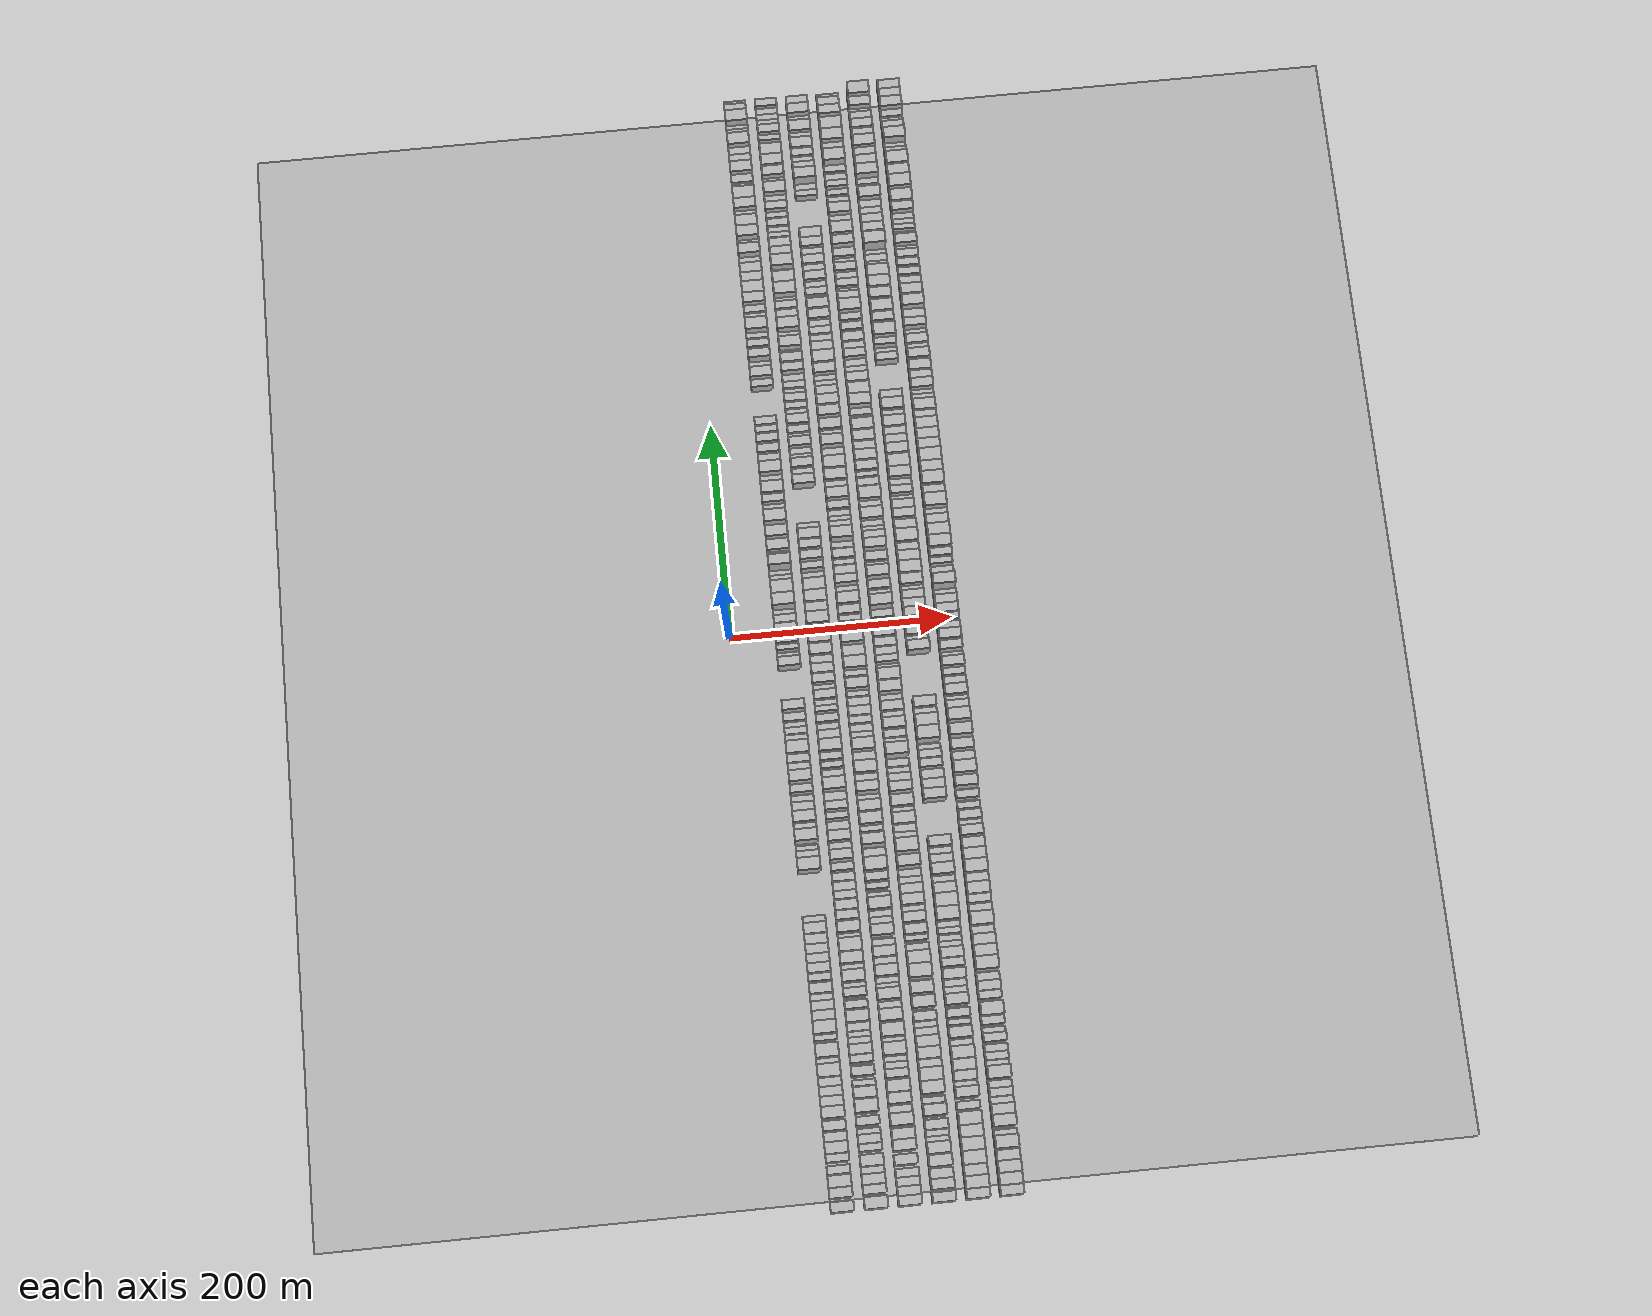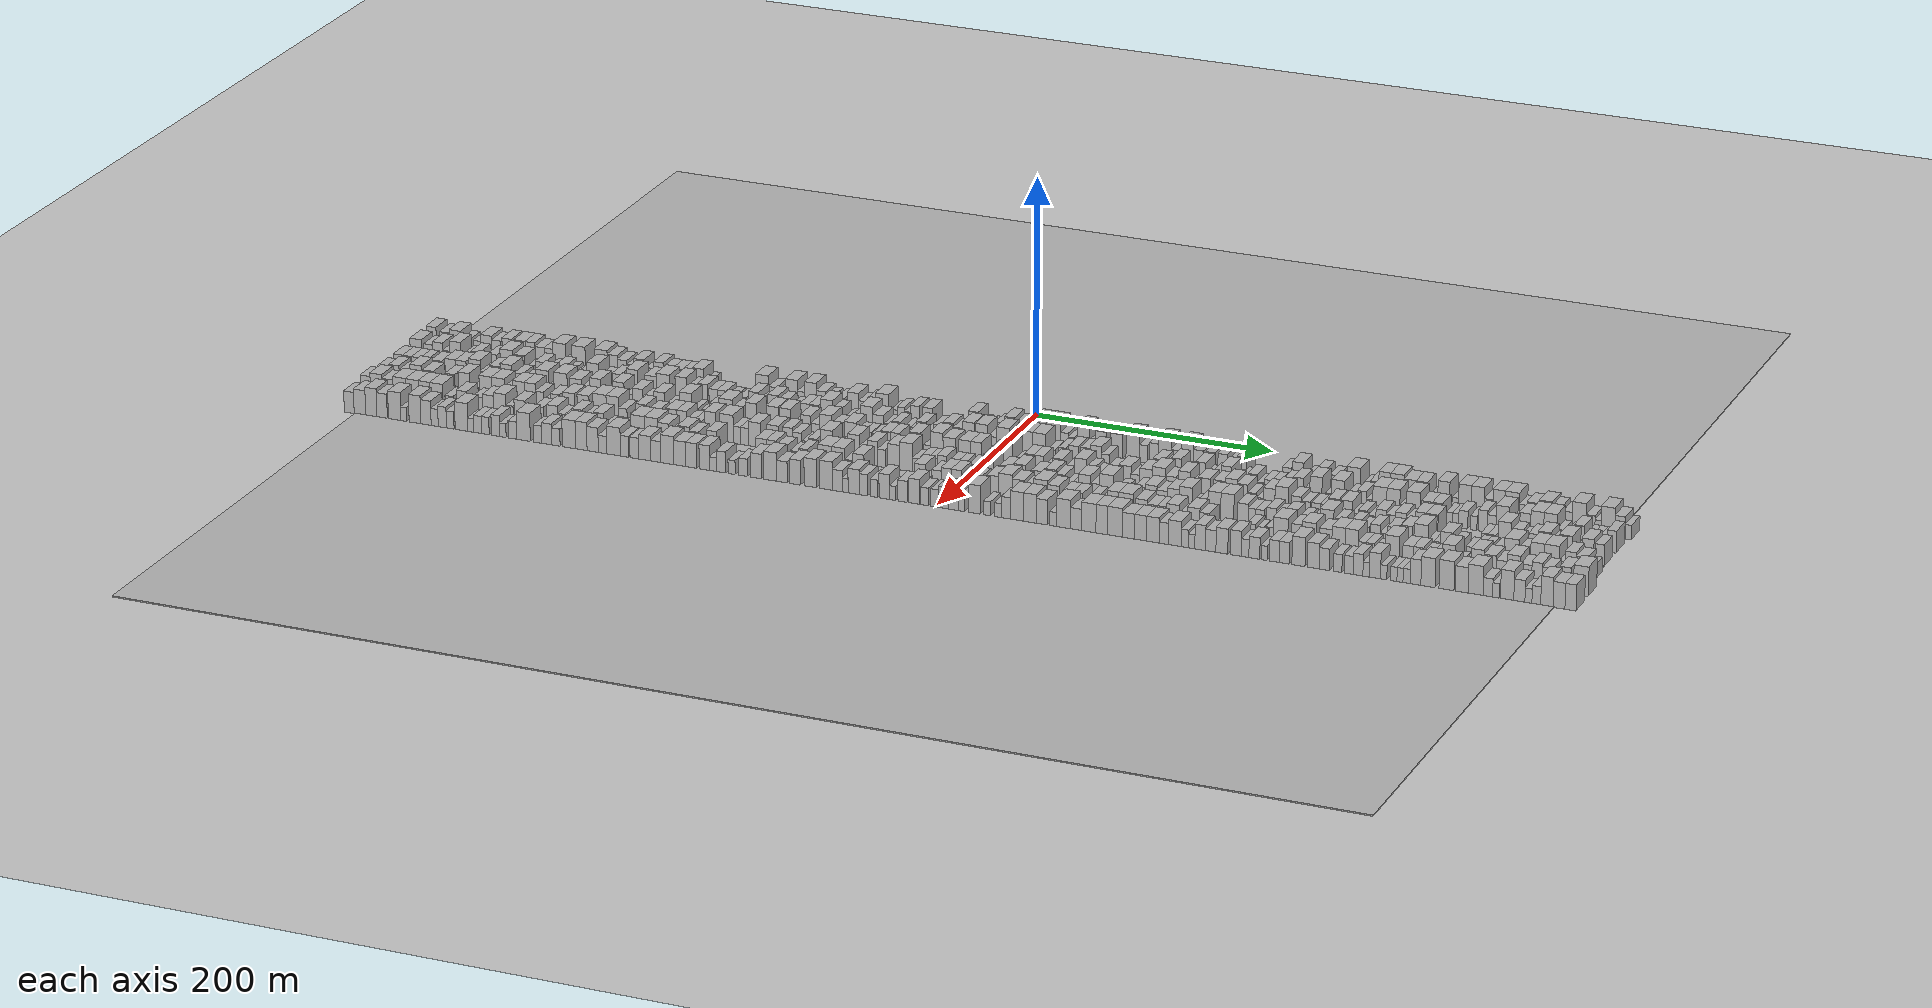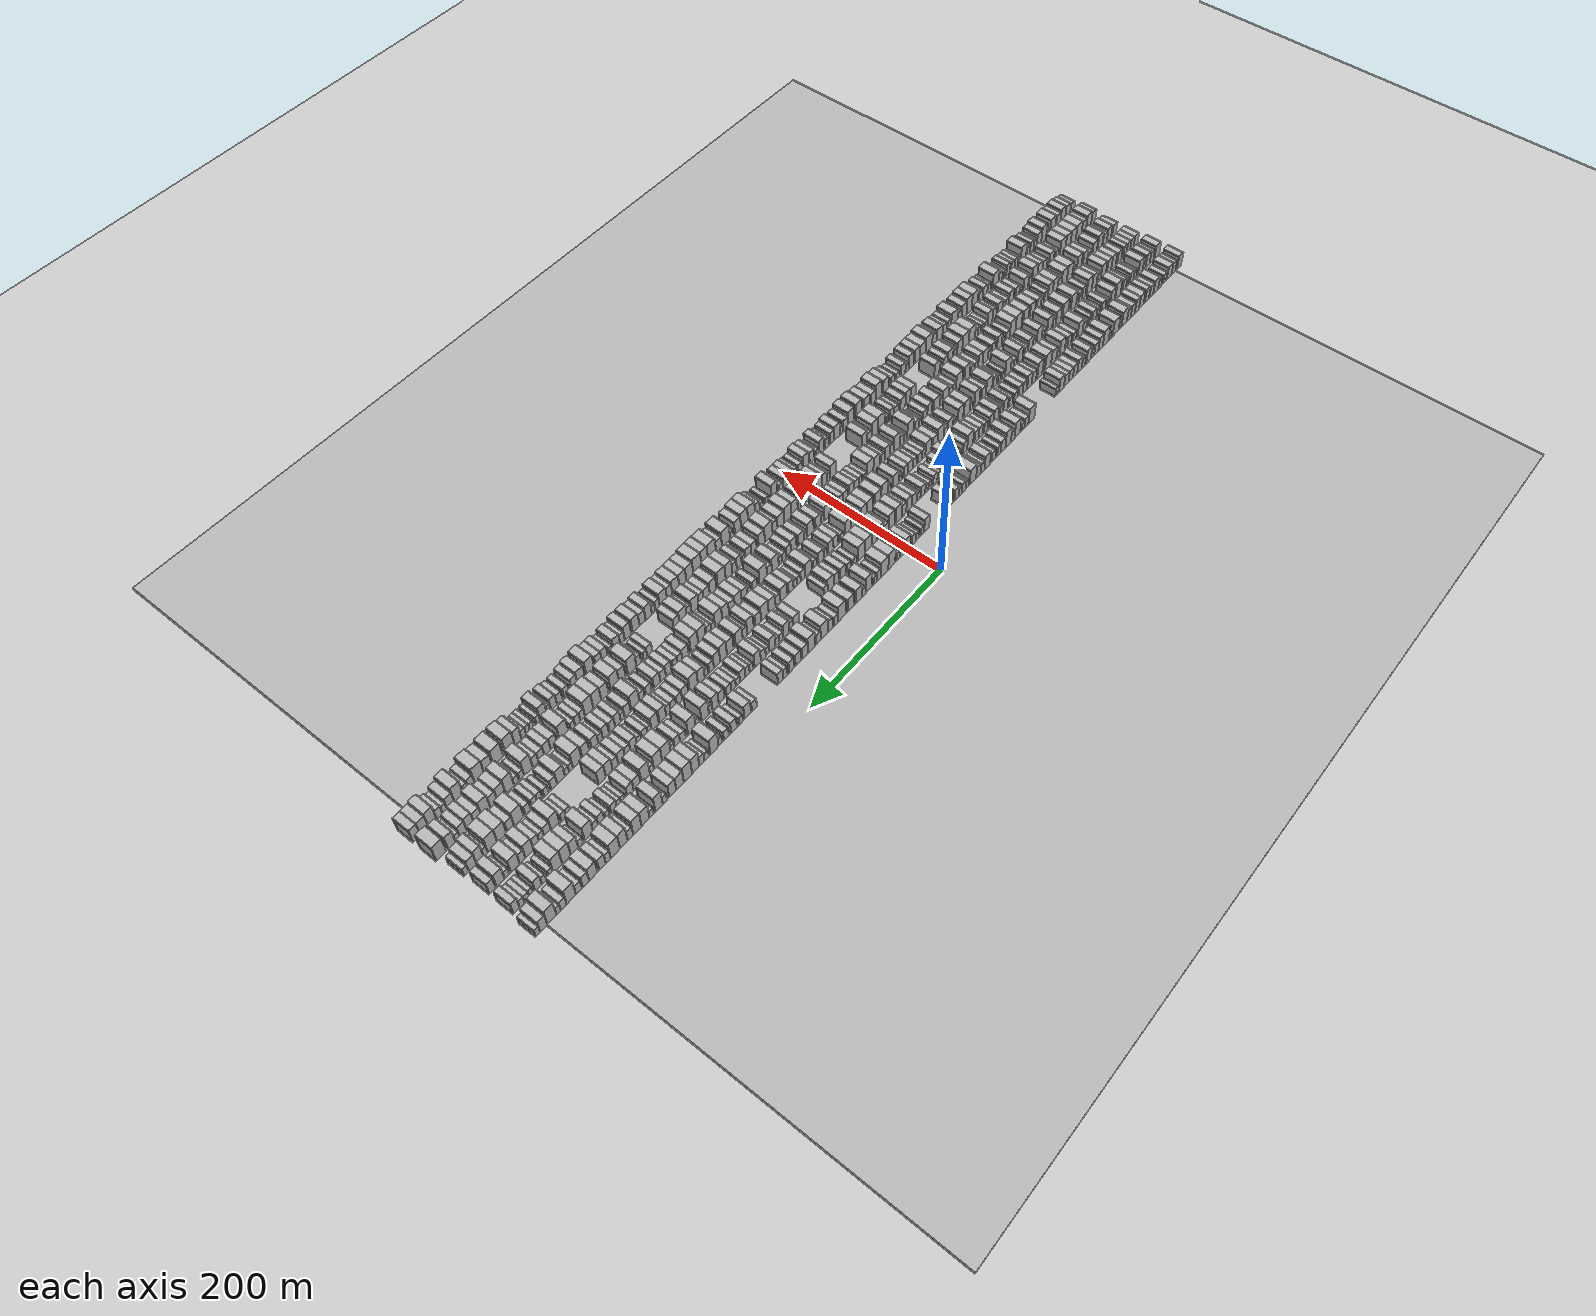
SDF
<?xml version="1.0" encoding="utf-8"?>

<sdf version="1.6">

   <world name="default">

      <gui fullscreen="0">

         <camera name="user_camera">

            <pose>-15 0 4.57585 0 0 0</pose>

            <view_controller>orbit</view_controller>

         </camera>

      </gui>

      <scene>

         <sky>

           <clouds>

             <speed>12</speed>

           </clouds>

         </sky>

         <ambient>0.4 0.4 0.4 1</ambient>

         <background>0.7 0.7 0.7 1</background>

         <shadows>1</shadows>

      </scene>

      <gravity>0 0 -9.8066</gravity>

      <magnetic_field>6e-06 2.3e-05 -4.2e-05</magnetic_field>

      <physics default="0" name="default_physics" type="ode">

         <ode>

            <solver>

               <type>quick</type>

               <iters>10</iters>

               <sor>1.0</sor>

               <use_dynamic_moi_rescaling>0</use_dynamic_moi_rescaling>

            </solver>

            <constraints>

               <cfm>0</cfm>

               <erp>0.2</erp>

               <contact_max_correcting_vel>100</contact_max_correcting_vel>

               <contact_surface_layer>0.001</contact_surface_layer>

            </constraints>

         </ode>

         <max_step_size>0.004</max_step_size>

         <real_time_factor>1</real_time_factor>

         <real_time_update_rate>250</real_time_update_rate>

      </physics>

      <light name="sun" type="directional">

         <cast_shadows>1</cast_shadows>

         <pose>0 0 10 0 0 0</pose>

         <diffuse>0.8 0.8 0.8 1</diffuse>

         <specular>0.2 0.2 0.2 1</specular>

         <attenuation>

            <range>1000</range>

            <constant>0.9</constant>

            <linear>0.01</linear>

            <quadratic>0.001</quadratic>

         </attenuation>

         <direction>-0.5 0.1 -0.9</direction>

      </light>

      <include>

         <name>ground_plane_1</name>

         <uri>model://HANNAS_ground_plane</uri>

         <pose>0 0 0  0 0 0</pose>

      </include>

      <include>

         <name>ground_plane_2</name>

         <uri>model://HANNAS_ground_plane</uri>

         <pose>100 0 0  0 0 0</pose>

      </include>

      <model name="building_1">

         <static>1</static>

         <pose frame="">50.0000 -505.5305 0 0.000000 0.000000 0.000000</pose>

         <link name="link">

            <pose frame="">0 0 10.50 0 0 0</pose>

            <collision name="collision">

               <geometry>

                  <box>

                     <size>20.0000 8.9389 21.0000</size>

                  </box>

               </geometry>

               <max_contacts>10</max_contacts>

               <surface>

                  <contact>

                     <ode/>

                  </contact>

                  <bounce/>

                  <friction>

                     <torsional>

                        <ode/>

                     </torsional>

                     <ode/>

                  </friction>

               </surface>

            </collision>

            <visual name="visual">

               <cast_shadows>0</cast_shadows>

               <geometry>

                  <box>

                     <size>20.0000 8.9389 21.0000</size>

                  </box>

               </geometry>

               <material>

                  <script>

                     <uri>model://HANNAS_wall/materials/scripts</uri>

                     <uri>model://HANNAS_wall/materials/textures</uri>

                     <name>vrc/HANNAS_wall</name>

                  </script>

               </material>

            </visual>

            <self_collide>0</self_collide>

            <enable_wind>0</enable_wind>

            <kinematic>0</kinematic>

         </link>

      </model>

      <model name="building_2">

         <static>1</static>

         <pose frame="">50.0000 -493.6415 0 0.000000 0.000000 0.000000</pose>

         <link name="link">

            <pose frame="">0 0 9.00 0 0 0</pose>

            <collision name="collision">

               <geometry>

                  <box>

                     <size>20.0000 8.8392 18.0000</size>

                  </box>

               </geometry>

               <max_contacts>10</max_contacts>

               <surface>

                  <contact>

                     <ode/>

                  </contact>

                  <bounce/>

                  <friction>

                     <torsional>

                        <ode/>

                     </torsional>

                     <ode/>

                  </friction>

               </surface>

            </collision>

            <visual name="visual">

               <cast_shadows>0</cast_shadows>

               <geometry>

                  <box>

                     <size>20.0000 8.8392 18.0000</size>

                  </box>

               </geometry>

               <material>

                  <script>

                     <uri>model://HANNAS_wall/materials/scripts</uri>

                     <uri>model://HANNAS_wall/materials/textures</uri>

                     <name>vrc/HANNAS_wall</name>

                  </script>

               </material>

            </visual>

            <self_collide>0</self_collide>

            <enable_wind>0</enable_wind>

            <kinematic>0</kinematic>

         </link>

      </model>

      <model name="building_3">

         <static>1</static>

         <pose frame="">50.0000 -484.0873 0 0.000000 0.000000 0.000000</pose>

         <link name="link">

            <pose frame="">0 0 10.50 0 0 0</pose>

            <collision name="collision">

               <geometry>

                  <box>

                     <size>20.0000 10.2692 21.0000</size>

                  </box>

               </geometry>

               <max_contacts>10</max_contacts>

               <surface>

                  <contact>

                     <ode/>

                  </contact>

                  <bounce/>

                  <friction>

                     <torsional>

                        <ode/>

                     </torsional>

                     <ode/>

                  </friction>

               </surface>

            </collision>

            <visual name="visual">

               <cast_shadows>0</cast_shadows>

               <geometry>

                  <box>

                     <size>20.0000 10.2692 21.0000</size>

                  </box>

               </geometry>

               <material>

                  <script>

                     <uri>model://HANNAS_wall/materials/scripts</uri>

                     <uri>model://HANNAS_wall/materials/textures</uri>

                     <name>vrc/HANNAS_wall</name>

                  </script>

               </material>

            </visual>

            <self_collide>0</self_collide>

            <enable_wind>0</enable_wind>

            <kinematic>0</kinematic>

         </link>

      </model>

      <model name="building_4">

         <static>1</static>

         <pose frame="">50.0000 -474.3811 0 0.000000 0.000000 0.000000</pose>

         <link name="link">

            <pose frame="">0 0 7.50 0 0 0</pose>

            <collision name="collision">

               <geometry>

                  <box>

                     <size>20.0000 7.1433 15.0000</size>

                  </box>

               </geometry>

               <max_contacts>10</max_contacts>

               <surface>

                  <contact>

                     <ode/>

                  </contact>

                  <bounce/>

                  <friction>

                     <torsional>

                        <ode/>

                     </torsional>

                     <ode/>

                  </friction>

               </surface>

            </collision>

            <visual name="visual">

               <cast_shadows>0</cast_shadows>

               <geometry>

                  <box>

                     <size>20.0000 7.1433 15.0000</size>

                  </box>

               </geometry>

               <material>

                  <script>

                     <uri>model://HANNAS_wall/materials/scripts</uri>

                     <uri>model://HANNAS_wall/materials/textures</uri>

                     <name>vrc/HANNAS_wall</name>

                  </script>

               </material>

            </visual>

            <self_collide>0</self_collide>

            <enable_wind>0</enable_wind>

            <kinematic>0</kinematic>

         </link>

      </model>

      <model name="building_5">

         <static>1</static>

         <pose frame="">50.0000 -464.3578 0 0.000000 0.000000 0.000000</pose>

         <link name="link">

            <pose frame="">0 0 7.50 0 0 0</pose>

            <collision name="collision">

               <geometry>

                  <box>

                     <size>20.0000 6.9032 15.0000</size>

                  </box>

               </geometry>

               <max_contacts>10</max_contacts>

               <surface>

                  <contact>

                     <ode/>

                  </contact>

                  <bounce/>

                  <friction>

                     <torsional>

                        <ode/>

                     </torsional>

                     <ode/>

                  </friction>

               </surface>

            </collision>

            <visual name="visual">

               <cast_shadows>0</cast_shadows>

               <geometry>

                  <box>

                     <size>20.0000 6.9032 15.0000</size>

                  </box>

               </geometry>

               <material>

                  <script>

                     <uri>model://HANNAS_wall/materials/scripts</uri>

                     <uri>model://HANNAS_wall/materials/textures</uri>

                     <name>vrc/HANNAS_wall</name>

                  </script>

               </material>

            </visual>

            <self_collide>0</self_collide>

            <enable_wind>0</enable_wind>

            <kinematic>0</kinematic>

         </link>

      </model>

      <model name="building_6">

         <static>1</static>

         <pose frame="">50.0000 -455.9039 0 0.000000 0.000000 0.000000</pose>

         <link name="link">

            <pose frame="">0 0 10.50 0 0 0</pose>

            <collision name="collision">

               <geometry>

                  <box>

                     <size>20.0000 10.0047 21.0000</size>

                  </box>

               </geometry>

               <max_contacts>10</max_contacts>

               <surface>

                  <contact>

                     <ode/>

                  </contact>

                  <bounce/>

                  <friction>

                     <torsional>

                        <ode/>

                     </torsional>

                     <ode/>

                  </friction>

               </surface>

            </collision>

            <visual name="visual">

               <cast_shadows>0</cast_shadows>

               <geometry>

                  <box>

                     <size>20.0000 10.0047 21.0000</size>

                  </box>

               </geometry>

               <material>

                  <script>

                     <uri>model://HANNAS_wall/materials/scripts</uri>

                     <uri>model://HANNAS_wall/materials/textures</uri>

                     <name>vrc/HANNAS_wall</name>

                  </script>

               </material>

            </visual>

            <self_collide>0</self_collide>

            <enable_wind>0</enable_wind>

            <kinematic>0</kinematic>

         </link>

      </model>

      <model name="building_7">

         <static>1</static>

         <pose frame="">50.0000 -446.7945 0 0.000000 0.000000 0.000000</pose>

         <link name="link">

            <pose frame="">0 0 9.00 0 0 0</pose>

            <collision name="collision">

               <geometry>

                  <box>

                     <size>20.0000 8.2141 18.0000</size>

                  </box>

               </geometry>

               <max_contacts>10</max_contacts>

               <surface>

                  <contact>

                     <ode/>

                  </contact>

                  <bounce/>

                  <friction>

                     <torsional>

                        <ode/>

                     </torsional>

                     <ode/>

                  </friction>

               </surface>

            </collision>

            <visual name="visual">

               <cast_shadows>0</cast_shadows>

               <geometry>

                  <box>

                     <size>20.0000 8.2141 18.0000</size>

                  </box>

               </geometry>

               <material>

                  <script>

                     <uri>model://HANNAS_wall/materials/scripts</uri>

                     <uri>model://HANNAS_wall/materials/textures</uri>

                     <name>vrc/HANNAS_wall</name>

                  </script>

               </material>

            </visual>

            <self_collide>0</self_collide>

            <enable_wind>0</enable_wind>

            <kinematic>0</kinematic>

         </link>

      </model>

      <model name="building_8">

         <static>1</static>

         <pose frame="">50.0000 -437.3820 0 0.000000 0.000000 0.000000</pose>

         <link name="link">

            <pose frame="">0 0 10.50 0 0 0</pose>

            <collision name="collision">

               <geometry>

                  <box>

                     <size>20.0000 8.6109 21.0000</size>

                  </box>

               </geometry>

               <max_contacts>10</max_contacts>

               <surface>

                  <contact>

                     <ode/>

                  </contact>

                  <bounce/>

                  <friction>

                     <torsional>

                        <ode/>

                     </torsional>

                     <ode/>

                  </friction>

               </surface>

            </collision>

            <visual name="visual">

               <cast_shadows>0</cast_shadows>

               <geometry>

                  <box>

                     <size>20.0000 8.6109 21.0000</size>

                  </box>

               </geometry>

               <material>

                  <script>

                     <uri>model://HANNAS_wall/materials/scripts</uri>

                     <uri>model://HANNAS_wall/materials/textures</uri>

                     <name>vrc/HANNAS_wall</name>

                  </script>

               </material>

            </visual>

            <self_collide>0</self_collide>

            <enable_wind>0</enable_wind>

            <kinematic>0</kinematic>

         </link>

      </model>

      <model name="building_9">

         <static>1</static>

         <pose frame="">50.0000 -426.0398 0 0.000000 0.000000 0.000000</pose>

         <link name="link">

            <pose frame="">0 0 10.50 0 0 0</pose>

            <collision name="collision">

               <geometry>

                  <box>

                     <size>20.0000 10.0735 21.0000</size>

                  </box>

               </geometry>

               <max_contacts>10</max_contacts>

               <surface>

                  <contact>

                     <ode/>

                  </contact>

                  <bounce/>

                  <friction>

                     <torsional>

                        <ode/>

                     </torsional>

                     <ode/>

                  </friction>

               </surface>

            </collision>

            <visual name="visual">

               <cast_shadows>0</cast_shadows>

               <geometry>

                  <box>

                     <size>20.0000 10.0735 21.0000</size>

                  </box>

               </geometry>

               <material>

                  <script>

                     <uri>model://HANNAS_wall/materials/scripts</uri>

                     <uri>model://HANNAS_wall/materials/textures</uri>

                     <name>vrc/HANNAS_wall</name>

                  </script>

               </material>

            </visual>

            <self_collide>0</self_collide>

            <enable_wind>0</enable_wind>

            <kinematic>0</kinematic>

         </link>

      </model>

      <model name="building_10">

         <static>1</static>

         <pose frame="">50.0000 -416.6983 0 0.000000 0.000000 0.000000</pose>

         <link name="link">

            <pose frame="">0 0 10.50 0 0 0</pose>

            <collision name="collision">

               <geometry>

                  <box>

                     <size>20.0000 8.6096 21.0000</size>

                  </box>

               </geometry>

               <max_contacts>10</max_contacts>

               <surface>

                  <contact>

                     <ode/>

                  </contact>

                  <bounce/>

                  <friction>

                     <torsional>

                        <ode/>

                     </torsional>

                     <ode/>

                  </friction>

               </surface>

            </collision>

            <visual name="visual">

               <cast_shadows>0</cast_shadows>

               <geometry>

                  <box>

                     <size>20.0000 8.6096 21.0000</size>

                  </box>

               </geometry>

               <material>

                  <script>

                     <uri>model://HANNAS_wall/materials/scripts</uri>

                     <uri>model://HANNAS_wall/materials/textures</uri>

                     <name>vrc/HANNAS_wall</name>

                  </script>

               </material>

            </visual>

            <self_collide>0</self_collide>

            <enable_wind>0</enable_wind>

            <kinematic>0</kinematic>

         </link>

      </model>

      <model name="building_11">

         <static>1</static>

         <pose frame="">50.0000 -408.2185 0 0.000000 0.000000 0.000000</pose>

         <link name="link">

            <pose frame="">0 0 9.00 0 0 0</pose>

            <collision name="collision">

               <geometry>

                  <box>

                     <size>20.0000 8.3500 18.0000</size>

                  </box>

               </geometry>

               <max_contacts>10</max_contacts>

               <surface>

                  <contact>

                     <ode/>

                  </contact>

                  <bounce/>

                  <friction>

                     <torsional>

                        <ode/>

                     </torsional>

                     <ode/>

                  </friction>

               </surface>

            </collision>

            <visual name="visual">

               <cast_shadows>0</cast_shadows>

               <geometry>

                  <box>

                     <size>20.0000 8.3500 18.0000</size>

                  </box>

               </geometry>

               <material>

                  <script>

                     <uri>model://HANNAS_wall/materials/scripts</uri>

                     <uri>model://HANNAS_wall/materials/textures</uri>

                     <name>vrc/HANNAS_wall</name>

                  </script>

               </material>

            </visual>

            <self_collide>0</self_collide>

            <enable_wind>0</enable_wind>

            <kinematic>0</kinematic>

         </link>

      </model>

      <model name="building_12">

         <static>1</static>

         <pose frame="">50.0000 -400.2078 0 0.000000 0.000000 0.000000</pose>

         <link name="link">

            <pose frame="">0 0 9.00 0 0 0</pose>

            <collision name="collision">

               <geometry>

                  <box>

                     <size>20.0000 7.6714 18.0000</size>

                  </box>

               </geometry>

               <max_contacts>10</max_contacts>

               <surface>

                  <contact>

                     <ode/>

                  </contact>

                  <bounce/>

                  <friction>

                     <torsional>

                        <ode/>

                     </torsional>

                     <ode/>

                  </friction>

               </surface>

            </collision>

            <visual name="visual">

               <cast_shadows>0</cast_shadows>

               <geometry>

                  <box>

                     <size>20.0000 7.6714 18.0000</size>

                  </box>

               </geometry>

               <material>

                  <script>

                     <uri>model://HANNAS_wall/materials/scripts</uri>

                     <uri>model://HANNAS_wall/materials/textures</uri>

                     <name>vrc/HANNAS_wall</name>

                  </script>

               </material>

            </visual>

            <self_collide>0</self_collide>

            <enable_wind>0</enable_wind>

            <kinematic>0</kinematic>

         </link>

      </model>

      <model name="building_13">

         <static>1</static>

         <pose frame="">50.0000 -390.6741 0 0.000000 0.000000 0.000000</pose>

         <link name="link">

            <pose frame="">0 0 12.00 0 0 0</pose>

            <collision name="collision">

               <geometry>

                  <box>

                     <size>20.0000 11.3960 24.0000</size>

                  </box>

               </geometry>

               <max_contacts>10</max_contacts>

               <surface>

                  <contact>

                     <ode/>

                  </contact>

                  <bounce/>

                  <friction>

                     <torsional>

                        <ode/>

                     </torsional>

                     <ode/>

                  </friction>

               </surface>

            </collision>

            <visual name="visual">

               <cast_shadows>0</cast_shadows>

               <geometry>

                  <box>

                     <size>20.0000 11.3960 24.0000</size>

                  </box>

               </geometry>

               <material>

                  <script>

                     <uri>model://HANNAS_wall/materials/scripts</uri>

                     <uri>model://HANNAS_wall/materials/textures</uri>

                     <name>vrc/HANNAS_wall</name>

                  </script>

               </material>

            </visual>

            <self_collide>0</self_collide>

            <enable_wind>0</enable_wind>

            <kinematic>0</kinematic>

         </link>

      </model>

      <model name="building_14">

         <static>1</static>

         <pose frame="">50.0000 -382.2352 0 0.000000 0.000000 0.000000</pose>

         <link name="link">

            <pose frame="">0 0 6.00 0 0 0</pose>

            <collision name="collision">

               <geometry>

                  <box>

                     <size>20.0000 5.4818 12.0000</size>

                  </box>

               </geometry>

               <max_contacts>10</max_contacts>

               <surface>

                  <contact>

                     <ode/>

                  </contact>

                  <bounce/>

                  <friction>

                     <torsional>

                        <ode/>

                     </torsional>

                     <ode/>

                  </friction>

               </surface>

            </collision>

            <visual name="visual">

               <cast_shadows>0</cast_shadows>

               <geometry>

                  <box>

                     <size>20.0000 5.4818 12.0000</size>

                  </box>

               </geometry>

               <material>

                  <script>

                     <uri>model://HANNAS_wall/materials/scripts</uri>

                     <uri>model://HANNAS_wall/materials/textures</uri>

                     <name>vrc/HANNAS_wall</name>

                  </script>

               </material>

            </visual>

            <self_collide>0</self_collide>

            <enable_wind>0</enable_wind>

            <kinematic>0</kinematic>

         </link>

      </model>

      <model name="building_15">

         <static>1</static>

         <pose frame="">50.0000 -373.5019 0 0.000000 0.000000 0.000000</pose>

         <link name="link">

            <pose frame="">0 0 12.00 0 0 0</pose>

            <collision name="collision">

               <geometry>

                  <box>

                     <size>20.0000 11.9846 24.0000</size>

                  </box>

               </geometry>

               <max_contacts>10</max_contacts>

               <surface>

                  <contact>

                     <ode/>

                  </contact>

                  <bounce/>

                  <friction>

                     <torsional>

                        <ode/>

                     </torsional>

                     <ode/>

                  </friction>

               </surface>

            </collision>

            <visual name="visual">

               <cast_shadows>0</cast_shadows>

               <geometry>

                  <box>

                     <size>20.0000 11.9846 24.0000</size>

                  </box>

               </geometry>

               <material>

                  <script>

                     <uri>model://HANNAS_wall/materials/scripts</uri>

                     <uri>model://HANNAS_wall/materials/textures</uri>

                     <name>vrc/HANNAS_wall</name>

                  </script>

               </material>

            </visual>

            <self_collide>0</self_collide>

            <enable_wind>0</enable_wind>

            <kinematic>0</kinematic>

         </link>

      </model>

      <model name="building_16">

         <static>1</static>

         <pose frame="">50.0000 -361.9013 0 0.000000 0.000000 0.000000</pose>

         <link name="link">

            <pose frame="">0 0 6.00 0 0 0</pose>

            <collision name="collision">

               <geometry>

                  <box>

                     <size>20.0000 5.2166 12.0000</size>

                  </box>

               </geometry>

               <max_contacts>10</max_contacts>

               <surface>

                  <contact>

                     <ode/>

                  </contact>

                  <bounce/>

                  <friction>

                     <torsional>

                        <ode/>

                     </torsional>

                     <ode/>

                  </friction>

               </surface>

            </collision>

            <visual name="visual">

               <cast_shadows>0</cast_shadows>

               <geometry>

                  <box>

                     <size>20.0000 5.2166 12.0000</size>

                  </box>

               </geometry>

               <material>

                  <script>

                     <uri>model://HANNAS_wall/materials/scripts</uri>

                     <uri>model://HANNAS_wall/materials/textures</uri>

                     <name>vrc/HANNAS_wall</name>

                  </script>

               </material>

            </visual>

            <self_collide>0</self_collide>

            <enable_wind>0</enable_wind>

            <kinematic>0</kinematic>

         </link>

      </model>

      <model name="building_17">

         <static>1</static>

         <pose frame="">50.0000 -353.6259 0 0.000000 0.000000 0.000000</pose>

         <link name="link">

            <pose frame="">0 0 12.00 0 0 0</pose>

            <collision name="collision">

               <geometry>

                  <box>

                     <size>20.0000 11.3343 24.0000</size>

                  </box>

               </geometry>

               <max_contacts>10</max_contacts>

               <surface>

                  <contact>

                     <ode/>

                  </contact>

                  <bounce/>

                  <friction>

                     <torsional>

                        <ode/>

                     </torsional>

                     <ode/>

                  </friction>

               </surface>

            </collision>

            <visual name="visual">

               <cast_shadows>0</cast_shadows>

               <geometry>

                  <box>

                     <size>20.0000 11.3343 24.0000</size>

                  </box>

               </geometry>

               <material>

                  <script>

                     <uri>model://HANNAS_wall/materials/scripts</uri>

                     <uri>model://HANNAS_wall/materials/textures</uri>

                     <name>vrc/HANNAS_wall</name>

                  </script>

               </material>

            </visual>

            <self_collide>0</self_collide>

            <enable_wind>0</enable_wind>

            <kinematic>0</kinematic>

         </link>

      </model>

      <model name="building_18">

         <static>1</static>

         <pose frame="">50.0000 -343.5423 0 0.000000 0.000000 0.000000</pose>

         <link name="link">

            <pose frame="">0 0 10.50 0 0 0</pose>

            <collision name="collision">

               <geometry>

                  <box>

                     <size>20.0000 8.8330 21.0000</size>

                  </box>

               </geometry>

               <max_contacts>10</max_contacts>

               <surface>

                  <contact>

                     <ode/>

                  </contact>

                  <bounce/>

                  <friction>

                     <torsional>

                        <ode/>

                     </torsional>

                     <ode/>

                  </friction>

               </surface>

            </collision>

            <visual name="visual">

               <cast_shadows>0</cast_shadows>

               <geometry>

                  <box>

                     <size>20.0000 8.8330 21.0000</size>

                  </box>

               </geometry>

               <material>

                  <script>

                     <uri>model://HANNAS_wall/materials/scripts</uri>

                     <uri>model://HANNAS_wall/materials/textures</uri>

                     <name>vrc/HANNAS_wall</name>

                  </script>

               </material>

            </visual>

            <self_collide>0</self_collide>

            <enable_wind>0</enable_wind>

            <kinematic>0</kinematic>

         </link>

      </model>

      <model name="building_19">

         <static>1</static>

         <pose frame="">50.0000 -334.8878 0 0.000000 0.000000 0.000000</pose>

         <link name="link">

            <pose frame="">0 0 9.00 0 0 0</pose>

            <collision name="collision">

               <geometry>

                  <box>

                     <size>20.0000 8.4761 18.0000</size>

                  </box>

               </geometry>

               <max_contacts>10</max_contacts>

               <surface>

                  <contact>

                     <ode/>

                  </contact>

                  <bounce/>

                  <friction>

                     <torsional>

                        <ode/>

                     </torsional>

                     <ode/>

                  </friction>

               </surface>

            </collision>

            <visual name="visual">

               <cast_shadows>0</cast_shadows>

               <geometry>

                  <box>

                     <size>20.0000 8.4761 18.0000</size>

                  </box>

               </geometry>

               <material>

                  <script>

                     <uri>model://HANNAS_wall/materials/scripts</uri>

                     <uri>model://HANNAS_wall/materials/textures</uri>

                     <name>vrc/HANNAS_wall</name>

                  </script>

               </material>

            </visual>

            <self_collide>0</self_collide>

            <enable_wind>0</enable_wind>

            <kinematic>0</kinematic>

         </link>

      </model>

      <model name="building_20">

         <static>1</static>

         <pose frame="">50.0000 -327.5718 0 0.000000 0.000000 0.000000</pose>

         <link name="link">

            <pose frame="">0 0 7.50 0 0 0</pose>

            <collision name="collision">

               <geometry>

                  <box>

                     <size>20.0000 6.1558 15.0000</size>

                  </box>

               </geometry>

               <max_contacts>10</max_contacts>

               <surface>

                  <contact>

                     <ode/>

                  </contact>

                  <bounce/>

                  <friction>

                     <torsional>

                        <ode/>

                     </torsional>

                     <ode/>

                  </friction>

               </surface>

            </collision>

            <visual name="visual">

               <cast_shadows>0</cast_shadows>

               <geometry>

                  <box>

                     <size>20.0000 6.1558 15.0000</size>

                  </box>

               </geometry>

               <material>

                  <script>

                     <uri>model://HANNAS_wall/materials/scripts</uri>

                     <uri>model://HANNAS_wall/materials/textures</uri>

                     <name>vrc/HANNAS_wall</name>

                  </script>

               </material>

            </visual>

            <self_collide>0</self_collide>

            <enable_wind>0</enable_wind>

            <kinematic>0</kinematic>

         </link>

      </model>

      <model name="building_21">

         <static>1</static>

         <pose frame="">50.0000 -319.9007 0 0.000000 0.000000 0.000000</pose>

         <link name="link">

            <pose frame="">0 0 10.50 0 0 0</pose>

            <collision name="collision">

               <geometry>

                  <box>

                     <size>20.0000 9.1864 21.0000</size>

                  </box>

               </geometry>

               <max_contacts>10</max_contacts>

               <surface>

                  <contact>

                     <ode/>

                  </contact>

                  <bounce/>

                  <friction>

                     <torsional>

                        <ode/>

                     </torsional>

                     <ode/>

                  </friction>

               </surface>

            </collision>

            <visual name="visual">

               <cast_shadows>0</cast_shadows>

               <geometry>

                  <box>

                     <size>20.0000 9.1864 21.0000</size>

                  </box>

               </geometry>

               <material>

                  <script>

                     <uri>model://HANNAS_wall/materials/scripts</uri>

                     <uri>model://HANNAS_wall/materials/textures</uri>

                     <name>vrc/HANNAS_wall</name>

                  </script>

               </material>

            </visual>

            <self_collide>0</self_collide>

            <enable_wind>0</enable_wind>

            <kinematic>0</kinematic>

         </link>

      </model>

      <model name="building_22">

         <static>1</static>

         <pose frame="">50.0000 -309.9602 0 0.000000 0.000000 0.000000</pose>

         <link name="link">

            <pose frame="">0 0 7.50 0 0 0</pose>

            <collision name="collision">

               <geometry>

                  <box>

                     <size>20.0000 6.6944 15.0000</size>

                  </box>

               </geometry>

               <max_contacts>10</max_contacts>

               <surface>

                  <contact>

                     <ode/>

                  </contact>

                  <bounce/>

                  <friction>

                     <torsional>

                        <ode/>

                     </torsional>

                     <ode/>

                  </friction>

               </surface>

            </collision>

            <visual name="visual">

               <cast_shadows>0</cast_shadows>

               <geometry>

                  <box>

                     <size>20.0000 6.6944 15.0000</size>

                  </box>

               </geometry>

               <material>

                  <script>

                     <uri>model://HANNAS_wall/materials/scripts</uri>

                     <uri>model://HANNAS_wall/materials/textures</uri>

                     <name>vrc/HANNAS_wall</name>

                  </script>

               </material>

            </visual>

            <self_collide>0</self_collide>

            <enable_wind>0</enable_wind>

            <kinematic>0</kinematic>

         </link>

      </model>

      <model name="building_23">

         <static>1</static>

         <pose frame="">50.0000 -302.3430 0 0.000000 0.000000 0.000000</pose>

         <link name="link">

            <pose frame="">0 0 10.50 0 0 0</pose>

            <collision name="collision">

               <geometry>

                  <box>

                     <size>20.0000 8.5401 21.0000</size>

                  </box>

               </geometry>

               <max_contacts>10</max_contacts>

               <surface>

                  <contact>

                     <ode/>

                  </contact>

                  <bounce/>

                  <friction>

                     <torsional>

                        <ode/>

                     </torsional>

                     <ode/>

                  </friction>

               </surface>

            </collision>

            <visual name="visual">

               <cast_shadows>0</cast_shadows>

               <geometry>

                  <box>

                     <size>20.0000 8.5401 21.0000</size>

                  </box>

               </geometry>

               <material>

                  <script>

                     <uri>model://HANNAS_wall/materials/scripts</uri>

                     <uri>model://HANNAS_wall/materials/textures</uri>

                     <name>vrc/HANNAS_wall</name>

                  </script>

               </material>

            </visual>

            <self_collide>0</self_collide>

            <enable_wind>0</enable_wind>

            <kinematic>0</kinematic>

         </link>

      </model>

      <model name="building_24">

         <static>1</static>

         <pose frame="">50.0000 -293.9038 0 0.000000 0.000000 0.000000</pose>

         <link name="link">

            <pose frame="">0 0 9.00 0 0 0</pose>

            <collision name="collision">

               <geometry>

                  <box>

                     <size>20.0000 8.3382 18.0000</size>

                  </box>

               </geometry>

               <max_contacts>10</max_contacts>

               <surface>

                  <contact>

                     <ode/>

                  </contact>

                  <bounce/>

                  <friction>

                     <torsional>

                        <ode/>

                     </torsional>

                     <ode/>

                  </friction>

               </surface>

            </collision>

            <visual name="visual">

               <cast_shadows>0</cast_shadows>

               <geometry>

                  <box>

                     <size>20.0000 8.3382 18.0000</size>

                  </box>

               </geometry>

               <material>

                  <script>

                     <uri>model://HANNAS_wall/materials/scripts</uri>

                     <uri>model://HANNAS_wall/materials/textures</uri>

                     <name>vrc/HANNAS_wall</name>

                  </script>

               </material>

            </visual>

            <self_collide>0</self_collide>

            <enable_wind>0</enable_wind>

            <kinematic>0</kinematic>

         </link>

      </model>

      <model name="building_25">

         <static>1</static>

         <pose frame="">50.0000 -285.5791 0 0.000000 0.000000 0.000000</pose>

         <link name="link">

            <pose frame="">0 0 9.00 0 0 0</pose>

            <collision name="collision">

               <geometry>

                  <box>

                     <size>20.0000 8.3112 18.0000</size>

                  </box>

               </geometry>

               <max_contacts>10</max_contacts>

               <surface>

                  <contact>

                     <ode/>

                  </contact>

                  <bounce/>

                  <friction>

                     <torsional>

                        <ode/>

                     </torsional>

                     <ode/>

                  </friction>

               </surface>

            </collision>

            <visual name="visual">

               <cast_shadows>0</cast_shadows>

               <geometry>

                  <box>

                     <size>20.0000 8.3112 18.0000</size>

                  </box>

               </geometry>

               <material>

                  <script>

                     <uri>model://HANNAS_wall/materials/scripts</uri>

                     <uri>model://HANNAS_wall/materials/textures</uri>

                     <name>vrc/HANNAS_wall</name>

                  </script>

               </material>

            </visual>

            <self_collide>0</self_collide>

            <enable_wind>0</enable_wind>

            <kinematic>0</kinematic>

         </link>

      </model>

      <model name="building_26">

         <static>1</static>

         <pose frame="">50.0000 -277.0363 0 0.000000 0.000000 0.000000</pose>

         <link name="link">

            <pose frame="">0 0 9.00 0 0 0</pose>

            <collision name="collision">

               <geometry>

                  <box>

                     <size>20.0000 8.7744 18.0000</size>

                  </box>

               </geometry>

               <max_contacts>10</max_contacts>

               <surface>

                  <contact>

                     <ode/>

                  </contact>

                  <bounce/>

                  <friction>

                     <torsional>

                        <ode/>

                     </torsional>

                     <ode/>

                  </friction>

               </surface>

            </collision>

            <visual name="visual">

               <cast_shadows>0</cast_shadows>

               <geometry>

                  <box>

                     <size>20.0000 8.7744 18.0000</size>

                  </box>

               </geometry>

               <material>

                  <script>

                     <uri>model://HANNAS_wall/materials/scripts</uri>

                     <uri>model://HANNAS_wall/materials/textures</uri>

                     <name>vrc/HANNAS_wall</name>

                  </script>

               </material>

            </visual>

            <self_collide>0</self_collide>

            <enable_wind>0</enable_wind>

            <kinematic>0</kinematic>

         </link>

      </model>

      <model name="building_27">

         <static>1</static>

         <pose frame="">50.0000 -267.8345 0 0.000000 0.000000 0.000000</pose>

         <link name="link">

            <pose frame="">0 0 10.50 0 0 0</pose>

            <collision name="collision">

               <geometry>

                  <box>

                     <size>20.0000 9.6290 21.0000</size>

                  </box>

               </geometry>

               <max_contacts>10</max_contacts>

               <surface>

                  <contact>

                     <ode/>

                  </contact>

                  <bounce/>

                  <friction>

                     <torsional>

                        <ode/>

                     </torsional>

                     <ode/>

                  </friction>

               </surface>

            </collision>

            <visual name="visual">

               <cast_shadows>0</cast_shadows>

               <geometry>

                  <box>

                     <size>20.0000 9.6290 21.0000</size>

                  </box>

               </geometry>

               <material>

                  <script>

                     <uri>model://HANNAS_wall/materials/scripts</uri>

                     <uri>model://HANNAS_wall/materials/textures</uri>

                     <name>vrc/HANNAS_wall</name>

                  </script>

               </material>

            </visual>

            <self_collide>0</self_collide>

            <enable_wind>0</enable_wind>

            <kinematic>0</kinematic>

         </link>

      </model>

      <model name="building_28">

         <static>1</static>

         <pose frame="">50.0000 -259.2189 0 0.000000 0.000000 0.000000</pose>

         <link name="link">

            <pose frame="">0 0 6.00 0 0 0</pose>

            <collision name="collision">

               <geometry>

                  <box>

                     <size>20.0000 5.6021 12.0000</size>

                  </box>

               </geometry>

               <max_contacts>10</max_contacts>

               <surface>

                  <contact>

                     <ode/>

                  </contact>

                  <bounce/>

                  <friction>

                     <torsional>

                        <ode/>

                     </torsional>

                     <ode/>

                  </friction>

               </surface>

            </collision>

            <visual name="visual">

               <cast_shadows>0</cast_shadows>

               <geometry>

                  <box>

                     <size>20.0000 5.6021 12.0000</size>

                  </box>

               </geometry>

               <material>

                  <script>

                     <uri>model://HANNAS_wall/materials/scripts</uri>

                     <uri>model://HANNAS_wall/materials/textures</uri>

                     <name>vrc/HANNAS_wall</name>

                  </script>

               </material>

            </visual>

            <self_collide>0</self_collide>

            <enable_wind>0</enable_wind>

            <kinematic>0</kinematic>

         </link>

      </model>

      <model name="building_29">

         <static>1</static>

         <pose frame="">50.0000 -211.8203 0 0.000000 0.000000 0.000000</pose>

         <link name="link">

            <pose frame="">0 0 12.00 0 0 0</pose>

            <collision name="collision">

               <geometry>

                  <box>

                     <size>20.0000 11.0650 24.0000</size>

                  </box>

               </geometry>

               <max_contacts>10</max_contacts>

               <surface>

                  <contact>

                     <ode/>

                  </contact>

                  <bounce/>

                  <friction>

                     <torsional>

                        <ode/>

                     </torsional>

                     <ode/>

                  </friction>

               </surface>

            </collision>

            <visual name="visual">

               <cast_shadows>0</cast_shadows>

               <geometry>

                  <box>

                     <size>20.0000 11.0650 24.0000</size>

                  </box>

               </geometry>

               <material>

                  <script>

                     <uri>model://HANNAS_wall/materials/scripts</uri>

                     <uri>model://HANNAS_wall/materials/textures</uri>

                     <name>vrc/HANNAS_wall</name>

                  </script>

               </material>

            </visual>

            <self_collide>0</self_collide>

            <enable_wind>0</enable_wind>

            <kinematic>0</kinematic>

         </link>

      </model>

      <model name="building_30">

         <static>1</static>

         <pose frame="">50.0000 -202.6941 0 0.000000 0.000000 0.000000</pose>

         <link name="link">

            <pose frame="">0 0 7.50 0 0 0</pose>

            <collision name="collision">

               <geometry>

                  <box>

                     <size>20.0000 7.1874 15.0000</size>

                  </box>

               </geometry>

               <max_contacts>10</max_contacts>

               <surface>

                  <contact>

                     <ode/>

                  </contact>

                  <bounce/>

                  <friction>

                     <torsional>

                        <ode/>

                     </torsional>

                     <ode/>

                  </friction>

               </surface>

            </collision>

            <visual name="visual">

               <cast_shadows>0</cast_shadows>

               <geometry>

                  <box>

                     <size>20.0000 7.1874 15.0000</size>

                  </box>

               </geometry>

               <material>

                  <script>

                     <uri>model://HANNAS_wall/materials/scripts</uri>

                     <uri>model://HANNAS_wall/materials/textures</uri>

                     <name>vrc/HANNAS_wall</name>

                  </script>

               </material>

            </visual>

            <self_collide>0</self_collide>

            <enable_wind>0</enable_wind>

            <kinematic>0</kinematic>

         </link>

      </model>

      <model name="building_31">

         <static>1</static>

         <pose frame="">50.0000 -196.7004 0 0.000000 0.000000 0.000000</pose>

         <link name="link">

            <pose frame="">0 0 6.00 0 0 0</pose>

            <collision name="collision">

               <geometry>

                  <box>

                     <size>20.0000 4.8000 12.0000</size>

                  </box>

               </geometry>

               <max_contacts>10</max_contacts>

               <surface>

                  <contact>

                     <ode/>

                  </contact>

                  <bounce/>

                  <friction>

                     <torsional>

                        <ode/>

                     </torsional>

                     <ode/>

                  </friction>

               </surface>

            </collision>

            <visual name="visual">

               <cast_shadows>0</cast_shadows>

               <geometry>

                  <box>

                     <size>20.0000 4.8000 12.0000</size>

                  </box>

               </geometry>

               <material>

                  <script>

                     <uri>model://HANNAS_wall/materials/scripts</uri>

                     <uri>model://HANNAS_wall/materials/textures</uri>

                     <name>vrc/HANNAS_wall</name>

                  </script>

               </material>

            </visual>

            <self_collide>0</self_collide>

            <enable_wind>0</enable_wind>

            <kinematic>0</kinematic>

         </link>

      </model>

      <model name="building_32">

         <static>1</static>

         <pose frame="">50.0000 -186.1310 0 0.000000 0.000000 0.000000</pose>

         <link name="link">

            <pose frame="">0 0 12.00 0 0 0</pose>

            <collision name="collision">

               <geometry>

                  <box>

                     <size>20.0000 10.3387 24.0000</size>

                  </box>

               </geometry>

               <max_contacts>10</max_contacts>

               <surface>

                  <contact>

                     <ode/>

                  </contact>

                  <bounce/>

                  <friction>

                     <torsional>

                        <ode/>

                     </torsional>

                     <ode/>

                  </friction>

               </surface>

            </collision>

            <visual name="visual">

               <cast_shadows>0</cast_shadows>

               <geometry>

                  <box>

                     <size>20.0000 10.3387 24.0000</size>

                  </box>

               </geometry>

               <material>

                  <script>

                     <uri>model://HANNAS_wall/materials/scripts</uri>

                     <uri>model://HANNAS_wall/materials/textures</uri>

                     <name>vrc/HANNAS_wall</name>

                  </script>

               </material>

            </visual>

            <self_collide>0</self_collide>

            <enable_wind>0</enable_wind>

            <kinematic>0</kinematic>

         </link>

      </model>

      <model name="building_33">

         <static>1</static>

         <pose frame="">50.0000 -177.7815 0 0.000000 0.000000 0.000000</pose>

         <link name="link">

            <pose frame="">0 0 7.50 0 0 0</pose>

            <collision name="collision">

               <geometry>

                  <box>

                     <size>20.0000 6.3604 15.0000</size>

                  </box>

               </geometry>

               <max_contacts>10</max_contacts>

               <surface>

                  <contact>

                     <ode/>

                  </contact>

                  <bounce/>

                  <friction>

                     <torsional>

                        <ode/>

                     </torsional>

                     <ode/>

                  </friction>

               </surface>

            </collision>

            <visual name="visual">

               <cast_shadows>0</cast_shadows>

               <geometry>

                  <box>

                     <size>20.0000 6.3604 15.0000</size>

                  </box>

               </geometry>

               <material>

                  <script>

                     <uri>model://HANNAS_wall/materials/scripts</uri>

                     <uri>model://HANNAS_wall/materials/textures</uri>

                     <name>vrc/HANNAS_wall</name>

                  </script>

               </material>

            </visual>

            <self_collide>0</self_collide>

            <enable_wind>0</enable_wind>

            <kinematic>0</kinematic>

         </link>

      </model>

      <model name="building_34">

         <static>1</static>

         <pose frame="">50.0000 -169.6660 0 0.000000 0.000000 0.000000</pose>

         <link name="link">

            <pose frame="">0 0 12.00 0 0 0</pose>

            <collision name="collision">

               <geometry>

                  <box>

                     <size>20.0000 9.8707 24.0000</size>

                  </box>

               </geometry>

               <max_contacts>10</max_contacts>

               <surface>

                  <contact>

                     <ode/>

                  </contact>

                  <bounce/>

                  <friction>

                     <torsional>

                        <ode/>

                     </torsional>

                     <ode/>

                  </friction>

               </surface>

            </collision>

            <visual name="visual">

               <cast_shadows>0</cast_shadows>

               <geometry>

                  <box>

                     <size>20.0000 9.8707 24.0000</size>

                  </box>

               </geometry>

               <material>

                  <script>

                     <uri>model://HANNAS_wall/materials/scripts</uri>

                     <uri>model://HANNAS_wall/materials/textures</uri>

                     <name>vrc/HANNAS_wall</name>

                  </script>

               </material>

            </visual>

            <self_collide>0</self_collide>

            <enable_wind>0</enable_wind>

            <kinematic>0</kinematic>

         </link>

      </model>

      <model name="building_35">

         <static>1</static>

         <pose frame="">50.0000 -160.4625 0 0.000000 0.000000 0.000000</pose>

         <link name="link">

            <pose frame="">0 0 9.00 0 0 0</pose>

            <collision name="collision">

               <geometry>

                  <box>

                     <size>20.0000 8.5363 18.0000</size>

                  </box>

               </geometry>

               <max_contacts>10</max_contacts>

               <surface>

                  <contact>

                     <ode/>

                  </contact>

                  <bounce/>

                  <friction>

                     <torsional>

                        <ode/>

                     </torsional>

                     <ode/>

                  </friction>

               </surface>

            </collision>

            <visual name="visual">

               <cast_shadows>0</cast_shadows>

               <geometry>

                  <box>

                     <size>20.0000 8.5363 18.0000</size>

                  </box>

               </geometry>

               <material>

                  <script>

                     <uri>model://HANNAS_wall/materials/scripts</uri>

                     <uri>model://HANNAS_wall/materials/textures</uri>

                     <name>vrc/HANNAS_wall</name>

                  </script>

               </material>

            </visual>

            <self_collide>0</self_collide>

            <enable_wind>0</enable_wind>

            <kinematic>0</kinematic>

         </link>

      </model>

      <model name="building_36">

         <static>1</static>

         <pose frame="">50.0000 -153.0958 0 0.000000 0.000000 0.000000</pose>

         <link name="link">

            <pose frame="">0 0 7.50 0 0 0</pose>

            <collision name="collision">

               <geometry>

                  <box>

                     <size>20.0000 6.1970 15.0000</size>

                  </box>

               </geometry>

               <max_contacts>10</max_contacts>

               <surface>

                  <contact>

                     <ode/>

                  </contact>

                  <bounce/>

                  <friction>

                     <torsional>

                        <ode/>

                     </torsional>

                     <ode/>

                  </friction>

               </surface>

            </collision>

            <visual name="visual">

               <cast_shadows>0</cast_shadows>

               <geometry>

                  <box>

                     <size>20.0000 6.1970 15.0000</size>

                  </box>

               </geometry>

               <material>

                  <script>

                     <uri>model://HANNAS_wall/materials/scripts</uri>

                     <uri>model://HANNAS_wall/materials/textures</uri>

                     <name>vrc/HANNAS_wall</name>

                  </script>

               </material>

            </visual>

            <self_collide>0</self_collide>

            <enable_wind>0</enable_wind>

            <kinematic>0</kinematic>

         </link>

      </model>

      <model name="building_37">

         <static>1</static>

         <pose frame="">50.0000 -143.3775 0 0.000000 0.000000 0.000000</pose>

         <link name="link">

            <pose frame="">0 0 7.50 0 0 0</pose>

            <collision name="collision">

               <geometry>

                  <box>

                     <size>20.0000 7.2395 15.0000</size>

                  </box>

               </geometry>

               <max_contacts>10</max_contacts>

               <surface>

                  <contact>

                     <ode/>

                  </contact>

                  <bounce/>

                  <friction>

                     <torsional>

                        <ode/>

                     </torsional>

                     <ode/>

                  </friction>

               </surface>

            </collision>

            <visual name="visual">

               <cast_shadows>0</cast_shadows>

               <geometry>

                  <box>

                     <size>20.0000 7.2395 15.0000</size>

                  </box>

               </geometry>

               <material>

                  <script>

                     <uri>model://HANNAS_wall/materials/scripts</uri>

                     <uri>model://HANNAS_wall/materials/textures</uri>

                     <name>vrc/HANNAS_wall</name>

                  </script>

               </material>

            </visual>

            <self_collide>0</self_collide>

            <enable_wind>0</enable_wind>

            <kinematic>0</kinematic>

         </link>

      </model>

      <model name="building_38">

         <static>1</static>

         <pose frame="">50.0000 -132.7980 0 0.000000 0.000000 0.000000</pose>

         <link name="link">

            <pose frame="">0 0 10.50 0 0 0</pose>

            <collision name="collision">

               <geometry>

                  <box>

                     <size>20.0000 9.9195 21.0000</size>

                  </box>

               </geometry>

               <max_contacts>10</max_contacts>

               <surface>

                  <contact>

                     <ode/>

                  </contact>

                  <bounce/>

                  <friction>

                     <torsional>

                        <ode/>

                     </torsional>

                     <ode/>

                  </friction>

               </surface>

            </collision>

            <visual name="visual">

               <cast_shadows>0</cast_shadows>

               <geometry>

                  <box>

                     <size>20.0000 9.9195 21.0000</size>

                  </box>

               </geometry>

               <material>

                  <script>

                     <uri>model://HANNAS_wall/materials/scripts</uri>

                     <uri>model://HANNAS_wall/materials/textures</uri>

                     <name>vrc/HANNAS_wall</name>

                  </script>

               </material>

            </visual>

            <self_collide>0</self_collide>

            <enable_wind>0</enable_wind>

            <kinematic>0</kinematic>

         </link>

      </model>

      <model name="building_39">

         <static>1</static>

         <pose frame="">50.0000 -124.2469 0 0.000000 0.000000 0.000000</pose>

         <link name="link">

            <pose frame="">0 0 7.50 0 0 0</pose>

            <collision name="collision">

               <geometry>

                  <box>

                     <size>20.0000 7.1827 15.0000</size>

                  </box>

               </geometry>

               <max_contacts>10</max_contacts>

               <surface>

                  <contact>

                     <ode/>

                  </contact>

                  <bounce/>

                  <friction>

                     <torsional>

                        <ode/>

                     </torsional>

                     <ode/>

                  </friction>

               </surface>

            </collision>

            <visual name="visual">

               <cast_shadows>0</cast_shadows>

               <geometry>

                  <box>

                     <size>20.0000 7.1827 15.0000</size>

                  </box>

               </geometry>

               <material>

                  <script>

                     <uri>model://HANNAS_wall/materials/scripts</uri>

                     <uri>model://HANNAS_wall/materials/textures</uri>

                     <name>vrc/HANNAS_wall</name>

                  </script>

               </material>

            </visual>

            <self_collide>0</self_collide>

            <enable_wind>0</enable_wind>

            <kinematic>0</kinematic>

         </link>

      </model>

      <model name="building_40">

         <static>1</static>

         <pose frame="">50.0000 -116.9001 0 0.000000 0.000000 0.000000</pose>

         <link name="link">

            <pose frame="">0 0 9.00 0 0 0</pose>

            <collision name="collision">

               <geometry>

                  <box>

                     <size>20.0000 7.5109 18.0000</size>

                  </box>

               </geometry>

               <max_contacts>10</max_contacts>

               <surface>

                  <contact>

                     <ode/>

                  </contact>

                  <bounce/>

                  <friction>

                     <torsional>

                        <ode/>

                     </torsional>

                     <ode/>

                  </friction>

               </surface>

            </collision>

            <visual name="visual">

               <cast_shadows>0</cast_shadows>

               <geometry>

                  <box>

                     <size>20.0000 7.5109 18.0000</size>

                  </box>

               </geometry>

               <material>

                  <script>

                     <uri>model://HANNAS_wall/materials/scripts</uri>

                     <uri>model://HANNAS_wall/materials/textures</uri>

                     <name>vrc/HANNAS_wall</name>

                  </script>

               </material>

            </visual>

            <self_collide>0</self_collide>

            <enable_wind>0</enable_wind>

            <kinematic>0</kinematic>

         </link>

      </model>

      <model name="building_41">

         <static>1</static>

         <pose frame="">50.0000 -107.5109 0 0.000000 0.000000 0.000000</pose>

         <link name="link">

            <pose frame="">0 0 12.00 0 0 0</pose>

            <collision name="collision">

               <geometry>

                  <box>

                     <size>20.0000 11.2675 24.0000</size>

                  </box>

               </geometry>

               <max_contacts>10</max_contacts>

               <surface>

                  <contact>

                     <ode/>

                  </contact>

                  <bounce/>

                  <friction>

                     <torsional>

                        <ode/>

                     </torsional>

                     <ode/>

                  </friction>

               </surface>

            </collision>

            <visual name="visual">

               <cast_shadows>0</cast_shadows>

               <geometry>

                  <box>

                     <size>20.0000 11.2675 24.0000</size>

                  </box>

               </geometry>

               <material>

                  <script>

                     <uri>model://HANNAS_wall/materials/scripts</uri>

                     <uri>model://HANNAS_wall/materials/textures</uri>

                     <name>vrc/HANNAS_wall</name>

                  </script>

               </material>

            </visual>

            <self_collide>0</self_collide>

            <enable_wind>0</enable_wind>

            <kinematic>0</kinematic>

         </link>

      </model>

      <model name="building_42">

         <static>1</static>

         <pose frame="">50.0000 -97.2788 0 0.000000 0.000000 0.000000</pose>

         <link name="link">

            <pose frame="">0 0 6.00 0 0 0</pose>

            <collision name="collision">

               <geometry>

                  <box>

                     <size>20.0000 5.1967 12.0000</size>

                  </box>

               </geometry>

               <max_contacts>10</max_contacts>

               <surface>

                  <contact>

                     <ode/>

                  </contact>

                  <bounce/>

                  <friction>

                     <torsional>

                        <ode/>

                     </torsional>

                     <ode/>

                  </friction>

               </surface>

            </collision>

            <visual name="visual">

               <cast_shadows>0</cast_shadows>

               <geometry>

                  <box>

                     <size>20.0000 5.1967 12.0000</size>

                  </box>

               </geometry>

               <material>

                  <script>

                     <uri>model://HANNAS_wall/materials/scripts</uri>

                     <uri>model://HANNAS_wall/materials/textures</uri>

                     <name>vrc/HANNAS_wall</name>

                  </script>

               </material>

            </visual>

            <self_collide>0</self_collide>

            <enable_wind>0</enable_wind>

            <kinematic>0</kinematic>

         </link>

      </model>

      <model name="building_43">

         <static>1</static>

         <pose frame="">50.0000 -91.6397 0 0.000000 0.000000 0.000000</pose>

         <link name="link">

            <pose frame="">0 0 7.50 0 0 0</pose>

            <collision name="collision">

               <geometry>

                  <box>

                     <size>20.0000 6.0814 15.0000</size>

                  </box>

               </geometry>

               <max_contacts>10</max_contacts>

               <surface>

                  <contact>

                     <ode/>

                  </contact>

                  <bounce/>

                  <friction>

                     <torsional>

                        <ode/>

                     </torsional>

                     <ode/>

                  </friction>

               </surface>

            </collision>

            <visual name="visual">

               <cast_shadows>0</cast_shadows>

               <geometry>

                  <box>

                     <size>20.0000 6.0814 15.0000</size>

                  </box>

               </geometry>

               <material>

                  <script>

                     <uri>model://HANNAS_wall/materials/scripts</uri>

                     <uri>model://HANNAS_wall/materials/textures</uri>

                     <name>vrc/HANNAS_wall</name>

                  </script>

               </material>

            </visual>

            <self_collide>0</self_collide>

            <enable_wind>0</enable_wind>

            <kinematic>0</kinematic>

         </link>

      </model>

      <model name="building_44">

         <static>1</static>

         <pose frame="">50.0000 -85.9596 0 0.000000 0.000000 0.000000</pose>

         <link name="link">

            <pose frame="">0 0 6.00 0 0 0</pose>

            <collision name="collision">

               <geometry>

                  <box>

                     <size>20.0000 5.2788 12.0000</size>

                  </box>

               </geometry>

               <max_contacts>10</max_contacts>

               <surface>

                  <contact>

                     <ode/>

                  </contact>

                  <bounce/>

                  <friction>

                     <torsional>

                        <ode/>

                     </torsional>

                     <ode/>

                  </friction>

               </surface>

            </collision>

            <visual name="visual">

               <cast_shadows>0</cast_shadows>

               <geometry>

                  <box>

                     <size>20.0000 5.2788 12.0000</size>

                  </box>

               </geometry>

               <material>

                  <script>

                     <uri>model://HANNAS_wall/materials/scripts</uri>

                     <uri>model://HANNAS_wall/materials/textures</uri>

                     <name>vrc/HANNAS_wall</name>

                  </script>

               </material>

            </visual>

            <self_collide>0</self_collide>

            <enable_wind>0</enable_wind>

            <kinematic>0</kinematic>

         </link>

      </model>

      <model name="building_45">

         <static>1</static>

         <pose frame="">50.0000 -79.5719 0 0.000000 0.000000 0.000000</pose>

         <link name="link">

            <pose frame="">0 0 9.00 0 0 0</pose>

            <collision name="collision">

               <geometry>

                  <box>

                     <size>20.0000 7.4966 18.0000</size>

                  </box>

               </geometry>

               <max_contacts>10</max_contacts>

               <surface>

                  <contact>

                     <ode/>

                  </contact>

                  <bounce/>

                  <friction>

                     <torsional>

                        <ode/>

                     </torsional>

                     <ode/>

                  </friction>

               </surface>

            </collision>

            <visual name="visual">

               <cast_shadows>0</cast_shadows>

               <geometry>

                  <box>

                     <size>20.0000 7.4966 18.0000</size>

                  </box>

               </geometry>

               <material>

                  <script>

                     <uri>model://HANNAS_wall/materials/scripts</uri>

                     <uri>model://HANNAS_wall/materials/textures</uri>

                     <name>vrc/HANNAS_wall</name>

                  </script>

               </material>

            </visual>

            <self_collide>0</self_collide>

            <enable_wind>0</enable_wind>

            <kinematic>0</kinematic>

         </link>

      </model>

      <model name="building_46">

         <static>1</static>

         <pose frame="">50.0000 -68.4363 0 0.000000 0.000000 0.000000</pose>

         <link name="link">

            <pose frame="">0 0 9.00 0 0 0</pose>

            <collision name="collision">

               <geometry>

                  <box>

                     <size>20.0000 8.7746 18.0000</size>

                  </box>

               </geometry>

               <max_contacts>10</max_contacts>

               <surface>

                  <contact>

                     <ode/>

                  </contact>

                  <bounce/>

                  <friction>

                     <torsional>

                        <ode/>

                     </torsional>

                     <ode/>

                  </friction>

               </surface>

            </collision>

            <visual name="visual">

               <cast_shadows>0</cast_shadows>

               <geometry>

                  <box>

                     <size>20.0000 8.7746 18.0000</size>

                  </box>

               </geometry>

               <material>

                  <script>

                     <uri>model://HANNAS_wall/materials/scripts</uri>

                     <uri>model://HANNAS_wall/materials/textures</uri>

                     <name>vrc/HANNAS_wall</name>

                  </script>

               </material>

            </visual>

            <self_collide>0</self_collide>

            <enable_wind>0</enable_wind>

            <kinematic>0</kinematic>

         </link>

      </model>

      <model name="building_47">

         <static>1</static>

         <pose frame="">50.0000 -29.3634 0 0.000000 0.000000 0.000000</pose>

         <link name="link">

            <pose frame="">0 0 10.50 0 0 0</pose>

            <collision name="collision">

               <geometry>

                  <box>

                     <size>20.0000 8.4571 21.0000</size>

                  </box>

               </geometry>

               <max_contacts>10</max_contacts>

               <surface>

                  <contact>

                     <ode/>

                  </contact>

                  <bounce/>

                  <friction>

                     <torsional>

                        <ode/>

                     </torsional>

                     <ode/>

                  </friction>

               </surface>

            </collision>

            <visual name="visual">

               <cast_shadows>0</cast_shadows>

               <geometry>

                  <box>

                     <size>20.0000 8.4571 21.0000</size>

                  </box>

               </geometry>

               <material>

                  <script>

                     <uri>model://HANNAS_wall/materials/scripts</uri>

                     <uri>model://HANNAS_wall/materials/textures</uri>

                     <name>vrc/HANNAS_wall</name>

                  </script>

               </material>

            </visual>

            <self_collide>0</self_collide>

            <enable_wind>0</enable_wind>

            <kinematic>0</kinematic>

         </link>

      </model>

      <model name="building_48">

         <static>1</static>

         <pose frame="">50.0000 -22.5120 0 0.000000 0.000000 0.000000</pose>

         <link name="link">

            <pose frame="">0 0 6.00 0 0 0</pose>

            <collision name="collision">

               <geometry>

                  <box>

                     <size>20.0000 5.2457 12.0000</size>

                  </box>

               </geometry>

               <max_contacts>10</max_contacts>

               <surface>

                  <contact>

                     <ode/>

                  </contact>

                  <bounce/>

                  <friction>

                     <torsional>

                        <ode/>

                     </torsional>

                     <ode/>

                  </friction>

               </surface>

            </collision>

            <visual name="visual">

               <cast_shadows>0</cast_shadows>

               <geometry>

                  <box>

                     <size>20.0000 5.2457 12.0000</size>

                  </box>

               </geometry>

               <material>

                  <script>

                     <uri>model://HANNAS_wall/materials/scripts</uri>

                     <uri>model://HANNAS_wall/materials/textures</uri>

                     <name>vrc/HANNAS_wall</name>

                  </script>

               </material>

            </visual>

            <self_collide>0</self_collide>

            <enable_wind>0</enable_wind>

            <kinematic>0</kinematic>

         </link>

      </model>

      <model name="building_49">

         <static>1</static>

         <pose frame="">50.0000 -14.3957 0 0.000000 0.000000 0.000000</pose>

         <link name="link">

            <pose frame="">0 0 6.00 0 0 0</pose>

            <collision name="collision">

               <geometry>

                  <box>

                     <size>20.0000 4.9868 12.0000</size>

                  </box>

               </geometry>

               <max_contacts>10</max_contacts>

               <surface>

                  <contact>

                     <ode/>

                  </contact>

                  <bounce/>

                  <friction>

                     <torsional>

                        <ode/>

                     </torsional>

                     <ode/>

                  </friction>

               </surface>

            </collision>

            <visual name="visual">

               <cast_shadows>0</cast_shadows>

               <geometry>

                  <box>

                     <size>20.0000 4.9868 12.0000</size>

                  </box>

               </geometry>

               <material>

                  <script>

                     <uri>model://HANNAS_wall/materials/scripts</uri>

                     <uri>model://HANNAS_wall/materials/textures</uri>

                     <name>vrc/HANNAS_wall</name>

                  </script>

               </material>

            </visual>

            <self_collide>0</self_collide>

            <enable_wind>0</enable_wind>

            <kinematic>0</kinematic>

         </link>

      </model>

      <model name="building_50">

         <static>1</static>

         <pose frame="">50.0000 -7.8755 0 0.000000 0.000000 0.000000</pose>

         <link name="link">

            <pose frame="">0 0 7.50 0 0 0</pose>

            <collision name="collision">

               <geometry>

                  <box>

                     <size>20.0000 6.0535 15.0000</size>

                  </box>

               </geometry>

               <max_contacts>10</max_contacts>

               <surface>

                  <contact>

                     <ode/>

                  </contact>

                  <bounce/>

                  <friction>

                     <torsional>

                        <ode/>

                     </torsional>

                     <ode/>

                  </friction>

               </surface>

            </collision>

            <visual name="visual">

               <cast_shadows>0</cast_shadows>

               <geometry>

                  <box>

                     <size>20.0000 6.0535 15.0000</size>

                  </box>

               </geometry>

               <material>

                  <script>

                     <uri>model://HANNAS_wall/materials/scripts</uri>

                     <uri>model://HANNAS_wall/materials/textures</uri>

                     <name>vrc/HANNAS_wall</name>

                  </script>

               </material>

            </visual>

            <self_collide>0</self_collide>

            <enable_wind>0</enable_wind>

            <kinematic>0</kinematic>

         </link>

      </model>

      <model name="building_51">

         <static>1</static>

         <pose frame="">50.0000 1.4593 0 0.000000 0.000000 0.000000</pose>

         <link name="link">

            <pose frame="">0 0 10.50 0 0 0</pose>

            <collision name="collision">

               <geometry>

                  <box>

                     <size>20.0000 8.6161 21.0000</size>

                  </box>

               </geometry>

               <max_contacts>10</max_contacts>

               <surface>

                  <contact>

                     <ode/>

                  </contact>

                  <bounce/>

                  <friction>

                     <torsional>

                        <ode/>

                     </torsional>

                     <ode/>

                  </friction>

               </surface>

            </collision>

            <visual name="visual">

               <cast_shadows>0</cast_shadows>

               <geometry>

                  <box>

                     <size>20.0000 8.6161 21.0000</size>

                  </box>

               </geometry>

               <material>

                  <script>

                     <uri>model://HANNAS_wall/materials/scripts</uri>

                     <uri>model://HANNAS_wall/materials/textures</uri>

                     <name>vrc/HANNAS_wall</name>

                  </script>

               </material>

            </visual>

            <self_collide>0</self_collide>

            <enable_wind>0</enable_wind>

            <kinematic>0</kinematic>

         </link>

      </model>

      <model name="building_52">

         <static>1</static>

         <pose frame="">50.0000 10.3739 0 0.000000 0.000000 0.000000</pose>

         <link name="link">

            <pose frame="">0 0 9.00 0 0 0</pose>

            <collision name="collision">

               <geometry>

                  <box>

                     <size>20.0000 7.2131 18.0000</size>

                  </box>

               </geometry>

               <max_contacts>10</max_contacts>

               <surface>

                  <contact>

                     <ode/>

                  </contact>

                  <bounce/>

                  <friction>

                     <torsional>

                        <ode/>

                     </torsional>

                     <ode/>

                  </friction>

               </surface>

            </collision>

            <visual name="visual">

               <cast_shadows>0</cast_shadows>

               <geometry>

                  <box>

                     <size>20.0000 7.2131 18.0000</size>

                  </box>

               </geometry>

               <material>

                  <script>

                     <uri>model://HANNAS_wall/materials/scripts</uri>

                     <uri>model://HANNAS_wall/materials/textures</uri>

                     <name>vrc/HANNAS_wall</name>

                  </script>

               </material>

            </visual>

            <self_collide>0</self_collide>

            <enable_wind>0</enable_wind>

            <kinematic>0</kinematic>

         </link>

      </model>

      <model name="building_53">

         <static>1</static>

         <pose frame="">50.0000 16.8806 0 0.000000 0.000000 0.000000</pose>

         <link name="link">

            <pose frame="">0 0 6.00 0 0 0</pose>

            <collision name="collision">

               <geometry>

                  <box>

                     <size>20.0000 5.8004 12.0000</size>

                  </box>

               </geometry>

               <max_contacts>10</max_contacts>

               <surface>

                  <contact>

                     <ode/>

                  </contact>

                  <bounce/>

                  <friction>

                     <torsional>

                        <ode/>

                     </torsional>

                     <ode/>

                  </friction>

               </surface>

            </collision>

            <visual name="visual">

               <cast_shadows>0</cast_shadows>

               <geometry>

                  <box>

                     <size>20.0000 5.8004 12.0000</size>

                  </box>

               </geometry>

               <material>

                  <script>

                     <uri>model://HANNAS_wall/materials/scripts</uri>

                     <uri>model://HANNAS_wall/materials/textures</uri>

                     <name>vrc/HANNAS_wall</name>

                  </script>

               </material>

            </visual>

            <self_collide>0</self_collide>

            <enable_wind>0</enable_wind>

            <kinematic>0</kinematic>

         </link>

      </model>

      <model name="building_54">

         <static>1</static>

         <pose frame="">50.0000 27.3509 0 0.000000 0.000000 0.000000</pose>

         <link name="link">

            <pose frame="">0 0 12.00 0 0 0</pose>

            <collision name="collision">

               <geometry>

                  <box>

                     <size>20.0000 11.1402 24.0000</size>

                  </box>

               </geometry>

               <max_contacts>10</max_contacts>

               <surface>

                  <contact>

                     <ode/>

                  </contact>

                  <bounce/>

                  <friction>

                     <torsional>

                        <ode/>

                     </torsional>

                     <ode/>

                  </friction>

               </surface>

            </collision>

            <visual name="visual">

               <cast_shadows>0</cast_shadows>

               <geometry>

                  <box>

                     <size>20.0000 11.1402 24.0000</size>

                  </box>

               </geometry>

               <material>

                  <script>

                     <uri>model://HANNAS_wall/materials/scripts</uri>

                     <uri>model://HANNAS_wall/materials/textures</uri>

                     <name>vrc/HANNAS_wall</name>

                  </script>

               </material>

            </visual>

            <self_collide>0</self_collide>

            <enable_wind>0</enable_wind>

            <kinematic>0</kinematic>

         </link>

      </model>

      <model name="building_55">

         <static>1</static>

         <pose frame="">50.0000 38.8120 0 0.000000 0.000000 0.000000</pose>

         <link name="link">

            <pose frame="">0 0 12.00 0 0 0</pose>

            <collision name="collision">

               <geometry>

                  <box>

                     <size>20.0000 11.7821 24.0000</size>

                  </box>

               </geometry>

               <max_contacts>10</max_contacts>

               <surface>

                  <contact>

                     <ode/>

                  </contact>

                  <bounce/>

                  <friction>

                     <torsional>

                        <ode/>

                     </torsional>

                     <ode/>

                  </friction>

               </surface>

            </collision>

            <visual name="visual">

               <cast_shadows>0</cast_shadows>

               <geometry>

                  <box>

                     <size>20.0000 11.7821 24.0000</size>

                  </box>

               </geometry>

               <material>

                  <script>

                     <uri>model://HANNAS_wall/materials/scripts</uri>

                     <uri>model://HANNAS_wall/materials/textures</uri>

                     <name>vrc/HANNAS_wall</name>

                  </script>

               </material>

            </visual>

            <self_collide>0</self_collide>

            <enable_wind>0</enable_wind>

            <kinematic>0</kinematic>

         </link>

      </model>

      <model name="building_56">

         <static>1</static>

         <pose frame="">50.0000 47.8884 0 0.000000 0.000000 0.000000</pose>

         <link name="link">

            <pose frame="">0 0 7.50 0 0 0</pose>

            <collision name="collision">

               <geometry>

                  <box>

                     <size>20.0000 6.3706 15.0000</size>

                  </box>

               </geometry>

               <max_contacts>10</max_contacts>

               <surface>

                  <contact>

                     <ode/>

                  </contact>

                  <bounce/>

                  <friction>

                     <torsional>

                        <ode/>

                     </torsional>

                     <ode/>

                  </friction>

               </surface>

            </collision>

            <visual name="visual">

               <cast_shadows>0</cast_shadows>

               <geometry>

                  <box>

                     <size>20.0000 6.3706 15.0000</size>

                  </box>

               </geometry>

               <material>

                  <script>

                     <uri>model://HANNAS_wall/materials/scripts</uri>

                     <uri>model://HANNAS_wall/materials/textures</uri>

                     <name>vrc/HANNAS_wall</name>

                  </script>

               </material>

            </visual>

            <self_collide>0</self_collide>

            <enable_wind>0</enable_wind>

            <kinematic>0</kinematic>

         </link>

      </model>

      <model name="building_57">

         <static>1</static>

         <pose frame="">50.0000 53.6094 0 0.000000 0.000000 0.000000</pose>

         <link name="link">

            <pose frame="">0 0 6.00 0 0 0</pose>

            <collision name="collision">

               <geometry>

                  <box>

                     <size>20.0000 5.0714 12.0000</size>

                  </box>

               </geometry>

               <max_contacts>10</max_contacts>

               <surface>

                  <contact>

                     <ode/>

                  </contact>

                  <bounce/>

                  <friction>

                     <torsional>

                        <ode/>

                     </torsional>

                     <ode/>

                  </friction>

               </surface>

            </collision>

            <visual name="visual">

               <cast_shadows>0</cast_shadows>

               <geometry>

                  <box>

                     <size>20.0000 5.0714 12.0000</size>

                  </box>

               </geometry>

               <material>

                  <script>

                     <uri>model://HANNAS_wall/materials/scripts</uri>

                     <uri>model://HANNAS_wall/materials/textures</uri>

                     <name>vrc/HANNAS_wall</name>

                  </script>

               </material>

            </visual>

            <self_collide>0</self_collide>

            <enable_wind>0</enable_wind>

            <kinematic>0</kinematic>

         </link>

      </model>

      <model name="building_58">

         <static>1</static>

         <pose frame="">50.0000 63.9544 0 0.000000 0.000000 0.000000</pose>

         <link name="link">

            <pose frame="">0 0 12.00 0 0 0</pose>

            <collision name="collision">

               <geometry>

                  <box>

                     <size>20.0000 9.6186 24.0000</size>

                  </box>

               </geometry>

               <max_contacts>10</max_contacts>

               <surface>

                  <contact>

                     <ode/>

                  </contact>

                  <bounce/>

                  <friction>

                     <torsional>

                        <ode/>

                     </torsional>

                     <ode/>

                  </friction>

               </surface>

            </collision>

            <visual name="visual">

               <cast_shadows>0</cast_shadows>

               <geometry>

                  <box>

                     <size>20.0000 9.6186 24.0000</size>

                  </box>

               </geometry>

               <material>

                  <script>

                     <uri>model://HANNAS_wall/materials/scripts</uri>

                     <uri>model://HANNAS_wall/materials/textures</uri>

                     <name>vrc/HANNAS_wall</name>

                  </script>

               </material>

            </visual>

            <self_collide>0</self_collide>

            <enable_wind>0</enable_wind>

            <kinematic>0</kinematic>

         </link>

      </model>

      <model name="building_59">

         <static>1</static>

         <pose frame="">50.0000 71.2765 0 0.000000 0.000000 0.000000</pose>

         <link name="link">

            <pose frame="">0 0 6.00 0 0 0</pose>

            <collision name="collision">

               <geometry>

                  <box>

                     <size>20.0000 5.0256 12.0000</size>

                  </box>

               </geometry>

               <max_contacts>10</max_contacts>

               <surface>

                  <contact>

                     <ode/>

                  </contact>

                  <bounce/>

                  <friction>

                     <torsional>

                        <ode/>

                     </torsional>

                     <ode/>

                  </friction>

               </surface>

            </collision>

            <visual name="visual">

               <cast_shadows>0</cast_shadows>

               <geometry>

                  <box>

                     <size>20.0000 5.0256 12.0000</size>

                  </box>

               </geometry>

               <material>

                  <script>

                     <uri>model://HANNAS_wall/materials/scripts</uri>

                     <uri>model://HANNAS_wall/materials/textures</uri>

                     <name>vrc/HANNAS_wall</name>

                  </script>

               </material>

            </visual>

            <self_collide>0</self_collide>

            <enable_wind>0</enable_wind>

            <kinematic>0</kinematic>

         </link>

      </model>

      <model name="building_60">

         <static>1</static>

         <pose frame="">50.0000 78.6644 0 0.000000 0.000000 0.000000</pose>

         <link name="link">

            <pose frame="">0 0 10.50 0 0 0</pose>

            <collision name="collision">

               <geometry>

                  <box>

                     <size>20.0000 9.7502 21.0000</size>

                  </box>

               </geometry>

               <max_contacts>10</max_contacts>

               <surface>

                  <contact>

                     <ode/>

                  </contact>

                  <bounce/>

                  <friction>

                     <torsional>

                        <ode/>

                     </torsional>

                     <ode/>

                  </friction>

               </surface>

            </collision>

            <visual name="visual">

               <cast_shadows>0</cast_shadows>

               <geometry>

                  <box>

                     <size>20.0000 9.7502 21.0000</size>

                  </box>

               </geometry>

               <material>

                  <script>

                     <uri>model://HANNAS_wall/materials/scripts</uri>

                     <uri>model://HANNAS_wall/materials/textures</uri>

                     <name>vrc/HANNAS_wall</name>

                  </script>

               </material>

            </visual>

            <self_collide>0</self_collide>

            <enable_wind>0</enable_wind>

            <kinematic>0</kinematic>

         </link>

      </model>

      <model name="building_61">

         <static>1</static>

         <pose frame="">50.0000 91.5920 0 0.000000 0.000000 0.000000</pose>

         <link name="link">

            <pose frame="">0 0 10.50 0 0 0</pose>

            <collision name="collision">

               <geometry>

                  <box>

                     <size>20.0000 10.1051 21.0000</size>

                  </box>

               </geometry>

               <max_contacts>10</max_contacts>

               <surface>

                  <contact>

                     <ode/>

                  </contact>

                  <bounce/>

                  <friction>

                     <torsional>

                        <ode/>

                     </torsional>

                     <ode/>

                  </friction>

               </surface>

            </collision>

            <visual name="visual">

               <cast_shadows>0</cast_shadows>

               <geometry>

                  <box>

                     <size>20.0000 10.1051 21.0000</size>

                  </box>

               </geometry>

               <material>

                  <script>

                     <uri>model://HANNAS_wall/materials/scripts</uri>

                     <uri>model://HANNAS_wall/materials/textures</uri>

                     <name>vrc/HANNAS_wall</name>

                  </script>

               </material>

            </visual>

            <self_collide>0</self_collide>

            <enable_wind>0</enable_wind>

            <kinematic>0</kinematic>

         </link>

      </model>

      <model name="building_62">

         <static>1</static>

         <pose frame="">50.0000 105.2133 0 0.000000 0.000000 0.000000</pose>

         <link name="link">

            <pose frame="">0 0 12.00 0 0 0</pose>

            <collision name="collision">

               <geometry>

                  <box>

                     <size>20.0000 11.1373 24.0000</size>

                  </box>

               </geometry>

               <max_contacts>10</max_contacts>

               <surface>

                  <contact>

                     <ode/>

                  </contact>

                  <bounce/>

                  <friction>

                     <torsional>

                        <ode/>

                     </torsional>

                     <ode/>

                  </friction>

               </surface>

            </collision>

            <visual name="visual">

               <cast_shadows>0</cast_shadows>

               <geometry>

                  <box>

                     <size>20.0000 11.1373 24.0000</size>

                  </box>

               </geometry>

               <material>

                  <script>

                     <uri>model://HANNAS_wall/materials/scripts</uri>

                     <uri>model://HANNAS_wall/materials/textures</uri>

                     <name>vrc/HANNAS_wall</name>

                  </script>

               </material>

            </visual>

            <self_collide>0</self_collide>

            <enable_wind>0</enable_wind>

            <kinematic>0</kinematic>

         </link>

      </model>

      <model name="building_63">

         <static>1</static>

         <pose frame="">50.0000 114.0732 0 0.000000 0.000000 0.000000</pose>

         <link name="link">

            <pose frame="">0 0 7.50 0 0 0</pose>

            <collision name="collision">

               <geometry>

                  <box>

                     <size>20.0000 6.5826 15.0000</size>

                  </box>

               </geometry>

               <max_contacts>10</max_contacts>

               <surface>

                  <contact>

                     <ode/>

                  </contact>

                  <bounce/>

                  <friction>

                     <torsional>

                        <ode/>

                     </torsional>

                     <ode/>

                  </friction>

               </surface>

            </collision>

            <visual name="visual">

               <cast_shadows>0</cast_shadows>

               <geometry>

                  <box>

                     <size>20.0000 6.5826 15.0000</size>

                  </box>

               </geometry>

               <material>

                  <script>

                     <uri>model://HANNAS_wall/materials/scripts</uri>

                     <uri>model://HANNAS_wall/materials/textures</uri>

                     <name>vrc/HANNAS_wall</name>

                  </script>

               </material>

            </visual>

            <self_collide>0</self_collide>

            <enable_wind>0</enable_wind>

            <kinematic>0</kinematic>

         </link>

      </model>

      <model name="building_64">

         <static>1</static>

         <pose frame="">50.0000 122.9927 0 0.000000 0.000000 0.000000</pose>

         <link name="link">

            <pose frame="">0 0 9.00 0 0 0</pose>

            <collision name="collision">

               <geometry>

                  <box>

                     <size>20.0000 7.2562 18.0000</size>

                  </box>

               </geometry>

               <max_contacts>10</max_contacts>

               <surface>

                  <contact>

                     <ode/>

                  </contact>

                  <bounce/>

                  <friction>

                     <torsional>

                        <ode/>

                     </torsional>

                     <ode/>

                  </friction>

               </surface>

            </collision>

            <visual name="visual">

               <cast_shadows>0</cast_shadows>

               <geometry>

                  <box>

                     <size>20.0000 7.2562 18.0000</size>

                  </box>

               </geometry>

               <material>

                  <script>

                     <uri>model://HANNAS_wall/materials/scripts</uri>

                     <uri>model://HANNAS_wall/materials/textures</uri>

                     <name>vrc/HANNAS_wall</name>

                  </script>

               </material>

            </visual>

            <self_collide>0</self_collide>

            <enable_wind>0</enable_wind>

            <kinematic>0</kinematic>

         </link>

      </model>

      <model name="building_65">

         <static>1</static>

         <pose frame="">50.0000 131.9521 0 0.000000 0.000000 0.000000</pose>

         <link name="link">

            <pose frame="">0 0 12.00 0 0 0</pose>

            <collision name="collision">

               <geometry>

                  <box>

                     <size>20.0000 10.6626 24.0000</size>

                  </box>

               </geometry>

               <max_contacts>10</max_contacts>

               <surface>

                  <contact>

                     <ode/>

                  </contact>

                  <bounce/>

                  <friction>

                     <torsional>

                        <ode/>

                     </torsional>

                     <ode/>

                  </friction>

               </surface>

            </collision>

            <visual name="visual">

               <cast_shadows>0</cast_shadows>

               <geometry>

                  <box>

                     <size>20.0000 10.6626 24.0000</size>

                  </box>

               </geometry>

               <material>

                  <script>

                     <uri>model://HANNAS_wall/materials/scripts</uri>

                     <uri>model://HANNAS_wall/materials/textures</uri>

                     <name>vrc/HANNAS_wall</name>

                  </script>

               </material>

            </visual>

            <self_collide>0</self_collide>

            <enable_wind>0</enable_wind>

            <kinematic>0</kinematic>

         </link>

      </model>

      <model name="building_66">

         <static>1</static>

         <pose frame="">50.0000 140.9711 0 0.000000 0.000000 0.000000</pose>

         <link name="link">

            <pose frame="">0 0 7.50 0 0 0</pose>

            <collision name="collision">

               <geometry>

                  <box>

                     <size>20.0000 7.3756 15.0000</size>

                  </box>

               </geometry>

               <max_contacts>10</max_contacts>

               <surface>

                  <contact>

                     <ode/>

                  </contact>

                  <bounce/>

                  <friction>

                     <torsional>

                        <ode/>

                     </torsional>

                     <ode/>

                  </friction>

               </surface>

            </collision>

            <visual name="visual">

               <cast_shadows>0</cast_shadows>

               <geometry>

                  <box>

                     <size>20.0000 7.3756 15.0000</size>

                  </box>

               </geometry>

               <material>

                  <script>

                     <uri>model://HANNAS_wall/materials/scripts</uri>

                     <uri>model://HANNAS_wall/materials/textures</uri>

                     <name>vrc/HANNAS_wall</name>

                  </script>

               </material>

            </visual>

            <self_collide>0</self_collide>

            <enable_wind>0</enable_wind>

            <kinematic>0</kinematic>

         </link>

      </model>

      <model name="building_67">

         <static>1</static>

         <pose frame="">50.0000 150.9445 0 0.000000 0.000000 0.000000</pose>

         <link name="link">

            <pose frame="">0 0 12.00 0 0 0</pose>

            <collision name="collision">

               <geometry>

                  <box>

                     <size>20.0000 10.5712 24.0000</size>

                  </box>

               </geometry>

               <max_contacts>10</max_contacts>

               <surface>

                  <contact>

                     <ode/>

                  </contact>

                  <bounce/>

                  <friction>

                     <torsional>

                        <ode/>

                     </torsional>

                     <ode/>

                  </friction>

               </surface>

            </collision>

            <visual name="visual">

               <cast_shadows>0</cast_shadows>

               <geometry>

                  <box>

                     <size>20.0000 10.5712 24.0000</size>

                  </box>

               </geometry>

               <material>

                  <script>

                     <uri>model://HANNAS_wall/materials/scripts</uri>

                     <uri>model://HANNAS_wall/materials/textures</uri>

                     <name>vrc/HANNAS_wall</name>

                  </script>

               </material>

            </visual>

            <self_collide>0</self_collide>

            <enable_wind>0</enable_wind>

            <kinematic>0</kinematic>

         </link>

      </model>

      <model name="building_68">

         <static>1</static>

         <pose frame="">50.0000 160.3750 0 0.000000 0.000000 0.000000</pose>

         <link name="link">

            <pose frame="">0 0 9.00 0 0 0</pose>

            <collision name="collision">

               <geometry>

                  <box>

                     <size>20.0000 8.2898 18.0000</size>

                  </box>

               </geometry>

               <max_contacts>10</max_contacts>

               <surface>

                  <contact>

                     <ode/>

                  </contact>

                  <bounce/>

                  <friction>

                     <torsional>

                        <ode/>

                     </torsional>

                     <ode/>

                  </friction>

               </surface>

            </collision>

            <visual name="visual">

               <cast_shadows>0</cast_shadows>

               <geometry>

                  <box>

                     <size>20.0000 8.2898 18.0000</size>

                  </box>

               </geometry>

               <material>

                  <script>

                     <uri>model://HANNAS_wall/materials/scripts</uri>

                     <uri>model://HANNAS_wall/materials/textures</uri>

                     <name>vrc/HANNAS_wall</name>

                  </script>

               </material>

            </visual>

            <self_collide>0</self_collide>

            <enable_wind>0</enable_wind>

            <kinematic>0</kinematic>

         </link>

      </model>

      <model name="building_69">

         <static>1</static>

         <pose frame="">50.0000 170.4607 0 0.000000 0.000000 0.000000</pose>

         <link name="link">

            <pose frame="">0 0 9.00 0 0 0</pose>

            <collision name="collision">

               <geometry>

                  <box>

                     <size>20.0000 7.8815 18.0000</size>

                  </box>

               </geometry>

               <max_contacts>10</max_contacts>

               <surface>

                  <contact>

                     <ode/>

                  </contact>

                  <bounce/>

                  <friction>

                     <torsional>

                        <ode/>

                     </torsional>

                     <ode/>

                  </friction>

               </surface>

            </collision>

            <visual name="visual">

               <cast_shadows>0</cast_shadows>

               <geometry>

                  <box>

                     <size>20.0000 7.8815 18.0000</size>

                  </box>

               </geometry>

               <material>

                  <script>

                     <uri>model://HANNAS_wall/materials/scripts</uri>

                     <uri>model://HANNAS_wall/materials/textures</uri>

                     <name>vrc/HANNAS_wall</name>

                  </script>

               </material>

            </visual>

            <self_collide>0</self_collide>

            <enable_wind>0</enable_wind>

            <kinematic>0</kinematic>

         </link>

      </model>

      <model name="building_70">

         <static>1</static>

         <pose frame="">50.0000 180.2562 0 0.000000 0.000000 0.000000</pose>

         <link name="link">

            <pose frame="">0 0 9.00 0 0 0</pose>

            <collision name="collision">

               <geometry>

                  <box>

                     <size>20.0000 7.7095 18.0000</size>

                  </box>

               </geometry>

               <max_contacts>10</max_contacts>

               <surface>

                  <contact>

                     <ode/>

                  </contact>

                  <bounce/>

                  <friction>

                     <torsional>

                        <ode/>

                     </torsional>

                     <ode/>

                  </friction>

               </surface>

            </collision>

            <visual name="visual">

               <cast_shadows>0</cast_shadows>

               <geometry>

                  <box>

                     <size>20.0000 7.7095 18.0000</size>

                  </box>

               </geometry>

               <material>

                  <script>

                     <uri>model://HANNAS_wall/materials/scripts</uri>

                     <uri>model://HANNAS_wall/materials/textures</uri>

                     <name>vrc/HANNAS_wall</name>

                  </script>

               </material>

            </visual>

            <self_collide>0</self_collide>

            <enable_wind>0</enable_wind>

            <kinematic>0</kinematic>

         </link>

      </model>

      <model name="building_71">

         <static>1</static>

         <pose frame="">50.0000 189.3068 0 0.000000 0.000000 0.000000</pose>

         <link name="link">

            <pose frame="">0 0 7.50 0 0 0</pose>

            <collision name="collision">

               <geometry>

                  <box>

                     <size>20.0000 6.3916 15.0000</size>

                  </box>

               </geometry>

               <max_contacts>10</max_contacts>

               <surface>

                  <contact>

                     <ode/>

                  </contact>

                  <bounce/>

                  <friction>

                     <torsional>

                        <ode/>

                     </torsional>

                     <ode/>

                  </friction>

               </surface>

            </collision>

            <visual name="visual">

               <cast_shadows>0</cast_shadows>

               <geometry>

                  <box>

                     <size>20.0000 6.3916 15.0000</size>

                  </box>

               </geometry>

               <material>

                  <script>

                     <uri>model://HANNAS_wall/materials/scripts</uri>

                     <uri>model://HANNAS_wall/materials/textures</uri>

                     <name>vrc/HANNAS_wall</name>

                  </script>

               </material>

            </visual>

            <self_collide>0</self_collide>

            <enable_wind>0</enable_wind>

            <kinematic>0</kinematic>

         </link>

      </model>

      <model name="building_72">

         <static>1</static>

         <pose frame="">50.0000 196.2367 0 0.000000 0.000000 0.000000</pose>

         <link name="link">

            <pose frame="">0 0 9.00 0 0 0</pose>

            <collision name="collision">

               <geometry>

                  <box>

                     <size>20.0000 7.4682 18.0000</size>

                  </box>

               </geometry>

               <max_contacts>10</max_contacts>

               <surface>

                  <contact>

                     <ode/>

                  </contact>

                  <bounce/>

                  <friction>

                     <torsional>

                        <ode/>

                     </torsional>

                     <ode/>

                  </friction>

               </surface>

            </collision>

            <visual name="visual">

               <cast_shadows>0</cast_shadows>

               <geometry>

                  <box>

                     <size>20.0000 7.4682 18.0000</size>

                  </box>

               </geometry>

               <material>

                  <script>

                     <uri>model://HANNAS_wall/materials/scripts</uri>

                     <uri>model://HANNAS_wall/materials/textures</uri>

                     <name>vrc/HANNAS_wall</name>

                  </script>

               </material>

            </visual>

            <self_collide>0</self_collide>

            <enable_wind>0</enable_wind>

            <kinematic>0</kinematic>

         </link>

      </model>

      <model name="building_73">

         <static>1</static>

         <pose frame="">50.0000 233.4830 0 0.000000 0.000000 0.000000</pose>

         <link name="link">

            <pose frame="">0 0 7.50 0 0 0</pose>

            <collision name="collision">

               <geometry>

                  <box>

                     <size>20.0000 7.0081 15.0000</size>

                  </box>

               </geometry>

               <max_contacts>10</max_contacts>

               <surface>

                  <contact>

                     <ode/>

                  </contact>

                  <bounce/>

                  <friction>

                     <torsional>

                        <ode/>

                     </torsional>

                     <ode/>

                  </friction>

               </surface>

            </collision>

            <visual name="visual">

               <cast_shadows>0</cast_shadows>

               <geometry>

                  <box>

                     <size>20.0000 7.0081 15.0000</size>

                  </box>

               </geometry>

               <material>

                  <script>

                     <uri>model://HANNAS_wall/materials/scripts</uri>

                     <uri>model://HANNAS_wall/materials/textures</uri>

                     <name>vrc/HANNAS_wall</name>

                  </script>

               </material>

            </visual>

            <self_collide>0</self_collide>

            <enable_wind>0</enable_wind>

            <kinematic>0</kinematic>

         </link>

      </model>

      <model name="building_74">

         <static>1</static>

         <pose frame="">50.0000 242.7147 0 0.000000 0.000000 0.000000</pose>

         <link name="link">

            <pose frame="">0 0 10.50 0 0 0</pose>

            <collision name="collision">

               <geometry>

                  <box>

                     <size>20.0000 9.4552 21.0000</size>

                  </box>

               </geometry>

               <max_contacts>10</max_contacts>

               <surface>

                  <contact>

                     <ode/>

                  </contact>

                  <bounce/>

                  <friction>

                     <torsional>

                        <ode/>

                     </torsional>

                     <ode/>

                  </friction>

               </surface>

            </collision>

            <visual name="visual">

               <cast_shadows>0</cast_shadows>

               <geometry>

                  <box>

                     <size>20.0000 9.4552 21.0000</size>

                  </box>

               </geometry>

               <material>

                  <script>

                     <uri>model://HANNAS_wall/materials/scripts</uri>

                     <uri>model://HANNAS_wall/materials/textures</uri>

                     <name>vrc/HANNAS_wall</name>

                  </script>

               </material>

            </visual>

            <self_collide>0</self_collide>

            <enable_wind>0</enable_wind>

            <kinematic>0</kinematic>

         </link>

      </model>

      <model name="building_75">

         <static>1</static>

         <pose frame="">50.0000 252.0832 0 0.000000 0.000000 0.000000</pose>

         <link name="link">

            <pose frame="">0 0 6.00 0 0 0</pose>

            <collision name="collision">

               <geometry>

                  <box>

                     <size>20.0000 5.2818 12.0000</size>

                  </box>

               </geometry>

               <max_contacts>10</max_contacts>

               <surface>

                  <contact>

                     <ode/>

                  </contact>

                  <bounce/>

                  <friction>

                     <torsional>

                        <ode/>

                     </torsional>

                     <ode/>

                  </friction>

               </surface>

            </collision>

            <visual name="visual">

               <cast_shadows>0</cast_shadows>

               <geometry>

                  <box>

                     <size>20.0000 5.2818 12.0000</size>

                  </box>

               </geometry>

               <material>

                  <script>

                     <uri>model://HANNAS_wall/materials/scripts</uri>

                     <uri>model://HANNAS_wall/materials/textures</uri>

                     <name>vrc/HANNAS_wall</name>

                  </script>

               </material>

            </visual>

            <self_collide>0</self_collide>

            <enable_wind>0</enable_wind>

            <kinematic>0</kinematic>

         </link>

      </model>

      <model name="building_76">

         <static>1</static>

         <pose frame="">50.0000 261.7618 0 0.000000 0.000000 0.000000</pose>

         <link name="link">

            <pose frame="">0 0 9.00 0 0 0</pose>

            <collision name="collision">

               <geometry>

                  <box>

                     <size>20.0000 8.0754 18.0000</size>

                  </box>

               </geometry>

               <max_contacts>10</max_contacts>

               <surface>

                  <contact>

                     <ode/>

                  </contact>

                  <bounce/>

                  <friction>

                     <torsional>

                        <ode/>

                     </torsional>

                     <ode/>

                  </friction>

               </surface>

            </collision>

            <visual name="visual">

               <cast_shadows>0</cast_shadows>

               <geometry>

                  <box>

                     <size>20.0000 8.0754 18.0000</size>

                  </box>

               </geometry>

               <material>

                  <script>

                     <uri>model://HANNAS_wall/materials/scripts</uri>

                     <uri>model://HANNAS_wall/materials/textures</uri>

                     <name>vrc/HANNAS_wall</name>

                  </script>

               </material>

            </visual>

            <self_collide>0</self_collide>

            <enable_wind>0</enable_wind>

            <kinematic>0</kinematic>

         </link>

      </model>

      <model name="building_77">

         <static>1</static>

         <pose frame="">50.0000 272.2956 0 0.000000 0.000000 0.000000</pose>

         <link name="link">

            <pose frame="">0 0 7.50 0 0 0</pose>

            <collision name="collision">

               <geometry>

                  <box>

                     <size>20.0000 6.9923 15.0000</size>

                  </box>

               </geometry>

               <max_contacts>10</max_contacts>

               <surface>

                  <contact>

                     <ode/>

                  </contact>

                  <bounce/>

                  <friction>

                     <torsional>

                        <ode/>

                     </torsional>

                     <ode/>

                  </friction>

               </surface>

            </collision>

            <visual name="visual">

               <cast_shadows>0</cast_shadows>

               <geometry>

                  <box>

                     <size>20.0000 6.9923 15.0000</size>

                  </box>

               </geometry>

               <material>

                  <script>

                     <uri>model://HANNAS_wall/materials/scripts</uri>

                     <uri>model://HANNAS_wall/materials/textures</uri>

                     <name>vrc/HANNAS_wall</name>

                  </script>

               </material>

            </visual>

            <self_collide>0</self_collide>

            <enable_wind>0</enable_wind>

            <kinematic>0</kinematic>

         </link>

      </model>

      <model name="building_78">

         <static>1</static>

         <pose frame="">50.0000 280.3612 0 0.000000 0.000000 0.000000</pose>

         <link name="link">

            <pose frame="">0 0 6.00 0 0 0</pose>

            <collision name="collision">

               <geometry>

                  <box>

                     <size>20.0000 5.1389 12.0000</size>

                  </box>

               </geometry>

               <max_contacts>10</max_contacts>

               <surface>

                  <contact>

                     <ode/>

                  </contact>

                  <bounce/>

                  <friction>

                     <torsional>

                        <ode/>

                     </torsional>

                     <ode/>

                  </friction>

               </surface>

            </collision>

            <visual name="visual">

               <cast_shadows>0</cast_shadows>

               <geometry>

                  <box>

                     <size>20.0000 5.1389 12.0000</size>

                  </box>

               </geometry>

               <material>

                  <script>

                     <uri>model://HANNAS_wall/materials/scripts</uri>

                     <uri>model://HANNAS_wall/materials/textures</uri>

                     <name>vrc/HANNAS_wall</name>

                  </script>

               </material>

            </visual>

            <self_collide>0</self_collide>

            <enable_wind>0</enable_wind>

            <kinematic>0</kinematic>

         </link>

      </model>

      <model name="building_79">

         <static>1</static>

         <pose frame="">50.0000 288.5059 0 0.000000 0.000000 0.000000</pose>

         <link name="link">

            <pose frame="">0 0 12.00 0 0 0</pose>

            <collision name="collision">

               <geometry>

                  <box>

                     <size>20.0000 11.1505 24.0000</size>

                  </box>

               </geometry>

               <max_contacts>10</max_contacts>

               <surface>

                  <contact>

                     <ode/>

                  </contact>

                  <bounce/>

                  <friction>

                     <torsional>

                        <ode/>

                     </torsional>

                     <ode/>

                  </friction>

               </surface>

            </collision>

            <visual name="visual">

               <cast_shadows>0</cast_shadows>

               <geometry>

                  <box>

                     <size>20.0000 11.1505 24.0000</size>

                  </box>

               </geometry>

               <material>

                  <script>

                     <uri>model://HANNAS_wall/materials/scripts</uri>

                     <uri>model://HANNAS_wall/materials/textures</uri>

                     <name>vrc/HANNAS_wall</name>

                  </script>

               </material>

            </visual>

            <self_collide>0</self_collide>

            <enable_wind>0</enable_wind>

            <kinematic>0</kinematic>

         </link>

      </model>

      <model name="building_80">

         <static>1</static>

         <pose frame="">50.0000 299.0032 0 0.000000 0.000000 0.000000</pose>

         <link name="link">

            <pose frame="">0 0 6.00 0 0 0</pose>

            <collision name="collision">

               <geometry>

                  <box>

                     <size>20.0000 5.8440 12.0000</size>

                  </box>

               </geometry>

               <max_contacts>10</max_contacts>

               <surface>

                  <contact>

                     <ode/>

                  </contact>

                  <bounce/>

                  <friction>

                     <torsional>

                        <ode/>

                     </torsional>

                     <ode/>

                  </friction>

               </surface>

            </collision>

            <visual name="visual">

               <cast_shadows>0</cast_shadows>

               <geometry>

                  <box>

                     <size>20.0000 5.8440 12.0000</size>

                  </box>

               </geometry>

               <material>

                  <script>

                     <uri>model://HANNAS_wall/materials/scripts</uri>

                     <uri>model://HANNAS_wall/materials/textures</uri>

                     <name>vrc/HANNAS_wall</name>

                  </script>

               </material>

            </visual>

            <self_collide>0</self_collide>

            <enable_wind>0</enable_wind>

            <kinematic>0</kinematic>

         </link>

      </model>

      <model name="building_81">

         <static>1</static>

         <pose frame="">50.0000 305.4336 0 0.000000 0.000000 0.000000</pose>

         <link name="link">

            <pose frame="">0 0 7.50 0 0 0</pose>

            <collision name="collision">

               <geometry>

                  <box>

                     <size>20.0000 7.0169 15.0000</size>

                  </box>

               </geometry>

               <max_contacts>10</max_contacts>

               <surface>

                  <contact>

                     <ode/>

                  </contact>

                  <bounce/>

                  <friction>

                     <torsional>

                        <ode/>

                     </torsional>

                     <ode/>

                  </friction>

               </surface>

            </collision>

            <visual name="visual">

               <cast_shadows>0</cast_shadows>

               <geometry>

                  <box>

                     <size>20.0000 7.0169 15.0000</size>

                  </box>

               </geometry>

               <material>

                  <script>

                     <uri>model://HANNAS_wall/materials/scripts</uri>

                     <uri>model://HANNAS_wall/materials/textures</uri>

                     <name>vrc/HANNAS_wall</name>

                  </script>

               </material>

            </visual>

            <self_collide>0</self_collide>

            <enable_wind>0</enable_wind>

            <kinematic>0</kinematic>

         </link>

      </model>

      <model name="building_82">

         <static>1</static>

         <pose frame="">50.0000 313.7596 0 0.000000 0.000000 0.000000</pose>

         <link name="link">

            <pose frame="">0 0 12.00 0 0 0</pose>

            <collision name="collision">

               <geometry>

                  <box>

                     <size>20.0000 9.6350 24.0000</size>

                  </box>

               </geometry>

               <max_contacts>10</max_contacts>

               <surface>

                  <contact>

                     <ode/>

                  </contact>

                  <bounce/>

                  <friction>

                     <torsional>

                        <ode/>

                     </torsional>

                     <ode/>

                  </friction>

               </surface>

            </collision>

            <visual name="visual">

               <cast_shadows>0</cast_shadows>

               <geometry>

                  <box>

                     <size>20.0000 9.6350 24.0000</size>

                  </box>

               </geometry>

               <material>

                  <script>

                     <uri>model://HANNAS_wall/materials/scripts</uri>

                     <uri>model://HANNAS_wall/materials/textures</uri>

                     <name>vrc/HANNAS_wall</name>

                  </script>

               </material>

            </visual>

            <self_collide>0</self_collide>

            <enable_wind>0</enable_wind>

            <kinematic>0</kinematic>

         </link>

      </model>

      <model name="building_83">

         <static>1</static>

         <pose frame="">50.0000 324.0358 0 0.000000 0.000000 0.000000</pose>

         <link name="link">

            <pose frame="">0 0 12.00 0 0 0</pose>

            <collision name="collision">

               <geometry>

                  <box>

                     <size>20.0000 10.9174 24.0000</size>

                  </box>

               </geometry>

               <max_contacts>10</max_contacts>

               <surface>

                  <contact>

                     <ode/>

                  </contact>

                  <bounce/>

                  <friction>

                     <torsional>

                        <ode/>

                     </torsional>

                     <ode/>

                  </friction>

               </surface>

            </collision>

            <visual name="visual">

               <cast_shadows>0</cast_shadows>

               <geometry>

                  <box>

                     <size>20.0000 10.9174 24.0000</size>

                  </box>

               </geometry>

               <material>

                  <script>

                     <uri>model://HANNAS_wall/materials/scripts</uri>

                     <uri>model://HANNAS_wall/materials/textures</uri>

                     <name>vrc/HANNAS_wall</name>

                  </script>

               </material>

            </visual>

            <self_collide>0</self_collide>

            <enable_wind>0</enable_wind>

            <kinematic>0</kinematic>

         </link>

      </model>

      <model name="building_84">

         <static>1</static>

         <pose frame="">50.0000 334.4236 0 0.000000 0.000000 0.000000</pose>

         <link name="link">

            <pose frame="">0 0 10.50 0 0 0</pose>

            <collision name="collision">

               <geometry>

                  <box>

                     <size>20.0000 9.8582 21.0000</size>

                  </box>

               </geometry>

               <max_contacts>10</max_contacts>

               <surface>

                  <contact>

                     <ode/>

                  </contact>

                  <bounce/>

                  <friction>

                     <torsional>

                        <ode/>

                     </torsional>

                     <ode/>

                  </friction>

               </surface>

            </collision>

            <visual name="visual">

               <cast_shadows>0</cast_shadows>

               <geometry>

                  <box>

                     <size>20.0000 9.8582 21.0000</size>

                  </box>

               </geometry>

               <material>

                  <script>

                     <uri>model://HANNAS_wall/materials/scripts</uri>

                     <uri>model://HANNAS_wall/materials/textures</uri>

                     <name>vrc/HANNAS_wall</name>

                  </script>

               </material>

            </visual>

            <self_collide>0</self_collide>

            <enable_wind>0</enable_wind>

            <kinematic>0</kinematic>

         </link>

      </model>

      <model name="building_85">

         <static>1</static>

         <pose frame="">50.0000 343.9671 0 0.000000 0.000000 0.000000</pose>

         <link name="link">

            <pose frame="">0 0 10.50 0 0 0</pose>

            <collision name="collision">

               <geometry>

                  <box>

                     <size>20.0000 9.2290 21.0000</size>

                  </box>

               </geometry>

               <max_contacts>10</max_contacts>

               <surface>

                  <contact>

                     <ode/>

                  </contact>

                  <bounce/>

                  <friction>

                     <torsional>

                        <ode/>

                     </torsional>

                     <ode/>

                  </friction>

               </surface>

            </collision>

            <visual name="visual">

               <cast_shadows>0</cast_shadows>

               <geometry>

                  <box>

                     <size>20.0000 9.2290 21.0000</size>

                  </box>

               </geometry>

               <material>

                  <script>

                     <uri>model://HANNAS_wall/materials/scripts</uri>

                     <uri>model://HANNAS_wall/materials/textures</uri>

                     <name>vrc/HANNAS_wall</name>

                  </script>

               </material>

            </visual>

            <self_collide>0</self_collide>

            <enable_wind>0</enable_wind>

            <kinematic>0</kinematic>

         </link>

      </model>

      <model name="building_86">

         <static>1</static>

         <pose frame="">50.0000 354.3239 0 0.000000 0.000000 0.000000</pose>

         <link name="link">

            <pose frame="">0 0 6.00 0 0 0</pose>

            <collision name="collision">

               <geometry>

                  <box>

                     <size>20.0000 5.4845 12.0000</size>

                  </box>

               </geometry>

               <max_contacts>10</max_contacts>

               <surface>

                  <contact>

                     <ode/>

                  </contact>

                  <bounce/>

                  <friction>

                     <torsional>

                        <ode/>

                     </torsional>

                     <ode/>

                  </friction>

               </surface>

            </collision>

            <visual name="visual">

               <cast_shadows>0</cast_shadows>

               <geometry>

                  <box>

                     <size>20.0000 5.4845 12.0000</size>

                  </box>

               </geometry>

               <material>

                  <script>

                     <uri>model://HANNAS_wall/materials/scripts</uri>

                     <uri>model://HANNAS_wall/materials/textures</uri>

                     <name>vrc/HANNAS_wall</name>

                  </script>

               </material>

            </visual>

            <self_collide>0</self_collide>

            <enable_wind>0</enable_wind>

            <kinematic>0</kinematic>

         </link>

      </model>

      <model name="building_87">

         <static>1</static>

         <pose frame="">50.0000 361.8698 0 0.000000 0.000000 0.000000</pose>

         <link name="link">

            <pose frame="">0 0 12.00 0 0 0</pose>

            <collision name="collision">

               <geometry>

                  <box>

                     <size>20.0000 9.6073 24.0000</size>

                  </box>

               </geometry>

               <max_contacts>10</max_contacts>

               <surface>

                  <contact>

                     <ode/>

                  </contact>

                  <bounce/>

                  <friction>

                     <torsional>

                        <ode/>

                     </torsional>

                     <ode/>

                  </friction>

               </surface>

            </collision>

            <visual name="visual">

               <cast_shadows>0</cast_shadows>

               <geometry>

                  <box>

                     <size>20.0000 9.6073 24.0000</size>

                  </box>

               </geometry>

               <material>

                  <script>

                     <uri>model://HANNAS_wall/materials/scripts</uri>

                     <uri>model://HANNAS_wall/materials/textures</uri>

                     <name>vrc/HANNAS_wall</name>

                  </script>

               </material>

            </visual>

            <self_collide>0</self_collide>

            <enable_wind>0</enable_wind>

            <kinematic>0</kinematic>

         </link>

      </model>

      <model name="building_88">

         <static>1</static>

         <pose frame="">50.0000 371.3423 0 0.000000 0.000000 0.000000</pose>

         <link name="link">

            <pose frame="">0 0 6.00 0 0 0</pose>

            <collision name="collision">

               <geometry>

                  <box>

                     <size>20.0000 5.3375 12.0000</size>

                  </box>

               </geometry>

               <max_contacts>10</max_contacts>

               <surface>

                  <contact>

                     <ode/>

                  </contact>

                  <bounce/>

                  <friction>

                     <torsional>

                        <ode/>

                     </torsional>

                     <ode/>

                  </friction>

               </surface>

            </collision>

            <visual name="visual">

               <cast_shadows>0</cast_shadows>

               <geometry>

                  <box>

                     <size>20.0000 5.3375 12.0000</size>

                  </box>

               </geometry>

               <material>

                  <script>

                     <uri>model://HANNAS_wall/materials/scripts</uri>

                     <uri>model://HANNAS_wall/materials/textures</uri>

                     <name>vrc/HANNAS_wall</name>

                  </script>

               </material>

            </visual>

            <self_collide>0</self_collide>

            <enable_wind>0</enable_wind>

            <kinematic>0</kinematic>

         </link>

      </model>

      <model name="building_89">

         <static>1</static>

         <pose frame="">50.0000 379.1106 0 0.000000 0.000000 0.000000</pose>

         <link name="link">

            <pose frame="">0 0 12.00 0 0 0</pose>

            <collision name="collision">

               <geometry>

                  <box>

                     <size>20.0000 10.1991 24.0000</size>

                  </box>

               </geometry>

               <max_contacts>10</max_contacts>

               <surface>

                  <contact>

                     <ode/>

                  </contact>

                  <bounce/>

                  <friction>

                     <torsional>

                        <ode/>

                     </torsional>

                     <ode/>

                  </friction>

               </surface>

            </collision>

            <visual name="visual">

               <cast_shadows>0</cast_shadows>

               <geometry>

                  <box>

                     <size>20.0000 10.1991 24.0000</size>

                  </box>

               </geometry>

               <material>

                  <script>

                     <uri>model://HANNAS_wall/materials/scripts</uri>

                     <uri>model://HANNAS_wall/materials/textures</uri>

                     <name>vrc/HANNAS_wall</name>

                  </script>

               </material>

            </visual>

            <self_collide>0</self_collide>

            <enable_wind>0</enable_wind>

            <kinematic>0</kinematic>

         </link>

      </model>

      <model name="building_90">

         <static>1</static>

         <pose frame="">50.0000 389.4498 0 0.000000 0.000000 0.000000</pose>

         <link name="link">

            <pose frame="">0 0 12.00 0 0 0</pose>

            <collision name="collision">

               <geometry>

                  <box>

                     <size>20.0000 10.4793 24.0000</size>

                  </box>

               </geometry>

               <max_contacts>10</max_contacts>

               <surface>

                  <contact>

                     <ode/>

                  </contact>

                  <bounce/>

                  <friction>

                     <torsional>

                        <ode/>

                     </torsional>

                     <ode/>

                  </friction>

               </surface>

            </collision>

            <visual name="visual">

               <cast_shadows>0</cast_shadows>

               <geometry>

                  <box>

                     <size>20.0000 10.4793 24.0000</size>

                  </box>

               </geometry>

               <material>

                  <script>

                     <uri>model://HANNAS_wall/materials/scripts</uri>

                     <uri>model://HANNAS_wall/materials/textures</uri>

                     <name>vrc/HANNAS_wall</name>

                  </script>

               </material>

            </visual>

            <self_collide>0</self_collide>

            <enable_wind>0</enable_wind>

            <kinematic>0</kinematic>

         </link>

      </model>

      <model name="building_91">

         <static>1</static>

         <pose frame="">50.0000 398.2385 0 0.000000 0.000000 0.000000</pose>

         <link name="link">

            <pose frame="">0 0 7.50 0 0 0</pose>

            <collision name="collision">

               <geometry>

                  <box>

                     <size>20.0000 7.0982 15.0000</size>

                  </box>

               </geometry>

               <max_contacts>10</max_contacts>

               <surface>

                  <contact>

                     <ode/>

                  </contact>

                  <bounce/>

                  <friction>

                     <torsional>

                        <ode/>

                     </torsional>

                     <ode/>

                  </friction>

               </surface>

            </collision>

            <visual name="visual">

               <cast_shadows>0</cast_shadows>

               <geometry>

                  <box>

                     <size>20.0000 7.0982 15.0000</size>

                  </box>

               </geometry>

               <material>

                  <script>

                     <uri>model://HANNAS_wall/materials/scripts</uri>

                     <uri>model://HANNAS_wall/materials/textures</uri>

                     <name>vrc/HANNAS_wall</name>

                  </script>

               </material>

            </visual>

            <self_collide>0</self_collide>

            <enable_wind>0</enable_wind>

            <kinematic>0</kinematic>

         </link>

      </model>

      <model name="building_92">

         <static>1</static>

         <pose frame="">50.0000 406.6398 0 0.000000 0.000000 0.000000</pose>

         <link name="link">

            <pose frame="">0 0 12.00 0 0 0</pose>

            <collision name="collision">

               <geometry>

                  <box>

                     <size>20.0000 9.7044 24.0000</size>

                  </box>

               </geometry>

               <max_contacts>10</max_contacts>

               <surface>

                  <contact>

                     <ode/>

                  </contact>

                  <bounce/>

                  <friction>

                     <torsional>

                        <ode/>

                     </torsional>

                     <ode/>

                  </friction>

               </surface>

            </collision>

            <visual name="visual">

               <cast_shadows>0</cast_shadows>

               <geometry>

                  <box>

                     <size>20.0000 9.7044 24.0000</size>

                  </box>

               </geometry>

               <material>

                  <script>

                     <uri>model://HANNAS_wall/materials/scripts</uri>

                     <uri>model://HANNAS_wall/materials/textures</uri>

                     <name>vrc/HANNAS_wall</name>

                  </script>

               </material>

            </visual>

            <self_collide>0</self_collide>

            <enable_wind>0</enable_wind>

            <kinematic>0</kinematic>

         </link>

      </model>

      <model name="building_93">

         <static>1</static>

         <pose frame="">50.0000 417.2478 0 0.000000 0.000000 0.000000</pose>

         <link name="link">

            <pose frame="">0 0 12.00 0 0 0</pose>

            <collision name="collision">

               <geometry>

                  <box>

                     <size>20.0000 11.5116 24.0000</size>

                  </box>

               </geometry>

               <max_contacts>10</max_contacts>

               <surface>

                  <contact>

                     <ode/>

                  </contact>

                  <bounce/>

                  <friction>

                     <torsional>

                        <ode/>

                     </torsional>

                     <ode/>

                  </friction>

               </surface>

            </collision>

            <visual name="visual">

               <cast_shadows>0</cast_shadows>

               <geometry>

                  <box>

                     <size>20.0000 11.5116 24.0000</size>

                  </box>

               </geometry>

               <material>

                  <script>

                     <uri>model://HANNAS_wall/materials/scripts</uri>

                     <uri>model://HANNAS_wall/materials/textures</uri>

                     <name>vrc/HANNAS_wall</name>

                  </script>

               </material>

            </visual>

            <self_collide>0</self_collide>

            <enable_wind>0</enable_wind>

            <kinematic>0</kinematic>

         </link>

      </model>

      <model name="building_94">

         <static>1</static>

         <pose frame="">50.0000 426.0330 0 0.000000 0.000000 0.000000</pose>

         <link name="link">

            <pose frame="">0 0 7.50 0 0 0</pose>

            <collision name="collision">

               <geometry>

                  <box>

                     <size>20.0000 6.0588 15.0000</size>

                  </box>

               </geometry>

               <max_contacts>10</max_contacts>

               <surface>

                  <contact>

                     <ode/>

                  </contact>

                  <bounce/>

                  <friction>

                     <torsional>

                        <ode/>

                     </torsional>

                     <ode/>

                  </friction>

               </surface>

            </collision>

            <visual name="visual">

               <cast_shadows>0</cast_shadows>

               <geometry>

                  <box>

                     <size>20.0000 6.0588 15.0000</size>

                  </box>

               </geometry>

               <material>

                  <script>

                     <uri>model://HANNAS_wall/materials/scripts</uri>

                     <uri>model://HANNAS_wall/materials/textures</uri>

                     <name>vrc/HANNAS_wall</name>

                  </script>

               </material>

            </visual>

            <self_collide>0</self_collide>

            <enable_wind>0</enable_wind>

            <kinematic>0</kinematic>

         </link>

      </model>

      <model name="building_95">

         <static>1</static>

         <pose frame="">50.0000 433.1248 0 0.000000 0.000000 0.000000</pose>

         <link name="link">

            <pose frame="">0 0 9.00 0 0 0</pose>

            <collision name="collision">

               <geometry>

                  <box>

                     <size>20.0000 8.1249 18.0000</size>

                  </box>

               </geometry>

               <max_contacts>10</max_contacts>

               <surface>

                  <contact>

                     <ode/>

                  </contact>

                  <bounce/>

                  <friction>

                     <torsional>

                        <ode/>

                     </torsional>

                     <ode/>

                  </friction>

               </surface>

            </collision>

            <visual name="visual">

               <cast_shadows>0</cast_shadows>

               <geometry>

                  <box>

                     <size>20.0000 8.1249 18.0000</size>

                  </box>

               </geometry>

               <material>

                  <script>

                     <uri>model://HANNAS_wall/materials/scripts</uri>

                     <uri>model://HANNAS_wall/materials/textures</uri>

                     <name>vrc/HANNAS_wall</name>

                  </script>

               </material>

            </visual>

            <self_collide>0</self_collide>

            <enable_wind>0</enable_wind>

            <kinematic>0</kinematic>

         </link>

      </model>

      <model name="building_96">

         <static>1</static>

         <pose frame="">50.0000 444.3819 0 0.000000 0.000000 0.000000</pose>

         <link name="link">

            <pose frame="">0 0 10.50 0 0 0</pose>

            <collision name="collision">

               <geometry>

                  <box>

                     <size>20.0000 10.3893 21.0000</size>

                  </box>

               </geometry>

               <max_contacts>10</max_contacts>

               <surface>

                  <contact>

                     <ode/>

                  </contact>

                  <bounce/>

                  <friction>

                     <torsional>

                        <ode/>

                     </torsional>

                     <ode/>

                  </friction>

               </surface>

            </collision>

            <visual name="visual">

               <cast_shadows>0</cast_shadows>

               <geometry>

                  <box>

                     <size>20.0000 10.3893 21.0000</size>

                  </box>

               </geometry>

               <material>

                  <script>

                     <uri>model://HANNAS_wall/materials/scripts</uri>

                     <uri>model://HANNAS_wall/materials/textures</uri>

                     <name>vrc/HANNAS_wall</name>

                  </script>

               </material>

            </visual>

            <self_collide>0</self_collide>

            <enable_wind>0</enable_wind>

            <kinematic>0</kinematic>

         </link>

      </model>

      <model name="building_97">

         <static>1</static>

         <pose frame="">50.0000 453.3952 0 0.000000 0.000000 0.000000</pose>

         <link name="link">

            <pose frame="">0 0 9.00 0 0 0</pose>

            <collision name="collision">

               <geometry>

                  <box>

                     <size>20.0000 7.6373 18.0000</size>

                  </box>

               </geometry>

               <max_contacts>10</max_contacts>

               <surface>

                  <contact>

                     <ode/>

                  </contact>

                  <bounce/>

                  <friction>

                     <torsional>

                        <ode/>

                     </torsional>

                     <ode/>

                  </friction>

               </surface>

            </collision>

            <visual name="visual">

               <cast_shadows>0</cast_shadows>

               <geometry>

                  <box>

                     <size>20.0000 7.6373 18.0000</size>

                  </box>

               </geometry>

               <material>

                  <script>

                     <uri>model://HANNAS_wall/materials/scripts</uri>

                     <uri>model://HANNAS_wall/materials/textures</uri>

                     <name>vrc/HANNAS_wall</name>

                  </script>

               </material>

            </visual>

            <self_collide>0</self_collide>

            <enable_wind>0</enable_wind>

            <kinematic>0</kinematic>

         </link>

      </model>

      <model name="building_98">

         <static>1</static>

         <pose frame="">50.0000 461.8619 0 0.000000 0.000000 0.000000</pose>

         <link name="link">

            <pose frame="">0 0 7.50 0 0 0</pose>

            <collision name="collision">

               <geometry>

                  <box>

                     <size>20.0000 7.2961 15.0000</size>

                  </box>

               </geometry>

               <max_contacts>10</max_contacts>

               <surface>

                  <contact>

                     <ode/>

                  </contact>

                  <bounce/>

                  <friction>

                     <torsional>

                        <ode/>

                     </torsional>

                     <ode/>

                  </friction>

               </surface>

            </collision>

            <visual name="visual">

               <cast_shadows>0</cast_shadows>

               <geometry>

                  <box>

                     <size>20.0000 7.2961 15.0000</size>

                  </box>

               </geometry>

               <material>

                  <script>

                     <uri>model://HANNAS_wall/materials/scripts</uri>

                     <uri>model://HANNAS_wall/materials/textures</uri>

                     <name>vrc/HANNAS_wall</name>

                  </script>

               </material>

            </visual>

            <self_collide>0</self_collide>

            <enable_wind>0</enable_wind>

            <kinematic>0</kinematic>

         </link>

      </model>

      <model name="building_99">

         <static>1</static>

         <pose frame="">50.0000 471.1191 0 0.000000 0.000000 0.000000</pose>

         <link name="link">

            <pose frame="">0 0 12.00 0 0 0</pose>

            <collision name="collision">

               <geometry>

                  <box>

                     <size>20.0000 11.2183 24.0000</size>

                  </box>

               </geometry>

               <max_contacts>10</max_contacts>

               <surface>

                  <contact>

                     <ode/>

                  </contact>

                  <bounce/>

                  <friction>

                     <torsional>

                        <ode/>

                     </torsional>

                     <ode/>

                  </friction>

               </surface>

            </collision>

            <visual name="visual">

               <cast_shadows>0</cast_shadows>

               <geometry>

                  <box>

                     <size>20.0000 11.2183 24.0000</size>

                  </box>

               </geometry>

               <material>

                  <script>

                     <uri>model://HANNAS_wall/materials/scripts</uri>

                     <uri>model://HANNAS_wall/materials/textures</uri>

                     <name>vrc/HANNAS_wall</name>

                  </script>

               </material>

            </visual>

            <self_collide>0</self_collide>

            <enable_wind>0</enable_wind>

            <kinematic>0</kinematic>

         </link>

      </model>

      <model name="building_100">

         <static>1</static>

         <pose frame="">50.0000 480.2473 0 0.000000 0.000000 0.000000</pose>

         <link name="link">

            <pose frame="">0 0 7.50 0 0 0</pose>

            <collision name="collision">

               <geometry>

                  <box>

                     <size>20.0000 7.0383 15.0000</size>

                  </box>

               </geometry>

               <max_contacts>10</max_contacts>

               <surface>

                  <contact>

                     <ode/>

                  </contact>

                  <bounce/>

                  <friction>

                     <torsional>

                        <ode/>

                     </torsional>

                     <ode/>

                  </friction>

               </surface>

            </collision>

            <visual name="visual">

               <cast_shadows>0</cast_shadows>

               <geometry>

                  <box>

                     <size>20.0000 7.0383 15.0000</size>

                  </box>

               </geometry>

               <material>

                  <script>

                     <uri>model://HANNAS_wall/materials/scripts</uri>

                     <uri>model://HANNAS_wall/materials/textures</uri>

                     <name>vrc/HANNAS_wall</name>

                  </script>

               </material>

            </visual>

            <self_collide>0</self_collide>

            <enable_wind>0</enable_wind>

            <kinematic>0</kinematic>

         </link>

      </model>

      <model name="building_101">

         <static>1</static>

         <pose frame="">50.0000 486.2559 0 0.000000 0.000000 0.000000</pose>

         <link name="link">

            <pose frame="">0 0 6.00 0 0 0</pose>

            <collision name="collision">

               <geometry>

                  <box>

                     <size>20.0000 4.9789 12.0000</size>

                  </box>

               </geometry>

               <max_contacts>10</max_contacts>

               <surface>

                  <contact>

                     <ode/>

                  </contact>

                  <bounce/>

                  <friction>

                     <torsional>

                        <ode/>

                     </torsional>

                     <ode/>

                  </friction>

               </surface>

            </collision>

            <visual name="visual">

               <cast_shadows>0</cast_shadows>

               <geometry>

                  <box>

                     <size>20.0000 4.9789 12.0000</size>

                  </box>

               </geometry>

               <material>

                  <script>

                     <uri>model://HANNAS_wall/materials/scripts</uri>

                     <uri>model://HANNAS_wall/materials/textures</uri>

                     <name>vrc/HANNAS_wall</name>

                  </script>

               </material>

            </visual>

            <self_collide>0</self_collide>

            <enable_wind>0</enable_wind>

            <kinematic>0</kinematic>

         </link>

      </model>

      <model name="building_102">

         <static>1</static>

         <pose frame="">50.0000 494.1924 0 0.000000 0.000000 0.000000</pose>

         <link name="link">

            <pose frame="">0 0 12.00 0 0 0</pose>

            <collision name="collision">

               <geometry>

                  <box>

                     <size>20.0000 10.8940 24.0000</size>

                  </box>

               </geometry>

               <max_contacts>10</max_contacts>

               <surface>

                  <contact>

                     <ode/>

                  </contact>

                  <bounce/>

                  <friction>

                     <torsional>

                        <ode/>

                     </torsional>

                     <ode/>

                  </friction>

               </surface>

            </collision>

            <visual name="visual">

               <cast_shadows>0</cast_shadows>

               <geometry>

                  <box>

                     <size>20.0000 10.8940 24.0000</size>

                  </box>

               </geometry>

               <material>

                  <script>

                     <uri>model://HANNAS_wall/materials/scripts</uri>

                     <uri>model://HANNAS_wall/materials/textures</uri>

                     <name>vrc/HANNAS_wall</name>

                  </script>

               </material>

            </visual>

            <self_collide>0</self_collide>

            <enable_wind>0</enable_wind>

            <kinematic>0</kinematic>

         </link>

      </model>

      <model name="building_103">

         <static>1</static>

         <pose frame="">50.0000 503.8548 0 0.000000 0.000000 0.000000</pose>

         <link name="link">

            <pose frame="">0 0 9.00 0 0 0</pose>

            <collision name="collision">

               <geometry>

                  <box>

                     <size>20.0000 8.4309 18.0000</size>

                  </box>

               </geometry>

               <max_contacts>10</max_contacts>

               <surface>

                  <contact>

                     <ode/>

                  </contact>

                  <bounce/>

                  <friction>

                     <torsional>

                        <ode/>

                     </torsional>

                     <ode/>

                  </friction>

               </surface>

            </collision>

            <visual name="visual">

               <cast_shadows>0</cast_shadows>

               <geometry>

                  <box>

                     <size>20.0000 8.4309 18.0000</size>

                  </box>

               </geometry>

               <material>

                  <script>

                     <uri>model://HANNAS_wall/materials/scripts</uri>

                     <uri>model://HANNAS_wall/materials/textures</uri>

                     <name>vrc/HANNAS_wall</name>

                  </script>

               </material>

            </visual>

            <self_collide>0</self_collide>

            <enable_wind>0</enable_wind>

            <kinematic>0</kinematic>

         </link>

      </model>

      <model name="building_104">

         <static>1</static>

         <pose frame="">50.0000 510.6367 0 0.000000 0.000000 0.000000</pose>

         <link name="link">

            <pose frame="">0 0 6.00 0 0 0</pose>

            <collision name="collision">

               <geometry>

                  <box>

                     <size>20.0000 5.1329 12.0000</size>

                  </box>

               </geometry>

               <max_contacts>10</max_contacts>

               <surface>

                  <contact>

                     <ode/>

                  </contact>

                  <bounce/>

                  <friction>

                     <torsional>

                        <ode/>

                     </torsional>

                     <ode/>

                  </friction>

               </surface>

            </collision>

            <visual name="visual">

               <cast_shadows>0</cast_shadows>

               <geometry>

                  <box>

                     <size>20.0000 5.1329 12.0000</size>

                  </box>

               </geometry>

               <material>

                  <script>

                     <uri>model://HANNAS_wall/materials/scripts</uri>

                     <uri>model://HANNAS_wall/materials/textures</uri>

                     <name>vrc/HANNAS_wall</name>

                  </script>

               </material>

            </visual>

            <self_collide>0</self_collide>

            <enable_wind>0</enable_wind>

            <kinematic>0</kinematic>

         </link>

      </model>

      <model name="building_105">

         <static>1</static>

         <pose frame="">79.0000 -504.7900 0 0.000000 0.000000 0.000000</pose>

         <link name="link">

            <pose frame="">0 0 10.50 0 0 0</pose>

            <collision name="collision">

               <geometry>

                  <box>

                     <size>20.0000 10.4199 21.0000</size>

                  </box>

               </geometry>

               <max_contacts>10</max_contacts>

               <surface>

                  <contact>

                     <ode/>

                  </contact>

                  <bounce/>

                  <friction>

                     <torsional>

                        <ode/>

                     </torsional>

                     <ode/>

                  </friction>

               </surface>

            </collision>

            <visual name="visual">

               <cast_shadows>0</cast_shadows>

               <geometry>

                  <box>

                     <size>20.0000 10.4199 21.0000</size>

                  </box>

               </geometry>

               <material>

                  <script>

                     <uri>model://HANNAS_wall/materials/scripts</uri>

                     <uri>model://HANNAS_wall/materials/textures</uri>

                     <name>vrc/HANNAS_wall</name>

                  </script>

               </material>

            </visual>

            <self_collide>0</self_collide>

            <enable_wind>0</enable_wind>

            <kinematic>0</kinematic>

         </link>

      </model>

      <model name="building_106">

         <static>1</static>

         <pose frame="">79.0000 -493.5761 0 0.000000 0.000000 0.000000</pose>

         <link name="link">

            <pose frame="">0 0 9.00 0 0 0</pose>

            <collision name="collision">

               <geometry>

                  <box>

                     <size>20.0000 8.0078 18.0000</size>

                  </box>

               </geometry>

               <max_contacts>10</max_contacts>

               <surface>

                  <contact>

                     <ode/>

                  </contact>

                  <bounce/>

                  <friction>

                     <torsional>

                        <ode/>

                     </torsional>

                     <ode/>

                  </friction>

               </surface>

            </collision>

            <visual name="visual">

               <cast_shadows>0</cast_shadows>

               <geometry>

                  <box>

                     <size>20.0000 8.0078 18.0000</size>

                  </box>

               </geometry>

               <material>

                  <script>

                     <uri>model://HANNAS_wall/materials/scripts</uri>

                     <uri>model://HANNAS_wall/materials/textures</uri>

                     <name>vrc/HANNAS_wall</name>

                  </script>

               </material>

            </visual>

            <self_collide>0</self_collide>

            <enable_wind>0</enable_wind>

            <kinematic>0</kinematic>

         </link>

      </model>

      <model name="building_107">

         <static>1</static>

         <pose frame="">79.0000 -485.0852 0 0.000000 0.000000 0.000000</pose>

         <link name="link">

            <pose frame="">0 0 10.50 0 0 0</pose>

            <collision name="collision">

               <geometry>

                  <box>

                     <size>20.0000 8.9740 21.0000</size>

                  </box>

               </geometry>

               <max_contacts>10</max_contacts>

               <surface>

                  <contact>

                     <ode/>

                  </contact>

                  <bounce/>

                  <friction>

                     <torsional>

                        <ode/>

                     </torsional>

                     <ode/>

                  </friction>

               </surface>

            </collision>

            <visual name="visual">

               <cast_shadows>0</cast_shadows>

               <geometry>

                  <box>

                     <size>20.0000 8.9740 21.0000</size>

                  </box>

               </geometry>

               <material>

                  <script>

                     <uri>model://HANNAS_wall/materials/scripts</uri>

                     <uri>model://HANNAS_wall/materials/textures</uri>

                     <name>vrc/HANNAS_wall</name>

                  </script>

               </material>

            </visual>

            <self_collide>0</self_collide>

            <enable_wind>0</enable_wind>

            <kinematic>0</kinematic>

         </link>

      </model>

      <model name="building_108">

         <static>1</static>

         <pose frame="">79.0000 -477.4988 0 0.000000 0.000000 0.000000</pose>

         <link name="link">

            <pose frame="">0 0 7.50 0 0 0</pose>

            <collision name="collision">

               <geometry>

                  <box>

                     <size>20.0000 6.1987 15.0000</size>

                  </box>

               </geometry>

               <max_contacts>10</max_contacts>

               <surface>

                  <contact>

                     <ode/>

                  </contact>

                  <bounce/>

                  <friction>

                     <torsional>

                        <ode/>

                     </torsional>

                     <ode/>

                  </friction>

               </surface>

            </collision>

            <visual name="visual">

               <cast_shadows>0</cast_shadows>

               <geometry>

                  <box>

                     <size>20.0000 6.1987 15.0000</size>

                  </box>

               </geometry>

               <material>

                  <script>

                     <uri>model://HANNAS_wall/materials/scripts</uri>

                     <uri>model://HANNAS_wall/materials/textures</uri>

                     <name>vrc/HANNAS_wall</name>

                  </script>

               </material>

            </visual>

            <self_collide>0</self_collide>

            <enable_wind>0</enable_wind>

            <kinematic>0</kinematic>

         </link>

      </model>

      <model name="building_109">

         <static>1</static>

         <pose frame="">79.0000 -469.4663 0 0.000000 0.000000 0.000000</pose>

         <link name="link">

            <pose frame="">0 0 12.00 0 0 0</pose>

            <collision name="collision">

               <geometry>

                  <box>

                     <size>20.0000 9.8663 24.0000</size>

                  </box>

               </geometry>

               <max_contacts>10</max_contacts>

               <surface>

                  <contact>

                     <ode/>

                  </contact>

                  <bounce/>

                  <friction>

                     <torsional>

                        <ode/>

                     </torsional>

                     <ode/>

                  </friction>

               </surface>

            </collision>

            <visual name="visual">

               <cast_shadows>0</cast_shadows>

               <geometry>

                  <box>

                     <size>20.0000 9.8663 24.0000</size>

                  </box>

               </geometry>

               <material>

                  <script>

                     <uri>model://HANNAS_wall/materials/scripts</uri>

                     <uri>model://HANNAS_wall/materials/textures</uri>

                     <name>vrc/HANNAS_wall</name>

                  </script>

               </material>

            </visual>

            <self_collide>0</self_collide>

            <enable_wind>0</enable_wind>

            <kinematic>0</kinematic>

         </link>

      </model>

      <model name="building_110">

         <static>1</static>

         <pose frame="">79.0000 -458.3533 0 0.000000 0.000000 0.000000</pose>

         <link name="link">

            <pose frame="">0 0 7.50 0 0 0</pose>

            <collision name="collision">

               <geometry>

                  <box>

                     <size>20.0000 6.3597 15.0000</size>

                  </box>

               </geometry>

               <max_contacts>10</max_contacts>

               <surface>

                  <contact>

                     <ode/>

                  </contact>

                  <bounce/>

                  <friction>

                     <torsional>

                        <ode/>

                     </torsional>

                     <ode/>

                  </friction>

               </surface>

            </collision>

            <visual name="visual">

               <cast_shadows>0</cast_shadows>

               <geometry>

                  <box>

                     <size>20.0000 6.3597 15.0000</size>

                  </box>

               </geometry>

               <material>

                  <script>

                     <uri>model://HANNAS_wall/materials/scripts</uri>

                     <uri>model://HANNAS_wall/materials/textures</uri>

                     <name>vrc/HANNAS_wall</name>

                  </script>

               </material>

            </visual>

            <self_collide>0</self_collide>

            <enable_wind>0</enable_wind>

            <kinematic>0</kinematic>

         </link>

      </model>

      <model name="building_111">

         <static>1</static>

         <pose frame="">79.0000 -451.2004 0 0.000000 0.000000 0.000000</pose>

         <link name="link">

            <pose frame="">0 0 9.00 0 0 0</pose>

            <collision name="collision">

               <geometry>

                  <box>

                     <size>20.0000 7.9462 18.0000</size>

                  </box>

               </geometry>

               <max_contacts>10</max_contacts>

               <surface>

                  <contact>

                     <ode/>

                  </contact>

                  <bounce/>

                  <friction>

                     <torsional>

                        <ode/>

                     </torsional>

                     <ode/>

                  </friction>

               </surface>

            </collision>

            <visual name="visual">

               <cast_shadows>0</cast_shadows>

               <geometry>

                  <box>

                     <size>20.0000 7.9462 18.0000</size>

                  </box>

               </geometry>

               <material>

                  <script>

                     <uri>model://HANNAS_wall/materials/scripts</uri>

                     <uri>model://HANNAS_wall/materials/textures</uri>

                     <name>vrc/HANNAS_wall</name>

                  </script>

               </material>

            </visual>

            <self_collide>0</self_collide>

            <enable_wind>0</enable_wind>

            <kinematic>0</kinematic>

         </link>

      </model>

      <model name="building_112">

         <static>1</static>

         <pose frame="">79.0000 -444.6499 0 0.000000 0.000000 0.000000</pose>

         <link name="link">

            <pose frame="">0 0 6.00 0 0 0</pose>

            <collision name="collision">

               <geometry>

                  <box>

                     <size>20.0000 5.1547 12.0000</size>

                  </box>

               </geometry>

               <max_contacts>10</max_contacts>

               <surface>

                  <contact>

                     <ode/>

                  </contact>

                  <bounce/>

                  <friction>

                     <torsional>

                        <ode/>

                     </torsional>

                     <ode/>

                  </friction>

               </surface>

            </collision>

            <visual name="visual">

               <cast_shadows>0</cast_shadows>

               <geometry>

                  <box>

                     <size>20.0000 5.1547 12.0000</size>

                  </box>

               </geometry>

               <material>

                  <script>

                     <uri>model://HANNAS_wall/materials/scripts</uri>

                     <uri>model://HANNAS_wall/materials/textures</uri>

                     <name>vrc/HANNAS_wall</name>

                  </script>

               </material>

            </visual>

            <self_collide>0</self_collide>

            <enable_wind>0</enable_wind>

            <kinematic>0</kinematic>

         </link>

      </model>

      <model name="building_113">

         <static>1</static>

         <pose frame="">79.0000 -436.1100 0 0.000000 0.000000 0.000000</pose>

         <link name="link">

            <pose frame="">0 0 9.00 0 0 0</pose>

            <collision name="collision">

               <geometry>

                  <box>

                     <size>20.0000 7.9252 18.0000</size>

                  </box>

               </geometry>

               <max_contacts>10</max_contacts>

               <surface>

                  <contact>

                     <ode/>

                  </contact>

                  <bounce/>

                  <friction>

                     <torsional>

                        <ode/>

                     </torsional>

                     <ode/>

                  </friction>

               </surface>

            </collision>

            <visual name="visual">

               <cast_shadows>0</cast_shadows>

               <geometry>

                  <box>

                     <size>20.0000 7.9252 18.0000</size>

                  </box>

               </geometry>

               <material>

                  <script>

                     <uri>model://HANNAS_wall/materials/scripts</uri>

                     <uri>model://HANNAS_wall/materials/textures</uri>

                     <name>vrc/HANNAS_wall</name>

                  </script>

               </material>

            </visual>

            <self_collide>0</self_collide>

            <enable_wind>0</enable_wind>

            <kinematic>0</kinematic>

         </link>

      </model>

      <model name="building_114">

         <static>1</static>

         <pose frame="">79.0000 -423.4680 0 0.000000 0.000000 0.000000</pose>

         <link name="link">

            <pose frame="">0 0 12.00 0 0 0</pose>

            <collision name="collision">

               <geometry>

                  <box>

                     <size>20.0000 11.3587 24.0000</size>

                  </box>

               </geometry>

               <max_contacts>10</max_contacts>

               <surface>

                  <contact>

                     <ode/>

                  </contact>

                  <bounce/>

                  <friction>

                     <torsional>

                        <ode/>

                     </torsional>

                     <ode/>

                  </friction>

               </surface>

            </collision>

            <visual name="visual">

               <cast_shadows>0</cast_shadows>

               <geometry>

                  <box>

                     <size>20.0000 11.3587 24.0000</size>

                  </box>

               </geometry>

               <material>

                  <script>

                     <uri>model://HANNAS_wall/materials/scripts</uri>

                     <uri>model://HANNAS_wall/materials/textures</uri>

                     <name>vrc/HANNAS_wall</name>

                  </script>

               </material>

            </visual>

            <self_collide>0</self_collide>

            <enable_wind>0</enable_wind>

            <kinematic>0</kinematic>

         </link>

      </model>

      <model name="building_115">

         <static>1</static>

         <pose frame="">79.0000 -411.9519 0 0.000000 0.000000 0.000000</pose>

         <link name="link">

            <pose frame="">0 0 10.50 0 0 0</pose>

            <collision name="collision">

               <geometry>

                  <box>

                     <size>20.0000 9.6734 21.0000</size>

                  </box>

               </geometry>

               <max_contacts>10</max_contacts>

               <surface>

                  <contact>

                     <ode/>

                  </contact>

                  <bounce/>

                  <friction>

                     <torsional>

                        <ode/>

                     </torsional>

                     <ode/>

                  </friction>

               </surface>

            </collision>

            <visual name="visual">

               <cast_shadows>0</cast_shadows>

               <geometry>

                  <box>

                     <size>20.0000 9.6734 21.0000</size>

                  </box>

               </geometry>

               <material>

                  <script>

                     <uri>model://HANNAS_wall/materials/scripts</uri>

                     <uri>model://HANNAS_wall/materials/textures</uri>

                     <name>vrc/HANNAS_wall</name>

                  </script>

               </material>

            </visual>

            <self_collide>0</self_collide>

            <enable_wind>0</enable_wind>

            <kinematic>0</kinematic>

         </link>

      </model>

      <model name="building_116">

         <static>1</static>

         <pose frame="">79.0000 -403.4763 0 0.000000 0.000000 0.000000</pose>

         <link name="link">

            <pose frame="">0 0 6.00 0 0 0</pose>

            <collision name="collision">

               <geometry>

                  <box>

                     <size>20.0000 5.2779 12.0000</size>

                  </box>

               </geometry>

               <max_contacts>10</max_contacts>

               <surface>

                  <contact>

                     <ode/>

                  </contact>

                  <bounce/>

                  <friction>

                     <torsional>

                        <ode/>

                     </torsional>

                     <ode/>

                  </friction>

               </surface>

            </collision>

            <visual name="visual">

               <cast_shadows>0</cast_shadows>

               <geometry>

                  <box>

                     <size>20.0000 5.2779 12.0000</size>

                  </box>

               </geometry>

               <material>

                  <script>

                     <uri>model://HANNAS_wall/materials/scripts</uri>

                     <uri>model://HANNAS_wall/materials/textures</uri>

                     <name>vrc/HANNAS_wall</name>

                  </script>

               </material>

            </visual>

            <self_collide>0</self_collide>

            <enable_wind>0</enable_wind>

            <kinematic>0</kinematic>

         </link>

      </model>

      <model name="building_117">

         <static>1</static>

         <pose frame="">79.0000 -393.6339 0 0.000000 0.000000 0.000000</pose>

         <link name="link">

            <pose frame="">0 0 9.00 0 0 0</pose>

            <collision name="collision">

               <geometry>

                  <box>

                     <size>20.0000 8.4069 18.0000</size>

                  </box>

               </geometry>

               <max_contacts>10</max_contacts>

               <surface>

                  <contact>

                     <ode/>

                  </contact>

                  <bounce/>

                  <friction>

                     <torsional>

                        <ode/>

                     </torsional>

                     <ode/>

                  </friction>

               </surface>

            </collision>

            <visual name="visual">

               <cast_shadows>0</cast_shadows>

               <geometry>

                  <box>

                     <size>20.0000 8.4069 18.0000</size>

                  </box>

               </geometry>

               <material>

                  <script>

                     <uri>model://HANNAS_wall/materials/scripts</uri>

                     <uri>model://HANNAS_wall/materials/textures</uri>

                     <name>vrc/HANNAS_wall</name>

                  </script>

               </material>

            </visual>

            <self_collide>0</self_collide>

            <enable_wind>0</enable_wind>

            <kinematic>0</kinematic>

         </link>

      </model>

      <model name="building_118">

         <static>1</static>

         <pose frame="">79.0000 -382.9588 0 0.000000 0.000000 0.000000</pose>

         <link name="link">

            <pose frame="">0 0 7.50 0 0 0</pose>

            <collision name="collision">

               <geometry>

                  <box>

                     <size>20.0000 6.9432 15.0000</size>

                  </box>

               </geometry>

               <max_contacts>10</max_contacts>

               <surface>

                  <contact>

                     <ode/>

                  </contact>

                  <bounce/>

                  <friction>

                     <torsional>

                        <ode/>

                     </torsional>

                     <ode/>

                  </friction>

               </surface>

            </collision>

            <visual name="visual">

               <cast_shadows>0</cast_shadows>

               <geometry>

                  <box>

                     <size>20.0000 6.9432 15.0000</size>

                  </box>

               </geometry>

               <material>

                  <script>

                     <uri>model://HANNAS_wall/materials/scripts</uri>

                     <uri>model://HANNAS_wall/materials/textures</uri>

                     <name>vrc/HANNAS_wall</name>

                  </script>

               </material>

            </visual>

            <self_collide>0</self_collide>

            <enable_wind>0</enable_wind>

            <kinematic>0</kinematic>

         </link>

      </model>

      <model name="building_119">

         <static>1</static>

         <pose frame="">79.0000 -374.9972 0 0.000000 0.000000 0.000000</pose>

         <link name="link">

            <pose frame="">0 0 9.00 0 0 0</pose>

            <collision name="collision">

               <geometry>

                  <box>

                     <size>20.0000 8.9799 18.0000</size>

                  </box>

               </geometry>

               <max_contacts>10</max_contacts>

               <surface>

                  <contact>

                     <ode/>

                  </contact>

                  <bounce/>

                  <friction>

                     <torsional>

                        <ode/>

                     </torsional>

                     <ode/>

                  </friction>

               </surface>

            </collision>

            <visual name="visual">

               <cast_shadows>0</cast_shadows>

               <geometry>

                  <box>

                     <size>20.0000 8.9799 18.0000</size>

                  </box>

               </geometry>

               <material>

                  <script>

                     <uri>model://HANNAS_wall/materials/scripts</uri>

                     <uri>model://HANNAS_wall/materials/textures</uri>

                     <name>vrc/HANNAS_wall</name>

                  </script>

               </material>

            </visual>

            <self_collide>0</self_collide>

            <enable_wind>0</enable_wind>

            <kinematic>0</kinematic>

         </link>

      </model>

      <model name="building_120">

         <static>1</static>

         <pose frame="">79.0000 -367.4964 0 0.000000 0.000000 0.000000</pose>

         <link name="link">

            <pose frame="">0 0 7.50 0 0 0</pose>

            <collision name="collision">

               <geometry>

                  <box>

                     <size>20.0000 6.0216 15.0000</size>

                  </box>

               </geometry>

               <max_contacts>10</max_contacts>

               <surface>

                  <contact>

                     <ode/>

                  </contact>

                  <bounce/>

                  <friction>

                     <torsional>

                        <ode/>

                     </torsional>

                     <ode/>

                  </friction>

               </surface>

            </collision>

            <visual name="visual">

               <cast_shadows>0</cast_shadows>

               <geometry>

                  <box>

                     <size>20.0000 6.0216 15.0000</size>

                  </box>

               </geometry>

               <material>

                  <script>

                     <uri>model://HANNAS_wall/materials/scripts</uri>

                     <uri>model://HANNAS_wall/materials/textures</uri>

                     <name>vrc/HANNAS_wall</name>

                  </script>

               </material>

            </visual>

            <self_collide>0</self_collide>

            <enable_wind>0</enable_wind>

            <kinematic>0</kinematic>

         </link>

      </model>

      <model name="building_121">

         <static>1</static>

         <pose frame="">79.0000 -361.9631 0 0.000000 0.000000 0.000000</pose>

         <link name="link">

            <pose frame="">0 0 6.00 0 0 0</pose>

            <collision name="collision">

               <geometry>

                  <box>

                     <size>20.0000 5.0450 12.0000</size>

                  </box>

               </geometry>

               <max_contacts>10</max_contacts>

               <surface>

                  <contact>

                     <ode/>

                  </contact>

                  <bounce/>

                  <friction>

                     <torsional>

                        <ode/>

                     </torsional>

                     <ode/>

                  </friction>

               </surface>

            </collision>

            <visual name="visual">

               <cast_shadows>0</cast_shadows>

               <geometry>

                  <box>

                     <size>20.0000 5.0450 12.0000</size>

                  </box>

               </geometry>

               <material>

                  <script>

                     <uri>model://HANNAS_wall/materials/scripts</uri>

                     <uri>model://HANNAS_wall/materials/textures</uri>

                     <name>vrc/HANNAS_wall</name>

                  </script>

               </material>

            </visual>

            <self_collide>0</self_collide>

            <enable_wind>0</enable_wind>

            <kinematic>0</kinematic>

         </link>

      </model>

      <model name="building_122">

         <static>1</static>

         <pose frame="">79.0000 -355.7980 0 0.000000 0.000000 0.000000</pose>

         <link name="link">

            <pose frame="">0 0 7.50 0 0 0</pose>

            <collision name="collision">

               <geometry>

                  <box>

                     <size>20.0000 7.2851 15.0000</size>

                  </box>

               </geometry>

               <max_contacts>10</max_contacts>

               <surface>

                  <contact>

                     <ode/>

                  </contact>

                  <bounce/>

                  <friction>

                     <torsional>

                        <ode/>

                     </torsional>

                     <ode/>

                  </friction>

               </surface>

            </collision>

            <visual name="visual">

               <cast_shadows>0</cast_shadows>

               <geometry>

                  <box>

                     <size>20.0000 7.2851 15.0000</size>

                  </box>

               </geometry>

               <material>

                  <script>

                     <uri>model://HANNAS_wall/materials/scripts</uri>

                     <uri>model://HANNAS_wall/materials/textures</uri>

                     <name>vrc/HANNAS_wall</name>

                  </script>

               </material>

            </visual>

            <self_collide>0</self_collide>

            <enable_wind>0</enable_wind>

            <kinematic>0</kinematic>

         </link>

      </model>

      <model name="building_123">

         <static>1</static>

         <pose frame="">79.0000 -347.0174 0 0.000000 0.000000 0.000000</pose>

         <link name="link">

            <pose frame="">0 0 12.00 0 0 0</pose>

            <collision name="collision">

               <geometry>

                  <box>

                     <size>20.0000 10.2761 24.0000</size>

                  </box>

               </geometry>

               <max_contacts>10</max_contacts>

               <surface>

                  <contact>

                     <ode/>

                  </contact>

                  <bounce/>

                  <friction>

                     <torsional>

                        <ode/>

                     </torsional>

                     <ode/>

                  </friction>

               </surface>

            </collision>

            <visual name="visual">

               <cast_shadows>0</cast_shadows>

               <geometry>

                  <box>

                     <size>20.0000 10.2761 24.0000</size>

                  </box>

               </geometry>

               <material>

                  <script>

                     <uri>model://HANNAS_wall/materials/scripts</uri>

                     <uri>model://HANNAS_wall/materials/textures</uri>

                     <name>vrc/HANNAS_wall</name>

                  </script>

               </material>

            </visual>

            <self_collide>0</self_collide>

            <enable_wind>0</enable_wind>

            <kinematic>0</kinematic>

         </link>

      </model>

      <model name="building_124">

         <static>1</static>

         <pose frame="">79.0000 -336.2973 0 0.000000 0.000000 0.000000</pose>

         <link name="link">

            <pose frame="">0 0 7.50 0 0 0</pose>

            <collision name="collision">

               <geometry>

                  <box>

                     <size>20.0000 7.1641 15.0000</size>

                  </box>

               </geometry>

               <max_contacts>10</max_contacts>

               <surface>

                  <contact>

                     <ode/>

                  </contact>

                  <bounce/>

                  <friction>

                     <torsional>

                        <ode/>

                     </torsional>

                     <ode/>

                  </friction>

               </surface>

            </collision>

            <visual name="visual">

               <cast_shadows>0</cast_shadows>

               <geometry>

                  <box>

                     <size>20.0000 7.1641 15.0000</size>

                  </box>

               </geometry>

               <material>

                  <script>

                     <uri>model://HANNAS_wall/materials/scripts</uri>

                     <uri>model://HANNAS_wall/materials/textures</uri>

                     <name>vrc/HANNAS_wall</name>

                  </script>

               </material>

            </visual>

            <self_collide>0</self_collide>

            <enable_wind>0</enable_wind>

            <kinematic>0</kinematic>

         </link>

      </model>

      <model name="building_125">

         <static>1</static>

         <pose frame="">79.0000 -325.9236 0 0.000000 0.000000 0.000000</pose>

         <link name="link">

            <pose frame="">0 0 9.00 0 0 0</pose>

            <collision name="collision">

               <geometry>

                  <box>

                     <size>20.0000 7.5834 18.0000</size>

                  </box>

               </geometry>

               <max_contacts>10</max_contacts>

               <surface>

                  <contact>

                     <ode/>

                  </contact>

                  <bounce/>

                  <friction>

                     <torsional>

                        <ode/>

                     </torsional>

                     <ode/>

                  </friction>

               </surface>

            </collision>

            <visual name="visual">

               <cast_shadows>0</cast_shadows>

               <geometry>

                  <box>

                     <size>20.0000 7.5834 18.0000</size>

                  </box>

               </geometry>

               <material>

                  <script>

                     <uri>model://HANNAS_wall/materials/scripts</uri>

                     <uri>model://HANNAS_wall/materials/textures</uri>

                     <name>vrc/HANNAS_wall</name>

                  </script>

               </material>

            </visual>

            <self_collide>0</self_collide>

            <enable_wind>0</enable_wind>

            <kinematic>0</kinematic>

         </link>

      </model>

      <model name="building_126">

         <static>1</static>

         <pose frame="">79.0000 -319.6879 0 0.000000 0.000000 0.000000</pose>

         <link name="link">

            <pose frame="">0 0 6.00 0 0 0</pose>

            <collision name="collision">

               <geometry>

                  <box>

                     <size>20.0000 4.8879 12.0000</size>

                  </box>

               </geometry>

               <max_contacts>10</max_contacts>

               <surface>

                  <contact>

                     <ode/>

                  </contact>

                  <bounce/>

                  <friction>

                     <torsional>

                        <ode/>

                     </torsional>

                     <ode/>

                  </friction>

               </surface>

            </collision>

            <visual name="visual">

               <cast_shadows>0</cast_shadows>

               <geometry>

                  <box>

                     <size>20.0000 4.8879 12.0000</size>

                  </box>

               </geometry>

               <material>

                  <script>

                     <uri>model://HANNAS_wall/materials/scripts</uri>

                     <uri>model://HANNAS_wall/materials/textures</uri>

                     <name>vrc/HANNAS_wall</name>

                  </script>

               </material>

            </visual>

            <self_collide>0</self_collide>

            <enable_wind>0</enable_wind>

            <kinematic>0</kinematic>

         </link>

      </model>

      <model name="building_127">

         <static>1</static>

         <pose frame="">79.0000 -312.1822 0 0.000000 0.000000 0.000000</pose>

         <link name="link">

            <pose frame="">0 0 12.00 0 0 0</pose>

            <collision name="collision">

               <geometry>

                  <box>

                     <size>20.0000 10.1235 24.0000</size>

                  </box>

               </geometry>

               <max_contacts>10</max_contacts>

               <surface>

                  <contact>

                     <ode/>

                  </contact>

                  <bounce/>

                  <friction>

                     <torsional>

                        <ode/>

                     </torsional>

                     <ode/>

                  </friction>

               </surface>

            </collision>

            <visual name="visual">

               <cast_shadows>0</cast_shadows>

               <geometry>

                  <box>

                     <size>20.0000 10.1235 24.0000</size>

                  </box>

               </geometry>

               <material>

                  <script>

                     <uri>model://HANNAS_wall/materials/scripts</uri>

                     <uri>model://HANNAS_wall/materials/textures</uri>

                     <name>vrc/HANNAS_wall</name>

                  </script>

               </material>

            </visual>

            <self_collide>0</self_collide>

            <enable_wind>0</enable_wind>

            <kinematic>0</kinematic>

         </link>

      </model>

      <model name="building_128">

         <static>1</static>

         <pose frame="">79.0000 -304.1823 0 0.000000 0.000000 0.000000</pose>

         <link name="link">

            <pose frame="">0 0 6.00 0 0 0</pose>

            <collision name="collision">

               <geometry>

                  <box>

                     <size>20.0000 5.8765 12.0000</size>

                  </box>

               </geometry>

               <max_contacts>10</max_contacts>

               <surface>

                  <contact>

                     <ode/>

                  </contact>

                  <bounce/>

                  <friction>

                     <torsional>

                        <ode/>

                     </torsional>

                     <ode/>

                  </friction>

               </surface>

            </collision>

            <visual name="visual">

               <cast_shadows>0</cast_shadows>

               <geometry>

                  <box>

                     <size>20.0000 5.8765 12.0000</size>

                  </box>

               </geometry>

               <material>

                  <script>

                     <uri>model://HANNAS_wall/materials/scripts</uri>

                     <uri>model://HANNAS_wall/materials/textures</uri>

                     <name>vrc/HANNAS_wall</name>

                  </script>

               </material>

            </visual>

            <self_collide>0</self_collide>

            <enable_wind>0</enable_wind>

            <kinematic>0</kinematic>

         </link>

      </model>

      <model name="building_129">

         <static>1</static>

         <pose frame="">79.0000 -296.1528 0 0.000000 0.000000 0.000000</pose>

         <link name="link">

            <pose frame="">0 0 10.50 0 0 0</pose>

            <collision name="collision">

               <geometry>

                  <box>

                     <size>20.0000 10.1824 21.0000</size>

                  </box>

               </geometry>

               <max_contacts>10</max_contacts>

               <surface>

                  <contact>

                     <ode/>

                  </contact>

                  <bounce/>

                  <friction>

                     <torsional>

                        <ode/>

                     </torsional>

                     <ode/>

                  </friction>

               </surface>

            </collision>

            <visual name="visual">

               <cast_shadows>0</cast_shadows>

               <geometry>

                  <box>

                     <size>20.0000 10.1824 21.0000</size>

                  </box>

               </geometry>

               <material>

                  <script>

                     <uri>model://HANNAS_wall/materials/scripts</uri>

                     <uri>model://HANNAS_wall/materials/textures</uri>

                     <name>vrc/HANNAS_wall</name>

                  </script>

               </material>

            </visual>

            <self_collide>0</self_collide>

            <enable_wind>0</enable_wind>

            <kinematic>0</kinematic>

         </link>

      </model>

      <model name="building_130">

         <static>1</static>

         <pose frame="">79.0000 -285.2122 0 0.000000 0.000000 0.000000</pose>

         <link name="link">

            <pose frame="">0 0 12.00 0 0 0</pose>

            <collision name="collision">

               <geometry>

                  <box>

                     <size>20.0000 11.6987 24.0000</size>

                  </box>

               </geometry>

               <max_contacts>10</max_contacts>

               <surface>

                  <contact>

                     <ode/>

                  </contact>

                  <bounce/>

                  <friction>

                     <torsional>

                        <ode/>

                     </torsional>

                     <ode/>

                  </friction>

               </surface>

            </collision>

            <visual name="visual">

               <cast_shadows>0</cast_shadows>

               <geometry>

                  <box>

                     <size>20.0000 11.6987 24.0000</size>

                  </box>

               </geometry>

               <material>

                  <script>

                     <uri>model://HANNAS_wall/materials/scripts</uri>

                     <uri>model://HANNAS_wall/materials/textures</uri>

                     <name>vrc/HANNAS_wall</name>

                  </script>

               </material>

            </visual>

            <self_collide>0</self_collide>

            <enable_wind>0</enable_wind>

            <kinematic>0</kinematic>

         </link>

      </model>

      <model name="building_131">

         <static>1</static>

         <pose frame="">79.0000 -276.8931 0 0.000000 0.000000 0.000000</pose>

         <link name="link">

            <pose frame="">0 0 6.00 0 0 0</pose>

            <collision name="collision">

               <geometry>

                  <box>

                     <size>20.0000 4.9396 12.0000</size>

                  </box>

               </geometry>

               <max_contacts>10</max_contacts>

               <surface>

                  <contact>

                     <ode/>

                  </contact>

                  <bounce/>

                  <friction>

                     <torsional>

                        <ode/>

                     </torsional>

                     <ode/>

                  </friction>

               </surface>

            </collision>

            <visual name="visual">

               <cast_shadows>0</cast_shadows>

               <geometry>

                  <box>

                     <size>20.0000 4.9396 12.0000</size>

                  </box>

               </geometry>

               <material>

                  <script>

                     <uri>model://HANNAS_wall/materials/scripts</uri>

                     <uri>model://HANNAS_wall/materials/textures</uri>

                     <name>vrc/HANNAS_wall</name>

                  </script>

               </material>

            </visual>

            <self_collide>0</self_collide>

            <enable_wind>0</enable_wind>

            <kinematic>0</kinematic>

         </link>

      </model>

      <model name="building_132">

         <static>1</static>

         <pose frame="">79.0000 -269.5852 0 0.000000 0.000000 0.000000</pose>

         <link name="link">

            <pose frame="">0 0 12.00 0 0 0</pose>

            <collision name="collision">

               <geometry>

                  <box>

                     <size>20.0000 9.6762 24.0000</size>

                  </box>

               </geometry>

               <max_contacts>10</max_contacts>

               <surface>

                  <contact>

                     <ode/>

                  </contact>

                  <bounce/>

                  <friction>

                     <torsional>

                        <ode/>

                     </torsional>

                     <ode/>

                  </friction>

               </surface>

            </collision>

            <visual name="visual">

               <cast_shadows>0</cast_shadows>

               <geometry>

                  <box>

                     <size>20.0000 9.6762 24.0000</size>

                  </box>

               </geometry>

               <material>

                  <script>

                     <uri>model://HANNAS_wall/materials/scripts</uri>

                     <uri>model://HANNAS_wall/materials/textures</uri>

                     <name>vrc/HANNAS_wall</name>

                  </script>

               </material>

            </visual>

            <self_collide>0</self_collide>

            <enable_wind>0</enable_wind>

            <kinematic>0</kinematic>

         </link>

      </model>

      <model name="building_133">

         <static>1</static>

         <pose frame="">79.0000 -258.6837 0 0.000000 0.000000 0.000000</pose>

         <link name="link">

            <pose frame="">0 0 9.00 0 0 0</pose>

            <collision name="collision">

               <geometry>

                  <box>

                     <size>20.0000 8.1267 18.0000</size>

                  </box>

               </geometry>

               <max_contacts>10</max_contacts>

               <surface>

                  <contact>

                     <ode/>

                  </contact>

                  <bounce/>

                  <friction>

                     <torsional>

                        <ode/>

                     </torsional>

                     <ode/>

                  </friction>

               </surface>

            </collision>

            <visual name="visual">

               <cast_shadows>0</cast_shadows>

               <geometry>

                  <box>

                     <size>20.0000 8.1267 18.0000</size>

                  </box>

               </geometry>

               <material>

                  <script>

                     <uri>model://HANNAS_wall/materials/scripts</uri>

                     <uri>model://HANNAS_wall/materials/textures</uri>

                     <name>vrc/HANNAS_wall</name>

                  </script>

               </material>

            </visual>

            <self_collide>0</self_collide>

            <enable_wind>0</enable_wind>

            <kinematic>0</kinematic>

         </link>

      </model>

      <model name="building_134">

         <static>1</static>

         <pose frame="">79.0000 -250.2493 0 0.000000 0.000000 0.000000</pose>

         <link name="link">

            <pose frame="">0 0 10.50 0 0 0</pose>

            <collision name="collision">

               <geometry>

                  <box>

                     <size>20.0000 8.7421 21.0000</size>

                  </box>

               </geometry>

               <max_contacts>10</max_contacts>

               <surface>

                  <contact>

                     <ode/>

                  </contact>

                  <bounce/>

                  <friction>

                     <torsional>

                        <ode/>

                     </torsional>

                     <ode/>

                  </friction>

               </surface>

            </collision>

            <visual name="visual">

               <cast_shadows>0</cast_shadows>

               <geometry>

                  <box>

                     <size>20.0000 8.7421 21.0000</size>

                  </box>

               </geometry>

               <material>

                  <script>

                     <uri>model://HANNAS_wall/materials/scripts</uri>

                     <uri>model://HANNAS_wall/materials/textures</uri>

                     <name>vrc/HANNAS_wall</name>

                  </script>

               </material>

            </visual>

            <self_collide>0</self_collide>

            <enable_wind>0</enable_wind>

            <kinematic>0</kinematic>

         </link>

      </model>

      <model name="building_135">

         <static>1</static>

         <pose frame="">79.0000 -241.2637 0 0.000000 0.000000 0.000000</pose>

         <link name="link">

            <pose frame="">0 0 9.00 0 0 0</pose>

            <collision name="collision">

               <geometry>

                  <box>

                     <size>20.0000 7.2292 18.0000</size>

                  </box>

               </geometry>

               <max_contacts>10</max_contacts>

               <surface>

                  <contact>

                     <ode/>

                  </contact>

                  <bounce/>

                  <friction>

                     <torsional>

                        <ode/>

                     </torsional>

                     <ode/>

                  </friction>

               </surface>

            </collision>

            <visual name="visual">

               <cast_shadows>0</cast_shadows>

               <geometry>

                  <box>

                     <size>20.0000 7.2292 18.0000</size>

                  </box>

               </geometry>

               <material>

                  <script>

                     <uri>model://HANNAS_wall/materials/scripts</uri>

                     <uri>model://HANNAS_wall/materials/textures</uri>

                     <name>vrc/HANNAS_wall</name>

                  </script>

               </material>

            </visual>

            <self_collide>0</self_collide>

            <enable_wind>0</enable_wind>

            <kinematic>0</kinematic>

         </link>

      </model>

      <model name="building_136">

         <static>1</static>

         <pose frame="">79.0000 -233.6726 0 0.000000 0.000000 0.000000</pose>

         <link name="link">

            <pose frame="">0 0 9.00 0 0 0</pose>

            <collision name="collision">

               <geometry>

                  <box>

                     <size>20.0000 7.9530 18.0000</size>

                  </box>

               </geometry>

               <max_contacts>10</max_contacts>

               <surface>

                  <contact>

                     <ode/>

                  </contact>

                  <bounce/>

                  <friction>

                     <torsional>

                        <ode/>

                     </torsional>

                     <ode/>

                  </friction>

               </surface>

            </collision>

            <visual name="visual">

               <cast_shadows>0</cast_shadows>

               <geometry>

                  <box>

                     <size>20.0000 7.9530 18.0000</size>

                  </box>

               </geometry>

               <material>

                  <script>

                     <uri>model://HANNAS_wall/materials/scripts</uri>

                     <uri>model://HANNAS_wall/materials/textures</uri>

                     <name>vrc/HANNAS_wall</name>

                  </script>

               </material>

            </visual>

            <self_collide>0</self_collide>

            <enable_wind>0</enable_wind>

            <kinematic>0</kinematic>

         </link>

      </model>

      <model name="building_137">

         <static>1</static>

         <pose frame="">79.0000 -225.0202 0 0.000000 0.000000 0.000000</pose>

         <link name="link">

            <pose frame="">0 0 7.50 0 0 0</pose>

            <collision name="collision">

               <geometry>

                  <box>

                     <size>20.0000 7.3518 15.0000</size>

                  </box>

               </geometry>

               <max_contacts>10</max_contacts>

               <surface>

                  <contact>

                     <ode/>

                  </contact>

                  <bounce/>

                  <friction>

                     <torsional>

                        <ode/>

                     </torsional>

                     <ode/>

                  </friction>

               </surface>

            </collision>

            <visual name="visual">

               <cast_shadows>0</cast_shadows>

               <geometry>

                  <box>

                     <size>20.0000 7.3518 15.0000</size>

                  </box>

               </geometry>

               <material>

                  <script>

                     <uri>model://HANNAS_wall/materials/scripts</uri>

                     <uri>model://HANNAS_wall/materials/textures</uri>

                     <name>vrc/HANNAS_wall</name>

                  </script>

               </material>

            </visual>

            <self_collide>0</self_collide>

            <enable_wind>0</enable_wind>

            <kinematic>0</kinematic>

         </link>

      </model>

      <model name="building_138">

         <static>1</static>

         <pose frame="">79.0000 -215.8601 0 0.000000 0.000000 0.000000</pose>

         <link name="link">

            <pose frame="">0 0 7.50 0 0 0</pose>

            <collision name="collision">

               <geometry>

                  <box>

                     <size>20.0000 6.9683 15.0000</size>

                  </box>

               </geometry>

               <max_contacts>10</max_contacts>

               <surface>

                  <contact>

                     <ode/>

                  </contact>

                  <bounce/>

                  <friction>

                     <torsional>

                        <ode/>

                     </torsional>

                     <ode/>

                  </friction>

               </surface>

            </collision>

            <visual name="visual">

               <cast_shadows>0</cast_shadows>

               <geometry>

                  <box>

                     <size>20.0000 6.9683 15.0000</size>

                  </box>

               </geometry>

               <material>

                  <script>

                     <uri>model://HANNAS_wall/materials/scripts</uri>

                     <uri>model://HANNAS_wall/materials/textures</uri>

                     <name>vrc/HANNAS_wall</name>

                  </script>

               </material>

            </visual>

            <self_collide>0</self_collide>

            <enable_wind>0</enable_wind>

            <kinematic>0</kinematic>

         </link>

      </model>

      <model name="building_139">

         <static>1</static>

         <pose frame="">79.0000 -205.9553 0 0.000000 0.000000 0.000000</pose>

         <link name="link">

            <pose frame="">0 0 10.50 0 0 0</pose>

            <collision name="collision">

               <geometry>

                  <box>

                     <size>20.0000 8.8414 21.0000</size>

                  </box>

               </geometry>

               <max_contacts>10</max_contacts>

               <surface>

                  <contact>

                     <ode/>

                  </contact>

                  <bounce/>

                  <friction>

                     <torsional>

                        <ode/>

                     </torsional>

                     <ode/>

                  </friction>

               </surface>

            </collision>

            <visual name="visual">

               <cast_shadows>0</cast_shadows>

               <geometry>

                  <box>

                     <size>20.0000 8.8414 21.0000</size>

                  </box>

               </geometry>

               <material>

                  <script>

                     <uri>model://HANNAS_wall/materials/scripts</uri>

                     <uri>model://HANNAS_wall/materials/textures</uri>

                     <name>vrc/HANNAS_wall</name>

                  </script>

               </material>

            </visual>

            <self_collide>0</self_collide>

            <enable_wind>0</enable_wind>

            <kinematic>0</kinematic>

         </link>

      </model>

      <model name="building_140">

         <static>1</static>

         <pose frame="">79.0000 -198.0719 0 0.000000 0.000000 0.000000</pose>

         <link name="link">

            <pose frame="">0 0 7.50 0 0 0</pose>

            <collision name="collision">

               <geometry>

                  <box>

                     <size>20.0000 6.9252 15.0000</size>

                  </box>

               </geometry>

               <max_contacts>10</max_contacts>

               <surface>

                  <contact>

                     <ode/>

                  </contact>

                  <bounce/>

                  <friction>

                     <torsional>

                        <ode/>

                     </torsional>

                     <ode/>

                  </friction>

               </surface>

            </collision>

            <visual name="visual">

               <cast_shadows>0</cast_shadows>

               <geometry>

                  <box>

                     <size>20.0000 6.9252 15.0000</size>

                  </box>

               </geometry>

               <material>

                  <script>

                     <uri>model://HANNAS_wall/materials/scripts</uri>

                     <uri>model://HANNAS_wall/materials/textures</uri>

                     <name>vrc/HANNAS_wall</name>

                  </script>

               </material>

            </visual>

            <self_collide>0</self_collide>

            <enable_wind>0</enable_wind>

            <kinematic>0</kinematic>

         </link>

      </model>

      <model name="building_141">

         <static>1</static>

         <pose frame="">79.0000 -189.0534 0 0.000000 0.000000 0.000000</pose>

         <link name="link">

            <pose frame="">0 0 10.50 0 0 0</pose>

            <collision name="collision">

               <geometry>

                  <box>

                     <size>20.0000 9.1119 21.0000</size>

                  </box>

               </geometry>

               <max_contacts>10</max_contacts>

               <surface>

                  <contact>

                     <ode/>

                  </contact>

                  <bounce/>

                  <friction>

                     <torsional>

                        <ode/>

                     </torsional>

                     <ode/>

                  </friction>

               </surface>

            </collision>

            <visual name="visual">

               <cast_shadows>0</cast_shadows>

               <geometry>

                  <box>

                     <size>20.0000 9.1119 21.0000</size>

                  </box>

               </geometry>

               <material>

                  <script>

                     <uri>model://HANNAS_wall/materials/scripts</uri>

                     <uri>model://HANNAS_wall/materials/textures</uri>

                     <name>vrc/HANNAS_wall</name>

                  </script>

               </material>

            </visual>

            <self_collide>0</self_collide>

            <enable_wind>0</enable_wind>

            <kinematic>0</kinematic>

         </link>

      </model>

      <model name="building_142">

         <static>1</static>

         <pose frame="">79.0000 -180.4766 0 0.000000 0.000000 0.000000</pose>

         <link name="link">

            <pose frame="">0 0 9.00 0 0 0</pose>

            <collision name="collision">

               <geometry>

                  <box>

                     <size>20.0000 8.0416 18.0000</size>

                  </box>

               </geometry>

               <max_contacts>10</max_contacts>

               <surface>

                  <contact>

                     <ode/>

                  </contact>

                  <bounce/>

                  <friction>

                     <torsional>

                        <ode/>

                     </torsional>

                     <ode/>

                  </friction>

               </surface>

            </collision>

            <visual name="visual">

               <cast_shadows>0</cast_shadows>

               <geometry>

                  <box>

                     <size>20.0000 8.0416 18.0000</size>

                  </box>

               </geometry>

               <material>

                  <script>

                     <uri>model://HANNAS_wall/materials/scripts</uri>

                     <uri>model://HANNAS_wall/materials/textures</uri>

                     <name>vrc/HANNAS_wall</name>

                  </script>

               </material>

            </visual>

            <self_collide>0</self_collide>

            <enable_wind>0</enable_wind>

            <kinematic>0</kinematic>

         </link>

      </model>

      <model name="building_143">

         <static>1</static>

         <pose frame="">79.0000 -170.4449 0 0.000000 0.000000 0.000000</pose>

         <link name="link">

            <pose frame="">0 0 7.50 0 0 0</pose>

            <collision name="collision">

               <geometry>

                  <box>

                     <size>20.0000 6.0220 15.0000</size>

                  </box>

               </geometry>

               <max_contacts>10</max_contacts>

               <surface>

                  <contact>

                     <ode/>

                  </contact>

                  <bounce/>

                  <friction>

                     <torsional>

                        <ode/>

                     </torsional>

                     <ode/>

                  </friction>

               </surface>

            </collision>

            <visual name="visual">

               <cast_shadows>0</cast_shadows>

               <geometry>

                  <box>

                     <size>20.0000 6.0220 15.0000</size>

                  </box>

               </geometry>

               <material>

                  <script>

                     <uri>model://HANNAS_wall/materials/scripts</uri>

                     <uri>model://HANNAS_wall/materials/textures</uri>

                     <name>vrc/HANNAS_wall</name>

                  </script>

               </material>

            </visual>

            <self_collide>0</self_collide>

            <enable_wind>0</enable_wind>

            <kinematic>0</kinematic>

         </link>

      </model>

      <model name="building_144">

         <static>1</static>

         <pose frame="">79.0000 -161.6944 0 0.000000 0.000000 0.000000</pose>

         <link name="link">

            <pose frame="">0 0 9.00 0 0 0</pose>

            <collision name="collision">

               <geometry>

                  <box>

                     <size>20.0000 7.4790 18.0000</size>

                  </box>

               </geometry>

               <max_contacts>10</max_contacts>

               <surface>

                  <contact>

                     <ode/>

                  </contact>

                  <bounce/>

                  <friction>

                     <torsional>

                        <ode/>

                     </torsional>

                     <ode/>

                  </friction>

               </surface>

            </collision>

            <visual name="visual">

               <cast_shadows>0</cast_shadows>

               <geometry>

                  <box>

                     <size>20.0000 7.4790 18.0000</size>

                  </box>

               </geometry>

               <material>

                  <script>

                     <uri>model://HANNAS_wall/materials/scripts</uri>

                     <uri>model://HANNAS_wall/materials/textures</uri>

                     <name>vrc/HANNAS_wall</name>

                  </script>

               </material>

            </visual>

            <self_collide>0</self_collide>

            <enable_wind>0</enable_wind>

            <kinematic>0</kinematic>

         </link>

      </model>

      <model name="building_145">

         <static>1</static>

         <pose frame="">79.0000 -154.0443 0 0.000000 0.000000 0.000000</pose>

         <link name="link">

            <pose frame="">0 0 9.00 0 0 0</pose>

            <collision name="collision">

               <geometry>

                  <box>

                     <size>20.0000 7.8212 18.0000</size>

                  </box>

               </geometry>

               <max_contacts>10</max_contacts>

               <surface>

                  <contact>

                     <ode/>

                  </contact>

                  <bounce/>

                  <friction>

                     <torsional>

                        <ode/>

                     </torsional>

                     <ode/>

                  </friction>

               </surface>

            </collision>

            <visual name="visual">

               <cast_shadows>0</cast_shadows>

               <geometry>

                  <box>

                     <size>20.0000 7.8212 18.0000</size>

                  </box>

               </geometry>

               <material>

                  <script>

                     <uri>model://HANNAS_wall/materials/scripts</uri>

                     <uri>model://HANNAS_wall/materials/textures</uri>

                     <name>vrc/HANNAS_wall</name>

                  </script>

               </material>

            </visual>

            <self_collide>0</self_collide>

            <enable_wind>0</enable_wind>

            <kinematic>0</kinematic>

         </link>

      </model>

      <model name="building_146">

         <static>1</static>

         <pose frame="">79.0000 -142.8306 0 0.000000 0.000000 0.000000</pose>

         <link name="link">

            <pose frame="">0 0 12.00 0 0 0</pose>

            <collision name="collision">

               <geometry>

                  <box>

                     <size>20.0000 10.6063 24.0000</size>

                  </box>

               </geometry>

               <max_contacts>10</max_contacts>

               <surface>

                  <contact>

                     <ode/>

                  </contact>

                  <bounce/>

                  <friction>

                     <torsional>

                        <ode/>

                     </torsional>

                     <ode/>

                  </friction>

               </surface>

            </collision>

            <visual name="visual">

               <cast_shadows>0</cast_shadows>

               <geometry>

                  <box>

                     <size>20.0000 10.6063 24.0000</size>

                  </box>

               </geometry>

               <material>

                  <script>

                     <uri>model://HANNAS_wall/materials/scripts</uri>

                     <uri>model://HANNAS_wall/materials/textures</uri>

                     <name>vrc/HANNAS_wall</name>

                  </script>

               </material>

            </visual>

            <self_collide>0</self_collide>

            <enable_wind>0</enable_wind>

            <kinematic>0</kinematic>

         </link>

      </model>

      <model name="building_147">

         <static>1</static>

         <pose frame="">79.0000 -133.9106 0 0.000000 0.000000 0.000000</pose>

         <link name="link">

            <pose frame="">0 0 9.00 0 0 0</pose>

            <collision name="collision">

               <geometry>

                  <box>

                     <size>20.0000 7.2336 18.0000</size>

                  </box>

               </geometry>

               <max_contacts>10</max_contacts>

               <surface>

                  <contact>

                     <ode/>

                  </contact>

                  <bounce/>

                  <friction>

                     <torsional>

                        <ode/>

                     </torsional>

                     <ode/>

                  </friction>

               </surface>

            </collision>

            <visual name="visual">

               <cast_shadows>0</cast_shadows>

               <geometry>

                  <box>

                     <size>20.0000 7.2336 18.0000</size>

                  </box>

               </geometry>

               <material>

                  <script>

                     <uri>model://HANNAS_wall/materials/scripts</uri>

                     <uri>model://HANNAS_wall/materials/textures</uri>

                     <name>vrc/HANNAS_wall</name>

                  </script>

               </material>

            </visual>

            <self_collide>0</self_collide>

            <enable_wind>0</enable_wind>

            <kinematic>0</kinematic>

         </link>

      </model>

      <model name="building_148">

         <static>1</static>

         <pose frame="">79.0000 -124.4067 0 0.000000 0.000000 0.000000</pose>

         <link name="link">

            <pose frame="">0 0 6.00 0 0 0</pose>

            <collision name="collision">

               <geometry>

                  <box>

                     <size>20.0000 5.7742 12.0000</size>

                  </box>

               </geometry>

               <max_contacts>10</max_contacts>

               <surface>

                  <contact>

                     <ode/>

                  </contact>

                  <bounce/>

                  <friction>

                     <torsional>

                        <ode/>

                     </torsional>

                     <ode/>

                  </friction>

               </surface>

            </collision>

            <visual name="visual">

               <cast_shadows>0</cast_shadows>

               <geometry>

                  <box>

                     <size>20.0000 5.7742 12.0000</size>

                  </box>

               </geometry>

               <material>

                  <script>

                     <uri>model://HANNAS_wall/materials/scripts</uri>

                     <uri>model://HANNAS_wall/materials/textures</uri>

                     <name>vrc/HANNAS_wall</name>

                  </script>

               </material>

            </visual>

            <self_collide>0</self_collide>

            <enable_wind>0</enable_wind>

            <kinematic>0</kinematic>

         </link>

      </model>

      <model name="building_149">

         <static>1</static>

         <pose frame="">79.0000 -117.1202 0 0.000000 0.000000 0.000000</pose>

         <link name="link">

            <pose frame="">0 0 7.50 0 0 0</pose>

            <collision name="collision">

               <geometry>

                  <box>

                     <size>20.0000 6.7987 15.0000</size>

                  </box>

               </geometry>

               <max_contacts>10</max_contacts>

               <surface>

                  <contact>

                     <ode/>

                  </contact>

                  <bounce/>

                  <friction>

                     <torsional>

                        <ode/>

                     </torsional>

                     <ode/>

                  </friction>

               </surface>

            </collision>

            <visual name="visual">

               <cast_shadows>0</cast_shadows>

               <geometry>

                  <box>

                     <size>20.0000 6.7987 15.0000</size>

                  </box>

               </geometry>

               <material>

                  <script>

                     <uri>model://HANNAS_wall/materials/scripts</uri>

                     <uri>model://HANNAS_wall/materials/textures</uri>

                     <name>vrc/HANNAS_wall</name>

                  </script>

               </material>

            </visual>

            <self_collide>0</self_collide>

            <enable_wind>0</enable_wind>

            <kinematic>0</kinematic>

         </link>

      </model>

      <model name="building_150">

         <static>1</static>

         <pose frame="">79.0000 -108.4394 0 0.000000 0.000000 0.000000</pose>

         <link name="link">

            <pose frame="">0 0 12.00 0 0 0</pose>

            <collision name="collision">

               <geometry>

                  <box>

                     <size>20.0000 10.5630 24.0000</size>

                  </box>

               </geometry>

               <max_contacts>10</max_contacts>

               <surface>

                  <contact>

                     <ode/>

                  </contact>

                  <bounce/>

                  <friction>

                     <torsional>

                        <ode/>

                     </torsional>

                     <ode/>

                  </friction>

               </surface>

            </collision>

            <visual name="visual">

               <cast_shadows>0</cast_shadows>

               <geometry>

                  <box>

                     <size>20.0000 10.5630 24.0000</size>

                  </box>

               </geometry>

               <material>

                  <script>

                     <uri>model://HANNAS_wall/materials/scripts</uri>

                     <uri>model://HANNAS_wall/materials/textures</uri>

                     <name>vrc/HANNAS_wall</name>

                  </script>

               </material>

            </visual>

            <self_collide>0</self_collide>

            <enable_wind>0</enable_wind>

            <kinematic>0</kinematic>

         </link>

      </model>

      <model name="building_151">

         <static>1</static>

         <pose frame="">79.0000 -98.6583 0 0.000000 0.000000 0.000000</pose>

         <link name="link">

            <pose frame="">0 0 9.00 0 0 0</pose>

            <collision name="collision">

               <geometry>

                  <box>

                     <size>20.0000 8.9992 18.0000</size>

                  </box>

               </geometry>

               <max_contacts>10</max_contacts>

               <surface>

                  <contact>

                     <ode/>

                  </contact>

                  <bounce/>

                  <friction>

                     <torsional>

                        <ode/>

                     </torsional>

                     <ode/>

                  </friction>

               </surface>

            </collision>

            <visual name="visual">

               <cast_shadows>0</cast_shadows>

               <geometry>

                  <box>

                     <size>20.0000 8.9992 18.0000</size>

                  </box>

               </geometry>

               <material>

                  <script>

                     <uri>model://HANNAS_wall/materials/scripts</uri>

                     <uri>model://HANNAS_wall/materials/textures</uri>

                     <name>vrc/HANNAS_wall</name>

                  </script>

               </material>

            </visual>

            <self_collide>0</self_collide>

            <enable_wind>0</enable_wind>

            <kinematic>0</kinematic>

         </link>

      </model>

      <model name="building_152">

         <static>1</static>

         <pose frame="">79.0000 -90.1829 0 0.000000 0.000000 0.000000</pose>

         <link name="link">

            <pose frame="">0 0 6.00 0 0 0</pose>

            <collision name="collision">

               <geometry>

                  <box>

                     <size>20.0000 5.9516 12.0000</size>

                  </box>

               </geometry>

               <max_contacts>10</max_contacts>

               <surface>

                  <contact>

                     <ode/>

                  </contact>

                  <bounce/>

                  <friction>

                     <torsional>

                        <ode/>

                     </torsional>

                     <ode/>

                  </friction>

               </surface>

            </collision>

            <visual name="visual">

               <cast_shadows>0</cast_shadows>

               <geometry>

                  <box>

                     <size>20.0000 5.9516 12.0000</size>

                  </box>

               </geometry>

               <material>

                  <script>

                     <uri>model://HANNAS_wall/materials/scripts</uri>

                     <uri>model://HANNAS_wall/materials/textures</uri>

                     <name>vrc/HANNAS_wall</name>

                  </script>

               </material>

            </visual>

            <self_collide>0</self_collide>

            <enable_wind>0</enable_wind>

            <kinematic>0</kinematic>

         </link>

      </model>

      <model name="building_153">

         <static>1</static>

         <pose frame="">79.0000 -82.6163 0 0.000000 0.000000 0.000000</pose>

         <link name="link">

            <pose frame="">0 0 7.50 0 0 0</pose>

            <collision name="collision">

               <geometry>

                  <box>

                     <size>20.0000 7.1815 15.0000</size>

                  </box>

               </geometry>

               <max_contacts>10</max_contacts>

               <surface>

                  <contact>

                     <ode/>

                  </contact>

                  <bounce/>

                  <friction>

                     <torsional>

                        <ode/>

                     </torsional>

                     <ode/>

                  </friction>

               </surface>

            </collision>

            <visual name="visual">

               <cast_shadows>0</cast_shadows>

               <geometry>

                  <box>

                     <size>20.0000 7.1815 15.0000</size>

                  </box>

               </geometry>

               <material>

                  <script>

                     <uri>model://HANNAS_wall/materials/scripts</uri>

                     <uri>model://HANNAS_wall/materials/textures</uri>

                     <name>vrc/HANNAS_wall</name>

                  </script>

               </material>

            </visual>

            <self_collide>0</self_collide>

            <enable_wind>0</enable_wind>

            <kinematic>0</kinematic>

         </link>

      </model>

      <model name="building_154">

         <static>1</static>

         <pose frame="">79.0000 -73.4507 0 0.000000 0.000000 0.000000</pose>

         <link name="link">

            <pose frame="">0 0 6.00 0 0 0</pose>

            <collision name="collision">

               <geometry>

                  <box>

                     <size>20.0000 5.1498 12.0000</size>

                  </box>

               </geometry>

               <max_contacts>10</max_contacts>

               <surface>

                  <contact>

                     <ode/>

                  </contact>

                  <bounce/>

                  <friction>

                     <torsional>

                        <ode/>

                     </torsional>

                     <ode/>

                  </friction>

               </surface>

            </collision>

            <visual name="visual">

               <cast_shadows>0</cast_shadows>

               <geometry>

                  <box>

                     <size>20.0000 5.1498 12.0000</size>

                  </box>

               </geometry>

               <material>

                  <script>

                     <uri>model://HANNAS_wall/materials/scripts</uri>

                     <uri>model://HANNAS_wall/materials/textures</uri>

                     <name>vrc/HANNAS_wall</name>

                  </script>

               </material>

            </visual>

            <self_collide>0</self_collide>

            <enable_wind>0</enable_wind>

            <kinematic>0</kinematic>

         </link>

      </model>

      <model name="building_155">

         <static>1</static>

         <pose frame="">79.0000 -68.3393 0 0.000000 0.000000 0.000000</pose>

         <link name="link">

            <pose frame="">0 0 6.00 0 0 0</pose>

            <collision name="collision">

               <geometry>

                  <box>

                     <size>20.0000 5.0730 12.0000</size>

                  </box>

               </geometry>

               <max_contacts>10</max_contacts>

               <surface>

                  <contact>

                     <ode/>

                  </contact>

                  <bounce/>

                  <friction>

                     <torsional>

                        <ode/>

                     </torsional>

                     <ode/>

                  </friction>

               </surface>

            </collision>

            <visual name="visual">

               <cast_shadows>0</cast_shadows>

               <geometry>

                  <box>

                     <size>20.0000 5.0730 12.0000</size>

                  </box>

               </geometry>

               <material>

                  <script>

                     <uri>model://HANNAS_wall/materials/scripts</uri>

                     <uri>model://HANNAS_wall/materials/textures</uri>

                     <name>vrc/HANNAS_wall</name>

                  </script>

               </material>

            </visual>

            <self_collide>0</self_collide>

            <enable_wind>0</enable_wind>

            <kinematic>0</kinematic>

         </link>

      </model>

      <model name="building_156">

         <static>1</static>

         <pose frame="">79.0000 -61.6820 0 0.000000 0.000000 0.000000</pose>

         <link name="link">

            <pose frame="">0 0 9.00 0 0 0</pose>

            <collision name="collision">

               <geometry>

                  <box>

                     <size>20.0000 8.2416 18.0000</size>

                  </box>

               </geometry>

               <max_contacts>10</max_contacts>

               <surface>

                  <contact>

                     <ode/>

                  </contact>

                  <bounce/>

                  <friction>

                     <torsional>

                        <ode/>

                     </torsional>

                     <ode/>

                  </friction>

               </surface>

            </collision>

            <visual name="visual">

               <cast_shadows>0</cast_shadows>

               <geometry>

                  <box>

                     <size>20.0000 8.2416 18.0000</size>

                  </box>

               </geometry>

               <material>

                  <script>

                     <uri>model://HANNAS_wall/materials/scripts</uri>

                     <uri>model://HANNAS_wall/materials/textures</uri>

                     <name>vrc/HANNAS_wall</name>

                  </script>

               </material>

            </visual>

            <self_collide>0</self_collide>

            <enable_wind>0</enable_wind>

            <kinematic>0</kinematic>

         </link>

      </model>

      <model name="building_157">

         <static>1</static>

         <pose frame="">79.0000 -54.7967 0 0.000000 0.000000 0.000000</pose>

         <link name="link">

            <pose frame="">0 0 6.00 0 0 0</pose>

            <collision name="collision">

               <geometry>

                  <box>

                     <size>20.0000 5.5290 12.0000</size>

                  </box>

               </geometry>

               <max_contacts>10</max_contacts>

               <surface>

                  <contact>

                     <ode/>

                  </contact>

                  <bounce/>

                  <friction>

                     <torsional>

                        <ode/>

                     </torsional>

                     <ode/>

                  </friction>

               </surface>

            </collision>

            <visual name="visual">

               <cast_shadows>0</cast_shadows>

               <geometry>

                  <box>

                     <size>20.0000 5.5290 12.0000</size>

                  </box>

               </geometry>

               <material>

                  <script>

                     <uri>model://HANNAS_wall/materials/scripts</uri>

                     <uri>model://HANNAS_wall/materials/textures</uri>

                     <name>vrc/HANNAS_wall</name>

                  </script>

               </material>

            </visual>

            <self_collide>0</self_collide>

            <enable_wind>0</enable_wind>

            <kinematic>0</kinematic>

         </link>

      </model>

      <model name="building_158">

         <static>1</static>

         <pose frame="">79.0000 -46.8886 0 0.000000 0.000000 0.000000</pose>

         <link name="link">

            <pose frame="">0 0 9.00 0 0 0</pose>

            <collision name="collision">

               <geometry>

                  <box>

                     <size>20.0000 8.2872 18.0000</size>

                  </box>

               </geometry>

               <max_contacts>10</max_contacts>

               <surface>

                  <contact>

                     <ode/>

                  </contact>

                  <bounce/>

                  <friction>

                     <torsional>

                        <ode/>

                     </torsional>

                     <ode/>

                  </friction>

               </surface>

            </collision>

            <visual name="visual">

               <cast_shadows>0</cast_shadows>

               <geometry>

                  <box>

                     <size>20.0000 8.2872 18.0000</size>

                  </box>

               </geometry>

               <material>

                  <script>

                     <uri>model://HANNAS_wall/materials/scripts</uri>

                     <uri>model://HANNAS_wall/materials/textures</uri>

                     <name>vrc/HANNAS_wall</name>

                  </script>

               </material>

            </visual>

            <self_collide>0</self_collide>

            <enable_wind>0</enable_wind>

            <kinematic>0</kinematic>

         </link>

      </model>

      <model name="building_159">

         <static>1</static>

         <pose frame="">79.0000 -38.4567 0 0.000000 0.000000 0.000000</pose>

         <link name="link">

            <pose frame="">0 0 10.50 0 0 0</pose>

            <collision name="collision">

               <geometry>

                  <box>

                     <size>20.0000 8.5767 21.0000</size>

                  </box>

               </geometry>

               <max_contacts>10</max_contacts>

               <surface>

                  <contact>

                     <ode/>

                  </contact>

                  <bounce/>

                  <friction>

                     <torsional>

                        <ode/>

                     </torsional>

                     <ode/>

                  </friction>

               </surface>

            </collision>

            <visual name="visual">

               <cast_shadows>0</cast_shadows>

               <geometry>

                  <box>

                     <size>20.0000 8.5767 21.0000</size>

                  </box>

               </geometry>

               <material>

                  <script>

                     <uri>model://HANNAS_wall/materials/scripts</uri>

                     <uri>model://HANNAS_wall/materials/textures</uri>

                     <name>vrc/HANNAS_wall</name>

                  </script>

               </material>

            </visual>

            <self_collide>0</self_collide>

            <enable_wind>0</enable_wind>

            <kinematic>0</kinematic>

         </link>

      </model>

      <model name="building_160">

         <static>1</static>

         <pose frame="">79.0000 -30.2871 0 0.000000 0.000000 0.000000</pose>

         <link name="link">

            <pose frame="">0 0 9.00 0 0 0</pose>

            <collision name="collision">

               <geometry>

                  <box>

                     <size>20.0000 7.7624 18.0000</size>

                  </box>

               </geometry>

               <max_contacts>10</max_contacts>

               <surface>

                  <contact>

                     <ode/>

                  </contact>

                  <bounce/>

                  <friction>

                     <torsional>

                        <ode/>

                     </torsional>

                     <ode/>

                  </friction>

               </surface>

            </collision>

            <visual name="visual">

               <cast_shadows>0</cast_shadows>

               <geometry>

                  <box>

                     <size>20.0000 7.7624 18.0000</size>

                  </box>

               </geometry>

               <material>

                  <script>

                     <uri>model://HANNAS_wall/materials/scripts</uri>

                     <uri>model://HANNAS_wall/materials/textures</uri>

                     <name>vrc/HANNAS_wall</name>

                  </script>

               </material>

            </visual>

            <self_collide>0</self_collide>

            <enable_wind>0</enable_wind>

            <kinematic>0</kinematic>

         </link>

      </model>

      <model name="building_161">

         <static>1</static>

         <pose frame="">79.0000 -21.4184 0 0.000000 0.000000 0.000000</pose>

         <link name="link">

            <pose frame="">0 0 12.00 0 0 0</pose>

            <collision name="collision">

               <geometry>

                  <box>

                     <size>20.0000 9.9750 24.0000</size>

                  </box>

               </geometry>

               <max_contacts>10</max_contacts>

               <surface>

                  <contact>

                     <ode/>

                  </contact>

                  <bounce/>

                  <friction>

                     <torsional>

                        <ode/>

                     </torsional>

                     <ode/>

                  </friction>

               </surface>

            </collision>

            <visual name="visual">

               <cast_shadows>0</cast_shadows>

               <geometry>

                  <box>

                     <size>20.0000 9.9750 24.0000</size>

                  </box>

               </geometry>

               <material>

                  <script>

                     <uri>model://HANNAS_wall/materials/scripts</uri>

                     <uri>model://HANNAS_wall/materials/textures</uri>

                     <name>vrc/HANNAS_wall</name>

                  </script>

               </material>

            </visual>

            <self_collide>0</self_collide>

            <enable_wind>0</enable_wind>

            <kinematic>0</kinematic>

         </link>

      </model>

      <model name="building_162">

         <static>1</static>

         <pose frame="">79.0000 -10.2689 0 0.000000 0.000000 0.000000</pose>

         <link name="link">

            <pose frame="">0 0 12.00 0 0 0</pose>

            <collision name="collision">

               <geometry>

                  <box>

                     <size>20.0000 10.3240 24.0000</size>

                  </box>

               </geometry>

               <max_contacts>10</max_contacts>

               <surface>

                  <contact>

                     <ode/>

                  </contact>

                  <bounce/>

                  <friction>

                     <torsional>

                        <ode/>

                     </torsional>

                     <ode/>

                  </friction>

               </surface>

            </collision>

            <visual name="visual">

               <cast_shadows>0</cast_shadows>

               <geometry>

                  <box>

                     <size>20.0000 10.3240 24.0000</size>

                  </box>

               </geometry>

               <material>

                  <script>

                     <uri>model://HANNAS_wall/materials/scripts</uri>

                     <uri>model://HANNAS_wall/materials/textures</uri>

                     <name>vrc/HANNAS_wall</name>

                  </script>

               </material>

            </visual>

            <self_collide>0</self_collide>

            <enable_wind>0</enable_wind>

            <kinematic>0</kinematic>

         </link>

      </model>

      <model name="building_163">

         <static>1</static>

         <pose frame="">79.0000 -1.3924 0 0.000000 0.000000 0.000000</pose>

         <link name="link">

            <pose frame="">0 0 7.50 0 0 0</pose>

            <collision name="collision">

               <geometry>

                  <box>

                     <size>20.0000 7.4290 15.0000</size>

                  </box>

               </geometry>

               <max_contacts>10</max_contacts>

               <surface>

                  <contact>

                     <ode/>

                  </contact>

                  <bounce/>

                  <friction>

                     <torsional>

                        <ode/>

                     </torsional>

                     <ode/>

                  </friction>

               </surface>

            </collision>

            <visual name="visual">

               <cast_shadows>0</cast_shadows>

               <geometry>

                  <box>

                     <size>20.0000 7.4290 15.0000</size>

                  </box>

               </geometry>

               <material>

                  <script>

                     <uri>model://HANNAS_wall/materials/scripts</uri>

                     <uri>model://HANNAS_wall/materials/textures</uri>

                     <name>vrc/HANNAS_wall</name>

                  </script>

               </material>

            </visual>

            <self_collide>0</self_collide>

            <enable_wind>0</enable_wind>

            <kinematic>0</kinematic>

         </link>

      </model>

      <model name="building_164">

         <static>1</static>

         <pose frame="">79.0000 7.6550 0 0.000000 0.000000 0.000000</pose>

         <link name="link">

            <pose frame="">0 0 12.00 0 0 0</pose>

            <collision name="collision">

               <geometry>

                  <box>

                     <size>20.0000 10.6658 24.0000</size>

                  </box>

               </geometry>

               <max_contacts>10</max_contacts>

               <surface>

                  <contact>

                     <ode/>

                  </contact>

                  <bounce/>

                  <friction>

                     <torsional>

                        <ode/>

                     </torsional>

                     <ode/>

                  </friction>

               </surface>

            </collision>

            <visual name="visual">

               <cast_shadows>0</cast_shadows>

               <geometry>

                  <box>

                     <size>20.0000 10.6658 24.0000</size>

                  </box>

               </geometry>

               <material>

                  <script>

                     <uri>model://HANNAS_wall/materials/scripts</uri>

                     <uri>model://HANNAS_wall/materials/textures</uri>

                     <name>vrc/HANNAS_wall</name>

                  </script>

               </material>

            </visual>

            <self_collide>0</self_collide>

            <enable_wind>0</enable_wind>

            <kinematic>0</kinematic>

         </link>

      </model>

      <model name="building_165">

         <static>1</static>

         <pose frame="">79.0000 17.5575 0 0.000000 0.000000 0.000000</pose>

         <link name="link">

            <pose frame="">0 0 10.50 0 0 0</pose>

            <collision name="collision">

               <geometry>

                  <box>

                     <size>20.0000 9.1391 21.0000</size>

                  </box>

               </geometry>

               <max_contacts>10</max_contacts>

               <surface>

                  <contact>

                     <ode/>

                  </contact>

                  <bounce/>

                  <friction>

                     <torsional>

                        <ode/>

                     </torsional>

                     <ode/>

                  </friction>

               </surface>

            </collision>

            <visual name="visual">

               <cast_shadows>0</cast_shadows>

               <geometry>

                  <box>

                     <size>20.0000 9.1391 21.0000</size>

                  </box>

               </geometry>

               <material>

                  <script>

                     <uri>model://HANNAS_wall/materials/scripts</uri>

                     <uri>model://HANNAS_wall/materials/textures</uri>

                     <name>vrc/HANNAS_wall</name>

                  </script>

               </material>

            </visual>

            <self_collide>0</self_collide>

            <enable_wind>0</enable_wind>

            <kinematic>0</kinematic>

         </link>

      </model>

      <model name="building_166">

         <static>1</static>

         <pose frame="">79.0000 27.4711 0 0.000000 0.000000 0.000000</pose>

         <link name="link">

            <pose frame="">0 0 12.00 0 0 0</pose>

            <collision name="collision">

               <geometry>

                  <box>

                     <size>20.0000 10.6882 24.0000</size>

                  </box>

               </geometry>

               <max_contacts>10</max_contacts>

               <surface>

                  <contact>

                     <ode/>

                  </contact>

                  <bounce/>

                  <friction>

                     <torsional>

                        <ode/>

                     </torsional>

                     <ode/>

                  </friction>

               </surface>

            </collision>

            <visual name="visual">

               <cast_shadows>0</cast_shadows>

               <geometry>

                  <box>

                     <size>20.0000 10.6882 24.0000</size>

                  </box>

               </geometry>

               <material>

                  <script>

                     <uri>model://HANNAS_wall/materials/scripts</uri>

                     <uri>model://HANNAS_wall/materials/textures</uri>

                     <name>vrc/HANNAS_wall</name>

                  </script>

               </material>

            </visual>

            <self_collide>0</self_collide>

            <enable_wind>0</enable_wind>

            <kinematic>0</kinematic>

         </link>

      </model>

      <model name="building_167">

         <static>1</static>

         <pose frame="">79.0000 38.2589 0 0.000000 0.000000 0.000000</pose>

         <link name="link">

            <pose frame="">0 0 12.00 0 0 0</pose>

            <collision name="collision">

               <geometry>

                  <box>

                     <size>20.0000 10.8874 24.0000</size>

                  </box>

               </geometry>

               <max_contacts>10</max_contacts>

               <surface>

                  <contact>

                     <ode/>

                  </contact>

                  <bounce/>

                  <friction>

                     <torsional>

                        <ode/>

                     </torsional>

                     <ode/>

                  </friction>

               </surface>

            </collision>

            <visual name="visual">

               <cast_shadows>0</cast_shadows>

               <geometry>

                  <box>

                     <size>20.0000 10.8874 24.0000</size>

                  </box>

               </geometry>

               <material>

                  <script>

                     <uri>model://HANNAS_wall/materials/scripts</uri>

                     <uri>model://HANNAS_wall/materials/textures</uri>

                     <name>vrc/HANNAS_wall</name>

                  </script>

               </material>

            </visual>

            <self_collide>0</self_collide>

            <enable_wind>0</enable_wind>

            <kinematic>0</kinematic>

         </link>

      </model>

      <model name="building_168">

         <static>1</static>

         <pose frame="">79.0000 48.6818 0 0.000000 0.000000 0.000000</pose>

         <link name="link">

            <pose frame="">0 0 6.00 0 0 0</pose>

            <collision name="collision">

               <geometry>

                  <box>

                     <size>20.0000 5.9584 12.0000</size>

                  </box>

               </geometry>

               <max_contacts>10</max_contacts>

               <surface>

                  <contact>

                     <ode/>

                  </contact>

                  <bounce/>

                  <friction>

                     <torsional>

                        <ode/>

                     </torsional>

                     <ode/>

                  </friction>

               </surface>

            </collision>

            <visual name="visual">

               <cast_shadows>0</cast_shadows>

               <geometry>

                  <box>

                     <size>20.0000 5.9584 12.0000</size>

                  </box>

               </geometry>

               <material>

                  <script>

                     <uri>model://HANNAS_wall/materials/scripts</uri>

                     <uri>model://HANNAS_wall/materials/textures</uri>

                     <name>vrc/HANNAS_wall</name>

                  </script>

               </material>

            </visual>

            <self_collide>0</self_collide>

            <enable_wind>0</enable_wind>

            <kinematic>0</kinematic>

         </link>

      </model>

      <model name="building_169">

         <static>1</static>

         <pose frame="">79.0000 57.8882 0 0.000000 0.000000 0.000000</pose>

         <link name="link">

            <pose frame="">0 0 7.50 0 0 0</pose>

            <collision name="collision">

               <geometry>

                  <box>

                     <size>20.0000 6.4545 15.0000</size>

                  </box>

               </geometry>

               <max_contacts>10</max_contacts>

               <surface>

                  <contact>

                     <ode/>

                  </contact>

                  <bounce/>

                  <friction>

                     <torsional>

                        <ode/>

                     </torsional>

                     <ode/>

                  </friction>

               </surface>

            </collision>

            <visual name="visual">

               <cast_shadows>0</cast_shadows>

               <geometry>

                  <box>

                     <size>20.0000 6.4545 15.0000</size>

                  </box>

               </geometry>

               <material>

                  <script>

                     <uri>model://HANNAS_wall/materials/scripts</uri>

                     <uri>model://HANNAS_wall/materials/textures</uri>

                     <name>vrc/HANNAS_wall</name>

                  </script>

               </material>

            </visual>

            <self_collide>0</self_collide>

            <enable_wind>0</enable_wind>

            <kinematic>0</kinematic>

         </link>

      </model>

      <model name="building_170">

         <static>1</static>

         <pose frame="">79.0000 67.1864 0 0.000000 0.000000 0.000000</pose>

         <link name="link">

            <pose frame="">0 0 9.00 0 0 0</pose>

            <collision name="collision">

               <geometry>

                  <box>

                     <size>20.0000 8.1418 18.0000</size>

                  </box>

               </geometry>

               <max_contacts>10</max_contacts>

               <surface>

                  <contact>

                     <ode/>

                  </contact>

                  <bounce/>

                  <friction>

                     <torsional>

                        <ode/>

                     </torsional>

                     <ode/>

                  </friction>

               </surface>

            </collision>

            <visual name="visual">

               <cast_shadows>0</cast_shadows>

               <geometry>

                  <box>

                     <size>20.0000 8.1418 18.0000</size>

                  </box>

               </geometry>

               <material>

                  <script>

                     <uri>model://HANNAS_wall/materials/scripts</uri>

                     <uri>model://HANNAS_wall/materials/textures</uri>

                     <name>vrc/HANNAS_wall</name>

                  </script>

               </material>

            </visual>

            <self_collide>0</self_collide>

            <enable_wind>0</enable_wind>

            <kinematic>0</kinematic>

         </link>

      </model>

      <model name="building_171">

         <static>1</static>

         <pose frame="">79.0000 77.3039 0 0.000000 0.000000 0.000000</pose>

         <link name="link">

            <pose frame="">0 0 9.00 0 0 0</pose>

            <collision name="collision">

               <geometry>

                  <box>

                     <size>20.0000 8.0931 18.0000</size>

                  </box>

               </geometry>

               <max_contacts>10</max_contacts>

               <surface>

                  <contact>

                     <ode/>

                  </contact>

                  <bounce/>

                  <friction>

                     <torsional>

                        <ode/>

                     </torsional>

                     <ode/>

                  </friction>

               </surface>

            </collision>

            <visual name="visual">

               <cast_shadows>0</cast_shadows>

               <geometry>

                  <box>

                     <size>20.0000 8.0931 18.0000</size>

                  </box>

               </geometry>

               <material>

                  <script>

                     <uri>model://HANNAS_wall/materials/scripts</uri>

                     <uri>model://HANNAS_wall/materials/textures</uri>

                     <name>vrc/HANNAS_wall</name>

                  </script>

               </material>

            </visual>

            <self_collide>0</self_collide>

            <enable_wind>0</enable_wind>

            <kinematic>0</kinematic>

         </link>

      </model>

      <model name="building_172">

         <static>1</static>

         <pose frame="">79.0000 86.1343 0 0.000000 0.000000 0.000000</pose>

         <link name="link">

            <pose frame="">0 0 10.50 0 0 0</pose>

            <collision name="collision">

               <geometry>

                  <box>

                     <size>20.0000 9.5676 21.0000</size>

                  </box>

               </geometry>

               <max_contacts>10</max_contacts>

               <surface>

                  <contact>

                     <ode/>

                  </contact>

                  <bounce/>

                  <friction>

                     <torsional>

                        <ode/>

                     </torsional>

                     <ode/>

                  </friction>

               </surface>

            </collision>

            <visual name="visual">

               <cast_shadows>0</cast_shadows>

               <geometry>

                  <box>

                     <size>20.0000 9.5676 21.0000</size>

                  </box>

               </geometry>

               <material>

                  <script>

                     <uri>model://HANNAS_wall/materials/scripts</uri>

                     <uri>model://HANNAS_wall/materials/textures</uri>

                     <name>vrc/HANNAS_wall</name>

                  </script>

               </material>

            </visual>

            <self_collide>0</self_collide>

            <enable_wind>0</enable_wind>

            <kinematic>0</kinematic>

         </link>

      </model>

      <model name="building_173">

         <static>1</static>

         <pose frame="">79.0000 93.9725 0 0.000000 0.000000 0.000000</pose>

         <link name="link">

            <pose frame="">0 0 7.50 0 0 0</pose>

            <collision name="collision">

               <geometry>

                  <box>

                     <size>20.0000 6.1089 15.0000</size>

                  </box>

               </geometry>

               <max_contacts>10</max_contacts>

               <surface>

                  <contact>

                     <ode/>

                  </contact>

                  <bounce/>

                  <friction>

                     <torsional>

                        <ode/>

                     </torsional>

                     <ode/>

                  </friction>

               </surface>

            </collision>

            <visual name="visual">

               <cast_shadows>0</cast_shadows>

               <geometry>

                  <box>

                     <size>20.0000 6.1089 15.0000</size>

                  </box>

               </geometry>

               <material>

                  <script>

                     <uri>model://HANNAS_wall/materials/scripts</uri>

                     <uri>model://HANNAS_wall/materials/textures</uri>

                     <name>vrc/HANNAS_wall</name>

                  </script>

               </material>

            </visual>

            <self_collide>0</self_collide>

            <enable_wind>0</enable_wind>

            <kinematic>0</kinematic>

         </link>

      </model>

      <model name="building_174">

         <static>1</static>

         <pose frame="">79.0000 138.2410 0 0.000000 0.000000 0.000000</pose>

         <link name="link">

            <pose frame="">0 0 9.00 0 0 0</pose>

            <collision name="collision">

               <geometry>

                  <box>

                     <size>20.0000 8.8094 18.0000</size>

                  </box>

               </geometry>

               <max_contacts>10</max_contacts>

               <surface>

                  <contact>

                     <ode/>

                  </contact>

                  <bounce/>

                  <friction>

                     <torsional>

                        <ode/>

                     </torsional>

                     <ode/>

                  </friction>

               </surface>

            </collision>

            <visual name="visual">

               <cast_shadows>0</cast_shadows>

               <geometry>

                  <box>

                     <size>20.0000 8.8094 18.0000</size>

                  </box>

               </geometry>

               <material>

                  <script>

                     <uri>model://HANNAS_wall/materials/scripts</uri>

                     <uri>model://HANNAS_wall/materials/textures</uri>

                     <name>vrc/HANNAS_wall</name>

                  </script>

               </material>

            </visual>

            <self_collide>0</self_collide>

            <enable_wind>0</enable_wind>

            <kinematic>0</kinematic>

         </link>

      </model>

      <model name="building_175">

         <static>1</static>

         <pose frame="">79.0000 145.7016 0 0.000000 0.000000 0.000000</pose>

         <link name="link">

            <pose frame="">0 0 7.50 0 0 0</pose>

            <collision name="collision">

               <geometry>

                  <box>

                     <size>20.0000 6.1118 15.0000</size>

                  </box>

               </geometry>

               <max_contacts>10</max_contacts>

               <surface>

                  <contact>

                     <ode/>

                  </contact>

                  <bounce/>

                  <friction>

                     <torsional>

                        <ode/>

                     </torsional>

                     <ode/>

                  </friction>

               </surface>

            </collision>

            <visual name="visual">

               <cast_shadows>0</cast_shadows>

               <geometry>

                  <box>

                     <size>20.0000 6.1118 15.0000</size>

                  </box>

               </geometry>

               <material>

                  <script>

                     <uri>model://HANNAS_wall/materials/scripts</uri>

                     <uri>model://HANNAS_wall/materials/textures</uri>

                     <name>vrc/HANNAS_wall</name>

                  </script>

               </material>

            </visual>

            <self_collide>0</self_collide>

            <enable_wind>0</enable_wind>

            <kinematic>0</kinematic>

         </link>

      </model>

      <model name="building_176">

         <static>1</static>

         <pose frame="">79.0000 153.0103 0 0.000000 0.000000 0.000000</pose>

         <link name="link">

            <pose frame="">0 0 10.50 0 0 0</pose>

            <collision name="collision">

               <geometry>

                  <box>

                     <size>20.0000 8.5057 21.0000</size>

                  </box>

               </geometry>

               <max_contacts>10</max_contacts>

               <surface>

                  <contact>

                     <ode/>

                  </contact>

                  <bounce/>

                  <friction>

                     <torsional>

                        <ode/>

                     </torsional>

                     <ode/>

                  </friction>

               </surface>

            </collision>

            <visual name="visual">

               <cast_shadows>0</cast_shadows>

               <geometry>

                  <box>

                     <size>20.0000 8.5057 21.0000</size>

                  </box>

               </geometry>

               <material>

                  <script>

                     <uri>model://HANNAS_wall/materials/scripts</uri>

                     <uri>model://HANNAS_wall/materials/textures</uri>

                     <name>vrc/HANNAS_wall</name>

                  </script>

               </material>

            </visual>

            <self_collide>0</self_collide>

            <enable_wind>0</enable_wind>

            <kinematic>0</kinematic>

         </link>

      </model>

      <model name="building_177">

         <static>1</static>

         <pose frame="">79.0000 160.2039 0 0.000000 0.000000 0.000000</pose>

         <link name="link">

            <pose frame="">0 0 6.00 0 0 0</pose>

            <collision name="collision">

               <geometry>

                  <box>

                     <size>20.0000 5.8815 12.0000</size>

                  </box>

               </geometry>

               <max_contacts>10</max_contacts>

               <surface>

                  <contact>

                     <ode/>

                  </contact>

                  <bounce/>

                  <friction>

                     <torsional>

                        <ode/>

                     </torsional>

                     <ode/>

                  </friction>

               </surface>

            </collision>

            <visual name="visual">

               <cast_shadows>0</cast_shadows>

               <geometry>

                  <box>

                     <size>20.0000 5.8815 12.0000</size>

                  </box>

               </geometry>

               <material>

                  <script>

                     <uri>model://HANNAS_wall/materials/scripts</uri>

                     <uri>model://HANNAS_wall/materials/textures</uri>

                     <name>vrc/HANNAS_wall</name>

                  </script>

               </material>

            </visual>

            <self_collide>0</self_collide>

            <enable_wind>0</enable_wind>

            <kinematic>0</kinematic>

         </link>

      </model>

      <model name="building_178">

         <static>1</static>

         <pose frame="">79.0000 166.0472 0 0.000000 0.000000 0.000000</pose>

         <link name="link">

            <pose frame="">0 0 6.00 0 0 0</pose>

            <collision name="collision">

               <geometry>

                  <box>

                     <size>20.0000 5.8051 12.0000</size>

                  </box>

               </geometry>

               <max_contacts>10</max_contacts>

               <surface>

                  <contact>

                     <ode/>

                  </contact>

                  <bounce/>

                  <friction>

                     <torsional>

                        <ode/>

                     </torsional>

                     <ode/>

                  </friction>

               </surface>

            </collision>

            <visual name="visual">

               <cast_shadows>0</cast_shadows>

               <geometry>

                  <box>

                     <size>20.0000 5.8051 12.0000</size>

                  </box>

               </geometry>

               <material>

                  <script>

                     <uri>model://HANNAS_wall/materials/scripts</uri>

                     <uri>model://HANNAS_wall/materials/textures</uri>

                     <name>vrc/HANNAS_wall</name>

                  </script>

               </material>

            </visual>

            <self_collide>0</self_collide>

            <enable_wind>0</enable_wind>

            <kinematic>0</kinematic>

         </link>

      </model>

      <model name="building_179">

         <static>1</static>

         <pose frame="">79.0000 173.2025 0 0.000000 0.000000 0.000000</pose>

         <link name="link">

            <pose frame="">0 0 10.50 0 0 0</pose>

            <collision name="collision">

               <geometry>

                  <box>

                     <size>20.0000 8.5056 21.0000</size>

                  </box>

               </geometry>

               <max_contacts>10</max_contacts>

               <surface>

                  <contact>

                     <ode/>

                  </contact>

                  <bounce/>

                  <friction>

                     <torsional>

                        <ode/>

                     </torsional>

                     <ode/>

                  </friction>

               </surface>

            </collision>

            <visual name="visual">

               <cast_shadows>0</cast_shadows>

               <geometry>

                  <box>

                     <size>20.0000 8.5056 21.0000</size>

                  </box>

               </geometry>

               <material>

                  <script>

                     <uri>model://HANNAS_wall/materials/scripts</uri>

                     <uri>model://HANNAS_wall/materials/textures</uri>

                     <name>vrc/HANNAS_wall</name>

                  </script>

               </material>

            </visual>

            <self_collide>0</self_collide>

            <enable_wind>0</enable_wind>

            <kinematic>0</kinematic>

         </link>

      </model>

      <model name="building_180">

         <static>1</static>

         <pose frame="">79.0000 180.2479 0 0.000000 0.000000 0.000000</pose>

         <link name="link">

            <pose frame="">0 0 6.00 0 0 0</pose>

            <collision name="collision">

               <geometry>

                  <box>

                     <size>20.0000 5.5852 12.0000</size>

                  </box>

               </geometry>

               <max_contacts>10</max_contacts>

               <surface>

                  <contact>

                     <ode/>

                  </contact>

                  <bounce/>

                  <friction>

                     <torsional>

                        <ode/>

                     </torsional>

                     <ode/>

                  </friction>

               </surface>

            </collision>

            <visual name="visual">

               <cast_shadows>0</cast_shadows>

               <geometry>

                  <box>

                     <size>20.0000 5.5852 12.0000</size>

                  </box>

               </geometry>

               <material>

                  <script>

                     <uri>model://HANNAS_wall/materials/scripts</uri>

                     <uri>model://HANNAS_wall/materials/textures</uri>

                     <name>vrc/HANNAS_wall</name>

                  </script>

               </material>

            </visual>

            <self_collide>0</self_collide>

            <enable_wind>0</enable_wind>

            <kinematic>0</kinematic>

         </link>

      </model>

      <model name="building_181">

         <static>1</static>

         <pose frame="">79.0000 186.5486 0 0.000000 0.000000 0.000000</pose>

         <link name="link">

            <pose frame="">0 0 7.50 0 0 0</pose>

            <collision name="collision">

               <geometry>

                  <box>

                     <size>20.0000 7.0161 15.0000</size>

                  </box>

               </geometry>

               <max_contacts>10</max_contacts>

               <surface>

                  <contact>

                     <ode/>

                  </contact>

                  <bounce/>

                  <friction>

                     <torsional>

                        <ode/>

                     </torsional>

                     <ode/>

                  </friction>

               </surface>

            </collision>

            <visual name="visual">

               <cast_shadows>0</cast_shadows>

               <geometry>

                  <box>

                     <size>20.0000 7.0161 15.0000</size>

                  </box>

               </geometry>

               <material>

                  <script>

                     <uri>model://HANNAS_wall/materials/scripts</uri>

                     <uri>model://HANNAS_wall/materials/textures</uri>

                     <name>vrc/HANNAS_wall</name>

                  </script>

               </material>

            </visual>

            <self_collide>0</self_collide>

            <enable_wind>0</enable_wind>

            <kinematic>0</kinematic>

         </link>

      </model>

      <model name="building_182">

         <static>1</static>

         <pose frame="">79.0000 194.5287 0 0.000000 0.000000 0.000000</pose>

         <link name="link">

            <pose frame="">0 0 10.50 0 0 0</pose>

            <collision name="collision">

               <geometry>

                  <box>

                     <size>20.0000 8.9441 21.0000</size>

                  </box>

               </geometry>

               <max_contacts>10</max_contacts>

               <surface>

                  <contact>

                     <ode/>

                  </contact>

                  <bounce/>

                  <friction>

                     <torsional>

                        <ode/>

                     </torsional>

                     <ode/>

                  </friction>

               </surface>

            </collision>

            <visual name="visual">

               <cast_shadows>0</cast_shadows>

               <geometry>

                  <box>

                     <size>20.0000 8.9441 21.0000</size>

                  </box>

               </geometry>

               <material>

                  <script>

                     <uri>model://HANNAS_wall/materials/scripts</uri>

                     <uri>model://HANNAS_wall/materials/textures</uri>

                     <name>vrc/HANNAS_wall</name>

                  </script>

               </material>

            </visual>

            <self_collide>0</self_collide>

            <enable_wind>0</enable_wind>

            <kinematic>0</kinematic>

         </link>

      </model>

      <model name="building_183">

         <static>1</static>

         <pose frame="">79.0000 203.5871 0 0.000000 0.000000 0.000000</pose>

         <link name="link">

            <pose frame="">0 0 6.00 0 0 0</pose>

            <collision name="collision">

               <geometry>

                  <box>

                     <size>20.0000 5.1728 12.0000</size>

                  </box>

               </geometry>

               <max_contacts>10</max_contacts>

               <surface>

                  <contact>

                     <ode/>

                  </contact>

                  <bounce/>

                  <friction>

                     <torsional>

                        <ode/>

                     </torsional>

                     <ode/>

                  </friction>

               </surface>

            </collision>

            <visual name="visual">

               <cast_shadows>0</cast_shadows>

               <geometry>

                  <box>

                     <size>20.0000 5.1728 12.0000</size>

                  </box>

               </geometry>

               <material>

                  <script>

                     <uri>model://HANNAS_wall/materials/scripts</uri>

                     <uri>model://HANNAS_wall/materials/textures</uri>

                     <name>vrc/HANNAS_wall</name>

                  </script>

               </material>

            </visual>

            <self_collide>0</self_collide>

            <enable_wind>0</enable_wind>

            <kinematic>0</kinematic>

         </link>

      </model>

      <model name="building_184">

         <static>1</static>

         <pose frame="">79.0000 209.2346 0 0.000000 0.000000 0.000000</pose>

         <link name="link">

            <pose frame="">0 0 7.50 0 0 0</pose>

            <collision name="collision">

               <geometry>

                  <box>

                     <size>20.0000 6.1221 15.0000</size>

                  </box>

               </geometry>

               <max_contacts>10</max_contacts>

               <surface>

                  <contact>

                     <ode/>

                  </contact>

                  <bounce/>

                  <friction>

                     <torsional>

                        <ode/>

                     </torsional>

                     <ode/>

                  </friction>

               </surface>

            </collision>

            <visual name="visual">

               <cast_shadows>0</cast_shadows>

               <geometry>

                  <box>

                     <size>20.0000 6.1221 15.0000</size>

                  </box>

               </geometry>

               <material>

                  <script>

                     <uri>model://HANNAS_wall/materials/scripts</uri>

                     <uri>model://HANNAS_wall/materials/textures</uri>

                     <name>vrc/HANNAS_wall</name>

                  </script>

               </material>

            </visual>

            <self_collide>0</self_collide>

            <enable_wind>0</enable_wind>

            <kinematic>0</kinematic>

         </link>

      </model>

      <model name="building_185">

         <static>1</static>

         <pose frame="">79.0000 216.0967 0 0.000000 0.000000 0.000000</pose>

         <link name="link">

            <pose frame="">0 0 9.00 0 0 0</pose>

            <collision name="collision">

               <geometry>

                  <box>

                     <size>20.0000 7.6021 18.0000</size>

                  </box>

               </geometry>

               <max_contacts>10</max_contacts>

               <surface>

                  <contact>

                     <ode/>

                  </contact>

                  <bounce/>

                  <friction>

                     <torsional>

                        <ode/>

                     </torsional>

                     <ode/>

                  </friction>

               </surface>

            </collision>

            <visual name="visual">

               <cast_shadows>0</cast_shadows>

               <geometry>

                  <box>

                     <size>20.0000 7.6021 18.0000</size>

                  </box>

               </geometry>

               <material>

                  <script>

                     <uri>model://HANNAS_wall/materials/scripts</uri>

                     <uri>model://HANNAS_wall/materials/textures</uri>

                     <name>vrc/HANNAS_wall</name>

                  </script>

               </material>

            </visual>

            <self_collide>0</self_collide>

            <enable_wind>0</enable_wind>

            <kinematic>0</kinematic>

         </link>

      </model>

      <model name="building_186">

         <static>1</static>

         <pose frame="">79.0000 222.7918 0 0.000000 0.000000 0.000000</pose>

         <link name="link">

            <pose frame="">0 0 6.00 0 0 0</pose>

            <collision name="collision">

               <geometry>

                  <box>

                     <size>20.0000 5.7882 12.0000</size>

                  </box>

               </geometry>

               <max_contacts>10</max_contacts>

               <surface>

                  <contact>

                     <ode/>

                  </contact>

                  <bounce/>

                  <friction>

                     <torsional>

                        <ode/>

                     </torsional>

                     <ode/>

                  </friction>

               </surface>

            </collision>

            <visual name="visual">

               <cast_shadows>0</cast_shadows>

               <geometry>

                  <box>

                     <size>20.0000 5.7882 12.0000</size>

                  </box>

               </geometry>

               <material>

                  <script>

                     <uri>model://HANNAS_wall/materials/scripts</uri>

                     <uri>model://HANNAS_wall/materials/textures</uri>

                     <name>vrc/HANNAS_wall</name>

                  </script>

               </material>

            </visual>

            <self_collide>0</self_collide>

            <enable_wind>0</enable_wind>

            <kinematic>0</kinematic>

         </link>

      </model>

      <model name="building_187">

         <static>1</static>

         <pose frame="">79.0000 228.8914 0 0.000000 0.000000 0.000000</pose>

         <link name="link">

            <pose frame="">0 0 7.50 0 0 0</pose>

            <collision name="collision">

               <geometry>

                  <box>

                     <size>20.0000 6.4110 15.0000</size>

                  </box>

               </geometry>

               <max_contacts>10</max_contacts>

               <surface>

                  <contact>

                     <ode/>

                  </contact>

                  <bounce/>

                  <friction>

                     <torsional>

                        <ode/>

                     </torsional>

                     <ode/>

                  </friction>

               </surface>

            </collision>

            <visual name="visual">

               <cast_shadows>0</cast_shadows>

               <geometry>

                  <box>

                     <size>20.0000 6.4110 15.0000</size>

                  </box>

               </geometry>

               <material>

                  <script>

                     <uri>model://HANNAS_wall/materials/scripts</uri>

                     <uri>model://HANNAS_wall/materials/textures</uri>

                     <name>vrc/HANNAS_wall</name>

                  </script>

               </material>

            </visual>

            <self_collide>0</self_collide>

            <enable_wind>0</enable_wind>

            <kinematic>0</kinematic>

         </link>

      </model>

      <model name="building_188">

         <static>1</static>

         <pose frame="">79.0000 235.3217 0 0.000000 0.000000 0.000000</pose>

         <link name="link">

            <pose frame="">0 0 7.50 0 0 0</pose>

            <collision name="collision">

               <geometry>

                  <box>

                     <size>20.0000 6.4496 15.0000</size>

                  </box>

               </geometry>

               <max_contacts>10</max_contacts>

               <surface>

                  <contact>

                     <ode/>

                  </contact>

                  <bounce/>

                  <friction>

                     <torsional>

                        <ode/>

                     </torsional>

                     <ode/>

                  </friction>

               </surface>

            </collision>

            <visual name="visual">

               <cast_shadows>0</cast_shadows>

               <geometry>

                  <box>

                     <size>20.0000 6.4496 15.0000</size>

                  </box>

               </geometry>

               <material>

                  <script>

                     <uri>model://HANNAS_wall/materials/scripts</uri>

                     <uri>model://HANNAS_wall/materials/textures</uri>

                     <name>vrc/HANNAS_wall</name>

                  </script>

               </material>

            </visual>

            <self_collide>0</self_collide>

            <enable_wind>0</enable_wind>

            <kinematic>0</kinematic>

         </link>

      </model>

      <model name="building_189">

         <static>1</static>

         <pose frame="">79.0000 245.5185 0 0.000000 0.000000 0.000000</pose>

         <link name="link">

            <pose frame="">0 0 9.00 0 0 0</pose>

            <collision name="collision">

               <geometry>

                  <box>

                     <size>20.0000 7.9440 18.0000</size>

                  </box>

               </geometry>

               <max_contacts>10</max_contacts>

               <surface>

                  <contact>

                     <ode/>

                  </contact>

                  <bounce/>

                  <friction>

                     <torsional>

                        <ode/>

                     </torsional>

                     <ode/>

                  </friction>

               </surface>

            </collision>

            <visual name="visual">

               <cast_shadows>0</cast_shadows>

               <geometry>

                  <box>

                     <size>20.0000 7.9440 18.0000</size>

                  </box>

               </geometry>

               <material>

                  <script>

                     <uri>model://HANNAS_wall/materials/scripts</uri>

                     <uri>model://HANNAS_wall/materials/textures</uri>

                     <name>vrc/HANNAS_wall</name>

                  </script>

               </material>

            </visual>

            <self_collide>0</self_collide>

            <enable_wind>0</enable_wind>

            <kinematic>0</kinematic>

         </link>

      </model>

      <model name="building_190">

         <static>1</static>

         <pose frame="">79.0000 253.7949 0 0.000000 0.000000 0.000000</pose>

         <link name="link">

            <pose frame="">0 0 10.50 0 0 0</pose>

            <collision name="collision">

               <geometry>

                  <box>

                     <size>20.0000 8.6087 21.0000</size>

                  </box>

               </geometry>

               <max_contacts>10</max_contacts>

               <surface>

                  <contact>

                     <ode/>

                  </contact>

                  <bounce/>

                  <friction>

                     <torsional>

                        <ode/>

                     </torsional>

                     <ode/>

                  </friction>

               </surface>

            </collision>

            <visual name="visual">

               <cast_shadows>0</cast_shadows>

               <geometry>

                  <box>

                     <size>20.0000 8.6087 21.0000</size>

                  </box>

               </geometry>

               <material>

                  <script>

                     <uri>model://HANNAS_wall/materials/scripts</uri>

                     <uri>model://HANNAS_wall/materials/textures</uri>

                     <name>vrc/HANNAS_wall</name>

                  </script>

               </material>

            </visual>

            <self_collide>0</self_collide>

            <enable_wind>0</enable_wind>

            <kinematic>0</kinematic>

         </link>

      </model>

      <model name="building_191">

         <static>1</static>

         <pose frame="">79.0000 260.6229 0 0.000000 0.000000 0.000000</pose>

         <link name="link">

            <pose frame="">0 0 6.00 0 0 0</pose>

            <collision name="collision">

               <geometry>

                  <box>

                     <size>20.0000 5.0473 12.0000</size>

                  </box>

               </geometry>

               <max_contacts>10</max_contacts>

               <surface>

                  <contact>

                     <ode/>

                  </contact>

                  <bounce/>

                  <friction>

                     <torsional>

                        <ode/>

                     </torsional>

                     <ode/>

                  </friction>

               </surface>

            </collision>

            <visual name="visual">

               <cast_shadows>0</cast_shadows>

               <geometry>

                  <box>

                     <size>20.0000 5.0473 12.0000</size>

                  </box>

               </geometry>

               <material>

                  <script>

                     <uri>model://HANNAS_wall/materials/scripts</uri>

                     <uri>model://HANNAS_wall/materials/textures</uri>

                     <name>vrc/HANNAS_wall</name>

                  </script>

               </material>

            </visual>

            <self_collide>0</self_collide>

            <enable_wind>0</enable_wind>

            <kinematic>0</kinematic>

         </link>

      </model>

      <model name="building_192">

         <static>1</static>

         <pose frame="">79.0000 268.0905 0 0.000000 0.000000 0.000000</pose>

         <link name="link">

            <pose frame="">0 0 12.00 0 0 0</pose>

            <collision name="collision">

               <geometry>

                  <box>

                     <size>20.0000 9.8880 24.0000</size>

                  </box>

               </geometry>

               <max_contacts>10</max_contacts>

               <surface>

                  <contact>

                     <ode/>

                  </contact>

                  <bounce/>

                  <friction>

                     <torsional>

                        <ode/>

                     </torsional>

                     <ode/>

                  </friction>

               </surface>

            </collision>

            <visual name="visual">

               <cast_shadows>0</cast_shadows>

               <geometry>

                  <box>

                     <size>20.0000 9.8880 24.0000</size>

                  </box>

               </geometry>

               <material>

                  <script>

                     <uri>model://HANNAS_wall/materials/scripts</uri>

                     <uri>model://HANNAS_wall/materials/textures</uri>

                     <name>vrc/HANNAS_wall</name>

                  </script>

               </material>

            </visual>

            <self_collide>0</self_collide>

            <enable_wind>0</enable_wind>

            <kinematic>0</kinematic>

         </link>

      </model>

      <model name="building_193">

         <static>1</static>

         <pose frame="">79.0000 278.4834 0 0.000000 0.000000 0.000000</pose>

         <link name="link">

            <pose frame="">0 0 6.00 0 0 0</pose>

            <collision name="collision">

               <geometry>

                  <box>

                     <size>20.0000 4.8978 12.0000</size>

                  </box>

               </geometry>

               <max_contacts>10</max_contacts>

               <surface>

                  <contact>

                     <ode/>

                  </contact>

                  <bounce/>

                  <friction>

                     <torsional>

                        <ode/>

                     </torsional>

                     <ode/>

                  </friction>

               </surface>

            </collision>

            <visual name="visual">

               <cast_shadows>0</cast_shadows>

               <geometry>

                  <box>

                     <size>20.0000 4.8978 12.0000</size>

                  </box>

               </geometry>

               <material>

                  <script>

                     <uri>model://HANNAS_wall/materials/scripts</uri>

                     <uri>model://HANNAS_wall/materials/textures</uri>

                     <name>vrc/HANNAS_wall</name>

                  </script>

               </material>

            </visual>

            <self_collide>0</self_collide>

            <enable_wind>0</enable_wind>

            <kinematic>0</kinematic>

         </link>

      </model>

      <model name="building_194">

         <static>1</static>

         <pose frame="">79.0000 286.2061 0 0.000000 0.000000 0.000000</pose>

         <link name="link">

            <pose frame="">0 0 12.00 0 0 0</pose>

            <collision name="collision">

               <geometry>

                  <box>

                     <size>20.0000 10.5475 24.0000</size>

                  </box>

               </geometry>

               <max_contacts>10</max_contacts>

               <surface>

                  <contact>

                     <ode/>

                  </contact>

                  <bounce/>

                  <friction>

                     <torsional>

                        <ode/>

                     </torsional>

                     <ode/>

                  </friction>

               </surface>

            </collision>

            <visual name="visual">

               <cast_shadows>0</cast_shadows>

               <geometry>

                  <box>

                     <size>20.0000 10.5475 24.0000</size>

                  </box>

               </geometry>

               <material>

                  <script>

                     <uri>model://HANNAS_wall/materials/scripts</uri>

                     <uri>model://HANNAS_wall/materials/textures</uri>

                     <name>vrc/HANNAS_wall</name>

                  </script>

               </material>

            </visual>

            <self_collide>0</self_collide>

            <enable_wind>0</enable_wind>

            <kinematic>0</kinematic>

         </link>

      </model>

      <model name="building_195">

         <static>1</static>

         <pose frame="">79.0000 298.1936 0 0.000000 0.000000 0.000000</pose>

         <link name="link">

            <pose frame="">0 0 7.50 0 0 0</pose>

            <collision name="collision">

               <geometry>

                  <box>

                     <size>20.0000 7.4276 15.0000</size>

                  </box>

               </geometry>

               <max_contacts>10</max_contacts>

               <surface>

                  <contact>

                     <ode/>

                  </contact>

                  <bounce/>

                  <friction>

                     <torsional>

                        <ode/>

                     </torsional>

                     <ode/>

                  </friction>

               </surface>

            </collision>

            <visual name="visual">

               <cast_shadows>0</cast_shadows>

               <geometry>

                  <box>

                     <size>20.0000 7.4276 15.0000</size>

                  </box>

               </geometry>

               <material>

                  <script>

                     <uri>model://HANNAS_wall/materials/scripts</uri>

                     <uri>model://HANNAS_wall/materials/textures</uri>

                     <name>vrc/HANNAS_wall</name>

                  </script>

               </material>

            </visual>

            <self_collide>0</self_collide>

            <enable_wind>0</enable_wind>

            <kinematic>0</kinematic>

         </link>

      </model>

      <model name="building_196">

         <static>1</static>

         <pose frame="">79.0000 305.6359 0 0.000000 0.000000 0.000000</pose>

         <link name="link">

            <pose frame="">0 0 9.00 0 0 0</pose>

            <collision name="collision">

               <geometry>

                  <box>

                     <size>20.0000 7.4569 18.0000</size>

                  </box>

               </geometry>

               <max_contacts>10</max_contacts>

               <surface>

                  <contact>

                     <ode/>

                  </contact>

                  <bounce/>

                  <friction>

                     <torsional>

                        <ode/>

                     </torsional>

                     <ode/>

                  </friction>

               </surface>

            </collision>

            <visual name="visual">

               <cast_shadows>0</cast_shadows>

               <geometry>

                  <box>

                     <size>20.0000 7.4569 18.0000</size>

                  </box>

               </geometry>

               <material>

                  <script>

                     <uri>model://HANNAS_wall/materials/scripts</uri>

                     <uri>model://HANNAS_wall/materials/textures</uri>

                     <name>vrc/HANNAS_wall</name>

                  </script>

               </material>

            </visual>

            <self_collide>0</self_collide>

            <enable_wind>0</enable_wind>

            <kinematic>0</kinematic>

         </link>

      </model>

      <model name="building_197">

         <static>1</static>

         <pose frame="">79.0000 311.9409 0 0.000000 0.000000 0.000000</pose>

         <link name="link">

            <pose frame="">0 0 6.00 0 0 0</pose>

            <collision name="collision">

               <geometry>

                  <box>

                     <size>20.0000 5.1532 12.0000</size>

                  </box>

               </geometry>

               <max_contacts>10</max_contacts>

               <surface>

                  <contact>

                     <ode/>

                  </contact>

                  <bounce/>

                  <friction>

                     <torsional>

                        <ode/>

                     </torsional>

                     <ode/>

                  </friction>

               </surface>

            </collision>

            <visual name="visual">

               <cast_shadows>0</cast_shadows>

               <geometry>

                  <box>

                     <size>20.0000 5.1532 12.0000</size>

                  </box>

               </geometry>

               <material>

                  <script>

                     <uri>model://HANNAS_wall/materials/scripts</uri>

                     <uri>model://HANNAS_wall/materials/textures</uri>

                     <name>vrc/HANNAS_wall</name>

                  </script>

               </material>

            </visual>

            <self_collide>0</self_collide>

            <enable_wind>0</enable_wind>

            <kinematic>0</kinematic>

         </link>

      </model>

      <model name="building_198">

         <static>1</static>

         <pose frame="">79.0000 320.1947 0 0.000000 0.000000 0.000000</pose>

         <link name="link">

            <pose frame="">0 0 12.00 0 0 0</pose>

            <collision name="collision">

               <geometry>

                  <box>

                     <size>20.0000 11.3543 24.0000</size>

                  </box>

               </geometry>

               <max_contacts>10</max_contacts>

               <surface>

                  <contact>

                     <ode/>

                  </contact>

                  <bounce/>

                  <friction>

                     <torsional>

                        <ode/>

                     </torsional>

                     <ode/>

                  </friction>

               </surface>

            </collision>

            <visual name="visual">

               <cast_shadows>0</cast_shadows>

               <geometry>

                  <box>

                     <size>20.0000 11.3543 24.0000</size>

                  </box>

               </geometry>

               <material>

                  <script>

                     <uri>model://HANNAS_wall/materials/scripts</uri>

                     <uri>model://HANNAS_wall/materials/textures</uri>

                     <name>vrc/HANNAS_wall</name>

                  </script>

               </material>

            </visual>

            <self_collide>0</self_collide>

            <enable_wind>0</enable_wind>

            <kinematic>0</kinematic>

         </link>

      </model>

      <model name="building_199">

         <static>1</static>

         <pose frame="">79.0000 331.1998 0 0.000000 0.000000 0.000000</pose>

         <link name="link">

            <pose frame="">0 0 12.00 0 0 0</pose>

            <collision name="collision">

               <geometry>

                  <box>

                     <size>20.0000 10.6559 24.0000</size>

                  </box>

               </geometry>

               <max_contacts>10</max_contacts>

               <surface>

                  <contact>

                     <ode/>

                  </contact>

                  <bounce/>

                  <friction>

                     <torsional>

                        <ode/>

                     </torsional>

                     <ode/>

                  </friction>

               </surface>

            </collision>

            <visual name="visual">

               <cast_shadows>0</cast_shadows>

               <geometry>

                  <box>

                     <size>20.0000 10.6559 24.0000</size>

                  </box>

               </geometry>

               <material>

                  <script>

                     <uri>model://HANNAS_wall/materials/scripts</uri>

                     <uri>model://HANNAS_wall/materials/textures</uri>

                     <name>vrc/HANNAS_wall</name>

                  </script>

               </material>

            </visual>

            <self_collide>0</self_collide>

            <enable_wind>0</enable_wind>

            <kinematic>0</kinematic>

         </link>

      </model>

      <model name="building_200">

         <static>1</static>

         <pose frame="">79.0000 339.2460 0 0.000000 0.000000 0.000000</pose>

         <link name="link">

            <pose frame="">0 0 6.00 0 0 0</pose>

            <collision name="collision">

               <geometry>

                  <box>

                     <size>20.0000 5.4364 12.0000</size>

                  </box>

               </geometry>

               <max_contacts>10</max_contacts>

               <surface>

                  <contact>

                     <ode/>

                  </contact>

                  <bounce/>

                  <friction>

                     <torsional>

                        <ode/>

                     </torsional>

                     <ode/>

                  </friction>

               </surface>

            </collision>

            <visual name="visual">

               <cast_shadows>0</cast_shadows>

               <geometry>

                  <box>

                     <size>20.0000 5.4364 12.0000</size>

                  </box>

               </geometry>

               <material>

                  <script>

                     <uri>model://HANNAS_wall/materials/scripts</uri>

                     <uri>model://HANNAS_wall/materials/textures</uri>

                     <name>vrc/HANNAS_wall</name>

                  </script>

               </material>

            </visual>

            <self_collide>0</self_collide>

            <enable_wind>0</enable_wind>

            <kinematic>0</kinematic>

         </link>

      </model>

      <model name="building_201">

         <static>1</static>

         <pose frame="">79.0000 347.4879 0 0.000000 0.000000 0.000000</pose>

         <link name="link">

            <pose frame="">0 0 12.00 0 0 0</pose>

            <collision name="collision">

               <geometry>

                  <box>

                     <size>20.0000 11.0475 24.0000</size>

                  </box>

               </geometry>

               <max_contacts>10</max_contacts>

               <surface>

                  <contact>

                     <ode/>

                  </contact>

                  <bounce/>

                  <friction>

                     <torsional>

                        <ode/>

                     </torsional>

                     <ode/>

                  </friction>

               </surface>

            </collision>

            <visual name="visual">

               <cast_shadows>0</cast_shadows>

               <geometry>

                  <box>

                     <size>20.0000 11.0475 24.0000</size>

                  </box>

               </geometry>

               <material>

                  <script>

                     <uri>model://HANNAS_wall/materials/scripts</uri>

                     <uri>model://HANNAS_wall/materials/textures</uri>

                     <name>vrc/HANNAS_wall</name>

                  </script>

               </material>

            </visual>

            <self_collide>0</self_collide>

            <enable_wind>0</enable_wind>

            <kinematic>0</kinematic>

         </link>

      </model>

      <model name="building_202">

         <static>1</static>

         <pose frame="">79.0000 358.4823 0 0.000000 0.000000 0.000000</pose>

         <link name="link">

            <pose frame="">0 0 9.00 0 0 0</pose>

            <collision name="collision">

               <geometry>

                  <box>

                     <size>20.0000 8.9412 18.0000</size>

                  </box>

               </geometry>

               <max_contacts>10</max_contacts>

               <surface>

                  <contact>

                     <ode/>

                  </contact>

                  <bounce/>

                  <friction>

                     <torsional>

                        <ode/>

                     </torsional>

                     <ode/>

                  </friction>

               </surface>

            </collision>

            <visual name="visual">

               <cast_shadows>0</cast_shadows>

               <geometry>

                  <box>

                     <size>20.0000 8.9412 18.0000</size>

                  </box>

               </geometry>

               <material>

                  <script>

                     <uri>model://HANNAS_wall/materials/scripts</uri>

                     <uri>model://HANNAS_wall/materials/textures</uri>

                     <name>vrc/HANNAS_wall</name>

                  </script>

               </material>

            </visual>

            <self_collide>0</self_collide>

            <enable_wind>0</enable_wind>

            <kinematic>0</kinematic>

         </link>

      </model>

      <model name="building_203">

         <static>1</static>

         <pose frame="">79.0000 367.1242 0 0.000000 0.000000 0.000000</pose>

         <link name="link">

            <pose frame="">0 0 9.00 0 0 0</pose>

            <collision name="collision">

               <geometry>

                  <box>

                     <size>20.0000 8.3426 18.0000</size>

                  </box>

               </geometry>

               <max_contacts>10</max_contacts>

               <surface>

                  <contact>

                     <ode/>

                  </contact>

                  <bounce/>

                  <friction>

                     <torsional>

                        <ode/>

                     </torsional>

                     <ode/>

                  </friction>

               </surface>

            </collision>

            <visual name="visual">

               <cast_shadows>0</cast_shadows>

               <geometry>

                  <box>

                     <size>20.0000 8.3426 18.0000</size>

                  </box>

               </geometry>

               <material>

                  <script>

                     <uri>model://HANNAS_wall/materials/scripts</uri>

                     <uri>model://HANNAS_wall/materials/textures</uri>

                     <name>vrc/HANNAS_wall</name>

                  </script>

               </material>

            </visual>

            <self_collide>0</self_collide>

            <enable_wind>0</enable_wind>

            <kinematic>0</kinematic>

         </link>

      </model>

      <model name="building_204">

         <static>1</static>

         <pose frame="">79.0000 376.7679 0 0.000000 0.000000 0.000000</pose>

         <link name="link">

            <pose frame="">0 0 6.00 0 0 0</pose>

            <collision name="collision">

               <geometry>

                  <box>

                     <size>20.0000 4.9450 12.0000</size>

                  </box>

               </geometry>

               <max_contacts>10</max_contacts>

               <surface>

                  <contact>

                     <ode/>

                  </contact>

                  <bounce/>

                  <friction>

                     <torsional>

                        <ode/>

                     </torsional>

                     <ode/>

                  </friction>

               </surface>

            </collision>

            <visual name="visual">

               <cast_shadows>0</cast_shadows>

               <geometry>

                  <box>

                     <size>20.0000 4.9450 12.0000</size>

                  </box>

               </geometry>

               <material>

                  <script>

                     <uri>model://HANNAS_wall/materials/scripts</uri>

                     <uri>model://HANNAS_wall/materials/textures</uri>

                     <name>vrc/HANNAS_wall</name>

                  </script>

               </material>

            </visual>

            <self_collide>0</self_collide>

            <enable_wind>0</enable_wind>

            <kinematic>0</kinematic>

         </link>

      </model>

      <model name="building_205">

         <static>1</static>

         <pose frame="">79.0000 381.7801 0 0.000000 0.000000 0.000000</pose>

         <link name="link">

            <pose frame="">0 0 6.00 0 0 0</pose>

            <collision name="collision">

               <geometry>

                  <box>

                     <size>20.0000 5.0794 12.0000</size>

                  </box>

               </geometry>

               <max_contacts>10</max_contacts>

               <surface>

                  <contact>

                     <ode/>

                  </contact>

                  <bounce/>

                  <friction>

                     <torsional>

                        <ode/>

                     </torsional>

                     <ode/>

                  </friction>

               </surface>

            </collision>

            <visual name="visual">

               <cast_shadows>0</cast_shadows>

               <geometry>

                  <box>

                     <size>20.0000 5.0794 12.0000</size>

                  </box>

               </geometry>

               <material>

                  <script>

                     <uri>model://HANNAS_wall/materials/scripts</uri>

                     <uri>model://HANNAS_wall/materials/textures</uri>

                     <name>vrc/HANNAS_wall</name>

                  </script>

               </material>

            </visual>

            <self_collide>0</self_collide>

            <enable_wind>0</enable_wind>

            <kinematic>0</kinematic>

         </link>

      </model>

      <model name="building_206">

         <static>1</static>

         <pose frame="">79.0000 387.9930 0 0.000000 0.000000 0.000000</pose>

         <link name="link">

            <pose frame="">0 0 7.50 0 0 0</pose>

            <collision name="collision">

               <geometry>

                  <box>

                     <size>20.0000 7.3464 15.0000</size>

                  </box>

               </geometry>

               <max_contacts>10</max_contacts>

               <surface>

                  <contact>

                     <ode/>

                  </contact>

                  <bounce/>

                  <friction>

                     <torsional>

                        <ode/>

                     </torsional>

                     <ode/>

                  </friction>

               </surface>

            </collision>

            <visual name="visual">

               <cast_shadows>0</cast_shadows>

               <geometry>

                  <box>

                     <size>20.0000 7.3464 15.0000</size>

                  </box>

               </geometry>

               <material>

                  <script>

                     <uri>model://HANNAS_wall/materials/scripts</uri>

                     <uri>model://HANNAS_wall/materials/textures</uri>

                     <name>vrc/HANNAS_wall</name>

                  </script>

               </material>

            </visual>

            <self_collide>0</self_collide>

            <enable_wind>0</enable_wind>

            <kinematic>0</kinematic>

         </link>

      </model>

      <model name="building_207">

         <static>1</static>

         <pose frame="">79.0000 396.3459 0 0.000000 0.000000 0.000000</pose>

         <link name="link">

            <pose frame="">0 0 6.00 0 0 0</pose>

            <collision name="collision">

               <geometry>

                  <box>

                     <size>20.0000 5.3593 12.0000</size>

                  </box>

               </geometry>

               <max_contacts>10</max_contacts>

               <surface>

                  <contact>

                     <ode/>

                  </contact>

                  <bounce/>

                  <friction>

                     <torsional>

                        <ode/>

                     </torsional>

                     <ode/>

                  </friction>

               </surface>

            </collision>

            <visual name="visual">

               <cast_shadows>0</cast_shadows>

               <geometry>

                  <box>

                     <size>20.0000 5.3593 12.0000</size>

                  </box>

               </geometry>

               <material>

                  <script>

                     <uri>model://HANNAS_wall/materials/scripts</uri>

                     <uri>model://HANNAS_wall/materials/textures</uri>

                     <name>vrc/HANNAS_wall</name>

                  </script>

               </material>

            </visual>

            <self_collide>0</self_collide>

            <enable_wind>0</enable_wind>

            <kinematic>0</kinematic>

         </link>

      </model>

      <model name="building_208">

         <static>1</static>

         <pose frame="">79.0000 403.7960 0 0.000000 0.000000 0.000000</pose>

         <link name="link">

            <pose frame="">0 0 9.00 0 0 0</pose>

            <collision name="collision">

               <geometry>

                  <box>

                     <size>20.0000 7.5409 18.0000</size>

                  </box>

               </geometry>

               <max_contacts>10</max_contacts>

               <surface>

                  <contact>

                     <ode/>

                  </contact>

                  <bounce/>

                  <friction>

                     <torsional>

                        <ode/>

                     </torsional>

                     <ode/>

                  </friction>

               </surface>

            </collision>

            <visual name="visual">

               <cast_shadows>0</cast_shadows>

               <geometry>

                  <box>

                     <size>20.0000 7.5409 18.0000</size>

                  </box>

               </geometry>

               <material>

                  <script>

                     <uri>model://HANNAS_wall/materials/scripts</uri>

                     <uri>model://HANNAS_wall/materials/textures</uri>

                     <name>vrc/HANNAS_wall</name>

                  </script>

               </material>

            </visual>

            <self_collide>0</self_collide>

            <enable_wind>0</enable_wind>

            <kinematic>0</kinematic>

         </link>

      </model>

      <model name="building_209">

         <static>1</static>

         <pose frame="">79.0000 410.9110 0 0.000000 0.000000 0.000000</pose>

         <link name="link">

            <pose frame="">0 0 7.50 0 0 0</pose>

            <collision name="collision">

               <geometry>

                  <box>

                     <size>20.0000 6.6892 15.0000</size>

                  </box>

               </geometry>

               <max_contacts>10</max_contacts>

               <surface>

                  <contact>

                     <ode/>

                  </contact>

                  <bounce/>

                  <friction>

                     <torsional>

                        <ode/>

                     </torsional>

                     <ode/>

                  </friction>

               </surface>

            </collision>

            <visual name="visual">

               <cast_shadows>0</cast_shadows>

               <geometry>

                  <box>

                     <size>20.0000 6.6892 15.0000</size>

                  </box>

               </geometry>

               <material>

                  <script>

                     <uri>model://HANNAS_wall/materials/scripts</uri>

                     <uri>model://HANNAS_wall/materials/textures</uri>

                     <name>vrc/HANNAS_wall</name>

                  </script>

               </material>

            </visual>

            <self_collide>0</self_collide>

            <enable_wind>0</enable_wind>

            <kinematic>0</kinematic>

         </link>

      </model>

      <model name="building_210">

         <static>1</static>

         <pose frame="">79.0000 419.6034 0 0.000000 0.000000 0.000000</pose>

         <link name="link">

            <pose frame="">0 0 12.00 0 0 0</pose>

            <collision name="collision">

               <geometry>

                  <box>

                     <size>20.0000 10.6956 24.0000</size>

                  </box>

               </geometry>

               <max_contacts>10</max_contacts>

               <surface>

                  <contact>

                     <ode/>

                  </contact>

                  <bounce/>

                  <friction>

                     <torsional>

                        <ode/>

                     </torsional>

                     <ode/>

                  </friction>

               </surface>

            </collision>

            <visual name="visual">

               <cast_shadows>0</cast_shadows>

               <geometry>

                  <box>

                     <size>20.0000 10.6956 24.0000</size>

                  </box>

               </geometry>

               <material>

                  <script>

                     <uri>model://HANNAS_wall/materials/scripts</uri>

                     <uri>model://HANNAS_wall/materials/textures</uri>

                     <name>vrc/HANNAS_wall</name>

                  </script>

               </material>

            </visual>

            <self_collide>0</self_collide>

            <enable_wind>0</enable_wind>

            <kinematic>0</kinematic>

         </link>

      </model>

      <model name="building_211">

         <static>1</static>

         <pose frame="">79.0000 429.8473 0 0.000000 0.000000 0.000000</pose>

         <link name="link">

            <pose frame="">0 0 6.00 0 0 0</pose>

            <collision name="collision">

               <geometry>

                  <box>

                     <size>20.0000 5.7922 12.0000</size>

                  </box>

               </geometry>

               <max_contacts>10</max_contacts>

               <surface>

                  <contact>

                     <ode/>

                  </contact>

                  <bounce/>

                  <friction>

                     <torsional>

                        <ode/>

                     </torsional>

                     <ode/>

                  </friction>

               </surface>

            </collision>

            <visual name="visual">

               <cast_shadows>0</cast_shadows>

               <geometry>

                  <box>

                     <size>20.0000 5.7922 12.0000</size>

                  </box>

               </geometry>

               <material>

                  <script>

                     <uri>model://HANNAS_wall/materials/scripts</uri>

                     <uri>model://HANNAS_wall/materials/textures</uri>

                     <name>vrc/HANNAS_wall</name>

                  </script>

               </material>

            </visual>

            <self_collide>0</self_collide>

            <enable_wind>0</enable_wind>

            <kinematic>0</kinematic>

         </link>

      </model>

      <model name="building_212">

         <static>1</static>

         <pose frame="">79.0000 437.3501 0 0.000000 0.000000 0.000000</pose>

         <link name="link">

            <pose frame="">0 0 10.50 0 0 0</pose>

            <collision name="collision">

               <geometry>

                  <box>

                     <size>20.0000 9.2133 21.0000</size>

                  </box>

               </geometry>

               <max_contacts>10</max_contacts>

               <surface>

                  <contact>

                     <ode/>

                  </contact>

                  <bounce/>

                  <friction>

                     <torsional>

                        <ode/>

                     </torsional>

                     <ode/>

                  </friction>

               </surface>

            </collision>

            <visual name="visual">

               <cast_shadows>0</cast_shadows>

               <geometry>

                  <box>

                     <size>20.0000 9.2133 21.0000</size>

                  </box>

               </geometry>

               <material>

                  <script>

                     <uri>model://HANNAS_wall/materials/scripts</uri>

                     <uri>model://HANNAS_wall/materials/textures</uri>

                     <name>vrc/HANNAS_wall</name>

                  </script>

               </material>

            </visual>

            <self_collide>0</self_collide>

            <enable_wind>0</enable_wind>

            <kinematic>0</kinematic>

         </link>

      </model>

      <model name="building_213">

         <static>1</static>

         <pose frame="">79.0000 447.1812 0 0.000000 0.000000 0.000000</pose>

         <link name="link">

            <pose frame="">0 0 12.00 0 0 0</pose>

            <collision name="collision">

               <geometry>

                  <box>

                     <size>20.0000 10.4488 24.0000</size>

                  </box>

               </geometry>

               <max_contacts>10</max_contacts>

               <surface>

                  <contact>

                     <ode/>

                  </contact>

                  <bounce/>

                  <friction>

                     <torsional>

                        <ode/>

                     </torsional>

                     <ode/>

                  </friction>

               </surface>

            </collision>

            <visual name="visual">

               <cast_shadows>0</cast_shadows>

               <geometry>

                  <box>

                     <size>20.0000 10.4488 24.0000</size>

                  </box>

               </geometry>

               <material>

                  <script>

                     <uri>model://HANNAS_wall/materials/scripts</uri>

                     <uri>model://HANNAS_wall/materials/textures</uri>

                     <name>vrc/HANNAS_wall</name>

                  </script>

               </material>

            </visual>

            <self_collide>0</self_collide>

            <enable_wind>0</enable_wind>

            <kinematic>0</kinematic>

         </link>

      </model>

      <model name="building_214">

         <static>1</static>

         <pose frame="">79.0000 457.7362 0 0.000000 0.000000 0.000000</pose>

         <link name="link">

            <pose frame="">0 0 12.00 0 0 0</pose>

            <collision name="collision">

               <geometry>

                  <box>

                     <size>20.0000 10.6613 24.0000</size>

                  </box>

               </geometry>

               <max_contacts>10</max_contacts>

               <surface>

                  <contact>

                     <ode/>

                  </contact>

                  <bounce/>

                  <friction>

                     <torsional>

                        <ode/>

                     </torsional>

                     <ode/>

                  </friction>

               </surface>

            </collision>

            <visual name="visual">

               <cast_shadows>0</cast_shadows>

               <geometry>

                  <box>

                     <size>20.0000 10.6613 24.0000</size>

                  </box>

               </geometry>

               <material>

                  <script>

                     <uri>model://HANNAS_wall/materials/scripts</uri>

                     <uri>model://HANNAS_wall/materials/textures</uri>

                     <name>vrc/HANNAS_wall</name>

                  </script>

               </material>

            </visual>

            <self_collide>0</self_collide>

            <enable_wind>0</enable_wind>

            <kinematic>0</kinematic>

         </link>

      </model>

      <model name="building_215">

         <static>1</static>

         <pose frame="">79.0000 465.7771 0 0.000000 0.000000 0.000000</pose>

         <link name="link">

            <pose frame="">0 0 6.00 0 0 0</pose>

            <collision name="collision">

               <geometry>

                  <box>

                     <size>20.0000 5.4204 12.0000</size>

                  </box>

               </geometry>

               <max_contacts>10</max_contacts>

               <surface>

                  <contact>

                     <ode/>

                  </contact>

                  <bounce/>

                  <friction>

                     <torsional>

                        <ode/>

                     </torsional>

                     <ode/>

                  </friction>

               </surface>

            </collision>

            <visual name="visual">

               <cast_shadows>0</cast_shadows>

               <geometry>

                  <box>

                     <size>20.0000 5.4204 12.0000</size>

                  </box>

               </geometry>

               <material>

                  <script>

                     <uri>model://HANNAS_wall/materials/scripts</uri>

                     <uri>model://HANNAS_wall/materials/textures</uri>

                     <name>vrc/HANNAS_wall</name>

                  </script>

               </material>

            </visual>

            <self_collide>0</self_collide>

            <enable_wind>0</enable_wind>

            <kinematic>0</kinematic>

         </link>

      </model>

      <model name="building_216">

         <static>1</static>

         <pose frame="">79.0000 474.1257 0 0.000000 0.000000 0.000000</pose>

         <link name="link">

            <pose frame="">0 0 6.00 0 0 0</pose>

            <collision name="collision">

               <geometry>

                  <box>

                     <size>20.0000 5.2768 12.0000</size>

                  </box>

               </geometry>

               <max_contacts>10</max_contacts>

               <surface>

                  <contact>

                     <ode/>

                  </contact>

                  <bounce/>

                  <friction>

                     <torsional>

                        <ode/>

                     </torsional>

                     <ode/>

                  </friction>

               </surface>

            </collision>

            <visual name="visual">

               <cast_shadows>0</cast_shadows>

               <geometry>

                  <box>

                     <size>20.0000 5.2768 12.0000</size>

                  </box>

               </geometry>

               <material>

                  <script>

                     <uri>model://HANNAS_wall/materials/scripts</uri>

                     <uri>model://HANNAS_wall/materials/textures</uri>

                     <name>vrc/HANNAS_wall</name>

                  </script>

               </material>

            </visual>

            <self_collide>0</self_collide>

            <enable_wind>0</enable_wind>

            <kinematic>0</kinematic>

         </link>

      </model>

      <model name="building_217">

         <static>1</static>

         <pose frame="">79.0000 480.7714 0 0.000000 0.000000 0.000000</pose>

         <link name="link">

            <pose frame="">0 0 9.00 0 0 0</pose>

            <collision name="collision">

               <geometry>

                  <box>

                     <size>20.0000 8.0147 18.0000</size>

                  </box>

               </geometry>

               <max_contacts>10</max_contacts>

               <surface>

                  <contact>

                     <ode/>

                  </contact>

                  <bounce/>

                  <friction>

                     <torsional>

                        <ode/>

                     </torsional>

                     <ode/>

                  </friction>

               </surface>

            </collision>

            <visual name="visual">

               <cast_shadows>0</cast_shadows>

               <geometry>

                  <box>

                     <size>20.0000 8.0147 18.0000</size>

                  </box>

               </geometry>

               <material>

                  <script>

                     <uri>model://HANNAS_wall/materials/scripts</uri>

                     <uri>model://HANNAS_wall/materials/textures</uri>

                     <name>vrc/HANNAS_wall</name>

                  </script>

               </material>

            </visual>

            <self_collide>0</self_collide>

            <enable_wind>0</enable_wind>

            <kinematic>0</kinematic>

         </link>

      </model>

      <model name="building_218">

         <static>1</static>

         <pose frame="">79.0000 489.2056 0 0.000000 0.000000 0.000000</pose>

         <link name="link">

            <pose frame="">0 0 6.00 0 0 0</pose>

            <collision name="collision">

               <geometry>

                  <box>

                     <size>20.0000 4.8536 12.0000</size>

                  </box>

               </geometry>

               <max_contacts>10</max_contacts>

               <surface>

                  <contact>

                     <ode/>

                  </contact>

                  <bounce/>

                  <friction>

                     <torsional>

                        <ode/>

                     </torsional>

                     <ode/>

                  </friction>

               </surface>

            </collision>

            <visual name="visual">

               <cast_shadows>0</cast_shadows>

               <geometry>

                  <box>

                     <size>20.0000 4.8536 12.0000</size>

                  </box>

               </geometry>

               <material>

                  <script>

                     <uri>model://HANNAS_wall/materials/scripts</uri>

                     <uri>model://HANNAS_wall/materials/textures</uri>

                     <name>vrc/HANNAS_wall</name>

                  </script>

               </material>

            </visual>

            <self_collide>0</self_collide>

            <enable_wind>0</enable_wind>

            <kinematic>0</kinematic>

         </link>

      </model>

      <model name="building_219">

         <static>1</static>

         <pose frame="">79.0000 494.4707 0 0.000000 0.000000 0.000000</pose>

         <link name="link">

            <pose frame="">0 0 6.00 0 0 0</pose>

            <collision name="collision">

               <geometry>

                  <box>

                     <size>20.0000 5.6768 12.0000</size>

                  </box>

               </geometry>

               <max_contacts>10</max_contacts>

               <surface>

                  <contact>

                     <ode/>

                  </contact>

                  <bounce/>

                  <friction>

                     <torsional>

                        <ode/>

                     </torsional>

                     <ode/>

                  </friction>

               </surface>

            </collision>

            <visual name="visual">

               <cast_shadows>0</cast_shadows>

               <geometry>

                  <box>

                     <size>20.0000 5.6768 12.0000</size>

                  </box>

               </geometry>

               <material>

                  <script>

                     <uri>model://HANNAS_wall/materials/scripts</uri>

                     <uri>model://HANNAS_wall/materials/textures</uri>

                     <name>vrc/HANNAS_wall</name>

                  </script>

               </material>

            </visual>

            <self_collide>0</self_collide>

            <enable_wind>0</enable_wind>

            <kinematic>0</kinematic>

         </link>

      </model>

      <model name="building_220">

         <static>1</static>

         <pose frame="">79.0000 500.2598 0 0.000000 0.000000 0.000000</pose>

         <link name="link">

            <pose frame="">0 0 6.00 0 0 0</pose>

            <collision name="collision">

               <geometry>

                  <box>

                     <size>20.0000 5.9014 12.0000</size>

                  </box>

               </geometry>

               <max_contacts>10</max_contacts>

               <surface>

                  <contact>

                     <ode/>

                  </contact>

                  <bounce/>

                  <friction>

                     <torsional>

                        <ode/>

                     </torsional>

                     <ode/>

                  </friction>

               </surface>

            </collision>

            <visual name="visual">

               <cast_shadows>0</cast_shadows>

               <geometry>

                  <box>

                     <size>20.0000 5.9014 12.0000</size>

                  </box>

               </geometry>

               <material>

                  <script>

                     <uri>model://HANNAS_wall/materials/scripts</uri>

                     <uri>model://HANNAS_wall/materials/textures</uri>

                     <name>vrc/HANNAS_wall</name>

                  </script>

               </material>

            </visual>

            <self_collide>0</self_collide>

            <enable_wind>0</enable_wind>

            <kinematic>0</kinematic>

         </link>

      </model>

      <model name="building_221">

         <static>1</static>

         <pose frame="">79.0000 506.8449 0 0.000000 0.000000 0.000000</pose>

         <link name="link">

            <pose frame="">0 0 9.00 0 0 0</pose>

            <collision name="collision">

               <geometry>

                  <box>

                     <size>20.0000 7.2688 18.0000</size>

                  </box>

               </geometry>

               <max_contacts>10</max_contacts>

               <surface>

                  <contact>

                     <ode/>

                  </contact>

                  <bounce/>

                  <friction>

                     <torsional>

                        <ode/>

                     </torsional>

                     <ode/>

                  </friction>

               </surface>

            </collision>

            <visual name="visual">

               <cast_shadows>0</cast_shadows>

               <geometry>

                  <box>

                     <size>20.0000 7.2688 18.0000</size>

                  </box>

               </geometry>

               <material>

                  <script>

                     <uri>model://HANNAS_wall/materials/scripts</uri>

                     <uri>model://HANNAS_wall/materials/textures</uri>

                     <name>vrc/HANNAS_wall</name>

                  </script>

               </material>

            </visual>

            <self_collide>0</self_collide>

            <enable_wind>0</enable_wind>

            <kinematic>0</kinematic>

         </link>

      </model>

      <model name="building_222">

         <static>1</static>

         <pose frame="">108.0000 -505.7997 0 0.000000 0.000000 0.000000</pose>

         <link name="link">

            <pose frame="">0 0 9.00 0 0 0</pose>

            <collision name="collision">

               <geometry>

                  <box>

                     <size>20.0000 8.4006 18.0000</size>

                  </box>

               </geometry>

               <max_contacts>10</max_contacts>

               <surface>

                  <contact>

                     <ode/>

                  </contact>

                  <bounce/>

                  <friction>

                     <torsional>

                        <ode/>

                     </torsional>

                     <ode/>

                  </friction>

               </surface>

            </collision>

            <visual name="visual">

               <cast_shadows>0</cast_shadows>

               <geometry>

                  <box>

                     <size>20.0000 8.4006 18.0000</size>

                  </box>

               </geometry>

               <material>

                  <script>

                     <uri>model://HANNAS_wall/materials/scripts</uri>

                     <uri>model://HANNAS_wall/materials/textures</uri>

                     <name>vrc/HANNAS_wall</name>

                  </script>

               </material>

            </visual>

            <self_collide>0</self_collide>

            <enable_wind>0</enable_wind>

            <kinematic>0</kinematic>

         </link>

      </model>

      <model name="building_223">

         <static>1</static>

         <pose frame="">108.0000 -497.6739 0 0.000000 0.000000 0.000000</pose>

         <link name="link">

            <pose frame="">0 0 9.00 0 0 0</pose>

            <collision name="collision">

               <geometry>

                  <box>

                     <size>20.0000 7.8510 18.0000</size>

                  </box>

               </geometry>

               <max_contacts>10</max_contacts>

               <surface>

                  <contact>

                     <ode/>

                  </contact>

                  <bounce/>

                  <friction>

                     <torsional>

                        <ode/>

                     </torsional>

                     <ode/>

                  </friction>

               </surface>

            </collision>

            <visual name="visual">

               <cast_shadows>0</cast_shadows>

               <geometry>

                  <box>

                     <size>20.0000 7.8510 18.0000</size>

                  </box>

               </geometry>

               <material>

                  <script>

                     <uri>model://HANNAS_wall/materials/scripts</uri>

                     <uri>model://HANNAS_wall/materials/textures</uri>

                     <name>vrc/HANNAS_wall</name>

                  </script>

               </material>

            </visual>

            <self_collide>0</self_collide>

            <enable_wind>0</enable_wind>

            <kinematic>0</kinematic>

         </link>

      </model>

      <model name="building_224">

         <static>1</static>

         <pose frame="">108.0000 -489.9853 0 0.000000 0.000000 0.000000</pose>

         <link name="link">

            <pose frame="">0 0 9.00 0 0 0</pose>

            <collision name="collision">

               <geometry>

                  <box>

                     <size>20.0000 7.5261 18.0000</size>

                  </box>

               </geometry>

               <max_contacts>10</max_contacts>

               <surface>

                  <contact>

                     <ode/>

                  </contact>

                  <bounce/>

                  <friction>

                     <torsional>

                        <ode/>

                     </torsional>

                     <ode/>

                  </friction>

               </surface>

            </collision>

            <visual name="visual">

               <cast_shadows>0</cast_shadows>

               <geometry>

                  <box>

                     <size>20.0000 7.5261 18.0000</size>

                  </box>

               </geometry>

               <material>

                  <script>

                     <uri>model://HANNAS_wall/materials/scripts</uri>

                     <uri>model://HANNAS_wall/materials/textures</uri>

                     <name>vrc/HANNAS_wall</name>

                  </script>

               </material>

            </visual>

            <self_collide>0</self_collide>

            <enable_wind>0</enable_wind>

            <kinematic>0</kinematic>

         </link>

      </model>

      <model name="building_225">

         <static>1</static>

         <pose frame="">108.0000 -482.6187 0 0.000000 0.000000 0.000000</pose>

         <link name="link">

            <pose frame="">0 0 9.00 0 0 0</pose>

            <collision name="collision">

               <geometry>

                  <box>

                     <size>20.0000 7.2072 18.0000</size>

                  </box>

               </geometry>

               <max_contacts>10</max_contacts>

               <surface>

                  <contact>

                     <ode/>

                  </contact>

                  <bounce/>

                  <friction>

                     <torsional>

                        <ode/>

                     </torsional>

                     <ode/>

                  </friction>

               </surface>

            </collision>

            <visual name="visual">

               <cast_shadows>0</cast_shadows>

               <geometry>

                  <box>

                     <size>20.0000 7.2072 18.0000</size>

                  </box>

               </geometry>

               <material>

                  <script>

                     <uri>model://HANNAS_wall/materials/scripts</uri>

                     <uri>model://HANNAS_wall/materials/textures</uri>

                     <name>vrc/HANNAS_wall</name>

                  </script>

               </material>

            </visual>

            <self_collide>0</self_collide>

            <enable_wind>0</enable_wind>

            <kinematic>0</kinematic>

         </link>

      </model>

      <model name="building_226">

         <static>1</static>

         <pose frame="">108.0000 -471.5165 0 0.000000 0.000000 0.000000</pose>

         <link name="link">

            <pose frame="">0 0 9.00 0 0 0</pose>

            <collision name="collision">

               <geometry>

                  <box>

                     <size>20.0000 8.9971 18.0000</size>

                  </box>

               </geometry>

               <max_contacts>10</max_contacts>

               <surface>

                  <contact>

                     <ode/>

                  </contact>

                  <bounce/>

                  <friction>

                     <torsional>

                        <ode/>

                     </torsional>

                     <ode/>

                  </friction>

               </surface>

            </collision>

            <visual name="visual">

               <cast_shadows>0</cast_shadows>

               <geometry>

                  <box>

                     <size>20.0000 8.9971 18.0000</size>

                  </box>

               </geometry>

               <material>

                  <script>

                     <uri>model://HANNAS_wall/materials/scripts</uri>

                     <uri>model://HANNAS_wall/materials/textures</uri>

                     <name>vrc/HANNAS_wall</name>

                  </script>

               </material>

            </visual>

            <self_collide>0</self_collide>

            <enable_wind>0</enable_wind>

            <kinematic>0</kinematic>

         </link>

      </model>

      <model name="building_227">

         <static>1</static>

         <pose frame="">108.0000 -459.3094 0 0.000000 0.000000 0.000000</pose>

         <link name="link">

            <pose frame="">0 0 10.50 0 0 0</pose>

            <collision name="collision">

               <geometry>

                  <box>

                     <size>20.0000 9.4171 21.0000</size>

                  </box>

               </geometry>

               <max_contacts>10</max_contacts>

               <surface>

                  <contact>

                     <ode/>

                  </contact>

                  <bounce/>

                  <friction>

                     <torsional>

                        <ode/>

                     </torsional>

                     <ode/>

                  </friction>

               </surface>

            </collision>

            <visual name="visual">

               <cast_shadows>0</cast_shadows>

               <geometry>

                  <box>

                     <size>20.0000 9.4171 21.0000</size>

                  </box>

               </geometry>

               <material>

                  <script>

                     <uri>model://HANNAS_wall/materials/scripts</uri>

                     <uri>model://HANNAS_wall/materials/textures</uri>

                     <name>vrc/HANNAS_wall</name>

                  </script>

               </material>

            </visual>

            <self_collide>0</self_collide>

            <enable_wind>0</enable_wind>

            <kinematic>0</kinematic>

         </link>

      </model>

      <model name="building_228">

         <static>1</static>

         <pose frame="">108.0000 -449.8609 0 0.000000 0.000000 0.000000</pose>

         <link name="link">

            <pose frame="">0 0 10.50 0 0 0</pose>

            <collision name="collision">

               <geometry>

                  <box>

                     <size>20.0000 9.4800 21.0000</size>

                  </box>

               </geometry>

               <max_contacts>10</max_contacts>

               <surface>

                  <contact>

                     <ode/>

                  </contact>

                  <bounce/>

                  <friction>

                     <torsional>

                        <ode/>

                     </torsional>

                     <ode/>

                  </friction>

               </surface>

            </collision>

            <visual name="visual">

               <cast_shadows>0</cast_shadows>

               <geometry>

                  <box>

                     <size>20.0000 9.4800 21.0000</size>

                  </box>

               </geometry>

               <material>

                  <script>

                     <uri>model://HANNAS_wall/materials/scripts</uri>

                     <uri>model://HANNAS_wall/materials/textures</uri>

                     <name>vrc/HANNAS_wall</name>

                  </script>

               </material>

            </visual>

            <self_collide>0</self_collide>

            <enable_wind>0</enable_wind>

            <kinematic>0</kinematic>

         </link>

      </model>

      <model name="building_229">

         <static>1</static>

         <pose frame="">108.0000 -437.8000 0 0.000000 0.000000 0.000000</pose>

         <link name="link">

            <pose frame="">0 0 12.00 0 0 0</pose>

            <collision name="collision">

               <geometry>

                  <box>

                     <size>20.0000 10.6418 24.0000</size>

                  </box>

               </geometry>

               <max_contacts>10</max_contacts>

               <surface>

                  <contact>

                     <ode/>

                  </contact>

                  <bounce/>

                  <friction>

                     <torsional>

                        <ode/>

                     </torsional>

                     <ode/>

                  </friction>

               </surface>

            </collision>

            <visual name="visual">

               <cast_shadows>0</cast_shadows>

               <geometry>

                  <box>

                     <size>20.0000 10.6418 24.0000</size>

                  </box>

               </geometry>

               <material>

                  <script>

                     <uri>model://HANNAS_wall/materials/scripts</uri>

                     <uri>model://HANNAS_wall/materials/textures</uri>

                     <name>vrc/HANNAS_wall</name>

                  </script>

               </material>

            </visual>

            <self_collide>0</self_collide>

            <enable_wind>0</enable_wind>

            <kinematic>0</kinematic>

         </link>

      </model>

      <model name="building_230">

         <static>1</static>

         <pose frame="">108.0000 -428.9756 0 0.000000 0.000000 0.000000</pose>

         <link name="link">

            <pose frame="">0 0 7.50 0 0 0</pose>

            <collision name="collision">

               <geometry>

                  <box>

                     <size>20.0000 7.0070 15.0000</size>

                  </box>

               </geometry>

               <max_contacts>10</max_contacts>

               <surface>

                  <contact>

                     <ode/>

                  </contact>

                  <bounce/>

                  <friction>

                     <torsional>

                        <ode/>

                     </torsional>

                     <ode/>

                  </friction>

               </surface>

            </collision>

            <visual name="visual">

               <cast_shadows>0</cast_shadows>

               <geometry>

                  <box>

                     <size>20.0000 7.0070 15.0000</size>

                  </box>

               </geometry>

               <material>

                  <script>

                     <uri>model://HANNAS_wall/materials/scripts</uri>

                     <uri>model://HANNAS_wall/materials/textures</uri>

                     <name>vrc/HANNAS_wall</name>

                  </script>

               </material>

            </visual>

            <self_collide>0</self_collide>

            <enable_wind>0</enable_wind>

            <kinematic>0</kinematic>

         </link>

      </model>

      <model name="building_231">

         <static>1</static>

         <pose frame="">108.0000 -419.6310 0 0.000000 0.000000 0.000000</pose>

         <link name="link">

            <pose frame="">0 0 10.50 0 0 0</pose>

            <collision name="collision">

               <geometry>

                  <box>

                     <size>20.0000 9.6822 21.0000</size>

                  </box>

               </geometry>

               <max_contacts>10</max_contacts>

               <surface>

                  <contact>

                     <ode/>

                  </contact>

                  <bounce/>

                  <friction>

                     <torsional>

                        <ode/>

                     </torsional>

                     <ode/>

                  </friction>

               </surface>

            </collision>

            <visual name="visual">

               <cast_shadows>0</cast_shadows>

               <geometry>

                  <box>

                     <size>20.0000 9.6822 21.0000</size>

                  </box>

               </geometry>

               <material>

                  <script>

                     <uri>model://HANNAS_wall/materials/scripts</uri>

                     <uri>model://HANNAS_wall/materials/textures</uri>

                     <name>vrc/HANNAS_wall</name>

                  </script>

               </material>

            </visual>

            <self_collide>0</self_collide>

            <enable_wind>0</enable_wind>

            <kinematic>0</kinematic>

         </link>

      </model>

      <model name="building_232">

         <static>1</static>

         <pose frame="">108.0000 -409.5060 0 0.000000 0.000000 0.000000</pose>

         <link name="link">

            <pose frame="">0 0 12.00 0 0 0</pose>

            <collision name="collision">

               <geometry>

                  <box>

                     <size>20.0000 10.5677 24.0000</size>

                  </box>

               </geometry>

               <max_contacts>10</max_contacts>

               <surface>

                  <contact>

                     <ode/>

                  </contact>

                  <bounce/>

                  <friction>

                     <torsional>

                        <ode/>

                     </torsional>

                     <ode/>

                  </friction>

               </surface>

            </collision>

            <visual name="visual">

               <cast_shadows>0</cast_shadows>

               <geometry>

                  <box>

                     <size>20.0000 10.5677 24.0000</size>

                  </box>

               </geometry>

               <material>

                  <script>

                     <uri>model://HANNAS_wall/materials/scripts</uri>

                     <uri>model://HANNAS_wall/materials/textures</uri>

                     <name>vrc/HANNAS_wall</name>

                  </script>

               </material>

            </visual>

            <self_collide>0</self_collide>

            <enable_wind>0</enable_wind>

            <kinematic>0</kinematic>

         </link>

      </model>

      <model name="building_233">

         <static>1</static>

         <pose frame="">108.0000 -398.4594 0 0.000000 0.000000 0.000000</pose>

         <link name="link">

            <pose frame="">0 0 9.00 0 0 0</pose>

            <collision name="collision">

               <geometry>

                  <box>

                     <size>20.0000 7.5253 18.0000</size>

                  </box>

               </geometry>

               <max_contacts>10</max_contacts>

               <surface>

                  <contact>

                     <ode/>

                  </contact>

                  <bounce/>

                  <friction>

                     <torsional>

                        <ode/>

                     </torsional>

                     <ode/>

                  </friction>

               </surface>

            </collision>

            <visual name="visual">

               <cast_shadows>0</cast_shadows>

               <geometry>

                  <box>

                     <size>20.0000 7.5253 18.0000</size>

                  </box>

               </geometry>

               <material>

                  <script>

                     <uri>model://HANNAS_wall/materials/scripts</uri>

                     <uri>model://HANNAS_wall/materials/textures</uri>

                     <name>vrc/HANNAS_wall</name>

                  </script>

               </material>

            </visual>

            <self_collide>0</self_collide>

            <enable_wind>0</enable_wind>

            <kinematic>0</kinematic>

         </link>

      </model>

      <model name="building_234">

         <static>1</static>

         <pose frame="">108.0000 -391.6829 0 0.000000 0.000000 0.000000</pose>

         <link name="link">

            <pose frame="">0 0 7.50 0 0 0</pose>

            <collision name="collision">

               <geometry>

                  <box>

                     <size>20.0000 6.0278 15.0000</size>

                  </box>

               </geometry>

               <max_contacts>10</max_contacts>

               <surface>

                  <contact>

                     <ode/>

                  </contact>

                  <bounce/>

                  <friction>

                     <torsional>

                        <ode/>

                     </torsional>

                     <ode/>

                  </friction>

               </surface>

            </collision>

            <visual name="visual">

               <cast_shadows>0</cast_shadows>

               <geometry>

                  <box>

                     <size>20.0000 6.0278 15.0000</size>

                  </box>

               </geometry>

               <material>

                  <script>

                     <uri>model://HANNAS_wall/materials/scripts</uri>

                     <uri>model://HANNAS_wall/materials/textures</uri>

                     <name>vrc/HANNAS_wall</name>

                  </script>

               </material>

            </visual>

            <self_collide>0</self_collide>

            <enable_wind>0</enable_wind>

            <kinematic>0</kinematic>

         </link>

      </model>

      <model name="building_235">

         <static>1</static>

         <pose frame="">108.0000 -386.0473 0 0.000000 0.000000 0.000000</pose>

         <link name="link">

            <pose frame="">0 0 6.00 0 0 0</pose>

            <collision name="collision">

               <geometry>

                  <box>

                     <size>20.0000 5.2435 12.0000</size>

                  </box>

               </geometry>

               <max_contacts>10</max_contacts>

               <surface>

                  <contact>

                     <ode/>

                  </contact>

                  <bounce/>

                  <friction>

                     <torsional>

                        <ode/>

                     </torsional>

                     <ode/>

                  </friction>

               </surface>

            </collision>

            <visual name="visual">

               <cast_shadows>0</cast_shadows>

               <geometry>

                  <box>

                     <size>20.0000 5.2435 12.0000</size>

                  </box>

               </geometry>

               <material>

                  <script>

                     <uri>model://HANNAS_wall/materials/scripts</uri>

                     <uri>model://HANNAS_wall/materials/textures</uri>

                     <name>vrc/HANNAS_wall</name>

                  </script>

               </material>

            </visual>

            <self_collide>0</self_collide>

            <enable_wind>0</enable_wind>

            <kinematic>0</kinematic>

         </link>

      </model>

      <model name="building_236">

         <static>1</static>

         <pose frame="">108.0000 -377.8205 0 0.000000 0.000000 0.000000</pose>

         <link name="link">

            <pose frame="">0 0 12.00 0 0 0</pose>

            <collision name="collision">

               <geometry>

                  <box>

                     <size>20.0000 11.2100 24.0000</size>

                  </box>

               </geometry>

               <max_contacts>10</max_contacts>

               <surface>

                  <contact>

                     <ode/>

                  </contact>

                  <bounce/>

                  <friction>

                     <torsional>

                        <ode/>

                     </torsional>

                     <ode/>

                  </friction>

               </surface>

            </collision>

            <visual name="visual">

               <cast_shadows>0</cast_shadows>

               <geometry>

                  <box>

                     <size>20.0000 11.2100 24.0000</size>

                  </box>

               </geometry>

               <material>

                  <script>

                     <uri>model://HANNAS_wall/materials/scripts</uri>

                     <uri>model://HANNAS_wall/materials/textures</uri>

                     <name>vrc/HANNAS_wall</name>

                  </script>

               </material>

            </visual>

            <self_collide>0</self_collide>

            <enable_wind>0</enable_wind>

            <kinematic>0</kinematic>

         </link>

      </model>

      <model name="building_237">

         <static>1</static>

         <pose frame="">108.0000 -369.7327 0 0.000000 0.000000 0.000000</pose>

         <link name="link">

            <pose frame="">0 0 6.00 0 0 0</pose>

            <collision name="collision">

               <geometry>

                  <box>

                     <size>20.0000 4.9656 12.0000</size>

                  </box>

               </geometry>

               <max_contacts>10</max_contacts>

               <surface>

                  <contact>

                     <ode/>

                  </contact>

                  <bounce/>

                  <friction>

                     <torsional>

                        <ode/>

                     </torsional>

                     <ode/>

                  </friction>

               </surface>

            </collision>

            <visual name="visual">

               <cast_shadows>0</cast_shadows>

               <geometry>

                  <box>

                     <size>20.0000 4.9656 12.0000</size>

                  </box>

               </geometry>

               <material>

                  <script>

                     <uri>model://HANNAS_wall/materials/scripts</uri>

                     <uri>model://HANNAS_wall/materials/textures</uri>

                     <name>vrc/HANNAS_wall</name>

                  </script>

               </material>

            </visual>

            <self_collide>0</self_collide>

            <enable_wind>0</enable_wind>

            <kinematic>0</kinematic>

         </link>

      </model>

      <model name="building_238">

         <static>1</static>

         <pose frame="">108.0000 -361.4277 0 0.000000 0.000000 0.000000</pose>

         <link name="link">

            <pose frame="">0 0 12.00 0 0 0</pose>

            <collision name="collision">

               <geometry>

                  <box>

                     <size>20.0000 11.6444 24.0000</size>

                  </box>

               </geometry>

               <max_contacts>10</max_contacts>

               <surface>

                  <contact>

                     <ode/>

                  </contact>

                  <bounce/>

                  <friction>

                     <torsional>

                        <ode/>

                     </torsional>

                     <ode/>

                  </friction>

               </surface>

            </collision>

            <visual name="visual">

               <cast_shadows>0</cast_shadows>

               <geometry>

                  <box>

                     <size>20.0000 11.6444 24.0000</size>

                  </box>

               </geometry>

               <material>

                  <script>

                     <uri>model://HANNAS_wall/materials/scripts</uri>

                     <uri>model://HANNAS_wall/materials/textures</uri>

                     <name>vrc/HANNAS_wall</name>

                  </script>

               </material>

            </visual>

            <self_collide>0</self_collide>

            <enable_wind>0</enable_wind>

            <kinematic>0</kinematic>

         </link>

      </model>

      <model name="building_239">

         <static>1</static>

         <pose frame="">108.0000 -348.3741 0 0.000000 0.000000 0.000000</pose>

         <link name="link">

            <pose frame="">0 0 10.50 0 0 0</pose>

            <collision name="collision">

               <geometry>

                  <box>

                     <size>20.0000 10.4628 21.0000</size>

                  </box>

               </geometry>

               <max_contacts>10</max_contacts>

               <surface>

                  <contact>

                     <ode/>

                  </contact>

                  <bounce/>

                  <friction>

                     <torsional>

                        <ode/>

                     </torsional>

                     <ode/>

                  </friction>

               </surface>

            </collision>

            <visual name="visual">

               <cast_shadows>0</cast_shadows>

               <geometry>

                  <box>

                     <size>20.0000 10.4628 21.0000</size>

                  </box>

               </geometry>

               <material>

                  <script>

                     <uri>model://HANNAS_wall/materials/scripts</uri>

                     <uri>model://HANNAS_wall/materials/textures</uri>

                     <name>vrc/HANNAS_wall</name>

                  </script>

               </material>

            </visual>

            <self_collide>0</self_collide>

            <enable_wind>0</enable_wind>

            <kinematic>0</kinematic>

         </link>

      </model>

      <model name="building_240">

         <static>1</static>

         <pose frame="">108.0000 -339.8886 0 0.000000 0.000000 0.000000</pose>

         <link name="link">

            <pose frame="">0 0 7.50 0 0 0</pose>

            <collision name="collision">

               <geometry>

                  <box>

                     <size>20.0000 6.5081 15.0000</size>

                  </box>

               </geometry>

               <max_contacts>10</max_contacts>

               <surface>

                  <contact>

                     <ode/>

                  </contact>

                  <bounce/>

                  <friction>

                     <torsional>

                        <ode/>

                     </torsional>

                     <ode/>

                  </friction>

               </surface>

            </collision>

            <visual name="visual">

               <cast_shadows>0</cast_shadows>

               <geometry>

                  <box>

                     <size>20.0000 6.5081 15.0000</size>

                  </box>

               </geometry>

               <material>

                  <script>

                     <uri>model://HANNAS_wall/materials/scripts</uri>

                     <uri>model://HANNAS_wall/materials/textures</uri>

                     <name>vrc/HANNAS_wall</name>

                  </script>

               </material>

            </visual>

            <self_collide>0</self_collide>

            <enable_wind>0</enable_wind>

            <kinematic>0</kinematic>

         </link>

      </model>

      <model name="building_241">

         <static>1</static>

         <pose frame="">108.0000 -330.6846 0 0.000000 0.000000 0.000000</pose>

         <link name="link">

            <pose frame="">0 0 12.00 0 0 0</pose>

            <collision name="collision">

               <geometry>

                  <box>

                     <size>20.0000 9.8999 24.0000</size>

                  </box>

               </geometry>

               <max_contacts>10</max_contacts>

               <surface>

                  <contact>

                     <ode/>

                  </contact>

                  <bounce/>

                  <friction>

                     <torsional>

                        <ode/>

                     </torsional>

                     <ode/>

                  </friction>

               </surface>

            </collision>

            <visual name="visual">

               <cast_shadows>0</cast_shadows>

               <geometry>

                  <box>

                     <size>20.0000 9.8999 24.0000</size>

                  </box>

               </geometry>

               <material>

                  <script>

                     <uri>model://HANNAS_wall/materials/scripts</uri>

                     <uri>model://HANNAS_wall/materials/textures</uri>

                     <name>vrc/HANNAS_wall</name>

                  </script>

               </material>

            </visual>

            <self_collide>0</self_collide>

            <enable_wind>0</enable_wind>

            <kinematic>0</kinematic>

         </link>

      </model>

      <model name="building_242">

         <static>1</static>

         <pose frame="">108.0000 -323.1963 0 0.000000 0.000000 0.000000</pose>

         <link name="link">

            <pose frame="">0 0 6.00 0 0 0</pose>

            <collision name="collision">

               <geometry>

                  <box>

                     <size>20.0000 5.0768 12.0000</size>

                  </box>

               </geometry>

               <max_contacts>10</max_contacts>

               <surface>

                  <contact>

                     <ode/>

                  </contact>

                  <bounce/>

                  <friction>

                     <torsional>

                        <ode/>

                     </torsional>

                     <ode/>

                  </friction>

               </surface>

            </collision>

            <visual name="visual">

               <cast_shadows>0</cast_shadows>

               <geometry>

                  <box>

                     <size>20.0000 5.0768 12.0000</size>

                  </box>

               </geometry>

               <material>

                  <script>

                     <uri>model://HANNAS_wall/materials/scripts</uri>

                     <uri>model://HANNAS_wall/materials/textures</uri>

                     <name>vrc/HANNAS_wall</name>

                  </script>

               </material>

            </visual>

            <self_collide>0</self_collide>

            <enable_wind>0</enable_wind>

            <kinematic>0</kinematic>

         </link>

      </model>

      <model name="building_243">

         <static>1</static>

         <pose frame="">108.0000 -318.0137 0 0.000000 0.000000 0.000000</pose>

         <link name="link">

            <pose frame="">0 0 6.00 0 0 0</pose>

            <collision name="collision">

               <geometry>

                  <box>

                     <size>20.0000 5.2885 12.0000</size>

                  </box>

               </geometry>

               <max_contacts>10</max_contacts>

               <surface>

                  <contact>

                     <ode/>

                  </contact>

                  <bounce/>

                  <friction>

                     <torsional>

                        <ode/>

                     </torsional>

                     <ode/>

                  </friction>

               </surface>

            </collision>

            <visual name="visual">

               <cast_shadows>0</cast_shadows>

               <geometry>

                  <box>

                     <size>20.0000 5.2885 12.0000</size>

                  </box>

               </geometry>

               <material>

                  <script>

                     <uri>model://HANNAS_wall/materials/scripts</uri>

                     <uri>model://HANNAS_wall/materials/textures</uri>

                     <name>vrc/HANNAS_wall</name>

                  </script>

               </material>

            </visual>

            <self_collide>0</self_collide>

            <enable_wind>0</enable_wind>

            <kinematic>0</kinematic>

         </link>

      </model>

      <model name="building_244">

         <static>1</static>

         <pose frame="">108.0000 -310.4364 0 0.000000 0.000000 0.000000</pose>

         <link name="link">

            <pose frame="">0 0 12.00 0 0 0</pose>

            <collision name="collision">

               <geometry>

                  <box>

                     <size>20.0000 9.8659 24.0000</size>

                  </box>

               </geometry>

               <max_contacts>10</max_contacts>

               <surface>

                  <contact>

                     <ode/>

                  </contact>

                  <bounce/>

                  <friction>

                     <torsional>

                        <ode/>

                     </torsional>

                     <ode/>

                  </friction>

               </surface>

            </collision>

            <visual name="visual">

               <cast_shadows>0</cast_shadows>

               <geometry>

                  <box>

                     <size>20.0000 9.8659 24.0000</size>

                  </box>

               </geometry>

               <material>

                  <script>

                     <uri>model://HANNAS_wall/materials/scripts</uri>

                     <uri>model://HANNAS_wall/materials/textures</uri>

                     <name>vrc/HANNAS_wall</name>

                  </script>

               </material>

            </visual>

            <self_collide>0</self_collide>

            <enable_wind>0</enable_wind>

            <kinematic>0</kinematic>

         </link>

      </model>

      <model name="building_245">

         <static>1</static>

         <pose frame="">108.0000 -301.4798 0 0.000000 0.000000 0.000000</pose>

         <link name="link">

            <pose frame="">0 0 7.50 0 0 0</pose>

            <collision name="collision">

               <geometry>

                  <box>

                     <size>20.0000 6.0474 15.0000</size>

                  </box>

               </geometry>

               <max_contacts>10</max_contacts>

               <surface>

                  <contact>

                     <ode/>

                  </contact>

                  <bounce/>

                  <friction>

                     <torsional>

                        <ode/>

                     </torsional>

                     <ode/>

                  </friction>

               </surface>

            </collision>

            <visual name="visual">

               <cast_shadows>0</cast_shadows>

               <geometry>

                  <box>

                     <size>20.0000 6.0474 15.0000</size>

                  </box>

               </geometry>

               <material>

                  <script>

                     <uri>model://HANNAS_wall/materials/scripts</uri>

                     <uri>model://HANNAS_wall/materials/textures</uri>

                     <name>vrc/HANNAS_wall</name>

                  </script>

               </material>

            </visual>

            <self_collide>0</self_collide>

            <enable_wind>0</enable_wind>

            <kinematic>0</kinematic>

         </link>

      </model>

      <model name="building_246">

         <static>1</static>

         <pose frame="">108.0000 -293.8128 0 0.000000 0.000000 0.000000</pose>

         <link name="link">

            <pose frame="">0 0 10.50 0 0 0</pose>

            <collision name="collision">

               <geometry>

                  <box>

                     <size>20.0000 9.2865 21.0000</size>

                  </box>

               </geometry>

               <max_contacts>10</max_contacts>

               <surface>

                  <contact>

                     <ode/>

                  </contact>

                  <bounce/>

                  <friction>

                     <torsional>

                        <ode/>

                     </torsional>

                     <ode/>

                  </friction>

               </surface>

            </collision>

            <visual name="visual">

               <cast_shadows>0</cast_shadows>

               <geometry>

                  <box>

                     <size>20.0000 9.2865 21.0000</size>

                  </box>

               </geometry>

               <material>

                  <script>

                     <uri>model://HANNAS_wall/materials/scripts</uri>

                     <uri>model://HANNAS_wall/materials/textures</uri>

                     <name>vrc/HANNAS_wall</name>

                  </script>

               </material>

            </visual>

            <self_collide>0</self_collide>

            <enable_wind>0</enable_wind>

            <kinematic>0</kinematic>

         </link>

      </model>

      <model name="building_247">

         <static>1</static>

         <pose frame="">108.0000 -285.8607 0 0.000000 0.000000 0.000000</pose>

         <link name="link">

            <pose frame="">0 0 7.50 0 0 0</pose>

            <collision name="collision">

               <geometry>

                  <box>

                     <size>20.0000 6.6177 15.0000</size>

                  </box>

               </geometry>

               <max_contacts>10</max_contacts>

               <surface>

                  <contact>

                     <ode/>

                  </contact>

                  <bounce/>

                  <friction>

                     <torsional>

                        <ode/>

                     </torsional>

                     <ode/>

                  </friction>

               </surface>

            </collision>

            <visual name="visual">

               <cast_shadows>0</cast_shadows>

               <geometry>

                  <box>

                     <size>20.0000 6.6177 15.0000</size>

                  </box>

               </geometry>

               <material>

                  <script>

                     <uri>model://HANNAS_wall/materials/scripts</uri>

                     <uri>model://HANNAS_wall/materials/textures</uri>

                     <name>vrc/HANNAS_wall</name>

                  </script>

               </material>

            </visual>

            <self_collide>0</self_collide>

            <enable_wind>0</enable_wind>

            <kinematic>0</kinematic>

         </link>

      </model>

      <model name="building_248">

         <static>1</static>

         <pose frame="">108.0000 -274.7239 0 0.000000 0.000000 0.000000</pose>

         <link name="link">

            <pose frame="">0 0 10.50 0 0 0</pose>

            <collision name="collision">

               <geometry>

                  <box>

                     <size>20.0000 9.6559 21.0000</size>

                  </box>

               </geometry>

               <max_contacts>10</max_contacts>

               <surface>

                  <contact>

                     <ode/>

                  </contact>

                  <bounce/>

                  <friction>

                     <torsional>

                        <ode/>

                     </torsional>

                     <ode/>

                  </friction>

               </surface>

            </collision>

            <visual name="visual">

               <cast_shadows>0</cast_shadows>

               <geometry>

                  <box>

                     <size>20.0000 9.6559 21.0000</size>

                  </box>

               </geometry>

               <material>

                  <script>

                     <uri>model://HANNAS_wall/materials/scripts</uri>

                     <uri>model://HANNAS_wall/materials/textures</uri>

                     <name>vrc/HANNAS_wall</name>

                  </script>

               </material>

            </visual>

            <self_collide>0</self_collide>

            <enable_wind>0</enable_wind>

            <kinematic>0</kinematic>

         </link>

      </model>

      <model name="building_249">

         <static>1</static>

         <pose frame="">108.0000 -265.9381 0 0.000000 0.000000 0.000000</pose>

         <link name="link">

            <pose frame="">0 0 6.00 0 0 0</pose>

            <collision name="collision">

               <geometry>

                  <box>

                     <size>20.0000 5.9157 12.0000</size>

                  </box>

               </geometry>

               <max_contacts>10</max_contacts>

               <surface>

                  <contact>

                     <ode/>

                  </contact>

                  <bounce/>

                  <friction>

                     <torsional>

                        <ode/>

                     </torsional>

                     <ode/>

                  </friction>

               </surface>

            </collision>

            <visual name="visual">

               <cast_shadows>0</cast_shadows>

               <geometry>

                  <box>

                     <size>20.0000 5.9157 12.0000</size>

                  </box>

               </geometry>

               <material>

                  <script>

                     <uri>model://HANNAS_wall/materials/scripts</uri>

                     <uri>model://HANNAS_wall/materials/textures</uri>

                     <name>vrc/HANNAS_wall</name>

                  </script>

               </material>

            </visual>

            <self_collide>0</self_collide>

            <enable_wind>0</enable_wind>

            <kinematic>0</kinematic>

         </link>

      </model>

      <model name="building_250">

         <static>1</static>

         <pose frame="">108.0000 -260.0657 0 0.000000 0.000000 0.000000</pose>

         <link name="link">

            <pose frame="">0 0 6.00 0 0 0</pose>

            <collision name="collision">

               <geometry>

                  <box>

                     <size>20.0000 5.8291 12.0000</size>

                  </box>

               </geometry>

               <max_contacts>10</max_contacts>

               <surface>

                  <contact>

                     <ode/>

                  </contact>

                  <bounce/>

                  <friction>

                     <torsional>

                        <ode/>

                     </torsional>

                     <ode/>

                  </friction>

               </surface>

            </collision>

            <visual name="visual">

               <cast_shadows>0</cast_shadows>

               <geometry>

                  <box>

                     <size>20.0000 5.8291 12.0000</size>

                  </box>

               </geometry>

               <material>

                  <script>

                     <uri>model://HANNAS_wall/materials/scripts</uri>

                     <uri>model://HANNAS_wall/materials/textures</uri>

                     <name>vrc/HANNAS_wall</name>

                  </script>

               </material>

            </visual>

            <self_collide>0</self_collide>

            <enable_wind>0</enable_wind>

            <kinematic>0</kinematic>

         </link>

      </model>

      <model name="building_251">

         <static>1</static>

         <pose frame="">108.0000 -251.8795 0 0.000000 0.000000 0.000000</pose>

         <link name="link">

            <pose frame="">0 0 12.00 0 0 0</pose>

            <collision name="collision">

               <geometry>

                  <box>

                     <size>20.0000 10.5434 24.0000</size>

                  </box>

               </geometry>

               <max_contacts>10</max_contacts>

               <surface>

                  <contact>

                     <ode/>

                  </contact>

                  <bounce/>

                  <friction>

                     <torsional>

                        <ode/>

                     </torsional>

                     <ode/>

                  </friction>

               </surface>

            </collision>

            <visual name="visual">

               <cast_shadows>0</cast_shadows>

               <geometry>

                  <box>

                     <size>20.0000 10.5434 24.0000</size>

                  </box>

               </geometry>

               <material>

                  <script>

                     <uri>model://HANNAS_wall/materials/scripts</uri>

                     <uri>model://HANNAS_wall/materials/textures</uri>

                     <name>vrc/HANNAS_wall</name>

                  </script>

               </material>

            </visual>

            <self_collide>0</self_collide>

            <enable_wind>0</enable_wind>

            <kinematic>0</kinematic>

         </link>

      </model>

      <model name="building_252">

         <static>1</static>

         <pose frame="">108.0000 -243.8356 0 0.000000 0.000000 0.000000</pose>

         <link name="link">

            <pose frame="">0 0 6.00 0 0 0</pose>

            <collision name="collision">

               <geometry>

                  <box>

                     <size>20.0000 5.5444 12.0000</size>

                  </box>

               </geometry>

               <max_contacts>10</max_contacts>

               <surface>

                  <contact>

                     <ode/>

                  </contact>

                  <bounce/>

                  <friction>

                     <torsional>

                        <ode/>

                     </torsional>

                     <ode/>

                  </friction>

               </surface>

            </collision>

            <visual name="visual">

               <cast_shadows>0</cast_shadows>

               <geometry>

                  <box>

                     <size>20.0000 5.5444 12.0000</size>

                  </box>

               </geometry>

               <material>

                  <script>

                     <uri>model://HANNAS_wall/materials/scripts</uri>

                     <uri>model://HANNAS_wall/materials/textures</uri>

                     <name>vrc/HANNAS_wall</name>

                  </script>

               </material>

            </visual>

            <self_collide>0</self_collide>

            <enable_wind>0</enable_wind>

            <kinematic>0</kinematic>

         </link>

      </model>

      <model name="building_253">

         <static>1</static>

         <pose frame="">108.0000 -235.2201 0 0.000000 0.000000 0.000000</pose>

         <link name="link">

            <pose frame="">0 0 6.00 0 0 0</pose>

            <collision name="collision">

               <geometry>

                  <box>

                     <size>20.0000 5.6866 12.0000</size>

                  </box>

               </geometry>

               <max_contacts>10</max_contacts>

               <surface>

                  <contact>

                     <ode/>

                  </contact>

                  <bounce/>

                  <friction>

                     <torsional>

                        <ode/>

                     </torsional>

                     <ode/>

                  </friction>

               </surface>

            </collision>

            <visual name="visual">

               <cast_shadows>0</cast_shadows>

               <geometry>

                  <box>

                     <size>20.0000 5.6866 12.0000</size>

                  </box>

               </geometry>

               <material>

                  <script>

                     <uri>model://HANNAS_wall/materials/scripts</uri>

                     <uri>model://HANNAS_wall/materials/textures</uri>

                     <name>vrc/HANNAS_wall</name>

                  </script>

               </material>

            </visual>

            <self_collide>0</self_collide>

            <enable_wind>0</enable_wind>

            <kinematic>0</kinematic>

         </link>

      </model>

      <model name="building_254">

         <static>1</static>

         <pose frame="">108.0000 -227.6547 0 0.000000 0.000000 0.000000</pose>

         <link name="link">

            <pose frame="">0 0 9.00 0 0 0</pose>

            <collision name="collision">

               <geometry>

                  <box>

                     <size>20.0000 7.4444 18.0000</size>

                  </box>

               </geometry>

               <max_contacts>10</max_contacts>

               <surface>

                  <contact>

                     <ode/>

                  </contact>

                  <bounce/>

                  <friction>

                     <torsional>

                        <ode/>

                     </torsional>

                     <ode/>

                  </friction>

               </surface>

            </collision>

            <visual name="visual">

               <cast_shadows>0</cast_shadows>

               <geometry>

                  <box>

                     <size>20.0000 7.4444 18.0000</size>

                  </box>

               </geometry>

               <material>

                  <script>

                     <uri>model://HANNAS_wall/materials/scripts</uri>

                     <uri>model://HANNAS_wall/materials/textures</uri>

                     <name>vrc/HANNAS_wall</name>

                  </script>

               </material>

            </visual>

            <self_collide>0</self_collide>

            <enable_wind>0</enable_wind>

            <kinematic>0</kinematic>

         </link>

      </model>

      <model name="building_255">

         <static>1</static>

         <pose frame="">108.0000 -217.1111 0 0.000000 0.000000 0.000000</pose>

         <link name="link">

            <pose frame="">0 0 12.00 0 0 0</pose>

            <collision name="collision">

               <geometry>

                  <box>

                     <size>20.0000 11.6427 24.0000</size>

                  </box>

               </geometry>

               <max_contacts>10</max_contacts>

               <surface>

                  <contact>

                     <ode/>

                  </contact>

                  <bounce/>

                  <friction>

                     <torsional>

                        <ode/>

                     </torsional>

                     <ode/>

                  </friction>

               </surface>

            </collision>

            <visual name="visual">

               <cast_shadows>0</cast_shadows>

               <geometry>

                  <box>

                     <size>20.0000 11.6427 24.0000</size>

                  </box>

               </geometry>

               <material>

                  <script>

                     <uri>model://HANNAS_wall/materials/scripts</uri>

                     <uri>model://HANNAS_wall/materials/textures</uri>

                     <name>vrc/HANNAS_wall</name>

                  </script>

               </material>

            </visual>

            <self_collide>0</self_collide>

            <enable_wind>0</enable_wind>

            <kinematic>0</kinematic>

         </link>

      </model>

      <model name="building_256">

         <static>1</static>

         <pose frame="">108.0000 -207.2254 0 0.000000 0.000000 0.000000</pose>

         <link name="link">

            <pose frame="">0 0 9.00 0 0 0</pose>

            <collision name="collision">

               <geometry>

                  <box>

                     <size>20.0000 8.1288 18.0000</size>

                  </box>

               </geometry>

               <max_contacts>10</max_contacts>

               <surface>

                  <contact>

                     <ode/>

                  </contact>

                  <bounce/>

                  <friction>

                     <torsional>

                        <ode/>

                     </torsional>

                     <ode/>

                  </friction>

               </surface>

            </collision>

            <visual name="visual">

               <cast_shadows>0</cast_shadows>

               <geometry>

                  <box>

                     <size>20.0000 8.1288 18.0000</size>

                  </box>

               </geometry>

               <material>

                  <script>

                     <uri>model://HANNAS_wall/materials/scripts</uri>

                     <uri>model://HANNAS_wall/materials/textures</uri>

                     <name>vrc/HANNAS_wall</name>

                  </script>

               </material>

            </visual>

            <self_collide>0</self_collide>

            <enable_wind>0</enable_wind>

            <kinematic>0</kinematic>

         </link>

      </model>

      <model name="building_257">

         <static>1</static>

         <pose frame="">108.0000 -195.2628 0 0.000000 0.000000 0.000000</pose>

         <link name="link">

            <pose frame="">0 0 12.00 0 0 0</pose>

            <collision name="collision">

               <geometry>

                  <box>

                     <size>20.0000 9.7965 24.0000</size>

                  </box>

               </geometry>

               <max_contacts>10</max_contacts>

               <surface>

                  <contact>

                     <ode/>

                  </contact>

                  <bounce/>

                  <friction>

                     <torsional>

                        <ode/>

                     </torsional>

                     <ode/>

                  </friction>

               </surface>

            </collision>

            <visual name="visual">

               <cast_shadows>0</cast_shadows>

               <geometry>

                  <box>

                     <size>20.0000 9.7965 24.0000</size>

                  </box>

               </geometry>

               <material>

                  <script>

                     <uri>model://HANNAS_wall/materials/scripts</uri>

                     <uri>model://HANNAS_wall/materials/textures</uri>

                     <name>vrc/HANNAS_wall</name>

                  </script>

               </material>

            </visual>

            <self_collide>0</self_collide>

            <enable_wind>0</enable_wind>

            <kinematic>0</kinematic>

         </link>

      </model>

      <model name="building_258">

         <static>1</static>

         <pose frame="">108.0000 -184.7047 0 0.000000 0.000000 0.000000</pose>

         <link name="link">

            <pose frame="">0 0 6.00 0 0 0</pose>

            <collision name="collision">

               <geometry>

                  <box>

                     <size>20.0000 5.3196 12.0000</size>

                  </box>

               </geometry>

               <max_contacts>10</max_contacts>

               <surface>

                  <contact>

                     <ode/>

                  </contact>

                  <bounce/>

                  <friction>

                     <torsional>

                        <ode/>

                     </torsional>

                     <ode/>

                  </friction>

               </surface>

            </collision>

            <visual name="visual">

               <cast_shadows>0</cast_shadows>

               <geometry>

                  <box>

                     <size>20.0000 5.3196 12.0000</size>

                  </box>

               </geometry>

               <material>

                  <script>

                     <uri>model://HANNAS_wall/materials/scripts</uri>

                     <uri>model://HANNAS_wall/materials/textures</uri>

                     <name>vrc/HANNAS_wall</name>

                  </script>

               </material>

            </visual>

            <self_collide>0</self_collide>

            <enable_wind>0</enable_wind>

            <kinematic>0</kinematic>

         </link>

      </model>

      <model name="building_259">

         <static>1</static>

         <pose frame="">108.0000 -176.8374 0 0.000000 0.000000 0.000000</pose>

         <link name="link">

            <pose frame="">0 0 12.00 0 0 0</pose>

            <collision name="collision">

               <geometry>

                  <box>

                     <size>20.0000 10.4149 24.0000</size>

                  </box>

               </geometry>

               <max_contacts>10</max_contacts>

               <surface>

                  <contact>

                     <ode/>

                  </contact>

                  <bounce/>

                  <friction>

                     <torsional>

                        <ode/>

                     </torsional>

                     <ode/>

                  </friction>

               </surface>

            </collision>

            <visual name="visual">

               <cast_shadows>0</cast_shadows>

               <geometry>

                  <box>

                     <size>20.0000 10.4149 24.0000</size>

                  </box>

               </geometry>

               <material>

                  <script>

                     <uri>model://HANNAS_wall/materials/scripts</uri>

                     <uri>model://HANNAS_wall/materials/textures</uri>

                     <name>vrc/HANNAS_wall</name>

                  </script>

               </material>

            </visual>

            <self_collide>0</self_collide>

            <enable_wind>0</enable_wind>

            <kinematic>0</kinematic>

         </link>

      </model>

      <model name="building_260">

         <static>1</static>

         <pose frame="">108.0000 -165.7679 0 0.000000 0.000000 0.000000</pose>

         <link name="link">

            <pose frame="">0 0 12.00 0 0 0</pose>

            <collision name="collision">

               <geometry>

                  <box>

                     <size>20.0000 9.7240 24.0000</size>

                  </box>

               </geometry>

               <max_contacts>10</max_contacts>

               <surface>

                  <contact>

                     <ode/>

                  </contact>

                  <bounce/>

                  <friction>

                     <torsional>

                        <ode/>

                     </torsional>

                     <ode/>

                  </friction>

               </surface>

            </collision>

            <visual name="visual">

               <cast_shadows>0</cast_shadows>

               <geometry>

                  <box>

                     <size>20.0000 9.7240 24.0000</size>

                  </box>

               </geometry>

               <material>

                  <script>

                     <uri>model://HANNAS_wall/materials/scripts</uri>

                     <uri>model://HANNAS_wall/materials/textures</uri>

                     <name>vrc/HANNAS_wall</name>

                  </script>

               </material>

            </visual>

            <self_collide>0</self_collide>

            <enable_wind>0</enable_wind>

            <kinematic>0</kinematic>

         </link>

      </model>

      <model name="building_261">

         <static>1</static>

         <pose frame="">108.0000 -157.2007 0 0.000000 0.000000 0.000000</pose>

         <link name="link">

            <pose frame="">0 0 6.00 0 0 0</pose>

            <collision name="collision">

               <geometry>

                  <box>

                     <size>20.0000 5.4106 12.0000</size>

                  </box>

               </geometry>

               <max_contacts>10</max_contacts>

               <surface>

                  <contact>

                     <ode/>

                  </contact>

                  <bounce/>

                  <friction>

                     <torsional>

                        <ode/>

                     </torsional>

                     <ode/>

                  </friction>

               </surface>

            </collision>

            <visual name="visual">

               <cast_shadows>0</cast_shadows>

               <geometry>

                  <box>

                     <size>20.0000 5.4106 12.0000</size>

                  </box>

               </geometry>

               <material>

                  <script>

                     <uri>model://HANNAS_wall/materials/scripts</uri>

                     <uri>model://HANNAS_wall/materials/textures</uri>

                     <name>vrc/HANNAS_wall</name>

                  </script>

               </material>

            </visual>

            <self_collide>0</self_collide>

            <enable_wind>0</enable_wind>

            <kinematic>0</kinematic>

         </link>

      </model>

      <model name="building_262">

         <static>1</static>

         <pose frame="">108.0000 -147.9935 0 0.000000 0.000000 0.000000</pose>

         <link name="link">

            <pose frame="">0 0 10.50 0 0 0</pose>

            <collision name="collision">

               <geometry>

                  <box>

                     <size>20.0000 9.0037 21.0000</size>

                  </box>

               </geometry>

               <max_contacts>10</max_contacts>

               <surface>

                  <contact>

                     <ode/>

                  </contact>

                  <bounce/>

                  <friction>

                     <torsional>

                        <ode/>

                     </torsional>

                     <ode/>

                  </friction>

               </surface>

            </collision>

            <visual name="visual">

               <cast_shadows>0</cast_shadows>

               <geometry>

                  <box>

                     <size>20.0000 9.0037 21.0000</size>

                  </box>

               </geometry>

               <material>

                  <script>

                     <uri>model://HANNAS_wall/materials/scripts</uri>

                     <uri>model://HANNAS_wall/materials/textures</uri>

                     <name>vrc/HANNAS_wall</name>

                  </script>

               </material>

            </visual>

            <self_collide>0</self_collide>

            <enable_wind>0</enable_wind>

            <kinematic>0</kinematic>

         </link>

      </model>

      <model name="building_263">

         <static>1</static>

         <pose frame="">108.0000 -139.8550 0 0.000000 0.000000 0.000000</pose>

         <link name="link">

            <pose frame="">0 0 7.50 0 0 0</pose>

            <collision name="collision">

               <geometry>

                  <box>

                     <size>20.0000 7.2733 15.0000</size>

                  </box>

               </geometry>

               <max_contacts>10</max_contacts>

               <surface>

                  <contact>

                     <ode/>

                  </contact>

                  <bounce/>

                  <friction>

                     <torsional>

                        <ode/>

                     </torsional>

                     <ode/>

                  </friction>

               </surface>

            </collision>

            <visual name="visual">

               <cast_shadows>0</cast_shadows>

               <geometry>

                  <box>

                     <size>20.0000 7.2733 15.0000</size>

                  </box>

               </geometry>

               <material>

                  <script>

                     <uri>model://HANNAS_wall/materials/scripts</uri>

                     <uri>model://HANNAS_wall/materials/textures</uri>

                     <name>vrc/HANNAS_wall</name>

                  </script>

               </material>

            </visual>

            <self_collide>0</self_collide>

            <enable_wind>0</enable_wind>

            <kinematic>0</kinematic>

         </link>

      </model>

      <model name="building_264">

         <static>1</static>

         <pose frame="">108.0000 -130.8741 0 0.000000 0.000000 0.000000</pose>

         <link name="link">

            <pose frame="">0 0 12.00 0 0 0</pose>

            <collision name="collision">

               <geometry>

                  <box>

                     <size>20.0000 10.6886 24.0000</size>

                  </box>

               </geometry>

               <max_contacts>10</max_contacts>

               <surface>

                  <contact>

                     <ode/>

                  </contact>

                  <bounce/>

                  <friction>

                     <torsional>

                        <ode/>

                     </torsional>

                     <ode/>

                  </friction>

               </surface>

            </collision>

            <visual name="visual">

               <cast_shadows>0</cast_shadows>

               <geometry>

                  <box>

                     <size>20.0000 10.6886 24.0000</size>

                  </box>

               </geometry>

               <material>

                  <script>

                     <uri>model://HANNAS_wall/materials/scripts</uri>

                     <uri>model://HANNAS_wall/materials/textures</uri>

                     <name>vrc/HANNAS_wall</name>

                  </script>

               </material>

            </visual>

            <self_collide>0</self_collide>

            <enable_wind>0</enable_wind>

            <kinematic>0</kinematic>

         </link>

      </model>

      <model name="building_265">

         <static>1</static>

         <pose frame="">108.0000 -121.2299 0 0.000000 0.000000 0.000000</pose>

         <link name="link">

            <pose frame="">0 0 9.00 0 0 0</pose>

            <collision name="collision">

               <geometry>

                  <box>

                     <size>20.0000 8.5997 18.0000</size>

                  </box>

               </geometry>

               <max_contacts>10</max_contacts>

               <surface>

                  <contact>

                     <ode/>

                  </contact>

                  <bounce/>

                  <friction>

                     <torsional>

                        <ode/>

                     </torsional>

                     <ode/>

                  </friction>

               </surface>

            </collision>

            <visual name="visual">

               <cast_shadows>0</cast_shadows>

               <geometry>

                  <box>

                     <size>20.0000 8.5997 18.0000</size>

                  </box>

               </geometry>

               <material>

                  <script>

                     <uri>model://HANNAS_wall/materials/scripts</uri>

                     <uri>model://HANNAS_wall/materials/textures</uri>

                     <name>vrc/HANNAS_wall</name>

                  </script>

               </material>

            </visual>

            <self_collide>0</self_collide>

            <enable_wind>0</enable_wind>

            <kinematic>0</kinematic>

         </link>

      </model>

      <model name="building_266">

         <static>1</static>

         <pose frame="">108.0000 -109.7568 0 0.000000 0.000000 0.000000</pose>

         <link name="link">

            <pose frame="">0 0 10.50 0 0 0</pose>

            <collision name="collision">

               <geometry>

                  <box>

                     <size>20.0000 10.3466 21.0000</size>

                  </box>

               </geometry>

               <max_contacts>10</max_contacts>

               <surface>

                  <contact>

                     <ode/>

                  </contact>

                  <bounce/>

                  <friction>

                     <torsional>

                        <ode/>

                     </torsional>

                     <ode/>

                  </friction>

               </surface>

            </collision>

            <visual name="visual">

               <cast_shadows>0</cast_shadows>

               <geometry>

                  <box>

                     <size>20.0000 10.3466 21.0000</size>

                  </box>

               </geometry>

               <material>

                  <script>

                     <uri>model://HANNAS_wall/materials/scripts</uri>

                     <uri>model://HANNAS_wall/materials/textures</uri>

                     <name>vrc/HANNAS_wall</name>

                  </script>

               </material>

            </visual>

            <self_collide>0</self_collide>

            <enable_wind>0</enable_wind>

            <kinematic>0</kinematic>

         </link>

      </model>

      <model name="building_267">

         <static>1</static>

         <pose frame="">108.0000 -101.5109 0 0.000000 0.000000 0.000000</pose>

         <link name="link">

            <pose frame="">0 0 7.50 0 0 0</pose>

            <collision name="collision">

               <geometry>

                  <box>

                     <size>20.0000 6.1451 15.0000</size>

                  </box>

               </geometry>

               <max_contacts>10</max_contacts>

               <surface>

                  <contact>

                     <ode/>

                  </contact>

                  <bounce/>

                  <friction>

                     <torsional>

                        <ode/>

                     </torsional>

                     <ode/>

                  </friction>

               </surface>

            </collision>

            <visual name="visual">

               <cast_shadows>0</cast_shadows>

               <geometry>

                  <box>

                     <size>20.0000 6.1451 15.0000</size>

                  </box>

               </geometry>

               <material>

                  <script>

                     <uri>model://HANNAS_wall/materials/scripts</uri>

                     <uri>model://HANNAS_wall/materials/textures</uri>

                     <name>vrc/HANNAS_wall</name>

                  </script>

               </material>

            </visual>

            <self_collide>0</self_collide>

            <enable_wind>0</enable_wind>

            <kinematic>0</kinematic>

         </link>

      </model>

      <model name="building_268">

         <static>1</static>

         <pose frame="">108.0000 -95.0472 0 0.000000 0.000000 0.000000</pose>

         <link name="link">

            <pose frame="">0 0 7.50 0 0 0</pose>

            <collision name="collision">

               <geometry>

                  <box>

                     <size>20.0000 6.7824 15.0000</size>

                  </box>

               </geometry>

               <max_contacts>10</max_contacts>

               <surface>

                  <contact>

                     <ode/>

                  </contact>

                  <bounce/>

                  <friction>

                     <torsional>

                        <ode/>

                     </torsional>

                     <ode/>

                  </friction>

               </surface>

            </collision>

            <visual name="visual">

               <cast_shadows>0</cast_shadows>

               <geometry>

                  <box>

                     <size>20.0000 6.7824 15.0000</size>

                  </box>

               </geometry>

               <material>

                  <script>

                     <uri>model://HANNAS_wall/materials/scripts</uri>

                     <uri>model://HANNAS_wall/materials/textures</uri>

                     <name>vrc/HANNAS_wall</name>

                  </script>

               </material>

            </visual>

            <self_collide>0</self_collide>

            <enable_wind>0</enable_wind>

            <kinematic>0</kinematic>

         </link>

      </model>

      <model name="building_269">

         <static>1</static>

         <pose frame="">108.0000 -87.2286 0 0.000000 0.000000 0.000000</pose>

         <link name="link">

            <pose frame="">0 0 7.50 0 0 0</pose>

            <collision name="collision">

               <geometry>

                  <box>

                     <size>20.0000 6.8547 15.0000</size>

                  </box>

               </geometry>

               <max_contacts>10</max_contacts>

               <surface>

                  <contact>

                     <ode/>

                  </contact>

                  <bounce/>

                  <friction>

                     <torsional>

                        <ode/>

                     </torsional>

                     <ode/>

                  </friction>

               </surface>

            </collision>

            <visual name="visual">

               <cast_shadows>0</cast_shadows>

               <geometry>

                  <box>

                     <size>20.0000 6.8547 15.0000</size>

                  </box>

               </geometry>

               <material>

                  <script>

                     <uri>model://HANNAS_wall/materials/scripts</uri>

                     <uri>model://HANNAS_wall/materials/textures</uri>

                     <name>vrc/HANNAS_wall</name>

                  </script>

               </material>

            </visual>

            <self_collide>0</self_collide>

            <enable_wind>0</enable_wind>

            <kinematic>0</kinematic>

         </link>

      </model>

      <model name="building_270">

         <static>1</static>

         <pose frame="">108.0000 -79.5665 0 0.000000 0.000000 0.000000</pose>

         <link name="link">

            <pose frame="">0 0 9.00 0 0 0</pose>

            <collision name="collision">

               <geometry>

                  <box>

                     <size>20.0000 8.4695 18.0000</size>

                  </box>

               </geometry>

               <max_contacts>10</max_contacts>

               <surface>

                  <contact>

                     <ode/>

                  </contact>

                  <bounce/>

                  <friction>

                     <torsional>

                        <ode/>

                     </torsional>

                     <ode/>

                  </friction>

               </surface>

            </collision>

            <visual name="visual">

               <cast_shadows>0</cast_shadows>

               <geometry>

                  <box>

                     <size>20.0000 8.4695 18.0000</size>

                  </box>

               </geometry>

               <material>

                  <script>

                     <uri>model://HANNAS_wall/materials/scripts</uri>

                     <uri>model://HANNAS_wall/materials/textures</uri>

                     <name>vrc/HANNAS_wall</name>

                  </script>

               </material>

            </visual>

            <self_collide>0</self_collide>

            <enable_wind>0</enable_wind>

            <kinematic>0</kinematic>

         </link>

      </model>

      <model name="building_271">

         <static>1</static>

         <pose frame="">108.0000 -71.5337 0 0.000000 0.000000 0.000000</pose>

         <link name="link">

            <pose frame="">0 0 9.00 0 0 0</pose>

            <collision name="collision">

               <geometry>

                  <box>

                     <size>20.0000 7.5962 18.0000</size>

                  </box>

               </geometry>

               <max_contacts>10</max_contacts>

               <surface>

                  <contact>

                     <ode/>

                  </contact>

                  <bounce/>

                  <friction>

                     <torsional>

                        <ode/>

                     </torsional>

                     <ode/>

                  </friction>

               </surface>

            </collision>

            <visual name="visual">

               <cast_shadows>0</cast_shadows>

               <geometry>

                  <box>

                     <size>20.0000 7.5962 18.0000</size>

                  </box>

               </geometry>

               <material>

                  <script>

                     <uri>model://HANNAS_wall/materials/scripts</uri>

                     <uri>model://HANNAS_wall/materials/textures</uri>

                     <name>vrc/HANNAS_wall</name>

                  </script>

               </material>

            </visual>

            <self_collide>0</self_collide>

            <enable_wind>0</enable_wind>

            <kinematic>0</kinematic>

         </link>

      </model>

      <model name="building_272">

         <static>1</static>

         <pose frame="">108.0000 -63.1961 0 0.000000 0.000000 0.000000</pose>

         <link name="link">

            <pose frame="">0 0 6.00 0 0 0</pose>

            <collision name="collision">

               <geometry>

                  <box>

                     <size>20.0000 5.0791 12.0000</size>

                  </box>

               </geometry>

               <max_contacts>10</max_contacts>

               <surface>

                  <contact>

                     <ode/>

                  </contact>

                  <bounce/>

                  <friction>

                     <torsional>

                        <ode/>

                     </torsional>

                     <ode/>

                  </friction>

               </surface>

            </collision>

            <visual name="visual">

               <cast_shadows>0</cast_shadows>

               <geometry>

                  <box>

                     <size>20.0000 5.0791 12.0000</size>

                  </box>

               </geometry>

               <material>

                  <script>

                     <uri>model://HANNAS_wall/materials/scripts</uri>

                     <uri>model://HANNAS_wall/materials/textures</uri>

                     <name>vrc/HANNAS_wall</name>

                  </script>

               </material>

            </visual>

            <self_collide>0</self_collide>

            <enable_wind>0</enable_wind>

            <kinematic>0</kinematic>

         </link>

      </model>

      <model name="building_273">

         <static>1</static>

         <pose frame="">108.0000 -54.8494 0 0.000000 0.000000 0.000000</pose>

         <link name="link">

            <pose frame="">0 0 10.50 0 0 0</pose>

            <collision name="collision">

               <geometry>

                  <box>

                     <size>20.0000 9.6143 21.0000</size>

                  </box>

               </geometry>

               <max_contacts>10</max_contacts>

               <surface>

                  <contact>

                     <ode/>

                  </contact>

                  <bounce/>

                  <friction>

                     <torsional>

                        <ode/>

                     </torsional>

                     <ode/>

                  </friction>

               </surface>

            </collision>

            <visual name="visual">

               <cast_shadows>0</cast_shadows>

               <geometry>

                  <box>

                     <size>20.0000 9.6143 21.0000</size>

                  </box>

               </geometry>

               <material>

                  <script>

                     <uri>model://HANNAS_wall/materials/scripts</uri>

                     <uri>model://HANNAS_wall/materials/textures</uri>

                     <name>vrc/HANNAS_wall</name>

                  </script>

               </material>

            </visual>

            <self_collide>0</self_collide>

            <enable_wind>0</enable_wind>

            <kinematic>0</kinematic>

         </link>

      </model>

      <model name="building_274">

         <static>1</static>

         <pose frame="">108.0000 -44.2606 0 0.000000 0.000000 0.000000</pose>

         <link name="link">

            <pose frame="">0 0 6.00 0 0 0</pose>

            <collision name="collision">

               <geometry>

                  <box>

                     <size>20.0000 5.5632 12.0000</size>

                  </box>

               </geometry>

               <max_contacts>10</max_contacts>

               <surface>

                  <contact>

                     <ode/>

                  </contact>

                  <bounce/>

                  <friction>

                     <torsional>

                        <ode/>

                     </torsional>

                     <ode/>

                  </friction>

               </surface>

            </collision>

            <visual name="visual">

               <cast_shadows>0</cast_shadows>

               <geometry>

                  <box>

                     <size>20.0000 5.5632 12.0000</size>

                  </box>

               </geometry>

               <material>

                  <script>

                     <uri>model://HANNAS_wall/materials/scripts</uri>

                     <uri>model://HANNAS_wall/materials/textures</uri>

                     <name>vrc/HANNAS_wall</name>

                  </script>

               </material>

            </visual>

            <self_collide>0</self_collide>

            <enable_wind>0</enable_wind>

            <kinematic>0</kinematic>

         </link>

      </model>

      <model name="building_275">

         <static>1</static>

         <pose frame="">108.0000 -36.1651 0 0.000000 0.000000 0.000000</pose>

         <link name="link">

            <pose frame="">0 0 12.00 0 0 0</pose>

            <collision name="collision">

               <geometry>

                  <box>

                     <size>20.0000 10.6278 24.0000</size>

                  </box>

               </geometry>

               <max_contacts>10</max_contacts>

               <surface>

                  <contact>

                     <ode/>

                  </contact>

                  <bounce/>

                  <friction>

                     <torsional>

                        <ode/>

                     </torsional>

                     <ode/>

                  </friction>

               </surface>

            </collision>

            <visual name="visual">

               <cast_shadows>0</cast_shadows>

               <geometry>

                  <box>

                     <size>20.0000 10.6278 24.0000</size>

                  </box>

               </geometry>

               <material>

                  <script>

                     <uri>model://HANNAS_wall/materials/scripts</uri>

                     <uri>model://HANNAS_wall/materials/textures</uri>

                     <name>vrc/HANNAS_wall</name>

                  </script>

               </material>

            </visual>

            <self_collide>0</self_collide>

            <enable_wind>0</enable_wind>

            <kinematic>0</kinematic>

         </link>

      </model>

      <model name="building_276">

         <static>1</static>

         <pose frame="">108.0000 -25.6418 0 0.000000 0.000000 0.000000</pose>

         <link name="link">

            <pose frame="">0 0 10.50 0 0 0</pose>

            <collision name="collision">

               <geometry>

                  <box>

                     <size>20.0000 10.4188 21.0000</size>

                  </box>

               </geometry>

               <max_contacts>10</max_contacts>

               <surface>

                  <contact>

                     <ode/>

                  </contact>

                  <bounce/>

                  <friction>

                     <torsional>

                        <ode/>

                     </torsional>

                     <ode/>

                  </friction>

               </surface>

            </collision>

            <visual name="visual">

               <cast_shadows>0</cast_shadows>

               <geometry>

                  <box>

                     <size>20.0000 10.4188 21.0000</size>

                  </box>

               </geometry>

               <material>

                  <script>

                     <uri>model://HANNAS_wall/materials/scripts</uri>

                     <uri>model://HANNAS_wall/materials/textures</uri>

                     <name>vrc/HANNAS_wall</name>

                  </script>

               </material>

            </visual>

            <self_collide>0</self_collide>

            <enable_wind>0</enable_wind>

            <kinematic>0</kinematic>

         </link>

      </model>

      <model name="building_277">

         <static>1</static>

         <pose frame="">108.0000 -12.3194 0 0.000000 0.000000 0.000000</pose>

         <link name="link">

            <pose frame="">0 0 10.50 0 0 0</pose>

            <collision name="collision">

               <geometry>

                  <box>

                     <size>20.0000 10.2261 21.0000</size>

                  </box>

               </geometry>

               <max_contacts>10</max_contacts>

               <surface>

                  <contact>

                     <ode/>

                  </contact>

                  <bounce/>

                  <friction>

                     <torsional>

                        <ode/>

                     </torsional>

                     <ode/>

                  </friction>

               </surface>

            </collision>

            <visual name="visual">

               <cast_shadows>0</cast_shadows>

               <geometry>

                  <box>

                     <size>20.0000 10.2261 21.0000</size>

                  </box>

               </geometry>

               <material>

                  <script>

                     <uri>model://HANNAS_wall/materials/scripts</uri>

                     <uri>model://HANNAS_wall/materials/textures</uri>

                     <name>vrc/HANNAS_wall</name>

                  </script>

               </material>

            </visual>

            <self_collide>0</self_collide>

            <enable_wind>0</enable_wind>

            <kinematic>0</kinematic>

         </link>

      </model>

      <model name="building_278">

         <static>1</static>

         <pose frame="">108.0000 -2.8326 0 0.000000 0.000000 0.000000</pose>

         <link name="link">

            <pose frame="">0 0 10.50 0 0 0</pose>

            <collision name="collision">

               <geometry>

                  <box>

                     <size>20.0000 8.7475 21.0000</size>

                  </box>

               </geometry>

               <max_contacts>10</max_contacts>

               <surface>

                  <contact>

                     <ode/>

                  </contact>

                  <bounce/>

                  <friction>

                     <torsional>

                        <ode/>

                     </torsional>

                     <ode/>

                  </friction>

               </surface>

            </collision>

            <visual name="visual">

               <cast_shadows>0</cast_shadows>

               <geometry>

                  <box>

                     <size>20.0000 8.7475 21.0000</size>

                  </box>

               </geometry>

               <material>

                  <script>

                     <uri>model://HANNAS_wall/materials/scripts</uri>

                     <uri>model://HANNAS_wall/materials/textures</uri>

                     <name>vrc/HANNAS_wall</name>

                  </script>

               </material>

            </visual>

            <self_collide>0</self_collide>

            <enable_wind>0</enable_wind>

            <kinematic>0</kinematic>

         </link>

      </model>

      <model name="building_279">

         <static>1</static>

         <pose frame="">108.0000 6.4587 0 0.000000 0.000000 0.000000</pose>

         <link name="link">

            <pose frame="">0 0 6.00 0 0 0</pose>

            <collision name="collision">

               <geometry>

                  <box>

                     <size>20.0000 5.8352 12.0000</size>

                  </box>

               </geometry>

               <max_contacts>10</max_contacts>

               <surface>

                  <contact>

                     <ode/>

                  </contact>

                  <bounce/>

                  <friction>

                     <torsional>

                        <ode/>

                     </torsional>

                     <ode/>

                  </friction>

               </surface>

            </collision>

            <visual name="visual">

               <cast_shadows>0</cast_shadows>

               <geometry>

                  <box>

                     <size>20.0000 5.8352 12.0000</size>

                  </box>

               </geometry>

               <material>

                  <script>

                     <uri>model://HANNAS_wall/materials/scripts</uri>

                     <uri>model://HANNAS_wall/materials/textures</uri>

                     <name>vrc/HANNAS_wall</name>

                  </script>

               </material>

            </visual>

            <self_collide>0</self_collide>

            <enable_wind>0</enable_wind>

            <kinematic>0</kinematic>

         </link>

      </model>

      <model name="building_280">

         <static>1</static>

         <pose frame="">108.0000 13.4457 0 0.000000 0.000000 0.000000</pose>

         <link name="link">

            <pose frame="">0 0 9.00 0 0 0</pose>

            <collision name="collision">

               <geometry>

                  <box>

                     <size>20.0000 8.1387 18.0000</size>

                  </box>

               </geometry>

               <max_contacts>10</max_contacts>

               <surface>

                  <contact>

                     <ode/>

                  </contact>

                  <bounce/>

                  <friction>

                     <torsional>

                        <ode/>

                     </torsional>

                     <ode/>

                  </friction>

               </surface>

            </collision>

            <visual name="visual">

               <cast_shadows>0</cast_shadows>

               <geometry>

                  <box>

                     <size>20.0000 8.1387 18.0000</size>

                  </box>

               </geometry>

               <material>

                  <script>

                     <uri>model://HANNAS_wall/materials/scripts</uri>

                     <uri>model://HANNAS_wall/materials/textures</uri>

                     <name>vrc/HANNAS_wall</name>

                  </script>

               </material>

            </visual>

            <self_collide>0</self_collide>

            <enable_wind>0</enable_wind>

            <kinematic>0</kinematic>

         </link>

      </model>

      <model name="building_281">

         <static>1</static>

         <pose frame="">108.0000 22.7704 0 0.000000 0.000000 0.000000</pose>

         <link name="link">

            <pose frame="">0 0 12.00 0 0 0</pose>

            <collision name="collision">

               <geometry>

                  <box>

                     <size>20.0000 10.5108 24.0000</size>

                  </box>

               </geometry>

               <max_contacts>10</max_contacts>

               <surface>

                  <contact>

                     <ode/>

                  </contact>

                  <bounce/>

                  <friction>

                     <torsional>

                        <ode/>

                     </torsional>

                     <ode/>

                  </friction>

               </surface>

            </collision>

            <visual name="visual">

               <cast_shadows>0</cast_shadows>

               <geometry>

                  <box>

                     <size>20.0000 10.5108 24.0000</size>

                  </box>

               </geometry>

               <material>

                  <script>

                     <uri>model://HANNAS_wall/materials/scripts</uri>

                     <uri>model://HANNAS_wall/materials/textures</uri>

                     <name>vrc/HANNAS_wall</name>

                  </script>

               </material>

            </visual>

            <self_collide>0</self_collide>

            <enable_wind>0</enable_wind>

            <kinematic>0</kinematic>

         </link>

      </model>

      <model name="building_282">

         <static>1</static>

         <pose frame="">108.0000 33.0000 0 0.000000 0.000000 0.000000</pose>

         <link name="link">

            <pose frame="">0 0 6.00 0 0 0</pose>

            <collision name="collision">

               <geometry>

                  <box>

                     <size>20.0000 5.9485 12.0000</size>

                  </box>

               </geometry>

               <max_contacts>10</max_contacts>

               <surface>

                  <contact>

                     <ode/>

                  </contact>

                  <bounce/>

                  <friction>

                     <torsional>

                        <ode/>

                     </torsional>

                     <ode/>

                  </friction>

               </surface>

            </collision>

            <visual name="visual">

               <cast_shadows>0</cast_shadows>

               <geometry>

                  <box>

                     <size>20.0000 5.9485 12.0000</size>

                  </box>

               </geometry>

               <material>

                  <script>

                     <uri>model://HANNAS_wall/materials/scripts</uri>

                     <uri>model://HANNAS_wall/materials/textures</uri>

                     <name>vrc/HANNAS_wall</name>

                  </script>

               </material>

            </visual>

            <self_collide>0</self_collide>

            <enable_wind>0</enable_wind>

            <kinematic>0</kinematic>

         </link>

      </model>

      <model name="building_283">

         <static>1</static>

         <pose frame="">108.0000 41.8937 0 0.000000 0.000000 0.000000</pose>

         <link name="link">

            <pose frame="">0 0 9.00 0 0 0</pose>

            <collision name="collision">

               <geometry>

                  <box>

                     <size>20.0000 7.8387 18.0000</size>

                  </box>

               </geometry>

               <max_contacts>10</max_contacts>

               <surface>

                  <contact>

                     <ode/>

                  </contact>

                  <bounce/>

                  <friction>

                     <torsional>

                        <ode/>

                     </torsional>

                     <ode/>

                  </friction>

               </surface>

            </collision>

            <visual name="visual">

               <cast_shadows>0</cast_shadows>

               <geometry>

                  <box>

                     <size>20.0000 7.8387 18.0000</size>

                  </box>

               </geometry>

               <material>

                  <script>

                     <uri>model://HANNAS_wall/materials/scripts</uri>

                     <uri>model://HANNAS_wall/materials/textures</uri>

                     <name>vrc/HANNAS_wall</name>

                  </script>

               </material>

            </visual>

            <self_collide>0</self_collide>

            <enable_wind>0</enable_wind>

            <kinematic>0</kinematic>

         </link>

      </model>

      <model name="building_284">

         <static>1</static>

         <pose frame="">108.0000 49.8724 0 0.000000 0.000000 0.000000</pose>

         <link name="link">

            <pose frame="">0 0 9.00 0 0 0</pose>

            <collision name="collision">

               <geometry>

                  <box>

                     <size>20.0000 8.1189 18.0000</size>

                  </box>

               </geometry>

               <max_contacts>10</max_contacts>

               <surface>

                  <contact>

                     <ode/>

                  </contact>

                  <bounce/>

                  <friction>

                     <torsional>

                        <ode/>

                     </torsional>

                     <ode/>

                  </friction>

               </surface>

            </collision>

            <visual name="visual">

               <cast_shadows>0</cast_shadows>

               <geometry>

                  <box>

                     <size>20.0000 8.1189 18.0000</size>

                  </box>

               </geometry>

               <material>

                  <script>

                     <uri>model://HANNAS_wall/materials/scripts</uri>

                     <uri>model://HANNAS_wall/materials/textures</uri>

                     <name>vrc/HANNAS_wall</name>

                  </script>

               </material>

            </visual>

            <self_collide>0</self_collide>

            <enable_wind>0</enable_wind>

            <kinematic>0</kinematic>

         </link>

      </model>

      <model name="building_285">

         <static>1</static>

         <pose frame="">108.0000 58.5403 0 0.000000 0.000000 0.000000</pose>

         <link name="link">

            <pose frame="">0 0 6.00 0 0 0</pose>

            <collision name="collision">

               <geometry>

                  <box>

                     <size>20.0000 5.2169 12.0000</size>

                  </box>

               </geometry>

               <max_contacts>10</max_contacts>

               <surface>

                  <contact>

                     <ode/>

                  </contact>

                  <bounce/>

                  <friction>

                     <torsional>

                        <ode/>

                     </torsional>

                     <ode/>

                  </friction>

               </surface>

            </collision>

            <visual name="visual">

               <cast_shadows>0</cast_shadows>

               <geometry>

                  <box>

                     <size>20.0000 5.2169 12.0000</size>

                  </box>

               </geometry>

               <material>

                  <script>

                     <uri>model://HANNAS_wall/materials/scripts</uri>

                     <uri>model://HANNAS_wall/materials/textures</uri>

                     <name>vrc/HANNAS_wall</name>

                  </script>

               </material>

            </visual>

            <self_collide>0</self_collide>

            <enable_wind>0</enable_wind>

            <kinematic>0</kinematic>

         </link>

      </model>

      <model name="building_286">

         <static>1</static>

         <pose frame="">108.0000 65.4353 0 0.000000 0.000000 0.000000</pose>

         <link name="link">

            <pose frame="">0 0 9.00 0 0 0</pose>

            <collision name="collision">

               <geometry>

                  <box>

                     <size>20.0000 8.5730 18.0000</size>

                  </box>

               </geometry>

               <max_contacts>10</max_contacts>

               <surface>

                  <contact>

                     <ode/>

                  </contact>

                  <bounce/>

                  <friction>

                     <torsional>

                        <ode/>

                     </torsional>

                     <ode/>

                  </friction>

               </surface>

            </collision>

            <visual name="visual">

               <cast_shadows>0</cast_shadows>

               <geometry>

                  <box>

                     <size>20.0000 8.5730 18.0000</size>

                  </box>

               </geometry>

               <material>

                  <script>

                     <uri>model://HANNAS_wall/materials/scripts</uri>

                     <uri>model://HANNAS_wall/materials/textures</uri>

                     <name>vrc/HANNAS_wall</name>

                  </script>

               </material>

            </visual>

            <self_collide>0</self_collide>

            <enable_wind>0</enable_wind>

            <kinematic>0</kinematic>

         </link>

      </model>

      <model name="building_287">

         <static>1</static>

         <pose frame="">108.0000 74.5970 0 0.000000 0.000000 0.000000</pose>

         <link name="link">

            <pose frame="">0 0 6.00 0 0 0</pose>

            <collision name="collision">

               <geometry>

                  <box>

                     <size>20.0000 5.7506 12.0000</size>

                  </box>

               </geometry>

               <max_contacts>10</max_contacts>

               <surface>

                  <contact>

                     <ode/>

                  </contact>

                  <bounce/>

                  <friction>

                     <torsional>

                        <ode/>

                     </torsional>

                     <ode/>

                  </friction>

               </surface>

            </collision>

            <visual name="visual">

               <cast_shadows>0</cast_shadows>

               <geometry>

                  <box>

                     <size>20.0000 5.7506 12.0000</size>

                  </box>

               </geometry>

               <material>

                  <script>

                     <uri>model://HANNAS_wall/materials/scripts</uri>

                     <uri>model://HANNAS_wall/materials/textures</uri>

                     <name>vrc/HANNAS_wall</name>

                  </script>

               </material>

            </visual>

            <self_collide>0</self_collide>

            <enable_wind>0</enable_wind>

            <kinematic>0</kinematic>

         </link>

      </model>

      <model name="building_288">

         <static>1</static>

         <pose frame="">108.0000 84.6793 0 0.000000 0.000000 0.000000</pose>

         <link name="link">

            <pose frame="">0 0 10.50 0 0 0</pose>

            <collision name="collision">

               <geometry>

                  <box>

                     <size>20.0000 10.4141 21.0000</size>

                  </box>

               </geometry>

               <max_contacts>10</max_contacts>

               <surface>

                  <contact>

                     <ode/>

                  </contact>

                  <bounce/>

                  <friction>

                     <torsional>

                        <ode/>

                     </torsional>

                     <ode/>

                  </friction>

               </surface>

            </collision>

            <visual name="visual">

               <cast_shadows>0</cast_shadows>

               <geometry>

                  <box>

                     <size>20.0000 10.4141 21.0000</size>

                  </box>

               </geometry>

               <material>

                  <script>

                     <uri>model://HANNAS_wall/materials/scripts</uri>

                     <uri>model://HANNAS_wall/materials/textures</uri>

                     <name>vrc/HANNAS_wall</name>

                  </script>

               </material>

            </visual>

            <self_collide>0</self_collide>

            <enable_wind>0</enable_wind>

            <kinematic>0</kinematic>

         </link>

      </model>

      <model name="building_289">

         <static>1</static>

         <pose frame="">108.0000 93.1975 0 0.000000 0.000000 0.000000</pose>

         <link name="link">

            <pose frame="">0 0 7.50 0 0 0</pose>

            <collision name="collision">

               <geometry>

                  <box>

                     <size>20.0000 6.6223 15.0000</size>

                  </box>

               </geometry>

               <max_contacts>10</max_contacts>

               <surface>

                  <contact>

                     <ode/>

                  </contact>

                  <bounce/>

                  <friction>

                     <torsional>

                        <ode/>

                     </torsional>

                     <ode/>

                  </friction>

               </surface>

            </collision>

            <visual name="visual">

               <cast_shadows>0</cast_shadows>

               <geometry>

                  <box>

                     <size>20.0000 6.6223 15.0000</size>

                  </box>

               </geometry>

               <material>

                  <script>

                     <uri>model://HANNAS_wall/materials/scripts</uri>

                     <uri>model://HANNAS_wall/materials/textures</uri>

                     <name>vrc/HANNAS_wall</name>

                  </script>

               </material>

            </visual>

            <self_collide>0</self_collide>

            <enable_wind>0</enable_wind>

            <kinematic>0</kinematic>

         </link>

      </model>

      <model name="building_290">

         <static>1</static>

         <pose frame="">108.0000 99.0473 0 0.000000 0.000000 0.000000</pose>

         <link name="link">

            <pose frame="">0 0 6.00 0 0 0</pose>

            <collision name="collision">

               <geometry>

                  <box>

                     <size>20.0000 5.0772 12.0000</size>

                  </box>

               </geometry>

               <max_contacts>10</max_contacts>

               <surface>

                  <contact>

                     <ode/>

                  </contact>

                  <bounce/>

                  <friction>

                     <torsional>

                        <ode/>

                     </torsional>

                     <ode/>

                  </friction>

               </surface>

            </collision>

            <visual name="visual">

               <cast_shadows>0</cast_shadows>

               <geometry>

                  <box>

                     <size>20.0000 5.0772 12.0000</size>

                  </box>

               </geometry>

               <material>

                  <script>

                     <uri>model://HANNAS_wall/materials/scripts</uri>

                     <uri>model://HANNAS_wall/materials/textures</uri>

                     <name>vrc/HANNAS_wall</name>

                  </script>

               </material>

            </visual>

            <self_collide>0</self_collide>

            <enable_wind>0</enable_wind>

            <kinematic>0</kinematic>

         </link>

      </model>

      <model name="building_291">

         <static>1</static>

         <pose frame="">108.0000 104.4109 0 0.000000 0.000000 0.000000</pose>

         <link name="link">

            <pose frame="">0 0 6.00 0 0 0</pose>

            <collision name="collision">

               <geometry>

                  <box>

                     <size>20.0000 5.6502 12.0000</size>

                  </box>

               </geometry>

               <max_contacts>10</max_contacts>

               <surface>

                  <contact>

                     <ode/>

                  </contact>

                  <bounce/>

                  <friction>

                     <torsional>

                        <ode/>

                     </torsional>

                     <ode/>

                  </friction>

               </surface>

            </collision>

            <visual name="visual">

               <cast_shadows>0</cast_shadows>

               <geometry>

                  <box>

                     <size>20.0000 5.6502 12.0000</size>

                  </box>

               </geometry>

               <material>

                  <script>

                     <uri>model://HANNAS_wall/materials/scripts</uri>

                     <uri>model://HANNAS_wall/materials/textures</uri>

                     <name>vrc/HANNAS_wall</name>

                  </script>

               </material>

            </visual>

            <self_collide>0</self_collide>

            <enable_wind>0</enable_wind>

            <kinematic>0</kinematic>

         </link>

      </model>

      <model name="building_292">

         <static>1</static>

         <pose frame="">108.0000 110.9953 0 0.000000 0.000000 0.000000</pose>

         <link name="link">

            <pose frame="">0 0 9.00 0 0 0</pose>

            <collision name="collision">

               <geometry>

                  <box>

                     <size>20.0000 7.5186 18.0000</size>

                  </box>

               </geometry>

               <max_contacts>10</max_contacts>

               <surface>

                  <contact>

                     <ode/>

                  </contact>

                  <bounce/>

                  <friction>

                     <torsional>

                        <ode/>

                     </torsional>

                     <ode/>

                  </friction>

               </surface>

            </collision>

            <visual name="visual">

               <cast_shadows>0</cast_shadows>

               <geometry>

                  <box>

                     <size>20.0000 7.5186 18.0000</size>

                  </box>

               </geometry>

               <material>

                  <script>

                     <uri>model://HANNAS_wall/materials/scripts</uri>

                     <uri>model://HANNAS_wall/materials/textures</uri>

                     <name>vrc/HANNAS_wall</name>

                  </script>

               </material>

            </visual>

            <self_collide>0</self_collide>

            <enable_wind>0</enable_wind>

            <kinematic>0</kinematic>

         </link>

      </model>

      <model name="building_293">

         <static>1</static>

         <pose frame="">108.0000 121.7536 0 0.000000 0.000000 0.000000</pose>

         <link name="link">

            <pose frame="">0 0 10.50 0 0 0</pose>

            <collision name="collision">

               <geometry>

                  <box>

                     <size>20.0000 9.9981 21.0000</size>

                  </box>

               </geometry>

               <max_contacts>10</max_contacts>

               <surface>

                  <contact>

                     <ode/>

                  </contact>

                  <bounce/>

                  <friction>

                     <torsional>

                        <ode/>

                     </torsional>

                     <ode/>

                  </friction>

               </surface>

            </collision>

            <visual name="visual">

               <cast_shadows>0</cast_shadows>

               <geometry>

                  <box>

                     <size>20.0000 9.9981 21.0000</size>

                  </box>

               </geometry>

               <material>

                  <script>

                     <uri>model://HANNAS_wall/materials/scripts</uri>

                     <uri>model://HANNAS_wall/materials/textures</uri>

                     <name>vrc/HANNAS_wall</name>

                  </script>

               </material>

            </visual>

            <self_collide>0</self_collide>

            <enable_wind>0</enable_wind>

            <kinematic>0</kinematic>

         </link>

      </model>

      <model name="building_294">

         <static>1</static>

         <pose frame="">108.0000 130.4193 0 0.000000 0.000000 0.000000</pose>

         <link name="link">

            <pose frame="">0 0 7.50 0 0 0</pose>

            <collision name="collision">

               <geometry>

                  <box>

                     <size>20.0000 7.3334 15.0000</size>

                  </box>

               </geometry>

               <max_contacts>10</max_contacts>

               <surface>

                  <contact>

                     <ode/>

                  </contact>

                  <bounce/>

                  <friction>

                     <torsional>

                        <ode/>

                     </torsional>

                     <ode/>

                  </friction>

               </surface>

            </collision>

            <visual name="visual">

               <cast_shadows>0</cast_shadows>

               <geometry>

                  <box>

                     <size>20.0000 7.3334 15.0000</size>

                  </box>

               </geometry>

               <material>

                  <script>

                     <uri>model://HANNAS_wall/materials/scripts</uri>

                     <uri>model://HANNAS_wall/materials/textures</uri>

                     <name>vrc/HANNAS_wall</name>

                  </script>

               </material>

            </visual>

            <self_collide>0</self_collide>

            <enable_wind>0</enable_wind>

            <kinematic>0</kinematic>

         </link>

      </model>

      <model name="building_295">

         <static>1</static>

         <pose frame="">108.0000 139.2262 0 0.000000 0.000000 0.000000</pose>

         <link name="link">

            <pose frame="">0 0 10.50 0 0 0</pose>

            <collision name="collision">

               <geometry>

                  <box>

                     <size>20.0000 10.2804 21.0000</size>

                  </box>

               </geometry>

               <max_contacts>10</max_contacts>

               <surface>

                  <contact>

                     <ode/>

                  </contact>

                  <bounce/>

                  <friction>

                     <torsional>

                        <ode/>

                     </torsional>

                     <ode/>

                  </friction>

               </surface>

            </collision>

            <visual name="visual">

               <cast_shadows>0</cast_shadows>

               <geometry>

                  <box>

                     <size>20.0000 10.2804 21.0000</size>

                  </box>

               </geometry>

               <material>

                  <script>

                     <uri>model://HANNAS_wall/materials/scripts</uri>

                     <uri>model://HANNAS_wall/materials/textures</uri>

                     <name>vrc/HANNAS_wall</name>

                  </script>

               </material>

            </visual>

            <self_collide>0</self_collide>

            <enable_wind>0</enable_wind>

            <kinematic>0</kinematic>

         </link>

      </model>

      <model name="building_296">

         <static>1</static>

         <pose frame="">108.0000 149.9670 0 0.000000 0.000000 0.000000</pose>

         <link name="link">

            <pose frame="">0 0 12.00 0 0 0</pose>

            <collision name="collision">

               <geometry>

                  <box>

                     <size>20.0000 11.2011 24.0000</size>

                  </box>

               </geometry>

               <max_contacts>10</max_contacts>

               <surface>

                  <contact>

                     <ode/>

                  </contact>

                  <bounce/>

                  <friction>

                     <torsional>

                        <ode/>

                     </torsional>

                     <ode/>

                  </friction>

               </surface>

            </collision>

            <visual name="visual">

               <cast_shadows>0</cast_shadows>

               <geometry>

                  <box>

                     <size>20.0000 11.2011 24.0000</size>

                  </box>

               </geometry>

               <material>

                  <script>

                     <uri>model://HANNAS_wall/materials/scripts</uri>

                     <uri>model://HANNAS_wall/materials/textures</uri>

                     <name>vrc/HANNAS_wall</name>

                  </script>

               </material>

            </visual>

            <self_collide>0</self_collide>

            <enable_wind>0</enable_wind>

            <kinematic>0</kinematic>

         </link>

      </model>

      <model name="building_297">

         <static>1</static>

         <pose frame="">108.0000 159.8239 0 0.000000 0.000000 0.000000</pose>

         <link name="link">

            <pose frame="">0 0 9.00 0 0 0</pose>

            <collision name="collision">

               <geometry>

                  <box>

                     <size>20.0000 8.5128 18.0000</size>

                  </box>

               </geometry>

               <max_contacts>10</max_contacts>

               <surface>

                  <contact>

                     <ode/>

                  </contact>

                  <bounce/>

                  <friction>

                     <torsional>

                        <ode/>

                     </torsional>

                     <ode/>

                  </friction>

               </surface>

            </collision>

            <visual name="visual">

               <cast_shadows>0</cast_shadows>

               <geometry>

                  <box>

                     <size>20.0000 8.5128 18.0000</size>

                  </box>

               </geometry>

               <material>

                  <script>

                     <uri>model://HANNAS_wall/materials/scripts</uri>

                     <uri>model://HANNAS_wall/materials/textures</uri>

                     <name>vrc/HANNAS_wall</name>

                  </script>

               </material>

            </visual>

            <self_collide>0</self_collide>

            <enable_wind>0</enable_wind>

            <kinematic>0</kinematic>

         </link>

      </model>

      <model name="building_298">

         <static>1</static>

         <pose frame="">108.0000 170.8963 0 0.000000 0.000000 0.000000</pose>

         <link name="link">

            <pose frame="">0 0 12.00 0 0 0</pose>

            <collision name="collision">

               <geometry>

                  <box>

                     <size>20.0000 9.6320 24.0000</size>

                  </box>

               </geometry>

               <max_contacts>10</max_contacts>

               <surface>

                  <contact>

                     <ode/>

                  </contact>

                  <bounce/>

                  <friction>

                     <torsional>

                        <ode/>

                     </torsional>

                     <ode/>

                  </friction>

               </surface>

            </collision>

            <visual name="visual">

               <cast_shadows>0</cast_shadows>

               <geometry>

                  <box>

                     <size>20.0000 9.6320 24.0000</size>

                  </box>

               </geometry>

               <material>

                  <script>

                     <uri>model://HANNAS_wall/materials/scripts</uri>

                     <uri>model://HANNAS_wall/materials/textures</uri>

                     <name>vrc/HANNAS_wall</name>

                  </script>

               </material>

            </visual>

            <self_collide>0</self_collide>

            <enable_wind>0</enable_wind>

            <kinematic>0</kinematic>

         </link>

      </model>

      <model name="building_299">

         <static>1</static>

         <pose frame="">108.0000 178.9444 0 0.000000 0.000000 0.000000</pose>

         <link name="link">

            <pose frame="">0 0 7.50 0 0 0</pose>

            <collision name="collision">

               <geometry>

                  <box>

                     <size>20.0000 6.4642 15.0000</size>

                  </box>

               </geometry>

               <max_contacts>10</max_contacts>

               <surface>

                  <contact>

                     <ode/>

                  </contact>

                  <bounce/>

                  <friction>

                     <torsional>

                        <ode/>

                     </torsional>

                     <ode/>

                  </friction>

               </surface>

            </collision>

            <visual name="visual">

               <cast_shadows>0</cast_shadows>

               <geometry>

                  <box>

                     <size>20.0000 6.4642 15.0000</size>

                  </box>

               </geometry>

               <material>

                  <script>

                     <uri>model://HANNAS_wall/materials/scripts</uri>

                     <uri>model://HANNAS_wall/materials/textures</uri>

                     <name>vrc/HANNAS_wall</name>

                  </script>

               </material>

            </visual>

            <self_collide>0</self_collide>

            <enable_wind>0</enable_wind>

            <kinematic>0</kinematic>

         </link>

      </model>

      <model name="building_300">

         <static>1</static>

         <pose frame="">108.0000 187.2065 0 0.000000 0.000000 0.000000</pose>

         <link name="link">

            <pose frame="">0 0 10.50 0 0 0</pose>

            <collision name="collision">

               <geometry>

                  <box>

                     <size>20.0000 10.0600 21.0000</size>

                  </box>

               </geometry>

               <max_contacts>10</max_contacts>

               <surface>

                  <contact>

                     <ode/>

                  </contact>

                  <bounce/>

                  <friction>

                     <torsional>

                        <ode/>

                     </torsional>

                     <ode/>

                  </friction>

               </surface>

            </collision>

            <visual name="visual">

               <cast_shadows>0</cast_shadows>

               <geometry>

                  <box>

                     <size>20.0000 10.0600 21.0000</size>

                  </box>

               </geometry>

               <material>

                  <script>

                     <uri>model://HANNAS_wall/materials/scripts</uri>

                     <uri>model://HANNAS_wall/materials/textures</uri>

                     <name>vrc/HANNAS_wall</name>

                  </script>

               </material>

            </visual>

            <self_collide>0</self_collide>

            <enable_wind>0</enable_wind>

            <kinematic>0</kinematic>

         </link>

      </model>

      <model name="building_301">

         <static>1</static>

         <pose frame="">108.0000 199.9511 0 0.000000 0.000000 0.000000</pose>

         <link name="link">

            <pose frame="">0 0 10.50 0 0 0</pose>

            <collision name="collision">

               <geometry>

                  <box>

                     <size>20.0000 9.4292 21.0000</size>

                  </box>

               </geometry>

               <max_contacts>10</max_contacts>

               <surface>

                  <contact>

                     <ode/>

                  </contact>

                  <bounce/>

                  <friction>

                     <torsional>

                        <ode/>

                     </torsional>

                     <ode/>

                  </friction>

               </surface>

            </collision>

            <visual name="visual">

               <cast_shadows>0</cast_shadows>

               <geometry>

                  <box>

                     <size>20.0000 9.4292 21.0000</size>

                  </box>

               </geometry>

               <material>

                  <script>

                     <uri>model://HANNAS_wall/materials/scripts</uri>

                     <uri>model://HANNAS_wall/materials/textures</uri>

                     <name>vrc/HANNAS_wall</name>

                  </script>

               </material>

            </visual>

            <self_collide>0</self_collide>

            <enable_wind>0</enable_wind>

            <kinematic>0</kinematic>

         </link>

      </model>

      <model name="building_302">

         <static>1</static>

         <pose frame="">108.0000 209.4750 0 0.000000 0.000000 0.000000</pose>

         <link name="link">

            <pose frame="">0 0 12.00 0 0 0</pose>

            <collision name="collision">

               <geometry>

                  <box>

                     <size>20.0000 9.6187 24.0000</size>

                  </box>

               </geometry>

               <max_contacts>10</max_contacts>

               <surface>

                  <contact>

                     <ode/>

                  </contact>

                  <bounce/>

                  <friction>

                     <torsional>

                        <ode/>

                     </torsional>

                     <ode/>

                  </friction>

               </surface>

            </collision>

            <visual name="visual">

               <cast_shadows>0</cast_shadows>

               <geometry>

                  <box>

                     <size>20.0000 9.6187 24.0000</size>

                  </box>

               </geometry>

               <material>

                  <script>

                     <uri>model://HANNAS_wall/materials/scripts</uri>

                     <uri>model://HANNAS_wall/materials/textures</uri>

                     <name>vrc/HANNAS_wall</name>

                  </script>

               </material>

            </visual>

            <self_collide>0</self_collide>

            <enable_wind>0</enable_wind>

            <kinematic>0</kinematic>

         </link>

      </model>

      <model name="building_303">

         <static>1</static>

         <pose frame="">108.0000 218.7165 0 0.000000 0.000000 0.000000</pose>

         <link name="link">

            <pose frame="">0 0 10.50 0 0 0</pose>

            <collision name="collision">

               <geometry>

                  <box>

                     <size>20.0000 8.8643 21.0000</size>

                  </box>

               </geometry>

               <max_contacts>10</max_contacts>

               <surface>

                  <contact>

                     <ode/>

                  </contact>

                  <bounce/>

                  <friction>

                     <torsional>

                        <ode/>

                     </torsional>

                     <ode/>

                  </friction>

               </surface>

            </collision>

            <visual name="visual">

               <cast_shadows>0</cast_shadows>

               <geometry>

                  <box>

                     <size>20.0000 8.8643 21.0000</size>

                  </box>

               </geometry>

               <material>

                  <script>

                     <uri>model://HANNAS_wall/materials/scripts</uri>

                     <uri>model://HANNAS_wall/materials/textures</uri>

                     <name>vrc/HANNAS_wall</name>

                  </script>

               </material>

            </visual>

            <self_collide>0</self_collide>

            <enable_wind>0</enable_wind>

            <kinematic>0</kinematic>

         </link>

      </model>

      <model name="building_304">

         <static>1</static>

         <pose frame="">108.0000 226.4999 0 0.000000 0.000000 0.000000</pose>

         <link name="link">

            <pose frame="">0 0 7.50 0 0 0</pose>

            <collision name="collision">

               <geometry>

                  <box>

                     <size>20.0000 6.7025 15.0000</size>

                  </box>

               </geometry>

               <max_contacts>10</max_contacts>

               <surface>

                  <contact>

                     <ode/>

                  </contact>

                  <bounce/>

                  <friction>

                     <torsional>

                        <ode/>

                     </torsional>

                     <ode/>

                  </friction>

               </surface>

            </collision>

            <visual name="visual">

               <cast_shadows>0</cast_shadows>

               <geometry>

                  <box>

                     <size>20.0000 6.7025 15.0000</size>

                  </box>

               </geometry>

               <material>

                  <script>

                     <uri>model://HANNAS_wall/materials/scripts</uri>

                     <uri>model://HANNAS_wall/materials/textures</uri>

                     <name>vrc/HANNAS_wall</name>

                  </script>

               </material>

            </visual>

            <self_collide>0</self_collide>

            <enable_wind>0</enable_wind>

            <kinematic>0</kinematic>

         </link>

      </model>

      <model name="building_305">

         <static>1</static>

         <pose frame="">108.0000 233.4366 0 0.000000 0.000000 0.000000</pose>

         <link name="link">

            <pose frame="">0 0 6.00 0 0 0</pose>

            <collision name="collision">

               <geometry>

                  <box>

                     <size>20.0000 5.1707 12.0000</size>

                  </box>

               </geometry>

               <max_contacts>10</max_contacts>

               <surface>

                  <contact>

                     <ode/>

                  </contact>

                  <bounce/>

                  <friction>

                     <torsional>

                        <ode/>

                     </torsional>

                     <ode/>

                  </friction>

               </surface>

            </collision>

            <visual name="visual">

               <cast_shadows>0</cast_shadows>

               <geometry>

                  <box>

                     <size>20.0000 5.1707 12.0000</size>

                  </box>

               </geometry>

               <material>

                  <script>

                     <uri>model://HANNAS_wall/materials/scripts</uri>

                     <uri>model://HANNAS_wall/materials/textures</uri>

                     <name>vrc/HANNAS_wall</name>

                  </script>

               </material>

            </visual>

            <self_collide>0</self_collide>

            <enable_wind>0</enable_wind>

            <kinematic>0</kinematic>

         </link>

      </model>

      <model name="building_306">

         <static>1</static>

         <pose frame="">108.0000 240.6991 0 0.000000 0.000000 0.000000</pose>

         <link name="link">

            <pose frame="">0 0 10.50 0 0 0</pose>

            <collision name="collision">

               <geometry>

                  <box>

                     <size>20.0000 9.3544 21.0000</size>

                  </box>

               </geometry>

               <max_contacts>10</max_contacts>

               <surface>

                  <contact>

                     <ode/>

                  </contact>

                  <bounce/>

                  <friction>

                     <torsional>

                        <ode/>

                     </torsional>

                     <ode/>

                  </friction>

               </surface>

            </collision>

            <visual name="visual">

               <cast_shadows>0</cast_shadows>

               <geometry>

                  <box>

                     <size>20.0000 9.3544 21.0000</size>

                  </box>

               </geometry>

               <material>

                  <script>

                     <uri>model://HANNAS_wall/materials/scripts</uri>

                     <uri>model://HANNAS_wall/materials/textures</uri>

                     <name>vrc/HANNAS_wall</name>

                  </script>

               </material>

            </visual>

            <self_collide>0</self_collide>

            <enable_wind>0</enable_wind>

            <kinematic>0</kinematic>

         </link>

      </model>

      <model name="building_307">

         <static>1</static>

         <pose frame="">108.0000 250.9731 0 0.000000 0.000000 0.000000</pose>

         <link name="link">

            <pose frame="">0 0 12.00 0 0 0</pose>

            <collision name="collision">

               <geometry>

                  <box>

                     <size>20.0000 11.1936 24.0000</size>

                  </box>

               </geometry>

               <max_contacts>10</max_contacts>

               <surface>

                  <contact>

                     <ode/>

                  </contact>

                  <bounce/>

                  <friction>

                     <torsional>

                        <ode/>

                     </torsional>

                     <ode/>

                  </friction>

               </surface>

            </collision>

            <visual name="visual">

               <cast_shadows>0</cast_shadows>

               <geometry>

                  <box>

                     <size>20.0000 11.1936 24.0000</size>

                  </box>

               </geometry>

               <material>

                  <script>

                     <uri>model://HANNAS_wall/materials/scripts</uri>

                     <uri>model://HANNAS_wall/materials/textures</uri>

                     <name>vrc/HANNAS_wall</name>

                  </script>

               </material>

            </visual>

            <self_collide>0</self_collide>

            <enable_wind>0</enable_wind>

            <kinematic>0</kinematic>

         </link>

      </model>

      <model name="building_308">

         <static>1</static>

         <pose frame="">108.0000 262.8275 0 0.000000 0.000000 0.000000</pose>

         <link name="link">

            <pose frame="">0 0 9.00 0 0 0</pose>

            <collision name="collision">

               <geometry>

                  <box>

                     <size>20.0000 8.5152 18.0000</size>

                  </box>

               </geometry>

               <max_contacts>10</max_contacts>

               <surface>

                  <contact>

                     <ode/>

                  </contact>

                  <bounce/>

                  <friction>

                     <torsional>

                        <ode/>

                     </torsional>

                     <ode/>

                  </friction>

               </surface>

            </collision>

            <visual name="visual">

               <cast_shadows>0</cast_shadows>

               <geometry>

                  <box>

                     <size>20.0000 8.5152 18.0000</size>

                  </box>

               </geometry>

               <material>

                  <script>

                     <uri>model://HANNAS_wall/materials/scripts</uri>

                     <uri>model://HANNAS_wall/materials/textures</uri>

                     <name>vrc/HANNAS_wall</name>

                  </script>

               </material>

            </visual>

            <self_collide>0</self_collide>

            <enable_wind>0</enable_wind>

            <kinematic>0</kinematic>

         </link>

      </model>

      <model name="building_309">

         <static>1</static>

         <pose frame="">108.0000 270.7151 0 0.000000 0.000000 0.000000</pose>

         <link name="link">

            <pose frame="">0 0 7.50 0 0 0</pose>

            <collision name="collision">

               <geometry>

                  <box>

                     <size>20.0000 7.2600 15.0000</size>

                  </box>

               </geometry>

               <max_contacts>10</max_contacts>

               <surface>

                  <contact>

                     <ode/>

                  </contact>

                  <bounce/>

                  <friction>

                     <torsional>

                        <ode/>

                     </torsional>

                     <ode/>

                  </friction>

               </surface>

            </collision>

            <visual name="visual">

               <cast_shadows>0</cast_shadows>

               <geometry>

                  <box>

                     <size>20.0000 7.2600 15.0000</size>

                  </box>

               </geometry>

               <material>

                  <script>

                     <uri>model://HANNAS_wall/materials/scripts</uri>

                     <uri>model://HANNAS_wall/materials/textures</uri>

                     <name>vrc/HANNAS_wall</name>

                  </script>

               </material>

            </visual>

            <self_collide>0</self_collide>

            <enable_wind>0</enable_wind>

            <kinematic>0</kinematic>

         </link>

      </model>

      <model name="building_310">

         <static>1</static>

         <pose frame="">108.0000 278.8761 0 0.000000 0.000000 0.000000</pose>

         <link name="link">

            <pose frame="">0 0 7.50 0 0 0</pose>

            <collision name="collision">

               <geometry>

                  <box>

                     <size>20.0000 7.0619 15.0000</size>

                  </box>

               </geometry>

               <max_contacts>10</max_contacts>

               <surface>

                  <contact>

                     <ode/>

                  </contact>

                  <bounce/>

                  <friction>

                     <torsional>

                        <ode/>

                     </torsional>

                     <ode/>

                  </friction>

               </surface>

            </collision>

            <visual name="visual">

               <cast_shadows>0</cast_shadows>

               <geometry>

                  <box>

                     <size>20.0000 7.0619 15.0000</size>

                  </box>

               </geometry>

               <material>

                  <script>

                     <uri>model://HANNAS_wall/materials/scripts</uri>

                     <uri>model://HANNAS_wall/materials/textures</uri>

                     <name>vrc/HANNAS_wall</name>

                  </script>

               </material>

            </visual>

            <self_collide>0</self_collide>

            <enable_wind>0</enable_wind>

            <kinematic>0</kinematic>

         </link>

      </model>

      <model name="building_311">

         <static>1</static>

         <pose frame="">108.0000 285.5666 0 0.000000 0.000000 0.000000</pose>

         <link name="link">

            <pose frame="">0 0 7.50 0 0 0</pose>

            <collision name="collision">

               <geometry>

                  <box>

                     <size>20.0000 6.3191 15.0000</size>

                  </box>

               </geometry>

               <max_contacts>10</max_contacts>

               <surface>

                  <contact>

                     <ode/>

                  </contact>

                  <bounce/>

                  <friction>

                     <torsional>

                        <ode/>

                     </torsional>

                     <ode/>

                  </friction>

               </surface>

            </collision>

            <visual name="visual">

               <cast_shadows>0</cast_shadows>

               <geometry>

                  <box>

                     <size>20.0000 6.3191 15.0000</size>

                  </box>

               </geometry>

               <material>

                  <script>

                     <uri>model://HANNAS_wall/materials/scripts</uri>

                     <uri>model://HANNAS_wall/materials/textures</uri>

                     <name>vrc/HANNAS_wall</name>

                  </script>

               </material>

            </visual>

            <self_collide>0</self_collide>

            <enable_wind>0</enable_wind>

            <kinematic>0</kinematic>

         </link>

      </model>

      <model name="building_312">

         <static>1</static>

         <pose frame="">108.0000 293.2436 0 0.000000 0.000000 0.000000</pose>

         <link name="link">

            <pose frame="">0 0 10.50 0 0 0</pose>

            <collision name="collision">

               <geometry>

                  <box>

                     <size>20.0000 9.0348 21.0000</size>

                  </box>

               </geometry>

               <max_contacts>10</max_contacts>

               <surface>

                  <contact>

                     <ode/>

                  </contact>

                  <bounce/>

                  <friction>

                     <torsional>

                        <ode/>

                     </torsional>

                     <ode/>

                  </friction>

               </surface>

            </collision>

            <visual name="visual">

               <cast_shadows>0</cast_shadows>

               <geometry>

                  <box>

                     <size>20.0000 9.0348 21.0000</size>

                  </box>

               </geometry>

               <material>

                  <script>

                     <uri>model://HANNAS_wall/materials/scripts</uri>

                     <uri>model://HANNAS_wall/materials/textures</uri>

                     <name>vrc/HANNAS_wall</name>

                  </script>

               </material>

            </visual>

            <self_collide>0</self_collide>

            <enable_wind>0</enable_wind>

            <kinematic>0</kinematic>

         </link>

      </model>

      <model name="building_313">

         <static>1</static>

         <pose frame="">108.0000 303.5539 0 0.000000 0.000000 0.000000</pose>

         <link name="link">

            <pose frame="">0 0 10.50 0 0 0</pose>

            <collision name="collision">

               <geometry>

                  <box>

                     <size>20.0000 9.5860 21.0000</size>

                  </box>

               </geometry>

               <max_contacts>10</max_contacts>

               <surface>

                  <contact>

                     <ode/>

                  </contact>

                  <bounce/>

                  <friction>

                     <torsional>

                        <ode/>

                     </torsional>

                     <ode/>

                  </friction>

               </surface>

            </collision>

            <visual name="visual">

               <cast_shadows>0</cast_shadows>

               <geometry>

                  <box>

                     <size>20.0000 9.5860 21.0000</size>

                  </box>

               </geometry>

               <material>

                  <script>

                     <uri>model://HANNAS_wall/materials/scripts</uri>

                     <uri>model://HANNAS_wall/materials/textures</uri>

                     <name>vrc/HANNAS_wall</name>

                  </script>

               </material>

            </visual>

            <self_collide>0</self_collide>

            <enable_wind>0</enable_wind>

            <kinematic>0</kinematic>

         </link>

      </model>

      <model name="building_314">

         <static>1</static>

         <pose frame="">108.0000 310.9332 0 0.000000 0.000000 0.000000</pose>

         <link name="link">

            <pose frame="">0 0 6.00 0 0 0</pose>

            <collision name="collision">

               <geometry>

                  <box>

                     <size>20.0000 5.1725 12.0000</size>

                  </box>

               </geometry>

               <max_contacts>10</max_contacts>

               <surface>

                  <contact>

                     <ode/>

                  </contact>

                  <bounce/>

                  <friction>

                     <torsional>

                        <ode/>

                     </torsional>

                     <ode/>

                  </friction>

               </surface>

            </collision>

            <visual name="visual">

               <cast_shadows>0</cast_shadows>

               <geometry>

                  <box>

                     <size>20.0000 5.1725 12.0000</size>

                  </box>

               </geometry>

               <material>

                  <script>

                     <uri>model://HANNAS_wall/materials/scripts</uri>

                     <uri>model://HANNAS_wall/materials/textures</uri>

                     <name>vrc/HANNAS_wall</name>

                  </script>

               </material>

            </visual>

            <self_collide>0</self_collide>

            <enable_wind>0</enable_wind>

            <kinematic>0</kinematic>

         </link>

      </model>

      <model name="building_315">

         <static>1</static>

         <pose frame="">108.0000 317.0932 0 0.000000 0.000000 0.000000</pose>

         <link name="link">

            <pose frame="">0 0 7.50 0 0 0</pose>

            <collision name="collision">

               <geometry>

                  <box>

                     <size>20.0000 7.1476 15.0000</size>

                  </box>

               </geometry>

               <max_contacts>10</max_contacts>

               <surface>

                  <contact>

                     <ode/>

                  </contact>

                  <bounce/>

                  <friction>

                     <torsional>

                        <ode/>

                     </torsional>

                     <ode/>

                  </friction>

               </surface>

            </collision>

            <visual name="visual">

               <cast_shadows>0</cast_shadows>

               <geometry>

                  <box>

                     <size>20.0000 7.1476 15.0000</size>

                  </box>

               </geometry>

               <material>

                  <script>

                     <uri>model://HANNAS_wall/materials/scripts</uri>

                     <uri>model://HANNAS_wall/materials/textures</uri>

                     <name>vrc/HANNAS_wall</name>

                  </script>

               </material>

            </visual>

            <self_collide>0</self_collide>

            <enable_wind>0</enable_wind>

            <kinematic>0</kinematic>

         </link>

      </model>

      <model name="building_316">

         <static>1</static>

         <pose frame="">108.0000 324.5986 0 0.000000 0.000000 0.000000</pose>

         <link name="link">

            <pose frame="">0 0 6.00 0 0 0</pose>

            <collision name="collision">

               <geometry>

                  <box>

                     <size>20.0000 5.8631 12.0000</size>

                  </box>

               </geometry>

               <max_contacts>10</max_contacts>

               <surface>

                  <contact>

                     <ode/>

                  </contact>

                  <bounce/>

                  <friction>

                     <torsional>

                        <ode/>

                     </torsional>

                     <ode/>

                  </friction>

               </surface>

            </collision>

            <visual name="visual">

               <cast_shadows>0</cast_shadows>

               <geometry>

                  <box>

                     <size>20.0000 5.8631 12.0000</size>

                  </box>

               </geometry>

               <material>

                  <script>

                     <uri>model://HANNAS_wall/materials/scripts</uri>

                     <uri>model://HANNAS_wall/materials/textures</uri>

                     <name>vrc/HANNAS_wall</name>

                  </script>

               </material>

            </visual>

            <self_collide>0</self_collide>

            <enable_wind>0</enable_wind>

            <kinematic>0</kinematic>

         </link>

      </model>

      <model name="building_317">

         <static>1</static>

         <pose frame="">108.0000 331.7736 0 0.000000 0.000000 0.000000</pose>

         <link name="link">

            <pose frame="">0 0 9.00 0 0 0</pose>

            <collision name="collision">

               <geometry>

                  <box>

                     <size>20.0000 8.4869 18.0000</size>

                  </box>

               </geometry>

               <max_contacts>10</max_contacts>

               <surface>

                  <contact>

                     <ode/>

                  </contact>

                  <bounce/>

                  <friction>

                     <torsional>

                        <ode/>

                     </torsional>

                     <ode/>

                  </friction>

               </surface>

            </collision>

            <visual name="visual">

               <cast_shadows>0</cast_shadows>

               <geometry>

                  <box>

                     <size>20.0000 8.4869 18.0000</size>

                  </box>

               </geometry>

               <material>

                  <script>

                     <uri>model://HANNAS_wall/materials/scripts</uri>

                     <uri>model://HANNAS_wall/materials/textures</uri>

                     <name>vrc/HANNAS_wall</name>

                  </script>

               </material>

            </visual>

            <self_collide>0</self_collide>

            <enable_wind>0</enable_wind>

            <kinematic>0</kinematic>

         </link>

      </model>

      <model name="building_318">

         <static>1</static>

         <pose frame="">108.0000 339.6451 0 0.000000 0.000000 0.000000</pose>

         <link name="link">

            <pose frame="">0 0 7.50 0 0 0</pose>

            <collision name="collision">

               <geometry>

                  <box>

                     <size>20.0000 7.2560 15.0000</size>

                  </box>

               </geometry>

               <max_contacts>10</max_contacts>

               <surface>

                  <contact>

                     <ode/>

                  </contact>

                  <bounce/>

                  <friction>

                     <torsional>

                        <ode/>

                     </torsional>

                     <ode/>

                  </friction>

               </surface>

            </collision>

            <visual name="visual">

               <cast_shadows>0</cast_shadows>

               <geometry>

                  <box>

                     <size>20.0000 7.2560 15.0000</size>

                  </box>

               </geometry>

               <material>

                  <script>

                     <uri>model://HANNAS_wall/materials/scripts</uri>

                     <uri>model://HANNAS_wall/materials/textures</uri>

                     <name>vrc/HANNAS_wall</name>

                  </script>

               </material>

            </visual>

            <self_collide>0</self_collide>

            <enable_wind>0</enable_wind>

            <kinematic>0</kinematic>

         </link>

      </model>

      <model name="building_319">

         <static>1</static>

         <pose frame="">108.0000 347.6395 0 0.000000 0.000000 0.000000</pose>

         <link name="link">

            <pose frame="">0 0 9.00 0 0 0</pose>

            <collision name="collision">

               <geometry>

                  <box>

                     <size>20.0000 8.7328 18.0000</size>

                  </box>

               </geometry>

               <max_contacts>10</max_contacts>

               <surface>

                  <contact>

                     <ode/>

                  </contact>

                  <bounce/>

                  <friction>

                     <torsional>

                        <ode/>

                     </torsional>

                     <ode/>

                  </friction>

               </surface>

            </collision>

            <visual name="visual">

               <cast_shadows>0</cast_shadows>

               <geometry>

                  <box>

                     <size>20.0000 8.7328 18.0000</size>

                  </box>

               </geometry>

               <material>

                  <script>

                     <uri>model://HANNAS_wall/materials/scripts</uri>

                     <uri>model://HANNAS_wall/materials/textures</uri>

                     <name>vrc/HANNAS_wall</name>

                  </script>

               </material>

            </visual>

            <self_collide>0</self_collide>

            <enable_wind>0</enable_wind>

            <kinematic>0</kinematic>

         </link>

      </model>

      <model name="building_320">

         <static>1</static>

         <pose frame="">108.0000 355.6646 0 0.000000 0.000000 0.000000</pose>

         <link name="link">

            <pose frame="">0 0 7.50 0 0 0</pose>

            <collision name="collision">

               <geometry>

                  <box>

                     <size>20.0000 7.3175 15.0000</size>

                  </box>

               </geometry>

               <max_contacts>10</max_contacts>

               <surface>

                  <contact>

                     <ode/>

                  </contact>

                  <bounce/>

                  <friction>

                     <torsional>

                        <ode/>

                     </torsional>

                     <ode/>

                  </friction>

               </surface>

            </collision>

            <visual name="visual">

               <cast_shadows>0</cast_shadows>

               <geometry>

                  <box>

                     <size>20.0000 7.3175 15.0000</size>

                  </box>

               </geometry>

               <material>

                  <script>

                     <uri>model://HANNAS_wall/materials/scripts</uri>

                     <uri>model://HANNAS_wall/materials/textures</uri>

                     <name>vrc/HANNAS_wall</name>

                  </script>

               </material>

            </visual>

            <self_collide>0</self_collide>

            <enable_wind>0</enable_wind>

            <kinematic>0</kinematic>

         </link>

      </model>

      <model name="building_321">

         <static>1</static>

         <pose frame="">108.0000 363.7197 0 0.000000 0.000000 0.000000</pose>

         <link name="link">

            <pose frame="">0 0 10.50 0 0 0</pose>

            <collision name="collision">

               <geometry>

                  <box>

                     <size>20.0000 8.7928 21.0000</size>

                  </box>

               </geometry>

               <max_contacts>10</max_contacts>

               <surface>

                  <contact>

                     <ode/>

                  </contact>

                  <bounce/>

                  <friction>

                     <torsional>

                        <ode/>

                     </torsional>

                     <ode/>

                  </friction>

               </surface>

            </collision>

            <visual name="visual">

               <cast_shadows>0</cast_shadows>

               <geometry>

                  <box>

                     <size>20.0000 8.7928 21.0000</size>

                  </box>

               </geometry>

               <material>

                  <script>

                     <uri>model://HANNAS_wall/materials/scripts</uri>

                     <uri>model://HANNAS_wall/materials/textures</uri>

                     <name>vrc/HANNAS_wall</name>

                  </script>

               </material>

            </visual>

            <self_collide>0</self_collide>

            <enable_wind>0</enable_wind>

            <kinematic>0</kinematic>

         </link>

      </model>

      <model name="building_322">

         <static>1</static>

         <pose frame="">108.0000 372.8340 0 0.000000 0.000000 0.000000</pose>

         <link name="link">

            <pose frame="">0 0 10.50 0 0 0</pose>

            <collision name="collision">

               <geometry>

                  <box>

                     <size>20.0000 9.4358 21.0000</size>

                  </box>

               </geometry>

               <max_contacts>10</max_contacts>

               <surface>

                  <contact>

                     <ode/>

                  </contact>

                  <bounce/>

                  <friction>

                     <torsional>

                        <ode/>

                     </torsional>

                     <ode/>

                  </friction>

               </surface>

            </collision>

            <visual name="visual">

               <cast_shadows>0</cast_shadows>

               <geometry>

                  <box>

                     <size>20.0000 9.4358 21.0000</size>

                  </box>

               </geometry>

               <material>

                  <script>

                     <uri>model://HANNAS_wall/materials/scripts</uri>

                     <uri>model://HANNAS_wall/materials/textures</uri>

                     <name>vrc/HANNAS_wall</name>

                  </script>

               </material>

            </visual>

            <self_collide>0</self_collide>

            <enable_wind>0</enable_wind>

            <kinematic>0</kinematic>

         </link>

      </model>

      <model name="building_323">

         <static>1</static>

         <pose frame="">108.0000 415.2175 0 0.000000 0.000000 0.000000</pose>

         <link name="link">

            <pose frame="">0 0 6.00 0 0 0</pose>

            <collision name="collision">

               <geometry>

                  <box>

                     <size>20.0000 5.7771 12.0000</size>

                  </box>

               </geometry>

               <max_contacts>10</max_contacts>

               <surface>

                  <contact>

                     <ode/>

                  </contact>

                  <bounce/>

                  <friction>

                     <torsional>

                        <ode/>

                     </torsional>

                     <ode/>

                  </friction>

               </surface>

            </collision>

            <visual name="visual">

               <cast_shadows>0</cast_shadows>

               <geometry>

                  <box>

                     <size>20.0000 5.7771 12.0000</size>

                  </box>

               </geometry>

               <material>

                  <script>

                     <uri>model://HANNAS_wall/materials/scripts</uri>

                     <uri>model://HANNAS_wall/materials/textures</uri>

                     <name>vrc/HANNAS_wall</name>

                  </script>

               </material>

            </visual>

            <self_collide>0</self_collide>

            <enable_wind>0</enable_wind>

            <kinematic>0</kinematic>

         </link>

      </model>

      <model name="building_324">

         <static>1</static>

         <pose frame="">108.0000 421.0798 0 0.000000 0.000000 0.000000</pose>

         <link name="link">

            <pose frame="">0 0 6.00 0 0 0</pose>

            <collision name="collision">

               <geometry>

                  <box>

                     <size>20.0000 5.9476 12.0000</size>

                  </box>

               </geometry>

               <max_contacts>10</max_contacts>

               <surface>

                  <contact>

                     <ode/>

                  </contact>

                  <bounce/>

                  <friction>

                     <torsional>

                        <ode/>

                     </torsional>

                     <ode/>

                  </friction>

               </surface>

            </collision>

            <visual name="visual">

               <cast_shadows>0</cast_shadows>

               <geometry>

                  <box>

                     <size>20.0000 5.9476 12.0000</size>

                  </box>

               </geometry>

               <material>

                  <script>

                     <uri>model://HANNAS_wall/materials/scripts</uri>

                     <uri>model://HANNAS_wall/materials/textures</uri>

                     <name>vrc/HANNAS_wall</name>

                  </script>

               </material>

            </visual>

            <self_collide>0</self_collide>

            <enable_wind>0</enable_wind>

            <kinematic>0</kinematic>

         </link>

      </model>

      <model name="building_325">

         <static>1</static>

         <pose frame="">108.0000 431.1277 0 0.000000 0.000000 0.000000</pose>

         <link name="link">

            <pose frame="">0 0 12.00 0 0 0</pose>

            <collision name="collision">

               <geometry>

                  <box>

                     <size>20.0000 10.1482 24.0000</size>

                  </box>

               </geometry>

               <max_contacts>10</max_contacts>

               <surface>

                  <contact>

                     <ode/>

                  </contact>

                  <bounce/>

                  <friction>

                     <torsional>

                        <ode/>

                     </torsional>

                     <ode/>

                  </friction>

               </surface>

            </collision>

            <visual name="visual">

               <cast_shadows>0</cast_shadows>

               <geometry>

                  <box>

                     <size>20.0000 10.1482 24.0000</size>

                  </box>

               </geometry>

               <material>

                  <script>

                     <uri>model://HANNAS_wall/materials/scripts</uri>

                     <uri>model://HANNAS_wall/materials/textures</uri>

                     <name>vrc/HANNAS_wall</name>

                  </script>

               </material>

            </visual>

            <self_collide>0</self_collide>

            <enable_wind>0</enable_wind>

            <kinematic>0</kinematic>

         </link>

      </model>

      <model name="building_326">

         <static>1</static>

         <pose frame="">108.0000 440.2389 0 0.000000 0.000000 0.000000</pose>

         <link name="link">

            <pose frame="">0 0 9.00 0 0 0</pose>

            <collision name="collision">

               <geometry>

                  <box>

                     <size>20.0000 8.0742 18.0000</size>

                  </box>

               </geometry>

               <max_contacts>10</max_contacts>

               <surface>

                  <contact>

                     <ode/>

                  </contact>

                  <bounce/>

                  <friction>

                     <torsional>

                        <ode/>

                     </torsional>

                     <ode/>

                  </friction>

               </surface>

            </collision>

            <visual name="visual">

               <cast_shadows>0</cast_shadows>

               <geometry>

                  <box>

                     <size>20.0000 8.0742 18.0000</size>

                  </box>

               </geometry>

               <material>

                  <script>

                     <uri>model://HANNAS_wall/materials/scripts</uri>

                     <uri>model://HANNAS_wall/materials/textures</uri>

                     <name>vrc/HANNAS_wall</name>

                  </script>

               </material>

            </visual>

            <self_collide>0</self_collide>

            <enable_wind>0</enable_wind>

            <kinematic>0</kinematic>

         </link>

      </model>

      <model name="building_327">

         <static>1</static>

         <pose frame="">108.0000 447.2976 0 0.000000 0.000000 0.000000</pose>

         <link name="link">

            <pose frame="">0 0 7.50 0 0 0</pose>

            <collision name="collision">

               <geometry>

                  <box>

                     <size>20.0000 6.0432 15.0000</size>

                  </box>

               </geometry>

               <max_contacts>10</max_contacts>

               <surface>

                  <contact>

                     <ode/>

                  </contact>

                  <bounce/>

                  <friction>

                     <torsional>

                        <ode/>

                     </torsional>

                     <ode/>

                  </friction>

               </surface>

            </collision>

            <visual name="visual">

               <cast_shadows>0</cast_shadows>

               <geometry>

                  <box>

                     <size>20.0000 6.0432 15.0000</size>

                  </box>

               </geometry>

               <material>

                  <script>

                     <uri>model://HANNAS_wall/materials/scripts</uri>

                     <uri>model://HANNAS_wall/materials/textures</uri>

                     <name>vrc/HANNAS_wall</name>

                  </script>

               </material>

            </visual>

            <self_collide>0</self_collide>

            <enable_wind>0</enable_wind>

            <kinematic>0</kinematic>

         </link>

      </model>

      <model name="building_328">

         <static>1</static>

         <pose frame="">108.0000 454.0712 0 0.000000 0.000000 0.000000</pose>

         <link name="link">

            <pose frame="">0 0 9.00 0 0 0</pose>

            <collision name="collision">

               <geometry>

                  <box>

                     <size>20.0000 7.5042 18.0000</size>

                  </box>

               </geometry>

               <max_contacts>10</max_contacts>

               <surface>

                  <contact>

                     <ode/>

                  </contact>

                  <bounce/>

                  <friction>

                     <torsional>

                        <ode/>

                     </torsional>

                     <ode/>

                  </friction>

               </surface>

            </collision>

            <visual name="visual">

               <cast_shadows>0</cast_shadows>

               <geometry>

                  <box>

                     <size>20.0000 7.5042 18.0000</size>

                  </box>

               </geometry>

               <material>

                  <script>

                     <uri>model://HANNAS_wall/materials/scripts</uri>

                     <uri>model://HANNAS_wall/materials/textures</uri>

                     <name>vrc/HANNAS_wall</name>

                  </script>

               </material>

            </visual>

            <self_collide>0</self_collide>

            <enable_wind>0</enable_wind>

            <kinematic>0</kinematic>

         </link>

      </model>

      <model name="building_329">

         <static>1</static>

         <pose frame="">108.0000 462.8044 0 0.000000 0.000000 0.000000</pose>

         <link name="link">

            <pose frame="">0 0 10.50 0 0 0</pose>

            <collision name="collision">

               <geometry>

                  <box>

                     <size>20.0000 9.9621 21.0000</size>

                  </box>

               </geometry>

               <max_contacts>10</max_contacts>

               <surface>

                  <contact>

                     <ode/>

                  </contact>

                  <bounce/>

                  <friction>

                     <torsional>

                        <ode/>

                     </torsional>

                     <ode/>

                  </friction>

               </surface>

            </collision>

            <visual name="visual">

               <cast_shadows>0</cast_shadows>

               <geometry>

                  <box>

                     <size>20.0000 9.9621 21.0000</size>

                  </box>

               </geometry>

               <material>

                  <script>

                     <uri>model://HANNAS_wall/materials/scripts</uri>

                     <uri>model://HANNAS_wall/materials/textures</uri>

                     <name>vrc/HANNAS_wall</name>

                  </script>

               </material>

            </visual>

            <self_collide>0</self_collide>

            <enable_wind>0</enable_wind>

            <kinematic>0</kinematic>

         </link>

      </model>

      <model name="building_330">

         <static>1</static>

         <pose frame="">108.0000 471.1962 0 0.000000 0.000000 0.000000</pose>

         <link name="link">

            <pose frame="">0 0 7.50 0 0 0</pose>

            <collision name="collision">

               <geometry>

                  <box>

                     <size>20.0000 6.8214 15.0000</size>

                  </box>

               </geometry>

               <max_contacts>10</max_contacts>

               <surface>

                  <contact>

                     <ode/>

                  </contact>

                  <bounce/>

                  <friction>

                     <torsional>

                        <ode/>

                     </torsional>

                     <ode/>

                  </friction>

               </surface>

            </collision>

            <visual name="visual">

               <cast_shadows>0</cast_shadows>

               <geometry>

                  <box>

                     <size>20.0000 6.8214 15.0000</size>

                  </box>

               </geometry>

               <material>

                  <script>

                     <uri>model://HANNAS_wall/materials/scripts</uri>

                     <uri>model://HANNAS_wall/materials/textures</uri>

                     <name>vrc/HANNAS_wall</name>

                  </script>

               </material>

            </visual>

            <self_collide>0</self_collide>

            <enable_wind>0</enable_wind>

            <kinematic>0</kinematic>

         </link>

      </model>

      <model name="building_331">

         <static>1</static>

         <pose frame="">108.0000 479.8264 0 0.000000 0.000000 0.000000</pose>

         <link name="link">

            <pose frame="">0 0 10.50 0 0 0</pose>

            <collision name="collision">

               <geometry>

                  <box>

                     <size>20.0000 10.4391 21.0000</size>

                  </box>

               </geometry>

               <max_contacts>10</max_contacts>

               <surface>

                  <contact>

                     <ode/>

                  </contact>

                  <bounce/>

                  <friction>

                     <torsional>

                        <ode/>

                     </torsional>

                     <ode/>

                  </friction>

               </surface>

            </collision>

            <visual name="visual">

               <cast_shadows>0</cast_shadows>

               <geometry>

                  <box>

                     <size>20.0000 10.4391 21.0000</size>

                  </box>

               </geometry>

               <material>

                  <script>

                     <uri>model://HANNAS_wall/materials/scripts</uri>

                     <uri>model://HANNAS_wall/materials/textures</uri>

                     <name>vrc/HANNAS_wall</name>

                  </script>

               </material>

            </visual>

            <self_collide>0</self_collide>

            <enable_wind>0</enable_wind>

            <kinematic>0</kinematic>

         </link>

      </model>

      <model name="building_332">

         <static>1</static>

         <pose frame="">108.0000 489.6988 0 0.000000 0.000000 0.000000</pose>

         <link name="link">

            <pose frame="">0 0 6.00 0 0 0</pose>

            <collision name="collision">

               <geometry>

                  <box>

                     <size>20.0000 5.3056 12.0000</size>

                  </box>

               </geometry>

               <max_contacts>10</max_contacts>

               <surface>

                  <contact>

                     <ode/>

                  </contact>

                  <bounce/>

                  <friction>

                     <torsional>

                        <ode/>

                     </torsional>

                     <ode/>

                  </friction>

               </surface>

            </collision>

            <visual name="visual">

               <cast_shadows>0</cast_shadows>

               <geometry>

                  <box>

                     <size>20.0000 5.3056 12.0000</size>

                  </box>

               </geometry>

               <material>

                  <script>

                     <uri>model://HANNAS_wall/materials/scripts</uri>

                     <uri>model://HANNAS_wall/materials/textures</uri>

                     <name>vrc/HANNAS_wall</name>

                  </script>

               </material>

            </visual>

            <self_collide>0</self_collide>

            <enable_wind>0</enable_wind>

            <kinematic>0</kinematic>

         </link>

      </model>

      <model name="building_333">

         <static>1</static>

         <pose frame="">108.0000 497.1060 0 0.000000 0.000000 0.000000</pose>

         <link name="link">

            <pose frame="">0 0 10.50 0 0 0</pose>

            <collision name="collision">

               <geometry>

                  <box>

                     <size>20.0000 9.5088 21.0000</size>

                  </box>

               </geometry>

               <max_contacts>10</max_contacts>

               <surface>

                  <contact>

                     <ode/>

                  </contact>

                  <bounce/>

                  <friction>

                     <torsional>

                        <ode/>

                     </torsional>

                     <ode/>

                  </friction>

               </surface>

            </collision>

            <visual name="visual">

               <cast_shadows>0</cast_shadows>

               <geometry>

                  <box>

                     <size>20.0000 9.5088 21.0000</size>

                  </box>

               </geometry>

               <material>

                  <script>

                     <uri>model://HANNAS_wall/materials/scripts</uri>

                     <uri>model://HANNAS_wall/materials/textures</uri>

                     <name>vrc/HANNAS_wall</name>

                  </script>

               </material>

            </visual>

            <self_collide>0</self_collide>

            <enable_wind>0</enable_wind>

            <kinematic>0</kinematic>

         </link>

      </model>

      <model name="building_334">

         <static>1</static>

         <pose frame="">108.0000 506.5781 0 0.000000 0.000000 0.000000</pose>

         <link name="link">

            <pose frame="">0 0 9.00 0 0 0</pose>

            <collision name="collision">

               <geometry>

                  <box>

                     <size>20.0000 7.4354 18.0000</size>

                  </box>

               </geometry>

               <max_contacts>10</max_contacts>

               <surface>

                  <contact>

                     <ode/>

                  </contact>

                  <bounce/>

                  <friction>

                     <torsional>

                        <ode/>

                     </torsional>

                     <ode/>

                  </friction>

               </surface>

            </collision>

            <visual name="visual">

               <cast_shadows>0</cast_shadows>

               <geometry>

                  <box>

                     <size>20.0000 7.4354 18.0000</size>

                  </box>

               </geometry>

               <material>

                  <script>

                     <uri>model://HANNAS_wall/materials/scripts</uri>

                     <uri>model://HANNAS_wall/materials/textures</uri>

                     <name>vrc/HANNAS_wall</name>

                  </script>

               </material>

            </visual>

            <self_collide>0</self_collide>

            <enable_wind>0</enable_wind>

            <kinematic>0</kinematic>

         </link>

      </model>

      <model name="building_335">

         <static>1</static>

         <pose frame="">137.0000 -505.6848 0 0.000000 0.000000 0.000000</pose>

         <link name="link">

            <pose frame="">0 0 9.00 0 0 0</pose>

            <collision name="collision">

               <geometry>

                  <box>

                     <size>20.0000 8.6304 18.0000</size>

                  </box>

               </geometry>

               <max_contacts>10</max_contacts>

               <surface>

                  <contact>

                     <ode/>

                  </contact>

                  <bounce/>

                  <friction>

                     <torsional>

                        <ode/>

                     </torsional>

                     <ode/>

                  </friction>

               </surface>

            </collision>

            <visual name="visual">

               <cast_shadows>0</cast_shadows>

               <geometry>

                  <box>

                     <size>20.0000 8.6304 18.0000</size>

                  </box>

               </geometry>

               <material>

                  <script>

                     <uri>model://HANNAS_wall/materials/scripts</uri>

                     <uri>model://HANNAS_wall/materials/textures</uri>

                     <name>vrc/HANNAS_wall</name>

                  </script>

               </material>

            </visual>

            <self_collide>0</self_collide>

            <enable_wind>0</enable_wind>

            <kinematic>0</kinematic>

         </link>

      </model>

      <model name="building_336">

         <static>1</static>

         <pose frame="">137.0000 -494.8519 0 0.000000 0.000000 0.000000</pose>

         <link name="link">

            <pose frame="">0 0 10.50 0 0 0</pose>

            <collision name="collision">

               <geometry>

                  <box>

                     <size>20.0000 9.0354 21.0000</size>

                  </box>

               </geometry>

               <max_contacts>10</max_contacts>

               <surface>

                  <contact>

                     <ode/>

                  </contact>

                  <bounce/>

                  <friction>

                     <torsional>

                        <ode/>

                     </torsional>

                     <ode/>

                  </friction>

               </surface>

            </collision>

            <visual name="visual">

               <cast_shadows>0</cast_shadows>

               <geometry>

                  <box>

                     <size>20.0000 9.0354 21.0000</size>

                  </box>

               </geometry>

               <material>

                  <script>

                     <uri>model://HANNAS_wall/materials/scripts</uri>

                     <uri>model://HANNAS_wall/materials/textures</uri>

                     <name>vrc/HANNAS_wall</name>

                  </script>

               </material>

            </visual>

            <self_collide>0</self_collide>

            <enable_wind>0</enable_wind>

            <kinematic>0</kinematic>

         </link>

      </model>

      <model name="building_337">

         <static>1</static>

         <pose frame="">137.0000 -485.9158 0 0.000000 0.000000 0.000000</pose>

         <link name="link">

            <pose frame="">0 0 9.00 0 0 0</pose>

            <collision name="collision">

               <geometry>

                  <box>

                     <size>20.0000 8.8369 18.0000</size>

                  </box>

               </geometry>

               <max_contacts>10</max_contacts>

               <surface>

                  <contact>

                     <ode/>

                  </contact>

                  <bounce/>

                  <friction>

                     <torsional>

                        <ode/>

                     </torsional>

                     <ode/>

                  </friction>

               </surface>

            </collision>

            <visual name="visual">

               <cast_shadows>0</cast_shadows>

               <geometry>

                  <box>

                     <size>20.0000 8.8369 18.0000</size>

                  </box>

               </geometry>

               <material>

                  <script>

                     <uri>model://HANNAS_wall/materials/scripts</uri>

                     <uri>model://HANNAS_wall/materials/textures</uri>

                     <name>vrc/HANNAS_wall</name>

                  </script>

               </material>

            </visual>

            <self_collide>0</self_collide>

            <enable_wind>0</enable_wind>

            <kinematic>0</kinematic>

         </link>

      </model>

      <model name="building_338">

         <static>1</static>

         <pose frame="">137.0000 -475.4479 0 0.000000 0.000000 0.000000</pose>

         <link name="link">

            <pose frame="">0 0 12.00 0 0 0</pose>

            <collision name="collision">

               <geometry>

                  <box>

                     <size>20.0000 10.0989 24.0000</size>

                  </box>

               </geometry>

               <max_contacts>10</max_contacts>

               <surface>

                  <contact>

                     <ode/>

                  </contact>

                  <bounce/>

                  <friction>

                     <torsional>

                        <ode/>

                     </torsional>

                     <ode/>

                  </friction>

               </surface>

            </collision>

            <visual name="visual">

               <cast_shadows>0</cast_shadows>

               <geometry>

                  <box>

                     <size>20.0000 10.0989 24.0000</size>

                  </box>

               </geometry>

               <material>

                  <script>

                     <uri>model://HANNAS_wall/materials/scripts</uri>

                     <uri>model://HANNAS_wall/materials/textures</uri>

                     <name>vrc/HANNAS_wall</name>

                  </script>

               </material>

            </visual>

            <self_collide>0</self_collide>

            <enable_wind>0</enable_wind>

            <kinematic>0</kinematic>

         </link>

      </model>

      <model name="building_339">

         <static>1</static>

         <pose frame="">137.0000 -464.4345 0 0.000000 0.000000 0.000000</pose>

         <link name="link">

            <pose frame="">0 0 10.50 0 0 0</pose>

            <collision name="collision">

               <geometry>

                  <box>

                     <size>20.0000 9.9278 21.0000</size>

                  </box>

               </geometry>

               <max_contacts>10</max_contacts>

               <surface>

                  <contact>

                     <ode/>

                  </contact>

                  <bounce/>

                  <friction>

                     <torsional>

                        <ode/>

                     </torsional>

                     <ode/>

                  </friction>

               </surface>

            </collision>

            <visual name="visual">

               <cast_shadows>0</cast_shadows>

               <geometry>

                  <box>

                     <size>20.0000 9.9278 21.0000</size>

                  </box>

               </geometry>

               <material>

                  <script>

                     <uri>model://HANNAS_wall/materials/scripts</uri>

                     <uri>model://HANNAS_wall/materials/textures</uri>

                     <name>vrc/HANNAS_wall</name>

                  </script>

               </material>

            </visual>

            <self_collide>0</self_collide>

            <enable_wind>0</enable_wind>

            <kinematic>0</kinematic>

         </link>

      </model>

      <model name="building_340">

         <static>1</static>

         <pose frame="">137.0000 -456.9848 0 0.000000 0.000000 0.000000</pose>

         <link name="link">

            <pose frame="">0 0 6.00 0 0 0</pose>

            <collision name="collision">

               <geometry>

                  <box>

                     <size>20.0000 4.9714 12.0000</size>

                  </box>

               </geometry>

               <max_contacts>10</max_contacts>

               <surface>

                  <contact>

                     <ode/>

                  </contact>

                  <bounce/>

                  <friction>

                     <torsional>

                        <ode/>

                     </torsional>

                     <ode/>

                  </friction>

               </surface>

            </collision>

            <visual name="visual">

               <cast_shadows>0</cast_shadows>

               <geometry>

                  <box>

                     <size>20.0000 4.9714 12.0000</size>

                  </box>

               </geometry>

               <material>

                  <script>

                     <uri>model://HANNAS_wall/materials/scripts</uri>

                     <uri>model://HANNAS_wall/materials/textures</uri>

                     <name>vrc/HANNAS_wall</name>

                  </script>

               </material>

            </visual>

            <self_collide>0</self_collide>

            <enable_wind>0</enable_wind>

            <kinematic>0</kinematic>

         </link>

      </model>

      <model name="building_341">

         <static>1</static>

         <pose frame="">137.0000 -451.8322 0 0.000000 0.000000 0.000000</pose>

         <link name="link">

            <pose frame="">0 0 6.00 0 0 0</pose>

            <collision name="collision">

               <geometry>

                  <box>

                     <size>20.0000 5.3338 12.0000</size>

                  </box>

               </geometry>

               <max_contacts>10</max_contacts>

               <surface>

                  <contact>

                     <ode/>

                  </contact>

                  <bounce/>

                  <friction>

                     <torsional>

                        <ode/>

                     </torsional>

                     <ode/>

                  </friction>

               </surface>

            </collision>

            <visual name="visual">

               <cast_shadows>0</cast_shadows>

               <geometry>

                  <box>

                     <size>20.0000 5.3338 12.0000</size>

                  </box>

               </geometry>

               <material>

                  <script>

                     <uri>model://HANNAS_wall/materials/scripts</uri>

                     <uri>model://HANNAS_wall/materials/textures</uri>

                     <name>vrc/HANNAS_wall</name>

                  </script>

               </material>

            </visual>

            <self_collide>0</self_collide>

            <enable_wind>0</enable_wind>

            <kinematic>0</kinematic>

         </link>

      </model>

      <model name="building_342">

         <static>1</static>

         <pose frame="">137.0000 -444.9274 0 0.000000 0.000000 0.000000</pose>

         <link name="link">

            <pose frame="">0 0 10.50 0 0 0</pose>

            <collision name="collision">

               <geometry>

                  <box>

                     <size>20.0000 8.4758 21.0000</size>

                  </box>

               </geometry>

               <max_contacts>10</max_contacts>

               <surface>

                  <contact>

                     <ode/>

                  </contact>

                  <bounce/>

                  <friction>

                     <torsional>

                        <ode/>

                     </torsional>

                     <ode/>

                  </friction>

               </surface>

            </collision>

            <visual name="visual">

               <cast_shadows>0</cast_shadows>

               <geometry>

                  <box>

                     <size>20.0000 8.4758 21.0000</size>

                  </box>

               </geometry>

               <material>

                  <script>

                     <uri>model://HANNAS_wall/materials/scripts</uri>

                     <uri>model://HANNAS_wall/materials/textures</uri>

                     <name>vrc/HANNAS_wall</name>

                  </script>

               </material>

            </visual>

            <self_collide>0</self_collide>

            <enable_wind>0</enable_wind>

            <kinematic>0</kinematic>

         </link>

      </model>

      <model name="building_343">

         <static>1</static>

         <pose frame="">137.0000 -432.7834 0 0.000000 0.000000 0.000000</pose>

         <link name="link">

            <pose frame="">0 0 12.00 0 0 0</pose>

            <collision name="collision">

               <geometry>

                  <box>

                     <size>20.0000 9.8121 24.0000</size>

                  </box>

               </geometry>

               <max_contacts>10</max_contacts>

               <surface>

                  <contact>

                     <ode/>

                  </contact>

                  <bounce/>

                  <friction>

                     <torsional>

                        <ode/>

                     </torsional>

                     <ode/>

                  </friction>

               </surface>

            </collision>

            <visual name="visual">

               <cast_shadows>0</cast_shadows>

               <geometry>

                  <box>

                     <size>20.0000 9.8121 24.0000</size>

                  </box>

               </geometry>

               <material>

                  <script>

                     <uri>model://HANNAS_wall/materials/scripts</uri>

                     <uri>model://HANNAS_wall/materials/textures</uri>

                     <name>vrc/HANNAS_wall</name>

                  </script>

               </material>

            </visual>

            <self_collide>0</self_collide>

            <enable_wind>0</enable_wind>

            <kinematic>0</kinematic>

         </link>

      </model>

      <model name="building_344">

         <static>1</static>

         <pose frame="">137.0000 -423.9965 0 0.000000 0.000000 0.000000</pose>

         <link name="link">

            <pose frame="">0 0 6.00 0 0 0</pose>

            <collision name="collision">

               <geometry>

                  <box>

                     <size>20.0000 5.7618 12.0000</size>

                  </box>

               </geometry>

               <max_contacts>10</max_contacts>

               <surface>

                  <contact>

                     <ode/>

                  </contact>

                  <bounce/>

                  <friction>

                     <torsional>

                        <ode/>

                     </torsional>

                     <ode/>

                  </friction>

               </surface>

            </collision>

            <visual name="visual">

               <cast_shadows>0</cast_shadows>

               <geometry>

                  <box>

                     <size>20.0000 5.7618 12.0000</size>

                  </box>

               </geometry>

               <material>

                  <script>

                     <uri>model://HANNAS_wall/materials/scripts</uri>

                     <uri>model://HANNAS_wall/materials/textures</uri>

                     <name>vrc/HANNAS_wall</name>

                  </script>

               </material>

            </visual>

            <self_collide>0</self_collide>

            <enable_wind>0</enable_wind>

            <kinematic>0</kinematic>

         </link>

      </model>

      <model name="building_345">

         <static>1</static>

         <pose frame="">137.0000 -413.6019 0 0.000000 0.000000 0.000000</pose>

         <link name="link">

            <pose frame="">0 0 12.00 0 0 0</pose>

            <collision name="collision">

               <geometry>

                  <box>

                     <size>20.0000 11.0274 24.0000</size>

                  </box>

               </geometry>

               <max_contacts>10</max_contacts>

               <surface>

                  <contact>

                     <ode/>

                  </contact>

                  <bounce/>

                  <friction>

                     <torsional>

                        <ode/>

                     </torsional>

                     <ode/>

                  </friction>

               </surface>

            </collision>

            <visual name="visual">

               <cast_shadows>0</cast_shadows>

               <geometry>

                  <box>

                     <size>20.0000 11.0274 24.0000</size>

                  </box>

               </geometry>

               <material>

                  <script>

                     <uri>model://HANNAS_wall/materials/scripts</uri>

                     <uri>model://HANNAS_wall/materials/textures</uri>

                     <name>vrc/HANNAS_wall</name>

                  </script>

               </material>

            </visual>

            <self_collide>0</self_collide>

            <enable_wind>0</enable_wind>

            <kinematic>0</kinematic>

         </link>

      </model>

      <model name="building_346">

         <static>1</static>

         <pose frame="">137.0000 -402.3922 0 0.000000 0.000000 0.000000</pose>

         <link name="link">

            <pose frame="">0 0 12.00 0 0 0</pose>

            <collision name="collision">

               <geometry>

                  <box>

                     <size>20.0000 11.3918 24.0000</size>

                  </box>

               </geometry>

               <max_contacts>10</max_contacts>

               <surface>

                  <contact>

                     <ode/>

                  </contact>

                  <bounce/>

                  <friction>

                     <torsional>

                        <ode/>

                     </torsional>

                     <ode/>

                  </friction>

               </surface>

            </collision>

            <visual name="visual">

               <cast_shadows>0</cast_shadows>

               <geometry>

                  <box>

                     <size>20.0000 11.3918 24.0000</size>

                  </box>

               </geometry>

               <material>

                  <script>

                     <uri>model://HANNAS_wall/materials/scripts</uri>

                     <uri>model://HANNAS_wall/materials/textures</uri>

                     <name>vrc/HANNAS_wall</name>

                  </script>

               </material>

            </visual>

            <self_collide>0</self_collide>

            <enable_wind>0</enable_wind>

            <kinematic>0</kinematic>

         </link>

      </model>

      <model name="building_347">

         <static>1</static>

         <pose frame="">137.0000 -393.0378 0 0.000000 0.000000 0.000000</pose>

         <link name="link">

            <pose frame="">0 0 9.00 0 0 0</pose>

            <collision name="collision">

               <geometry>

                  <box>

                     <size>20.0000 7.3171 18.0000</size>

                  </box>

               </geometry>

               <max_contacts>10</max_contacts>

               <surface>

                  <contact>

                     <ode/>

                  </contact>

                  <bounce/>

                  <friction>

                     <torsional>

                        <ode/>

                     </torsional>

                     <ode/>

                  </friction>

               </surface>

            </collision>

            <visual name="visual">

               <cast_shadows>0</cast_shadows>

               <geometry>

                  <box>

                     <size>20.0000 7.3171 18.0000</size>

                  </box>

               </geometry>

               <material>

                  <script>

                     <uri>model://HANNAS_wall/materials/scripts</uri>

                     <uri>model://HANNAS_wall/materials/textures</uri>

                     <name>vrc/HANNAS_wall</name>

                  </script>

               </material>

            </visual>

            <self_collide>0</self_collide>

            <enable_wind>0</enable_wind>

            <kinematic>0</kinematic>

         </link>

      </model>

      <model name="building_348">

         <static>1</static>

         <pose frame="">137.0000 -384.3204 0 0.000000 0.000000 0.000000</pose>

         <link name="link">

            <pose frame="">0 0 12.00 0 0 0</pose>

            <collision name="collision">

               <geometry>

                  <box>

                     <size>20.0000 10.1179 24.0000</size>

                  </box>

               </geometry>

               <max_contacts>10</max_contacts>

               <surface>

                  <contact>

                     <ode/>

                  </contact>

                  <bounce/>

                  <friction>

                     <torsional>

                        <ode/>

                     </torsional>

                     <ode/>

                  </friction>

               </surface>

            </collision>

            <visual name="visual">

               <cast_shadows>0</cast_shadows>

               <geometry>

                  <box>

                     <size>20.0000 10.1179 24.0000</size>

                  </box>

               </geometry>

               <material>

                  <script>

                     <uri>model://HANNAS_wall/materials/scripts</uri>

                     <uri>model://HANNAS_wall/materials/textures</uri>

                     <name>vrc/HANNAS_wall</name>

                  </script>

               </material>

            </visual>

            <self_collide>0</self_collide>

            <enable_wind>0</enable_wind>

            <kinematic>0</kinematic>

         </link>

      </model>

      <model name="building_349">

         <static>1</static>

         <pose frame="">137.0000 -374.4399 0 0.000000 0.000000 0.000000</pose>

         <link name="link">

            <pose frame="">0 0 12.00 0 0 0</pose>

            <collision name="collision">

               <geometry>

                  <box>

                     <size>20.0000 9.6431 24.0000</size>

                  </box>

               </geometry>

               <max_contacts>10</max_contacts>

               <surface>

                  <contact>

                     <ode/>

                  </contact>

                  <bounce/>

                  <friction>

                     <torsional>

                        <ode/>

                     </torsional>

                     <ode/>

                  </friction>

               </surface>

            </collision>

            <visual name="visual">

               <cast_shadows>0</cast_shadows>

               <geometry>

                  <box>

                     <size>20.0000 9.6431 24.0000</size>

                  </box>

               </geometry>

               <material>

                  <script>

                     <uri>model://HANNAS_wall/materials/scripts</uri>

                     <uri>model://HANNAS_wall/materials/textures</uri>

                     <name>vrc/HANNAS_wall</name>

                  </script>

               </material>

            </visual>

            <self_collide>0</self_collide>

            <enable_wind>0</enable_wind>

            <kinematic>0</kinematic>

         </link>

      </model>

      <model name="building_350">

         <static>1</static>

         <pose frame="">137.0000 -366.0172 0 0.000000 0.000000 0.000000</pose>

         <link name="link">

            <pose frame="">0 0 9.00 0 0 0</pose>

            <collision name="collision">

               <geometry>

                  <box>

                     <size>20.0000 7.2022 18.0000</size>

                  </box>

               </geometry>

               <max_contacts>10</max_contacts>

               <surface>

                  <contact>

                     <ode/>

                  </contact>

                  <bounce/>

                  <friction>

                     <torsional>

                        <ode/>

                     </torsional>

                     <ode/>

                  </friction>

               </surface>

            </collision>

            <visual name="visual">

               <cast_shadows>0</cast_shadows>

               <geometry>

                  <box>

                     <size>20.0000 7.2022 18.0000</size>

                  </box>

               </geometry>

               <material>

                  <script>

                     <uri>model://HANNAS_wall/materials/scripts</uri>

                     <uri>model://HANNAS_wall/materials/textures</uri>

                     <name>vrc/HANNAS_wall</name>

                  </script>

               </material>

            </visual>

            <self_collide>0</self_collide>

            <enable_wind>0</enable_wind>

            <kinematic>0</kinematic>

         </link>

      </model>

      <model name="building_351">

         <static>1</static>

         <pose frame="">137.0000 -359.5030 0 0.000000 0.000000 0.000000</pose>

         <link name="link">

            <pose frame="">0 0 6.00 0 0 0</pose>

            <collision name="collision">

               <geometry>

                  <box>

                     <size>20.0000 5.8262 12.0000</size>

                  </box>

               </geometry>

               <max_contacts>10</max_contacts>

               <surface>

                  <contact>

                     <ode/>

                  </contact>

                  <bounce/>

                  <friction>

                     <torsional>

                        <ode/>

                     </torsional>

                     <ode/>

                  </friction>

               </surface>

            </collision>

            <visual name="visual">

               <cast_shadows>0</cast_shadows>

               <geometry>

                  <box>

                     <size>20.0000 5.8262 12.0000</size>

                  </box>

               </geometry>

               <material>

                  <script>

                     <uri>model://HANNAS_wall/materials/scripts</uri>

                     <uri>model://HANNAS_wall/materials/textures</uri>

                     <name>vrc/HANNAS_wall</name>

                  </script>

               </material>

            </visual>

            <self_collide>0</self_collide>

            <enable_wind>0</enable_wind>

            <kinematic>0</kinematic>

         </link>

      </model>

      <model name="building_352">

         <static>1</static>

         <pose frame="">137.0000 -352.4479 0 0.000000 0.000000 0.000000</pose>

         <link name="link">

            <pose frame="">0 0 9.00 0 0 0</pose>

            <collision name="collision">

               <geometry>

                  <box>

                     <size>20.0000 8.2841 18.0000</size>

                  </box>

               </geometry>

               <max_contacts>10</max_contacts>

               <surface>

                  <contact>

                     <ode/>

                  </contact>

                  <bounce/>

                  <friction>

                     <torsional>

                        <ode/>

                     </torsional>

                     <ode/>

                  </friction>

               </surface>

            </collision>

            <visual name="visual">

               <cast_shadows>0</cast_shadows>

               <geometry>

                  <box>

                     <size>20.0000 8.2841 18.0000</size>

                  </box>

               </geometry>

               <material>

                  <script>

                     <uri>model://HANNAS_wall/materials/scripts</uri>

                     <uri>model://HANNAS_wall/materials/textures</uri>

                     <name>vrc/HANNAS_wall</name>

                  </script>

               </material>

            </visual>

            <self_collide>0</self_collide>

            <enable_wind>0</enable_wind>

            <kinematic>0</kinematic>

         </link>

      </model>

      <model name="building_353">

         <static>1</static>

         <pose frame="">137.0000 -340.0949 0 0.000000 0.000000 0.000000</pose>

         <link name="link">

            <pose frame="">0 0 10.50 0 0 0</pose>

            <collision name="collision">

               <geometry>

                  <box>

                     <size>20.0000 10.4218 21.0000</size>

                  </box>

               </geometry>

               <max_contacts>10</max_contacts>

               <surface>

                  <contact>

                     <ode/>

                  </contact>

                  <bounce/>

                  <friction>

                     <torsional>

                        <ode/>

                     </torsional>

                     <ode/>

                  </friction>

               </surface>

            </collision>

            <visual name="visual">

               <cast_shadows>0</cast_shadows>

               <geometry>

                  <box>

                     <size>20.0000 10.4218 21.0000</size>

                  </box>

               </geometry>

               <material>

                  <script>

                     <uri>model://HANNAS_wall/materials/scripts</uri>

                     <uri>model://HANNAS_wall/materials/textures</uri>

                     <name>vrc/HANNAS_wall</name>

                  </script>

               </material>

            </visual>

            <self_collide>0</self_collide>

            <enable_wind>0</enable_wind>

            <kinematic>0</kinematic>

         </link>

      </model>

      <model name="building_354">

         <static>1</static>

         <pose frame="">137.0000 -327.6508 0 0.000000 0.000000 0.000000</pose>

         <link name="link">

            <pose frame="">0 0 10.50 0 0 0</pose>

            <collision name="collision">

               <geometry>

                  <box>

                     <size>20.0000 10.4665 21.0000</size>

                  </box>

               </geometry>

               <max_contacts>10</max_contacts>

               <surface>

                  <contact>

                     <ode/>

                  </contact>

                  <bounce/>

                  <friction>

                     <torsional>

                        <ode/>

                     </torsional>

                     <ode/>

                  </friction>

               </surface>

            </collision>

            <visual name="visual">

               <cast_shadows>0</cast_shadows>

               <geometry>

                  <box>

                     <size>20.0000 10.4665 21.0000</size>

                  </box>

               </geometry>

               <material>

                  <script>

                     <uri>model://HANNAS_wall/materials/scripts</uri>

                     <uri>model://HANNAS_wall/materials/textures</uri>

                     <name>vrc/HANNAS_wall</name>

                  </script>

               </material>

            </visual>

            <self_collide>0</self_collide>

            <enable_wind>0</enable_wind>

            <kinematic>0</kinematic>

         </link>

      </model>

      <model name="building_355">

         <static>1</static>

         <pose frame="">137.0000 -313.4406 0 0.000000 0.000000 0.000000</pose>

         <link name="link">

            <pose frame="">0 0 12.00 0 0 0</pose>

            <collision name="collision">

               <geometry>

                  <box>

                     <size>20.0000 11.9539 24.0000</size>

                  </box>

               </geometry>

               <max_contacts>10</max_contacts>

               <surface>

                  <contact>

                     <ode/>

                  </contact>

                  <bounce/>

                  <friction>

                     <torsional>

                        <ode/>

                     </torsional>

                     <ode/>

                  </friction>

               </surface>

            </collision>

            <visual name="visual">

               <cast_shadows>0</cast_shadows>

               <geometry>

                  <box>

                     <size>20.0000 11.9539 24.0000</size>

                  </box>

               </geometry>

               <material>

                  <script>

                     <uri>model://HANNAS_wall/materials/scripts</uri>

                     <uri>model://HANNAS_wall/materials/textures</uri>

                     <name>vrc/HANNAS_wall</name>

                  </script>

               </material>

            </visual>

            <self_collide>0</self_collide>

            <enable_wind>0</enable_wind>

            <kinematic>0</kinematic>

         </link>

      </model>

      <model name="building_356">

         <static>1</static>

         <pose frame="">137.0000 -301.9630 0 0.000000 0.000000 0.000000</pose>

         <link name="link">

            <pose frame="">0 0 12.00 0 0 0</pose>

            <collision name="collision">

               <geometry>

                  <box>

                     <size>20.0000 11.0013 24.0000</size>

                  </box>

               </geometry>

               <max_contacts>10</max_contacts>

               <surface>

                  <contact>

                     <ode/>

                  </contact>

                  <bounce/>

                  <friction>

                     <torsional>

                        <ode/>

                     </torsional>

                     <ode/>

                  </friction>

               </surface>

            </collision>

            <visual name="visual">

               <cast_shadows>0</cast_shadows>

               <geometry>

                  <box>

                     <size>20.0000 11.0013 24.0000</size>

                  </box>

               </geometry>

               <material>

                  <script>

                     <uri>model://HANNAS_wall/materials/scripts</uri>

                     <uri>model://HANNAS_wall/materials/textures</uri>

                     <name>vrc/HANNAS_wall</name>

                  </script>

               </material>

            </visual>

            <self_collide>0</self_collide>

            <enable_wind>0</enable_wind>

            <kinematic>0</kinematic>

         </link>

      </model>

      <model name="building_357">

         <static>1</static>

         <pose frame="">137.0000 -292.9115 0 0.000000 0.000000 0.000000</pose>

         <link name="link">

            <pose frame="">0 0 7.50 0 0 0</pose>

            <collision name="collision">

               <geometry>

                  <box>

                     <size>20.0000 7.1018 15.0000</size>

                  </box>

               </geometry>

               <max_contacts>10</max_contacts>

               <surface>

                  <contact>

                     <ode/>

                  </contact>

                  <bounce/>

                  <friction>

                     <torsional>

                        <ode/>

                     </torsional>

                     <ode/>

                  </friction>

               </surface>

            </collision>

            <visual name="visual">

               <cast_shadows>0</cast_shadows>

               <geometry>

                  <box>

                     <size>20.0000 7.1018 15.0000</size>

                  </box>

               </geometry>

               <material>

                  <script>

                     <uri>model://HANNAS_wall/materials/scripts</uri>

                     <uri>model://HANNAS_wall/materials/textures</uri>

                     <name>vrc/HANNAS_wall</name>

                  </script>

               </material>

            </visual>

            <self_collide>0</self_collide>

            <enable_wind>0</enable_wind>

            <kinematic>0</kinematic>

         </link>

      </model>

      <model name="building_358">

         <static>1</static>

         <pose frame="">137.0000 -283.9054 0 0.000000 0.000000 0.000000</pose>

         <link name="link">

            <pose frame="">0 0 6.00 0 0 0</pose>

            <collision name="collision">

               <geometry>

                  <box>

                     <size>20.0000 4.9103 12.0000</size>

                  </box>

               </geometry>

               <max_contacts>10</max_contacts>

               <surface>

                  <contact>

                     <ode/>

                  </contact>

                  <bounce/>

                  <friction>

                     <torsional>

                        <ode/>

                     </torsional>

                     <ode/>

                  </friction>

               </surface>

            </collision>

            <visual name="visual">

               <cast_shadows>0</cast_shadows>

               <geometry>

                  <box>

                     <size>20.0000 4.9103 12.0000</size>

                  </box>

               </geometry>

               <material>

                  <script>

                     <uri>model://HANNAS_wall/materials/scripts</uri>

                     <uri>model://HANNAS_wall/materials/textures</uri>

                     <name>vrc/HANNAS_wall</name>

                  </script>

               </material>

            </visual>

            <self_collide>0</self_collide>

            <enable_wind>0</enable_wind>

            <kinematic>0</kinematic>

         </link>

      </model>

      <model name="building_359">

         <static>1</static>

         <pose frame="">137.0000 -277.0171 0 0.000000 0.000000 0.000000</pose>

         <link name="link">

            <pose frame="">0 0 10.50 0 0 0</pose>

            <collision name="collision">

               <geometry>

                  <box>

                     <size>20.0000 8.8662 21.0000</size>

                  </box>

               </geometry>

               <max_contacts>10</max_contacts>

               <surface>

                  <contact>

                     <ode/>

                  </contact>

                  <bounce/>

                  <friction>

                     <torsional>

                        <ode/>

                     </torsional>

                     <ode/>

                  </friction>

               </surface>

            </collision>

            <visual name="visual">

               <cast_shadows>0</cast_shadows>

               <geometry>

                  <box>

                     <size>20.0000 8.8662 21.0000</size>

                  </box>

               </geometry>

               <material>

                  <script>

                     <uri>model://HANNAS_wall/materials/scripts</uri>

                     <uri>model://HANNAS_wall/materials/textures</uri>

                     <name>vrc/HANNAS_wall</name>

                  </script>

               </material>

            </visual>

            <self_collide>0</self_collide>

            <enable_wind>0</enable_wind>

            <kinematic>0</kinematic>

         </link>

      </model>

      <model name="building_360">

         <static>1</static>

         <pose frame="">137.0000 -266.1067 0 0.000000 0.000000 0.000000</pose>

         <link name="link">

            <pose frame="">0 0 9.00 0 0 0</pose>

            <collision name="collision">

               <geometry>

                  <box>

                     <size>20.0000 8.9546 18.0000</size>

                  </box>

               </geometry>

               <max_contacts>10</max_contacts>

               <surface>

                  <contact>

                     <ode/>

                  </contact>

                  <bounce/>

                  <friction>

                     <torsional>

                        <ode/>

                     </torsional>

                     <ode/>

                  </friction>

               </surface>

            </collision>

            <visual name="visual">

               <cast_shadows>0</cast_shadows>

               <geometry>

                  <box>

                     <size>20.0000 8.9546 18.0000</size>

                  </box>

               </geometry>

               <material>

                  <script>

                     <uri>model://HANNAS_wall/materials/scripts</uri>

                     <uri>model://HANNAS_wall/materials/textures</uri>

                     <name>vrc/HANNAS_wall</name>

                  </script>

               </material>

            </visual>

            <self_collide>0</self_collide>

            <enable_wind>0</enable_wind>

            <kinematic>0</kinematic>

         </link>

      </model>

      <model name="building_361">

         <static>1</static>

         <pose frame="">137.0000 -258.7174 0 0.000000 0.000000 0.000000</pose>

         <link name="link">

            <pose frame="">0 0 6.00 0 0 0</pose>

            <collision name="collision">

               <geometry>

                  <box>

                     <size>20.0000 5.8241 12.0000</size>

                  </box>

               </geometry>

               <max_contacts>10</max_contacts>

               <surface>

                  <contact>

                     <ode/>

                  </contact>

                  <bounce/>

                  <friction>

                     <torsional>

                        <ode/>

                     </torsional>

                     <ode/>

                  </friction>

               </surface>

            </collision>

            <visual name="visual">

               <cast_shadows>0</cast_shadows>

               <geometry>

                  <box>

                     <size>20.0000 5.8241 12.0000</size>

                  </box>

               </geometry>

               <material>

                  <script>

                     <uri>model://HANNAS_wall/materials/scripts</uri>

                     <uri>model://HANNAS_wall/materials/textures</uri>

                     <name>vrc/HANNAS_wall</name>

                  </script>

               </material>

            </visual>

            <self_collide>0</self_collide>

            <enable_wind>0</enable_wind>

            <kinematic>0</kinematic>

         </link>

      </model>

      <model name="building_362">

         <static>1</static>

         <pose frame="">137.0000 -250.9227 0 0.000000 0.000000 0.000000</pose>

         <link name="link">

            <pose frame="">0 0 10.50 0 0 0</pose>

            <collision name="collision">

               <geometry>

                  <box>

                     <size>20.0000 9.7654 21.0000</size>

                  </box>

               </geometry>

               <max_contacts>10</max_contacts>

               <surface>

                  <contact>

                     <ode/>

                  </contact>

                  <bounce/>

                  <friction>

                     <torsional>

                        <ode/>

                     </torsional>

                     <ode/>

                  </friction>

               </surface>

            </collision>

            <visual name="visual">

               <cast_shadows>0</cast_shadows>

               <geometry>

                  <box>

                     <size>20.0000 9.7654 21.0000</size>

                  </box>

               </geometry>

               <material>

                  <script>

                     <uri>model://HANNAS_wall/materials/scripts</uri>

                     <uri>model://HANNAS_wall/materials/textures</uri>

                     <name>vrc/HANNAS_wall</name>

                  </script>

               </material>

            </visual>

            <self_collide>0</self_collide>

            <enable_wind>0</enable_wind>

            <kinematic>0</kinematic>

         </link>

      </model>

      <model name="building_363">

         <static>1</static>

         <pose frame="">137.0000 -241.7642 0 0.000000 0.000000 0.000000</pose>

         <link name="link">

            <pose frame="">0 0 10.50 0 0 0</pose>

            <collision name="collision">

               <geometry>

                  <box>

                     <size>20.0000 8.5517 21.0000</size>

                  </box>

               </geometry>

               <max_contacts>10</max_contacts>

               <surface>

                  <contact>

                     <ode/>

                  </contact>

                  <bounce/>

                  <friction>

                     <torsional>

                        <ode/>

                     </torsional>

                     <ode/>

                  </friction>

               </surface>

            </collision>

            <visual name="visual">

               <cast_shadows>0</cast_shadows>

               <geometry>

                  <box>

                     <size>20.0000 8.5517 21.0000</size>

                  </box>

               </geometry>

               <material>

                  <script>

                     <uri>model://HANNAS_wall/materials/scripts</uri>

                     <uri>model://HANNAS_wall/materials/textures</uri>

                     <name>vrc/HANNAS_wall</name>

                  </script>

               </material>

            </visual>

            <self_collide>0</self_collide>

            <enable_wind>0</enable_wind>

            <kinematic>0</kinematic>

         </link>

      </model>

      <model name="building_364">

         <static>1</static>

         <pose frame="">137.0000 -234.1995 0 0.000000 0.000000 0.000000</pose>

         <link name="link">

            <pose frame="">0 0 7.50 0 0 0</pose>

            <collision name="collision">

               <geometry>

                  <box>

                     <size>20.0000 6.5777 15.0000</size>

                  </box>

               </geometry>

               <max_contacts>10</max_contacts>

               <surface>

                  <contact>

                     <ode/>

                  </contact>

                  <bounce/>

                  <friction>

                     <torsional>

                        <ode/>

                     </torsional>

                     <ode/>

                  </friction>

               </surface>

            </collision>

            <visual name="visual">

               <cast_shadows>0</cast_shadows>

               <geometry>

                  <box>

                     <size>20.0000 6.5777 15.0000</size>

                  </box>

               </geometry>

               <material>

                  <script>

                     <uri>model://HANNAS_wall/materials/scripts</uri>

                     <uri>model://HANNAS_wall/materials/textures</uri>

                     <name>vrc/HANNAS_wall</name>

                  </script>

               </material>

            </visual>

            <self_collide>0</self_collide>

            <enable_wind>0</enable_wind>

            <kinematic>0</kinematic>

         </link>

      </model>

      <model name="building_365">

         <static>1</static>

         <pose frame="">137.0000 -227.5906 0 0.000000 0.000000 0.000000</pose>

         <link name="link">

            <pose frame="">0 0 7.50 0 0 0</pose>

            <collision name="collision">

               <geometry>

                  <box>

                     <size>20.0000 6.6401 15.0000</size>

                  </box>

               </geometry>

               <max_contacts>10</max_contacts>

               <surface>

                  <contact>

                     <ode/>

                  </contact>

                  <bounce/>

                  <friction>

                     <torsional>

                        <ode/>

                     </torsional>

                     <ode/>

                  </friction>

               </surface>

            </collision>

            <visual name="visual">

               <cast_shadows>0</cast_shadows>

               <geometry>

                  <box>

                     <size>20.0000 6.6401 15.0000</size>

                  </box>

               </geometry>

               <material>

                  <script>

                     <uri>model://HANNAS_wall/materials/scripts</uri>

                     <uri>model://HANNAS_wall/materials/textures</uri>

                     <name>vrc/HANNAS_wall</name>

                  </script>

               </material>

            </visual>

            <self_collide>0</self_collide>

            <enable_wind>0</enable_wind>

            <kinematic>0</kinematic>

         </link>

      </model>

      <model name="building_366">

         <static>1</static>

         <pose frame="">137.0000 -217.2969 0 0.000000 0.000000 0.000000</pose>

         <link name="link">

            <pose frame="">0 0 12.00 0 0 0</pose>

            <collision name="collision">

               <geometry>

                  <box>

                     <size>20.0000 9.9473 24.0000</size>

                  </box>

               </geometry>

               <max_contacts>10</max_contacts>

               <surface>

                  <contact>

                     <ode/>

                  </contact>

                  <bounce/>

                  <friction>

                     <torsional>

                        <ode/>

                     </torsional>

                     <ode/>

                  </friction>

               </surface>

            </collision>

            <visual name="visual">

               <cast_shadows>0</cast_shadows>

               <geometry>

                  <box>

                     <size>20.0000 9.9473 24.0000</size>

                  </box>

               </geometry>

               <material>

                  <script>

                     <uri>model://HANNAS_wall/materials/scripts</uri>

                     <uri>model://HANNAS_wall/materials/textures</uri>

                     <name>vrc/HANNAS_wall</name>

                  </script>

               </material>

            </visual>

            <self_collide>0</self_collide>

            <enable_wind>0</enable_wind>

            <kinematic>0</kinematic>

         </link>

      </model>

      <model name="building_367">

         <static>1</static>

         <pose frame="">137.0000 -203.3331 0 0.000000 0.000000 0.000000</pose>

         <link name="link">

            <pose frame="">0 0 12.00 0 0 0</pose>

            <collision name="collision">

               <geometry>

                  <box>

                     <size>20.0000 11.9802 24.0000</size>

                  </box>

               </geometry>

               <max_contacts>10</max_contacts>

               <surface>

                  <contact>

                     <ode/>

                  </contact>

                  <bounce/>

                  <friction>

                     <torsional>

                        <ode/>

                     </torsional>

                     <ode/>

                  </friction>

               </surface>

            </collision>

            <visual name="visual">

               <cast_shadows>0</cast_shadows>

               <geometry>

                  <box>

                     <size>20.0000 11.9802 24.0000</size>

                  </box>

               </geometry>

               <material>

                  <script>

                     <uri>model://HANNAS_wall/materials/scripts</uri>

                     <uri>model://HANNAS_wall/materials/textures</uri>

                     <name>vrc/HANNAS_wall</name>

                  </script>

               </material>

            </visual>

            <self_collide>0</self_collide>

            <enable_wind>0</enable_wind>

            <kinematic>0</kinematic>

         </link>

      </model>

      <model name="building_368">

         <static>1</static>

         <pose frame="">137.0000 -194.2279 0 0.000000 0.000000 0.000000</pose>

         <link name="link">

            <pose frame="">0 0 7.50 0 0 0</pose>

            <collision name="collision">

               <geometry>

                  <box>

                     <size>20.0000 6.2302 15.0000</size>

                  </box>

               </geometry>

               <max_contacts>10</max_contacts>

               <surface>

                  <contact>

                     <ode/>

                  </contact>

                  <bounce/>

                  <friction>

                     <torsional>

                        <ode/>

                     </torsional>

                     <ode/>

                  </friction>

               </surface>

            </collision>

            <visual name="visual">

               <cast_shadows>0</cast_shadows>

               <geometry>

                  <box>

                     <size>20.0000 6.2302 15.0000</size>

                  </box>

               </geometry>

               <material>

                  <script>

                     <uri>model://HANNAS_wall/materials/scripts</uri>

                     <uri>model://HANNAS_wall/materials/textures</uri>

                     <name>vrc/HANNAS_wall</name>

                  </script>

               </material>

            </visual>

            <self_collide>0</self_collide>

            <enable_wind>0</enable_wind>

            <kinematic>0</kinematic>

         </link>

      </model>

      <model name="building_369">

         <static>1</static>

         <pose frame="">137.0000 -187.7317 0 0.000000 0.000000 0.000000</pose>

         <link name="link">

            <pose frame="">0 0 7.50 0 0 0</pose>

            <collision name="collision">

               <geometry>

                  <box>

                     <size>20.0000 6.7623 15.0000</size>

                  </box>

               </geometry>

               <max_contacts>10</max_contacts>

               <surface>

                  <contact>

                     <ode/>

                  </contact>

                  <bounce/>

                  <friction>

                     <torsional>

                        <ode/>

                     </torsional>

                     <ode/>

                  </friction>

               </surface>

            </collision>

            <visual name="visual">

               <cast_shadows>0</cast_shadows>

               <geometry>

                  <box>

                     <size>20.0000 6.7623 15.0000</size>

                  </box>

               </geometry>

               <material>

                  <script>

                     <uri>model://HANNAS_wall/materials/scripts</uri>

                     <uri>model://HANNAS_wall/materials/textures</uri>

                     <name>vrc/HANNAS_wall</name>

                  </script>

               </material>

            </visual>

            <self_collide>0</self_collide>

            <enable_wind>0</enable_wind>

            <kinematic>0</kinematic>

         </link>

      </model>

      <model name="building_370">

         <static>1</static>

         <pose frame="">137.0000 -179.1748 0 0.000000 0.000000 0.000000</pose>

         <link name="link">

            <pose frame="">0 0 10.50 0 0 0</pose>

            <collision name="collision">

               <geometry>

                  <box>

                     <size>20.0000 10.3515 21.0000</size>

                  </box>

               </geometry>

               <max_contacts>10</max_contacts>

               <surface>

                  <contact>

                     <ode/>

                  </contact>

                  <bounce/>

                  <friction>

                     <torsional>

                        <ode/>

                     </torsional>

                     <ode/>

                  </friction>

               </surface>

            </collision>

            <visual name="visual">

               <cast_shadows>0</cast_shadows>

               <geometry>

                  <box>

                     <size>20.0000 10.3515 21.0000</size>

                  </box>

               </geometry>

               <material>

                  <script>

                     <uri>model://HANNAS_wall/materials/scripts</uri>

                     <uri>model://HANNAS_wall/materials/textures</uri>

                     <name>vrc/HANNAS_wall</name>

                  </script>

               </material>

            </visual>

            <self_collide>0</self_collide>

            <enable_wind>0</enable_wind>

            <kinematic>0</kinematic>

         </link>

      </model>

      <model name="building_371">

         <static>1</static>

         <pose frame="">137.0000 -171.2241 0 0.000000 0.000000 0.000000</pose>

         <link name="link">

            <pose frame="">0 0 6.00 0 0 0</pose>

            <collision name="collision">

               <geometry>

                  <box>

                     <size>20.0000 5.5499 12.0000</size>

                  </box>

               </geometry>

               <max_contacts>10</max_contacts>

               <surface>

                  <contact>

                     <ode/>

                  </contact>

                  <bounce/>

                  <friction>

                     <torsional>

                        <ode/>

                     </torsional>

                     <ode/>

                  </friction>

               </surface>

            </collision>

            <visual name="visual">

               <cast_shadows>0</cast_shadows>

               <geometry>

                  <box>

                     <size>20.0000 5.5499 12.0000</size>

                  </box>

               </geometry>

               <material>

                  <script>

                     <uri>model://HANNAS_wall/materials/scripts</uri>

                     <uri>model://HANNAS_wall/materials/textures</uri>

                     <name>vrc/HANNAS_wall</name>

                  </script>

               </material>

            </visual>

            <self_collide>0</self_collide>

            <enable_wind>0</enable_wind>

            <kinematic>0</kinematic>

         </link>

      </model>

      <model name="building_372">

         <static>1</static>

         <pose frame="">137.0000 -163.2985 0 0.000000 0.000000 0.000000</pose>

         <link name="link">

            <pose frame="">0 0 10.50 0 0 0</pose>

            <collision name="collision">

               <geometry>

                  <box>

                     <size>20.0000 10.3013 21.0000</size>

                  </box>

               </geometry>

               <max_contacts>10</max_contacts>

               <surface>

                  <contact>

                     <ode/>

                  </contact>

                  <bounce/>

                  <friction>

                     <torsional>

                        <ode/>

                     </torsional>

                     <ode/>

                  </friction>

               </surface>

            </collision>

            <visual name="visual">

               <cast_shadows>0</cast_shadows>

               <geometry>

                  <box>

                     <size>20.0000 10.3013 21.0000</size>

                  </box>

               </geometry>

               <material>

                  <script>

                     <uri>model://HANNAS_wall/materials/scripts</uri>

                     <uri>model://HANNAS_wall/materials/textures</uri>

                     <name>vrc/HANNAS_wall</name>

                  </script>

               </material>

            </visual>

            <self_collide>0</self_collide>

            <enable_wind>0</enable_wind>

            <kinematic>0</kinematic>

         </link>

      </model>

      <model name="building_373">

         <static>1</static>

         <pose frame="">137.0000 -150.8652 0 0.000000 0.000000 0.000000</pose>

         <link name="link">

            <pose frame="">0 0 10.50 0 0 0</pose>

            <collision name="collision">

               <geometry>

                  <box>

                     <size>20.0000 8.5653 21.0000</size>

                  </box>

               </geometry>

               <max_contacts>10</max_contacts>

               <surface>

                  <contact>

                     <ode/>

                  </contact>

                  <bounce/>

                  <friction>

                     <torsional>

                        <ode/>

                     </torsional>

                     <ode/>

                  </friction>

               </surface>

            </collision>

            <visual name="visual">

               <cast_shadows>0</cast_shadows>

               <geometry>

                  <box>

                     <size>20.0000 8.5653 21.0000</size>

                  </box>

               </geometry>

               <material>

                  <script>

                     <uri>model://HANNAS_wall/materials/scripts</uri>

                     <uri>model://HANNAS_wall/materials/textures</uri>

                     <name>vrc/HANNAS_wall</name>

                  </script>

               </material>

            </visual>

            <self_collide>0</self_collide>

            <enable_wind>0</enable_wind>

            <kinematic>0</kinematic>

         </link>

      </model>

      <model name="building_374">

         <static>1</static>

         <pose frame="">137.0000 -142.8000 0 0.000000 0.000000 0.000000</pose>

         <link name="link">

            <pose frame="">0 0 9.00 0 0 0</pose>

            <collision name="collision">

               <geometry>

                  <box>

                     <size>20.0000 7.5650 18.0000</size>

                  </box>

               </geometry>

               <max_contacts>10</max_contacts>

               <surface>

                  <contact>

                     <ode/>

                  </contact>

                  <bounce/>

                  <friction>

                     <torsional>

                        <ode/>

                     </torsional>

                     <ode/>

                  </friction>

               </surface>

            </collision>

            <visual name="visual">

               <cast_shadows>0</cast_shadows>

               <geometry>

                  <box>

                     <size>20.0000 7.5650 18.0000</size>

                  </box>

               </geometry>

               <material>

                  <script>

                     <uri>model://HANNAS_wall/materials/scripts</uri>

                     <uri>model://HANNAS_wall/materials/textures</uri>

                     <name>vrc/HANNAS_wall</name>

                  </script>

               </material>

            </visual>

            <self_collide>0</self_collide>

            <enable_wind>0</enable_wind>

            <kinematic>0</kinematic>

         </link>

      </model>

      <model name="building_375">

         <static>1</static>

         <pose frame="">137.0000 -135.4252 0 0.000000 0.000000 0.000000</pose>

         <link name="link">

            <pose frame="">0 0 6.00 0 0 0</pose>

            <collision name="collision">

               <geometry>

                  <box>

                     <size>20.0000 5.1846 12.0000</size>

                  </box>

               </geometry>

               <max_contacts>10</max_contacts>

               <surface>

                  <contact>

                     <ode/>

                  </contact>

                  <bounce/>

                  <friction>

                     <torsional>

                        <ode/>

                     </torsional>

                     <ode/>

                  </friction>

               </surface>

            </collision>

            <visual name="visual">

               <cast_shadows>0</cast_shadows>

               <geometry>

                  <box>

                     <size>20.0000 5.1846 12.0000</size>

                  </box>

               </geometry>

               <material>

                  <script>

                     <uri>model://HANNAS_wall/materials/scripts</uri>

                     <uri>model://HANNAS_wall/materials/textures</uri>

                     <name>vrc/HANNAS_wall</name>

                  </script>

               </material>

            </visual>

            <self_collide>0</self_collide>

            <enable_wind>0</enable_wind>

            <kinematic>0</kinematic>

         </link>

      </model>

      <model name="building_376">

         <static>1</static>

         <pose frame="">137.0000 -129.2795 0 0.000000 0.000000 0.000000</pose>

         <link name="link">

            <pose frame="">0 0 7.50 0 0 0</pose>

            <collision name="collision">

               <geometry>

                  <box>

                     <size>20.0000 7.1068 15.0000</size>

                  </box>

               </geometry>

               <max_contacts>10</max_contacts>

               <surface>

                  <contact>

                     <ode/>

                  </contact>

                  <bounce/>

                  <friction>

                     <torsional>

                        <ode/>

                     </torsional>

                     <ode/>

                  </friction>

               </surface>

            </collision>

            <visual name="visual">

               <cast_shadows>0</cast_shadows>

               <geometry>

                  <box>

                     <size>20.0000 7.1068 15.0000</size>

                  </box>

               </geometry>

               <material>

                  <script>

                     <uri>model://HANNAS_wall/materials/scripts</uri>

                     <uri>model://HANNAS_wall/materials/textures</uri>

                     <name>vrc/HANNAS_wall</name>

                  </script>

               </material>

            </visual>

            <self_collide>0</self_collide>

            <enable_wind>0</enable_wind>

            <kinematic>0</kinematic>

         </link>

      </model>

      <model name="building_377">

         <static>1</static>

         <pose frame="">137.0000 -117.4315 0 0.000000 0.000000 0.000000</pose>

         <link name="link">

            <pose frame="">0 0 12.00 0 0 0</pose>

            <collision name="collision">

               <geometry>

                  <box>

                     <size>20.0000 10.5891 24.0000</size>

                  </box>

               </geometry>

               <max_contacts>10</max_contacts>

               <surface>

                  <contact>

                     <ode/>

                  </contact>

                  <bounce/>

                  <friction>

                     <torsional>

                        <ode/>

                     </torsional>

                     <ode/>

                  </friction>

               </surface>

            </collision>

            <visual name="visual">

               <cast_shadows>0</cast_shadows>

               <geometry>

                  <box>

                     <size>20.0000 10.5891 24.0000</size>

                  </box>

               </geometry>

               <material>

                  <script>

                     <uri>model://HANNAS_wall/materials/scripts</uri>

                     <uri>model://HANNAS_wall/materials/textures</uri>

                     <name>vrc/HANNAS_wall</name>

                  </script>

               </material>

            </visual>

            <self_collide>0</self_collide>

            <enable_wind>0</enable_wind>

            <kinematic>0</kinematic>

         </link>

      </model>

      <model name="building_378">

         <static>1</static>

         <pose frame="">137.0000 -108.6912 0 0.000000 0.000000 0.000000</pose>

         <link name="link">

            <pose frame="">0 0 6.00 0 0 0</pose>

            <collision name="collision">

               <geometry>

                  <box>

                     <size>20.0000 4.8916 12.0000</size>

                  </box>

               </geometry>

               <max_contacts>10</max_contacts>

               <surface>

                  <contact>

                     <ode/>

                  </contact>

                  <bounce/>

                  <friction>

                     <torsional>

                        <ode/>

                     </torsional>

                     <ode/>

                  </friction>

               </surface>

            </collision>

            <visual name="visual">

               <cast_shadows>0</cast_shadows>

               <geometry>

                  <box>

                     <size>20.0000 4.8916 12.0000</size>

                  </box>

               </geometry>

               <material>

                  <script>

                     <uri>model://HANNAS_wall/materials/scripts</uri>

                     <uri>model://HANNAS_wall/materials/textures</uri>

                     <name>vrc/HANNAS_wall</name>

                  </script>

               </material>

            </visual>

            <self_collide>0</self_collide>

            <enable_wind>0</enable_wind>

            <kinematic>0</kinematic>

         </link>

      </model>

      <model name="building_379">

         <static>1</static>

         <pose frame="">137.0000 -102.6356 0 0.000000 0.000000 0.000000</pose>

         <link name="link">

            <pose frame="">0 0 7.50 0 0 0</pose>

            <collision name="collision">

               <geometry>

                  <box>

                     <size>20.0000 7.2196 15.0000</size>

                  </box>

               </geometry>

               <max_contacts>10</max_contacts>

               <surface>

                  <contact>

                     <ode/>

                  </contact>

                  <bounce/>

                  <friction>

                     <torsional>

                        <ode/>

                     </torsional>

                     <ode/>

                  </friction>

               </surface>

            </collision>

            <visual name="visual">

               <cast_shadows>0</cast_shadows>

               <geometry>

                  <box>

                     <size>20.0000 7.2196 15.0000</size>

                  </box>

               </geometry>

               <material>

                  <script>

                     <uri>model://HANNAS_wall/materials/scripts</uri>

                     <uri>model://HANNAS_wall/materials/textures</uri>

                     <name>vrc/HANNAS_wall</name>

                  </script>

               </material>

            </visual>

            <self_collide>0</self_collide>

            <enable_wind>0</enable_wind>

            <kinematic>0</kinematic>

         </link>

      </model>

      <model name="building_380">

         <static>1</static>

         <pose frame="">137.0000 -94.2178 0 0.000000 0.000000 0.000000</pose>

         <link name="link">

            <pose frame="">0 0 12.00 0 0 0</pose>

            <collision name="collision">

               <geometry>

                  <box>

                     <size>20.0000 9.6158 24.0000</size>

                  </box>

               </geometry>

               <max_contacts>10</max_contacts>

               <surface>

                  <contact>

                     <ode/>

                  </contact>

                  <bounce/>

                  <friction>

                     <torsional>

                        <ode/>

                     </torsional>

                     <ode/>

                  </friction>

               </surface>

            </collision>

            <visual name="visual">

               <cast_shadows>0</cast_shadows>

               <geometry>

                  <box>

                     <size>20.0000 9.6158 24.0000</size>

                  </box>

               </geometry>

               <material>

                  <script>

                     <uri>model://HANNAS_wall/materials/scripts</uri>

                     <uri>model://HANNAS_wall/materials/textures</uri>

                     <name>vrc/HANNAS_wall</name>

                  </script>

               </material>

            </visual>

            <self_collide>0</self_collide>

            <enable_wind>0</enable_wind>

            <kinematic>0</kinematic>

         </link>

      </model>

      <model name="building_381">

         <static>1</static>

         <pose frame="">137.0000 -86.0596 0 0.000000 0.000000 0.000000</pose>

         <link name="link">

            <pose frame="">0 0 7.50 0 0 0</pose>

            <collision name="collision">

               <geometry>

                  <box>

                     <size>20.0000 6.7006 15.0000</size>

                  </box>

               </geometry>

               <max_contacts>10</max_contacts>

               <surface>

                  <contact>

                     <ode/>

                  </contact>

                  <bounce/>

                  <friction>

                     <torsional>

                        <ode/>

                     </torsional>

                     <ode/>

                  </friction>

               </surface>

            </collision>

            <visual name="visual">

               <cast_shadows>0</cast_shadows>

               <geometry>

                  <box>

                     <size>20.0000 6.7006 15.0000</size>

                  </box>

               </geometry>

               <material>

                  <script>

                     <uri>model://HANNAS_wall/materials/scripts</uri>

                     <uri>model://HANNAS_wall/materials/textures</uri>

                     <name>vrc/HANNAS_wall</name>

                  </script>

               </material>

            </visual>

            <self_collide>0</self_collide>

            <enable_wind>0</enable_wind>

            <kinematic>0</kinematic>

         </link>

      </model>

      <model name="building_382">

         <static>1</static>

         <pose frame="">137.0000 -78.2956 0 0.000000 0.000000 0.000000</pose>

         <link name="link">

            <pose frame="">0 0 10.50 0 0 0</pose>

            <collision name="collision">

               <geometry>

                  <box>

                     <size>20.0000 8.8276 21.0000</size>

                  </box>

               </geometry>

               <max_contacts>10</max_contacts>

               <surface>

                  <contact>

                     <ode/>

                  </contact>

                  <bounce/>

                  <friction>

                     <torsional>

                        <ode/>

                     </torsional>

                     <ode/>

                  </friction>

               </surface>

            </collision>

            <visual name="visual">

               <cast_shadows>0</cast_shadows>

               <geometry>

                  <box>

                     <size>20.0000 8.8276 21.0000</size>

                  </box>

               </geometry>

               <material>

                  <script>

                     <uri>model://HANNAS_wall/materials/scripts</uri>

                     <uri>model://HANNAS_wall/materials/textures</uri>

                     <name>vrc/HANNAS_wall</name>

                  </script>

               </material>

            </visual>

            <self_collide>0</self_collide>

            <enable_wind>0</enable_wind>

            <kinematic>0</kinematic>

         </link>

      </model>

      <model name="building_383">

         <static>1</static>

         <pose frame="">137.0000 -70.6706 0 0.000000 0.000000 0.000000</pose>

         <link name="link">

            <pose frame="">0 0 7.50 0 0 0</pose>

            <collision name="collision">

               <geometry>

                  <box>

                     <size>20.0000 6.4225 15.0000</size>

                  </box>

               </geometry>

               <max_contacts>10</max_contacts>

               <surface>

                  <contact>

                     <ode/>

                  </contact>

                  <bounce/>

                  <friction>

                     <torsional>

                        <ode/>

                     </torsional>

                     <ode/>

                  </friction>

               </surface>

            </collision>

            <visual name="visual">

               <cast_shadows>0</cast_shadows>

               <geometry>

                  <box>

                     <size>20.0000 6.4225 15.0000</size>

                  </box>

               </geometry>

               <material>

                  <script>

                     <uri>model://HANNAS_wall/materials/scripts</uri>

                     <uri>model://HANNAS_wall/materials/textures</uri>

                     <name>vrc/HANNAS_wall</name>

                  </script>

               </material>

            </visual>

            <self_collide>0</self_collide>

            <enable_wind>0</enable_wind>

            <kinematic>0</kinematic>

         </link>

      </model>

      <model name="building_384">

         <static>1</static>

         <pose frame="">137.0000 -60.3482 0 0.000000 0.000000 0.000000</pose>

         <link name="link">

            <pose frame="">0 0 10.50 0 0 0</pose>

            <collision name="collision">

               <geometry>

                  <box>

                     <size>20.0000 10.2223 21.0000</size>

                  </box>

               </geometry>

               <max_contacts>10</max_contacts>

               <surface>

                  <contact>

                     <ode/>

                  </contact>

                  <bounce/>

                  <friction>

                     <torsional>

                        <ode/>

                     </torsional>

                     <ode/>

                  </friction>

               </surface>

            </collision>

            <visual name="visual">

               <cast_shadows>0</cast_shadows>

               <geometry>

                  <box>

                     <size>20.0000 10.2223 21.0000</size>

                  </box>

               </geometry>

               <material>

                  <script>

                     <uri>model://HANNAS_wall/materials/scripts</uri>

                     <uri>model://HANNAS_wall/materials/textures</uri>

                     <name>vrc/HANNAS_wall</name>

                  </script>

               </material>

            </visual>

            <self_collide>0</self_collide>

            <enable_wind>0</enable_wind>

            <kinematic>0</kinematic>

         </link>

      </model>

      <model name="building_385">

         <static>1</static>

         <pose frame="">137.0000 -49.8945 0 0.000000 0.000000 0.000000</pose>

         <link name="link">

            <pose frame="">0 0 12.00 0 0 0</pose>

            <collision name="collision">

               <geometry>

                  <box>

                     <size>20.0000 10.6851 24.0000</size>

                  </box>

               </geometry>

               <max_contacts>10</max_contacts>

               <surface>

                  <contact>

                     <ode/>

                  </contact>

                  <bounce/>

                  <friction>

                     <torsional>

                        <ode/>

                     </torsional>

                     <ode/>

                  </friction>

               </surface>

            </collision>

            <visual name="visual">

               <cast_shadows>0</cast_shadows>

               <geometry>

                  <box>

                     <size>20.0000 10.6851 24.0000</size>

                  </box>

               </geometry>

               <material>

                  <script>

                     <uri>model://HANNAS_wall/materials/scripts</uri>

                     <uri>model://HANNAS_wall/materials/textures</uri>

                     <name>vrc/HANNAS_wall</name>

                  </script>

               </material>

            </visual>

            <self_collide>0</self_collide>

            <enable_wind>0</enable_wind>

            <kinematic>0</kinematic>

         </link>

      </model>

      <model name="building_386">

         <static>1</static>

         <pose frame="">137.0000 -41.8334 0 0.000000 0.000000 0.000000</pose>

         <link name="link">

            <pose frame="">0 0 6.00 0 0 0</pose>

            <collision name="collision">

               <geometry>

                  <box>

                     <size>20.0000 5.4369 12.0000</size>

                  </box>

               </geometry>

               <max_contacts>10</max_contacts>

               <surface>

                  <contact>

                     <ode/>

                  </contact>

                  <bounce/>

                  <friction>

                     <torsional>

                        <ode/>

                     </torsional>

                     <ode/>

                  </friction>

               </surface>

            </collision>

            <visual name="visual">

               <cast_shadows>0</cast_shadows>

               <geometry>

                  <box>

                     <size>20.0000 5.4369 12.0000</size>

                  </box>

               </geometry>

               <material>

                  <script>

                     <uri>model://HANNAS_wall/materials/scripts</uri>

                     <uri>model://HANNAS_wall/materials/textures</uri>

                     <name>vrc/HANNAS_wall</name>

                  </script>

               </material>

            </visual>

            <self_collide>0</self_collide>

            <enable_wind>0</enable_wind>

            <kinematic>0</kinematic>

         </link>

      </model>

      <model name="building_387">

         <static>1</static>

         <pose frame="">137.0000 -33.9406 0 0.000000 0.000000 0.000000</pose>

         <link name="link">

            <pose frame="">0 0 7.50 0 0 0</pose>

            <collision name="collision">

               <geometry>

                  <box>

                     <size>20.0000 6.3488 15.0000</size>

                  </box>

               </geometry>

               <max_contacts>10</max_contacts>

               <surface>

                  <contact>

                     <ode/>

                  </contact>

                  <bounce/>

                  <friction>

                     <torsional>

                        <ode/>

                     </torsional>

                     <ode/>

                  </friction>

               </surface>

            </collision>

            <visual name="visual">

               <cast_shadows>0</cast_shadows>

               <geometry>

                  <box>

                     <size>20.0000 6.3488 15.0000</size>

                  </box>

               </geometry>

               <material>

                  <script>

                     <uri>model://HANNAS_wall/materials/scripts</uri>

                     <uri>model://HANNAS_wall/materials/textures</uri>

                     <name>vrc/HANNAS_wall</name>

                  </script>

               </material>

            </visual>

            <self_collide>0</self_collide>

            <enable_wind>0</enable_wind>

            <kinematic>0</kinematic>

         </link>

      </model>

      <model name="building_388">

         <static>1</static>

         <pose frame="">137.0000 -27.1272 0 0.000000 0.000000 0.000000</pose>

         <link name="link">

            <pose frame="">0 0 7.50 0 0 0</pose>

            <collision name="collision">

               <geometry>

                  <box>

                     <size>20.0000 7.2780 15.0000</size>

                  </box>

               </geometry>

               <max_contacts>10</max_contacts>

               <surface>

                  <contact>

                     <ode/>

                  </contact>

                  <bounce/>

                  <friction>

                     <torsional>

                        <ode/>

                     </torsional>

                     <ode/>

                  </friction>

               </surface>

            </collision>

            <visual name="visual">

               <cast_shadows>0</cast_shadows>

               <geometry>

                  <box>

                     <size>20.0000 7.2780 15.0000</size>

                  </box>

               </geometry>

               <material>

                  <script>

                     <uri>model://HANNAS_wall/materials/scripts</uri>

                     <uri>model://HANNAS_wall/materials/textures</uri>

                     <name>vrc/HANNAS_wall</name>

                  </script>

               </material>

            </visual>

            <self_collide>0</self_collide>

            <enable_wind>0</enable_wind>

            <kinematic>0</kinematic>

         </link>

      </model>

      <model name="building_389">

         <static>1</static>

         <pose frame="">137.0000 -19.4342 0 0.000000 0.000000 0.000000</pose>

         <link name="link">

            <pose frame="">0 0 9.00 0 0 0</pose>

            <collision name="collision">

               <geometry>

                  <box>

                     <size>20.0000 8.1078 18.0000</size>

                  </box>

               </geometry>

               <max_contacts>10</max_contacts>

               <surface>

                  <contact>

                     <ode/>

                  </contact>

                  <bounce/>

                  <friction>

                     <torsional>

                        <ode/>

                     </torsional>

                     <ode/>

                  </friction>

               </surface>

            </collision>

            <visual name="visual">

               <cast_shadows>0</cast_shadows>

               <geometry>

                  <box>

                     <size>20.0000 8.1078 18.0000</size>

                  </box>

               </geometry>

               <material>

                  <script>

                     <uri>model://HANNAS_wall/materials/scripts</uri>

                     <uri>model://HANNAS_wall/materials/textures</uri>

                     <name>vrc/HANNAS_wall</name>

                  </script>

               </material>

            </visual>

            <self_collide>0</self_collide>

            <enable_wind>0</enable_wind>

            <kinematic>0</kinematic>

         </link>

      </model>

      <model name="building_390">

         <static>1</static>

         <pose frame="">137.0000 -9.7411 0 0.000000 0.000000 0.000000</pose>

         <link name="link">

            <pose frame="">0 0 7.50 0 0 0</pose>

            <collision name="collision">

               <geometry>

                  <box>

                     <size>20.0000 7.2785 15.0000</size>

                  </box>

               </geometry>

               <max_contacts>10</max_contacts>

               <surface>

                  <contact>

                     <ode/>

                  </contact>

                  <bounce/>

                  <friction>

                     <torsional>

                        <ode/>

                     </torsional>

                     <ode/>

                  </friction>

               </surface>

            </collision>

            <visual name="visual">

               <cast_shadows>0</cast_shadows>

               <geometry>

                  <box>

                     <size>20.0000 7.2785 15.0000</size>

                  </box>

               </geometry>

               <material>

                  <script>

                     <uri>model://HANNAS_wall/materials/scripts</uri>

                     <uri>model://HANNAS_wall/materials/textures</uri>

                     <name>vrc/HANNAS_wall</name>

                  </script>

               </material>

            </visual>

            <self_collide>0</self_collide>

            <enable_wind>0</enable_wind>

            <kinematic>0</kinematic>

         </link>

      </model>

      <model name="building_391">

         <static>1</static>

         <pose frame="">137.0000 -2.7389 0 0.000000 0.000000 0.000000</pose>

         <link name="link">

            <pose frame="">0 0 7.50 0 0 0</pose>

            <collision name="collision">

               <geometry>

                  <box>

                     <size>20.0000 6.7258 15.0000</size>

                  </box>

               </geometry>

               <max_contacts>10</max_contacts>

               <surface>

                  <contact>

                     <ode/>

                  </contact>

                  <bounce/>

                  <friction>

                     <torsional>

                        <ode/>

                     </torsional>

                     <ode/>

                  </friction>

               </surface>

            </collision>

            <visual name="visual">

               <cast_shadows>0</cast_shadows>

               <geometry>

                  <box>

                     <size>20.0000 6.7258 15.0000</size>

                  </box>

               </geometry>

               <material>

                  <script>

                     <uri>model://HANNAS_wall/materials/scripts</uri>

                     <uri>model://HANNAS_wall/materials/textures</uri>

                     <name>vrc/HANNAS_wall</name>

                  </script>

               </material>

            </visual>

            <self_collide>0</self_collide>

            <enable_wind>0</enable_wind>

            <kinematic>0</kinematic>

         </link>

      </model>

      <model name="building_392">

         <static>1</static>

         <pose frame="">137.0000 7.2228 0 0.000000 0.000000 0.000000</pose>

         <link name="link">

            <pose frame="">0 0 7.50 0 0 0</pose>

            <collision name="collision">

               <geometry>

                  <box>

                     <size>20.0000 7.1977 15.0000</size>

                  </box>

               </geometry>

               <max_contacts>10</max_contacts>

               <surface>

                  <contact>

                     <ode/>

                  </contact>

                  <bounce/>

                  <friction>

                     <torsional>

                        <ode/>

                     </torsional>

                     <ode/>

                  </friction>

               </surface>

            </collision>

            <visual name="visual">

               <cast_shadows>0</cast_shadows>

               <geometry>

                  <box>

                     <size>20.0000 7.1977 15.0000</size>

                  </box>

               </geometry>

               <material>

                  <script>

                     <uri>model://HANNAS_wall/materials/scripts</uri>

                     <uri>model://HANNAS_wall/materials/textures</uri>

                     <name>vrc/HANNAS_wall</name>

                  </script>

               </material>

            </visual>

            <self_collide>0</self_collide>

            <enable_wind>0</enable_wind>

            <kinematic>0</kinematic>

         </link>

      </model>

      <model name="building_393">

         <static>1</static>

         <pose frame="">137.0000 18.8920 0 0.000000 0.000000 0.000000</pose>

         <link name="link">

            <pose frame="">0 0 10.50 0 0 0</pose>

            <collision name="collision">

               <geometry>

                  <box>

                     <size>20.0000 10.1407 21.0000</size>

                  </box>

               </geometry>

               <max_contacts>10</max_contacts>

               <surface>

                  <contact>

                     <ode/>

                  </contact>

                  <bounce/>

                  <friction>

                     <torsional>

                        <ode/>

                     </torsional>

                     <ode/>

                  </friction>

               </surface>

            </collision>

            <visual name="visual">

               <cast_shadows>0</cast_shadows>

               <geometry>

                  <box>

                     <size>20.0000 10.1407 21.0000</size>

                  </box>

               </geometry>

               <material>

                  <script>

                     <uri>model://HANNAS_wall/materials/scripts</uri>

                     <uri>model://HANNAS_wall/materials/textures</uri>

                     <name>vrc/HANNAS_wall</name>

                  </script>

               </material>

            </visual>

            <self_collide>0</self_collide>

            <enable_wind>0</enable_wind>

            <kinematic>0</kinematic>

         </link>

      </model>

      <model name="building_394">

         <static>1</static>

         <pose frame="">137.0000 26.8581 0 0.000000 0.000000 0.000000</pose>

         <link name="link">

            <pose frame="">0 0 6.00 0 0 0</pose>

            <collision name="collision">

               <geometry>

                  <box>

                     <size>20.0000 5.7915 12.0000</size>

                  </box>

               </geometry>

               <max_contacts>10</max_contacts>

               <surface>

                  <contact>

                     <ode/>

                  </contact>

                  <bounce/>

                  <friction>

                     <torsional>

                        <ode/>

                     </torsional>

                     <ode/>

                  </friction>

               </surface>

            </collision>

            <visual name="visual">

               <cast_shadows>0</cast_shadows>

               <geometry>

                  <box>

                     <size>20.0000 5.7915 12.0000</size>

                  </box>

               </geometry>

               <material>

                  <script>

                     <uri>model://HANNAS_wall/materials/scripts</uri>

                     <uri>model://HANNAS_wall/materials/textures</uri>

                     <name>vrc/HANNAS_wall</name>

                  </script>

               </material>

            </visual>

            <self_collide>0</self_collide>

            <enable_wind>0</enable_wind>

            <kinematic>0</kinematic>

         </link>

      </model>

      <model name="building_395">

         <static>1</static>

         <pose frame="">137.0000 33.8562 0 0.000000 0.000000 0.000000</pose>

         <link name="link">

            <pose frame="">0 0 9.00 0 0 0</pose>

            <collision name="collision">

               <geometry>

                  <box>

                     <size>20.0000 8.2047 18.0000</size>

                  </box>

               </geometry>

               <max_contacts>10</max_contacts>

               <surface>

                  <contact>

                     <ode/>

                  </contact>

                  <bounce/>

                  <friction>

                     <torsional>

                        <ode/>

                     </torsional>

                     <ode/>

                  </friction>

               </surface>

            </collision>

            <visual name="visual">

               <cast_shadows>0</cast_shadows>

               <geometry>

                  <box>

                     <size>20.0000 8.2047 18.0000</size>

                  </box>

               </geometry>

               <material>

                  <script>

                     <uri>model://HANNAS_wall/materials/scripts</uri>

                     <uri>model://HANNAS_wall/materials/textures</uri>

                     <name>vrc/HANNAS_wall</name>

                  </script>

               </material>

            </visual>

            <self_collide>0</self_collide>

            <enable_wind>0</enable_wind>

            <kinematic>0</kinematic>

         </link>

      </model>

      <model name="building_396">

         <static>1</static>

         <pose frame="">137.0000 45.8876 0 0.000000 0.000000 0.000000</pose>

         <link name="link">

            <pose frame="">0 0 10.50 0 0 0</pose>

            <collision name="collision">

               <geometry>

                  <box>

                     <size>20.0000 9.8580 21.0000</size>

                  </box>

               </geometry>

               <max_contacts>10</max_contacts>

               <surface>

                  <contact>

                     <ode/>

                  </contact>

                  <bounce/>

                  <friction>

                     <torsional>

                        <ode/>

                     </torsional>

                     <ode/>

                  </friction>

               </surface>

            </collision>

            <visual name="visual">

               <cast_shadows>0</cast_shadows>

               <geometry>

                  <box>

                     <size>20.0000 9.8580 21.0000</size>

                  </box>

               </geometry>

               <material>

                  <script>

                     <uri>model://HANNAS_wall/materials/scripts</uri>

                     <uri>model://HANNAS_wall/materials/textures</uri>

                     <name>vrc/HANNAS_wall</name>

                  </script>

               </material>

            </visual>

            <self_collide>0</self_collide>

            <enable_wind>0</enable_wind>

            <kinematic>0</kinematic>

         </link>

      </model>

      <model name="building_397">

         <static>1</static>

         <pose frame="">137.0000 53.3528 0 0.000000 0.000000 0.000000</pose>

         <link name="link">

            <pose frame="">0 0 6.00 0 0 0</pose>

            <collision name="collision">

               <geometry>

                  <box>

                     <size>20.0000 5.0725 12.0000</size>

                  </box>

               </geometry>

               <max_contacts>10</max_contacts>

               <surface>

                  <contact>

                     <ode/>

                  </contact>

                  <bounce/>

                  <friction>

                     <torsional>

                        <ode/>

                     </torsional>

                     <ode/>

                  </friction>

               </surface>

            </collision>

            <visual name="visual">

               <cast_shadows>0</cast_shadows>

               <geometry>

                  <box>

                     <size>20.0000 5.0725 12.0000</size>

                  </box>

               </geometry>

               <material>

                  <script>

                     <uri>model://HANNAS_wall/materials/scripts</uri>

                     <uri>model://HANNAS_wall/materials/textures</uri>

                     <name>vrc/HANNAS_wall</name>

                  </script>

               </material>

            </visual>

            <self_collide>0</self_collide>

            <enable_wind>0</enable_wind>

            <kinematic>0</kinematic>

         </link>

      </model>

      <model name="building_398">

         <static>1</static>

         <pose frame="">137.0000 60.1603 0 0.000000 0.000000 0.000000</pose>

         <link name="link">

            <pose frame="">0 0 9.00 0 0 0</pose>

            <collision name="collision">

               <geometry>

                  <box>

                     <size>20.0000 8.5424 18.0000</size>

                  </box>

               </geometry>

               <max_contacts>10</max_contacts>

               <surface>

                  <contact>

                     <ode/>

                  </contact>

                  <bounce/>

                  <friction>

                     <torsional>

                        <ode/>

                     </torsional>

                     <ode/>

                  </friction>

               </surface>

            </collision>

            <visual name="visual">

               <cast_shadows>0</cast_shadows>

               <geometry>

                  <box>

                     <size>20.0000 8.5424 18.0000</size>

                  </box>

               </geometry>

               <material>

                  <script>

                     <uri>model://HANNAS_wall/materials/scripts</uri>

                     <uri>model://HANNAS_wall/materials/textures</uri>

                     <name>vrc/HANNAS_wall</name>

                  </script>

               </material>

            </visual>

            <self_collide>0</self_collide>

            <enable_wind>0</enable_wind>

            <kinematic>0</kinematic>

         </link>

      </model>

      <model name="building_399">

         <static>1</static>

         <pose frame="">137.0000 71.8548 0 0.000000 0.000000 0.000000</pose>

         <link name="link">

            <pose frame="">0 0 10.50 0 0 0</pose>

            <collision name="collision">

               <geometry>

                  <box>

                     <size>20.0000 8.8465 21.0000</size>

                  </box>

               </geometry>

               <max_contacts>10</max_contacts>

               <surface>

                  <contact>

                     <ode/>

                  </contact>

                  <bounce/>

                  <friction>

                     <torsional>

                        <ode/>

                     </torsional>

                     <ode/>

                  </friction>

               </surface>

            </collision>

            <visual name="visual">

               <cast_shadows>0</cast_shadows>

               <geometry>

                  <box>

                     <size>20.0000 8.8465 21.0000</size>

                  </box>

               </geometry>

               <material>

                  <script>

                     <uri>model://HANNAS_wall/materials/scripts</uri>

                     <uri>model://HANNAS_wall/materials/textures</uri>

                     <name>vrc/HANNAS_wall</name>

                  </script>

               </material>

            </visual>

            <self_collide>0</self_collide>

            <enable_wind>0</enable_wind>

            <kinematic>0</kinematic>

         </link>

      </model>

      <model name="building_400">

         <static>1</static>

         <pose frame="">137.0000 80.0066 0 0.000000 0.000000 0.000000</pose>

         <link name="link">

            <pose frame="">0 0 9.00 0 0 0</pose>

            <collision name="collision">

               <geometry>

                  <box>

                     <size>20.0000 7.4571 18.0000</size>

                  </box>

               </geometry>

               <max_contacts>10</max_contacts>

               <surface>

                  <contact>

                     <ode/>

                  </contact>

                  <bounce/>

                  <friction>

                     <torsional>

                        <ode/>

                     </torsional>

                     <ode/>

                  </friction>

               </surface>

            </collision>

            <visual name="visual">

               <cast_shadows>0</cast_shadows>

               <geometry>

                  <box>

                     <size>20.0000 7.4571 18.0000</size>

                  </box>

               </geometry>

               <material>

                  <script>

                     <uri>model://HANNAS_wall/materials/scripts</uri>

                     <uri>model://HANNAS_wall/materials/textures</uri>

                     <name>vrc/HANNAS_wall</name>

                  </script>

               </material>

            </visual>

            <self_collide>0</self_collide>

            <enable_wind>0</enable_wind>

            <kinematic>0</kinematic>

         </link>

      </model>

      <model name="building_401">

         <static>1</static>

         <pose frame="">137.0000 86.4388 0 0.000000 0.000000 0.000000</pose>

         <link name="link">

            <pose frame="">0 0 6.00 0 0 0</pose>

            <collision name="collision">

               <geometry>

                  <box>

                     <size>20.0000 5.4074 12.0000</size>

                  </box>

               </geometry>

               <max_contacts>10</max_contacts>

               <surface>

                  <contact>

                     <ode/>

                  </contact>

                  <bounce/>

                  <friction>

                     <torsional>

                        <ode/>

                     </torsional>

                     <ode/>

                  </friction>

               </surface>

            </collision>

            <visual name="visual">

               <cast_shadows>0</cast_shadows>

               <geometry>

                  <box>

                     <size>20.0000 5.4074 12.0000</size>

                  </box>

               </geometry>

               <material>

                  <script>

                     <uri>model://HANNAS_wall/materials/scripts</uri>

                     <uri>model://HANNAS_wall/materials/textures</uri>

                     <name>vrc/HANNAS_wall</name>

                  </script>

               </material>

            </visual>

            <self_collide>0</self_collide>

            <enable_wind>0</enable_wind>

            <kinematic>0</kinematic>

         </link>

      </model>

      <model name="building_402">

         <static>1</static>

         <pose frame="">137.0000 91.9777 0 0.000000 0.000000 0.000000</pose>

         <link name="link">

            <pose frame="">0 0 6.00 0 0 0</pose>

            <collision name="collision">

               <geometry>

                  <box>

                     <size>20.0000 5.6704 12.0000</size>

                  </box>

               </geometry>

               <max_contacts>10</max_contacts>

               <surface>

                  <contact>

                     <ode/>

                  </contact>

                  <bounce/>

                  <friction>

                     <torsional>

                        <ode/>

                     </torsional>

                     <ode/>

                  </friction>

               </surface>

            </collision>

            <visual name="visual">

               <cast_shadows>0</cast_shadows>

               <geometry>

                  <box>

                     <size>20.0000 5.6704 12.0000</size>

                  </box>

               </geometry>

               <material>

                  <script>

                     <uri>model://HANNAS_wall/materials/scripts</uri>

                     <uri>model://HANNAS_wall/materials/textures</uri>

                     <name>vrc/HANNAS_wall</name>

                  </script>

               </material>

            </visual>

            <self_collide>0</self_collide>

            <enable_wind>0</enable_wind>

            <kinematic>0</kinematic>

         </link>

      </model>

      <model name="building_403">

         <static>1</static>

         <pose frame="">137.0000 99.9625 0 0.000000 0.000000 0.000000</pose>

         <link name="link">

            <pose frame="">0 0 10.50 0 0 0</pose>

            <collision name="collision">

               <geometry>

                  <box>

                     <size>20.0000 10.2993 21.0000</size>

                  </box>

               </geometry>

               <max_contacts>10</max_contacts>

               <surface>

                  <contact>

                     <ode/>

                  </contact>

                  <bounce/>

                  <friction>

                     <torsional>

                        <ode/>

                     </torsional>

                     <ode/>

                  </friction>

               </surface>

            </collision>

            <visual name="visual">

               <cast_shadows>0</cast_shadows>

               <geometry>

                  <box>

                     <size>20.0000 10.2993 21.0000</size>

                  </box>

               </geometry>

               <material>

                  <script>

                     <uri>model://HANNAS_wall/materials/scripts</uri>

                     <uri>model://HANNAS_wall/materials/textures</uri>

                     <name>vrc/HANNAS_wall</name>

                  </script>

               </material>

            </visual>

            <self_collide>0</self_collide>

            <enable_wind>0</enable_wind>

            <kinematic>0</kinematic>

         </link>

      </model>

      <model name="building_404">

         <static>1</static>

         <pose frame="">137.0000 108.7412 0 0.000000 0.000000 0.000000</pose>

         <link name="link">

            <pose frame="">0 0 7.50 0 0 0</pose>

            <collision name="collision">

               <geometry>

                  <box>

                     <size>20.0000 7.2581 15.0000</size>

                  </box>

               </geometry>

               <max_contacts>10</max_contacts>

               <surface>

                  <contact>

                     <ode/>

                  </contact>

                  <bounce/>

                  <friction>

                     <torsional>

                        <ode/>

                     </torsional>

                     <ode/>

                  </friction>

               </surface>

            </collision>

            <visual name="visual">

               <cast_shadows>0</cast_shadows>

               <geometry>

                  <box>

                     <size>20.0000 7.2581 15.0000</size>

                  </box>

               </geometry>

               <material>

                  <script>

                     <uri>model://HANNAS_wall/materials/scripts</uri>

                     <uri>model://HANNAS_wall/materials/textures</uri>

                     <name>vrc/HANNAS_wall</name>

                  </script>

               </material>

            </visual>

            <self_collide>0</self_collide>

            <enable_wind>0</enable_wind>

            <kinematic>0</kinematic>

         </link>

      </model>

      <model name="building_405">

         <static>1</static>

         <pose frame="">137.0000 118.0912 0 0.000000 0.000000 0.000000</pose>

         <link name="link">

            <pose frame="">0 0 12.00 0 0 0</pose>

            <collision name="collision">

               <geometry>

                  <box>

                     <size>20.0000 11.4418 24.0000</size>

                  </box>

               </geometry>

               <max_contacts>10</max_contacts>

               <surface>

                  <contact>

                     <ode/>

                  </contact>

                  <bounce/>

                  <friction>

                     <torsional>

                        <ode/>

                     </torsional>

                     <ode/>

                  </friction>

               </surface>

            </collision>

            <visual name="visual">

               <cast_shadows>0</cast_shadows>

               <geometry>

                  <box>

                     <size>20.0000 11.4418 24.0000</size>

                  </box>

               </geometry>

               <material>

                  <script>

                     <uri>model://HANNAS_wall/materials/scripts</uri>

                     <uri>model://HANNAS_wall/materials/textures</uri>

                     <name>vrc/HANNAS_wall</name>

                  </script>

               </material>

            </visual>

            <self_collide>0</self_collide>

            <enable_wind>0</enable_wind>

            <kinematic>0</kinematic>

         </link>

      </model>

      <model name="building_406">

         <static>1</static>

         <pose frame="">137.0000 130.5070 0 0.000000 0.000000 0.000000</pose>

         <link name="link">

            <pose frame="">0 0 7.50 0 0 0</pose>

            <collision name="collision">

               <geometry>

                  <box>

                     <size>20.0000 7.3897 15.0000</size>

                  </box>

               </geometry>

               <max_contacts>10</max_contacts>

               <surface>

                  <contact>

                     <ode/>

                  </contact>

                  <bounce/>

                  <friction>

                     <torsional>

                        <ode/>

                     </torsional>

                     <ode/>

                  </friction>

               </surface>

            </collision>

            <visual name="visual">

               <cast_shadows>0</cast_shadows>

               <geometry>

                  <box>

                     <size>20.0000 7.3897 15.0000</size>

                  </box>

               </geometry>

               <material>

                  <script>

                     <uri>model://HANNAS_wall/materials/scripts</uri>

                     <uri>model://HANNAS_wall/materials/textures</uri>

                     <name>vrc/HANNAS_wall</name>

                  </script>

               </material>

            </visual>

            <self_collide>0</self_collide>

            <enable_wind>0</enable_wind>

            <kinematic>0</kinematic>

         </link>

      </model>

      <model name="building_407">

         <static>1</static>

         <pose frame="">137.0000 138.6598 0 0.000000 0.000000 0.000000</pose>

         <link name="link">

            <pose frame="">0 0 6.00 0 0 0</pose>

            <collision name="collision">

               <geometry>

                  <box>

                     <size>20.0000 4.9159 12.0000</size>

                  </box>

               </geometry>

               <max_contacts>10</max_contacts>

               <surface>

                  <contact>

                     <ode/>

                  </contact>

                  <bounce/>

                  <friction>

                     <torsional>

                        <ode/>

                     </torsional>

                     <ode/>

                  </friction>

               </surface>

            </collision>

            <visual name="visual">

               <cast_shadows>0</cast_shadows>

               <geometry>

                  <box>

                     <size>20.0000 4.9159 12.0000</size>

                  </box>

               </geometry>

               <material>

                  <script>

                     <uri>model://HANNAS_wall/materials/scripts</uri>

                     <uri>model://HANNAS_wall/materials/textures</uri>

                     <name>vrc/HANNAS_wall</name>

                  </script>

               </material>

            </visual>

            <self_collide>0</self_collide>

            <enable_wind>0</enable_wind>

            <kinematic>0</kinematic>

         </link>

      </model>

      <model name="building_408">

         <static>1</static>

         <pose frame="">137.0000 145.5115 0 0.000000 0.000000 0.000000</pose>

         <link name="link">

            <pose frame="">0 0 9.00 0 0 0</pose>

            <collision name="collision">

               <geometry>

                  <box>

                     <size>20.0000 8.7875 18.0000</size>

                  </box>

               </geometry>

               <max_contacts>10</max_contacts>

               <surface>

                  <contact>

                     <ode/>

                  </contact>

                  <bounce/>

                  <friction>

                     <torsional>

                        <ode/>

                     </torsional>

                     <ode/>

                  </friction>

               </surface>

            </collision>

            <visual name="visual">

               <cast_shadows>0</cast_shadows>

               <geometry>

                  <box>

                     <size>20.0000 8.7875 18.0000</size>

                  </box>

               </geometry>

               <material>

                  <script>

                     <uri>model://HANNAS_wall/materials/scripts</uri>

                     <uri>model://HANNAS_wall/materials/textures</uri>

                     <name>vrc/HANNAS_wall</name>

                  </script>

               </material>

            </visual>

            <self_collide>0</self_collide>

            <enable_wind>0</enable_wind>

            <kinematic>0</kinematic>

         </link>

      </model>

      <model name="building_409">

         <static>1</static>

         <pose frame="">137.0000 154.7795 0 0.000000 0.000000 0.000000</pose>

         <link name="link">

            <pose frame="">0 0 10.50 0 0 0</pose>

            <collision name="collision">

               <geometry>

                  <box>

                     <size>20.0000 9.7486 21.0000</size>

                  </box>

               </geometry>

               <max_contacts>10</max_contacts>

               <surface>

                  <contact>

                     <ode/>

                  </contact>

                  <bounce/>

                  <friction>

                     <torsional>

                        <ode/>

                     </torsional>

                     <ode/>

                  </friction>

               </surface>

            </collision>

            <visual name="visual">

               <cast_shadows>0</cast_shadows>

               <geometry>

                  <box>

                     <size>20.0000 9.7486 21.0000</size>

                  </box>

               </geometry>

               <material>

                  <script>

                     <uri>model://HANNAS_wall/materials/scripts</uri>

                     <uri>model://HANNAS_wall/materials/textures</uri>

                     <name>vrc/HANNAS_wall</name>

                  </script>

               </material>

            </visual>

            <self_collide>0</self_collide>

            <enable_wind>0</enable_wind>

            <kinematic>0</kinematic>

         </link>

      </model>

      <model name="building_410">

         <static>1</static>

         <pose frame="">137.0000 163.9611 0 0.000000 0.000000 0.000000</pose>

         <link name="link">

            <pose frame="">0 0 9.00 0 0 0</pose>

            <collision name="collision">

               <geometry>

                  <box>

                     <size>20.0000 8.6147 18.0000</size>

                  </box>

               </geometry>

               <max_contacts>10</max_contacts>

               <surface>

                  <contact>

                     <ode/>

                  </contact>

                  <bounce/>

                  <friction>

                     <torsional>

                        <ode/>

                     </torsional>

                     <ode/>

                  </friction>

               </surface>

            </collision>

            <visual name="visual">

               <cast_shadows>0</cast_shadows>

               <geometry>

                  <box>

                     <size>20.0000 8.6147 18.0000</size>

                  </box>

               </geometry>

               <material>

                  <script>

                     <uri>model://HANNAS_wall/materials/scripts</uri>

                     <uri>model://HANNAS_wall/materials/textures</uri>

                     <name>vrc/HANNAS_wall</name>

                  </script>

               </material>

            </visual>

            <self_collide>0</self_collide>

            <enable_wind>0</enable_wind>

            <kinematic>0</kinematic>

         </link>

      </model>

      <model name="building_411">

         <static>1</static>

         <pose frame="">137.0000 173.1042 0 0.000000 0.000000 0.000000</pose>

         <link name="link">

            <pose frame="">0 0 10.50 0 0 0</pose>

            <collision name="collision">

               <geometry>

                  <box>

                     <size>20.0000 9.6715 21.0000</size>

                  </box>

               </geometry>

               <max_contacts>10</max_contacts>

               <surface>

                  <contact>

                     <ode/>

                  </contact>

                  <bounce/>

                  <friction>

                     <torsional>

                        <ode/>

                     </torsional>

                     <ode/>

                  </friction>

               </surface>

            </collision>

            <visual name="visual">

               <cast_shadows>0</cast_shadows>

               <geometry>

                  <box>

                     <size>20.0000 9.6715 21.0000</size>

                  </box>

               </geometry>

               <material>

                  <script>

                     <uri>model://HANNAS_wall/materials/scripts</uri>

                     <uri>model://HANNAS_wall/materials/textures</uri>

                     <name>vrc/HANNAS_wall</name>

                  </script>

               </material>

            </visual>

            <self_collide>0</self_collide>

            <enable_wind>0</enable_wind>

            <kinematic>0</kinematic>

         </link>

      </model>

      <model name="building_412">

         <static>1</static>

         <pose frame="">137.0000 183.2119 0 0.000000 0.000000 0.000000</pose>

         <link name="link">

            <pose frame="">0 0 12.00 0 0 0</pose>

            <collision name="collision">

               <geometry>

                  <box>

                     <size>20.0000 10.5441 24.0000</size>

                  </box>

               </geometry>

               <max_contacts>10</max_contacts>

               <surface>

                  <contact>

                     <ode/>

                  </contact>

                  <bounce/>

                  <friction>

                     <torsional>

                        <ode/>

                     </torsional>

                     <ode/>

                  </friction>

               </surface>

            </collision>

            <visual name="visual">

               <cast_shadows>0</cast_shadows>

               <geometry>

                  <box>

                     <size>20.0000 10.5441 24.0000</size>

                  </box>

               </geometry>

               <material>

                  <script>

                     <uri>model://HANNAS_wall/materials/scripts</uri>

                     <uri>model://HANNAS_wall/materials/textures</uri>

                     <name>vrc/HANNAS_wall</name>

                  </script>

               </material>

            </visual>

            <self_collide>0</self_collide>

            <enable_wind>0</enable_wind>

            <kinematic>0</kinematic>

         </link>

      </model>

      <model name="building_413">

         <static>1</static>

         <pose frame="">137.0000 191.1245 0 0.000000 0.000000 0.000000</pose>

         <link name="link">

            <pose frame="">0 0 6.00 0 0 0</pose>

            <collision name="collision">

               <geometry>

                  <box>

                     <size>20.0000 5.2811 12.0000</size>

                  </box>

               </geometry>

               <max_contacts>10</max_contacts>

               <surface>

                  <contact>

                     <ode/>

                  </contact>

                  <bounce/>

                  <friction>

                     <torsional>

                        <ode/>

                     </torsional>

                     <ode/>

                  </friction>

               </surface>

            </collision>

            <visual name="visual">

               <cast_shadows>0</cast_shadows>

               <geometry>

                  <box>

                     <size>20.0000 5.2811 12.0000</size>

                  </box>

               </geometry>

               <material>

                  <script>

                     <uri>model://HANNAS_wall/materials/scripts</uri>

                     <uri>model://HANNAS_wall/materials/textures</uri>

                     <name>vrc/HANNAS_wall</name>

                  </script>

               </material>

            </visual>

            <self_collide>0</self_collide>

            <enable_wind>0</enable_wind>

            <kinematic>0</kinematic>

         </link>

      </model>

      <model name="building_414">

         <static>1</static>

         <pose frame="">137.0000 197.1531 0 0.000000 0.000000 0.000000</pose>

         <link name="link">

            <pose frame="">0 0 7.50 0 0 0</pose>

            <collision name="collision">

               <geometry>

                  <box>

                     <size>20.0000 6.7760 15.0000</size>

                  </box>

               </geometry>

               <max_contacts>10</max_contacts>

               <surface>

                  <contact>

                     <ode/>

                  </contact>

                  <bounce/>

                  <friction>

                     <torsional>

                        <ode/>

                     </torsional>

                     <ode/>

                  </friction>

               </surface>

            </collision>

            <visual name="visual">

               <cast_shadows>0</cast_shadows>

               <geometry>

                  <box>

                     <size>20.0000 6.7760 15.0000</size>

                  </box>

               </geometry>

               <material>

                  <script>

                     <uri>model://HANNAS_wall/materials/scripts</uri>

                     <uri>model://HANNAS_wall/materials/textures</uri>

                     <name>vrc/HANNAS_wall</name>

                  </script>

               </material>

            </visual>

            <self_collide>0</self_collide>

            <enable_wind>0</enable_wind>

            <kinematic>0</kinematic>

         </link>

      </model>

      <model name="building_415">

         <static>1</static>

         <pose frame="">137.0000 206.8526 0 0.000000 0.000000 0.000000</pose>

         <link name="link">

            <pose frame="">0 0 12.00 0 0 0</pose>

            <collision name="collision">

               <geometry>

                  <box>

                     <size>20.0000 10.6231 24.0000</size>

                  </box>

               </geometry>

               <max_contacts>10</max_contacts>

               <surface>

                  <contact>

                     <ode/>

                  </contact>

                  <bounce/>

                  <friction>

                     <torsional>

                        <ode/>

                     </torsional>

                     <ode/>

                  </friction>

               </surface>

            </collision>

            <visual name="visual">

               <cast_shadows>0</cast_shadows>

               <geometry>

                  <box>

                     <size>20.0000 10.6231 24.0000</size>

                  </box>

               </geometry>

               <material>

                  <script>

                     <uri>model://HANNAS_wall/materials/scripts</uri>

                     <uri>model://HANNAS_wall/materials/textures</uri>

                     <name>vrc/HANNAS_wall</name>

                  </script>

               </material>

            </visual>

            <self_collide>0</self_collide>

            <enable_wind>0</enable_wind>

            <kinematic>0</kinematic>

         </link>

      </model>

      <model name="building_416">

         <static>1</static>

         <pose frame="">137.0000 217.5072 0 0.000000 0.000000 0.000000</pose>

         <link name="link">

            <pose frame="">0 0 12.00 0 0 0</pose>

            <collision name="collision">

               <geometry>

                  <box>

                     <size>20.0000 10.6861 24.0000</size>

                  </box>

               </geometry>

               <max_contacts>10</max_contacts>

               <surface>

                  <contact>

                     <ode/>

                  </contact>

                  <bounce/>

                  <friction>

                     <torsional>

                        <ode/>

                     </torsional>

                     <ode/>

                  </friction>

               </surface>

            </collision>

            <visual name="visual">

               <cast_shadows>0</cast_shadows>

               <geometry>

                  <box>

                     <size>20.0000 10.6861 24.0000</size>

                  </box>

               </geometry>

               <material>

                  <script>

                     <uri>model://HANNAS_wall/materials/scripts</uri>

                     <uri>model://HANNAS_wall/materials/textures</uri>

                     <name>vrc/HANNAS_wall</name>

                  </script>

               </material>

            </visual>

            <self_collide>0</self_collide>

            <enable_wind>0</enable_wind>

            <kinematic>0</kinematic>

         </link>

      </model>

      <model name="building_417">

         <static>1</static>

         <pose frame="">137.0000 230.2486 0 0.000000 0.000000 0.000000</pose>

         <link name="link">

            <pose frame="">0 0 9.00 0 0 0</pose>

            <collision name="collision">

               <geometry>

                  <box>

                     <size>20.0000 8.7966 18.0000</size>

                  </box>

               </geometry>

               <max_contacts>10</max_contacts>

               <surface>

                  <contact>

                     <ode/>

                  </contact>

                  <bounce/>

                  <friction>

                     <torsional>

                        <ode/>

                     </torsional>

                     <ode/>

                  </friction>

               </surface>

            </collision>

            <visual name="visual">

               <cast_shadows>0</cast_shadows>

               <geometry>

                  <box>

                     <size>20.0000 8.7966 18.0000</size>

                  </box>

               </geometry>

               <material>

                  <script>

                     <uri>model://HANNAS_wall/materials/scripts</uri>

                     <uri>model://HANNAS_wall/materials/textures</uri>

                     <name>vrc/HANNAS_wall</name>

                  </script>

               </material>

            </visual>

            <self_collide>0</self_collide>

            <enable_wind>0</enable_wind>

            <kinematic>0</kinematic>

         </link>

      </model>

      <model name="building_418">

         <static>1</static>

         <pose frame="">137.0000 237.7038 0 0.000000 0.000000 0.000000</pose>

         <link name="link">

            <pose frame="">0 0 7.50 0 0 0</pose>

            <collision name="collision">

               <geometry>

                  <box>

                     <size>20.0000 6.1139 15.0000</size>

                  </box>

               </geometry>

               <max_contacts>10</max_contacts>

               <surface>

                  <contact>

                     <ode/>

                  </contact>

                  <bounce/>

                  <friction>

                     <torsional>

                        <ode/>

                     </torsional>

                     <ode/>

                  </friction>

               </surface>

            </collision>

            <visual name="visual">

               <cast_shadows>0</cast_shadows>

               <geometry>

                  <box>

                     <size>20.0000 6.1139 15.0000</size>

                  </box>

               </geometry>

               <material>

                  <script>

                     <uri>model://HANNAS_wall/materials/scripts</uri>

                     <uri>model://HANNAS_wall/materials/textures</uri>

                     <name>vrc/HANNAS_wall</name>

                  </script>

               </material>

            </visual>

            <self_collide>0</self_collide>

            <enable_wind>0</enable_wind>

            <kinematic>0</kinematic>

         </link>

      </model>

      <model name="building_419">

         <static>1</static>

         <pose frame="">137.0000 244.1325 0 0.000000 0.000000 0.000000</pose>

         <link name="link">

            <pose frame="">0 0 7.50 0 0 0</pose>

            <collision name="collision">

               <geometry>

                  <box>

                     <size>20.0000 6.7436 15.0000</size>

                  </box>

               </geometry>

               <max_contacts>10</max_contacts>

               <surface>

                  <contact>

                     <ode/>

                  </contact>

                  <bounce/>

                  <friction>

                     <torsional>

                        <ode/>

                     </torsional>

                     <ode/>

                  </friction>

               </surface>

            </collision>

            <visual name="visual">

               <cast_shadows>0</cast_shadows>

               <geometry>

                  <box>

                     <size>20.0000 6.7436 15.0000</size>

                  </box>

               </geometry>

               <material>

                  <script>

                     <uri>model://HANNAS_wall/materials/scripts</uri>

                     <uri>model://HANNAS_wall/materials/textures</uri>

                     <name>vrc/HANNAS_wall</name>

                  </script>

               </material>

            </visual>

            <self_collide>0</self_collide>

            <enable_wind>0</enable_wind>

            <kinematic>0</kinematic>

         </link>

      </model>

      <model name="building_420">

         <static>1</static>

         <pose frame="">137.0000 253.4449 0 0.000000 0.000000 0.000000</pose>

         <link name="link">

            <pose frame="">0 0 9.00 0 0 0</pose>

            <collision name="collision">

               <geometry>

                  <box>

                     <size>20.0000 7.8812 18.0000</size>

                  </box>

               </geometry>

               <max_contacts>10</max_contacts>

               <surface>

                  <contact>

                     <ode/>

                  </contact>

                  <bounce/>

                  <friction>

                     <torsional>

                        <ode/>

                     </torsional>

                     <ode/>

                  </friction>

               </surface>

            </collision>

            <visual name="visual">

               <cast_shadows>0</cast_shadows>

               <geometry>

                  <box>

                     <size>20.0000 7.8812 18.0000</size>

                  </box>

               </geometry>

               <material>

                  <script>

                     <uri>model://HANNAS_wall/materials/scripts</uri>

                     <uri>model://HANNAS_wall/materials/textures</uri>

                     <name>vrc/HANNAS_wall</name>

                  </script>

               </material>

            </visual>

            <self_collide>0</self_collide>

            <enable_wind>0</enable_wind>

            <kinematic>0</kinematic>

         </link>

      </model>

      <model name="building_421">

         <static>1</static>

         <pose frame="">137.0000 261.1084 0 0.000000 0.000000 0.000000</pose>

         <link name="link">

            <pose frame="">0 0 7.50 0 0 0</pose>

            <collision name="collision">

               <geometry>

                  <box>

                     <size>20.0000 7.4457 15.0000</size>

                  </box>

               </geometry>

               <max_contacts>10</max_contacts>

               <surface>

                  <contact>

                     <ode/>

                  </contact>

                  <bounce/>

                  <friction>

                     <torsional>

                        <ode/>

                     </torsional>

                     <ode/>

                  </friction>

               </surface>

            </collision>

            <visual name="visual">

               <cast_shadows>0</cast_shadows>

               <geometry>

                  <box>

                     <size>20.0000 7.4457 15.0000</size>

                  </box>

               </geometry>

               <material>

                  <script>

                     <uri>model://HANNAS_wall/materials/scripts</uri>

                     <uri>model://HANNAS_wall/materials/textures</uri>

                     <name>vrc/HANNAS_wall</name>

                  </script>

               </material>

            </visual>

            <self_collide>0</self_collide>

            <enable_wind>0</enable_wind>

            <kinematic>0</kinematic>

         </link>

      </model>

      <model name="building_422">

         <static>1</static>

         <pose frame="">137.0000 269.2971 0 0.000000 0.000000 0.000000</pose>

         <link name="link">

            <pose frame="">0 0 9.00 0 0 0</pose>

            <collision name="collision">

               <geometry>

                  <box>

                     <size>20.0000 8.9318 18.0000</size>

                  </box>

               </geometry>

               <max_contacts>10</max_contacts>

               <surface>

                  <contact>

                     <ode/>

                  </contact>

                  <bounce/>

                  <friction>

                     <torsional>

                        <ode/>

                     </torsional>

                     <ode/>

                  </friction>

               </surface>

            </collision>

            <visual name="visual">

               <cast_shadows>0</cast_shadows>

               <geometry>

                  <box>

                     <size>20.0000 8.9318 18.0000</size>

                  </box>

               </geometry>

               <material>

                  <script>

                     <uri>model://HANNAS_wall/materials/scripts</uri>

                     <uri>model://HANNAS_wall/materials/textures</uri>

                     <name>vrc/HANNAS_wall</name>

                  </script>

               </material>

            </visual>

            <self_collide>0</self_collide>

            <enable_wind>0</enable_wind>

            <kinematic>0</kinematic>

         </link>

      </model>

      <model name="building_423">

         <static>1</static>

         <pose frame="">137.0000 280.4632 0 0.000000 0.000000 0.000000</pose>

         <link name="link">

            <pose frame="">0 0 7.50 0 0 0</pose>

            <collision name="collision">

               <geometry>

                  <box>

                     <size>20.0000 7.4005 15.0000</size>

                  </box>

               </geometry>

               <max_contacts>10</max_contacts>

               <surface>

                  <contact>

                     <ode/>

                  </contact>

                  <bounce/>

                  <friction>

                     <torsional>

                        <ode/>

                     </torsional>

                     <ode/>

                  </friction>

               </surface>

            </collision>

            <visual name="visual">

               <cast_shadows>0</cast_shadows>

               <geometry>

                  <box>

                     <size>20.0000 7.4005 15.0000</size>

                  </box>

               </geometry>

               <material>

                  <script>

                     <uri>model://HANNAS_wall/materials/scripts</uri>

                     <uri>model://HANNAS_wall/materials/textures</uri>

                     <name>vrc/HANNAS_wall</name>

                  </script>

               </material>

            </visual>

            <self_collide>0</self_collide>

            <enable_wind>0</enable_wind>

            <kinematic>0</kinematic>

         </link>

      </model>

      <model name="building_424">

         <static>1</static>

         <pose frame="">137.0000 289.5529 0 0.000000 0.000000 0.000000</pose>

         <link name="link">

            <pose frame="">0 0 7.50 0 0 0</pose>

            <collision name="collision">

               <geometry>

                  <box>

                     <size>20.0000 6.7789 15.0000</size>

                  </box>

               </geometry>

               <max_contacts>10</max_contacts>

               <surface>

                  <contact>

                     <ode/>

                  </contact>

                  <bounce/>

                  <friction>

                     <torsional>

                        <ode/>

                     </torsional>

                     <ode/>

                  </friction>

               </surface>

            </collision>

            <visual name="visual">

               <cast_shadows>0</cast_shadows>

               <geometry>

                  <box>

                     <size>20.0000 6.7789 15.0000</size>

                  </box>

               </geometry>

               <material>

                  <script>

                     <uri>model://HANNAS_wall/materials/scripts</uri>

                     <uri>model://HANNAS_wall/materials/textures</uri>

                     <name>vrc/HANNAS_wall</name>

                  </script>

               </material>

            </visual>

            <self_collide>0</self_collide>

            <enable_wind>0</enable_wind>

            <kinematic>0</kinematic>

         </link>

      </model>

      <model name="building_425">

         <static>1</static>

         <pose frame="">137.0000 298.4681 0 0.000000 0.000000 0.000000</pose>

         <link name="link">

            <pose frame="">0 0 12.00 0 0 0</pose>

            <collision name="collision">

               <geometry>

                  <box>

                     <size>20.0000 11.0515 24.0000</size>

                  </box>

               </geometry>

               <max_contacts>10</max_contacts>

               <surface>

                  <contact>

                     <ode/>

                  </contact>

                  <bounce/>

                  <friction>

                     <torsional>

                        <ode/>

                     </torsional>

                     <ode/>

                  </friction>

               </surface>

            </collision>

            <visual name="visual">

               <cast_shadows>0</cast_shadows>

               <geometry>

                  <box>

                     <size>20.0000 11.0515 24.0000</size>

                  </box>

               </geometry>

               <material>

                  <script>

                     <uri>model://HANNAS_wall/materials/scripts</uri>

                     <uri>model://HANNAS_wall/materials/textures</uri>

                     <name>vrc/HANNAS_wall</name>

                  </script>

               </material>

            </visual>

            <self_collide>0</self_collide>

            <enable_wind>0</enable_wind>

            <kinematic>0</kinematic>

         </link>

      </model>

      <model name="building_426">

         <static>1</static>

         <pose frame="">137.0000 309.0376 0 0.000000 0.000000 0.000000</pose>

         <link name="link">

            <pose frame="">0 0 9.00 0 0 0</pose>

            <collision name="collision">

               <geometry>

                  <box>

                     <size>20.0000 8.0875 18.0000</size>

                  </box>

               </geometry>

               <max_contacts>10</max_contacts>

               <surface>

                  <contact>

                     <ode/>

                  </contact>

                  <bounce/>

                  <friction>

                     <torsional>

                        <ode/>

                     </torsional>

                     <ode/>

                  </friction>

               </surface>

            </collision>

            <visual name="visual">

               <cast_shadows>0</cast_shadows>

               <geometry>

                  <box>

                     <size>20.0000 8.0875 18.0000</size>

                  </box>

               </geometry>

               <material>

                  <script>

                     <uri>model://HANNAS_wall/materials/scripts</uri>

                     <uri>model://HANNAS_wall/materials/textures</uri>

                     <name>vrc/HANNAS_wall</name>

                  </script>

               </material>

            </visual>

            <self_collide>0</self_collide>

            <enable_wind>0</enable_wind>

            <kinematic>0</kinematic>

         </link>

      </model>

      <model name="building_427">

         <static>1</static>

         <pose frame="">137.0000 315.5574 0 0.000000 0.000000 0.000000</pose>

         <link name="link">

            <pose frame="">0 0 6.00 0 0 0</pose>

            <collision name="collision">

               <geometry>

                  <box>

                     <size>20.0000 4.9521 12.0000</size>

                  </box>

               </geometry>

               <max_contacts>10</max_contacts>

               <surface>

                  <contact>

                     <ode/>

                  </contact>

                  <bounce/>

                  <friction>

                     <torsional>

                        <ode/>

                     </torsional>

                     <ode/>

                  </friction>

               </surface>

            </collision>

            <visual name="visual">

               <cast_shadows>0</cast_shadows>

               <geometry>

                  <box>

                     <size>20.0000 4.9521 12.0000</size>

                  </box>

               </geometry>

               <material>

                  <script>

                     <uri>model://HANNAS_wall/materials/scripts</uri>

                     <uri>model://HANNAS_wall/materials/textures</uri>

                     <name>vrc/HANNAS_wall</name>

                  </script>

               </material>

            </visual>

            <self_collide>0</self_collide>

            <enable_wind>0</enable_wind>

            <kinematic>0</kinematic>

         </link>

      </model>

      <model name="building_428">

         <static>1</static>

         <pose frame="">137.0000 321.7546 0 0.000000 0.000000 0.000000</pose>

         <link name="link">

            <pose frame="">0 0 9.00 0 0 0</pose>

            <collision name="collision">

               <geometry>

                  <box>

                     <size>20.0000 7.4422 18.0000</size>

                  </box>

               </geometry>

               <max_contacts>10</max_contacts>

               <surface>

                  <contact>

                     <ode/>

                  </contact>

                  <bounce/>

                  <friction>

                     <torsional>

                        <ode/>

                     </torsional>

                     <ode/>

                  </friction>

               </surface>

            </collision>

            <visual name="visual">

               <cast_shadows>0</cast_shadows>

               <geometry>

                  <box>

                     <size>20.0000 7.4422 18.0000</size>

                  </box>

               </geometry>

               <material>

                  <script>

                     <uri>model://HANNAS_wall/materials/scripts</uri>

                     <uri>model://HANNAS_wall/materials/textures</uri>

                     <name>vrc/HANNAS_wall</name>

                  </script>

               </material>

            </visual>

            <self_collide>0</self_collide>

            <enable_wind>0</enable_wind>

            <kinematic>0</kinematic>

         </link>

      </model>

      <model name="building_429">

         <static>1</static>

         <pose frame="">137.0000 329.0757 0 0.000000 0.000000 0.000000</pose>

         <link name="link">

            <pose frame="">0 0 7.50 0 0 0</pose>

            <collision name="collision">

               <geometry>

                  <box>

                     <size>20.0000 7.2001 15.0000</size>

                  </box>

               </geometry>

               <max_contacts>10</max_contacts>

               <surface>

                  <contact>

                     <ode/>

                  </contact>

                  <bounce/>

                  <friction>

                     <torsional>

                        <ode/>

                     </torsional>

                     <ode/>

                  </friction>

               </surface>

            </collision>

            <visual name="visual">

               <cast_shadows>0</cast_shadows>

               <geometry>

                  <box>

                     <size>20.0000 7.2001 15.0000</size>

                  </box>

               </geometry>

               <material>

                  <script>

                     <uri>model://HANNAS_wall/materials/scripts</uri>

                     <uri>model://HANNAS_wall/materials/textures</uri>

                     <name>vrc/HANNAS_wall</name>

                  </script>

               </material>

            </visual>

            <self_collide>0</self_collide>

            <enable_wind>0</enable_wind>

            <kinematic>0</kinematic>

         </link>

      </model>

      <model name="building_430">

         <static>1</static>

         <pose frame="">137.0000 337.6011 0 0.000000 0.000000 0.000000</pose>

         <link name="link">

            <pose frame="">0 0 9.00 0 0 0</pose>

            <collision name="collision">

               <geometry>

                  <box>

                     <size>20.0000 7.8506 18.0000</size>

                  </box>

               </geometry>

               <max_contacts>10</max_contacts>

               <surface>

                  <contact>

                     <ode/>

                  </contact>

                  <bounce/>

                  <friction>

                     <torsional>

                        <ode/>

                     </torsional>

                     <ode/>

                  </friction>

               </surface>

            </collision>

            <visual name="visual">

               <cast_shadows>0</cast_shadows>

               <geometry>

                  <box>

                     <size>20.0000 7.8506 18.0000</size>

                  </box>

               </geometry>

               <material>

                  <script>

                     <uri>model://HANNAS_wall/materials/scripts</uri>

                     <uri>model://HANNAS_wall/materials/textures</uri>

                     <name>vrc/HANNAS_wall</name>

                  </script>

               </material>

            </visual>

            <self_collide>0</self_collide>

            <enable_wind>0</enable_wind>

            <kinematic>0</kinematic>

         </link>

      </model>

      <model name="building_431">

         <static>1</static>

         <pose frame="">137.0000 344.4548 0 0.000000 0.000000 0.000000</pose>

         <link name="link">

            <pose frame="">0 0 6.00 0 0 0</pose>

            <collision name="collision">

               <geometry>

                  <box>

                     <size>20.0000 5.8569 12.0000</size>

                  </box>

               </geometry>

               <max_contacts>10</max_contacts>

               <surface>

                  <contact>

                     <ode/>

                  </contact>

                  <bounce/>

                  <friction>

                     <torsional>

                        <ode/>

                     </torsional>

                     <ode/>

                  </friction>

               </surface>

            </collision>

            <visual name="visual">

               <cast_shadows>0</cast_shadows>

               <geometry>

                  <box>

                     <size>20.0000 5.8569 12.0000</size>

                  </box>

               </geometry>

               <material>

                  <script>

                     <uri>model://HANNAS_wall/materials/scripts</uri>

                     <uri>model://HANNAS_wall/materials/textures</uri>

                     <name>vrc/HANNAS_wall</name>

                  </script>

               </material>

            </visual>

            <self_collide>0</self_collide>

            <enable_wind>0</enable_wind>

            <kinematic>0</kinematic>

         </link>

      </model>

      <model name="building_432">

         <static>1</static>

         <pose frame="">137.0000 351.5211 0 0.000000 0.000000 0.000000</pose>

         <link name="link">

            <pose frame="">0 0 9.00 0 0 0</pose>

            <collision name="collision">

               <geometry>

                  <box>

                     <size>20.0000 8.2756 18.0000</size>

                  </box>

               </geometry>

               <max_contacts>10</max_contacts>

               <surface>

                  <contact>

                     <ode/>

                  </contact>

                  <bounce/>

                  <friction>

                     <torsional>

                        <ode/>

                     </torsional>

                     <ode/>

                  </friction>

               </surface>

            </collision>

            <visual name="visual">

               <cast_shadows>0</cast_shadows>

               <geometry>

                  <box>

                     <size>20.0000 8.2756 18.0000</size>

                  </box>

               </geometry>

               <material>

                  <script>

                     <uri>model://HANNAS_wall/materials/scripts</uri>

                     <uri>model://HANNAS_wall/materials/textures</uri>

                     <name>vrc/HANNAS_wall</name>

                  </script>

               </material>

            </visual>

            <self_collide>0</self_collide>

            <enable_wind>0</enable_wind>

            <kinematic>0</kinematic>

         </link>

      </model>

      <model name="building_433">

         <static>1</static>

         <pose frame="">137.0000 363.0956 0 0.000000 0.000000 0.000000</pose>

         <link name="link">

            <pose frame="">0 0 10.50 0 0 0</pose>

            <collision name="collision">

               <geometry>

                  <box>

                     <size>20.0000 8.8735 21.0000</size>

                  </box>

               </geometry>

               <max_contacts>10</max_contacts>

               <surface>

                  <contact>

                     <ode/>

                  </contact>

                  <bounce/>

                  <friction>

                     <torsional>

                        <ode/>

                     </torsional>

                     <ode/>

                  </friction>

               </surface>

            </collision>

            <visual name="visual">

               <cast_shadows>0</cast_shadows>

               <geometry>

                  <box>

                     <size>20.0000 8.8735 21.0000</size>

                  </box>

               </geometry>

               <material>

                  <script>

                     <uri>model://HANNAS_wall/materials/scripts</uri>

                     <uri>model://HANNAS_wall/materials/textures</uri>

                     <name>vrc/HANNAS_wall</name>

                  </script>

               </material>

            </visual>

            <self_collide>0</self_collide>

            <enable_wind>0</enable_wind>

            <kinematic>0</kinematic>

         </link>

      </model>

      <model name="building_434">

         <static>1</static>

         <pose frame="">137.0000 374.1560 0 0.000000 0.000000 0.000000</pose>

         <link name="link">

            <pose frame="">0 0 12.00 0 0 0</pose>

            <collision name="collision">

               <geometry>

                  <box>

                     <size>20.0000 11.2473 24.0000</size>

                  </box>

               </geometry>

               <max_contacts>10</max_contacts>

               <surface>

                  <contact>

                     <ode/>

                  </contact>

                  <bounce/>

                  <friction>

                     <torsional>

                        <ode/>

                     </torsional>

                     <ode/>

                  </friction>

               </surface>

            </collision>

            <visual name="visual">

               <cast_shadows>0</cast_shadows>

               <geometry>

                  <box>

                     <size>20.0000 11.2473 24.0000</size>

                  </box>

               </geometry>

               <material>

                  <script>

                     <uri>model://HANNAS_wall/materials/scripts</uri>

                     <uri>model://HANNAS_wall/materials/textures</uri>

                     <name>vrc/HANNAS_wall</name>

                  </script>

               </material>

            </visual>

            <self_collide>0</self_collide>

            <enable_wind>0</enable_wind>

            <kinematic>0</kinematic>

         </link>

      </model>

      <model name="building_435">

         <static>1</static>

         <pose frame="">137.0000 382.2147 0 0.000000 0.000000 0.000000</pose>

         <link name="link">

            <pose frame="">0 0 6.00 0 0 0</pose>

            <collision name="collision">

               <geometry>

                  <box>

                     <size>20.0000 4.8701 12.0000</size>

                  </box>

               </geometry>

               <max_contacts>10</max_contacts>

               <surface>

                  <contact>

                     <ode/>

                  </contact>

                  <bounce/>

                  <friction>

                     <torsional>

                        <ode/>

                     </torsional>

                     <ode/>

                  </friction>

               </surface>

            </collision>

            <visual name="visual">

               <cast_shadows>0</cast_shadows>

               <geometry>

                  <box>

                     <size>20.0000 4.8701 12.0000</size>

                  </box>

               </geometry>

               <material>

                  <script>

                     <uri>model://HANNAS_wall/materials/scripts</uri>

                     <uri>model://HANNAS_wall/materials/textures</uri>

                     <name>vrc/HANNAS_wall</name>

                  </script>

               </material>

            </visual>

            <self_collide>0</self_collide>

            <enable_wind>0</enable_wind>

            <kinematic>0</kinematic>

         </link>

      </model>

      <model name="building_436">

         <static>1</static>

         <pose frame="">137.0000 387.3337 0 0.000000 0.000000 0.000000</pose>

         <link name="link">

            <pose frame="">0 0 6.00 0 0 0</pose>

            <collision name="collision">

               <geometry>

                  <box>

                     <size>20.0000 5.3679 12.0000</size>

                  </box>

               </geometry>

               <max_contacts>10</max_contacts>

               <surface>

                  <contact>

                     <ode/>

                  </contact>

                  <bounce/>

                  <friction>

                     <torsional>

                        <ode/>

                     </torsional>

                     <ode/>

                  </friction>

               </surface>

            </collision>

            <visual name="visual">

               <cast_shadows>0</cast_shadows>

               <geometry>

                  <box>

                     <size>20.0000 5.3679 12.0000</size>

                  </box>

               </geometry>

               <material>

                  <script>

                     <uri>model://HANNAS_wall/materials/scripts</uri>

                     <uri>model://HANNAS_wall/materials/textures</uri>

                     <name>vrc/HANNAS_wall</name>

                  </script>

               </material>

            </visual>

            <self_collide>0</self_collide>

            <enable_wind>0</enable_wind>

            <kinematic>0</kinematic>

         </link>

      </model>

      <model name="building_437">

         <static>1</static>

         <pose frame="">137.0000 394.9369 0 0.000000 0.000000 0.000000</pose>

         <link name="link">

            <pose frame="">0 0 10.50 0 0 0</pose>

            <collision name="collision">

               <geometry>

                  <box>

                     <size>20.0000 9.8385 21.0000</size>

                  </box>

               </geometry>

               <max_contacts>10</max_contacts>

               <surface>

                  <contact>

                     <ode/>

                  </contact>

                  <bounce/>

                  <friction>

                     <torsional>

                        <ode/>

                     </torsional>

                     <ode/>

                  </friction>

               </surface>

            </collision>

            <visual name="visual">

               <cast_shadows>0</cast_shadows>

               <geometry>

                  <box>

                     <size>20.0000 9.8385 21.0000</size>

                  </box>

               </geometry>

               <material>

                  <script>

                     <uri>model://HANNAS_wall/materials/scripts</uri>

                     <uri>model://HANNAS_wall/materials/textures</uri>

                     <name>vrc/HANNAS_wall</name>

                  </script>

               </material>

            </visual>

            <self_collide>0</self_collide>

            <enable_wind>0</enable_wind>

            <kinematic>0</kinematic>

         </link>

      </model>

      <model name="building_438">

         <static>1</static>

         <pose frame="">137.0000 403.5711 0 0.000000 0.000000 0.000000</pose>

         <link name="link">

            <pose frame="">0 0 7.50 0 0 0</pose>

            <collision name="collision">

               <geometry>

                  <box>

                     <size>20.0000 7.4299 15.0000</size>

                  </box>

               </geometry>

               <max_contacts>10</max_contacts>

               <surface>

                  <contact>

                     <ode/>

                  </contact>

                  <bounce/>

                  <friction>

                     <torsional>

                        <ode/>

                     </torsional>

                     <ode/>

                  </friction>

               </surface>

            </collision>

            <visual name="visual">

               <cast_shadows>0</cast_shadows>

               <geometry>

                  <box>

                     <size>20.0000 7.4299 15.0000</size>

                  </box>

               </geometry>

               <material>

                  <script>

                     <uri>model://HANNAS_wall/materials/scripts</uri>

                     <uri>model://HANNAS_wall/materials/textures</uri>

                     <name>vrc/HANNAS_wall</name>

                  </script>

               </material>

            </visual>

            <self_collide>0</self_collide>

            <enable_wind>0</enable_wind>

            <kinematic>0</kinematic>

         </link>

      </model>

      <model name="building_439">

         <static>1</static>

         <pose frame="">137.0000 413.1751 0 0.000000 0.000000 0.000000</pose>

         <link name="link">

            <pose frame="">0 0 6.00 0 0 0</pose>

            <collision name="collision">

               <geometry>

                  <box>

                     <size>20.0000 5.7781 12.0000</size>

                  </box>

               </geometry>

               <max_contacts>10</max_contacts>

               <surface>

                  <contact>

                     <ode/>

                  </contact>

                  <bounce/>

                  <friction>

                     <torsional>

                        <ode/>

                     </torsional>

                     <ode/>

                  </friction>

               </surface>

            </collision>

            <visual name="visual">

               <cast_shadows>0</cast_shadows>

               <geometry>

                  <box>

                     <size>20.0000 5.7781 12.0000</size>

                  </box>

               </geometry>

               <material>

                  <script>

                     <uri>model://HANNAS_wall/materials/scripts</uri>

                     <uri>model://HANNAS_wall/materials/textures</uri>

                     <name>vrc/HANNAS_wall</name>

                  </script>

               </material>

            </visual>

            <self_collide>0</self_collide>

            <enable_wind>0</enable_wind>

            <kinematic>0</kinematic>

         </link>

      </model>

      <model name="building_440">

         <static>1</static>

         <pose frame="">137.0000 421.0662 0 0.000000 0.000000 0.000000</pose>

         <link name="link">

            <pose frame="">0 0 7.50 0 0 0</pose>

            <collision name="collision">

               <geometry>

                  <box>

                     <size>20.0000 6.0040 15.0000</size>

                  </box>

               </geometry>

               <max_contacts>10</max_contacts>

               <surface>

                  <contact>

                     <ode/>

                  </contact>

                  <bounce/>

                  <friction>

                     <torsional>

                        <ode/>

                     </torsional>

                     <ode/>

                  </friction>

               </surface>

            </collision>

            <visual name="visual">

               <cast_shadows>0</cast_shadows>

               <geometry>

                  <box>

                     <size>20.0000 6.0040 15.0000</size>

                  </box>

               </geometry>

               <material>

                  <script>

                     <uri>model://HANNAS_wall/materials/scripts</uri>

                     <uri>model://HANNAS_wall/materials/textures</uri>

                     <name>vrc/HANNAS_wall</name>

                  </script>

               </material>

            </visual>

            <self_collide>0</self_collide>

            <enable_wind>0</enable_wind>

            <kinematic>0</kinematic>

         </link>

      </model>

      <model name="building_441">

         <static>1</static>

         <pose frame="">137.0000 427.2104 0 0.000000 0.000000 0.000000</pose>

         <link name="link">

            <pose frame="">0 0 7.50 0 0 0</pose>

            <collision name="collision">

               <geometry>

                  <box>

                     <size>20.0000 6.2844 15.0000</size>

                  </box>

               </geometry>

               <max_contacts>10</max_contacts>

               <surface>

                  <contact>

                     <ode/>

                  </contact>

                  <bounce/>

                  <friction>

                     <torsional>

                        <ode/>

                     </torsional>

                     <ode/>

                  </friction>

               </surface>

            </collision>

            <visual name="visual">

               <cast_shadows>0</cast_shadows>

               <geometry>

                  <box>

                     <size>20.0000 6.2844 15.0000</size>

                  </box>

               </geometry>

               <material>

                  <script>

                     <uri>model://HANNAS_wall/materials/scripts</uri>

                     <uri>model://HANNAS_wall/materials/textures</uri>

                     <name>vrc/HANNAS_wall</name>

                  </script>

               </material>

            </visual>

            <self_collide>0</self_collide>

            <enable_wind>0</enable_wind>

            <kinematic>0</kinematic>

         </link>

      </model>

      <model name="building_442">

         <static>1</static>

         <pose frame="">137.0000 435.6267 0 0.000000 0.000000 0.000000</pose>

         <link name="link">

            <pose frame="">0 0 7.50 0 0 0</pose>

            <collision name="collision">

               <geometry>

                  <box>

                     <size>20.0000 6.5481 15.0000</size>

                  </box>

               </geometry>

               <max_contacts>10</max_contacts>

               <surface>

                  <contact>

                     <ode/>

                  </contact>

                  <bounce/>

                  <friction>

                     <torsional>

                        <ode/>

                     </torsional>

                     <ode/>

                  </friction>

               </surface>

            </collision>

            <visual name="visual">

               <cast_shadows>0</cast_shadows>

               <geometry>

                  <box>

                     <size>20.0000 6.5481 15.0000</size>

                  </box>

               </geometry>

               <material>

                  <script>

                     <uri>model://HANNAS_wall/materials/scripts</uri>

                     <uri>model://HANNAS_wall/materials/textures</uri>

                     <name>vrc/HANNAS_wall</name>

                  </script>

               </material>

            </visual>

            <self_collide>0</self_collide>

            <enable_wind>0</enable_wind>

            <kinematic>0</kinematic>

         </link>

      </model>

      <model name="building_443">

         <static>1</static>

         <pose frame="">137.0000 446.7003 0 0.000000 0.000000 0.000000</pose>

         <link name="link">

            <pose frame="">0 0 12.00 0 0 0</pose>

            <collision name="collision">

               <geometry>

                  <box>

                     <size>20.0000 11.5991 24.0000</size>

                  </box>

               </geometry>

               <max_contacts>10</max_contacts>

               <surface>

                  <contact>

                     <ode/>

                  </contact>

                  <bounce/>

                  <friction>

                     <torsional>

                        <ode/>

                     </torsional>

                     <ode/>

                  </friction>

               </surface>

            </collision>

            <visual name="visual">

               <cast_shadows>0</cast_shadows>

               <geometry>

                  <box>

                     <size>20.0000 11.5991 24.0000</size>

                  </box>

               </geometry>

               <material>

                  <script>

                     <uri>model://HANNAS_wall/materials/scripts</uri>

                     <uri>model://HANNAS_wall/materials/textures</uri>

                     <name>vrc/HANNAS_wall</name>

                  </script>

               </material>

            </visual>

            <self_collide>0</self_collide>

            <enable_wind>0</enable_wind>

            <kinematic>0</kinematic>

         </link>

      </model>

      <model name="building_444">

         <static>1</static>

         <pose frame="">137.0000 456.5271 0 0.000000 0.000000 0.000000</pose>

         <link name="link">

            <pose frame="">0 0 9.00 0 0 0</pose>

            <collision name="collision">

               <geometry>

                  <box>

                     <size>20.0000 8.0543 18.0000</size>

                  </box>

               </geometry>

               <max_contacts>10</max_contacts>

               <surface>

                  <contact>

                     <ode/>

                  </contact>

                  <bounce/>

                  <friction>

                     <torsional>

                        <ode/>

                     </torsional>

                     <ode/>

                  </friction>

               </surface>

            </collision>

            <visual name="visual">

               <cast_shadows>0</cast_shadows>

               <geometry>

                  <box>

                     <size>20.0000 8.0543 18.0000</size>

                  </box>

               </geometry>

               <material>

                  <script>

                     <uri>model://HANNAS_wall/materials/scripts</uri>

                     <uri>model://HANNAS_wall/materials/textures</uri>

                     <name>vrc/HANNAS_wall</name>

                  </script>

               </material>

            </visual>

            <self_collide>0</self_collide>

            <enable_wind>0</enable_wind>

            <kinematic>0</kinematic>

         </link>

      </model>

      <model name="building_445">

         <static>1</static>

         <pose frame="">137.0000 467.0487 0 0.000000 0.000000 0.000000</pose>

         <link name="link">

            <pose frame="">0 0 12.00 0 0 0</pose>

            <collision name="collision">

               <geometry>

                  <box>

                     <size>20.0000 10.9889 24.0000</size>

                  </box>

               </geometry>

               <max_contacts>10</max_contacts>

               <surface>

                  <contact>

                     <ode/>

                  </contact>

                  <bounce/>

                  <friction>

                     <torsional>

                        <ode/>

                     </torsional>

                     <ode/>

                  </friction>

               </surface>

            </collision>

            <visual name="visual">

               <cast_shadows>0</cast_shadows>

               <geometry>

                  <box>

                     <size>20.0000 10.9889 24.0000</size>

                  </box>

               </geometry>

               <material>

                  <script>

                     <uri>model://HANNAS_wall/materials/scripts</uri>

                     <uri>model://HANNAS_wall/materials/textures</uri>

                     <name>vrc/HANNAS_wall</name>

                  </script>

               </material>

            </visual>

            <self_collide>0</self_collide>

            <enable_wind>0</enable_wind>

            <kinematic>0</kinematic>

         </link>

      </model>

      <model name="building_446">

         <static>1</static>

         <pose frame="">137.0000 478.3090 0 0.000000 0.000000 0.000000</pose>

         <link name="link">

            <pose frame="">0 0 12.00 0 0 0</pose>

            <collision name="collision">

               <geometry>

                  <box>

                     <size>20.0000 11.5318 24.0000</size>

                  </box>

               </geometry>

               <max_contacts>10</max_contacts>

               <surface>

                  <contact>

                     <ode/>

                  </contact>

                  <bounce/>

                  <friction>

                     <torsional>

                        <ode/>

                     </torsional>

                     <ode/>

                  </friction>

               </surface>

            </collision>

            <visual name="visual">

               <cast_shadows>0</cast_shadows>

               <geometry>

                  <box>

                     <size>20.0000 11.5318 24.0000</size>

                  </box>

               </geometry>

               <material>

                  <script>

                     <uri>model://HANNAS_wall/materials/scripts</uri>

                     <uri>model://HANNAS_wall/materials/textures</uri>

                     <name>vrc/HANNAS_wall</name>

                  </script>

               </material>

            </visual>

            <self_collide>0</self_collide>

            <enable_wind>0</enable_wind>

            <kinematic>0</kinematic>

         </link>

      </model>

      <model name="building_447">

         <static>1</static>

         <pose frame="">137.0000 486.5474 0 0.000000 0.000000 0.000000</pose>

         <link name="link">

            <pose frame="">0 0 6.00 0 0 0</pose>

            <collision name="collision">

               <geometry>

                  <box>

                     <size>20.0000 4.9449 12.0000</size>

                  </box>

               </geometry>

               <max_contacts>10</max_contacts>

               <surface>

                  <contact>

                     <ode/>

                  </contact>

                  <bounce/>

                  <friction>

                     <torsional>

                        <ode/>

                     </torsional>

                     <ode/>

                  </friction>

               </surface>

            </collision>

            <visual name="visual">

               <cast_shadows>0</cast_shadows>

               <geometry>

                  <box>

                     <size>20.0000 4.9449 12.0000</size>

                  </box>

               </geometry>

               <material>

                  <script>

                     <uri>model://HANNAS_wall/materials/scripts</uri>

                     <uri>model://HANNAS_wall/materials/textures</uri>

                     <name>vrc/HANNAS_wall</name>

                  </script>

               </material>

            </visual>

            <self_collide>0</self_collide>

            <enable_wind>0</enable_wind>

            <kinematic>0</kinematic>

         </link>

      </model>

      <model name="building_448">

         <static>1</static>

         <pose frame="">137.0000 493.2860 0 0.000000 0.000000 0.000000</pose>

         <link name="link">

            <pose frame="">0 0 10.50 0 0 0</pose>

            <collision name="collision">

               <geometry>

                  <box>

                     <size>20.0000 8.5323 21.0000</size>

                  </box>

               </geometry>

               <max_contacts>10</max_contacts>

               <surface>

                  <contact>

                     <ode/>

                  </contact>

                  <bounce/>

                  <friction>

                     <torsional>

                        <ode/>

                     </torsional>

                     <ode/>

                  </friction>

               </surface>

            </collision>

            <visual name="visual">

               <cast_shadows>0</cast_shadows>

               <geometry>

                  <box>

                     <size>20.0000 8.5323 21.0000</size>

                  </box>

               </geometry>

               <material>

                  <script>

                     <uri>model://HANNAS_wall/materials/scripts</uri>

                     <uri>model://HANNAS_wall/materials/textures</uri>

                     <name>vrc/HANNAS_wall</name>

                  </script>

               </material>

            </visual>

            <self_collide>0</self_collide>

            <enable_wind>0</enable_wind>

            <kinematic>0</kinematic>

         </link>

      </model>

      <model name="building_449">

         <static>1</static>

         <pose frame="">137.0000 502.0479 0 0.000000 0.000000 0.000000</pose>

         <link name="link">

            <pose frame="">0 0 9.00 0 0 0</pose>

            <collision name="collision">

               <geometry>

                  <box>

                     <size>20.0000 8.9914 18.0000</size>

                  </box>

               </geometry>

               <max_contacts>10</max_contacts>

               <surface>

                  <contact>

                     <ode/>

                  </contact>

                  <bounce/>

                  <friction>

                     <torsional>

                        <ode/>

                     </torsional>

                     <ode/>

                  </friction>

               </surface>

            </collision>

            <visual name="visual">

               <cast_shadows>0</cast_shadows>

               <geometry>

                  <box>

                     <size>20.0000 8.9914 18.0000</size>

                  </box>

               </geometry>

               <material>

                  <script>

                     <uri>model://HANNAS_wall/materials/scripts</uri>

                     <uri>model://HANNAS_wall/materials/textures</uri>

                     <name>vrc/HANNAS_wall</name>

                  </script>

               </material>

            </visual>

            <self_collide>0</self_collide>

            <enable_wind>0</enable_wind>

            <kinematic>0</kinematic>

         </link>

      </model>

      <model name="building_450">

         <static>1</static>

         <pose frame="">137.0000 509.2643 0 0.000000 0.000000 0.000000</pose>

         <link name="link">

            <pose frame="">0 0 6.00 0 0 0</pose>

            <collision name="collision">

               <geometry>

                  <box>

                     <size>20.0000 5.4415 12.0000</size>

                  </box>

               </geometry>

               <max_contacts>10</max_contacts>

               <surface>

                  <contact>

                     <ode/>

                  </contact>

                  <bounce/>

                  <friction>

                     <torsional>

                        <ode/>

                     </torsional>

                     <ode/>

                  </friction>

               </surface>

            </collision>

            <visual name="visual">

               <cast_shadows>0</cast_shadows>

               <geometry>

                  <box>

                     <size>20.0000 5.4415 12.0000</size>

                  </box>

               </geometry>

               <material>

                  <script>

                     <uri>model://HANNAS_wall/materials/scripts</uri>

                     <uri>model://HANNAS_wall/materials/textures</uri>

                     <name>vrc/HANNAS_wall</name>

                  </script>

               </material>

            </visual>

            <self_collide>0</self_collide>

            <enable_wind>0</enable_wind>

            <kinematic>0</kinematic>

         </link>

      </model>

      <model name="building_451">

         <static>1</static>

         <pose frame="">166.0000 -505.6813 0 0.000000 0.000000 0.000000</pose>

         <link name="link">

            <pose frame="">0 0 10.50 0 0 0</pose>

            <collision name="collision">

               <geometry>

                  <box>

                     <size>20.0000 8.6375 21.0000</size>

                  </box>

               </geometry>

               <max_contacts>10</max_contacts>

               <surface>

                  <contact>

                     <ode/>

                  </contact>

                  <bounce/>

                  <friction>

                     <torsional>

                        <ode/>

                     </torsional>

                     <ode/>

                  </friction>

               </surface>

            </collision>

            <visual name="visual">

               <cast_shadows>0</cast_shadows>

               <geometry>

                  <box>

                     <size>20.0000 8.6375 21.0000</size>

                  </box>

               </geometry>

               <material>

                  <script>

                     <uri>model://HANNAS_wall/materials/scripts</uri>

                     <uri>model://HANNAS_wall/materials/textures</uri>

                     <name>vrc/HANNAS_wall</name>

                  </script>

               </material>

            </visual>

            <self_collide>0</self_collide>

            <enable_wind>0</enable_wind>

            <kinematic>0</kinematic>

         </link>

      </model>

      <model name="building_452">

         <static>1</static>

         <pose frame="">166.0000 -496.1202 0 0.000000 0.000000 0.000000</pose>

         <link name="link">

            <pose frame="">0 0 12.00 0 0 0</pose>

            <collision name="collision">

               <geometry>

                  <box>

                     <size>20.0000 10.4847 24.0000</size>

                  </box>

               </geometry>

               <max_contacts>10</max_contacts>

               <surface>

                  <contact>

                     <ode/>

                  </contact>

                  <bounce/>

                  <friction>

                     <torsional>

                        <ode/>

                     </torsional>

                     <ode/>

                  </friction>

               </surface>

            </collision>

            <visual name="visual">

               <cast_shadows>0</cast_shadows>

               <geometry>

                  <box>

                     <size>20.0000 10.4847 24.0000</size>

                  </box>

               </geometry>

               <material>

                  <script>

                     <uri>model://HANNAS_wall/materials/scripts</uri>

                     <uri>model://HANNAS_wall/materials/textures</uri>

                     <name>vrc/HANNAS_wall</name>

                  </script>

               </material>

            </visual>

            <self_collide>0</self_collide>

            <enable_wind>0</enable_wind>

            <kinematic>0</kinematic>

         </link>

      </model>

      <model name="building_453">

         <static>1</static>

         <pose frame="">166.0000 -486.1323 0 0.000000 0.000000 0.000000</pose>

         <link name="link">

            <pose frame="">0 0 10.50 0 0 0</pose>

            <collision name="collision">

               <geometry>

                  <box>

                     <size>20.0000 9.4911 21.0000</size>

                  </box>

               </geometry>

               <max_contacts>10</max_contacts>

               <surface>

                  <contact>

                     <ode/>

                  </contact>

                  <bounce/>

                  <friction>

                     <torsional>

                        <ode/>

                     </torsional>

                     <ode/>

                  </friction>

               </surface>

            </collision>

            <visual name="visual">

               <cast_shadows>0</cast_shadows>

               <geometry>

                  <box>

                     <size>20.0000 9.4911 21.0000</size>

                  </box>

               </geometry>

               <material>

                  <script>

                     <uri>model://HANNAS_wall/materials/scripts</uri>

                     <uri>model://HANNAS_wall/materials/textures</uri>

                     <name>vrc/HANNAS_wall</name>

                  </script>

               </material>

            </visual>

            <self_collide>0</self_collide>

            <enable_wind>0</enable_wind>

            <kinematic>0</kinematic>

         </link>

      </model>

      <model name="building_454">

         <static>1</static>

         <pose frame="">166.0000 -475.6128 0 0.000000 0.000000 0.000000</pose>

         <link name="link">

            <pose frame="">0 0 12.00 0 0 0</pose>

            <collision name="collision">

               <geometry>

                  <box>

                     <size>20.0000 11.5479 24.0000</size>

                  </box>

               </geometry>

               <max_contacts>10</max_contacts>

               <surface>

                  <contact>

                     <ode/>

                  </contact>

                  <bounce/>

                  <friction>

                     <torsional>

                        <ode/>

                     </torsional>

                     <ode/>

                  </friction>

               </surface>

            </collision>

            <visual name="visual">

               <cast_shadows>0</cast_shadows>

               <geometry>

                  <box>

                     <size>20.0000 11.5479 24.0000</size>

                  </box>

               </geometry>

               <material>

                  <script>

                     <uri>model://HANNAS_wall/materials/scripts</uri>

                     <uri>model://HANNAS_wall/materials/textures</uri>

                     <name>vrc/HANNAS_wall</name>

                  </script>

               </material>

            </visual>

            <self_collide>0</self_collide>

            <enable_wind>0</enable_wind>

            <kinematic>0</kinematic>

         </link>

      </model>

      <model name="building_455">

         <static>1</static>

         <pose frame="">166.0000 -464.1944 0 0.000000 0.000000 0.000000</pose>

         <link name="link">

            <pose frame="">0 0 12.00 0 0 0</pose>

            <collision name="collision">

               <geometry>

                  <box>

                     <size>20.0000 11.2888 24.0000</size>

                  </box>

               </geometry>

               <max_contacts>10</max_contacts>

               <surface>

                  <contact>

                     <ode/>

                  </contact>

                  <bounce/>

                  <friction>

                     <torsional>

                        <ode/>

                     </torsional>

                     <ode/>

                  </friction>

               </surface>

            </collision>

            <visual name="visual">

               <cast_shadows>0</cast_shadows>

               <geometry>

                  <box>

                     <size>20.0000 11.2888 24.0000</size>

                  </box>

               </geometry>

               <material>

                  <script>

                     <uri>model://HANNAS_wall/materials/scripts</uri>

                     <uri>model://HANNAS_wall/materials/textures</uri>

                     <name>vrc/HANNAS_wall</name>

                  </script>

               </material>

            </visual>

            <self_collide>0</self_collide>

            <enable_wind>0</enable_wind>

            <kinematic>0</kinematic>

         </link>

      </model>

      <model name="building_456">

         <static>1</static>

         <pose frame="">166.0000 -453.4099 0 0.000000 0.000000 0.000000</pose>

         <link name="link">

            <pose frame="">0 0 12.00 0 0 0</pose>

            <collision name="collision">

               <geometry>

                  <box>

                     <size>20.0000 10.2801 24.0000</size>

                  </box>

               </geometry>

               <max_contacts>10</max_contacts>

               <surface>

                  <contact>

                     <ode/>

                  </contact>

                  <bounce/>

                  <friction>

                     <torsional>

                        <ode/>

                     </torsional>

                     <ode/>

                  </friction>

               </surface>

            </collision>

            <visual name="visual">

               <cast_shadows>0</cast_shadows>

               <geometry>

                  <box>

                     <size>20.0000 10.2801 24.0000</size>

                  </box>

               </geometry>

               <material>

                  <script>

                     <uri>model://HANNAS_wall/materials/scripts</uri>

                     <uri>model://HANNAS_wall/materials/textures</uri>

                     <name>vrc/HANNAS_wall</name>

                  </script>

               </material>

            </visual>

            <self_collide>0</self_collide>

            <enable_wind>0</enable_wind>

            <kinematic>0</kinematic>

         </link>

      </model>

      <model name="building_457">

         <static>1</static>

         <pose frame="">166.0000 -442.6174 0 0.000000 0.000000 0.000000</pose>

         <link name="link">

            <pose frame="">0 0 12.00 0 0 0</pose>

            <collision name="collision">

               <geometry>

                  <box>

                     <size>20.0000 11.3050 24.0000</size>

                  </box>

               </geometry>

               <max_contacts>10</max_contacts>

               <surface>

                  <contact>

                     <ode/>

                  </contact>

                  <bounce/>

                  <friction>

                     <torsional>

                        <ode/>

                     </torsional>

                     <ode/>

                  </friction>

               </surface>

            </collision>

            <visual name="visual">

               <cast_shadows>0</cast_shadows>

               <geometry>

                  <box>

                     <size>20.0000 11.3050 24.0000</size>

                  </box>

               </geometry>

               <material>

                  <script>

                     <uri>model://HANNAS_wall/materials/scripts</uri>

                     <uri>model://HANNAS_wall/materials/textures</uri>

                     <name>vrc/HANNAS_wall</name>

                  </script>

               </material>

            </visual>

            <self_collide>0</self_collide>

            <enable_wind>0</enable_wind>

            <kinematic>0</kinematic>

         </link>

      </model>

      <model name="building_458">

         <static>1</static>

         <pose frame="">166.0000 -431.3991 0 0.000000 0.000000 0.000000</pose>

         <link name="link">

            <pose frame="">0 0 7.50 0 0 0</pose>

            <collision name="collision">

               <geometry>

                  <box>

                     <size>20.0000 7.1316 15.0000</size>

                  </box>

               </geometry>

               <max_contacts>10</max_contacts>

               <surface>

                  <contact>

                     <ode/>

                  </contact>

                  <bounce/>

                  <friction>

                     <torsional>

                        <ode/>

                     </torsional>

                     <ode/>

                  </friction>

               </surface>

            </collision>

            <visual name="visual">

               <cast_shadows>0</cast_shadows>

               <geometry>

                  <box>

                     <size>20.0000 7.1316 15.0000</size>

                  </box>

               </geometry>

               <material>

                  <script>

                     <uri>model://HANNAS_wall/materials/scripts</uri>

                     <uri>model://HANNAS_wall/materials/textures</uri>

                     <name>vrc/HANNAS_wall</name>

                  </script>

               </material>

            </visual>

            <self_collide>0</self_collide>

            <enable_wind>0</enable_wind>

            <kinematic>0</kinematic>

         </link>

      </model>

      <model name="building_459">

         <static>1</static>

         <pose frame="">166.0000 -420.2558 0 0.000000 0.000000 0.000000</pose>

         <link name="link">

            <pose frame="">0 0 10.50 0 0 0</pose>

            <collision name="collision">

               <geometry>

                  <box>

                     <size>20.0000 9.1550 21.0000</size>

                  </box>

               </geometry>

               <max_contacts>10</max_contacts>

               <surface>

                  <contact>

                     <ode/>

                  </contact>

                  <bounce/>

                  <friction>

                     <torsional>

                        <ode/>

                     </torsional>

                     <ode/>

                  </friction>

               </surface>

            </collision>

            <visual name="visual">

               <cast_shadows>0</cast_shadows>

               <geometry>

                  <box>

                     <size>20.0000 9.1550 21.0000</size>

                  </box>

               </geometry>

               <material>

                  <script>

                     <uri>model://HANNAS_wall/materials/scripts</uri>

                     <uri>model://HANNAS_wall/materials/textures</uri>

                     <name>vrc/HANNAS_wall</name>

                  </script>

               </material>

            </visual>

            <self_collide>0</self_collide>

            <enable_wind>0</enable_wind>

            <kinematic>0</kinematic>

         </link>

      </model>

      <model name="building_460">

         <static>1</static>

         <pose frame="">166.0000 -413.1165 0 0.000000 0.000000 0.000000</pose>

         <link name="link">

            <pose frame="">0 0 6.00 0 0 0</pose>

            <collision name="collision">

               <geometry>

                  <box>

                     <size>20.0000 5.1237 12.0000</size>

                  </box>

               </geometry>

               <max_contacts>10</max_contacts>

               <surface>

                  <contact>

                     <ode/>

                  </contact>

                  <bounce/>

                  <friction>

                     <torsional>

                        <ode/>

                     </torsional>

                     <ode/>

                  </friction>

               </surface>

            </collision>

            <visual name="visual">

               <cast_shadows>0</cast_shadows>

               <geometry>

                  <box>

                     <size>20.0000 5.1237 12.0000</size>

                  </box>

               </geometry>

               <material>

                  <script>

                     <uri>model://HANNAS_wall/materials/scripts</uri>

                     <uri>model://HANNAS_wall/materials/textures</uri>

                     <name>vrc/HANNAS_wall</name>

                  </script>

               </material>

            </visual>

            <self_collide>0</self_collide>

            <enable_wind>0</enable_wind>

            <kinematic>0</kinematic>

         </link>

      </model>

      <model name="building_461">

         <static>1</static>

         <pose frame="">166.0000 -406.1805 0 0.000000 0.000000 0.000000</pose>

         <link name="link">

            <pose frame="">0 0 9.00 0 0 0</pose>

            <collision name="collision">

               <geometry>

                  <box>

                     <size>20.0000 8.7484 18.0000</size>

                  </box>

               </geometry>

               <max_contacts>10</max_contacts>

               <surface>

                  <contact>

                     <ode/>

                  </contact>

                  <bounce/>

                  <friction>

                     <torsional>

                        <ode/>

                     </torsional>

                     <ode/>

                  </friction>

               </surface>

            </collision>

            <visual name="visual">

               <cast_shadows>0</cast_shadows>

               <geometry>

                  <box>

                     <size>20.0000 8.7484 18.0000</size>

                  </box>

               </geometry>

               <material>

                  <script>

                     <uri>model://HANNAS_wall/materials/scripts</uri>

                     <uri>model://HANNAS_wall/materials/textures</uri>

                     <name>vrc/HANNAS_wall</name>

                  </script>

               </material>

            </visual>

            <self_collide>0</self_collide>

            <enable_wind>0</enable_wind>

            <kinematic>0</kinematic>

         </link>

      </model>

      <model name="building_462">

         <static>1</static>

         <pose frame="">166.0000 -396.9176 0 0.000000 0.000000 0.000000</pose>

         <link name="link">

            <pose frame="">0 0 10.50 0 0 0</pose>

            <collision name="collision">

               <geometry>

                  <box>

                     <size>20.0000 9.7773 21.0000</size>

                  </box>

               </geometry>

               <max_contacts>10</max_contacts>

               <surface>

                  <contact>

                     <ode/>

                  </contact>

                  <bounce/>

                  <friction>

                     <torsional>

                        <ode/>

                     </torsional>

                     <ode/>

                  </friction>

               </surface>

            </collision>

            <visual name="visual">

               <cast_shadows>0</cast_shadows>

               <geometry>

                  <box>

                     <size>20.0000 9.7773 21.0000</size>

                  </box>

               </geometry>

               <material>

                  <script>

                     <uri>model://HANNAS_wall/materials/scripts</uri>

                     <uri>model://HANNAS_wall/materials/textures</uri>

                     <name>vrc/HANNAS_wall</name>

                  </script>

               </material>

            </visual>

            <self_collide>0</self_collide>

            <enable_wind>0</enable_wind>

            <kinematic>0</kinematic>

         </link>

      </model>

      <model name="building_463">

         <static>1</static>

         <pose frame="">166.0000 -386.6163 0 0.000000 0.000000 0.000000</pose>

         <link name="link">

            <pose frame="">0 0 12.00 0 0 0</pose>

            <collision name="collision">

               <geometry>

                  <box>

                     <size>20.0000 10.8253 24.0000</size>

                  </box>

               </geometry>

               <max_contacts>10</max_contacts>

               <surface>

                  <contact>

                     <ode/>

                  </contact>

                  <bounce/>

                  <friction>

                     <torsional>

                        <ode/>

                     </torsional>

                     <ode/>

                  </friction>

               </surface>

            </collision>

            <visual name="visual">

               <cast_shadows>0</cast_shadows>

               <geometry>

                  <box>

                     <size>20.0000 10.8253 24.0000</size>

                  </box>

               </geometry>

               <material>

                  <script>

                     <uri>model://HANNAS_wall/materials/scripts</uri>

                     <uri>model://HANNAS_wall/materials/textures</uri>

                     <name>vrc/HANNAS_wall</name>

                  </script>

               </material>

            </visual>

            <self_collide>0</self_collide>

            <enable_wind>0</enable_wind>

            <kinematic>0</kinematic>

         </link>

      </model>

      <model name="building_464">

         <static>1</static>

         <pose frame="">166.0000 -378.1364 0 0.000000 0.000000 0.000000</pose>

         <link name="link">

            <pose frame="">0 0 7.50 0 0 0</pose>

            <collision name="collision">

               <geometry>

                  <box>

                     <size>20.0000 6.1345 15.0000</size>

                  </box>

               </geometry>

               <max_contacts>10</max_contacts>

               <surface>

                  <contact>

                     <ode/>

                  </contact>

                  <bounce/>

                  <friction>

                     <torsional>

                        <ode/>

                     </torsional>

                     <ode/>

                  </friction>

               </surface>

            </collision>

            <visual name="visual">

               <cast_shadows>0</cast_shadows>

               <geometry>

                  <box>

                     <size>20.0000 6.1345 15.0000</size>

                  </box>

               </geometry>

               <material>

                  <script>

                     <uri>model://HANNAS_wall/materials/scripts</uri>

                     <uri>model://HANNAS_wall/materials/textures</uri>

                     <name>vrc/HANNAS_wall</name>

                  </script>

               </material>

            </visual>

            <self_collide>0</self_collide>

            <enable_wind>0</enable_wind>

            <kinematic>0</kinematic>

         </link>

      </model>

      <model name="building_465">

         <static>1</static>

         <pose frame="">166.0000 -369.2214 0 0.000000 0.000000 0.000000</pose>

         <link name="link">

            <pose frame="">0 0 10.50 0 0 0</pose>

            <collision name="collision">

               <geometry>

                  <box>

                     <size>20.0000 9.6955 21.0000</size>

                  </box>

               </geometry>

               <max_contacts>10</max_contacts>

               <surface>

                  <contact>

                     <ode/>

                  </contact>

                  <bounce/>

                  <friction>

                     <torsional>

                        <ode/>

                     </torsional>

                     <ode/>

                  </friction>

               </surface>

            </collision>

            <visual name="visual">

               <cast_shadows>0</cast_shadows>

               <geometry>

                  <box>

                     <size>20.0000 9.6955 21.0000</size>

                  </box>

               </geometry>

               <material>

                  <script>

                     <uri>model://HANNAS_wall/materials/scripts</uri>

                     <uri>model://HANNAS_wall/materials/textures</uri>

                     <name>vrc/HANNAS_wall</name>

                  </script>

               </material>

            </visual>

            <self_collide>0</self_collide>

            <enable_wind>0</enable_wind>

            <kinematic>0</kinematic>

         </link>

      </model>

      <model name="building_466">

         <static>1</static>

         <pose frame="">166.0000 -359.8580 0 0.000000 0.000000 0.000000</pose>

         <link name="link">

            <pose frame="">0 0 6.00 0 0 0</pose>

            <collision name="collision">

               <geometry>

                  <box>

                     <size>20.0000 5.0313 12.0000</size>

                  </box>

               </geometry>

               <max_contacts>10</max_contacts>

               <surface>

                  <contact>

                     <ode/>

                  </contact>

                  <bounce/>

                  <friction>

                     <torsional>

                        <ode/>

                     </torsional>

                     <ode/>

                  </friction>

               </surface>

            </collision>

            <visual name="visual">

               <cast_shadows>0</cast_shadows>

               <geometry>

                  <box>

                     <size>20.0000 5.0313 12.0000</size>

                  </box>

               </geometry>

               <material>

                  <script>

                     <uri>model://HANNAS_wall/materials/scripts</uri>

                     <uri>model://HANNAS_wall/materials/textures</uri>

                     <name>vrc/HANNAS_wall</name>

                  </script>

               </material>

            </visual>

            <self_collide>0</self_collide>

            <enable_wind>0</enable_wind>

            <kinematic>0</kinematic>

         </link>

      </model>

      <model name="building_467">

         <static>1</static>

         <pose frame="">166.0000 -352.4504 0 0.000000 0.000000 0.000000</pose>

         <link name="link">

            <pose frame="">0 0 9.00 0 0 0</pose>

            <collision name="collision">

               <geometry>

                  <box>

                     <size>20.0000 7.7837 18.0000</size>

                  </box>

               </geometry>

               <max_contacts>10</max_contacts>

               <surface>

                  <contact>

                     <ode/>

                  </contact>

                  <bounce/>

                  <friction>

                     <torsional>

                        <ode/>

                     </torsional>

                     <ode/>

                  </friction>

               </surface>

            </collision>

            <visual name="visual">

               <cast_shadows>0</cast_shadows>

               <geometry>

                  <box>

                     <size>20.0000 7.7837 18.0000</size>

                  </box>

               </geometry>

               <material>

                  <script>

                     <uri>model://HANNAS_wall/materials/scripts</uri>

                     <uri>model://HANNAS_wall/materials/textures</uri>

                     <name>vrc/HANNAS_wall</name>

                  </script>

               </material>

            </visual>

            <self_collide>0</self_collide>

            <enable_wind>0</enable_wind>

            <kinematic>0</kinematic>

         </link>

      </model>

      <model name="building_468">

         <static>1</static>

         <pose frame="">166.0000 -340.7926 0 0.000000 0.000000 0.000000</pose>

         <link name="link">

            <pose frame="">0 0 10.50 0 0 0</pose>

            <collision name="collision">

               <geometry>

                  <box>

                     <size>20.0000 9.5319 21.0000</size>

                  </box>

               </geometry>

               <max_contacts>10</max_contacts>

               <surface>

                  <contact>

                     <ode/>

                  </contact>

                  <bounce/>

                  <friction>

                     <torsional>

                        <ode/>

                     </torsional>

                     <ode/>

                  </friction>

               </surface>

            </collision>

            <visual name="visual">

               <cast_shadows>0</cast_shadows>

               <geometry>

                  <box>

                     <size>20.0000 9.5319 21.0000</size>

                  </box>

               </geometry>

               <material>

                  <script>

                     <uri>model://HANNAS_wall/materials/scripts</uri>

                     <uri>model://HANNAS_wall/materials/textures</uri>

                     <name>vrc/HANNAS_wall</name>

                  </script>

               </material>

            </visual>

            <self_collide>0</self_collide>

            <enable_wind>0</enable_wind>

            <kinematic>0</kinematic>

         </link>

      </model>

      <model name="building_469">

         <static>1</static>

         <pose frame="">166.0000 -332.8639 0 0.000000 0.000000 0.000000</pose>

         <link name="link">

            <pose frame="">0 0 7.50 0 0 0</pose>

            <collision name="collision">

               <geometry>

                  <box>

                     <size>20.0000 6.3256 15.0000</size>

                  </box>

               </geometry>

               <max_contacts>10</max_contacts>

               <surface>

                  <contact>

                     <ode/>

                  </contact>

                  <bounce/>

                  <friction>

                     <torsional>

                        <ode/>

                     </torsional>

                     <ode/>

                  </friction>

               </surface>

            </collision>

            <visual name="visual">

               <cast_shadows>0</cast_shadows>

               <geometry>

                  <box>

                     <size>20.0000 6.3256 15.0000</size>

                  </box>

               </geometry>

               <material>

                  <script>

                     <uri>model://HANNAS_wall/materials/scripts</uri>

                     <uri>model://HANNAS_wall/materials/textures</uri>

                     <name>vrc/HANNAS_wall</name>

                  </script>

               </material>

            </visual>

            <self_collide>0</self_collide>

            <enable_wind>0</enable_wind>

            <kinematic>0</kinematic>

         </link>

      </model>

      <model name="building_470">

         <static>1</static>

         <pose frame="">166.0000 -326.5966 0 0.000000 0.000000 0.000000</pose>

         <link name="link">

            <pose frame="">0 0 7.50 0 0 0</pose>

            <collision name="collision">

               <geometry>

                  <box>

                     <size>20.0000 6.2089 15.0000</size>

                  </box>

               </geometry>

               <max_contacts>10</max_contacts>

               <surface>

                  <contact>

                     <ode/>

                  </contact>

                  <bounce/>

                  <friction>

                     <torsional>

                        <ode/>

                     </torsional>

                     <ode/>

                  </friction>

               </surface>

            </collision>

            <visual name="visual">

               <cast_shadows>0</cast_shadows>

               <geometry>

                  <box>

                     <size>20.0000 6.2089 15.0000</size>

                  </box>

               </geometry>

               <material>

                  <script>

                     <uri>model://HANNAS_wall/materials/scripts</uri>

                     <uri>model://HANNAS_wall/materials/textures</uri>

                     <name>vrc/HANNAS_wall</name>

                  </script>

               </material>

            </visual>

            <self_collide>0</self_collide>

            <enable_wind>0</enable_wind>

            <kinematic>0</kinematic>

         </link>

      </model>

      <model name="building_471">

         <static>1</static>

         <pose frame="">166.0000 -318.9017 0 0.000000 0.000000 0.000000</pose>

         <link name="link">

            <pose frame="">0 0 10.50 0 0 0</pose>

            <collision name="collision">

               <geometry>

                  <box>

                     <size>20.0000 9.1809 21.0000</size>

                  </box>

               </geometry>

               <max_contacts>10</max_contacts>

               <surface>

                  <contact>

                     <ode/>

                  </contact>

                  <bounce/>

                  <friction>

                     <torsional>

                        <ode/>

                     </torsional>

                     <ode/>

                  </friction>

               </surface>

            </collision>

            <visual name="visual">

               <cast_shadows>0</cast_shadows>

               <geometry>

                  <box>

                     <size>20.0000 9.1809 21.0000</size>

                  </box>

               </geometry>

               <material>

                  <script>

                     <uri>model://HANNAS_wall/materials/scripts</uri>

                     <uri>model://HANNAS_wall/materials/textures</uri>

                     <name>vrc/HANNAS_wall</name>

                  </script>

               </material>

            </visual>

            <self_collide>0</self_collide>

            <enable_wind>0</enable_wind>

            <kinematic>0</kinematic>

         </link>

      </model>

      <model name="building_472">

         <static>1</static>

         <pose frame="">166.0000 -308.6391 0 0.000000 0.000000 0.000000</pose>

         <link name="link">

            <pose frame="">0 0 9.00 0 0 0</pose>

            <collision name="collision">

               <geometry>

                  <box>

                     <size>20.0000 7.3445 18.0000</size>

                  </box>

               </geometry>

               <max_contacts>10</max_contacts>

               <surface>

                  <contact>

                     <ode/>

                  </contact>

                  <bounce/>

                  <friction>

                     <torsional>

                        <ode/>

                     </torsional>

                     <ode/>

                  </friction>

               </surface>

            </collision>

            <visual name="visual">

               <cast_shadows>0</cast_shadows>

               <geometry>

                  <box>

                     <size>20.0000 7.3445 18.0000</size>

                  </box>

               </geometry>

               <material>

                  <script>

                     <uri>model://HANNAS_wall/materials/scripts</uri>

                     <uri>model://HANNAS_wall/materials/textures</uri>

                     <name>vrc/HANNAS_wall</name>

                  </script>

               </material>

            </visual>

            <self_collide>0</self_collide>

            <enable_wind>0</enable_wind>

            <kinematic>0</kinematic>

         </link>

      </model>

      <model name="building_473">

         <static>1</static>

         <pose frame="">166.0000 -300.3455 0 0.000000 0.000000 0.000000</pose>

         <link name="link">

            <pose frame="">0 0 10.50 0 0 0</pose>

            <collision name="collision">

               <geometry>

                  <box>

                     <size>20.0000 9.2426 21.0000</size>

                  </box>

               </geometry>

               <max_contacts>10</max_contacts>

               <surface>

                  <contact>

                     <ode/>

                  </contact>

                  <bounce/>

                  <friction>

                     <torsional>

                        <ode/>

                     </torsional>

                     <ode/>

                  </friction>

               </surface>

            </collision>

            <visual name="visual">

               <cast_shadows>0</cast_shadows>

               <geometry>

                  <box>

                     <size>20.0000 9.2426 21.0000</size>

                  </box>

               </geometry>

               <material>

                  <script>

                     <uri>model://HANNAS_wall/materials/scripts</uri>

                     <uri>model://HANNAS_wall/materials/textures</uri>

                     <name>vrc/HANNAS_wall</name>

                  </script>

               </material>

            </visual>

            <self_collide>0</self_collide>

            <enable_wind>0</enable_wind>

            <kinematic>0</kinematic>

         </link>

      </model>

      <model name="building_474">

         <static>1</static>

         <pose frame="">166.0000 -292.7316 0 0.000000 0.000000 0.000000</pose>

         <link name="link">

            <pose frame="">0 0 6.00 0 0 0</pose>

            <collision name="collision">

               <geometry>

                  <box>

                     <size>20.0000 5.9852 12.0000</size>

                  </box>

               </geometry>

               <max_contacts>10</max_contacts>

               <surface>

                  <contact>

                     <ode/>

                  </contact>

                  <bounce/>

                  <friction>

                     <torsional>

                        <ode/>

                     </torsional>

                     <ode/>

                  </friction>

               </surface>

            </collision>

            <visual name="visual">

               <cast_shadows>0</cast_shadows>

               <geometry>

                  <box>

                     <size>20.0000 5.9852 12.0000</size>

                  </box>

               </geometry>

               <material>

                  <script>

                     <uri>model://HANNAS_wall/materials/scripts</uri>

                     <uri>model://HANNAS_wall/materials/textures</uri>

                     <name>vrc/HANNAS_wall</name>

                  </script>

               </material>

            </visual>

            <self_collide>0</self_collide>

            <enable_wind>0</enable_wind>

            <kinematic>0</kinematic>

         </link>

      </model>

      <model name="building_475">

         <static>1</static>

         <pose frame="">166.0000 -287.0585 0 0.000000 0.000000 0.000000</pose>

         <link name="link">

            <pose frame="">0 0 6.00 0 0 0</pose>

            <collision name="collision">

               <geometry>

                  <box>

                     <size>20.0000 5.3610 12.0000</size>

                  </box>

               </geometry>

               <max_contacts>10</max_contacts>

               <surface>

                  <contact>

                     <ode/>

                  </contact>

                  <bounce/>

                  <friction>

                     <torsional>

                        <ode/>

                     </torsional>

                     <ode/>

                  </friction>

               </surface>

            </collision>

            <visual name="visual">

               <cast_shadows>0</cast_shadows>

               <geometry>

                  <box>

                     <size>20.0000 5.3610 12.0000</size>

                  </box>

               </geometry>

               <material>

                  <script>

                     <uri>model://HANNAS_wall/materials/scripts</uri>

                     <uri>model://HANNAS_wall/materials/textures</uri>

                     <name>vrc/HANNAS_wall</name>

                  </script>

               </material>

            </visual>

            <self_collide>0</self_collide>

            <enable_wind>0</enable_wind>

            <kinematic>0</kinematic>

         </link>

      </model>

      <model name="building_476">

         <static>1</static>

         <pose frame="">166.0000 -280.6610 0 0.000000 0.000000 0.000000</pose>

         <link name="link">

            <pose frame="">0 0 6.00 0 0 0</pose>

            <collision name="collision">

               <geometry>

                  <box>

                     <size>20.0000 5.4339 12.0000</size>

                  </box>

               </geometry>

               <max_contacts>10</max_contacts>

               <surface>

                  <contact>

                     <ode/>

                  </contact>

                  <bounce/>

                  <friction>

                     <torsional>

                        <ode/>

                     </torsional>

                     <ode/>

                  </friction>

               </surface>

            </collision>

            <visual name="visual">

               <cast_shadows>0</cast_shadows>

               <geometry>

                  <box>

                     <size>20.0000 5.4339 12.0000</size>

                  </box>

               </geometry>

               <material>

                  <script>

                     <uri>model://HANNAS_wall/materials/scripts</uri>

                     <uri>model://HANNAS_wall/materials/textures</uri>

                     <name>vrc/HANNAS_wall</name>

                  </script>

               </material>

            </visual>

            <self_collide>0</self_collide>

            <enable_wind>0</enable_wind>

            <kinematic>0</kinematic>

         </link>

      </model>

      <model name="building_477">

         <static>1</static>

         <pose frame="">166.0000 -275.1427 0 0.000000 0.000000 0.000000</pose>

         <link name="link">

            <pose frame="">0 0 6.00 0 0 0</pose>

            <collision name="collision">

               <geometry>

                  <box>

                     <size>20.0000 5.6028 12.0000</size>

                  </box>

               </geometry>

               <max_contacts>10</max_contacts>

               <surface>

                  <contact>

                     <ode/>

                  </contact>

                  <bounce/>

                  <friction>

                     <torsional>

                        <ode/>

                     </torsional>

                     <ode/>

                  </friction>

               </surface>

            </collision>

            <visual name="visual">

               <cast_shadows>0</cast_shadows>

               <geometry>

                  <box>

                     <size>20.0000 5.6028 12.0000</size>

                  </box>

               </geometry>

               <material>

                  <script>

                     <uri>model://HANNAS_wall/materials/scripts</uri>

                     <uri>model://HANNAS_wall/materials/textures</uri>

                     <name>vrc/HANNAS_wall</name>

                  </script>

               </material>

            </visual>

            <self_collide>0</self_collide>

            <enable_wind>0</enable_wind>

            <kinematic>0</kinematic>

         </link>

      </model>

      <model name="building_478">

         <static>1</static>

         <pose frame="">166.0000 -266.4930 0 0.000000 0.000000 0.000000</pose>

         <link name="link">

            <pose frame="">0 0 12.00 0 0 0</pose>

            <collision name="collision">

               <geometry>

                  <box>

                     <size>20.0000 11.6965 24.0000</size>

                  </box>

               </geometry>

               <max_contacts>10</max_contacts>

               <surface>

                  <contact>

                     <ode/>

                  </contact>

                  <bounce/>

                  <friction>

                     <torsional>

                        <ode/>

                     </torsional>

                     <ode/>

                  </friction>

               </surface>

            </collision>

            <visual name="visual">

               <cast_shadows>0</cast_shadows>

               <geometry>

                  <box>

                     <size>20.0000 11.6965 24.0000</size>

                  </box>

               </geometry>

               <material>

                  <script>

                     <uri>model://HANNAS_wall/materials/scripts</uri>

                     <uri>model://HANNAS_wall/materials/textures</uri>

                     <name>vrc/HANNAS_wall</name>

                  </script>

               </material>

            </visual>

            <self_collide>0</self_collide>

            <enable_wind>0</enable_wind>

            <kinematic>0</kinematic>

         </link>

      </model>

      <model name="building_479">

         <static>1</static>

         <pose frame="">166.0000 -254.7176 0 0.000000 0.000000 0.000000</pose>

         <link name="link">

            <pose frame="">0 0 12.00 0 0 0</pose>

            <collision name="collision">

               <geometry>

                  <box>

                     <size>20.0000 11.8544 24.0000</size>

                  </box>

               </geometry>

               <max_contacts>10</max_contacts>

               <surface>

                  <contact>

                     <ode/>

                  </contact>

                  <bounce/>

                  <friction>

                     <torsional>

                        <ode/>

                     </torsional>

                     <ode/>

                  </friction>

               </surface>

            </collision>

            <visual name="visual">

               <cast_shadows>0</cast_shadows>

               <geometry>

                  <box>

                     <size>20.0000 11.8544 24.0000</size>

                  </box>

               </geometry>

               <material>

                  <script>

                     <uri>model://HANNAS_wall/materials/scripts</uri>

                     <uri>model://HANNAS_wall/materials/textures</uri>

                     <name>vrc/HANNAS_wall</name>

                  </script>

               </material>

            </visual>

            <self_collide>0</self_collide>

            <enable_wind>0</enable_wind>

            <kinematic>0</kinematic>

         </link>

      </model>

      <model name="building_480">

         <static>1</static>

         <pose frame="">166.0000 -244.0205 0 0.000000 0.000000 0.000000</pose>

         <link name="link">

            <pose frame="">0 0 10.50 0 0 0</pose>

            <collision name="collision">

               <geometry>

                  <box>

                     <size>20.0000 9.5399 21.0000</size>

                  </box>

               </geometry>

               <max_contacts>10</max_contacts>

               <surface>

                  <contact>

                     <ode/>

                  </contact>

                  <bounce/>

                  <friction>

                     <torsional>

                        <ode/>

                     </torsional>

                     <ode/>

                  </friction>

               </surface>

            </collision>

            <visual name="visual">

               <cast_shadows>0</cast_shadows>

               <geometry>

                  <box>

                     <size>20.0000 9.5399 21.0000</size>

                  </box>

               </geometry>

               <material>

                  <script>

                     <uri>model://HANNAS_wall/materials/scripts</uri>

                     <uri>model://HANNAS_wall/materials/textures</uri>

                     <name>vrc/HANNAS_wall</name>

                  </script>

               </material>

            </visual>

            <self_collide>0</self_collide>

            <enable_wind>0</enable_wind>

            <kinematic>0</kinematic>

         </link>

      </model>

      <model name="building_481">

         <static>1</static>

         <pose frame="">166.0000 -236.0274 0 0.000000 0.000000 0.000000</pose>

         <link name="link">

            <pose frame="">0 0 7.50 0 0 0</pose>

            <collision name="collision">

               <geometry>

                  <box>

                     <size>20.0000 6.4462 15.0000</size>

                  </box>

               </geometry>

               <max_contacts>10</max_contacts>

               <surface>

                  <contact>

                     <ode/>

                  </contact>

                  <bounce/>

                  <friction>

                     <torsional>

                        <ode/>

                     </torsional>

                     <ode/>

                  </friction>

               </surface>

            </collision>

            <visual name="visual">

               <cast_shadows>0</cast_shadows>

               <geometry>

                  <box>

                     <size>20.0000 6.4462 15.0000</size>

                  </box>

               </geometry>

               <material>

                  <script>

                     <uri>model://HANNAS_wall/materials/scripts</uri>

                     <uri>model://HANNAS_wall/materials/textures</uri>

                     <name>vrc/HANNAS_wall</name>

                  </script>

               </material>

            </visual>

            <self_collide>0</self_collide>

            <enable_wind>0</enable_wind>

            <kinematic>0</kinematic>

         </link>

      </model>

      <model name="building_482">

         <static>1</static>

         <pose frame="">166.0000 -226.8143 0 0.000000 0.000000 0.000000</pose>

         <link name="link">

            <pose frame="">0 0 10.50 0 0 0</pose>

            <collision name="collision">

               <geometry>

                  <box>

                     <size>20.0000 9.9801 21.0000</size>

                  </box>

               </geometry>

               <max_contacts>10</max_contacts>

               <surface>

                  <contact>

                     <ode/>

                  </contact>

                  <bounce/>

                  <friction>

                     <torsional>

                        <ode/>

                     </torsional>

                     <ode/>

                  </friction>

               </surface>

            </collision>

            <visual name="visual">

               <cast_shadows>0</cast_shadows>

               <geometry>

                  <box>

                     <size>20.0000 9.9801 21.0000</size>

                  </box>

               </geometry>

               <material>

                  <script>

                     <uri>model://HANNAS_wall/materials/scripts</uri>

                     <uri>model://HANNAS_wall/materials/textures</uri>

                     <name>vrc/HANNAS_wall</name>

                  </script>

               </material>

            </visual>

            <self_collide>0</self_collide>

            <enable_wind>0</enable_wind>

            <kinematic>0</kinematic>

         </link>

      </model>

      <model name="building_483">

         <static>1</static>

         <pose frame="">166.0000 -217.8748 0 0.000000 0.000000 0.000000</pose>

         <link name="link">

            <pose frame="">0 0 9.00 0 0 0</pose>

            <collision name="collision">

               <geometry>

                  <box>

                     <size>20.0000 7.8988 18.0000</size>

                  </box>

               </geometry>

               <max_contacts>10</max_contacts>

               <surface>

                  <contact>

                     <ode/>

                  </contact>

                  <bounce/>

                  <friction>

                     <torsional>

                        <ode/>

                     </torsional>

                     <ode/>

                  </friction>

               </surface>

            </collision>

            <visual name="visual">

               <cast_shadows>0</cast_shadows>

               <geometry>

                  <box>

                     <size>20.0000 7.8988 18.0000</size>

                  </box>

               </geometry>

               <material>

                  <script>

                     <uri>model://HANNAS_wall/materials/scripts</uri>

                     <uri>model://HANNAS_wall/materials/textures</uri>

                     <name>vrc/HANNAS_wall</name>

                  </script>

               </material>

            </visual>

            <self_collide>0</self_collide>

            <enable_wind>0</enable_wind>

            <kinematic>0</kinematic>

         </link>

      </model>

      <model name="building_484">

         <static>1</static>

         <pose frame="">166.0000 -210.0633 0 0.000000 0.000000 0.000000</pose>

         <link name="link">

            <pose frame="">0 0 6.00 0 0 0</pose>

            <collision name="collision">

               <geometry>

                  <box>

                     <size>20.0000 5.7242 12.0000</size>

                  </box>

               </geometry>

               <max_contacts>10</max_contacts>

               <surface>

                  <contact>

                     <ode/>

                  </contact>

                  <bounce/>

                  <friction>

                     <torsional>

                        <ode/>

                     </torsional>

                     <ode/>

                  </friction>

               </surface>

            </collision>

            <visual name="visual">

               <cast_shadows>0</cast_shadows>

               <geometry>

                  <box>

                     <size>20.0000 5.7242 12.0000</size>

                  </box>

               </geometry>

               <material>

                  <script>

                     <uri>model://HANNAS_wall/materials/scripts</uri>

                     <uri>model://HANNAS_wall/materials/textures</uri>

                     <name>vrc/HANNAS_wall</name>

                  </script>

               </material>

            </visual>

            <self_collide>0</self_collide>

            <enable_wind>0</enable_wind>

            <kinematic>0</kinematic>

         </link>

      </model>

      <model name="building_485">

         <static>1</static>

         <pose frame="">166.0000 -202.6036 0 0.000000 0.000000 0.000000</pose>

         <link name="link">

            <pose frame="">0 0 10.50 0 0 0</pose>

            <collision name="collision">

               <geometry>

                  <box>

                     <size>20.0000 9.1950 21.0000</size>

                  </box>

               </geometry>

               <max_contacts>10</max_contacts>

               <surface>

                  <contact>

                     <ode/>

                  </contact>

                  <bounce/>

                  <friction>

                     <torsional>

                        <ode/>

                     </torsional>

                     <ode/>

                  </friction>

               </surface>

            </collision>

            <visual name="visual">

               <cast_shadows>0</cast_shadows>

               <geometry>

                  <box>

                     <size>20.0000 9.1950 21.0000</size>

                  </box>

               </geometry>

               <material>

                  <script>

                     <uri>model://HANNAS_wall/materials/scripts</uri>

                     <uri>model://HANNAS_wall/materials/textures</uri>

                     <name>vrc/HANNAS_wall</name>

                  </script>

               </material>

            </visual>

            <self_collide>0</self_collide>

            <enable_wind>0</enable_wind>

            <kinematic>0</kinematic>

         </link>

      </model>

      <model name="building_486">

         <static>1</static>

         <pose frame="">166.0000 -160.2955 0 0.000000 0.000000 0.000000</pose>

         <link name="link">

            <pose frame="">0 0 10.50 0 0 0</pose>

            <collision name="collision">

               <geometry>

                  <box>

                     <size>20.0000 9.1404 21.0000</size>

                  </box>

               </geometry>

               <max_contacts>10</max_contacts>

               <surface>

                  <contact>

                     <ode/>

                  </contact>

                  <bounce/>

                  <friction>

                     <torsional>

                        <ode/>

                     </torsional>

                     <ode/>

                  </friction>

               </surface>

            </collision>

            <visual name="visual">

               <cast_shadows>0</cast_shadows>

               <geometry>

                  <box>

                     <size>20.0000 9.1404 21.0000</size>

                  </box>

               </geometry>

               <material>

                  <script>

                     <uri>model://HANNAS_wall/materials/scripts</uri>

                     <uri>model://HANNAS_wall/materials/textures</uri>

                     <name>vrc/HANNAS_wall</name>

                  </script>

               </material>

            </visual>

            <self_collide>0</self_collide>

            <enable_wind>0</enable_wind>

            <kinematic>0</kinematic>

         </link>

      </model>

      <model name="building_487">

         <static>1</static>

         <pose frame="">166.0000 -151.5183 0 0.000000 0.000000 0.000000</pose>

         <link name="link">

            <pose frame="">0 0 10.50 0 0 0</pose>

            <collision name="collision">

               <geometry>

                  <box>

                     <size>20.0000 8.4141 21.0000</size>

                  </box>

               </geometry>

               <max_contacts>10</max_contacts>

               <surface>

                  <contact>

                     <ode/>

                  </contact>

                  <bounce/>

                  <friction>

                     <torsional>

                        <ode/>

                     </torsional>

                     <ode/>

                  </friction>

               </surface>

            </collision>

            <visual name="visual">

               <cast_shadows>0</cast_shadows>

               <geometry>

                  <box>

                     <size>20.0000 8.4141 21.0000</size>

                  </box>

               </geometry>

               <material>

                  <script>

                     <uri>model://HANNAS_wall/materials/scripts</uri>

                     <uri>model://HANNAS_wall/materials/textures</uri>

                     <name>vrc/HANNAS_wall</name>

                  </script>

               </material>

            </visual>

            <self_collide>0</self_collide>

            <enable_wind>0</enable_wind>

            <kinematic>0</kinematic>

         </link>

      </model>

      <model name="building_488">

         <static>1</static>

         <pose frame="">166.0000 -142.8494 0 0.000000 0.000000 0.000000</pose>

         <link name="link">

            <pose frame="">0 0 9.00 0 0 0</pose>

            <collision name="collision">

               <geometry>

                  <box>

                     <size>20.0000 8.9237 18.0000</size>

                  </box>

               </geometry>

               <max_contacts>10</max_contacts>

               <surface>

                  <contact>

                     <ode/>

                  </contact>

                  <bounce/>

                  <friction>

                     <torsional>

                        <ode/>

                     </torsional>

                     <ode/>

                  </friction>

               </surface>

            </collision>

            <visual name="visual">

               <cast_shadows>0</cast_shadows>

               <geometry>

                  <box>

                     <size>20.0000 8.9237 18.0000</size>

                  </box>

               </geometry>

               <material>

                  <script>

                     <uri>model://HANNAS_wall/materials/scripts</uri>

                     <uri>model://HANNAS_wall/materials/textures</uri>

                     <name>vrc/HANNAS_wall</name>

                  </script>

               </material>

            </visual>

            <self_collide>0</self_collide>

            <enable_wind>0</enable_wind>

            <kinematic>0</kinematic>

         </link>

      </model>

      <model name="building_489">

         <static>1</static>

         <pose frame="">166.0000 -131.6412 0 0.000000 0.000000 0.000000</pose>

         <link name="link">

            <pose frame="">0 0 7.50 0 0 0</pose>

            <collision name="collision">

               <geometry>

                  <box>

                     <size>20.0000 7.4926 15.0000</size>

                  </box>

               </geometry>

               <max_contacts>10</max_contacts>

               <surface>

                  <contact>

                     <ode/>

                  </contact>

                  <bounce/>

                  <friction>

                     <torsional>

                        <ode/>

                     </torsional>

                     <ode/>

                  </friction>

               </surface>

            </collision>

            <visual name="visual">

               <cast_shadows>0</cast_shadows>

               <geometry>

                  <box>

                     <size>20.0000 7.4926 15.0000</size>

                  </box>

               </geometry>

               <material>

                  <script>

                     <uri>model://HANNAS_wall/materials/scripts</uri>

                     <uri>model://HANNAS_wall/materials/textures</uri>

                     <name>vrc/HANNAS_wall</name>

                  </script>

               </material>

            </visual>

            <self_collide>0</self_collide>

            <enable_wind>0</enable_wind>

            <kinematic>0</kinematic>

         </link>

      </model>

      <model name="building_490">

         <static>1</static>

         <pose frame="">166.0000 -124.2169 0 0.000000 0.000000 0.000000</pose>

         <link name="link">

            <pose frame="">0 0 9.00 0 0 0</pose>

            <collision name="collision">

               <geometry>

                  <box>

                     <size>20.0000 7.3561 18.0000</size>

                  </box>

               </geometry>

               <max_contacts>10</max_contacts>

               <surface>

                  <contact>

                     <ode/>

                  </contact>

                  <bounce/>

                  <friction>

                     <torsional>

                        <ode/>

                     </torsional>

                     <ode/>

                  </friction>

               </surface>

            </collision>

            <visual name="visual">

               <cast_shadows>0</cast_shadows>

               <geometry>

                  <box>

                     <size>20.0000 7.3561 18.0000</size>

                  </box>

               </geometry>

               <material>

                  <script>

                     <uri>model://HANNAS_wall/materials/scripts</uri>

                     <uri>model://HANNAS_wall/materials/textures</uri>

                     <name>vrc/HANNAS_wall</name>

                  </script>

               </material>

            </visual>

            <self_collide>0</self_collide>

            <enable_wind>0</enable_wind>

            <kinematic>0</kinematic>

         </link>

      </model>

      <model name="building_491">

         <static>1</static>

         <pose frame="">166.0000 -117.1373 0 0.000000 0.000000 0.000000</pose>

         <link name="link">

            <pose frame="">0 0 6.00 0 0 0</pose>

            <collision name="collision">

               <geometry>

                  <box>

                     <size>20.0000 4.8031 12.0000</size>

                  </box>

               </geometry>

               <max_contacts>10</max_contacts>

               <surface>

                  <contact>

                     <ode/>

                  </contact>

                  <bounce/>

                  <friction>

                     <torsional>

                        <ode/>

                     </torsional>

                     <ode/>

                  </friction>

               </surface>

            </collision>

            <visual name="visual">

               <cast_shadows>0</cast_shadows>

               <geometry>

                  <box>

                     <size>20.0000 4.8031 12.0000</size>

                  </box>

               </geometry>

               <material>

                  <script>

                     <uri>model://HANNAS_wall/materials/scripts</uri>

                     <uri>model://HANNAS_wall/materials/textures</uri>

                     <name>vrc/HANNAS_wall</name>

                  </script>

               </material>

            </visual>

            <self_collide>0</self_collide>

            <enable_wind>0</enable_wind>

            <kinematic>0</kinematic>

         </link>

      </model>

      <model name="building_492">

         <static>1</static>

         <pose frame="">166.0000 -105.8310 0 0.000000 0.000000 0.000000</pose>

         <link name="link">

            <pose frame="">0 0 12.00 0 0 0</pose>

            <collision name="collision">

               <geometry>

                  <box>

                     <size>20.0000 11.8095 24.0000</size>

                  </box>

               </geometry>

               <max_contacts>10</max_contacts>

               <surface>

                  <contact>

                     <ode/>

                  </contact>

                  <bounce/>

                  <friction>

                     <torsional>

                        <ode/>

                     </torsional>

                     <ode/>

                  </friction>

               </surface>

            </collision>

            <visual name="visual">

               <cast_shadows>0</cast_shadows>

               <geometry>

                  <box>

                     <size>20.0000 11.8095 24.0000</size>

                  </box>

               </geometry>

               <material>

                  <script>

                     <uri>model://HANNAS_wall/materials/scripts</uri>

                     <uri>model://HANNAS_wall/materials/textures</uri>

                     <name>vrc/HANNAS_wall</name>

                  </script>

               </material>

            </visual>

            <self_collide>0</self_collide>

            <enable_wind>0</enable_wind>

            <kinematic>0</kinematic>

         </link>

      </model>

      <model name="building_493">

         <static>1</static>

         <pose frame="">166.0000 -94.5762 0 0.000000 0.000000 0.000000</pose>

         <link name="link">

            <pose frame="">0 0 12.00 0 0 0</pose>

            <collision name="collision">

               <geometry>

                  <box>

                     <size>20.0000 10.7000 24.0000</size>

                  </box>

               </geometry>

               <max_contacts>10</max_contacts>

               <surface>

                  <contact>

                     <ode/>

                  </contact>

                  <bounce/>

                  <friction>

                     <torsional>

                        <ode/>

                     </torsional>

                     <ode/>

                  </friction>

               </surface>

            </collision>

            <visual name="visual">

               <cast_shadows>0</cast_shadows>

               <geometry>

                  <box>

                     <size>20.0000 10.7000 24.0000</size>

                  </box>

               </geometry>

               <material>

                  <script>

                     <uri>model://HANNAS_wall/materials/scripts</uri>

                     <uri>model://HANNAS_wall/materials/textures</uri>

                     <name>vrc/HANNAS_wall</name>

                  </script>

               </material>

            </visual>

            <self_collide>0</self_collide>

            <enable_wind>0</enable_wind>

            <kinematic>0</kinematic>

         </link>

      </model>

      <model name="building_494">

         <static>1</static>

         <pose frame="">166.0000 -85.7419 0 0.000000 0.000000 0.000000</pose>

         <link name="link">

            <pose frame="">0 0 7.50 0 0 0</pose>

            <collision name="collision">

               <geometry>

                  <box>

                     <size>20.0000 6.9687 15.0000</size>

                  </box>

               </geometry>

               <max_contacts>10</max_contacts>

               <surface>

                  <contact>

                     <ode/>

                  </contact>

                  <bounce/>

                  <friction>

                     <torsional>

                        <ode/>

                     </torsional>

                     <ode/>

                  </friction>

               </surface>

            </collision>

            <visual name="visual">

               <cast_shadows>0</cast_shadows>

               <geometry>

                  <box>

                     <size>20.0000 6.9687 15.0000</size>

                  </box>

               </geometry>

               <material>

                  <script>

                     <uri>model://HANNAS_wall/materials/scripts</uri>

                     <uri>model://HANNAS_wall/materials/textures</uri>

                     <name>vrc/HANNAS_wall</name>

                  </script>

               </material>

            </visual>

            <self_collide>0</self_collide>

            <enable_wind>0</enable_wind>

            <kinematic>0</kinematic>

         </link>

      </model>

      <model name="building_495">

         <static>1</static>

         <pose frame="">166.0000 -77.4831 0 0.000000 0.000000 0.000000</pose>

         <link name="link">

            <pose frame="">0 0 10.50 0 0 0</pose>

            <collision name="collision">

               <geometry>

                  <box>

                     <size>20.0000 9.5487 21.0000</size>

                  </box>

               </geometry>

               <max_contacts>10</max_contacts>

               <surface>

                  <contact>

                     <ode/>

                  </contact>

                  <bounce/>

                  <friction>

                     <torsional>

                        <ode/>

                     </torsional>

                     <ode/>

                  </friction>

               </surface>

            </collision>

            <visual name="visual">

               <cast_shadows>0</cast_shadows>

               <geometry>

                  <box>

                     <size>20.0000 9.5487 21.0000</size>

                  </box>

               </geometry>

               <material>

                  <script>

                     <uri>model://HANNAS_wall/materials/scripts</uri>

                     <uri>model://HANNAS_wall/materials/textures</uri>

                     <name>vrc/HANNAS_wall</name>

                  </script>

               </material>

            </visual>

            <self_collide>0</self_collide>

            <enable_wind>0</enable_wind>

            <kinematic>0</kinematic>

         </link>

      </model>

      <model name="building_496">

         <static>1</static>

         <pose frame="">166.0000 -25.8155 0 0.000000 0.000000 0.000000</pose>

         <link name="link">

            <pose frame="">0 0 10.50 0 0 0</pose>

            <collision name="collision">

               <geometry>

                  <box>

                     <size>20.0000 9.2622 21.0000</size>

                  </box>

               </geometry>

               <max_contacts>10</max_contacts>

               <surface>

                  <contact>

                     <ode/>

                  </contact>

                  <bounce/>

                  <friction>

                     <torsional>

                        <ode/>

                     </torsional>

                     <ode/>

                  </friction>

               </surface>

            </collision>

            <visual name="visual">

               <cast_shadows>0</cast_shadows>

               <geometry>

                  <box>

                     <size>20.0000 9.2622 21.0000</size>

                  </box>

               </geometry>

               <material>

                  <script>

                     <uri>model://HANNAS_wall/materials/scripts</uri>

                     <uri>model://HANNAS_wall/materials/textures</uri>

                     <name>vrc/HANNAS_wall</name>

                  </script>

               </material>

            </visual>

            <self_collide>0</self_collide>

            <enable_wind>0</enable_wind>

            <kinematic>0</kinematic>

         </link>

      </model>

      <model name="building_497">

         <static>1</static>

         <pose frame="">166.0000 -18.3310 0 0.000000 0.000000 0.000000</pose>

         <link name="link">

            <pose frame="">0 0 6.00 0 0 0</pose>

            <collision name="collision">

               <geometry>

                  <box>

                     <size>20.0000 5.7069 12.0000</size>

                  </box>

               </geometry>

               <max_contacts>10</max_contacts>

               <surface>

                  <contact>

                     <ode/>

                  </contact>

                  <bounce/>

                  <friction>

                     <torsional>

                        <ode/>

                     </torsional>

                     <ode/>

                  </friction>

               </surface>

            </collision>

            <visual name="visual">

               <cast_shadows>0</cast_shadows>

               <geometry>

                  <box>

                     <size>20.0000 5.7069 12.0000</size>

                  </box>

               </geometry>

               <material>

                  <script>

                     <uri>model://HANNAS_wall/materials/scripts</uri>

                     <uri>model://HANNAS_wall/materials/textures</uri>

                     <name>vrc/HANNAS_wall</name>

                  </script>

               </material>

            </visual>

            <self_collide>0</self_collide>

            <enable_wind>0</enable_wind>

            <kinematic>0</kinematic>

         </link>

      </model>

      <model name="building_498">

         <static>1</static>

         <pose frame="">166.0000 -11.6594 0 0.000000 0.000000 0.000000</pose>

         <link name="link">

            <pose frame="">0 0 9.00 0 0 0</pose>

            <collision name="collision">

               <geometry>

                  <box>

                     <size>20.0000 7.6362 18.0000</size>

                  </box>

               </geometry>

               <max_contacts>10</max_contacts>

               <surface>

                  <contact>

                     <ode/>

                  </contact>

                  <bounce/>

                  <friction>

                     <torsional>

                        <ode/>

                     </torsional>

                     <ode/>

                  </friction>

               </surface>

            </collision>

            <visual name="visual">

               <cast_shadows>0</cast_shadows>

               <geometry>

                  <box>

                     <size>20.0000 7.6362 18.0000</size>

                  </box>

               </geometry>

               <material>

                  <script>

                     <uri>model://HANNAS_wall/materials/scripts</uri>

                     <uri>model://HANNAS_wall/materials/textures</uri>

                     <name>vrc/HANNAS_wall</name>

                  </script>

               </material>

            </visual>

            <self_collide>0</self_collide>

            <enable_wind>0</enable_wind>

            <kinematic>0</kinematic>

         </link>

      </model>

      <model name="building_499">

         <static>1</static>

         <pose frame="">166.0000 -3.5375 0 0.000000 0.000000 0.000000</pose>

         <link name="link">

            <pose frame="">0 0 10.50 0 0 0</pose>

            <collision name="collision">

               <geometry>

                  <box>

                     <size>20.0000 8.6076 21.0000</size>

                  </box>

               </geometry>

               <max_contacts>10</max_contacts>

               <surface>

                  <contact>

                     <ode/>

                  </contact>

                  <bounce/>

                  <friction>

                     <torsional>

                        <ode/>

                     </torsional>

                     <ode/>

                  </friction>

               </surface>

            </collision>

            <visual name="visual">

               <cast_shadows>0</cast_shadows>

               <geometry>

                  <box>

                     <size>20.0000 8.6076 21.0000</size>

                  </box>

               </geometry>

               <material>

                  <script>

                     <uri>model://HANNAS_wall/materials/scripts</uri>

                     <uri>model://HANNAS_wall/materials/textures</uri>

                     <name>vrc/HANNAS_wall</name>

                  </script>

               </material>

            </visual>

            <self_collide>0</self_collide>

            <enable_wind>0</enable_wind>

            <kinematic>0</kinematic>

         </link>

      </model>

      <model name="building_500">

         <static>1</static>

         <pose frame="">166.0000 5.0260 0 0.000000 0.000000 0.000000</pose>

         <link name="link">

            <pose frame="">0 0 10.50 0 0 0</pose>

            <collision name="collision">

               <geometry>

                  <box>

                     <size>20.0000 8.5195 21.0000</size>

                  </box>

               </geometry>

               <max_contacts>10</max_contacts>

               <surface>

                  <contact>

                     <ode/>

                  </contact>

                  <bounce/>

                  <friction>

                     <torsional>

                        <ode/>

                     </torsional>

                     <ode/>

                  </friction>

               </surface>

            </collision>

            <visual name="visual">

               <cast_shadows>0</cast_shadows>

               <geometry>

                  <box>

                     <size>20.0000 8.5195 21.0000</size>

                  </box>

               </geometry>

               <material>

                  <script>

                     <uri>model://HANNAS_wall/materials/scripts</uri>

                     <uri>model://HANNAS_wall/materials/textures</uri>

                     <name>vrc/HANNAS_wall</name>

                  </script>

               </material>

            </visual>

            <self_collide>0</self_collide>

            <enable_wind>0</enable_wind>

            <kinematic>0</kinematic>

         </link>

      </model>

      <model name="building_501">

         <static>1</static>

         <pose frame="">166.0000 13.5739 0 0.000000 0.000000 0.000000</pose>

         <link name="link">

            <pose frame="">0 0 9.00 0 0 0</pose>

            <collision name="collision">

               <geometry>

                  <box>

                     <size>20.0000 8.5762 18.0000</size>

                  </box>

               </geometry>

               <max_contacts>10</max_contacts>

               <surface>

                  <contact>

                     <ode/>

                  </contact>

                  <bounce/>

                  <friction>

                     <torsional>

                        <ode/>

                     </torsional>

                     <ode/>

                  </friction>

               </surface>

            </collision>

            <visual name="visual">

               <cast_shadows>0</cast_shadows>

               <geometry>

                  <box>

                     <size>20.0000 8.5762 18.0000</size>

                  </box>

               </geometry>

               <material>

                  <script>

                     <uri>model://HANNAS_wall/materials/scripts</uri>

                     <uri>model://HANNAS_wall/materials/textures</uri>

                     <name>vrc/HANNAS_wall</name>

                  </script>

               </material>

            </visual>

            <self_collide>0</self_collide>

            <enable_wind>0</enable_wind>

            <kinematic>0</kinematic>

         </link>

      </model>

      <model name="building_502">

         <static>1</static>

         <pose frame="">166.0000 21.7251 0 0.000000 0.000000 0.000000</pose>

         <link name="link">

            <pose frame="">0 0 9.00 0 0 0</pose>

            <collision name="collision">

               <geometry>

                  <box>

                     <size>20.0000 7.7263 18.0000</size>

                  </box>

               </geometry>

               <max_contacts>10</max_contacts>

               <surface>

                  <contact>

                     <ode/>

                  </contact>

                  <bounce/>

                  <friction>

                     <torsional>

                        <ode/>

                     </torsional>

                     <ode/>

                  </friction>

               </surface>

            </collision>

            <visual name="visual">

               <cast_shadows>0</cast_shadows>

               <geometry>

                  <box>

                     <size>20.0000 7.7263 18.0000</size>

                  </box>

               </geometry>

               <material>

                  <script>

                     <uri>model://HANNAS_wall/materials/scripts</uri>

                     <uri>model://HANNAS_wall/materials/textures</uri>

                     <name>vrc/HANNAS_wall</name>

                  </script>

               </material>

            </visual>

            <self_collide>0</self_collide>

            <enable_wind>0</enable_wind>

            <kinematic>0</kinematic>

         </link>

      </model>

      <model name="building_503">

         <static>1</static>

         <pose frame="">166.0000 28.0942 0 0.000000 0.000000 0.000000</pose>

         <link name="link">

            <pose frame="">0 0 6.00 0 0 0</pose>

            <collision name="collision">

               <geometry>

                  <box>

                     <size>20.0000 5.0117 12.0000</size>

                  </box>

               </geometry>

               <max_contacts>10</max_contacts>

               <surface>

                  <contact>

                     <ode/>

                  </contact>

                  <bounce/>

                  <friction>

                     <torsional>

                        <ode/>

                     </torsional>

                     <ode/>

                  </friction>

               </surface>

            </collision>

            <visual name="visual">

               <cast_shadows>0</cast_shadows>

               <geometry>

                  <box>

                     <size>20.0000 5.0117 12.0000</size>

                  </box>

               </geometry>

               <material>

                  <script>

                     <uri>model://HANNAS_wall/materials/scripts</uri>

                     <uri>model://HANNAS_wall/materials/textures</uri>

                     <name>vrc/HANNAS_wall</name>

                  </script>

               </material>

            </visual>

            <self_collide>0</self_collide>

            <enable_wind>0</enable_wind>

            <kinematic>0</kinematic>

         </link>

      </model>

      <model name="building_504">

         <static>1</static>

         <pose frame="">166.0000 35.4698 0 0.000000 0.000000 0.000000</pose>

         <link name="link">

            <pose frame="">0 0 10.50 0 0 0</pose>

            <collision name="collision">

               <geometry>

                  <box>

                     <size>20.0000 9.7395 21.0000</size>

                  </box>

               </geometry>

               <max_contacts>10</max_contacts>

               <surface>

                  <contact>

                     <ode/>

                  </contact>

                  <bounce/>

                  <friction>

                     <torsional>

                        <ode/>

                     </torsional>

                     <ode/>

                  </friction>

               </surface>

            </collision>

            <visual name="visual">

               <cast_shadows>0</cast_shadows>

               <geometry>

                  <box>

                     <size>20.0000 9.7395 21.0000</size>

                  </box>

               </geometry>

               <material>

                  <script>

                     <uri>model://HANNAS_wall/materials/scripts</uri>

                     <uri>model://HANNAS_wall/materials/textures</uri>

                     <name>vrc/HANNAS_wall</name>

                  </script>

               </material>

            </visual>

            <self_collide>0</self_collide>

            <enable_wind>0</enable_wind>

            <kinematic>0</kinematic>

         </link>

      </model>

      <model name="building_505">

         <static>1</static>

         <pose frame="">166.0000 45.9066 0 0.000000 0.000000 0.000000</pose>

         <link name="link">

            <pose frame="">0 0 12.00 0 0 0</pose>

            <collision name="collision">

               <geometry>

                  <box>

                     <size>20.0000 11.1342 24.0000</size>

                  </box>

               </geometry>

               <max_contacts>10</max_contacts>

               <surface>

                  <contact>

                     <ode/>

                  </contact>

                  <bounce/>

                  <friction>

                     <torsional>

                        <ode/>

                     </torsional>

                     <ode/>

                  </friction>

               </surface>

            </collision>

            <visual name="visual">

               <cast_shadows>0</cast_shadows>

               <geometry>

                  <box>

                     <size>20.0000 11.1342 24.0000</size>

                  </box>

               </geometry>

               <material>

                  <script>

                     <uri>model://HANNAS_wall/materials/scripts</uri>

                     <uri>model://HANNAS_wall/materials/textures</uri>

                     <name>vrc/HANNAS_wall</name>

                  </script>

               </material>

            </visual>

            <self_collide>0</self_collide>

            <enable_wind>0</enable_wind>

            <kinematic>0</kinematic>

         </link>

      </model>

      <model name="building_506">

         <static>1</static>

         <pose frame="">166.0000 56.6125 0 0.000000 0.000000 0.000000</pose>

         <link name="link">

            <pose frame="">0 0 10.50 0 0 0</pose>

            <collision name="collision">

               <geometry>

                  <box>

                     <size>20.0000 10.2776 21.0000</size>

                  </box>

               </geometry>

               <max_contacts>10</max_contacts>

               <surface>

                  <contact>

                     <ode/>

                  </contact>

                  <bounce/>

                  <friction>

                     <torsional>

                        <ode/>

                     </torsional>

                     <ode/>

                  </friction>

               </surface>

            </collision>

            <visual name="visual">

               <cast_shadows>0</cast_shadows>

               <geometry>

                  <box>

                     <size>20.0000 10.2776 21.0000</size>

                  </box>

               </geometry>

               <material>

                  <script>

                     <uri>model://HANNAS_wall/materials/scripts</uri>

                     <uri>model://HANNAS_wall/materials/textures</uri>

                     <name>vrc/HANNAS_wall</name>

                  </script>

               </material>

            </visual>

            <self_collide>0</self_collide>

            <enable_wind>0</enable_wind>

            <kinematic>0</kinematic>

         </link>

      </model>

      <model name="building_507">

         <static>1</static>

         <pose frame="">166.0000 65.6157 0 0.000000 0.000000 0.000000</pose>

         <link name="link">

            <pose frame="">0 0 9.00 0 0 0</pose>

            <collision name="collision">

               <geometry>

                  <box>

                     <size>20.0000 7.7287 18.0000</size>

                  </box>

               </geometry>

               <max_contacts>10</max_contacts>

               <surface>

                  <contact>

                     <ode/>

                  </contact>

                  <bounce/>

                  <friction>

                     <torsional>

                        <ode/>

                     </torsional>

                     <ode/>

                  </friction>

               </surface>

            </collision>

            <visual name="visual">

               <cast_shadows>0</cast_shadows>

               <geometry>

                  <box>

                     <size>20.0000 7.7287 18.0000</size>

                  </box>

               </geometry>

               <material>

                  <script>

                     <uri>model://HANNAS_wall/materials/scripts</uri>

                     <uri>model://HANNAS_wall/materials/textures</uri>

                     <name>vrc/HANNAS_wall</name>

                  </script>

               </material>

            </visual>

            <self_collide>0</self_collide>

            <enable_wind>0</enable_wind>

            <kinematic>0</kinematic>

         </link>

      </model>

      <model name="building_508">

         <static>1</static>

         <pose frame="">166.0000 75.3486 0 0.000000 0.000000 0.000000</pose>

         <link name="link">

            <pose frame="">0 0 12.00 0 0 0</pose>

            <collision name="collision">

               <geometry>

                  <box>

                     <size>20.0000 11.7371 24.0000</size>

                  </box>

               </geometry>

               <max_contacts>10</max_contacts>

               <surface>

                  <contact>

                     <ode/>

                  </contact>

                  <bounce/>

                  <friction>

                     <torsional>

                        <ode/>

                     </torsional>

                     <ode/>

                  </friction>

               </surface>

            </collision>

            <visual name="visual">

               <cast_shadows>0</cast_shadows>

               <geometry>

                  <box>

                     <size>20.0000 11.7371 24.0000</size>

                  </box>

               </geometry>

               <material>

                  <script>

                     <uri>model://HANNAS_wall/materials/scripts</uri>

                     <uri>model://HANNAS_wall/materials/textures</uri>

                     <name>vrc/HANNAS_wall</name>

                  </script>

               </material>

            </visual>

            <self_collide>0</self_collide>

            <enable_wind>0</enable_wind>

            <kinematic>0</kinematic>

         </link>

      </model>

      <model name="building_509">

         <static>1</static>

         <pose frame="">166.0000 85.8706 0 0.000000 0.000000 0.000000</pose>

         <link name="link">

            <pose frame="">0 0 10.50 0 0 0</pose>

            <collision name="collision">

               <geometry>

                  <box>

                     <size>20.0000 9.3069 21.0000</size>

                  </box>

               </geometry>

               <max_contacts>10</max_contacts>

               <surface>

                  <contact>

                     <ode/>

                  </contact>

                  <bounce/>

                  <friction>

                     <torsional>

                        <ode/>

                     </torsional>

                     <ode/>

                  </friction>

               </surface>

            </collision>

            <visual name="visual">

               <cast_shadows>0</cast_shadows>

               <geometry>

                  <box>

                     <size>20.0000 9.3069 21.0000</size>

                  </box>

               </geometry>

               <material>

                  <script>

                     <uri>model://HANNAS_wall/materials/scripts</uri>

                     <uri>model://HANNAS_wall/materials/textures</uri>

                     <name>vrc/HANNAS_wall</name>

                  </script>

               </material>

            </visual>

            <self_collide>0</self_collide>

            <enable_wind>0</enable_wind>

            <kinematic>0</kinematic>

         </link>

      </model>

      <model name="building_510">

         <static>1</static>

         <pose frame="">166.0000 97.7413 0 0.000000 0.000000 0.000000</pose>

         <link name="link">

            <pose frame="">0 0 9.00 0 0 0</pose>

            <collision name="collision">

               <geometry>

                  <box>

                     <size>20.0000 8.4344 18.0000</size>

                  </box>

               </geometry>

               <max_contacts>10</max_contacts>

               <surface>

                  <contact>

                     <ode/>

                  </contact>

                  <bounce/>

                  <friction>

                     <torsional>

                        <ode/>

                     </torsional>

                     <ode/>

                  </friction>

               </surface>

            </collision>

            <visual name="visual">

               <cast_shadows>0</cast_shadows>

               <geometry>

                  <box>

                     <size>20.0000 8.4344 18.0000</size>

                  </box>

               </geometry>

               <material>

                  <script>

                     <uri>model://HANNAS_wall/materials/scripts</uri>

                     <uri>model://HANNAS_wall/materials/textures</uri>

                     <name>vrc/HANNAS_wall</name>

                  </script>

               </material>

            </visual>

            <self_collide>0</self_collide>

            <enable_wind>0</enable_wind>

            <kinematic>0</kinematic>

         </link>

      </model>

      <model name="building_511">

         <static>1</static>

         <pose frame="">166.0000 106.0712 0 0.000000 0.000000 0.000000</pose>

         <link name="link">

            <pose frame="">0 0 9.00 0 0 0</pose>

            <collision name="collision">

               <geometry>

                  <box>

                     <size>20.0000 8.2254 18.0000</size>

                  </box>

               </geometry>

               <max_contacts>10</max_contacts>

               <surface>

                  <contact>

                     <ode/>

                  </contact>

                  <bounce/>

                  <friction>

                     <torsional>

                        <ode/>

                     </torsional>

                     <ode/>

                  </friction>

               </surface>

            </collision>

            <visual name="visual">

               <cast_shadows>0</cast_shadows>

               <geometry>

                  <box>

                     <size>20.0000 8.2254 18.0000</size>

                  </box>

               </geometry>

               <material>

                  <script>

                     <uri>model://HANNAS_wall/materials/scripts</uri>

                     <uri>model://HANNAS_wall/materials/textures</uri>

                     <name>vrc/HANNAS_wall</name>

                  </script>

               </material>

            </visual>

            <self_collide>0</self_collide>

            <enable_wind>0</enable_wind>

            <kinematic>0</kinematic>

         </link>

      </model>

      <model name="building_512">

         <static>1</static>

         <pose frame="">166.0000 112.6737 0 0.000000 0.000000 0.000000</pose>

         <link name="link">

            <pose frame="">0 0 6.00 0 0 0</pose>

            <collision name="collision">

               <geometry>

                  <box>

                     <size>20.0000 4.9795 12.0000</size>

                  </box>

               </geometry>

               <max_contacts>10</max_contacts>

               <surface>

                  <contact>

                     <ode/>

                  </contact>

                  <bounce/>

                  <friction>

                     <torsional>

                        <ode/>

                     </torsional>

                     <ode/>

                  </friction>

               </surface>

            </collision>

            <visual name="visual">

               <cast_shadows>0</cast_shadows>

               <geometry>

                  <box>

                     <size>20.0000 4.9795 12.0000</size>

                  </box>

               </geometry>

               <material>

                  <script>

                     <uri>model://HANNAS_wall/materials/scripts</uri>

                     <uri>model://HANNAS_wall/materials/textures</uri>

                     <name>vrc/HANNAS_wall</name>

                  </script>

               </material>

            </visual>

            <self_collide>0</self_collide>

            <enable_wind>0</enable_wind>

            <kinematic>0</kinematic>

         </link>

      </model>

      <model name="building_513">

         <static>1</static>

         <pose frame="">166.0000 119.8188 0 0.000000 0.000000 0.000000</pose>

         <link name="link">

            <pose frame="">0 0 9.00 0 0 0</pose>

            <collision name="collision">

               <geometry>

                  <box>

                     <size>20.0000 7.3108 18.0000</size>

                  </box>

               </geometry>

               <max_contacts>10</max_contacts>

               <surface>

                  <contact>

                     <ode/>

                  </contact>

                  <bounce/>

                  <friction>

                     <torsional>

                        <ode/>

                     </torsional>

                     <ode/>

                  </friction>

               </surface>

            </collision>

            <visual name="visual">

               <cast_shadows>0</cast_shadows>

               <geometry>

                  <box>

                     <size>20.0000 7.3108 18.0000</size>

                  </box>

               </geometry>

               <material>

                  <script>

                     <uri>model://HANNAS_wall/materials/scripts</uri>

                     <uri>model://HANNAS_wall/materials/textures</uri>

                     <name>vrc/HANNAS_wall</name>

                  </script>

               </material>

            </visual>

            <self_collide>0</self_collide>

            <enable_wind>0</enable_wind>

            <kinematic>0</kinematic>

         </link>

      </model>

      <model name="building_514">

         <static>1</static>

         <pose frame="">166.0000 126.7687 0 0.000000 0.000000 0.000000</pose>

         <link name="link">

            <pose frame="">0 0 7.50 0 0 0</pose>

            <collision name="collision">

               <geometry>

                  <box>

                     <size>20.0000 6.5890 15.0000</size>

                  </box>

               </geometry>

               <max_contacts>10</max_contacts>

               <surface>

                  <contact>

                     <ode/>

                  </contact>

                  <bounce/>

                  <friction>

                     <torsional>

                        <ode/>

                     </torsional>

                     <ode/>

                  </friction>

               </surface>

            </collision>

            <visual name="visual">

               <cast_shadows>0</cast_shadows>

               <geometry>

                  <box>

                     <size>20.0000 6.5890 15.0000</size>

                  </box>

               </geometry>

               <material>

                  <script>

                     <uri>model://HANNAS_wall/materials/scripts</uri>

                     <uri>model://HANNAS_wall/materials/textures</uri>

                     <name>vrc/HANNAS_wall</name>

                  </script>

               </material>

            </visual>

            <self_collide>0</self_collide>

            <enable_wind>0</enable_wind>

            <kinematic>0</kinematic>

         </link>

      </model>

      <model name="building_515">

         <static>1</static>

         <pose frame="">166.0000 134.9371 0 0.000000 0.000000 0.000000</pose>

         <link name="link">

            <pose frame="">0 0 12.00 0 0 0</pose>

            <collision name="collision">

               <geometry>

                  <box>

                     <size>20.0000 9.7477 24.0000</size>

                  </box>

               </geometry>

               <max_contacts>10</max_contacts>

               <surface>

                  <contact>

                     <ode/>

                  </contact>

                  <bounce/>

                  <friction>

                     <torsional>

                        <ode/>

                     </torsional>

                     <ode/>

                  </friction>

               </surface>

            </collision>

            <visual name="visual">

               <cast_shadows>0</cast_shadows>

               <geometry>

                  <box>

                     <size>20.0000 9.7477 24.0000</size>

                  </box>

               </geometry>

               <material>

                  <script>

                     <uri>model://HANNAS_wall/materials/scripts</uri>

                     <uri>model://HANNAS_wall/materials/textures</uri>

                     <name>vrc/HANNAS_wall</name>

                  </script>

               </material>

            </visual>

            <self_collide>0</self_collide>

            <enable_wind>0</enable_wind>

            <kinematic>0</kinematic>

         </link>

      </model>

      <model name="building_516">

         <static>1</static>

         <pose frame="">166.0000 145.6414 0 0.000000 0.000000 0.000000</pose>

         <link name="link">

            <pose frame="">0 0 12.00 0 0 0</pose>

            <collision name="collision">

               <geometry>

                  <box>

                     <size>20.0000 11.6611 24.0000</size>

                  </box>

               </geometry>

               <max_contacts>10</max_contacts>

               <surface>

                  <contact>

                     <ode/>

                  </contact>

                  <bounce/>

                  <friction>

                     <torsional>

                        <ode/>

                     </torsional>

                     <ode/>

                  </friction>

               </surface>

            </collision>

            <visual name="visual">

               <cast_shadows>0</cast_shadows>

               <geometry>

                  <box>

                     <size>20.0000 11.6611 24.0000</size>

                  </box>

               </geometry>

               <material>

                  <script>

                     <uri>model://HANNAS_wall/materials/scripts</uri>

                     <uri>model://HANNAS_wall/materials/textures</uri>

                     <name>vrc/HANNAS_wall</name>

                  </script>

               </material>

            </visual>

            <self_collide>0</self_collide>

            <enable_wind>0</enable_wind>

            <kinematic>0</kinematic>

         </link>

      </model>

      <model name="building_517">

         <static>1</static>

         <pose frame="">166.0000 158.2569 0 0.000000 0.000000 0.000000</pose>

         <link name="link">

            <pose frame="">0 0 10.50 0 0 0</pose>

            <collision name="collision">

               <geometry>

                  <box>

                     <size>20.0000 9.5699 21.0000</size>

                  </box>

               </geometry>

               <max_contacts>10</max_contacts>

               <surface>

                  <contact>

                     <ode/>

                  </contact>

                  <bounce/>

                  <friction>

                     <torsional>

                        <ode/>

                     </torsional>

                     <ode/>

                  </friction>

               </surface>

            </collision>

            <visual name="visual">

               <cast_shadows>0</cast_shadows>

               <geometry>

                  <box>

                     <size>20.0000 9.5699 21.0000</size>

                  </box>

               </geometry>

               <material>

                  <script>

                     <uri>model://HANNAS_wall/materials/scripts</uri>

                     <uri>model://HANNAS_wall/materials/textures</uri>

                     <name>vrc/HANNAS_wall</name>

                  </script>

               </material>

            </visual>

            <self_collide>0</self_collide>

            <enable_wind>0</enable_wind>

            <kinematic>0</kinematic>

         </link>

      </model>

      <model name="building_518">

         <static>1</static>

         <pose frame="">166.0000 167.3750 0 0.000000 0.000000 0.000000</pose>

         <link name="link">

            <pose frame="">0 0 9.00 0 0 0</pose>

            <collision name="collision">

               <geometry>

                  <box>

                     <size>20.0000 8.6663 18.0000</size>

                  </box>

               </geometry>

               <max_contacts>10</max_contacts>

               <surface>

                  <contact>

                     <ode/>

                  </contact>

                  <bounce/>

                  <friction>

                     <torsional>

                        <ode/>

                     </torsional>

                     <ode/>

                  </friction>

               </surface>

            </collision>

            <visual name="visual">

               <cast_shadows>0</cast_shadows>

               <geometry>

                  <box>

                     <size>20.0000 8.6663 18.0000</size>

                  </box>

               </geometry>

               <material>

                  <script>

                     <uri>model://HANNAS_wall/materials/scripts</uri>

                     <uri>model://HANNAS_wall/materials/textures</uri>

                     <name>vrc/HANNAS_wall</name>

                  </script>

               </material>

            </visual>

            <self_collide>0</self_collide>

            <enable_wind>0</enable_wind>

            <kinematic>0</kinematic>

         </link>

      </model>

      <model name="building_519">

         <static>1</static>

         <pose frame="">166.0000 175.3365 0 0.000000 0.000000 0.000000</pose>

         <link name="link">

            <pose frame="">0 0 9.00 0 0 0</pose>

            <collision name="collision">

               <geometry>

                  <box>

                     <size>20.0000 7.2566 18.0000</size>

                  </box>

               </geometry>

               <max_contacts>10</max_contacts>

               <surface>

                  <contact>

                     <ode/>

                  </contact>

                  <bounce/>

                  <friction>

                     <torsional>

                        <ode/>

                     </torsional>

                     <ode/>

                  </friction>

               </surface>

            </collision>

            <visual name="visual">

               <cast_shadows>0</cast_shadows>

               <geometry>

                  <box>

                     <size>20.0000 7.2566 18.0000</size>

                  </box>

               </geometry>

               <material>

                  <script>

                     <uri>model://HANNAS_wall/materials/scripts</uri>

                     <uri>model://HANNAS_wall/materials/textures</uri>

                     <name>vrc/HANNAS_wall</name>

                  </script>

               </material>

            </visual>

            <self_collide>0</self_collide>

            <enable_wind>0</enable_wind>

            <kinematic>0</kinematic>

         </link>

      </model>

      <model name="building_520">

         <static>1</static>

         <pose frame="">166.0000 184.1220 0 0.000000 0.000000 0.000000</pose>

         <link name="link">

            <pose frame="">0 0 10.50 0 0 0</pose>

            <collision name="collision">

               <geometry>

                  <box>

                     <size>20.0000 10.3145 21.0000</size>

                  </box>

               </geometry>

               <max_contacts>10</max_contacts>

               <surface>

                  <contact>

                     <ode/>

                  </contact>

                  <bounce/>

                  <friction>

                     <torsional>

                        <ode/>

                     </torsional>

                     <ode/>

                  </friction>

               </surface>

            </collision>

            <visual name="visual">

               <cast_shadows>0</cast_shadows>

               <geometry>

                  <box>

                     <size>20.0000 10.3145 21.0000</size>

                  </box>

               </geometry>

               <material>

                  <script>

                     <uri>model://HANNAS_wall/materials/scripts</uri>

                     <uri>model://HANNAS_wall/materials/textures</uri>

                     <name>vrc/HANNAS_wall</name>

                  </script>

               </material>

            </visual>

            <self_collide>0</self_collide>

            <enable_wind>0</enable_wind>

            <kinematic>0</kinematic>

         </link>

      </model>

      <model name="building_521">

         <static>1</static>

         <pose frame="">166.0000 192.5302 0 0.000000 0.000000 0.000000</pose>

         <link name="link">

            <pose frame="">0 0 7.50 0 0 0</pose>

            <collision name="collision">

               <geometry>

                  <box>

                     <size>20.0000 6.5018 15.0000</size>

                  </box>

               </geometry>

               <max_contacts>10</max_contacts>

               <surface>

                  <contact>

                     <ode/>

                  </contact>

                  <bounce/>

                  <friction>

                     <torsional>

                        <ode/>

                     </torsional>

                     <ode/>

                  </friction>

               </surface>

            </collision>

            <visual name="visual">

               <cast_shadows>0</cast_shadows>

               <geometry>

                  <box>

                     <size>20.0000 6.5018 15.0000</size>

                  </box>

               </geometry>

               <material>

                  <script>

                     <uri>model://HANNAS_wall/materials/scripts</uri>

                     <uri>model://HANNAS_wall/materials/textures</uri>

                     <name>vrc/HANNAS_wall</name>

                  </script>

               </material>

            </visual>

            <self_collide>0</self_collide>

            <enable_wind>0</enable_wind>

            <kinematic>0</kinematic>

         </link>

      </model>

      <model name="building_522">

         <static>1</static>

         <pose frame="">166.0000 200.9763 0 0.000000 0.000000 0.000000</pose>

         <link name="link">

            <pose frame="">0 0 10.50 0 0 0</pose>

            <collision name="collision">

               <geometry>

                  <box>

                     <size>20.0000 10.3905 21.0000</size>

                  </box>

               </geometry>

               <max_contacts>10</max_contacts>

               <surface>

                  <contact>

                     <ode/>

                  </contact>

                  <bounce/>

                  <friction>

                     <torsional>

                        <ode/>

                     </torsional>

                     <ode/>

                  </friction>

               </surface>

            </collision>

            <visual name="visual">

               <cast_shadows>0</cast_shadows>

               <geometry>

                  <box>

                     <size>20.0000 10.3905 21.0000</size>

                  </box>

               </geometry>

               <material>

                  <script>

                     <uri>model://HANNAS_wall/materials/scripts</uri>

                     <uri>model://HANNAS_wall/materials/textures</uri>

                     <name>vrc/HANNAS_wall</name>

                  </script>

               </material>

            </visual>

            <self_collide>0</self_collide>

            <enable_wind>0</enable_wind>

            <kinematic>0</kinematic>

         </link>

      </model>

      <model name="building_523">

         <static>1</static>

         <pose frame="">166.0000 210.1645 0 0.000000 0.000000 0.000000</pose>

         <link name="link">

            <pose frame="">0 0 9.00 0 0 0</pose>

            <collision name="collision">

               <geometry>

                  <box>

                     <size>20.0000 7.9859 18.0000</size>

                  </box>

               </geometry>

               <max_contacts>10</max_contacts>

               <surface>

                  <contact>

                     <ode/>

                  </contact>

                  <bounce/>

                  <friction>

                     <torsional>

                        <ode/>

                     </torsional>

                     <ode/>

                  </friction>

               </surface>

            </collision>

            <visual name="visual">

               <cast_shadows>0</cast_shadows>

               <geometry>

                  <box>

                     <size>20.0000 7.9859 18.0000</size>

                  </box>

               </geometry>

               <material>

                  <script>

                     <uri>model://HANNAS_wall/materials/scripts</uri>

                     <uri>model://HANNAS_wall/materials/textures</uri>

                     <name>vrc/HANNAS_wall</name>

                  </script>

               </material>

            </visual>

            <self_collide>0</self_collide>

            <enable_wind>0</enable_wind>

            <kinematic>0</kinematic>

         </link>

      </model>

      <model name="building_524">

         <static>1</static>

         <pose frame="">166.0000 247.9635 0 0.000000 0.000000 0.000000</pose>

         <link name="link">

            <pose frame="">0 0 7.50 0 0 0</pose>

            <collision name="collision">

               <geometry>

                  <box>

                     <size>20.0000 7.2040 15.0000</size>

                  </box>

               </geometry>

               <max_contacts>10</max_contacts>

               <surface>

                  <contact>

                     <ode/>

                  </contact>

                  <bounce/>

                  <friction>

                     <torsional>

                        <ode/>

                     </torsional>

                     <ode/>

                  </friction>

               </surface>

            </collision>

            <visual name="visual">

               <cast_shadows>0</cast_shadows>

               <geometry>

                  <box>

                     <size>20.0000 7.2040 15.0000</size>

                  </box>

               </geometry>

               <material>

                  <script>

                     <uri>model://HANNAS_wall/materials/scripts</uri>

                     <uri>model://HANNAS_wall/materials/textures</uri>

                     <name>vrc/HANNAS_wall</name>

                  </script>

               </material>

            </visual>

            <self_collide>0</self_collide>

            <enable_wind>0</enable_wind>

            <kinematic>0</kinematic>

         </link>

      </model>

      <model name="building_525">

         <static>1</static>

         <pose frame="">166.0000 254.1075 0 0.000000 0.000000 0.000000</pose>

         <link name="link">

            <pose frame="">0 0 6.00 0 0 0</pose>

            <collision name="collision">

               <geometry>

                  <box>

                     <size>20.0000 5.0840 12.0000</size>

                  </box>

               </geometry>

               <max_contacts>10</max_contacts>

               <surface>

                  <contact>

                     <ode/>

                  </contact>

                  <bounce/>

                  <friction>

                     <torsional>

                        <ode/>

                     </torsional>

                     <ode/>

                  </friction>

               </surface>

            </collision>

            <visual name="visual">

               <cast_shadows>0</cast_shadows>

               <geometry>

                  <box>

                     <size>20.0000 5.0840 12.0000</size>

                  </box>

               </geometry>

               <material>

                  <script>

                     <uri>model://HANNAS_wall/materials/scripts</uri>

                     <uri>model://HANNAS_wall/materials/textures</uri>

                     <name>vrc/HANNAS_wall</name>

                  </script>

               </material>

            </visual>

            <self_collide>0</self_collide>

            <enable_wind>0</enable_wind>

            <kinematic>0</kinematic>

         </link>

      </model>

      <model name="building_526">

         <static>1</static>

         <pose frame="">166.0000 262.8395 0 0.000000 0.000000 0.000000</pose>

         <link name="link">

            <pose frame="">0 0 7.50 0 0 0</pose>

            <collision name="collision">

               <geometry>

                  <box>

                     <size>20.0000 6.3798 15.0000</size>

                  </box>

               </geometry>

               <max_contacts>10</max_contacts>

               <surface>

                  <contact>

                     <ode/>

                  </contact>

                  <bounce/>

                  <friction>

                     <torsional>

                        <ode/>

                     </torsional>

                     <ode/>

                  </friction>

               </surface>

            </collision>

            <visual name="visual">

               <cast_shadows>0</cast_shadows>

               <geometry>

                  <box>

                     <size>20.0000 6.3798 15.0000</size>

                  </box>

               </geometry>

               <material>

                  <script>

                     <uri>model://HANNAS_wall/materials/scripts</uri>

                     <uri>model://HANNAS_wall/materials/textures</uri>

                     <name>vrc/HANNAS_wall</name>

                  </script>

               </material>

            </visual>

            <self_collide>0</self_collide>

            <enable_wind>0</enable_wind>

            <kinematic>0</kinematic>

         </link>

      </model>

      <model name="building_527">

         <static>1</static>

         <pose frame="">166.0000 271.8470 0 0.000000 0.000000 0.000000</pose>

         <link name="link">

            <pose frame="">0 0 12.00 0 0 0</pose>

            <collision name="collision">

               <geometry>

                  <box>

                     <size>20.0000 11.6353 24.0000</size>

                  </box>

               </geometry>

               <max_contacts>10</max_contacts>

               <surface>

                  <contact>

                     <ode/>

                  </contact>

                  <bounce/>

                  <friction>

                     <torsional>

                        <ode/>

                     </torsional>

                     <ode/>

                  </friction>

               </surface>

            </collision>

            <visual name="visual">

               <cast_shadows>0</cast_shadows>

               <geometry>

                  <box>

                     <size>20.0000 11.6353 24.0000</size>

                  </box>

               </geometry>

               <material>

                  <script>

                     <uri>model://HANNAS_wall/materials/scripts</uri>

                     <uri>model://HANNAS_wall/materials/textures</uri>

                     <name>vrc/HANNAS_wall</name>

                  </script>

               </material>

            </visual>

            <self_collide>0</self_collide>

            <enable_wind>0</enable_wind>

            <kinematic>0</kinematic>

         </link>

      </model>

      <model name="building_528">

         <static>1</static>

         <pose frame="">166.0000 284.9239 0 0.000000 0.000000 0.000000</pose>

         <link name="link">

            <pose frame="">0 0 10.50 0 0 0</pose>

            <collision name="collision">

               <geometry>

                  <box>

                     <size>20.0000 8.5184 21.0000</size>

                  </box>

               </geometry>

               <max_contacts>10</max_contacts>

               <surface>

                  <contact>

                     <ode/>

                  </contact>

                  <bounce/>

                  <friction>

                     <torsional>

                        <ode/>

                     </torsional>

                     <ode/>

                  </friction>

               </surface>

            </collision>

            <visual name="visual">

               <cast_shadows>0</cast_shadows>

               <geometry>

                  <box>

                     <size>20.0000 8.5184 21.0000</size>

                  </box>

               </geometry>

               <material>

                  <script>

                     <uri>model://HANNAS_wall/materials/scripts</uri>

                     <uri>model://HANNAS_wall/materials/textures</uri>

                     <name>vrc/HANNAS_wall</name>

                  </script>

               </material>

            </visual>

            <self_collide>0</self_collide>

            <enable_wind>0</enable_wind>

            <kinematic>0</kinematic>

         </link>

      </model>

      <model name="building_529">

         <static>1</static>

         <pose frame="">166.0000 294.7502 0 0.000000 0.000000 0.000000</pose>

         <link name="link">

            <pose frame="">0 0 12.00 0 0 0</pose>

            <collision name="collision">

               <geometry>

                  <box>

                     <size>20.0000 11.1343 24.0000</size>

                  </box>

               </geometry>

               <max_contacts>10</max_contacts>

               <surface>

                  <contact>

                     <ode/>

                  </contact>

                  <bounce/>

                  <friction>

                     <torsional>

                        <ode/>

                     </torsional>

                     <ode/>

                  </friction>

               </surface>

            </collision>

            <visual name="visual">

               <cast_shadows>0</cast_shadows>

               <geometry>

                  <box>

                     <size>20.0000 11.1343 24.0000</size>

                  </box>

               </geometry>

               <material>

                  <script>

                     <uri>model://HANNAS_wall/materials/scripts</uri>

                     <uri>model://HANNAS_wall/materials/textures</uri>

                     <name>vrc/HANNAS_wall</name>

                  </script>

               </material>

            </visual>

            <self_collide>0</self_collide>

            <enable_wind>0</enable_wind>

            <kinematic>0</kinematic>

         </link>

      </model>

      <model name="building_530">

         <static>1</static>

         <pose frame="">166.0000 308.2287 0 0.000000 0.000000 0.000000</pose>

         <link name="link">

            <pose frame="">0 0 10.50 0 0 0</pose>

            <collision name="collision">

               <geometry>

                  <box>

                     <size>20.0000 9.8226 21.0000</size>

                  </box>

               </geometry>

               <max_contacts>10</max_contacts>

               <surface>

                  <contact>

                     <ode/>

                  </contact>

                  <bounce/>

                  <friction>

                     <torsional>

                        <ode/>

                     </torsional>

                     <ode/>

                  </friction>

               </surface>

            </collision>

            <visual name="visual">

               <cast_shadows>0</cast_shadows>

               <geometry>

                  <box>

                     <size>20.0000 9.8226 21.0000</size>

                  </box>

               </geometry>

               <material>

                  <script>

                     <uri>model://HANNAS_wall/materials/scripts</uri>

                     <uri>model://HANNAS_wall/materials/textures</uri>

                     <name>vrc/HANNAS_wall</name>

                  </script>

               </material>

            </visual>

            <self_collide>0</self_collide>

            <enable_wind>0</enable_wind>

            <kinematic>0</kinematic>

         </link>

      </model>

      <model name="building_531">

         <static>1</static>

         <pose frame="">166.0000 318.4260 0 0.000000 0.000000 0.000000</pose>

         <link name="link">

            <pose frame="">0 0 12.00 0 0 0</pose>

            <collision name="collision">

               <geometry>

                  <box>

                     <size>20.0000 10.5721 24.0000</size>

                  </box>

               </geometry>

               <max_contacts>10</max_contacts>

               <surface>

                  <contact>

                     <ode/>

                  </contact>

                  <bounce/>

                  <friction>

                     <torsional>

                        <ode/>

                     </torsional>

                     <ode/>

                  </friction>

               </surface>

            </collision>

            <visual name="visual">

               <cast_shadows>0</cast_shadows>

               <geometry>

                  <box>

                     <size>20.0000 10.5721 24.0000</size>

                  </box>

               </geometry>

               <material>

                  <script>

                     <uri>model://HANNAS_wall/materials/scripts</uri>

                     <uri>model://HANNAS_wall/materials/textures</uri>

                     <name>vrc/HANNAS_wall</name>

                  </script>

               </material>

            </visual>

            <self_collide>0</self_collide>

            <enable_wind>0</enable_wind>

            <kinematic>0</kinematic>

         </link>

      </model>

      <model name="building_532">

         <static>1</static>

         <pose frame="">166.0000 329.1045 0 0.000000 0.000000 0.000000</pose>

         <link name="link">

            <pose frame="">0 0 12.00 0 0 0</pose>

            <collision name="collision">

               <geometry>

                  <box>

                     <size>20.0000 10.7848 24.0000</size>

                  </box>

               </geometry>

               <max_contacts>10</max_contacts>

               <surface>

                  <contact>

                     <ode/>

                  </contact>

                  <bounce/>

                  <friction>

                     <torsional>

                        <ode/>

                     </torsional>

                     <ode/>

                  </friction>

               </surface>

            </collision>

            <visual name="visual">

               <cast_shadows>0</cast_shadows>

               <geometry>

                  <box>

                     <size>20.0000 10.7848 24.0000</size>

                  </box>

               </geometry>

               <material>

                  <script>

                     <uri>model://HANNAS_wall/materials/scripts</uri>

                     <uri>model://HANNAS_wall/materials/textures</uri>

                     <name>vrc/HANNAS_wall</name>

                  </script>

               </material>

            </visual>

            <self_collide>0</self_collide>

            <enable_wind>0</enable_wind>

            <kinematic>0</kinematic>

         </link>

      </model>

      <model name="building_533">

         <static>1</static>

         <pose frame="">166.0000 337.5379 0 0.000000 0.000000 0.000000</pose>

         <link name="link">

            <pose frame="">0 0 7.50 0 0 0</pose>

            <collision name="collision">

               <geometry>

                  <box>

                     <size>20.0000 6.0821 15.0000</size>

                  </box>

               </geometry>

               <max_contacts>10</max_contacts>

               <surface>

                  <contact>

                     <ode/>

                  </contact>

                  <bounce/>

                  <friction>

                     <torsional>

                        <ode/>

                     </torsional>

                     <ode/>

                  </friction>

               </surface>

            </collision>

            <visual name="visual">

               <cast_shadows>0</cast_shadows>

               <geometry>

                  <box>

                     <size>20.0000 6.0821 15.0000</size>

                  </box>

               </geometry>

               <material>

                  <script>

                     <uri>model://HANNAS_wall/materials/scripts</uri>

                     <uri>model://HANNAS_wall/materials/textures</uri>

                     <name>vrc/HANNAS_wall</name>

                  </script>

               </material>

            </visual>

            <self_collide>0</self_collide>

            <enable_wind>0</enable_wind>

            <kinematic>0</kinematic>

         </link>

      </model>

      <model name="building_534">

         <static>1</static>

         <pose frame="">166.0000 343.9760 0 0.000000 0.000000 0.000000</pose>

         <link name="link">

            <pose frame="">0 0 7.50 0 0 0</pose>

            <collision name="collision">

               <geometry>

                  <box>

                     <size>20.0000 6.7942 15.0000</size>

                  </box>

               </geometry>

               <max_contacts>10</max_contacts>

               <surface>

                  <contact>

                     <ode/>

                  </contact>

                  <bounce/>

                  <friction>

                     <torsional>

                        <ode/>

                     </torsional>

                     <ode/>

                  </friction>

               </surface>

            </collision>

            <visual name="visual">

               <cast_shadows>0</cast_shadows>

               <geometry>

                  <box>

                     <size>20.0000 6.7942 15.0000</size>

                  </box>

               </geometry>

               <material>

                  <script>

                     <uri>model://HANNAS_wall/materials/scripts</uri>

                     <uri>model://HANNAS_wall/materials/textures</uri>

                     <name>vrc/HANNAS_wall</name>

                  </script>

               </material>

            </visual>

            <self_collide>0</self_collide>

            <enable_wind>0</enable_wind>

            <kinematic>0</kinematic>

         </link>

      </model>

      <model name="building_535">

         <static>1</static>

         <pose frame="">166.0000 350.0394 0 0.000000 0.000000 0.000000</pose>

         <link name="link">

            <pose frame="">0 0 6.00 0 0 0</pose>

            <collision name="collision">

               <geometry>

                  <box>

                     <size>20.0000 5.3325 12.0000</size>

                  </box>

               </geometry>

               <max_contacts>10</max_contacts>

               <surface>

                  <contact>

                     <ode/>

                  </contact>

                  <bounce/>

                  <friction>

                     <torsional>

                        <ode/>

                     </torsional>

                     <ode/>

                  </friction>

               </surface>

            </collision>

            <visual name="visual">

               <cast_shadows>0</cast_shadows>

               <geometry>

                  <box>

                     <size>20.0000 5.3325 12.0000</size>

                  </box>

               </geometry>

               <material>

                  <script>

                     <uri>model://HANNAS_wall/materials/scripts</uri>

                     <uri>model://HANNAS_wall/materials/textures</uri>

                     <name>vrc/HANNAS_wall</name>

                  </script>

               </material>

            </visual>

            <self_collide>0</self_collide>

            <enable_wind>0</enable_wind>

            <kinematic>0</kinematic>

         </link>

      </model>

      <model name="building_536">

         <static>1</static>

         <pose frame="">166.0000 361.3613 0 0.000000 0.000000 0.000000</pose>

         <link name="link">

            <pose frame="">0 0 12.00 0 0 0</pose>

            <collision name="collision">

               <geometry>

                  <box>

                     <size>20.0000 11.3115 24.0000</size>

                  </box>

               </geometry>

               <max_contacts>10</max_contacts>

               <surface>

                  <contact>

                     <ode/>

                  </contact>

                  <bounce/>

                  <friction>

                     <torsional>

                        <ode/>

                     </torsional>

                     <ode/>

                  </friction>

               </surface>

            </collision>

            <visual name="visual">

               <cast_shadows>0</cast_shadows>

               <geometry>

                  <box>

                     <size>20.0000 11.3115 24.0000</size>

                  </box>

               </geometry>

               <material>

                  <script>

                     <uri>model://HANNAS_wall/materials/scripts</uri>

                     <uri>model://HANNAS_wall/materials/textures</uri>

                     <name>vrc/HANNAS_wall</name>

                  </script>

               </material>

            </visual>

            <self_collide>0</self_collide>

            <enable_wind>0</enable_wind>

            <kinematic>0</kinematic>

         </link>

      </model>

      <model name="building_537">

         <static>1</static>

         <pose frame="">166.0000 374.2337 0 0.000000 0.000000 0.000000</pose>

         <link name="link">

            <pose frame="">0 0 9.00 0 0 0</pose>

            <collision name="collision">

               <geometry>

                  <box>

                     <size>20.0000 8.4332 18.0000</size>

                  </box>

               </geometry>

               <max_contacts>10</max_contacts>

               <surface>

                  <contact>

                     <ode/>

                  </contact>

                  <bounce/>

                  <friction>

                     <torsional>

                        <ode/>

                     </torsional>

                     <ode/>

                  </friction>

               </surface>

            </collision>

            <visual name="visual">

               <cast_shadows>0</cast_shadows>

               <geometry>

                  <box>

                     <size>20.0000 8.4332 18.0000</size>

                  </box>

               </geometry>

               <material>

                  <script>

                     <uri>model://HANNAS_wall/materials/scripts</uri>

                     <uri>model://HANNAS_wall/materials/textures</uri>

                     <name>vrc/HANNAS_wall</name>

                  </script>

               </material>

            </visual>

            <self_collide>0</self_collide>

            <enable_wind>0</enable_wind>

            <kinematic>0</kinematic>

         </link>

      </model>

      <model name="building_538">

         <static>1</static>

         <pose frame="">166.0000 382.5101 0 0.000000 0.000000 0.000000</pose>

         <link name="link">

            <pose frame="">0 0 9.00 0 0 0</pose>

            <collision name="collision">

               <geometry>

                  <box>

                     <size>20.0000 8.1196 18.0000</size>

                  </box>

               </geometry>

               <max_contacts>10</max_contacts>

               <surface>

                  <contact>

                     <ode/>

                  </contact>

                  <bounce/>

                  <friction>

                     <torsional>

                        <ode/>

                     </torsional>

                     <ode/>

                  </friction>

               </surface>

            </collision>

            <visual name="visual">

               <cast_shadows>0</cast_shadows>

               <geometry>

                  <box>

                     <size>20.0000 8.1196 18.0000</size>

                  </box>

               </geometry>

               <material>

                  <script>

                     <uri>model://HANNAS_wall/materials/scripts</uri>

                     <uri>model://HANNAS_wall/materials/textures</uri>

                     <name>vrc/HANNAS_wall</name>

                  </script>

               </material>

            </visual>

            <self_collide>0</self_collide>

            <enable_wind>0</enable_wind>

            <kinematic>0</kinematic>

         </link>

      </model>

      <model name="building_539">

         <static>1</static>

         <pose frame="">166.0000 390.2842 0 0.000000 0.000000 0.000000</pose>

         <link name="link">

            <pose frame="">0 0 7.50 0 0 0</pose>

            <collision name="collision">

               <geometry>

                  <box>

                     <size>20.0000 7.4286 15.0000</size>

                  </box>

               </geometry>

               <max_contacts>10</max_contacts>

               <surface>

                  <contact>

                     <ode/>

                  </contact>

                  <bounce/>

                  <friction>

                     <torsional>

                        <ode/>

                     </torsional>

                     <ode/>

                  </friction>

               </surface>

            </collision>

            <visual name="visual">

               <cast_shadows>0</cast_shadows>

               <geometry>

                  <box>

                     <size>20.0000 7.4286 15.0000</size>

                  </box>

               </geometry>

               <material>

                  <script>

                     <uri>model://HANNAS_wall/materials/scripts</uri>

                     <uri>model://HANNAS_wall/materials/textures</uri>

                     <name>vrc/HANNAS_wall</name>

                  </script>

               </material>

            </visual>

            <self_collide>0</self_collide>

            <enable_wind>0</enable_wind>

            <kinematic>0</kinematic>

         </link>

      </model>

      <model name="building_540">

         <static>1</static>

         <pose frame="">166.0000 397.6592 0 0.000000 0.000000 0.000000</pose>

         <link name="link">

            <pose frame="">0 0 7.50 0 0 0</pose>

            <collision name="collision">

               <geometry>

                  <box>

                     <size>20.0000 7.3214 15.0000</size>

                  </box>

               </geometry>

               <max_contacts>10</max_contacts>

               <surface>

                  <contact>

                     <ode/>

                  </contact>

                  <bounce/>

                  <friction>

                     <torsional>

                        <ode/>

                     </torsional>

                     <ode/>

                  </friction>

               </surface>

            </collision>

            <visual name="visual">

               <cast_shadows>0</cast_shadows>

               <geometry>

                  <box>

                     <size>20.0000 7.3214 15.0000</size>

                  </box>

               </geometry>

               <material>

                  <script>

                     <uri>model://HANNAS_wall/materials/scripts</uri>

                     <uri>model://HANNAS_wall/materials/textures</uri>

                     <name>vrc/HANNAS_wall</name>

                  </script>

               </material>

            </visual>

            <self_collide>0</self_collide>

            <enable_wind>0</enable_wind>

            <kinematic>0</kinematic>

         </link>

      </model>

      <model name="building_541">

         <static>1</static>

         <pose frame="">166.0000 406.5600 0 0.000000 0.000000 0.000000</pose>

         <link name="link">

            <pose frame="">0 0 12.00 0 0 0</pose>

            <collision name="collision">

               <geometry>

                  <box>

                     <size>20.0000 10.4801 24.0000</size>

                  </box>

               </geometry>

               <max_contacts>10</max_contacts>

               <surface>

                  <contact>

                     <ode/>

                  </contact>

                  <bounce/>

                  <friction>

                     <torsional>

                        <ode/>

                     </torsional>

                     <ode/>

                  </friction>

               </surface>

            </collision>

            <visual name="visual">

               <cast_shadows>0</cast_shadows>

               <geometry>

                  <box>

                     <size>20.0000 10.4801 24.0000</size>

                  </box>

               </geometry>

               <material>

                  <script>

                     <uri>model://HANNAS_wall/materials/scripts</uri>

                     <uri>model://HANNAS_wall/materials/textures</uri>

                     <name>vrc/HANNAS_wall</name>

                  </script>

               </material>

            </visual>

            <self_collide>0</self_collide>

            <enable_wind>0</enable_wind>

            <kinematic>0</kinematic>

         </link>

      </model>

      <model name="building_542">

         <static>1</static>

         <pose frame="">166.0000 414.5862 0 0.000000 0.000000 0.000000</pose>

         <link name="link">

            <pose frame="">0 0 6.00 0 0 0</pose>

            <collision name="collision">

               <geometry>

                  <box>

                     <size>20.0000 5.5724 12.0000</size>

                  </box>

               </geometry>

               <max_contacts>10</max_contacts>

               <surface>

                  <contact>

                     <ode/>

                  </contact>

                  <bounce/>

                  <friction>

                     <torsional>

                        <ode/>

                     </torsional>

                     <ode/>

                  </friction>

               </surface>

            </collision>

            <visual name="visual">

               <cast_shadows>0</cast_shadows>

               <geometry>

                  <box>

                     <size>20.0000 5.5724 12.0000</size>

                  </box>

               </geometry>

               <material>

                  <script>

                     <uri>model://HANNAS_wall/materials/scripts</uri>

                     <uri>model://HANNAS_wall/materials/textures</uri>

                     <name>vrc/HANNAS_wall</name>

                  </script>

               </material>

            </visual>

            <self_collide>0</self_collide>

            <enable_wind>0</enable_wind>

            <kinematic>0</kinematic>

         </link>

      </model>

      <model name="building_543">

         <static>1</static>

         <pose frame="">166.0000 421.3340 0 0.000000 0.000000 0.000000</pose>

         <link name="link">

            <pose frame="">0 0 6.00 0 0 0</pose>

            <collision name="collision">

               <geometry>

                  <box>

                     <size>20.0000 5.9232 12.0000</size>

                  </box>

               </geometry>

               <max_contacts>10</max_contacts>

               <surface>

                  <contact>

                     <ode/>

                  </contact>

                  <bounce/>

                  <friction>

                     <torsional>

                        <ode/>

                     </torsional>

                     <ode/>

                  </friction>

               </surface>

            </collision>

            <visual name="visual">

               <cast_shadows>0</cast_shadows>

               <geometry>

                  <box>

                     <size>20.0000 5.9232 12.0000</size>

                  </box>

               </geometry>

               <material>

                  <script>

                     <uri>model://HANNAS_wall/materials/scripts</uri>

                     <uri>model://HANNAS_wall/materials/textures</uri>

                     <name>vrc/HANNAS_wall</name>

                  </script>

               </material>

            </visual>

            <self_collide>0</self_collide>

            <enable_wind>0</enable_wind>

            <kinematic>0</kinematic>

         </link>

      </model>

      <model name="building_544">

         <static>1</static>

         <pose frame="">166.0000 429.4051 0 0.000000 0.000000 0.000000</pose>

         <link name="link">

            <pose frame="">0 0 12.00 0 0 0</pose>

            <collision name="collision">

               <geometry>

                  <box>

                     <size>20.0000 10.2190 24.0000</size>

                  </box>

               </geometry>

               <max_contacts>10</max_contacts>

               <surface>

                  <contact>

                     <ode/>

                  </contact>

                  <bounce/>

                  <friction>

                     <torsional>

                        <ode/>

                     </torsional>

                     <ode/>

                  </friction>

               </surface>

            </collision>

            <visual name="visual">

               <cast_shadows>0</cast_shadows>

               <geometry>

                  <box>

                     <size>20.0000 10.2190 24.0000</size>

                  </box>

               </geometry>

               <material>

                  <script>

                     <uri>model://HANNAS_wall/materials/scripts</uri>

                     <uri>model://HANNAS_wall/materials/textures</uri>

                     <name>vrc/HANNAS_wall</name>

                  </script>

               </material>

            </visual>

            <self_collide>0</self_collide>

            <enable_wind>0</enable_wind>

            <kinematic>0</kinematic>

         </link>

      </model>

      <model name="building_545">

         <static>1</static>

         <pose frame="">166.0000 439.4803 0 0.000000 0.000000 0.000000</pose>

         <link name="link">

            <pose frame="">0 0 10.50 0 0 0</pose>

            <collision name="collision">

               <geometry>

                  <box>

                     <size>20.0000 9.9314 21.0000</size>

                  </box>

               </geometry>

               <max_contacts>10</max_contacts>

               <surface>

                  <contact>

                     <ode/>

                  </contact>

                  <bounce/>

                  <friction>

                     <torsional>

                        <ode/>

                     </torsional>

                     <ode/>

                  </friction>

               </surface>

            </collision>

            <visual name="visual">

               <cast_shadows>0</cast_shadows>

               <geometry>

                  <box>

                     <size>20.0000 9.9314 21.0000</size>

                  </box>

               </geometry>

               <material>

                  <script>

                     <uri>model://HANNAS_wall/materials/scripts</uri>

                     <uri>model://HANNAS_wall/materials/textures</uri>

                     <name>vrc/HANNAS_wall</name>

                  </script>

               </material>

            </visual>

            <self_collide>0</self_collide>

            <enable_wind>0</enable_wind>

            <kinematic>0</kinematic>

         </link>

      </model>

      <model name="building_546">

         <static>1</static>

         <pose frame="">166.0000 448.6781 0 0.000000 0.000000 0.000000</pose>

         <link name="link">

            <pose frame="">0 0 9.00 0 0 0</pose>

            <collision name="collision">

               <geometry>

                  <box>

                     <size>20.0000 8.4641 18.0000</size>

                  </box>

               </geometry>

               <max_contacts>10</max_contacts>

               <surface>

                  <contact>

                     <ode/>

                  </contact>

                  <bounce/>

                  <friction>

                     <torsional>

                        <ode/>

                     </torsional>

                     <ode/>

                  </friction>

               </surface>

            </collision>

            <visual name="visual">

               <cast_shadows>0</cast_shadows>

               <geometry>

                  <box>

                     <size>20.0000 8.4641 18.0000</size>

                  </box>

               </geometry>

               <material>

                  <script>

                     <uri>model://HANNAS_wall/materials/scripts</uri>

                     <uri>model://HANNAS_wall/materials/textures</uri>

                     <name>vrc/HANNAS_wall</name>

                  </script>

               </material>

            </visual>

            <self_collide>0</self_collide>

            <enable_wind>0</enable_wind>

            <kinematic>0</kinematic>

         </link>

      </model>

      <model name="building_547">

         <static>1</static>

         <pose frame="">166.0000 458.1915 0 0.000000 0.000000 0.000000</pose>

         <link name="link">

            <pose frame="">0 0 12.00 0 0 0</pose>

            <collision name="collision">

               <geometry>

                  <box>

                     <size>20.0000 10.5627 24.0000</size>

                  </box>

               </geometry>

               <max_contacts>10</max_contacts>

               <surface>

                  <contact>

                     <ode/>

                  </contact>

                  <bounce/>

                  <friction>

                     <torsional>

                        <ode/>

                     </torsional>

                     <ode/>

                  </friction>

               </surface>

            </collision>

            <visual name="visual">

               <cast_shadows>0</cast_shadows>

               <geometry>

                  <box>

                     <size>20.0000 10.5627 24.0000</size>

                  </box>

               </geometry>

               <material>

                  <script>

                     <uri>model://HANNAS_wall/materials/scripts</uri>

                     <uri>model://HANNAS_wall/materials/textures</uri>

                     <name>vrc/HANNAS_wall</name>

                  </script>

               </material>

            </visual>

            <self_collide>0</self_collide>

            <enable_wind>0</enable_wind>

            <kinematic>0</kinematic>

         </link>

      </model>

      <model name="building_548">

         <static>1</static>

         <pose frame="">166.0000 467.9051 0 0.000000 0.000000 0.000000</pose>

         <link name="link">

            <pose frame="">0 0 9.00 0 0 0</pose>

            <collision name="collision">

               <geometry>

                  <box>

                     <size>20.0000 8.8646 18.0000</size>

                  </box>

               </geometry>

               <max_contacts>10</max_contacts>

               <surface>

                  <contact>

                     <ode/>

                  </contact>

                  <bounce/>

                  <friction>

                     <torsional>

                        <ode/>

                     </torsional>

                     <ode/>

                  </friction>

               </surface>

            </collision>

            <visual name="visual">

               <cast_shadows>0</cast_shadows>

               <geometry>

                  <box>

                     <size>20.0000 8.8646 18.0000</size>

                  </box>

               </geometry>

               <material>

                  <script>

                     <uri>model://HANNAS_wall/materials/scripts</uri>

                     <uri>model://HANNAS_wall/materials/textures</uri>

                     <name>vrc/HANNAS_wall</name>

                  </script>

               </material>

            </visual>

            <self_collide>0</self_collide>

            <enable_wind>0</enable_wind>

            <kinematic>0</kinematic>

         </link>

      </model>

      <model name="building_549">

         <static>1</static>

         <pose frame="">166.0000 476.6145 0 0.000000 0.000000 0.000000</pose>

         <link name="link">

            <pose frame="">0 0 10.50 0 0 0</pose>

            <collision name="collision">

               <geometry>

                  <box>

                     <size>20.0000 8.5541 21.0000</size>

                  </box>

               </geometry>

               <max_contacts>10</max_contacts>

               <surface>

                  <contact>

                     <ode/>

                  </contact>

                  <bounce/>

                  <friction>

                     <torsional>

                        <ode/>

                     </torsional>

                     <ode/>

                  </friction>

               </surface>

            </collision>

            <visual name="visual">

               <cast_shadows>0</cast_shadows>

               <geometry>

                  <box>

                     <size>20.0000 8.5541 21.0000</size>

                  </box>

               </geometry>

               <material>

                  <script>

                     <uri>model://HANNAS_wall/materials/scripts</uri>

                     <uri>model://HANNAS_wall/materials/textures</uri>

                     <name>vrc/HANNAS_wall</name>

                  </script>

               </material>

            </visual>

            <self_collide>0</self_collide>

            <enable_wind>0</enable_wind>

            <kinematic>0</kinematic>

         </link>

      </model>

      <model name="building_550">

         <static>1</static>

         <pose frame="">166.0000 484.9360 0 0.000000 0.000000 0.000000</pose>

         <link name="link">

            <pose frame="">0 0 9.00 0 0 0</pose>

            <collision name="collision">

               <geometry>

                  <box>

                     <size>20.0000 8.0890 18.0000</size>

                  </box>

               </geometry>

               <max_contacts>10</max_contacts>

               <surface>

                  <contact>

                     <ode/>

                  </contact>

                  <bounce/>

                  <friction>

                     <torsional>

                        <ode/>

                     </torsional>

                     <ode/>

                  </friction>

               </surface>

            </collision>

            <visual name="visual">

               <cast_shadows>0</cast_shadows>

               <geometry>

                  <box>

                     <size>20.0000 8.0890 18.0000</size>

                  </box>

               </geometry>

               <material>

                  <script>

                     <uri>model://HANNAS_wall/materials/scripts</uri>

                     <uri>model://HANNAS_wall/materials/textures</uri>

                     <name>vrc/HANNAS_wall</name>

                  </script>

               </material>

            </visual>

            <self_collide>0</self_collide>

            <enable_wind>0</enable_wind>

            <kinematic>0</kinematic>

         </link>

      </model>

      <model name="building_551">

         <static>1</static>

         <pose frame="">166.0000 491.6765 0 0.000000 0.000000 0.000000</pose>

         <link name="link">

            <pose frame="">0 0 6.00 0 0 0</pose>

            <collision name="collision">

               <geometry>

                  <box>

                     <size>20.0000 5.3919 12.0000</size>

                  </box>

               </geometry>

               <max_contacts>10</max_contacts>

               <surface>

                  <contact>

                     <ode/>

                  </contact>

                  <bounce/>

                  <friction>

                     <torsional>

                        <ode/>

                     </torsional>

                     <ode/>

                  </friction>

               </surface>

            </collision>

            <visual name="visual">

               <cast_shadows>0</cast_shadows>

               <geometry>

                  <box>

                     <size>20.0000 5.3919 12.0000</size>

                  </box>

               </geometry>

               <material>

                  <script>

                     <uri>model://HANNAS_wall/materials/scripts</uri>

                     <uri>model://HANNAS_wall/materials/textures</uri>

                     <name>vrc/HANNAS_wall</name>

                  </script>

               </material>

            </visual>

            <self_collide>0</self_collide>

            <enable_wind>0</enable_wind>

            <kinematic>0</kinematic>

         </link>

      </model>

      <model name="building_552">

         <static>1</static>

         <pose frame="">166.0000 498.8079 0 0.000000 0.000000 0.000000</pose>

         <link name="link">

            <pose frame="">0 0 10.50 0 0 0</pose>

            <collision name="collision">

               <geometry>

                  <box>

                     <size>20.0000 8.8709 21.0000</size>

                  </box>

               </geometry>

               <max_contacts>10</max_contacts>

               <surface>

                  <contact>

                     <ode/>

                  </contact>

                  <bounce/>

                  <friction>

                     <torsional>

                        <ode/>

                     </torsional>

                     <ode/>

                  </friction>

               </surface>

            </collision>

            <visual name="visual">

               <cast_shadows>0</cast_shadows>

               <geometry>

                  <box>

                     <size>20.0000 8.8709 21.0000</size>

                  </box>

               </geometry>

               <material>

                  <script>

                     <uri>model://HANNAS_wall/materials/scripts</uri>

                     <uri>model://HANNAS_wall/materials/textures</uri>

                     <name>vrc/HANNAS_wall</name>

                  </script>

               </material>

            </visual>

            <self_collide>0</self_collide>

            <enable_wind>0</enable_wind>

            <kinematic>0</kinematic>

         </link>

      </model>

      <model name="building_553">

         <static>1</static>

         <pose frame="">166.0000 511.1135 0 0.000000 0.000000 0.000000</pose>

         <link name="link">

            <pose frame="">0 0 12.00 0 0 0</pose>

            <collision name="collision">

               <geometry>

                  <box>

                     <size>20.0000 11.7404 24.0000</size>

                  </box>

               </geometry>

               <max_contacts>10</max_contacts>

               <surface>

                  <contact>

                     <ode/>

                  </contact>

                  <bounce/>

                  <friction>

                     <torsional>

                        <ode/>

                     </torsional>

                     <ode/>

                  </friction>

               </surface>

            </collision>

            <visual name="visual">

               <cast_shadows>0</cast_shadows>

               <geometry>

                  <box>

                     <size>20.0000 11.7404 24.0000</size>

                  </box>

               </geometry>

               <material>

                  <script>

                     <uri>model://HANNAS_wall/materials/scripts</uri>

                     <uri>model://HANNAS_wall/materials/textures</uri>

                     <name>vrc/HANNAS_wall</name>

                  </script>

               </material>

            </visual>

            <self_collide>0</self_collide>

            <enable_wind>0</enable_wind>

            <kinematic>0</kinematic>

         </link>

      </model>

      <model name="building_554">

         <static>1</static>

         <pose frame="">195.0000 -505.6207 0 0.000000 0.000000 0.000000</pose>

         <link name="link">

            <pose frame="">0 0 9.00 0 0 0</pose>

            <collision name="collision">

               <geometry>

                  <box>

                     <size>20.0000 8.7585 18.0000</size>

                  </box>

               </geometry>

               <max_contacts>10</max_contacts>

               <surface>

                  <contact>

                     <ode/>

                  </contact>

                  <bounce/>

                  <friction>

                     <torsional>

                        <ode/>

                     </torsional>

                     <ode/>

                  </friction>

               </surface>

            </collision>

            <visual name="visual">

               <cast_shadows>0</cast_shadows>

               <geometry>

                  <box>

                     <size>20.0000 8.7585 18.0000</size>

                  </box>

               </geometry>

               <material>

                  <script>

                     <uri>model://HANNAS_wall/materials/scripts</uri>

                     <uri>model://HANNAS_wall/materials/textures</uri>

                     <name>vrc/HANNAS_wall</name>

                  </script>

               </material>

            </visual>

            <self_collide>0</self_collide>

            <enable_wind>0</enable_wind>

            <kinematic>0</kinematic>

         </link>

      </model>

      <model name="building_555">

         <static>1</static>

         <pose frame="">195.0000 -496.1256 0 0.000000 0.000000 0.000000</pose>

         <link name="link">

            <pose frame="">0 0 10.50 0 0 0</pose>

            <collision name="collision">

               <geometry>

                  <box>

                     <size>20.0000 10.2317 21.0000</size>

                  </box>

               </geometry>

               <max_contacts>10</max_contacts>

               <surface>

                  <contact>

                     <ode/>

                  </contact>

                  <bounce/>

                  <friction>

                     <torsional>

                        <ode/>

                     </torsional>

                     <ode/>

                  </friction>

               </surface>

            </collision>

            <visual name="visual">

               <cast_shadows>0</cast_shadows>

               <geometry>

                  <box>

                     <size>20.0000 10.2317 21.0000</size>

                  </box>

               </geometry>

               <material>

                  <script>

                     <uri>model://HANNAS_wall/materials/scripts</uri>

                     <uri>model://HANNAS_wall/materials/textures</uri>

                     <name>vrc/HANNAS_wall</name>

                  </script>

               </material>

            </visual>

            <self_collide>0</self_collide>

            <enable_wind>0</enable_wind>

            <kinematic>0</kinematic>

         </link>

      </model>

      <model name="building_556">

         <static>1</static>

         <pose frame="">195.0000 -486.0011 0 0.000000 0.000000 0.000000</pose>

         <link name="link">

            <pose frame="">0 0 12.00 0 0 0</pose>

            <collision name="collision">

               <geometry>

                  <box>

                     <size>20.0000 10.0173 24.0000</size>

                  </box>

               </geometry>

               <max_contacts>10</max_contacts>

               <surface>

                  <contact>

                     <ode/>

                  </contact>

                  <bounce/>

                  <friction>

                     <torsional>

                        <ode/>

                     </torsional>

                     <ode/>

                  </friction>

               </surface>

            </collision>

            <visual name="visual">

               <cast_shadows>0</cast_shadows>

               <geometry>

                  <box>

                     <size>20.0000 10.0173 24.0000</size>

                  </box>

               </geometry>

               <material>

                  <script>

                     <uri>model://HANNAS_wall/materials/scripts</uri>

                     <uri>model://HANNAS_wall/materials/textures</uri>

                     <name>vrc/HANNAS_wall</name>

                  </script>

               </material>

            </visual>

            <self_collide>0</self_collide>

            <enable_wind>0</enable_wind>

            <kinematic>0</kinematic>

         </link>

      </model>

      <model name="building_557">

         <static>1</static>

         <pose frame="">195.0000 -476.3901 0 0.000000 0.000000 0.000000</pose>

         <link name="link">

            <pose frame="">0 0 10.50 0 0 0</pose>

            <collision name="collision">

               <geometry>

                  <box>

                     <size>20.0000 9.2048 21.0000</size>

                  </box>

               </geometry>

               <max_contacts>10</max_contacts>

               <surface>

                  <contact>

                     <ode/>

                  </contact>

                  <bounce/>

                  <friction>

                     <torsional>

                        <ode/>

                     </torsional>

                     <ode/>

                  </friction>

               </surface>

            </collision>

            <visual name="visual">

               <cast_shadows>0</cast_shadows>

               <geometry>

                  <box>

                     <size>20.0000 9.2048 21.0000</size>

                  </box>

               </geometry>

               <material>

                  <script>

                     <uri>model://HANNAS_wall/materials/scripts</uri>

                     <uri>model://HANNAS_wall/materials/textures</uri>

                     <name>vrc/HANNAS_wall</name>

                  </script>

               </material>

            </visual>

            <self_collide>0</self_collide>

            <enable_wind>0</enable_wind>

            <kinematic>0</kinematic>

         </link>

      </model>

      <model name="building_558">

         <static>1</static>

         <pose frame="">195.0000 -465.2729 0 0.000000 0.000000 0.000000</pose>

         <link name="link">

            <pose frame="">0 0 12.00 0 0 0</pose>

            <collision name="collision">

               <geometry>

                  <box>

                     <size>20.0000 11.0297 24.0000</size>

                  </box>

               </geometry>

               <max_contacts>10</max_contacts>

               <surface>

                  <contact>

                     <ode/>

                  </contact>

                  <bounce/>

                  <friction>

                     <torsional>

                        <ode/>

                     </torsional>

                     <ode/>

                  </friction>

               </surface>

            </collision>

            <visual name="visual">

               <cast_shadows>0</cast_shadows>

               <geometry>

                  <box>

                     <size>20.0000 11.0297 24.0000</size>

                  </box>

               </geometry>

               <material>

                  <script>

                     <uri>model://HANNAS_wall/materials/scripts</uri>

                     <uri>model://HANNAS_wall/materials/textures</uri>

                     <name>vrc/HANNAS_wall</name>

                  </script>

               </material>

            </visual>

            <self_collide>0</self_collide>

            <enable_wind>0</enable_wind>

            <kinematic>0</kinematic>

         </link>

      </model>

      <model name="building_559">

         <static>1</static>

         <pose frame="">195.0000 -457.1052 0 0.000000 0.000000 0.000000</pose>

         <link name="link">

            <pose frame="">0 0 6.00 0 0 0</pose>

            <collision name="collision">

               <geometry>

                  <box>

                     <size>20.0000 5.3056 12.0000</size>

                  </box>

               </geometry>

               <max_contacts>10</max_contacts>

               <surface>

                  <contact>

                     <ode/>

                  </contact>

                  <bounce/>

                  <friction>

                     <torsional>

                        <ode/>

                     </torsional>

                     <ode/>

                  </friction>

               </surface>

            </collision>

            <visual name="visual">

               <cast_shadows>0</cast_shadows>

               <geometry>

                  <box>

                     <size>20.0000 5.3056 12.0000</size>

                  </box>

               </geometry>

               <material>

                  <script>

                     <uri>model://HANNAS_wall/materials/scripts</uri>

                     <uri>model://HANNAS_wall/materials/textures</uri>

                     <name>vrc/HANNAS_wall</name>

                  </script>

               </material>

            </visual>

            <self_collide>0</self_collide>

            <enable_wind>0</enable_wind>

            <kinematic>0</kinematic>

         </link>

      </model>

      <model name="building_560">

         <static>1</static>

         <pose frame="">195.0000 -447.3117 0 0.000000 0.000000 0.000000</pose>

         <link name="link">

            <pose frame="">0 0 12.00 0 0 0</pose>

            <collision name="collision">

               <geometry>

                  <box>

                     <size>20.0000 10.2814 24.0000</size>

                  </box>

               </geometry>

               <max_contacts>10</max_contacts>

               <surface>

                  <contact>

                     <ode/>

                  </contact>

                  <bounce/>

                  <friction>

                     <torsional>

                        <ode/>

                     </torsional>

                     <ode/>

                  </friction>

               </surface>

            </collision>

            <visual name="visual">

               <cast_shadows>0</cast_shadows>

               <geometry>

                  <box>

                     <size>20.0000 10.2814 24.0000</size>

                  </box>

               </geometry>

               <material>

                  <script>

                     <uri>model://HANNAS_wall/materials/scripts</uri>

                     <uri>model://HANNAS_wall/materials/textures</uri>

                     <name>vrc/HANNAS_wall</name>

                  </script>

               </material>

            </visual>

            <self_collide>0</self_collide>

            <enable_wind>0</enable_wind>

            <kinematic>0</kinematic>

         </link>

      </model>

      <model name="building_561">

         <static>1</static>

         <pose frame="">195.0000 -437.6061 0 0.000000 0.000000 0.000000</pose>

         <link name="link">

            <pose frame="">0 0 10.50 0 0 0</pose>

            <collision name="collision">

               <geometry>

                  <box>

                     <size>20.0000 9.1299 21.0000</size>

                  </box>

               </geometry>

               <max_contacts>10</max_contacts>

               <surface>

                  <contact>

                     <ode/>

                  </contact>

                  <bounce/>

                  <friction>

                     <torsional>

                        <ode/>

                     </torsional>

                     <ode/>

                  </friction>

               </surface>

            </collision>

            <visual name="visual">

               <cast_shadows>0</cast_shadows>

               <geometry>

                  <box>

                     <size>20.0000 9.1299 21.0000</size>

                  </box>

               </geometry>

               <material>

                  <script>

                     <uri>model://HANNAS_wall/materials/scripts</uri>

                     <uri>model://HANNAS_wall/materials/textures</uri>

                     <name>vrc/HANNAS_wall</name>

                  </script>

               </material>

            </visual>

            <self_collide>0</self_collide>

            <enable_wind>0</enable_wind>

            <kinematic>0</kinematic>

         </link>

      </model>

      <model name="building_562">

         <static>1</static>

         <pose frame="">195.0000 -429.9317 0 0.000000 0.000000 0.000000</pose>

         <link name="link">

            <pose frame="">0 0 7.50 0 0 0</pose>

            <collision name="collision">

               <geometry>

                  <box>

                     <size>20.0000 6.2189 15.0000</size>

                  </box>

               </geometry>

               <max_contacts>10</max_contacts>

               <surface>

                  <contact>

                     <ode/>

                  </contact>

                  <bounce/>

                  <friction>

                     <torsional>

                        <ode/>

                     </torsional>

                     <ode/>

                  </friction>

               </surface>

            </collision>

            <visual name="visual">

               <cast_shadows>0</cast_shadows>

               <geometry>

                  <box>

                     <size>20.0000 6.2189 15.0000</size>

                  </box>

               </geometry>

               <material>

                  <script>

                     <uri>model://HANNAS_wall/materials/scripts</uri>

                     <uri>model://HANNAS_wall/materials/textures</uri>

                     <name>vrc/HANNAS_wall</name>

                  </script>

               </material>

            </visual>

            <self_collide>0</self_collide>

            <enable_wind>0</enable_wind>

            <kinematic>0</kinematic>

         </link>

      </model>

      <model name="building_563">

         <static>1</static>

         <pose frame="">195.0000 -423.1935 0 0.000000 0.000000 0.000000</pose>

         <link name="link">

            <pose frame="">0 0 9.00 0 0 0</pose>

            <collision name="collision">

               <geometry>

                  <box>

                     <size>20.0000 7.2575 18.0000</size>

                  </box>

               </geometry>

               <max_contacts>10</max_contacts>

               <surface>

                  <contact>

                     <ode/>

                  </contact>

                  <bounce/>

                  <friction>

                     <torsional>

                        <ode/>

                     </torsional>

                     <ode/>

                  </friction>

               </surface>

            </collision>

            <visual name="visual">

               <cast_shadows>0</cast_shadows>

               <geometry>

                  <box>

                     <size>20.0000 7.2575 18.0000</size>

                  </box>

               </geometry>

               <material>

                  <script>

                     <uri>model://HANNAS_wall/materials/scripts</uri>

                     <uri>model://HANNAS_wall/materials/textures</uri>

                     <name>vrc/HANNAS_wall</name>

                  </script>

               </material>

            </visual>

            <self_collide>0</self_collide>

            <enable_wind>0</enable_wind>

            <kinematic>0</kinematic>

         </link>

      </model>

      <model name="building_564">

         <static>1</static>

         <pose frame="">195.0000 -416.2168 0 0.000000 0.000000 0.000000</pose>

         <link name="link">

            <pose frame="">0 0 7.50 0 0 0</pose>

            <collision name="collision">

               <geometry>

                  <box>

                     <size>20.0000 6.6960 15.0000</size>

                  </box>

               </geometry>

               <max_contacts>10</max_contacts>

               <surface>

                  <contact>

                     <ode/>

                  </contact>

                  <bounce/>

                  <friction>

                     <torsional>

                        <ode/>

                     </torsional>

                     <ode/>

                  </friction>

               </surface>

            </collision>

            <visual name="visual">

               <cast_shadows>0</cast_shadows>

               <geometry>

                  <box>

                     <size>20.0000 6.6960 15.0000</size>

                  </box>

               </geometry>

               <material>

                  <script>

                     <uri>model://HANNAS_wall/materials/scripts</uri>

                     <uri>model://HANNAS_wall/materials/textures</uri>

                     <name>vrc/HANNAS_wall</name>

                  </script>

               </material>

            </visual>

            <self_collide>0</self_collide>

            <enable_wind>0</enable_wind>

            <kinematic>0</kinematic>

         </link>

      </model>

      <model name="building_565">

         <static>1</static>

         <pose frame="">195.0000 -406.3312 0 0.000000 0.000000 0.000000</pose>

         <link name="link">

            <pose frame="">0 0 12.00 0 0 0</pose>

            <collision name="collision">

               <geometry>

                  <box>

                     <size>20.0000 11.0752 24.0000</size>

                  </box>

               </geometry>

               <max_contacts>10</max_contacts>

               <surface>

                  <contact>

                     <ode/>

                  </contact>

                  <bounce/>

                  <friction>

                     <torsional>

                        <ode/>

                     </torsional>

                     <ode/>

                  </friction>

               </surface>

            </collision>

            <visual name="visual">

               <cast_shadows>0</cast_shadows>

               <geometry>

                  <box>

                     <size>20.0000 11.0752 24.0000</size>

                  </box>

               </geometry>

               <material>

                  <script>

                     <uri>model://HANNAS_wall/materials/scripts</uri>

                     <uri>model://HANNAS_wall/materials/textures</uri>

                     <name>vrc/HANNAS_wall</name>

                  </script>

               </material>

            </visual>

            <self_collide>0</self_collide>

            <enable_wind>0</enable_wind>

            <kinematic>0</kinematic>

         </link>

      </model>

      <model name="building_566">

         <static>1</static>

         <pose frame="">195.0000 -398.1209 0 0.000000 0.000000 0.000000</pose>

         <link name="link">

            <pose frame="">0 0 6.00 0 0 0</pose>

            <collision name="collision">

               <geometry>

                  <box>

                     <size>20.0000 5.3454 12.0000</size>

                  </box>

               </geometry>

               <max_contacts>10</max_contacts>

               <surface>

                  <contact>

                     <ode/>

                  </contact>

                  <bounce/>

                  <friction>

                     <torsional>

                        <ode/>

                     </torsional>

                     <ode/>

                  </friction>

               </surface>

            </collision>

            <visual name="visual">

               <cast_shadows>0</cast_shadows>

               <geometry>

                  <box>

                     <size>20.0000 5.3454 12.0000</size>

                  </box>

               </geometry>

               <material>

                  <script>

                     <uri>model://HANNAS_wall/materials/scripts</uri>

                     <uri>model://HANNAS_wall/materials/textures</uri>

                     <name>vrc/HANNAS_wall</name>

                  </script>

               </material>

            </visual>

            <self_collide>0</self_collide>

            <enable_wind>0</enable_wind>

            <kinematic>0</kinematic>

         </link>

      </model>

      <model name="building_567">

         <static>1</static>

         <pose frame="">195.0000 -392.0668 0 0.000000 0.000000 0.000000</pose>

         <link name="link">

            <pose frame="">0 0 7.50 0 0 0</pose>

            <collision name="collision">

               <geometry>

                  <box>

                     <size>20.0000 6.7629 15.0000</size>

                  </box>

               </geometry>

               <max_contacts>10</max_contacts>

               <surface>

                  <contact>

                     <ode/>

                  </contact>

                  <bounce/>

                  <friction>

                     <torsional>

                        <ode/>

                     </torsional>

                     <ode/>

                  </friction>

               </surface>

            </collision>

            <visual name="visual">

               <cast_shadows>0</cast_shadows>

               <geometry>

                  <box>

                     <size>20.0000 6.7629 15.0000</size>

                  </box>

               </geometry>

               <material>

                  <script>

                     <uri>model://HANNAS_wall/materials/scripts</uri>

                     <uri>model://HANNAS_wall/materials/textures</uri>

                     <name>vrc/HANNAS_wall</name>

                  </script>

               </material>

            </visual>

            <self_collide>0</self_collide>

            <enable_wind>0</enable_wind>

            <kinematic>0</kinematic>

         </link>

      </model>

      <model name="building_568">

         <static>1</static>

         <pose frame="">195.0000 -385.3649 0 0.000000 0.000000 0.000000</pose>

         <link name="link">

            <pose frame="">0 0 7.50 0 0 0</pose>

            <collision name="collision">

               <geometry>

                  <box>

                     <size>20.0000 6.6409 15.0000</size>

                  </box>

               </geometry>

               <max_contacts>10</max_contacts>

               <surface>

                  <contact>

                     <ode/>

                  </contact>

                  <bounce/>

                  <friction>

                     <torsional>

                        <ode/>

                     </torsional>

                     <ode/>

                  </friction>

               </surface>

            </collision>

            <visual name="visual">

               <cast_shadows>0</cast_shadows>

               <geometry>

                  <box>

                     <size>20.0000 6.6409 15.0000</size>

                  </box>

               </geometry>

               <material>

                  <script>

                     <uri>model://HANNAS_wall/materials/scripts</uri>

                     <uri>model://HANNAS_wall/materials/textures</uri>

                     <name>vrc/HANNAS_wall</name>

                  </script>

               </material>

            </visual>

            <self_collide>0</self_collide>

            <enable_wind>0</enable_wind>

            <kinematic>0</kinematic>

         </link>

      </model>

      <model name="building_569">

         <static>1</static>

         <pose frame="">195.0000 -376.3467 0 0.000000 0.000000 0.000000</pose>

         <link name="link">

            <pose frame="">0 0 9.00 0 0 0</pose>

            <collision name="collision">

               <geometry>

                  <box>

                     <size>20.0000 7.3955 18.0000</size>

                  </box>

               </geometry>

               <max_contacts>10</max_contacts>

               <surface>

                  <contact>

                     <ode/>

                  </contact>

                  <bounce/>

                  <friction>

                     <torsional>

                        <ode/>

                     </torsional>

                     <ode/>

                  </friction>

               </surface>

            </collision>

            <visual name="visual">

               <cast_shadows>0</cast_shadows>

               <geometry>

                  <box>

                     <size>20.0000 7.3955 18.0000</size>

                  </box>

               </geometry>

               <material>

                  <script>

                     <uri>model://HANNAS_wall/materials/scripts</uri>

                     <uri>model://HANNAS_wall/materials/textures</uri>

                     <name>vrc/HANNAS_wall</name>

                  </script>

               </material>

            </visual>

            <self_collide>0</self_collide>

            <enable_wind>0</enable_wind>

            <kinematic>0</kinematic>

         </link>

      </model>

      <model name="building_570">

         <static>1</static>

         <pose frame="">195.0000 -369.9329 0 0.000000 0.000000 0.000000</pose>

         <link name="link">

            <pose frame="">0 0 6.00 0 0 0</pose>

            <collision name="collision">

               <geometry>

                  <box>

                     <size>20.0000 5.4322 12.0000</size>

                  </box>

               </geometry>

               <max_contacts>10</max_contacts>

               <surface>

                  <contact>

                     <ode/>

                  </contact>

                  <bounce/>

                  <friction>

                     <torsional>

                        <ode/>

                     </torsional>

                     <ode/>

                  </friction>

               </surface>

            </collision>

            <visual name="visual">

               <cast_shadows>0</cast_shadows>

               <geometry>

                  <box>

                     <size>20.0000 5.4322 12.0000</size>

                  </box>

               </geometry>

               <material>

                  <script>

                     <uri>model://HANNAS_wall/materials/scripts</uri>

                     <uri>model://HANNAS_wall/materials/textures</uri>

                     <name>vrc/HANNAS_wall</name>

                  </script>

               </material>

            </visual>

            <self_collide>0</self_collide>

            <enable_wind>0</enable_wind>

            <kinematic>0</kinematic>

         </link>

      </model>

      <model name="building_571">

         <static>1</static>

         <pose frame="">195.0000 -361.4713 0 0.000000 0.000000 0.000000</pose>

         <link name="link">

            <pose frame="">0 0 7.50 0 0 0</pose>

            <collision name="collision">

               <geometry>

                  <box>

                     <size>20.0000 7.4911 15.0000</size>

                  </box>

               </geometry>

               <max_contacts>10</max_contacts>

               <surface>

                  <contact>

                     <ode/>

                  </contact>

                  <bounce/>

                  <friction>

                     <torsional>

                        <ode/>

                     </torsional>

                     <ode/>

                  </friction>

               </surface>

            </collision>

            <visual name="visual">

               <cast_shadows>0</cast_shadows>

               <geometry>

                  <box>

                     <size>20.0000 7.4911 15.0000</size>

                  </box>

               </geometry>

               <material>

                  <script>

                     <uri>model://HANNAS_wall/materials/scripts</uri>

                     <uri>model://HANNAS_wall/materials/textures</uri>

                     <name>vrc/HANNAS_wall</name>

                  </script>

               </material>

            </visual>

            <self_collide>0</self_collide>

            <enable_wind>0</enable_wind>

            <kinematic>0</kinematic>

         </link>

      </model>

      <model name="building_572">

         <static>1</static>

         <pose frame="">195.0000 -351.9000 0 0.000000 0.000000 0.000000</pose>

         <link name="link">

            <pose frame="">0 0 12.00 0 0 0</pose>

            <collision name="collision">

               <geometry>

                  <box>

                     <size>20.0000 11.6514 24.0000</size>

                  </box>

               </geometry>

               <max_contacts>10</max_contacts>

               <surface>

                  <contact>

                     <ode/>

                  </contact>

                  <bounce/>

                  <friction>

                     <torsional>

                        <ode/>

                     </torsional>

                     <ode/>

                  </friction>

               </surface>

            </collision>

            <visual name="visual">

               <cast_shadows>0</cast_shadows>

               <geometry>

                  <box>

                     <size>20.0000 11.6514 24.0000</size>

                  </box>

               </geometry>

               <material>

                  <script>

                     <uri>model://HANNAS_wall/materials/scripts</uri>

                     <uri>model://HANNAS_wall/materials/textures</uri>

                     <name>vrc/HANNAS_wall</name>

                  </script>

               </material>

            </visual>

            <self_collide>0</self_collide>

            <enable_wind>0</enable_wind>

            <kinematic>0</kinematic>

         </link>

      </model>

      <model name="building_573">

         <static>1</static>

         <pose frame="">195.0000 -339.4962 0 0.000000 0.000000 0.000000</pose>

         <link name="link">

            <pose frame="">0 0 7.50 0 0 0</pose>

            <collision name="collision">

               <geometry>

                  <box>

                     <size>20.0000 7.1561 15.0000</size>

                  </box>

               </geometry>

               <max_contacts>10</max_contacts>

               <surface>

                  <contact>

                     <ode/>

                  </contact>

                  <bounce/>

                  <friction>

                     <torsional>

                        <ode/>

                     </torsional>

                     <ode/>

                  </friction>

               </surface>

            </collision>

            <visual name="visual">

               <cast_shadows>0</cast_shadows>

               <geometry>

                  <box>

                     <size>20.0000 7.1561 15.0000</size>

                  </box>

               </geometry>

               <material>

                  <script>

                     <uri>model://HANNAS_wall/materials/scripts</uri>

                     <uri>model://HANNAS_wall/materials/textures</uri>

                     <name>vrc/HANNAS_wall</name>

                  </script>

               </material>

            </visual>

            <self_collide>0</self_collide>

            <enable_wind>0</enable_wind>

            <kinematic>0</kinematic>

         </link>

      </model>

      <model name="building_574">

         <static>1</static>

         <pose frame="">195.0000 -331.7009 0 0.000000 0.000000 0.000000</pose>

         <link name="link">

            <pose frame="">0 0 9.00 0 0 0</pose>

            <collision name="collision">

               <geometry>

                  <box>

                     <size>20.0000 8.4344 18.0000</size>

                  </box>

               </geometry>

               <max_contacts>10</max_contacts>

               <surface>

                  <contact>

                     <ode/>

                  </contact>

                  <bounce/>

                  <friction>

                     <torsional>

                        <ode/>

                     </torsional>

                     <ode/>

                  </friction>

               </surface>

            </collision>

            <visual name="visual">

               <cast_shadows>0</cast_shadows>

               <geometry>

                  <box>

                     <size>20.0000 8.4344 18.0000</size>

                  </box>

               </geometry>

               <material>

                  <script>

                     <uri>model://HANNAS_wall/materials/scripts</uri>

                     <uri>model://HANNAS_wall/materials/textures</uri>

                     <name>vrc/HANNAS_wall</name>

                  </script>

               </material>

            </visual>

            <self_collide>0</self_collide>

            <enable_wind>0</enable_wind>

            <kinematic>0</kinematic>

         </link>

      </model>

      <model name="building_575">

         <static>1</static>

         <pose frame="">195.0000 -323.8113 0 0.000000 0.000000 0.000000</pose>

         <link name="link">

            <pose frame="">0 0 7.50 0 0 0</pose>

            <collision name="collision">

               <geometry>

                  <box>

                     <size>20.0000 7.3449 15.0000</size>

                  </box>

               </geometry>

               <max_contacts>10</max_contacts>

               <surface>

                  <contact>

                     <ode/>

                  </contact>

                  <bounce/>

                  <friction>

                     <torsional>

                        <ode/>

                     </torsional>

                     <ode/>

                  </friction>

               </surface>

            </collision>

            <visual name="visual">

               <cast_shadows>0</cast_shadows>

               <geometry>

                  <box>

                     <size>20.0000 7.3449 15.0000</size>

                  </box>

               </geometry>

               <material>

                  <script>

                     <uri>model://HANNAS_wall/materials/scripts</uri>

                     <uri>model://HANNAS_wall/materials/textures</uri>

                     <name>vrc/HANNAS_wall</name>

                  </script>

               </material>

            </visual>

            <self_collide>0</self_collide>

            <enable_wind>0</enable_wind>

            <kinematic>0</kinematic>

         </link>

      </model>

      <model name="building_576">

         <static>1</static>

         <pose frame="">195.0000 -312.4166 0 0.000000 0.000000 0.000000</pose>

         <link name="link">

            <pose frame="">0 0 12.00 0 0 0</pose>

            <collision name="collision">

               <geometry>

                  <box>

                     <size>20.0000 11.4444 24.0000</size>

                  </box>

               </geometry>

               <max_contacts>10</max_contacts>

               <surface>

                  <contact>

                     <ode/>

                  </contact>

                  <bounce/>

                  <friction>

                     <torsional>

                        <ode/>

                     </torsional>

                     <ode/>

                  </friction>

               </surface>

            </collision>

            <visual name="visual">

               <cast_shadows>0</cast_shadows>

               <geometry>

                  <box>

                     <size>20.0000 11.4444 24.0000</size>

                  </box>

               </geometry>

               <material>

                  <script>

                     <uri>model://HANNAS_wall/materials/scripts</uri>

                     <uri>model://HANNAS_wall/materials/textures</uri>

                     <name>vrc/HANNAS_wall</name>

                  </script>

               </material>

            </visual>

            <self_collide>0</self_collide>

            <enable_wind>0</enable_wind>

            <kinematic>0</kinematic>

         </link>

      </model>

      <model name="building_577">

         <static>1</static>

         <pose frame="">195.0000 -301.7130 0 0.000000 0.000000 0.000000</pose>

         <link name="link">

            <pose frame="">0 0 12.00 0 0 0</pose>

            <collision name="collision">

               <geometry>

                  <box>

                     <size>20.0000 9.9628 24.0000</size>

                  </box>

               </geometry>

               <max_contacts>10</max_contacts>

               <surface>

                  <contact>

                     <ode/>

                  </contact>

                  <bounce/>

                  <friction>

                     <torsional>

                        <ode/>

                     </torsional>

                     <ode/>

                  </friction>

               </surface>

            </collision>

            <visual name="visual">

               <cast_shadows>0</cast_shadows>

               <geometry>

                  <box>

                     <size>20.0000 9.9628 24.0000</size>

                  </box>

               </geometry>

               <material>

                  <script>

                     <uri>model://HANNAS_wall/materials/scripts</uri>

                     <uri>model://HANNAS_wall/materials/textures</uri>

                     <name>vrc/HANNAS_wall</name>

                  </script>

               </material>

            </visual>

            <self_collide>0</self_collide>

            <enable_wind>0</enable_wind>

            <kinematic>0</kinematic>

         </link>

      </model>

      <model name="building_578">

         <static>1</static>

         <pose frame="">195.0000 -291.8609 0 0.000000 0.000000 0.000000</pose>

         <link name="link">

            <pose frame="">0 0 10.50 0 0 0</pose>

            <collision name="collision">

               <geometry>

                  <box>

                     <size>20.0000 9.7415 21.0000</size>

                  </box>

               </geometry>

               <max_contacts>10</max_contacts>

               <surface>

                  <contact>

                     <ode/>

                  </contact>

                  <bounce/>

                  <friction>

                     <torsional>

                        <ode/>

                     </torsional>

                     <ode/>

                  </friction>

               </surface>

            </collision>

            <visual name="visual">

               <cast_shadows>0</cast_shadows>

               <geometry>

                  <box>

                     <size>20.0000 9.7415 21.0000</size>

                  </box>

               </geometry>

               <material>

                  <script>

                     <uri>model://HANNAS_wall/materials/scripts</uri>

                     <uri>model://HANNAS_wall/materials/textures</uri>

                     <name>vrc/HANNAS_wall</name>

                  </script>

               </material>

            </visual>

            <self_collide>0</self_collide>

            <enable_wind>0</enable_wind>

            <kinematic>0</kinematic>

         </link>

      </model>

      <model name="building_579">

         <static>1</static>

         <pose frame="">195.0000 -283.2479 0 0.000000 0.000000 0.000000</pose>

         <link name="link">

            <pose frame="">0 0 7.50 0 0 0</pose>

            <collision name="collision">

               <geometry>

                  <box>

                     <size>20.0000 7.4846 15.0000</size>

                  </box>

               </geometry>

               <max_contacts>10</max_contacts>

               <surface>

                  <contact>

                     <ode/>

                  </contact>

                  <bounce/>

                  <friction>

                     <torsional>

                        <ode/>

                     </torsional>

                     <ode/>

                  </friction>

               </surface>

            </collision>

            <visual name="visual">

               <cast_shadows>0</cast_shadows>

               <geometry>

                  <box>

                     <size>20.0000 7.4846 15.0000</size>

                  </box>

               </geometry>

               <material>

                  <script>

                     <uri>model://HANNAS_wall/materials/scripts</uri>

                     <uri>model://HANNAS_wall/materials/textures</uri>

                     <name>vrc/HANNAS_wall</name>

                  </script>

               </material>

            </visual>

            <self_collide>0</self_collide>

            <enable_wind>0</enable_wind>

            <kinematic>0</kinematic>

         </link>

      </model>

      <model name="building_580">

         <static>1</static>

         <pose frame="">195.0000 -273.6593 0 0.000000 0.000000 0.000000</pose>

         <link name="link">

            <pose frame="">0 0 12.00 0 0 0</pose>

            <collision name="collision">

               <geometry>

                  <box>

                     <size>20.0000 11.6926 24.0000</size>

                  </box>

               </geometry>

               <max_contacts>10</max_contacts>

               <surface>

                  <contact>

                     <ode/>

                  </contact>

                  <bounce/>

                  <friction>

                     <torsional>

                        <ode/>

                     </torsional>

                     <ode/>

                  </friction>

               </surface>

            </collision>

            <visual name="visual">

               <cast_shadows>0</cast_shadows>

               <geometry>

                  <box>

                     <size>20.0000 11.6926 24.0000</size>

                  </box>

               </geometry>

               <material>

                  <script>

                     <uri>model://HANNAS_wall/materials/scripts</uri>

                     <uri>model://HANNAS_wall/materials/textures</uri>

                     <name>vrc/HANNAS_wall</name>

                  </script>

               </material>

            </visual>

            <self_collide>0</self_collide>

            <enable_wind>0</enable_wind>

            <kinematic>0</kinematic>

         </link>

      </model>

      <model name="building_581">

         <static>1</static>

         <pose frame="">195.0000 -264.1900 0 0.000000 0.000000 0.000000</pose>

         <link name="link">

            <pose frame="">0 0 9.00 0 0 0</pose>

            <collision name="collision">

               <geometry>

                  <box>

                     <size>20.0000 7.2459 18.0000</size>

                  </box>

               </geometry>

               <max_contacts>10</max_contacts>

               <surface>

                  <contact>

                     <ode/>

                  </contact>

                  <bounce/>

                  <friction>

                     <torsional>

                        <ode/>

                     </torsional>

                     <ode/>

                  </friction>

               </surface>

            </collision>

            <visual name="visual">

               <cast_shadows>0</cast_shadows>

               <geometry>

                  <box>

                     <size>20.0000 7.2459 18.0000</size>

                  </box>

               </geometry>

               <material>

                  <script>

                     <uri>model://HANNAS_wall/materials/scripts</uri>

                     <uri>model://HANNAS_wall/materials/textures</uri>

                     <name>vrc/HANNAS_wall</name>

                  </script>

               </material>

            </visual>

            <self_collide>0</self_collide>

            <enable_wind>0</enable_wind>

            <kinematic>0</kinematic>

         </link>

      </model>

      <model name="building_582">

         <static>1</static>

         <pose frame="">195.0000 -255.7470 0 0.000000 0.000000 0.000000</pose>

         <link name="link">

            <pose frame="">0 0 9.00 0 0 0</pose>

            <collision name="collision">

               <geometry>

                  <box>

                     <size>20.0000 7.6401 18.0000</size>

                  </box>

               </geometry>

               <max_contacts>10</max_contacts>

               <surface>

                  <contact>

                     <ode/>

                  </contact>

                  <bounce/>

                  <friction>

                     <torsional>

                        <ode/>

                     </torsional>

                     <ode/>

                  </friction>

               </surface>

            </collision>

            <visual name="visual">

               <cast_shadows>0</cast_shadows>

               <geometry>

                  <box>

                     <size>20.0000 7.6401 18.0000</size>

                  </box>

               </geometry>

               <material>

                  <script>

                     <uri>model://HANNAS_wall/materials/scripts</uri>

                     <uri>model://HANNAS_wall/materials/textures</uri>

                     <name>vrc/HANNAS_wall</name>

                  </script>

               </material>

            </visual>

            <self_collide>0</self_collide>

            <enable_wind>0</enable_wind>

            <kinematic>0</kinematic>

         </link>

      </model>

      <model name="building_583">

         <static>1</static>

         <pose frame="">195.0000 -246.7267 0 0.000000 0.000000 0.000000</pose>

         <link name="link">

            <pose frame="">0 0 10.50 0 0 0</pose>

            <collision name="collision">

               <geometry>

                  <box>

                     <size>20.0000 10.4003 21.0000</size>

                  </box>

               </geometry>

               <max_contacts>10</max_contacts>

               <surface>

                  <contact>

                     <ode/>

                  </contact>

                  <bounce/>

                  <friction>

                     <torsional>

                        <ode/>

                     </torsional>

                     <ode/>

                  </friction>

               </surface>

            </collision>

            <visual name="visual">

               <cast_shadows>0</cast_shadows>

               <geometry>

                  <box>

                     <size>20.0000 10.4003 21.0000</size>

                  </box>

               </geometry>

               <material>

                  <script>

                     <uri>model://HANNAS_wall/materials/scripts</uri>

                     <uri>model://HANNAS_wall/materials/textures</uri>

                     <name>vrc/HANNAS_wall</name>

                  </script>

               </material>

            </visual>

            <self_collide>0</self_collide>

            <enable_wind>0</enable_wind>

            <kinematic>0</kinematic>

         </link>

      </model>

      <model name="building_584">

         <static>1</static>

         <pose frame="">195.0000 -237.4034 0 0.000000 0.000000 0.000000</pose>

         <link name="link">

            <pose frame="">0 0 9.00 0 0 0</pose>

            <collision name="collision">

               <geometry>

                  <box>

                     <size>20.0000 8.2463 18.0000</size>

                  </box>

               </geometry>

               <max_contacts>10</max_contacts>

               <surface>

                  <contact>

                     <ode/>

                  </contact>

                  <bounce/>

                  <friction>

                     <torsional>

                        <ode/>

                     </torsional>

                     <ode/>

                  </friction>

               </surface>

            </collision>

            <visual name="visual">

               <cast_shadows>0</cast_shadows>

               <geometry>

                  <box>

                     <size>20.0000 8.2463 18.0000</size>

                  </box>

               </geometry>

               <material>

                  <script>

                     <uri>model://HANNAS_wall/materials/scripts</uri>

                     <uri>model://HANNAS_wall/materials/textures</uri>

                     <name>vrc/HANNAS_wall</name>

                  </script>

               </material>

            </visual>

            <self_collide>0</self_collide>

            <enable_wind>0</enable_wind>

            <kinematic>0</kinematic>

         </link>

      </model>

      <model name="building_585">

         <static>1</static>

         <pose frame="">195.0000 -227.5378 0 0.000000 0.000000 0.000000</pose>

         <link name="link">

            <pose frame="">0 0 12.00 0 0 0</pose>

            <collision name="collision">

               <geometry>

                  <box>

                     <size>20.0000 11.4848 24.0000</size>

                  </box>

               </geometry>

               <max_contacts>10</max_contacts>

               <surface>

                  <contact>

                     <ode/>

                  </contact>

                  <bounce/>

                  <friction>

                     <torsional>

                        <ode/>

                     </torsional>

                     <ode/>

                  </friction>

               </surface>

            </collision>

            <visual name="visual">

               <cast_shadows>0</cast_shadows>

               <geometry>

                  <box>

                     <size>20.0000 11.4848 24.0000</size>

                  </box>

               </geometry>

               <material>

                  <script>

                     <uri>model://HANNAS_wall/materials/scripts</uri>

                     <uri>model://HANNAS_wall/materials/textures</uri>

                     <name>vrc/HANNAS_wall</name>

                  </script>

               </material>

            </visual>

            <self_collide>0</self_collide>

            <enable_wind>0</enable_wind>

            <kinematic>0</kinematic>

         </link>

      </model>

      <model name="building_586">

         <static>1</static>

         <pose frame="">195.0000 -216.6316 0 0.000000 0.000000 0.000000</pose>

         <link name="link">

            <pose frame="">0 0 10.50 0 0 0</pose>

            <collision name="collision">

               <geometry>

                  <box>

                     <size>20.0000 10.3277 21.0000</size>

                  </box>

               </geometry>

               <max_contacts>10</max_contacts>

               <surface>

                  <contact>

                     <ode/>

                  </contact>

                  <bounce/>

                  <friction>

                     <torsional>

                        <ode/>

                     </torsional>

                     <ode/>

                  </friction>

               </surface>

            </collision>

            <visual name="visual">

               <cast_shadows>0</cast_shadows>

               <geometry>

                  <box>

                     <size>20.0000 10.3277 21.0000</size>

                  </box>

               </geometry>

               <material>

                  <script>

                     <uri>model://HANNAS_wall/materials/scripts</uri>

                     <uri>model://HANNAS_wall/materials/textures</uri>

                     <name>vrc/HANNAS_wall</name>

                  </script>

               </material>

            </visual>

            <self_collide>0</self_collide>

            <enable_wind>0</enable_wind>

            <kinematic>0</kinematic>

         </link>

      </model>

      <model name="building_587">

         <static>1</static>

         <pose frame="">195.0000 -206.7346 0 0.000000 0.000000 0.000000</pose>

         <link name="link">

            <pose frame="">0 0 10.50 0 0 0</pose>

            <collision name="collision">

               <geometry>

                  <box>

                     <size>20.0000 9.4662 21.0000</size>

                  </box>

               </geometry>

               <max_contacts>10</max_contacts>

               <surface>

                  <contact>

                     <ode/>

                  </contact>

                  <bounce/>

                  <friction>

                     <torsional>

                        <ode/>

                     </torsional>

                     <ode/>

                  </friction>

               </surface>

            </collision>

            <visual name="visual">

               <cast_shadows>0</cast_shadows>

               <geometry>

                  <box>

                     <size>20.0000 9.4662 21.0000</size>

                  </box>

               </geometry>

               <material>

                  <script>

                     <uri>model://HANNAS_wall/materials/scripts</uri>

                     <uri>model://HANNAS_wall/materials/textures</uri>

                     <name>vrc/HANNAS_wall</name>

                  </script>

               </material>

            </visual>

            <self_collide>0</self_collide>

            <enable_wind>0</enable_wind>

            <kinematic>0</kinematic>

         </link>

      </model>

      <model name="building_588">

         <static>1</static>

         <pose frame="">195.0000 -195.5939 0 0.000000 0.000000 0.000000</pose>

         <link name="link">

            <pose frame="">0 0 10.50 0 0 0</pose>

            <collision name="collision">

               <geometry>

                  <box>

                     <size>20.0000 8.8152 21.0000</size>

                  </box>

               </geometry>

               <max_contacts>10</max_contacts>

               <surface>

                  <contact>

                     <ode/>

                  </contact>

                  <bounce/>

                  <friction>

                     <torsional>

                        <ode/>

                     </torsional>

                     <ode/>

                  </friction>

               </surface>

            </collision>

            <visual name="visual">

               <cast_shadows>0</cast_shadows>

               <geometry>

                  <box>

                     <size>20.0000 8.8152 21.0000</size>

                  </box>

               </geometry>

               <material>

                  <script>

                     <uri>model://HANNAS_wall/materials/scripts</uri>

                     <uri>model://HANNAS_wall/materials/textures</uri>

                     <name>vrc/HANNAS_wall</name>

                  </script>

               </material>

            </visual>

            <self_collide>0</self_collide>

            <enable_wind>0</enable_wind>

            <kinematic>0</kinematic>

         </link>

      </model>

      <model name="building_589">

         <static>1</static>

         <pose frame="">195.0000 -188.3205 0 0.000000 0.000000 0.000000</pose>

         <link name="link">

            <pose frame="">0 0 6.00 0 0 0</pose>

            <collision name="collision">

               <geometry>

                  <box>

                     <size>20.0000 5.7317 12.0000</size>

                  </box>

               </geometry>

               <max_contacts>10</max_contacts>

               <surface>

                  <contact>

                     <ode/>

                  </contact>

                  <bounce/>

                  <friction>

                     <torsional>

                        <ode/>

                     </torsional>

                     <ode/>

                  </friction>

               </surface>

            </collision>

            <visual name="visual">

               <cast_shadows>0</cast_shadows>

               <geometry>

                  <box>

                     <size>20.0000 5.7317 12.0000</size>

                  </box>

               </geometry>

               <material>

                  <script>

                     <uri>model://HANNAS_wall/materials/scripts</uri>

                     <uri>model://HANNAS_wall/materials/textures</uri>

                     <name>vrc/HANNAS_wall</name>

                  </script>

               </material>

            </visual>

            <self_collide>0</self_collide>

            <enable_wind>0</enable_wind>

            <kinematic>0</kinematic>

         </link>

      </model>

      <model name="building_590">

         <static>1</static>

         <pose frame="">195.0000 -181.4002 0 0.000000 0.000000 0.000000</pose>

         <link name="link">

            <pose frame="">0 0 9.00 0 0 0</pose>

            <collision name="collision">

               <geometry>

                  <box>

                     <size>20.0000 8.1089 18.0000</size>

                  </box>

               </geometry>

               <max_contacts>10</max_contacts>

               <surface>

                  <contact>

                     <ode/>

                  </contact>

                  <bounce/>

                  <friction>

                     <torsional>

                        <ode/>

                     </torsional>

                     <ode/>

                  </friction>

               </surface>

            </collision>

            <visual name="visual">

               <cast_shadows>0</cast_shadows>

               <geometry>

                  <box>

                     <size>20.0000 8.1089 18.0000</size>

                  </box>

               </geometry>

               <material>

                  <script>

                     <uri>model://HANNAS_wall/materials/scripts</uri>

                     <uri>model://HANNAS_wall/materials/textures</uri>

                     <name>vrc/HANNAS_wall</name>

                  </script>

               </material>

            </visual>

            <self_collide>0</self_collide>

            <enable_wind>0</enable_wind>

            <kinematic>0</kinematic>

         </link>

      </model>

      <model name="building_591">

         <static>1</static>

         <pose frame="">195.0000 -172.3541 0 0.000000 0.000000 0.000000</pose>

         <link name="link">

            <pose frame="">0 0 6.00 0 0 0</pose>

            <collision name="collision">

               <geometry>

                  <box>

                     <size>20.0000 5.9832 12.0000</size>

                  </box>

               </geometry>

               <max_contacts>10</max_contacts>

               <surface>

                  <contact>

                     <ode/>

                  </contact>

                  <bounce/>

                  <friction>

                     <torsional>

                        <ode/>

                     </torsional>

                     <ode/>

                  </friction>

               </surface>

            </collision>

            <visual name="visual">

               <cast_shadows>0</cast_shadows>

               <geometry>

                  <box>

                     <size>20.0000 5.9832 12.0000</size>

                  </box>

               </geometry>

               <material>

                  <script>

                     <uri>model://HANNAS_wall/materials/scripts</uri>

                     <uri>model://HANNAS_wall/materials/textures</uri>

                     <name>vrc/HANNAS_wall</name>

                  </script>

               </material>

            </visual>

            <self_collide>0</self_collide>

            <enable_wind>0</enable_wind>

            <kinematic>0</kinematic>

         </link>

      </model>

      <model name="building_592">

         <static>1</static>

         <pose frame="">195.0000 -162.7166 0 0.000000 0.000000 0.000000</pose>

         <link name="link">

            <pose frame="">0 0 7.50 0 0 0</pose>

            <collision name="collision">

               <geometry>

                  <box>

                     <size>20.0000 7.2918 15.0000</size>

                  </box>

               </geometry>

               <max_contacts>10</max_contacts>

               <surface>

                  <contact>

                     <ode/>

                  </contact>

                  <bounce/>

                  <friction>

                     <torsional>

                        <ode/>

                     </torsional>

                     <ode/>

                  </friction>

               </surface>

            </collision>

            <visual name="visual">

               <cast_shadows>0</cast_shadows>

               <geometry>

                  <box>

                     <size>20.0000 7.2918 15.0000</size>

                  </box>

               </geometry>

               <material>

                  <script>

                     <uri>model://HANNAS_wall/materials/scripts</uri>

                     <uri>model://HANNAS_wall/materials/textures</uri>

                     <name>vrc/HANNAS_wall</name>

                  </script>

               </material>

            </visual>

            <self_collide>0</self_collide>

            <enable_wind>0</enable_wind>

            <kinematic>0</kinematic>

         </link>

      </model>

      <model name="building_593">

         <static>1</static>

         <pose frame="">195.0000 -151.4394 0 0.000000 0.000000 0.000000</pose>

         <link name="link">

            <pose frame="">0 0 10.50 0 0 0</pose>

            <collision name="collision">

               <geometry>

                  <box>

                     <size>20.0000 9.2626 21.0000</size>

                  </box>

               </geometry>

               <max_contacts>10</max_contacts>

               <surface>

                  <contact>

                     <ode/>

                  </contact>

                  <bounce/>

                  <friction>

                     <torsional>

                        <ode/>

                     </torsional>

                     <ode/>

                  </friction>

               </surface>

            </collision>

            <visual name="visual">

               <cast_shadows>0</cast_shadows>

               <geometry>

                  <box>

                     <size>20.0000 9.2626 21.0000</size>

                  </box>

               </geometry>

               <material>

                  <script>

                     <uri>model://HANNAS_wall/materials/scripts</uri>

                     <uri>model://HANNAS_wall/materials/textures</uri>

                     <name>vrc/HANNAS_wall</name>

                  </script>

               </material>

            </visual>

            <self_collide>0</self_collide>

            <enable_wind>0</enable_wind>

            <kinematic>0</kinematic>

         </link>

      </model>

      <model name="building_594">

         <static>1</static>

         <pose frame="">195.0000 -139.3456 0 0.000000 0.000000 0.000000</pose>

         <link name="link">

            <pose frame="">0 0 12.00 0 0 0</pose>

            <collision name="collision">

               <geometry>

                  <box>

                     <size>20.0000 10.9251 24.0000</size>

                  </box>

               </geometry>

               <max_contacts>10</max_contacts>

               <surface>

                  <contact>

                     <ode/>

                  </contact>

                  <bounce/>

                  <friction>

                     <torsional>

                        <ode/>

                     </torsional>

                     <ode/>

                  </friction>

               </surface>

            </collision>

            <visual name="visual">

               <cast_shadows>0</cast_shadows>

               <geometry>

                  <box>

                     <size>20.0000 10.9251 24.0000</size>

                  </box>

               </geometry>

               <material>

                  <script>

                     <uri>model://HANNAS_wall/materials/scripts</uri>

                     <uri>model://HANNAS_wall/materials/textures</uri>

                     <name>vrc/HANNAS_wall</name>

                  </script>

               </material>

            </visual>

            <self_collide>0</self_collide>

            <enable_wind>0</enable_wind>

            <kinematic>0</kinematic>

         </link>

      </model>

      <model name="building_595">

         <static>1</static>

         <pose frame="">195.0000 -129.4758 0 0.000000 0.000000 0.000000</pose>

         <link name="link">

            <pose frame="">0 0 9.00 0 0 0</pose>

            <collision name="collision">

               <geometry>

                  <box>

                     <size>20.0000 8.8145 18.0000</size>

                  </box>

               </geometry>

               <max_contacts>10</max_contacts>

               <surface>

                  <contact>

                     <ode/>

                  </contact>

                  <bounce/>

                  <friction>

                     <torsional>

                        <ode/>

                     </torsional>

                     <ode/>

                  </friction>

               </surface>

            </collision>

            <visual name="visual">

               <cast_shadows>0</cast_shadows>

               <geometry>

                  <box>

                     <size>20.0000 8.8145 18.0000</size>

                  </box>

               </geometry>

               <material>

                  <script>

                     <uri>model://HANNAS_wall/materials/scripts</uri>

                     <uri>model://HANNAS_wall/materials/textures</uri>

                     <name>vrc/HANNAS_wall</name>

                  </script>

               </material>

            </visual>

            <self_collide>0</self_collide>

            <enable_wind>0</enable_wind>

            <kinematic>0</kinematic>

         </link>

      </model>

      <model name="building_596">

         <static>1</static>

         <pose frame="">195.0000 -118.3777 0 0.000000 0.000000 0.000000</pose>

         <link name="link">

            <pose frame="">0 0 10.50 0 0 0</pose>

            <collision name="collision">

               <geometry>

                  <box>

                     <size>20.0000 9.3816 21.0000</size>

                  </box>

               </geometry>

               <max_contacts>10</max_contacts>

               <surface>

                  <contact>

                     <ode/>

                  </contact>

                  <bounce/>

                  <friction>

                     <torsional>

                        <ode/>

                     </torsional>

                     <ode/>

                  </friction>

               </surface>

            </collision>

            <visual name="visual">

               <cast_shadows>0</cast_shadows>

               <geometry>

                  <box>

                     <size>20.0000 9.3816 21.0000</size>

                  </box>

               </geometry>

               <material>

                  <script>

                     <uri>model://HANNAS_wall/materials/scripts</uri>

                     <uri>model://HANNAS_wall/materials/textures</uri>

                     <name>vrc/HANNAS_wall</name>

                  </script>

               </material>

            </visual>

            <self_collide>0</self_collide>

            <enable_wind>0</enable_wind>

            <kinematic>0</kinematic>

         </link>

      </model>

      <model name="building_597">

         <static>1</static>

         <pose frame="">195.0000 -105.5355 0 0.000000 0.000000 0.000000</pose>

         <link name="link">

            <pose frame="">0 0 12.00 0 0 0</pose>

            <collision name="collision">

               <geometry>

                  <box>

                     <size>20.0000 10.3029 24.0000</size>

                  </box>

               </geometry>

               <max_contacts>10</max_contacts>

               <surface>

                  <contact>

                     <ode/>

                  </contact>

                  <bounce/>

                  <friction>

                     <torsional>

                        <ode/>

                     </torsional>

                     <ode/>

                  </friction>

               </surface>

            </collision>

            <visual name="visual">

               <cast_shadows>0</cast_shadows>

               <geometry>

                  <box>

                     <size>20.0000 10.3029 24.0000</size>

                  </box>

               </geometry>

               <material>

                  <script>

                     <uri>model://HANNAS_wall/materials/scripts</uri>

                     <uri>model://HANNAS_wall/materials/textures</uri>

                     <name>vrc/HANNAS_wall</name>

                  </script>

               </material>

            </visual>

            <self_collide>0</self_collide>

            <enable_wind>0</enable_wind>

            <kinematic>0</kinematic>

         </link>

      </model>

      <model name="building_598">

         <static>1</static>

         <pose frame="">195.0000 -92.0436 0 0.000000 0.000000 0.000000</pose>

         <link name="link">

            <pose frame="">0 0 12.00 0 0 0</pose>

            <collision name="collision">

               <geometry>

                  <box>

                     <size>20.0000 10.6810 24.0000</size>

                  </box>

               </geometry>

               <max_contacts>10</max_contacts>

               <surface>

                  <contact>

                     <ode/>

                  </contact>

                  <bounce/>

                  <friction>

                     <torsional>

                        <ode/>

                     </torsional>

                     <ode/>

                  </friction>

               </surface>

            </collision>

            <visual name="visual">

               <cast_shadows>0</cast_shadows>

               <geometry>

                  <box>

                     <size>20.0000 10.6810 24.0000</size>

                  </box>

               </geometry>

               <material>

                  <script>

                     <uri>model://HANNAS_wall/materials/scripts</uri>

                     <uri>model://HANNAS_wall/materials/textures</uri>

                     <name>vrc/HANNAS_wall</name>

                  </script>

               </material>

            </visual>

            <self_collide>0</self_collide>

            <enable_wind>0</enable_wind>

            <kinematic>0</kinematic>

         </link>

      </model>

      <model name="building_599">

         <static>1</static>

         <pose frame="">195.0000 -82.5993 0 0.000000 0.000000 0.000000</pose>

         <link name="link">

            <pose frame="">0 0 9.00 0 0 0</pose>

            <collision name="collision">

               <geometry>

                  <box>

                     <size>20.0000 8.2075 18.0000</size>

                  </box>

               </geometry>

               <max_contacts>10</max_contacts>

               <surface>

                  <contact>

                     <ode/>

                  </contact>

                  <bounce/>

                  <friction>

                     <torsional>

                        <ode/>

                     </torsional>

                     <ode/>

                  </friction>

               </surface>

            </collision>

            <visual name="visual">

               <cast_shadows>0</cast_shadows>

               <geometry>

                  <box>

                     <size>20.0000 8.2075 18.0000</size>

                  </box>

               </geometry>

               <material>

                  <script>

                     <uri>model://HANNAS_wall/materials/scripts</uri>

                     <uri>model://HANNAS_wall/materials/textures</uri>

                     <name>vrc/HANNAS_wall</name>

                  </script>

               </material>

            </visual>

            <self_collide>0</self_collide>

            <enable_wind>0</enable_wind>

            <kinematic>0</kinematic>

         </link>

      </model>

      <model name="building_600">

         <static>1</static>

         <pose frame="">195.0000 -76.0298 0 0.000000 0.000000 0.000000</pose>

         <link name="link">

            <pose frame="">0 0 6.00 0 0 0</pose>

            <collision name="collision">

               <geometry>

                  <box>

                     <size>20.0000 4.9314 12.0000</size>

                  </box>

               </geometry>

               <max_contacts>10</max_contacts>

               <surface>

                  <contact>

                     <ode/>

                  </contact>

                  <bounce/>

                  <friction>

                     <torsional>

                        <ode/>

                     </torsional>

                     <ode/>

                  </friction>

               </surface>

            </collision>

            <visual name="visual">

               <cast_shadows>0</cast_shadows>

               <geometry>

                  <box>

                     <size>20.0000 4.9314 12.0000</size>

                  </box>

               </geometry>

               <material>

                  <script>

                     <uri>model://HANNAS_wall/materials/scripts</uri>

                     <uri>model://HANNAS_wall/materials/textures</uri>

                     <name>vrc/HANNAS_wall</name>

                  </script>

               </material>

            </visual>

            <self_collide>0</self_collide>

            <enable_wind>0</enable_wind>

            <kinematic>0</kinematic>

         </link>

      </model>

      <model name="building_601">

         <static>1</static>

         <pose frame="">195.0000 -68.8804 0 0.000000 0.000000 0.000000</pose>

         <link name="link">

            <pose frame="">0 0 10.50 0 0 0</pose>

            <collision name="collision">

               <geometry>

                  <box>

                     <size>20.0000 9.3674 21.0000</size>

                  </box>

               </geometry>

               <max_contacts>10</max_contacts>

               <surface>

                  <contact>

                     <ode/>

                  </contact>

                  <bounce/>

                  <friction>

                     <torsional>

                        <ode/>

                     </torsional>

                     <ode/>

                  </friction>

               </surface>

            </collision>

            <visual name="visual">

               <cast_shadows>0</cast_shadows>

               <geometry>

                  <box>

                     <size>20.0000 9.3674 21.0000</size>

                  </box>

               </geometry>

               <material>

                  <script>

                     <uri>model://HANNAS_wall/materials/scripts</uri>

                     <uri>model://HANNAS_wall/materials/textures</uri>

                     <name>vrc/HANNAS_wall</name>

                  </script>

               </material>

            </visual>

            <self_collide>0</self_collide>

            <enable_wind>0</enable_wind>

            <kinematic>0</kinematic>

         </link>

      </model>

      <model name="building_602">

         <static>1</static>

         <pose frame="">195.0000 -60.5914 0 0.000000 0.000000 0.000000</pose>

         <link name="link">

            <pose frame="">0 0 9.00 0 0 0</pose>

            <collision name="collision">

               <geometry>

                  <box>

                     <size>20.0000 7.2108 18.0000</size>

                  </box>

               </geometry>

               <max_contacts>10</max_contacts>

               <surface>

                  <contact>

                     <ode/>

                  </contact>

                  <bounce/>

                  <friction>

                     <torsional>

                        <ode/>

                     </torsional>

                     <ode/>

                  </friction>

               </surface>

            </collision>

            <visual name="visual">

               <cast_shadows>0</cast_shadows>

               <geometry>

                  <box>

                     <size>20.0000 7.2108 18.0000</size>

                  </box>

               </geometry>

               <material>

                  <script>

                     <uri>model://HANNAS_wall/materials/scripts</uri>

                     <uri>model://HANNAS_wall/materials/textures</uri>

                     <name>vrc/HANNAS_wall</name>

                  </script>

               </material>

            </visual>

            <self_collide>0</self_collide>

            <enable_wind>0</enable_wind>

            <kinematic>0</kinematic>

         </link>

      </model>

      <model name="building_603">

         <static>1</static>

         <pose frame="">195.0000 -51.7420 0 0.000000 0.000000 0.000000</pose>

         <link name="link">

            <pose frame="">0 0 7.50 0 0 0</pose>

            <collision name="collision">

               <geometry>

                  <box>

                     <size>20.0000 6.4879 15.0000</size>

                  </box>

               </geometry>

               <max_contacts>10</max_contacts>

               <surface>

                  <contact>

                     <ode/>

                  </contact>

                  <bounce/>

                  <friction>

                     <torsional>

                        <ode/>

                     </torsional>

                     <ode/>

                  </friction>

               </surface>

            </collision>

            <visual name="visual">

               <cast_shadows>0</cast_shadows>

               <geometry>

                  <box>

                     <size>20.0000 6.4879 15.0000</size>

                  </box>

               </geometry>

               <material>

                  <script>

                     <uri>model://HANNAS_wall/materials/scripts</uri>

                     <uri>model://HANNAS_wall/materials/textures</uri>

                     <name>vrc/HANNAS_wall</name>

                  </script>

               </material>

            </visual>

            <self_collide>0</self_collide>

            <enable_wind>0</enable_wind>

            <kinematic>0</kinematic>

         </link>

      </model>

      <model name="building_604">

         <static>1</static>

         <pose frame="">195.0000 -43.1678 0 0.000000 0.000000 0.000000</pose>

         <link name="link">

            <pose frame="">0 0 10.50 0 0 0</pose>

            <collision name="collision">

               <geometry>

                  <box>

                     <size>20.0000 8.6605 21.0000</size>

                  </box>

               </geometry>

               <max_contacts>10</max_contacts>

               <surface>

                  <contact>

                     <ode/>

                  </contact>

                  <bounce/>

                  <friction>

                     <torsional>

                        <ode/>

                     </torsional>

                     <ode/>

                  </friction>

               </surface>

            </collision>

            <visual name="visual">

               <cast_shadows>0</cast_shadows>

               <geometry>

                  <box>

                     <size>20.0000 8.6605 21.0000</size>

                  </box>

               </geometry>

               <material>

                  <script>

                     <uri>model://HANNAS_wall/materials/scripts</uri>

                     <uri>model://HANNAS_wall/materials/textures</uri>

                     <name>vrc/HANNAS_wall</name>

                  </script>

               </material>

            </visual>

            <self_collide>0</self_collide>

            <enable_wind>0</enable_wind>

            <kinematic>0</kinematic>

         </link>

      </model>

      <model name="building_605">

         <static>1</static>

         <pose frame="">195.0000 -36.2271 0 0.000000 0.000000 0.000000</pose>

         <link name="link">

            <pose frame="">0 0 6.00 0 0 0</pose>

            <collision name="collision">

               <geometry>

                  <box>

                     <size>20.0000 5.2209 12.0000</size>

                  </box>

               </geometry>

               <max_contacts>10</max_contacts>

               <surface>

                  <contact>

                     <ode/>

                  </contact>

                  <bounce/>

                  <friction>

                     <torsional>

                        <ode/>

                     </torsional>

                     <ode/>

                  </friction>

               </surface>

            </collision>

            <visual name="visual">

               <cast_shadows>0</cast_shadows>

               <geometry>

                  <box>

                     <size>20.0000 5.2209 12.0000</size>

                  </box>

               </geometry>

               <material>

                  <script>

                     <uri>model://HANNAS_wall/materials/scripts</uri>

                     <uri>model://HANNAS_wall/materials/textures</uri>

                     <name>vrc/HANNAS_wall</name>

                  </script>

               </material>

            </visual>

            <self_collide>0</self_collide>

            <enable_wind>0</enable_wind>

            <kinematic>0</kinematic>

         </link>

      </model>

      <model name="building_606">

         <static>1</static>

         <pose frame="">195.0000 -27.6257 0 0.000000 0.000000 0.000000</pose>

         <link name="link">

            <pose frame="">0 0 9.00 0 0 0</pose>

            <collision name="collision">

               <geometry>

                  <box>

                     <size>20.0000 7.9820 18.0000</size>

                  </box>

               </geometry>

               <max_contacts>10</max_contacts>

               <surface>

                  <contact>

                     <ode/>

                  </contact>

                  <bounce/>

                  <friction>

                     <torsional>

                        <ode/>

                     </torsional>

                     <ode/>

                  </friction>

               </surface>

            </collision>

            <visual name="visual">

               <cast_shadows>0</cast_shadows>

               <geometry>

                  <box>

                     <size>20.0000 7.9820 18.0000</size>

                  </box>

               </geometry>

               <material>

                  <script>

                     <uri>model://HANNAS_wall/materials/scripts</uri>

                     <uri>model://HANNAS_wall/materials/textures</uri>

                     <name>vrc/HANNAS_wall</name>

                  </script>

               </material>

            </visual>

            <self_collide>0</self_collide>

            <enable_wind>0</enable_wind>

            <kinematic>0</kinematic>

         </link>

      </model>

      <model name="building_607">

         <static>1</static>

         <pose frame="">195.0000 -18.0626 0 0.000000 0.000000 0.000000</pose>

         <link name="link">

            <pose frame="">0 0 10.50 0 0 0</pose>

            <collision name="collision">

               <geometry>

                  <box>

                     <size>20.0000 9.1442 21.0000</size>

                  </box>

               </geometry>

               <max_contacts>10</max_contacts>

               <surface>

                  <contact>

                     <ode/>

                  </contact>

                  <bounce/>

                  <friction>

                     <torsional>

                        <ode/>

                     </torsional>

                     <ode/>

                  </friction>

               </surface>

            </collision>

            <visual name="visual">

               <cast_shadows>0</cast_shadows>

               <geometry>

                  <box>

                     <size>20.0000 9.1442 21.0000</size>

                  </box>

               </geometry>

               <material>

                  <script>

                     <uri>model://HANNAS_wall/materials/scripts</uri>

                     <uri>model://HANNAS_wall/materials/textures</uri>

                     <name>vrc/HANNAS_wall</name>

                  </script>

               </material>

            </visual>

            <self_collide>0</self_collide>

            <enable_wind>0</enable_wind>

            <kinematic>0</kinematic>

         </link>

      </model>

      <model name="building_608">

         <static>1</static>

         <pose frame="">195.0000 -9.2518 0 0.000000 0.000000 0.000000</pose>

         <link name="link">

            <pose frame="">0 0 7.50 0 0 0</pose>

            <collision name="collision">

               <geometry>

                  <box>

                     <size>20.0000 6.4775 15.0000</size>

                  </box>

               </geometry>

               <max_contacts>10</max_contacts>

               <surface>

                  <contact>

                     <ode/>

                  </contact>

                  <bounce/>

                  <friction>

                     <torsional>

                        <ode/>

                     </torsional>

                     <ode/>

                  </friction>

               </surface>

            </collision>

            <visual name="visual">

               <cast_shadows>0</cast_shadows>

               <geometry>

                  <box>

                     <size>20.0000 6.4775 15.0000</size>

                  </box>

               </geometry>

               <material>

                  <script>

                     <uri>model://HANNAS_wall/materials/scripts</uri>

                     <uri>model://HANNAS_wall/materials/textures</uri>

                     <name>vrc/HANNAS_wall</name>

                  </script>

               </material>

            </visual>

            <self_collide>0</self_collide>

            <enable_wind>0</enable_wind>

            <kinematic>0</kinematic>

         </link>

      </model>

      <model name="building_609">

         <static>1</static>

         <pose frame="">195.0000 -0.9835 0 0.000000 0.000000 0.000000</pose>

         <link name="link">

            <pose frame="">0 0 7.50 0 0 0</pose>

            <collision name="collision">

               <geometry>

                  <box>

                     <size>20.0000 6.0591 15.0000</size>

                  </box>

               </geometry>

               <max_contacts>10</max_contacts>

               <surface>

                  <contact>

                     <ode/>

                  </contact>

                  <bounce/>

                  <friction>

                     <torsional>

                        <ode/>

                     </torsional>

                     <ode/>

                  </friction>

               </surface>

            </collision>

            <visual name="visual">

               <cast_shadows>0</cast_shadows>

               <geometry>

                  <box>

                     <size>20.0000 6.0591 15.0000</size>

                  </box>

               </geometry>

               <material>

                  <script>

                     <uri>model://HANNAS_wall/materials/scripts</uri>

                     <uri>model://HANNAS_wall/materials/textures</uri>

                     <name>vrc/HANNAS_wall</name>

                  </script>

               </material>

            </visual>

            <self_collide>0</self_collide>

            <enable_wind>0</enable_wind>

            <kinematic>0</kinematic>

         </link>

      </model>

      <model name="building_610">

         <static>1</static>

         <pose frame="">195.0000 6.2888 0 0.000000 0.000000 0.000000</pose>

         <link name="link">

            <pose frame="">0 0 9.00 0 0 0</pose>

            <collision name="collision">

               <geometry>

                  <box>

                     <size>20.0000 8.4853 18.0000</size>

                  </box>

               </geometry>

               <max_contacts>10</max_contacts>

               <surface>

                  <contact>

                     <ode/>

                  </contact>

                  <bounce/>

                  <friction>

                     <torsional>

                        <ode/>

                     </torsional>

                     <ode/>

                  </friction>

               </surface>

            </collision>

            <visual name="visual">

               <cast_shadows>0</cast_shadows>

               <geometry>

                  <box>

                     <size>20.0000 8.4853 18.0000</size>

                  </box>

               </geometry>

               <material>

                  <script>

                     <uri>model://HANNAS_wall/materials/scripts</uri>

                     <uri>model://HANNAS_wall/materials/textures</uri>

                     <name>vrc/HANNAS_wall</name>

                  </script>

               </material>

            </visual>

            <self_collide>0</self_collide>

            <enable_wind>0</enable_wind>

            <kinematic>0</kinematic>

         </link>

      </model>

      <model name="building_611">

         <static>1</static>

         <pose frame="">195.0000 14.5949 0 0.000000 0.000000 0.000000</pose>

         <link name="link">

            <pose frame="">0 0 9.00 0 0 0</pose>

            <collision name="collision">

               <geometry>

                  <box>

                     <size>20.0000 8.1269 18.0000</size>

                  </box>

               </geometry>

               <max_contacts>10</max_contacts>

               <surface>

                  <contact>

                     <ode/>

                  </contact>

                  <bounce/>

                  <friction>

                     <torsional>

                        <ode/>

                     </torsional>

                     <ode/>

                  </friction>

               </surface>

            </collision>

            <visual name="visual">

               <cast_shadows>0</cast_shadows>

               <geometry>

                  <box>

                     <size>20.0000 8.1269 18.0000</size>

                  </box>

               </geometry>

               <material>

                  <script>

                     <uri>model://HANNAS_wall/materials/scripts</uri>

                     <uri>model://HANNAS_wall/materials/textures</uri>

                     <name>vrc/HANNAS_wall</name>

                  </script>

               </material>

            </visual>

            <self_collide>0</self_collide>

            <enable_wind>0</enable_wind>

            <kinematic>0</kinematic>

         </link>

      </model>

      <model name="building_612">

         <static>1</static>

         <pose frame="">195.0000 21.4587 0 0.000000 0.000000 0.000000</pose>

         <link name="link">

            <pose frame="">0 0 6.00 0 0 0</pose>

            <collision name="collision">

               <geometry>

                  <box>

                     <size>20.0000 5.6008 12.0000</size>

                  </box>

               </geometry>

               <max_contacts>10</max_contacts>

               <surface>

                  <contact>

                     <ode/>

                  </contact>

                  <bounce/>

                  <friction>

                     <torsional>

                        <ode/>

                     </torsional>

                     <ode/>

                  </friction>

               </surface>

            </collision>

            <visual name="visual">

               <cast_shadows>0</cast_shadows>

               <geometry>

                  <box>

                     <size>20.0000 5.6008 12.0000</size>

                  </box>

               </geometry>

               <material>

                  <script>

                     <uri>model://HANNAS_wall/materials/scripts</uri>

                     <uri>model://HANNAS_wall/materials/textures</uri>

                     <name>vrc/HANNAS_wall</name>

                  </script>

               </material>

            </visual>

            <self_collide>0</self_collide>

            <enable_wind>0</enable_wind>

            <kinematic>0</kinematic>

         </link>

      </model>

      <model name="building_613">

         <static>1</static>

         <pose frame="">195.0000 32.1277 0 0.000000 0.000000 0.000000</pose>

         <link name="link">

            <pose frame="">0 0 12.00 0 0 0</pose>

            <collision name="collision">

               <geometry>

                  <box>

                     <size>20.0000 9.7372 24.0000</size>

                  </box>

               </geometry>

               <max_contacts>10</max_contacts>

               <surface>

                  <contact>

                     <ode/>

                  </contact>

                  <bounce/>

                  <friction>

                     <torsional>

                        <ode/>

                     </torsional>

                     <ode/>

                  </friction>

               </surface>

            </collision>

            <visual name="visual">

               <cast_shadows>0</cast_shadows>

               <geometry>

                  <box>

                     <size>20.0000 9.7372 24.0000</size>

                  </box>

               </geometry>

               <material>

                  <script>

                     <uri>model://HANNAS_wall/materials/scripts</uri>

                     <uri>model://HANNAS_wall/materials/textures</uri>

                     <name>vrc/HANNAS_wall</name>

                  </script>

               </material>

            </visual>

            <self_collide>0</self_collide>

            <enable_wind>0</enable_wind>

            <kinematic>0</kinematic>

         </link>

      </model>

      <model name="building_614">

         <static>1</static>

         <pose frame="">195.0000 42.9097 0 0.000000 0.000000 0.000000</pose>

         <link name="link">

            <pose frame="">0 0 6.00 0 0 0</pose>

            <collision name="collision">

               <geometry>

                  <box>

                     <size>20.0000 5.8267 12.0000</size>

                  </box>

               </geometry>

               <max_contacts>10</max_contacts>

               <surface>

                  <contact>

                     <ode/>

                  </contact>

                  <bounce/>

                  <friction>

                     <torsional>

                        <ode/>

                     </torsional>

                     <ode/>

                  </friction>

               </surface>

            </collision>

            <visual name="visual">

               <cast_shadows>0</cast_shadows>

               <geometry>

                  <box>

                     <size>20.0000 5.8267 12.0000</size>

                  </box>

               </geometry>

               <material>

                  <script>

                     <uri>model://HANNAS_wall/materials/scripts</uri>

                     <uri>model://HANNAS_wall/materials/textures</uri>

                     <name>vrc/HANNAS_wall</name>

                  </script>

               </material>

            </visual>

            <self_collide>0</self_collide>

            <enable_wind>0</enable_wind>

            <kinematic>0</kinematic>

         </link>

      </model>

      <model name="building_615">

         <static>1</static>

         <pose frame="">195.0000 51.7213 0 0.000000 0.000000 0.000000</pose>

         <link name="link">

            <pose frame="">0 0 6.00 0 0 0</pose>

            <collision name="collision">

               <geometry>

                  <box>

                     <size>20.0000 5.7965 12.0000</size>

                  </box>

               </geometry>

               <max_contacts>10</max_contacts>

               <surface>

                  <contact>

                     <ode/>

                  </contact>

                  <bounce/>

                  <friction>

                     <torsional>

                        <ode/>

                     </torsional>

                     <ode/>

                  </friction>

               </surface>

            </collision>

            <visual name="visual">

               <cast_shadows>0</cast_shadows>

               <geometry>

                  <box>

                     <size>20.0000 5.7965 12.0000</size>

                  </box>

               </geometry>

               <material>

                  <script>

                     <uri>model://HANNAS_wall/materials/scripts</uri>

                     <uri>model://HANNAS_wall/materials/textures</uri>

                     <name>vrc/HANNAS_wall</name>

                  </script>

               </material>

            </visual>

            <self_collide>0</self_collide>

            <enable_wind>0</enable_wind>

            <kinematic>0</kinematic>

         </link>

      </model>

      <model name="building_616">

         <static>1</static>

         <pose frame="">195.0000 58.2539 0 0.000000 0.000000 0.000000</pose>

         <link name="link">

            <pose frame="">0 0 9.00 0 0 0</pose>

            <collision name="collision">

               <geometry>

                  <box>

                     <size>20.0000 7.2687 18.0000</size>

                  </box>

               </geometry>

               <max_contacts>10</max_contacts>

               <surface>

                  <contact>

                     <ode/>

                  </contact>

                  <bounce/>

                  <friction>

                     <torsional>

                        <ode/>

                     </torsional>

                     <ode/>

                  </friction>

               </surface>

            </collision>

            <visual name="visual">

               <cast_shadows>0</cast_shadows>

               <geometry>

                  <box>

                     <size>20.0000 7.2687 18.0000</size>

                  </box>

               </geometry>

               <material>

                  <script>

                     <uri>model://HANNAS_wall/materials/scripts</uri>

                     <uri>model://HANNAS_wall/materials/textures</uri>

                     <name>vrc/HANNAS_wall</name>

                  </script>

               </material>

            </visual>

            <self_collide>0</self_collide>

            <enable_wind>0</enable_wind>

            <kinematic>0</kinematic>

         </link>

      </model>

      <model name="building_617">

         <static>1</static>

         <pose frame="">195.0000 67.2921 0 0.000000 0.000000 0.000000</pose>

         <link name="link">

            <pose frame="">0 0 12.00 0 0 0</pose>

            <collision name="collision">

               <geometry>

                  <box>

                     <size>20.0000 10.8077 24.0000</size>

                  </box>

               </geometry>

               <max_contacts>10</max_contacts>

               <surface>

                  <contact>

                     <ode/>

                  </contact>

                  <bounce/>

                  <friction>

                     <torsional>

                        <ode/>

                     </torsional>

                     <ode/>

                  </friction>

               </surface>

            </collision>

            <visual name="visual">

               <cast_shadows>0</cast_shadows>

               <geometry>

                  <box>

                     <size>20.0000 10.8077 24.0000</size>

                  </box>

               </geometry>

               <material>

                  <script>

                     <uri>model://HANNAS_wall/materials/scripts</uri>

                     <uri>model://HANNAS_wall/materials/textures</uri>

                     <name>vrc/HANNAS_wall</name>

                  </script>

               </material>

            </visual>

            <self_collide>0</self_collide>

            <enable_wind>0</enable_wind>

            <kinematic>0</kinematic>

         </link>

      </model>

      <model name="building_618">

         <static>1</static>

         <pose frame="">195.0000 78.0321 0 0.000000 0.000000 0.000000</pose>

         <link name="link">

            <pose frame="">0 0 12.00 0 0 0</pose>

            <collision name="collision">

               <geometry>

                  <box>

                     <size>20.0000 10.6723 24.0000</size>

                  </box>

               </geometry>

               <max_contacts>10</max_contacts>

               <surface>

                  <contact>

                     <ode/>

                  </contact>

                  <bounce/>

                  <friction>

                     <torsional>

                        <ode/>

                     </torsional>

                     <ode/>

                  </friction>

               </surface>

            </collision>

            <visual name="visual">

               <cast_shadows>0</cast_shadows>

               <geometry>

                  <box>

                     <size>20.0000 10.6723 24.0000</size>

                  </box>

               </geometry>

               <material>

                  <script>

                     <uri>model://HANNAS_wall/materials/scripts</uri>

                     <uri>model://HANNAS_wall/materials/textures</uri>

                     <name>vrc/HANNAS_wall</name>

                  </script>

               </material>

            </visual>

            <self_collide>0</self_collide>

            <enable_wind>0</enable_wind>

            <kinematic>0</kinematic>

         </link>

      </model>

      <model name="building_619">

         <static>1</static>

         <pose frame="">195.0000 88.0318 0 0.000000 0.000000 0.000000</pose>

         <link name="link">

            <pose frame="">0 0 10.50 0 0 0</pose>

            <collision name="collision">

               <geometry>

                  <box>

                     <size>20.0000 9.3273 21.0000</size>

                  </box>

               </geometry>

               <max_contacts>10</max_contacts>

               <surface>

                  <contact>

                     <ode/>

                  </contact>

                  <bounce/>

                  <friction>

                     <torsional>

                        <ode/>

                     </torsional>

                     <ode/>

                  </friction>

               </surface>

            </collision>

            <visual name="visual">

               <cast_shadows>0</cast_shadows>

               <geometry>

                  <box>

                     <size>20.0000 9.3273 21.0000</size>

                  </box>

               </geometry>

               <material>

                  <script>

                     <uri>model://HANNAS_wall/materials/scripts</uri>

                     <uri>model://HANNAS_wall/materials/textures</uri>

                     <name>vrc/HANNAS_wall</name>

                  </script>

               </material>

            </visual>

            <self_collide>0</self_collide>

            <enable_wind>0</enable_wind>

            <kinematic>0</kinematic>

         </link>

      </model>

      <model name="building_620">

         <static>1</static>

         <pose frame="">195.0000 97.3575 0 0.000000 0.000000 0.000000</pose>

         <link name="link">

            <pose frame="">0 0 6.00 0 0 0</pose>

            <collision name="collision">

               <geometry>

                  <box>

                     <size>20.0000 5.3241 12.0000</size>

                  </box>

               </geometry>

               <max_contacts>10</max_contacts>

               <surface>

                  <contact>

                     <ode/>

                  </contact>

                  <bounce/>

                  <friction>

                     <torsional>

                        <ode/>

                     </torsional>

                     <ode/>

                  </friction>

               </surface>

            </collision>

            <visual name="visual">

               <cast_shadows>0</cast_shadows>

               <geometry>

                  <box>

                     <size>20.0000 5.3241 12.0000</size>

                  </box>

               </geometry>

               <material>

                  <script>

                     <uri>model://HANNAS_wall/materials/scripts</uri>

                     <uri>model://HANNAS_wall/materials/textures</uri>

                     <name>vrc/HANNAS_wall</name>

                  </script>

               </material>

            </visual>

            <self_collide>0</self_collide>

            <enable_wind>0</enable_wind>

            <kinematic>0</kinematic>

         </link>

      </model>

      <model name="building_621">

         <static>1</static>

         <pose frame="">195.0000 106.0148 0 0.000000 0.000000 0.000000</pose>

         <link name="link">

            <pose frame="">0 0 12.00 0 0 0</pose>

            <collision name="collision">

               <geometry>

                  <box>

                     <size>20.0000 11.9903 24.0000</size>

                  </box>

               </geometry>

               <max_contacts>10</max_contacts>

               <surface>

                  <contact>

                     <ode/>

                  </contact>

                  <bounce/>

                  <friction>

                     <torsional>

                        <ode/>

                     </torsional>

                     <ode/>

                  </friction>

               </surface>

            </collision>

            <visual name="visual">

               <cast_shadows>0</cast_shadows>

               <geometry>

                  <box>

                     <size>20.0000 11.9903 24.0000</size>

                  </box>

               </geometry>

               <material>

                  <script>

                     <uri>model://HANNAS_wall/materials/scripts</uri>

                     <uri>model://HANNAS_wall/materials/textures</uri>

                     <name>vrc/HANNAS_wall</name>

                  </script>

               </material>

            </visual>

            <self_collide>0</self_collide>

            <enable_wind>0</enable_wind>

            <kinematic>0</kinematic>

         </link>

      </model>

      <model name="building_622">

         <static>1</static>

         <pose frame="">195.0000 116.4382 0 0.000000 0.000000 0.000000</pose>

         <link name="link">

            <pose frame="">0 0 9.00 0 0 0</pose>

            <collision name="collision">

               <geometry>

                  <box>

                     <size>20.0000 8.8566 18.0000</size>

                  </box>

               </geometry>

               <max_contacts>10</max_contacts>

               <surface>

                  <contact>

                     <ode/>

                  </contact>

                  <bounce/>

                  <friction>

                     <torsional>

                        <ode/>

                     </torsional>

                     <ode/>

                  </friction>

               </surface>

            </collision>

            <visual name="visual">

               <cast_shadows>0</cast_shadows>

               <geometry>

                  <box>

                     <size>20.0000 8.8566 18.0000</size>

                  </box>

               </geometry>

               <material>

                  <script>

                     <uri>model://HANNAS_wall/materials/scripts</uri>

                     <uri>model://HANNAS_wall/materials/textures</uri>

                     <name>vrc/HANNAS_wall</name>

                  </script>

               </material>

            </visual>

            <self_collide>0</self_collide>

            <enable_wind>0</enable_wind>

            <kinematic>0</kinematic>

         </link>

      </model>

      <model name="building_623">

         <static>1</static>

         <pose frame="">195.0000 126.7438 0 0.000000 0.000000 0.000000</pose>

         <link name="link">

            <pose frame="">0 0 12.00 0 0 0</pose>

            <collision name="collision">

               <geometry>

                  <box>

                     <size>20.0000 11.7546 24.0000</size>

                  </box>

               </geometry>

               <max_contacts>10</max_contacts>

               <surface>

                  <contact>

                     <ode/>

                  </contact>

                  <bounce/>

                  <friction>

                     <torsional>

                        <ode/>

                     </torsional>

                     <ode/>

                  </friction>

               </surface>

            </collision>

            <visual name="visual">

               <cast_shadows>0</cast_shadows>

               <geometry>

                  <box>

                     <size>20.0000 11.7546 24.0000</size>

                  </box>

               </geometry>

               <material>

                  <script>

                     <uri>model://HANNAS_wall/materials/scripts</uri>

                     <uri>model://HANNAS_wall/materials/textures</uri>

                     <name>vrc/HANNAS_wall</name>

                  </script>

               </material>

            </visual>

            <self_collide>0</self_collide>

            <enable_wind>0</enable_wind>

            <kinematic>0</kinematic>

         </link>

      </model>

      <model name="building_624">

         <static>1</static>

         <pose frame="">195.0000 137.4538 0 0.000000 0.000000 0.000000</pose>

         <link name="link">

            <pose frame="">0 0 12.00 0 0 0</pose>

            <collision name="collision">

               <geometry>

                  <box>

                     <size>20.0000 9.6654 24.0000</size>

                  </box>

               </geometry>

               <max_contacts>10</max_contacts>

               <surface>

                  <contact>

                     <ode/>

                  </contact>

                  <bounce/>

                  <friction>

                     <torsional>

                        <ode/>

                     </torsional>

                     <ode/>

                  </friction>

               </surface>

            </collision>

            <visual name="visual">

               <cast_shadows>0</cast_shadows>

               <geometry>

                  <box>

                     <size>20.0000 9.6654 24.0000</size>

                  </box>

               </geometry>

               <material>

                  <script>

                     <uri>model://HANNAS_wall/materials/scripts</uri>

                     <uri>model://HANNAS_wall/materials/textures</uri>

                     <name>vrc/HANNAS_wall</name>

                  </script>

               </material>

            </visual>

            <self_collide>0</self_collide>

            <enable_wind>0</enable_wind>

            <kinematic>0</kinematic>

         </link>

      </model>

      <model name="building_625">

         <static>1</static>

         <pose frame="">195.0000 148.2693 0 0.000000 0.000000 0.000000</pose>

         <link name="link">

            <pose frame="">0 0 12.00 0 0 0</pose>

            <collision name="collision">

               <geometry>

                  <box>

                     <size>20.0000 11.9655 24.0000</size>

                  </box>

               </geometry>

               <max_contacts>10</max_contacts>

               <surface>

                  <contact>

                     <ode/>

                  </contact>

                  <bounce/>

                  <friction>

                     <torsional>

                        <ode/>

                     </torsional>

                     <ode/>

                  </friction>

               </surface>

            </collision>

            <visual name="visual">

               <cast_shadows>0</cast_shadows>

               <geometry>

                  <box>

                     <size>20.0000 11.9655 24.0000</size>

                  </box>

               </geometry>

               <material>

                  <script>

                     <uri>model://HANNAS_wall/materials/scripts</uri>

                     <uri>model://HANNAS_wall/materials/textures</uri>

                     <name>vrc/HANNAS_wall</name>

                  </script>

               </material>

            </visual>

            <self_collide>0</self_collide>

            <enable_wind>0</enable_wind>

            <kinematic>0</kinematic>

         </link>

      </model>

      <model name="building_626">

         <static>1</static>

         <pose frame="">195.0000 159.3489 0 0.000000 0.000000 0.000000</pose>

         <link name="link">

            <pose frame="">0 0 10.50 0 0 0</pose>

            <collision name="collision">

               <geometry>

                  <box>

                     <size>20.0000 10.1938 21.0000</size>

                  </box>

               </geometry>

               <max_contacts>10</max_contacts>

               <surface>

                  <contact>

                     <ode/>

                  </contact>

                  <bounce/>

                  <friction>

                     <torsional>

                        <ode/>

                     </torsional>

                     <ode/>

                  </friction>

               </surface>

            </collision>

            <visual name="visual">

               <cast_shadows>0</cast_shadows>

               <geometry>

                  <box>

                     <size>20.0000 10.1938 21.0000</size>

                  </box>

               </geometry>

               <material>

                  <script>

                     <uri>model://HANNAS_wall/materials/scripts</uri>

                     <uri>model://HANNAS_wall/materials/textures</uri>

                     <name>vrc/HANNAS_wall</name>

                  </script>

               </material>

            </visual>

            <self_collide>0</self_collide>

            <enable_wind>0</enable_wind>

            <kinematic>0</kinematic>

         </link>

      </model>

      <model name="building_627">

         <static>1</static>

         <pose frame="">195.0000 169.3306 0 0.000000 0.000000 0.000000</pose>

         <link name="link">

            <pose frame="">0 0 10.50 0 0 0</pose>

            <collision name="collision">

               <geometry>

                  <box>

                     <size>20.0000 9.7695 21.0000</size>

                  </box>

               </geometry>

               <max_contacts>10</max_contacts>

               <surface>

                  <contact>

                     <ode/>

                  </contact>

                  <bounce/>

                  <friction>

                     <torsional>

                        <ode/>

                     </torsional>

                     <ode/>

                  </friction>

               </surface>

            </collision>

            <visual name="visual">

               <cast_shadows>0</cast_shadows>

               <geometry>

                  <box>

                     <size>20.0000 9.7695 21.0000</size>

                  </box>

               </geometry>

               <material>

                  <script>

                     <uri>model://HANNAS_wall/materials/scripts</uri>

                     <uri>model://HANNAS_wall/materials/textures</uri>

                     <name>vrc/HANNAS_wall</name>

                  </script>

               </material>

            </visual>

            <self_collide>0</self_collide>

            <enable_wind>0</enable_wind>

            <kinematic>0</kinematic>

         </link>

      </model>

      <model name="building_628">

         <static>1</static>

         <pose frame="">195.0000 179.3945 0 0.000000 0.000000 0.000000</pose>

         <link name="link">

            <pose frame="">0 0 10.50 0 0 0</pose>

            <collision name="collision">

               <geometry>

                  <box>

                     <size>20.0000 10.3583 21.0000</size>

                  </box>

               </geometry>

               <max_contacts>10</max_contacts>

               <surface>

                  <contact>

                     <ode/>

                  </contact>

                  <bounce/>

                  <friction>

                     <torsional>

                        <ode/>

                     </torsional>

                     <ode/>

                  </friction>

               </surface>

            </collision>

            <visual name="visual">

               <cast_shadows>0</cast_shadows>

               <geometry>

                  <box>

                     <size>20.0000 10.3583 21.0000</size>

                  </box>

               </geometry>

               <material>

                  <script>

                     <uri>model://HANNAS_wall/materials/scripts</uri>

                     <uri>model://HANNAS_wall/materials/textures</uri>

                     <name>vrc/HANNAS_wall</name>

                  </script>

               </material>

            </visual>

            <self_collide>0</self_collide>

            <enable_wind>0</enable_wind>

            <kinematic>0</kinematic>

         </link>

      </model>

      <model name="building_629">

         <static>1</static>

         <pose frame="">195.0000 188.2999 0 0.000000 0.000000 0.000000</pose>

         <link name="link">

            <pose frame="">0 0 9.00 0 0 0</pose>

            <collision name="collision">

               <geometry>

                  <box>

                     <size>20.0000 7.4525 18.0000</size>

                  </box>

               </geometry>

               <max_contacts>10</max_contacts>

               <surface>

                  <contact>

                     <ode/>

                  </contact>

                  <bounce/>

                  <friction>

                     <torsional>

                        <ode/>

                     </torsional>

                     <ode/>

                  </friction>

               </surface>

            </collision>

            <visual name="visual">

               <cast_shadows>0</cast_shadows>

               <geometry>

                  <box>

                     <size>20.0000 7.4525 18.0000</size>

                  </box>

               </geometry>

               <material>

                  <script>

                     <uri>model://HANNAS_wall/materials/scripts</uri>

                     <uri>model://HANNAS_wall/materials/textures</uri>

                     <name>vrc/HANNAS_wall</name>

                  </script>

               </material>

            </visual>

            <self_collide>0</self_collide>

            <enable_wind>0</enable_wind>

            <kinematic>0</kinematic>

         </link>

      </model>

      <model name="building_630">

         <static>1</static>

         <pose frame="">195.0000 197.2286 0 0.000000 0.000000 0.000000</pose>

         <link name="link">

            <pose frame="">0 0 10.50 0 0 0</pose>

            <collision name="collision">

               <geometry>

                  <box>

                     <size>20.0000 10.4050 21.0000</size>

                  </box>

               </geometry>

               <max_contacts>10</max_contacts>

               <surface>

                  <contact>

                     <ode/>

                  </contact>

                  <bounce/>

                  <friction>

                     <torsional>

                        <ode/>

                     </torsional>

                     <ode/>

                  </friction>

               </surface>

            </collision>

            <visual name="visual">

               <cast_shadows>0</cast_shadows>

               <geometry>

                  <box>

                     <size>20.0000 10.4050 21.0000</size>

                  </box>

               </geometry>

               <material>

                  <script>

                     <uri>model://HANNAS_wall/materials/scripts</uri>

                     <uri>model://HANNAS_wall/materials/textures</uri>

                     <name>vrc/HANNAS_wall</name>

                  </script>

               </material>

            </visual>

            <self_collide>0</self_collide>

            <enable_wind>0</enable_wind>

            <kinematic>0</kinematic>

         </link>

      </model>

      <model name="building_631">

         <static>1</static>

         <pose frame="">195.0000 205.4514 0 0.000000 0.000000 0.000000</pose>

         <link name="link">

            <pose frame="">0 0 7.50 0 0 0</pose>

            <collision name="collision">

               <geometry>

                  <box>

                     <size>20.0000 6.0405 15.0000</size>

                  </box>

               </geometry>

               <max_contacts>10</max_contacts>

               <surface>

                  <contact>

                     <ode/>

                  </contact>

                  <bounce/>

                  <friction>

                     <torsional>

                        <ode/>

                     </torsional>

                     <ode/>

                  </friction>

               </surface>

            </collision>

            <visual name="visual">

               <cast_shadows>0</cast_shadows>

               <geometry>

                  <box>

                     <size>20.0000 6.0405 15.0000</size>

                  </box>

               </geometry>

               <material>

                  <script>

                     <uri>model://HANNAS_wall/materials/scripts</uri>

                     <uri>model://HANNAS_wall/materials/textures</uri>

                     <name>vrc/HANNAS_wall</name>

                  </script>

               </material>

            </visual>

            <self_collide>0</self_collide>

            <enable_wind>0</enable_wind>

            <kinematic>0</kinematic>

         </link>

      </model>

      <model name="building_632">

         <static>1</static>

         <pose frame="">195.0000 210.9471 0 0.000000 0.000000 0.000000</pose>

         <link name="link">

            <pose frame="">0 0 6.00 0 0 0</pose>

            <collision name="collision">

               <geometry>

                  <box>

                     <size>20.0000 4.9509 12.0000</size>

                  </box>

               </geometry>

               <max_contacts>10</max_contacts>

               <surface>

                  <contact>

                     <ode/>

                  </contact>

                  <bounce/>

                  <friction>

                     <torsional>

                        <ode/>

                     </torsional>

                     <ode/>

                  </friction>

               </surface>

            </collision>

            <visual name="visual">

               <cast_shadows>0</cast_shadows>

               <geometry>

                  <box>

                     <size>20.0000 4.9509 12.0000</size>

                  </box>

               </geometry>

               <material>

                  <script>

                     <uri>model://HANNAS_wall/materials/scripts</uri>

                     <uri>model://HANNAS_wall/materials/textures</uri>

                     <name>vrc/HANNAS_wall</name>

                  </script>

               </material>

            </visual>

            <self_collide>0</self_collide>

            <enable_wind>0</enable_wind>

            <kinematic>0</kinematic>

         </link>

      </model>

      <model name="building_633">

         <static>1</static>

         <pose frame="">195.0000 217.8356 0 0.000000 0.000000 0.000000</pose>

         <link name="link">

            <pose frame="">0 0 10.50 0 0 0</pose>

            <collision name="collision">

               <geometry>

                  <box>

                     <size>20.0000 8.8262 21.0000</size>

                  </box>

               </geometry>

               <max_contacts>10</max_contacts>

               <surface>

                  <contact>

                     <ode/>

                  </contact>

                  <bounce/>

                  <friction>

                     <torsional>

                        <ode/>

                     </torsional>

                     <ode/>

                  </friction>

               </surface>

            </collision>

            <visual name="visual">

               <cast_shadows>0</cast_shadows>

               <geometry>

                  <box>

                     <size>20.0000 8.8262 21.0000</size>

                  </box>

               </geometry>

               <material>

                  <script>

                     <uri>model://HANNAS_wall/materials/scripts</uri>

                     <uri>model://HANNAS_wall/materials/textures</uri>

                     <name>vrc/HANNAS_wall</name>

                  </script>

               </material>

            </visual>

            <self_collide>0</self_collide>

            <enable_wind>0</enable_wind>

            <kinematic>0</kinematic>

         </link>

      </model>

      <model name="building_634">

         <static>1</static>

         <pose frame="">195.0000 226.3844 0 0.000000 0.000000 0.000000</pose>

         <link name="link">

            <pose frame="">0 0 9.00 0 0 0</pose>

            <collision name="collision">

               <geometry>

                  <box>

                     <size>20.0000 8.2715 18.0000</size>

                  </box>

               </geometry>

               <max_contacts>10</max_contacts>

               <surface>

                  <contact>

                     <ode/>

                  </contact>

                  <bounce/>

                  <friction>

                     <torsional>

                        <ode/>

                     </torsional>

                     <ode/>

                  </friction>

               </surface>

            </collision>

            <visual name="visual">

               <cast_shadows>0</cast_shadows>

               <geometry>

                  <box>

                     <size>20.0000 8.2715 18.0000</size>

                  </box>

               </geometry>

               <material>

                  <script>

                     <uri>model://HANNAS_wall/materials/scripts</uri>

                     <uri>model://HANNAS_wall/materials/textures</uri>

                     <name>vrc/HANNAS_wall</name>

                  </script>

               </material>

            </visual>

            <self_collide>0</self_collide>

            <enable_wind>0</enable_wind>

            <kinematic>0</kinematic>

         </link>

      </model>

      <model name="building_635">

         <static>1</static>

         <pose frame="">195.0000 235.3510 0 0.000000 0.000000 0.000000</pose>

         <link name="link">

            <pose frame="">0 0 10.50 0 0 0</pose>

            <collision name="collision">

               <geometry>

                  <box>

                     <size>20.0000 9.6616 21.0000</size>

                  </box>

               </geometry>

               <max_contacts>10</max_contacts>

               <surface>

                  <contact>

                     <ode/>

                  </contact>

                  <bounce/>

                  <friction>

                     <torsional>

                        <ode/>

                     </torsional>

                     <ode/>

                  </friction>

               </surface>

            </collision>

            <visual name="visual">

               <cast_shadows>0</cast_shadows>

               <geometry>

                  <box>

                     <size>20.0000 9.6616 21.0000</size>

                  </box>

               </geometry>

               <material>

                  <script>

                     <uri>model://HANNAS_wall/materials/scripts</uri>

                     <uri>model://HANNAS_wall/materials/textures</uri>

                     <name>vrc/HANNAS_wall</name>

                  </script>

               </material>

            </visual>

            <self_collide>0</self_collide>

            <enable_wind>0</enable_wind>

            <kinematic>0</kinematic>

         </link>

      </model>

      <model name="building_636">

         <static>1</static>

         <pose frame="">195.0000 246.6336 0 0.000000 0.000000 0.000000</pose>

         <link name="link">

            <pose frame="">0 0 10.50 0 0 0</pose>

            <collision name="collision">

               <geometry>

                  <box>

                     <size>20.0000 8.9037 21.0000</size>

                  </box>

               </geometry>

               <max_contacts>10</max_contacts>

               <surface>

                  <contact>

                     <ode/>

                  </contact>

                  <bounce/>

                  <friction>

                     <torsional>

                        <ode/>

                     </torsional>

                     <ode/>

                  </friction>

               </surface>

            </collision>

            <visual name="visual">

               <cast_shadows>0</cast_shadows>

               <geometry>

                  <box>

                     <size>20.0000 8.9037 21.0000</size>

                  </box>

               </geometry>

               <material>

                  <script>

                     <uri>model://HANNAS_wall/materials/scripts</uri>

                     <uri>model://HANNAS_wall/materials/textures</uri>

                     <name>vrc/HANNAS_wall</name>

                  </script>

               </material>

            </visual>

            <self_collide>0</self_collide>

            <enable_wind>0</enable_wind>

            <kinematic>0</kinematic>

         </link>

      </model>

      <model name="building_637">

         <static>1</static>

         <pose frame="">195.0000 254.1460 0 0.000000 0.000000 0.000000</pose>

         <link name="link">

            <pose frame="">0 0 7.50 0 0 0</pose>

            <collision name="collision">

               <geometry>

                  <box>

                     <size>20.0000 6.1210 15.0000</size>

                  </box>

               </geometry>

               <max_contacts>10</max_contacts>

               <surface>

                  <contact>

                     <ode/>

                  </contact>

                  <bounce/>

                  <friction>

                     <torsional>

                        <ode/>

                     </torsional>

                     <ode/>

                  </friction>

               </surface>

            </collision>

            <visual name="visual">

               <cast_shadows>0</cast_shadows>

               <geometry>

                  <box>

                     <size>20.0000 6.1210 15.0000</size>

                  </box>

               </geometry>

               <material>

                  <script>

                     <uri>model://HANNAS_wall/materials/scripts</uri>

                     <uri>model://HANNAS_wall/materials/textures</uri>

                     <name>vrc/HANNAS_wall</name>

                  </script>

               </material>

            </visual>

            <self_collide>0</self_collide>

            <enable_wind>0</enable_wind>

            <kinematic>0</kinematic>

         </link>

      </model>

      <model name="building_638">

         <static>1</static>

         <pose frame="">195.0000 261.6142 0 0.000000 0.000000 0.000000</pose>

         <link name="link">

            <pose frame="">0 0 9.00 0 0 0</pose>

            <collision name="collision">

               <geometry>

                  <box>

                     <size>20.0000 8.8154 18.0000</size>

                  </box>

               </geometry>

               <max_contacts>10</max_contacts>

               <surface>

                  <contact>

                     <ode/>

                  </contact>

                  <bounce/>

                  <friction>

                     <torsional>

                        <ode/>

                     </torsional>

                     <ode/>

                  </friction>

               </surface>

            </collision>

            <visual name="visual">

               <cast_shadows>0</cast_shadows>

               <geometry>

                  <box>

                     <size>20.0000 8.8154 18.0000</size>

                  </box>

               </geometry>

               <material>

                  <script>

                     <uri>model://HANNAS_wall/materials/scripts</uri>

                     <uri>model://HANNAS_wall/materials/textures</uri>

                     <name>vrc/HANNAS_wall</name>

                  </script>

               </material>

            </visual>

            <self_collide>0</self_collide>

            <enable_wind>0</enable_wind>

            <kinematic>0</kinematic>

         </link>

      </model>

      <model name="building_639">

         <static>1</static>

         <pose frame="">195.0000 269.4976 0 0.000000 0.000000 0.000000</pose>

         <link name="link">

            <pose frame="">0 0 6.00 0 0 0</pose>

            <collision name="collision">

               <geometry>

                  <box>

                     <size>20.0000 4.9515 12.0000</size>

                  </box>

               </geometry>

               <max_contacts>10</max_contacts>

               <surface>

                  <contact>

                     <ode/>

                  </contact>

                  <bounce/>

                  <friction>

                     <torsional>

                        <ode/>

                     </torsional>

                     <ode/>

                  </friction>

               </surface>

            </collision>

            <visual name="visual">

               <cast_shadows>0</cast_shadows>

               <geometry>

                  <box>

                     <size>20.0000 4.9515 12.0000</size>

                  </box>

               </geometry>

               <material>

                  <script>

                     <uri>model://HANNAS_wall/materials/scripts</uri>

                     <uri>model://HANNAS_wall/materials/textures</uri>

                     <name>vrc/HANNAS_wall</name>

                  </script>

               </material>

            </visual>

            <self_collide>0</self_collide>

            <enable_wind>0</enable_wind>

            <kinematic>0</kinematic>

         </link>

      </model>

      <model name="building_640">

         <static>1</static>

         <pose frame="">195.0000 277.8902 0 0.000000 0.000000 0.000000</pose>

         <link name="link">

            <pose frame="">0 0 9.00 0 0 0</pose>

            <collision name="collision">

               <geometry>

                  <box>

                     <size>20.0000 7.8338 18.0000</size>

                  </box>

               </geometry>

               <max_contacts>10</max_contacts>

               <surface>

                  <contact>

                     <ode/>

                  </contact>

                  <bounce/>

                  <friction>

                     <torsional>

                        <ode/>

                     </torsional>

                     <ode/>

                  </friction>

               </surface>

            </collision>

            <visual name="visual">

               <cast_shadows>0</cast_shadows>

               <geometry>

                  <box>

                     <size>20.0000 7.8338 18.0000</size>

                  </box>

               </geometry>

               <material>

                  <script>

                     <uri>model://HANNAS_wall/materials/scripts</uri>

                     <uri>model://HANNAS_wall/materials/textures</uri>

                     <name>vrc/HANNAS_wall</name>

                  </script>

               </material>

            </visual>

            <self_collide>0</self_collide>

            <enable_wind>0</enable_wind>

            <kinematic>0</kinematic>

         </link>

      </model>

      <model name="building_641">

         <static>1</static>

         <pose frame="">195.0000 285.8358 0 0.000000 0.000000 0.000000</pose>

         <link name="link">

            <pose frame="">0 0 9.00 0 0 0</pose>

            <collision name="collision">

               <geometry>

                  <box>

                     <size>20.0000 8.0573 18.0000</size>

                  </box>

               </geometry>

               <max_contacts>10</max_contacts>

               <surface>

                  <contact>

                     <ode/>

                  </contact>

                  <bounce/>

                  <friction>

                     <torsional>

                        <ode/>

                     </torsional>

                     <ode/>

                  </friction>

               </surface>

            </collision>

            <visual name="visual">

               <cast_shadows>0</cast_shadows>

               <geometry>

                  <box>

                     <size>20.0000 8.0573 18.0000</size>

                  </box>

               </geometry>

               <material>

                  <script>

                     <uri>model://HANNAS_wall/materials/scripts</uri>

                     <uri>model://HANNAS_wall/materials/textures</uri>

                     <name>vrc/HANNAS_wall</name>

                  </script>

               </material>

            </visual>

            <self_collide>0</self_collide>

            <enable_wind>0</enable_wind>

            <kinematic>0</kinematic>

         </link>

      </model>

      <model name="building_642">

         <static>1</static>

         <pose frame="">195.0000 297.1332 0 0.000000 0.000000 0.000000</pose>

         <link name="link">

            <pose frame="">0 0 12.00 0 0 0</pose>

            <collision name="collision">

               <geometry>

                  <box>

                     <size>20.0000 10.5375 24.0000</size>

                  </box>

               </geometry>

               <max_contacts>10</max_contacts>

               <surface>

                  <contact>

                     <ode/>

                  </contact>

                  <bounce/>

                  <friction>

                     <torsional>

                        <ode/>

                     </torsional>

                     <ode/>

                  </friction>

               </surface>

            </collision>

            <visual name="visual">

               <cast_shadows>0</cast_shadows>

               <geometry>

                  <box>

                     <size>20.0000 10.5375 24.0000</size>

                  </box>

               </geometry>

               <material>

                  <script>

                     <uri>model://HANNAS_wall/materials/scripts</uri>

                     <uri>model://HANNAS_wall/materials/textures</uri>

                     <name>vrc/HANNAS_wall</name>

                  </script>

               </material>

            </visual>

            <self_collide>0</self_collide>

            <enable_wind>0</enable_wind>

            <kinematic>0</kinematic>

         </link>

      </model>

      <model name="building_643">

         <static>1</static>

         <pose frame="">195.0000 309.2205 0 0.000000 0.000000 0.000000</pose>

         <link name="link">

            <pose frame="">0 0 10.50 0 0 0</pose>

            <collision name="collision">

               <geometry>

                  <box>

                     <size>20.0000 9.6371 21.0000</size>

                  </box>

               </geometry>

               <max_contacts>10</max_contacts>

               <surface>

                  <contact>

                     <ode/>

                  </contact>

                  <bounce/>

                  <friction>

                     <torsional>

                        <ode/>

                     </torsional>

                     <ode/>

                  </friction>

               </surface>

            </collision>

            <visual name="visual">

               <cast_shadows>0</cast_shadows>

               <geometry>

                  <box>

                     <size>20.0000 9.6371 21.0000</size>

                  </box>

               </geometry>

               <material>

                  <script>

                     <uri>model://HANNAS_wall/materials/scripts</uri>

                     <uri>model://HANNAS_wall/materials/textures</uri>

                     <name>vrc/HANNAS_wall</name>

                  </script>

               </material>

            </visual>

            <self_collide>0</self_collide>

            <enable_wind>0</enable_wind>

            <kinematic>0</kinematic>

         </link>

      </model>

      <model name="building_644">

         <static>1</static>

         <pose frame="">195.0000 318.0526 0 0.000000 0.000000 0.000000</pose>

         <link name="link">

            <pose frame="">0 0 9.00 0 0 0</pose>

            <collision name="collision">

               <geometry>

                  <box>

                     <size>20.0000 8.0271 18.0000</size>

                  </box>

               </geometry>

               <max_contacts>10</max_contacts>

               <surface>

                  <contact>

                     <ode/>

                  </contact>

                  <bounce/>

                  <friction>

                     <torsional>

                        <ode/>

                     </torsional>

                     <ode/>

                  </friction>

               </surface>

            </collision>

            <visual name="visual">

               <cast_shadows>0</cast_shadows>

               <geometry>

                  <box>

                     <size>20.0000 8.0271 18.0000</size>

                  </box>

               </geometry>

               <material>

                  <script>

                     <uri>model://HANNAS_wall/materials/scripts</uri>

                     <uri>model://HANNAS_wall/materials/textures</uri>

                     <name>vrc/HANNAS_wall</name>

                  </script>

               </material>

            </visual>

            <self_collide>0</self_collide>

            <enable_wind>0</enable_wind>

            <kinematic>0</kinematic>

         </link>

      </model>

      <model name="building_645">

         <static>1</static>

         <pose frame="">195.0000 328.5287 0 0.000000 0.000000 0.000000</pose>

         <link name="link">

            <pose frame="">0 0 7.50 0 0 0</pose>

            <collision name="collision">

               <geometry>

                  <box>

                     <size>20.0000 6.9250 15.0000</size>

                  </box>

               </geometry>

               <max_contacts>10</max_contacts>

               <surface>

                  <contact>

                     <ode/>

                  </contact>

                  <bounce/>

                  <friction>

                     <torsional>

                        <ode/>

                     </torsional>

                     <ode/>

                  </friction>

               </surface>

            </collision>

            <visual name="visual">

               <cast_shadows>0</cast_shadows>

               <geometry>

                  <box>

                     <size>20.0000 6.9250 15.0000</size>

                  </box>

               </geometry>

               <material>

                  <script>

                     <uri>model://HANNAS_wall/materials/scripts</uri>

                     <uri>model://HANNAS_wall/materials/textures</uri>

                     <name>vrc/HANNAS_wall</name>

                  </script>

               </material>

            </visual>

            <self_collide>0</self_collide>

            <enable_wind>0</enable_wind>

            <kinematic>0</kinematic>

         </link>

      </model>

      <model name="building_646">

         <static>1</static>

         <pose frame="">195.0000 337.5684 0 0.000000 0.000000 0.000000</pose>

         <link name="link">

            <pose frame="">0 0 7.50 0 0 0</pose>

            <collision name="collision">

               <geometry>

                  <box>

                     <size>20.0000 7.1544 15.0000</size>

                  </box>

               </geometry>

               <max_contacts>10</max_contacts>

               <surface>

                  <contact>

                     <ode/>

                  </contact>

                  <bounce/>

                  <friction>

                     <torsional>

                        <ode/>

                     </torsional>

                     <ode/>

                  </friction>

               </surface>

            </collision>

            <visual name="visual">

               <cast_shadows>0</cast_shadows>

               <geometry>

                  <box>

                     <size>20.0000 7.1544 15.0000</size>

                  </box>

               </geometry>

               <material>

                  <script>

                     <uri>model://HANNAS_wall/materials/scripts</uri>

                     <uri>model://HANNAS_wall/materials/textures</uri>

                     <name>vrc/HANNAS_wall</name>

                  </script>

               </material>

            </visual>

            <self_collide>0</self_collide>

            <enable_wind>0</enable_wind>

            <kinematic>0</kinematic>

         </link>

      </model>

      <model name="building_647">

         <static>1</static>

         <pose frame="">195.0000 344.9567 0 0.000000 0.000000 0.000000</pose>

         <link name="link">

            <pose frame="">0 0 9.00 0 0 0</pose>

            <collision name="collision">

               <geometry>

                  <box>

                     <size>20.0000 7.6221 18.0000</size>

                  </box>

               </geometry>

               <max_contacts>10</max_contacts>

               <surface>

                  <contact>

                     <ode/>

                  </contact>

                  <bounce/>

                  <friction>

                     <torsional>

                        <ode/>

                     </torsional>

                     <ode/>

                  </friction>

               </surface>

            </collision>

            <visual name="visual">

               <cast_shadows>0</cast_shadows>

               <geometry>

                  <box>

                     <size>20.0000 7.6221 18.0000</size>

                  </box>

               </geometry>

               <material>

                  <script>

                     <uri>model://HANNAS_wall/materials/scripts</uri>

                     <uri>model://HANNAS_wall/materials/textures</uri>

                     <name>vrc/HANNAS_wall</name>

                  </script>

               </material>

            </visual>

            <self_collide>0</self_collide>

            <enable_wind>0</enable_wind>

            <kinematic>0</kinematic>

         </link>

      </model>

      <model name="building_648">

         <static>1</static>

         <pose frame="">195.0000 351.3459 0 0.000000 0.000000 0.000000</pose>

         <link name="link">

            <pose frame="">0 0 6.00 0 0 0</pose>

            <collision name="collision">

               <geometry>

                  <box>

                     <size>20.0000 5.1565 12.0000</size>

                  </box>

               </geometry>

               <max_contacts>10</max_contacts>

               <surface>

                  <contact>

                     <ode/>

                  </contact>

                  <bounce/>

                  <friction>

                     <torsional>

                        <ode/>

                     </torsional>

                     <ode/>

                  </friction>

               </surface>

            </collision>

            <visual name="visual">

               <cast_shadows>0</cast_shadows>

               <geometry>

                  <box>

                     <size>20.0000 5.1565 12.0000</size>

                  </box>

               </geometry>

               <material>

                  <script>

                     <uri>model://HANNAS_wall/materials/scripts</uri>

                     <uri>model://HANNAS_wall/materials/textures</uri>

                     <name>vrc/HANNAS_wall</name>

                  </script>

               </material>

            </visual>

            <self_collide>0</self_collide>

            <enable_wind>0</enable_wind>

            <kinematic>0</kinematic>

         </link>

      </model>

      <model name="building_649">

         <static>1</static>

         <pose frame="">195.0000 358.4110 0 0.000000 0.000000 0.000000</pose>

         <link name="link">

            <pose frame="">0 0 10.50 0 0 0</pose>

            <collision name="collision">

               <geometry>

                  <box>

                     <size>20.0000 8.9737 21.0000</size>

                  </box>

               </geometry>

               <max_contacts>10</max_contacts>

               <surface>

                  <contact>

                     <ode/>

                  </contact>

                  <bounce/>

                  <friction>

                     <torsional>

                        <ode/>

                     </torsional>

                     <ode/>

                  </friction>

               </surface>

            </collision>

            <visual name="visual">

               <cast_shadows>0</cast_shadows>

               <geometry>

                  <box>

                     <size>20.0000 8.9737 21.0000</size>

                  </box>

               </geometry>

               <material>

                  <script>

                     <uri>model://HANNAS_wall/materials/scripts</uri>

                     <uri>model://HANNAS_wall/materials/textures</uri>

                     <name>vrc/HANNAS_wall</name>

                  </script>

               </material>

            </visual>

            <self_collide>0</self_collide>

            <enable_wind>0</enable_wind>

            <kinematic>0</kinematic>

         </link>

      </model>

      <model name="building_650">

         <static>1</static>

         <pose frame="">195.0000 365.3897 0 0.000000 0.000000 0.000000</pose>

         <link name="link">

            <pose frame="">0 0 6.00 0 0 0</pose>

            <collision name="collision">

               <geometry>

                  <box>

                     <size>20.0000 4.9836 12.0000</size>

                  </box>

               </geometry>

               <max_contacts>10</max_contacts>

               <surface>

                  <contact>

                     <ode/>

                  </contact>

                  <bounce/>

                  <friction>

                     <torsional>

                        <ode/>

                     </torsional>

                     <ode/>

                  </friction>

               </surface>

            </collision>

            <visual name="visual">

               <cast_shadows>0</cast_shadows>

               <geometry>

                  <box>

                     <size>20.0000 4.9836 12.0000</size>

                  </box>

               </geometry>

               <material>

                  <script>

                     <uri>model://HANNAS_wall/materials/scripts</uri>

                     <uri>model://HANNAS_wall/materials/textures</uri>

                     <name>vrc/HANNAS_wall</name>

                  </script>

               </material>

            </visual>

            <self_collide>0</self_collide>

            <enable_wind>0</enable_wind>

            <kinematic>0</kinematic>

         </link>

      </model>

      <model name="building_651">

         <static>1</static>

         <pose frame="">195.0000 373.3898 0 0.000000 0.000000 0.000000</pose>

         <link name="link">

            <pose frame="">0 0 6.00 0 0 0</pose>

            <collision name="collision">

               <geometry>

                  <box>

                     <size>20.0000 5.0167 12.0000</size>

                  </box>

               </geometry>

               <max_contacts>10</max_contacts>

               <surface>

                  <contact>

                     <ode/>

                  </contact>

                  <bounce/>

                  <friction>

                     <torsional>

                        <ode/>

                     </torsional>

                     <ode/>

                  </friction>

               </surface>

            </collision>

            <visual name="visual">

               <cast_shadows>0</cast_shadows>

               <geometry>

                  <box>

                     <size>20.0000 5.0167 12.0000</size>

                  </box>

               </geometry>

               <material>

                  <script>

                     <uri>model://HANNAS_wall/materials/scripts</uri>

                     <uri>model://HANNAS_wall/materials/textures</uri>

                     <name>vrc/HANNAS_wall</name>

                  </script>

               </material>

            </visual>

            <self_collide>0</self_collide>

            <enable_wind>0</enable_wind>

            <kinematic>0</kinematic>

         </link>

      </model>

      <model name="building_652">

         <static>1</static>

         <pose frame="">195.0000 378.3004 0 0.000000 0.000000 0.000000</pose>

         <link name="link">

            <pose frame="">0 0 6.00 0 0 0</pose>

            <collision name="collision">

               <geometry>

                  <box>

                     <size>20.0000 4.8045 12.0000</size>

                  </box>

               </geometry>

               <max_contacts>10</max_contacts>

               <surface>

                  <contact>

                     <ode/>

                  </contact>

                  <bounce/>

                  <friction>

                     <torsional>

                        <ode/>

                     </torsional>

                     <ode/>

                  </friction>

               </surface>

            </collision>

            <visual name="visual">

               <cast_shadows>0</cast_shadows>

               <geometry>

                  <box>

                     <size>20.0000 4.8045 12.0000</size>

                  </box>

               </geometry>

               <material>

                  <script>

                     <uri>model://HANNAS_wall/materials/scripts</uri>

                     <uri>model://HANNAS_wall/materials/textures</uri>

                     <name>vrc/HANNAS_wall</name>

                  </script>

               </material>

            </visual>

            <self_collide>0</self_collide>

            <enable_wind>0</enable_wind>

            <kinematic>0</kinematic>

         </link>

      </model>

      <model name="building_653">

         <static>1</static>

         <pose frame="">195.0000 383.6079 0 0.000000 0.000000 0.000000</pose>

         <link name="link">

            <pose frame="">0 0 6.00 0 0 0</pose>

            <collision name="collision">

               <geometry>

                  <box>

                     <size>20.0000 5.8105 12.0000</size>

                  </box>

               </geometry>

               <max_contacts>10</max_contacts>

               <surface>

                  <contact>

                     <ode/>

                  </contact>

                  <bounce/>

                  <friction>

                     <torsional>

                        <ode/>

                     </torsional>

                     <ode/>

                  </friction>

               </surface>

            </collision>

            <visual name="visual">

               <cast_shadows>0</cast_shadows>

               <geometry>

                  <box>

                     <size>20.0000 5.8105 12.0000</size>

                  </box>

               </geometry>

               <material>

                  <script>

                     <uri>model://HANNAS_wall/materials/scripts</uri>

                     <uri>model://HANNAS_wall/materials/textures</uri>

                     <name>vrc/HANNAS_wall</name>

                  </script>

               </material>

            </visual>

            <self_collide>0</self_collide>

            <enable_wind>0</enable_wind>

            <kinematic>0</kinematic>

         </link>

      </model>

      <model name="building_654">

         <static>1</static>

         <pose frame="">195.0000 390.7200 0 0.000000 0.000000 0.000000</pose>

         <link name="link">

            <pose frame="">0 0 10.50 0 0 0</pose>

            <collision name="collision">

               <geometry>

                  <box>

                     <size>20.0000 8.4138 21.0000</size>

                  </box>

               </geometry>

               <max_contacts>10</max_contacts>

               <surface>

                  <contact>

                     <ode/>

                  </contact>

                  <bounce/>

                  <friction>

                     <torsional>

                        <ode/>

                     </torsional>

                     <ode/>

                  </friction>

               </surface>

            </collision>

            <visual name="visual">

               <cast_shadows>0</cast_shadows>

               <geometry>

                  <box>

                     <size>20.0000 8.4138 21.0000</size>

                  </box>

               </geometry>

               <material>

                  <script>

                     <uri>model://HANNAS_wall/materials/scripts</uri>

                     <uri>model://HANNAS_wall/materials/textures</uri>

                     <name>vrc/HANNAS_wall</name>

                  </script>

               </material>

            </visual>

            <self_collide>0</self_collide>

            <enable_wind>0</enable_wind>

            <kinematic>0</kinematic>

         </link>

      </model>

      <model name="building_655">

         <static>1</static>

         <pose frame="">195.0000 400.5987 0 0.000000 0.000000 0.000000</pose>

         <link name="link">

            <pose frame="">0 0 12.00 0 0 0</pose>

            <collision name="collision">

               <geometry>

                  <box>

                     <size>20.0000 11.3438 24.0000</size>

                  </box>

               </geometry>

               <max_contacts>10</max_contacts>

               <surface>

                  <contact>

                     <ode/>

                  </contact>

                  <bounce/>

                  <friction>

                     <torsional>

                        <ode/>

                     </torsional>

                     <ode/>

                  </friction>

               </surface>

            </collision>

            <visual name="visual">

               <cast_shadows>0</cast_shadows>

               <geometry>

                  <box>

                     <size>20.0000 11.3438 24.0000</size>

                  </box>

               </geometry>

               <material>

                  <script>

                     <uri>model://HANNAS_wall/materials/scripts</uri>

                     <uri>model://HANNAS_wall/materials/textures</uri>

                     <name>vrc/HANNAS_wall</name>

                  </script>

               </material>

            </visual>

            <self_collide>0</self_collide>

            <enable_wind>0</enable_wind>

            <kinematic>0</kinematic>

         </link>

      </model>

      <model name="building_656">

         <static>1</static>

         <pose frame="">195.0000 415.2182 0 0.000000 0.000000 0.000000</pose>

         <link name="link">

            <pose frame="">0 0 12.00 0 0 0</pose>

            <collision name="collision">

               <geometry>

                  <box>

                     <size>20.0000 11.8951 24.0000</size>

                  </box>

               </geometry>

               <max_contacts>10</max_contacts>

               <surface>

                  <contact>

                     <ode/>

                  </contact>

                  <bounce/>

                  <friction>

                     <torsional>

                        <ode/>

                     </torsional>

                     <ode/>

                  </friction>

               </surface>

            </collision>

            <visual name="visual">

               <cast_shadows>0</cast_shadows>

               <geometry>

                  <box>

                     <size>20.0000 11.8951 24.0000</size>

                  </box>

               </geometry>

               <material>

                  <script>

                     <uri>model://HANNAS_wall/materials/scripts</uri>

                     <uri>model://HANNAS_wall/materials/textures</uri>

                     <name>vrc/HANNAS_wall</name>

                  </script>

               </material>

            </visual>

            <self_collide>0</self_collide>

            <enable_wind>0</enable_wind>

            <kinematic>0</kinematic>

         </link>

      </model>

      <model name="building_657">

         <static>1</static>

         <pose frame="">195.0000 427.2387 0 0.000000 0.000000 0.000000</pose>

         <link name="link">

            <pose frame="">0 0 10.50 0 0 0</pose>

            <collision name="collision">

               <geometry>

                  <box>

                     <size>20.0000 10.1458 21.0000</size>

                  </box>

               </geometry>

               <max_contacts>10</max_contacts>

               <surface>

                  <contact>

                     <ode/>

                  </contact>

                  <bounce/>

                  <friction>

                     <torsional>

                        <ode/>

                     </torsional>

                     <ode/>

                  </friction>

               </surface>

            </collision>

            <visual name="visual">

               <cast_shadows>0</cast_shadows>

               <geometry>

                  <box>

                     <size>20.0000 10.1458 21.0000</size>

                  </box>

               </geometry>

               <material>

                  <script>

                     <uri>model://HANNAS_wall/materials/scripts</uri>

                     <uri>model://HANNAS_wall/materials/textures</uri>

                     <name>vrc/HANNAS_wall</name>

                  </script>

               </material>

            </visual>

            <self_collide>0</self_collide>

            <enable_wind>0</enable_wind>

            <kinematic>0</kinematic>

         </link>

      </model>

      <model name="building_658">

         <static>1</static>

         <pose frame="">195.0000 438.2625 0 0.000000 0.000000 0.000000</pose>

         <link name="link">

            <pose frame="">0 0 12.00 0 0 0</pose>

            <collision name="collision">

               <geometry>

                  <box>

                     <size>20.0000 11.9018 24.0000</size>

                  </box>

               </geometry>

               <max_contacts>10</max_contacts>

               <surface>

                  <contact>

                     <ode/>

                  </contact>

                  <bounce/>

                  <friction>

                     <torsional>

                        <ode/>

                     </torsional>

                     <ode/>

                  </friction>

               </surface>

            </collision>

            <visual name="visual">

               <cast_shadows>0</cast_shadows>

               <geometry>

                  <box>

                     <size>20.0000 11.9018 24.0000</size>

                  </box>

               </geometry>

               <material>

                  <script>

                     <uri>model://HANNAS_wall/materials/scripts</uri>

                     <uri>model://HANNAS_wall/materials/textures</uri>

                     <name>vrc/HANNAS_wall</name>

                  </script>

               </material>

            </visual>

            <self_collide>0</self_collide>

            <enable_wind>0</enable_wind>

            <kinematic>0</kinematic>

         </link>

      </model>

      <model name="building_659">

         <static>1</static>

         <pose frame="">195.0000 447.9365 0 0.000000 0.000000 0.000000</pose>

         <link name="link">

            <pose frame="">0 0 7.50 0 0 0</pose>

            <collision name="collision">

               <geometry>

                  <box>

                     <size>20.0000 7.4463 15.0000</size>

                  </box>

               </geometry>

               <max_contacts>10</max_contacts>

               <surface>

                  <contact>

                     <ode/>

                  </contact>

                  <bounce/>

                  <friction>

                     <torsional>

                        <ode/>

                     </torsional>

                     <ode/>

                  </friction>

               </surface>

            </collision>

            <visual name="visual">

               <cast_shadows>0</cast_shadows>

               <geometry>

                  <box>

                     <size>20.0000 7.4463 15.0000</size>

                  </box>

               </geometry>

               <material>

                  <script>

                     <uri>model://HANNAS_wall/materials/scripts</uri>

                     <uri>model://HANNAS_wall/materials/textures</uri>

                     <name>vrc/HANNAS_wall</name>

                  </script>

               </material>

            </visual>

            <self_collide>0</self_collide>

            <enable_wind>0</enable_wind>

            <kinematic>0</kinematic>

         </link>

      </model>

      <model name="building_660">

         <static>1</static>

         <pose frame="">195.0000 454.2544 0 0.000000 0.000000 0.000000</pose>

         <link name="link">

            <pose frame="">0 0 6.00 0 0 0</pose>

            <collision name="collision">

               <geometry>

                  <box>

                     <size>20.0000 5.1895 12.0000</size>

                  </box>

               </geometry>

               <max_contacts>10</max_contacts>

               <surface>

                  <contact>

                     <ode/>

                  </contact>

                  <bounce/>

                  <friction>

                     <torsional>

                        <ode/>

                     </torsional>

                     <ode/>

                  </friction>

               </surface>

            </collision>

            <visual name="visual">

               <cast_shadows>0</cast_shadows>

               <geometry>

                  <box>

                     <size>20.0000 5.1895 12.0000</size>

                  </box>

               </geometry>

               <material>

                  <script>

                     <uri>model://HANNAS_wall/materials/scripts</uri>

                     <uri>model://HANNAS_wall/materials/textures</uri>

                     <name>vrc/HANNAS_wall</name>

                  </script>

               </material>

            </visual>

            <self_collide>0</self_collide>

            <enable_wind>0</enable_wind>

            <kinematic>0</kinematic>

         </link>

      </model>

      <model name="building_661">

         <static>1</static>

         <pose frame="">195.0000 463.0840 0 0.000000 0.000000 0.000000</pose>

         <link name="link">

            <pose frame="">0 0 12.00 0 0 0</pose>

            <collision name="collision">

               <geometry>

                  <box>

                     <size>20.0000 10.4695 24.0000</size>

                  </box>

               </geometry>

               <max_contacts>10</max_contacts>

               <surface>

                  <contact>

                     <ode/>

                  </contact>

                  <bounce/>

                  <friction>

                     <torsional>

                        <ode/>

                     </torsional>

                     <ode/>

                  </friction>

               </surface>

            </collision>

            <visual name="visual">

               <cast_shadows>0</cast_shadows>

               <geometry>

                  <box>

                     <size>20.0000 10.4695 24.0000</size>

                  </box>

               </geometry>

               <material>

                  <script>

                     <uri>model://HANNAS_wall/materials/scripts</uri>

                     <uri>model://HANNAS_wall/materials/textures</uri>

                     <name>vrc/HANNAS_wall</name>

                  </script>

               </material>

            </visual>

            <self_collide>0</self_collide>

            <enable_wind>0</enable_wind>

            <kinematic>0</kinematic>

         </link>

      </model>

      <model name="building_662">

         <static>1</static>

         <pose frame="">195.0000 472.6819 0 0.000000 0.000000 0.000000</pose>

         <link name="link">

            <pose frame="">0 0 9.00 0 0 0</pose>

            <collision name="collision">

               <geometry>

                  <box>

                     <size>20.0000 8.7263 18.0000</size>

                  </box>

               </geometry>

               <max_contacts>10</max_contacts>

               <surface>

                  <contact>

                     <ode/>

                  </contact>

                  <bounce/>

                  <friction>

                     <torsional>

                        <ode/>

                     </torsional>

                     <ode/>

                  </friction>

               </surface>

            </collision>

            <visual name="visual">

               <cast_shadows>0</cast_shadows>

               <geometry>

                  <box>

                     <size>20.0000 8.7263 18.0000</size>

                  </box>

               </geometry>

               <material>

                  <script>

                     <uri>model://HANNAS_wall/materials/scripts</uri>

                     <uri>model://HANNAS_wall/materials/textures</uri>

                     <name>vrc/HANNAS_wall</name>

                  </script>

               </material>

            </visual>

            <self_collide>0</self_collide>

            <enable_wind>0</enable_wind>

            <kinematic>0</kinematic>

         </link>

      </model>

      <model name="building_663">

         <static>1</static>

         <pose frame="">195.0000 479.7952 0 0.000000 0.000000 0.000000</pose>

         <link name="link">

            <pose frame="">0 0 6.00 0 0 0</pose>

            <collision name="collision">

               <geometry>

                  <box>

                     <size>20.0000 5.5005 12.0000</size>

                  </box>

               </geometry>

               <max_contacts>10</max_contacts>

               <surface>

                  <contact>

                     <ode/>

                  </contact>

                  <bounce/>

                  <friction>

                     <torsional>

                        <ode/>

                     </torsional>

                     <ode/>

                  </friction>

               </surface>

            </collision>

            <visual name="visual">

               <cast_shadows>0</cast_shadows>

               <geometry>

                  <box>

                     <size>20.0000 5.5005 12.0000</size>

                  </box>

               </geometry>

               <material>

                  <script>

                     <uri>model://HANNAS_wall/materials/scripts</uri>

                     <uri>model://HANNAS_wall/materials/textures</uri>

                     <name>vrc/HANNAS_wall</name>

                  </script>

               </material>

            </visual>

            <self_collide>0</self_collide>

            <enable_wind>0</enable_wind>

            <kinematic>0</kinematic>

         </link>

      </model>

      <model name="building_664">

         <static>1</static>

         <pose frame="">195.0000 485.9886 0 0.000000 0.000000 0.000000</pose>

         <link name="link">

            <pose frame="">0 0 7.50 0 0 0</pose>

            <collision name="collision">

               <geometry>

                  <box>

                     <size>20.0000 6.8862 15.0000</size>

                  </box>

               </geometry>

               <max_contacts>10</max_contacts>

               <surface>

                  <contact>

                     <ode/>

                  </contact>

                  <bounce/>

                  <friction>

                     <torsional>

                        <ode/>

                     </torsional>

                     <ode/>

                  </friction>

               </surface>

            </collision>

            <visual name="visual">

               <cast_shadows>0</cast_shadows>

               <geometry>

                  <box>

                     <size>20.0000 6.8862 15.0000</size>

                  </box>

               </geometry>

               <material>

                  <script>

                     <uri>model://HANNAS_wall/materials/scripts</uri>

                     <uri>model://HANNAS_wall/materials/textures</uri>

                     <name>vrc/HANNAS_wall</name>

                  </script>

               </material>

            </visual>

            <self_collide>0</self_collide>

            <enable_wind>0</enable_wind>

            <kinematic>0</kinematic>

         </link>

      </model>

      <model name="building_665">

         <static>1</static>

         <pose frame="">195.0000 494.2783 0 0.000000 0.000000 0.000000</pose>

         <link name="link">

            <pose frame="">0 0 12.00 0 0 0</pose>

            <collision name="collision">

               <geometry>

                  <box>

                     <size>20.0000 9.6933 24.0000</size>

                  </box>

               </geometry>

               <max_contacts>10</max_contacts>

               <surface>

                  <contact>

                     <ode/>

                  </contact>

                  <bounce/>

                  <friction>

                     <torsional>

                        <ode/>

                     </torsional>

                     <ode/>

                  </friction>

               </surface>

            </collision>

            <visual name="visual">

               <cast_shadows>0</cast_shadows>

               <geometry>

                  <box>

                     <size>20.0000 9.6933 24.0000</size>

                  </box>

               </geometry>

               <material>

                  <script>

                     <uri>model://HANNAS_wall/materials/scripts</uri>

                     <uri>model://HANNAS_wall/materials/textures</uri>

                     <name>vrc/HANNAS_wall</name>

                  </script>

               </material>

            </visual>

            <self_collide>0</self_collide>

            <enable_wind>0</enable_wind>

            <kinematic>0</kinematic>

         </link>

      </model>

      <model name="building_666">

         <static>1</static>

         <pose frame="">195.0000 503.7760 0 0.000000 0.000000 0.000000</pose>

         <link name="link">

            <pose frame="">0 0 10.50 0 0 0</pose>

            <collision name="collision">

               <geometry>

                  <box>

                     <size>20.0000 9.3019 21.0000</size>

                  </box>

               </geometry>

               <max_contacts>10</max_contacts>

               <surface>

                  <contact>

                     <ode/>

                  </contact>

                  <bounce/>

                  <friction>

                     <torsional>

                        <ode/>

                     </torsional>

                     <ode/>

                  </friction>

               </surface>

            </collision>

            <visual name="visual">

               <cast_shadows>0</cast_shadows>

               <geometry>

                  <box>

                     <size>20.0000 9.3019 21.0000</size>

                  </box>

               </geometry>

               <material>

                  <script>

                     <uri>model://HANNAS_wall/materials/scripts</uri>

                     <uri>model://HANNAS_wall/materials/textures</uri>

                     <name>vrc/HANNAS_wall</name>

                  </script>

               </material>

            </visual>

            <self_collide>0</self_collide>

            <enable_wind>0</enable_wind>

            <kinematic>0</kinematic>

         </link>

      </model>

      <model name="building_667">

         <static>1</static>

         <pose frame="">195.0000 512.7894 0 0.000000 0.000000 0.000000</pose>

         <link name="link">

            <pose frame="">0 0 10.50 0 0 0</pose>

            <collision name="collision">

               <geometry>

                  <box>

                     <size>20.0000 8.7249 21.0000</size>

                  </box>

               </geometry>

               <max_contacts>10</max_contacts>

               <surface>

                  <contact>

                     <ode/>

                  </contact>

                  <bounce/>

                  <friction>

                     <torsional>

                        <ode/>

                     </torsional>

                     <ode/>

                  </friction>

               </surface>

            </collision>

            <visual name="visual">

               <cast_shadows>0</cast_shadows>

               <geometry>

                  <box>

                     <size>20.0000 8.7249 21.0000</size>

                  </box>

               </geometry>

               <material>

                  <script>

                     <uri>model://HANNAS_wall/materials/scripts</uri>

                     <uri>model://HANNAS_wall/materials/textures</uri>

                     <name>vrc/HANNAS_wall</name>

                  </script>

               </material>

            </visual>

            <self_collide>0</self_collide>

            <enable_wind>0</enable_wind>

            <kinematic>0</kinematic>

         </link>

      </model>

   </world>

</sdf>

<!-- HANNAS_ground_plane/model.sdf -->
<sdf version="1.4">
<model name="HANNAS_ground_plane">
  <static>true</static>
    <link name="link">
      <collision name="collision">
        <geometry>
          <plane>
            <normal>0 0 1</normal>
            <size>1000 1000</size>
          </plane>
        </geometry>
        <surface>
          <friction>
            <ode>
              <mu>100</mu>
              <mu2>50</mu2>
            </ode>
          </friction>
        </surface>
      </collision>
      <visual name="visual">
        <cast_shadows>false</cast_shadows>
        <geometry>
          <plane>
            <normal>0 0 1</normal>
            <size>1000 1000</size>
          </plane>
        </geometry>
        <material>
          <script>
            <uri>model://HANNAS_ground_plane/materials/scripts/HANNAS_ground_plane.material</uri>
	    <uri>model://HANNAS_ground_plane/materials/textures</uri>
            <name>HANNASGroundPlane/Image</name>
          </script>
        </material>
      </visual>
    </link>
  </model>
</sdf>
